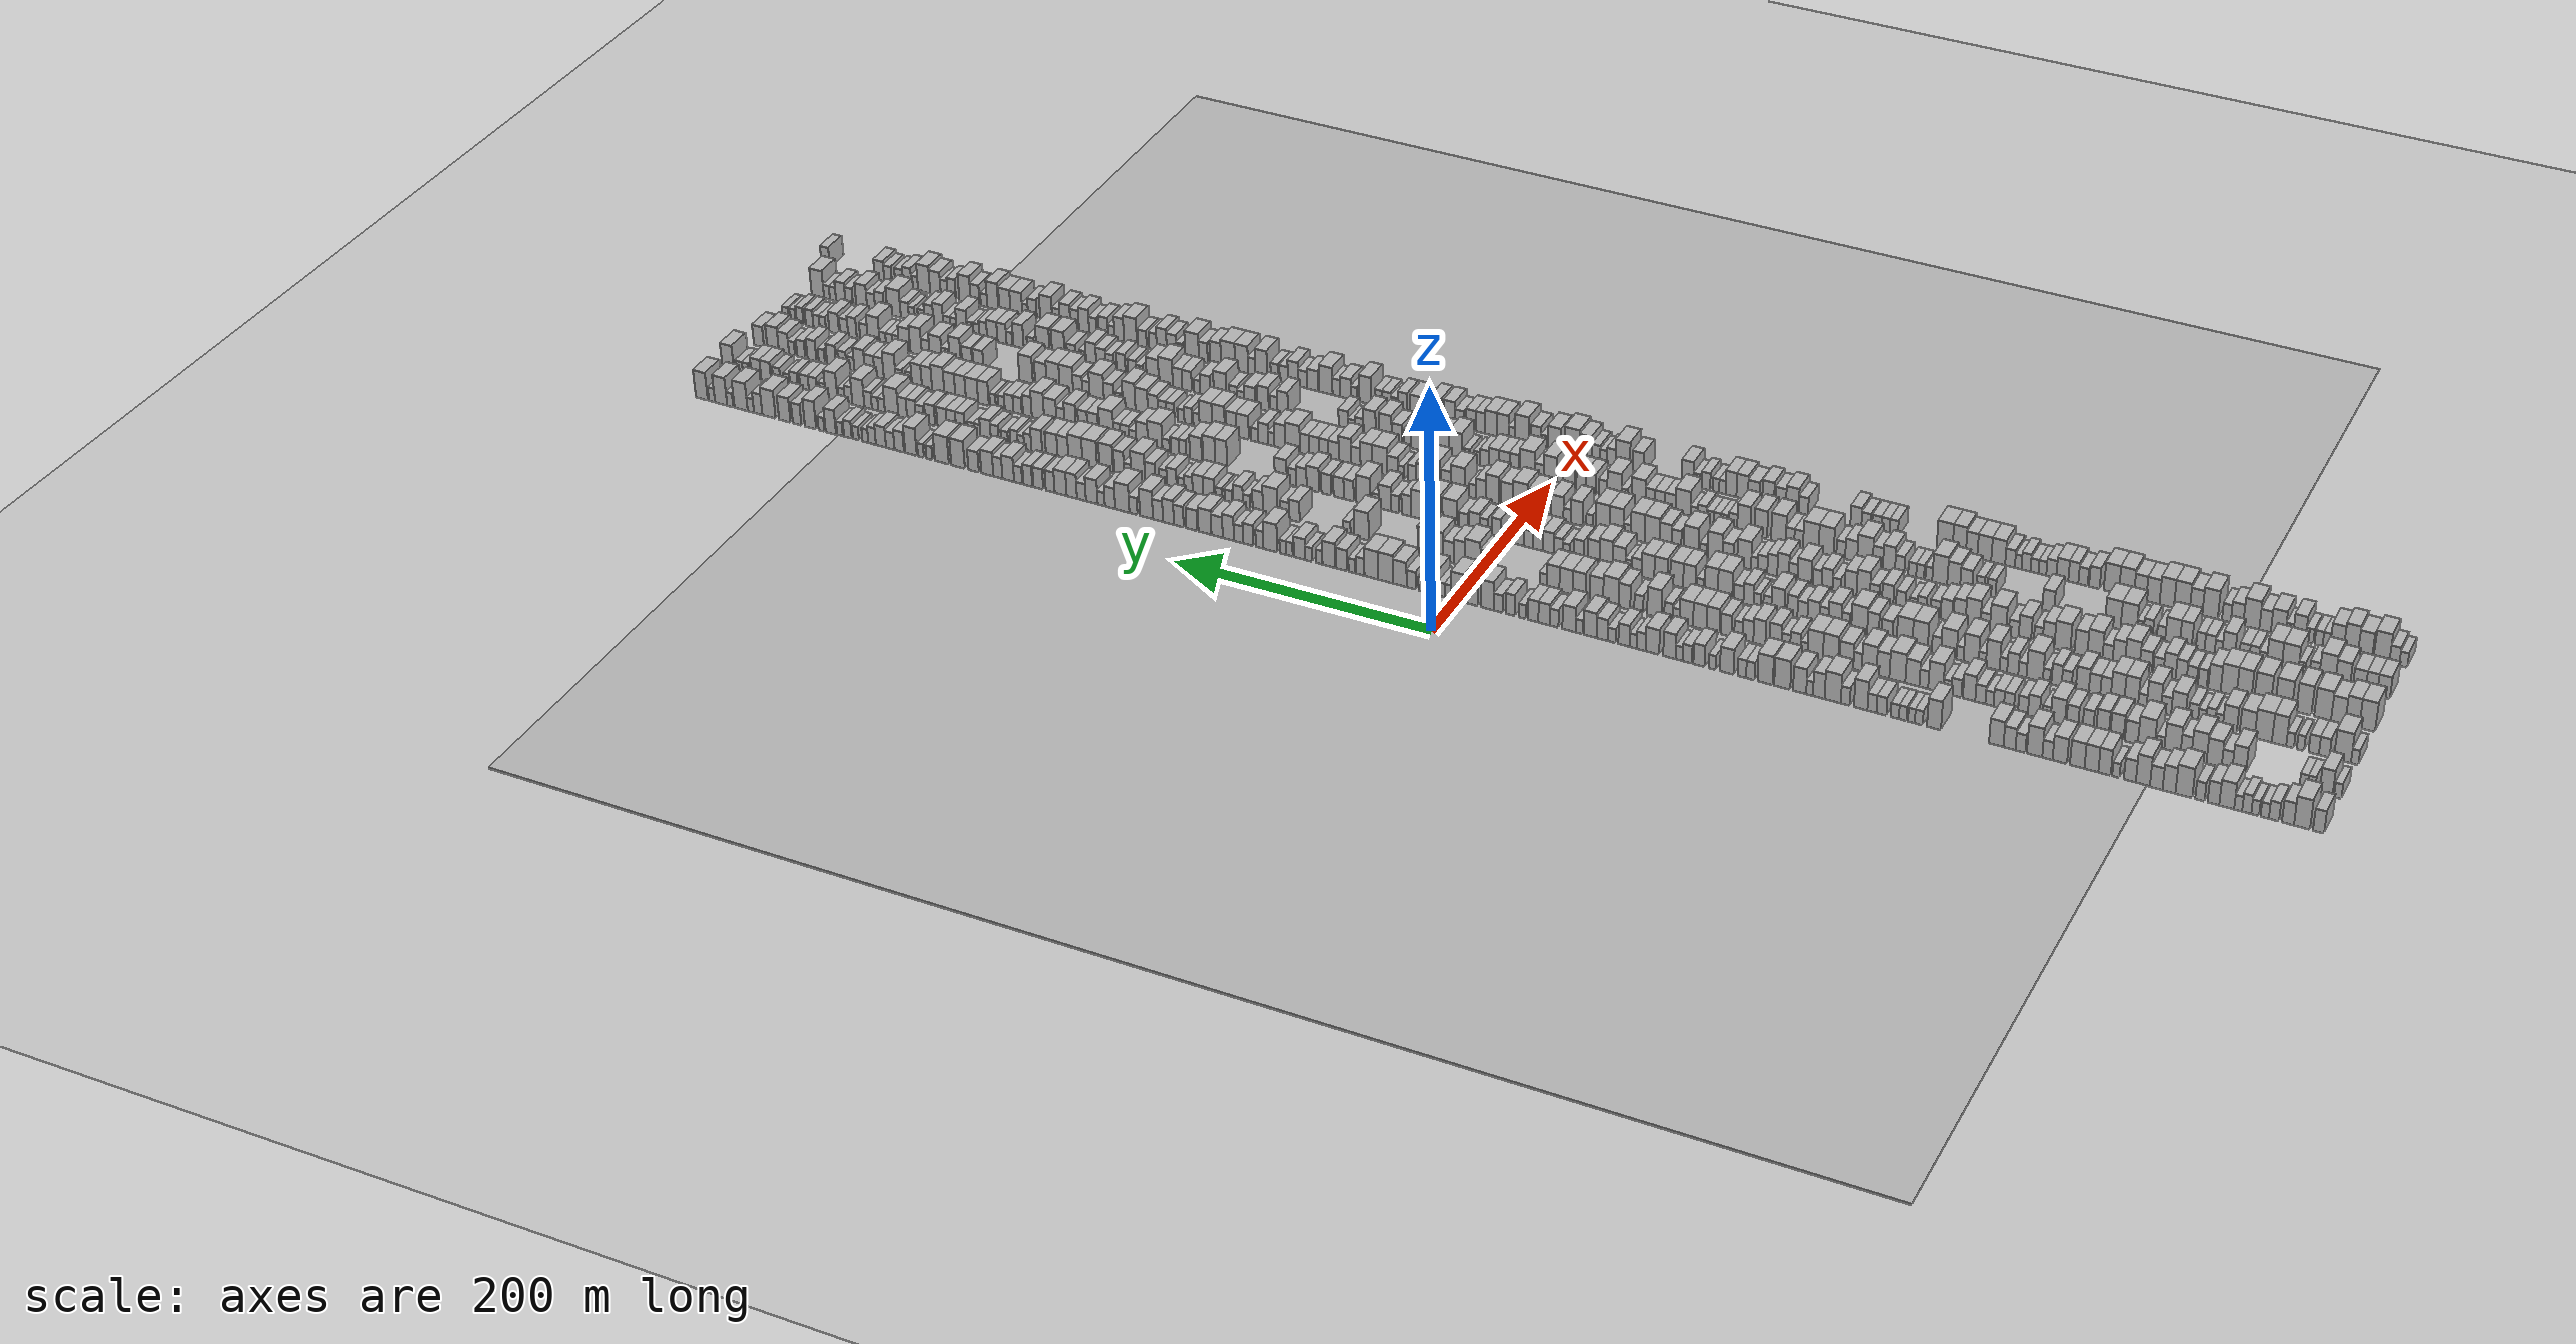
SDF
<?xml version="1.0" encoding="utf-8"?>

<sdf version="1.6">

   <world name="default">

      <gui fullscreen="0">

         <camera name="user_camera">

            <pose>-15 0 4.57585 0 0 0</pose>

            <view_controller>orbit</view_controller>

         </camera>

      </gui>

      <scene>

         <sky>

           <clouds>

             <speed>12</speed>

           </clouds>

         </sky>

         <ambient>0.4 0.4 0.4 1</ambient>

         <background>0.7 0.7 0.7 1</background>

         <shadows>1</shadows>

      </scene>

      <gravity>0 0 -9.8066</gravity>

      <magnetic_field>6e-06 2.3e-05 -4.2e-05</magnetic_field>

      <physics default="0" name="default_physics" type="ode">

         <ode>

            <solver>

               <type>quick</type>

               <iters>10</iters>

               <sor>1.0</sor>

               <use_dynamic_moi_rescaling>0</use_dynamic_moi_rescaling>

            </solver>

            <constraints>

               <cfm>0</cfm>

               <erp>0.2</erp>

               <contact_max_correcting_vel>100</contact_max_correcting_vel>

               <contact_surface_layer>0.001</contact_surface_layer>

            </constraints>

         </ode>

         <max_step_size>0.004</max_step_size>

         <real_time_factor>1</real_time_factor>

         <real_time_update_rate>250</real_time_update_rate>

      </physics>

      <light name="sun" type="directional">

         <cast_shadows>1</cast_shadows>

         <pose>0 0 10 0 0 0</pose>

         <diffuse>0.8 0.8 0.8 1</diffuse>

         <specular>0.2 0.2 0.2 1</specular>

         <attenuation>

            <range>1000</range>

            <constant>0.9</constant>

            <linear>0.01</linear>

            <quadratic>0.001</quadratic>

         </attenuation>

         <direction>-0.5 0.1 -0.9</direction>

      </light>

      <include>

         <name>ground_plane_1</name>

         <uri>model://HANNAS_ground_plane</uri>

         <pose>0 0 0  0 0 0</pose>

      </include>

      <include>

         <name>ground_plane_2</name>

         <uri>model://HANNAS_ground_plane</uri>

         <pose>100 0 0  0 0 0</pose>

      </include>

      <model name="building_1">

         <static>1</static>

         <pose frame="">50.0000 -616.2882 0 0.000000 0.000000 0.000000</pose>

         <link name="link">

            <pose frame="">0 0 9.00 0 0 0</pose>

            <collision name="collision">

               <geometry>

                  <box>

                     <size>20.0000 7.4237 18.0000</size>

                  </box>

               </geometry>

               <max_contacts>10</max_contacts>

               <surface>

                  <contact>

                     <ode/>

                  </contact>

                  <bounce/>

                  <friction>

                     <torsional>

                        <ode/>

                     </torsional>

                     <ode/>

                  </friction>

               </surface>

            </collision>

            <visual name="visual">

               <cast_shadows>0</cast_shadows>

               <geometry>

                  <box>

                     <size>20.0000 7.4237 18.0000</size>

                  </box>

               </geometry>

               <material>

                  <script>

                     <uri>model://HANNAS_wall/materials/scripts</uri>

                     <uri>model://HANNAS_wall/materials/textures</uri>

                     <name>vrc/HANNAS_wall</name>

                  </script>

               </material>

            </visual>

            <self_collide>0</self_collide>

            <enable_wind>0</enable_wind>

            <kinematic>0</kinematic>

         </link>

      </model>

      <model name="building_2">

         <static>1</static>

         <pose frame="">50.0000 -605.2129 0 0.000000 0.000000 0.000000</pose>

         <link name="link">

            <pose frame="">0 0 12.00 0 0 0</pose>

            <collision name="collision">

               <geometry>

                  <box>

                     <size>20.0000 10.7267 24.0000</size>

                  </box>

               </geometry>

               <max_contacts>10</max_contacts>

               <surface>

                  <contact>

                     <ode/>

                  </contact>

                  <bounce/>

                  <friction>

                     <torsional>

                        <ode/>

                     </torsional>

                     <ode/>

                  </friction>

               </surface>

            </collision>

            <visual name="visual">

               <cast_shadows>0</cast_shadows>

               <geometry>

                  <box>

                     <size>20.0000 10.7267 24.0000</size>

                  </box>

               </geometry>

               <material>

                  <script>

                     <uri>model://HANNAS_wall/materials/scripts</uri>

                     <uri>model://HANNAS_wall/materials/textures</uri>

                     <name>vrc/HANNAS_wall</name>

                  </script>

               </material>

            </visual>

            <self_collide>0</self_collide>

            <enable_wind>0</enable_wind>

            <kinematic>0</kinematic>

         </link>

      </model>

      <model name="building_3">

         <static>1</static>

         <pose frame="">50.0000 -595.8107 0 0.000000 0.000000 0.000000</pose>

         <link name="link">

            <pose frame="">0 0 9.00 0 0 0</pose>

            <collision name="collision">

               <geometry>

                  <box>

                     <size>20.0000 8.0778 18.0000</size>

                  </box>

               </geometry>

               <max_contacts>10</max_contacts>

               <surface>

                  <contact>

                     <ode/>

                  </contact>

                  <bounce/>

                  <friction>

                     <torsional>

                        <ode/>

                     </torsional>

                     <ode/>

                  </friction>

               </surface>

            </collision>

            <visual name="visual">

               <cast_shadows>0</cast_shadows>

               <geometry>

                  <box>

                     <size>20.0000 8.0778 18.0000</size>

                  </box>

               </geometry>

               <material>

                  <script>

                     <uri>model://HANNAS_wall/materials/scripts</uri>

                     <uri>model://HANNAS_wall/materials/textures</uri>

                     <name>vrc/HANNAS_wall</name>

                  </script>

               </material>

            </visual>

            <self_collide>0</self_collide>

            <enable_wind>0</enable_wind>

            <kinematic>0</kinematic>

         </link>

      </model>

      <model name="building_4">

         <static>1</static>

         <pose frame="">50.0000 -586.3865 0 0.000000 0.000000 0.000000</pose>

         <link name="link">

            <pose frame="">0 0 7.50 0 0 0</pose>

            <collision name="collision">

               <geometry>

                  <box>

                     <size>20.0000 6.7706 15.0000</size>

                  </box>

               </geometry>

               <max_contacts>10</max_contacts>

               <surface>

                  <contact>

                     <ode/>

                  </contact>

                  <bounce/>

                  <friction>

                     <torsional>

                        <ode/>

                     </torsional>

                     <ode/>

                  </friction>

               </surface>

            </collision>

            <visual name="visual">

               <cast_shadows>0</cast_shadows>

               <geometry>

                  <box>

                     <size>20.0000 6.7706 15.0000</size>

                  </box>

               </geometry>

               <material>

                  <script>

                     <uri>model://HANNAS_wall/materials/scripts</uri>

                     <uri>model://HANNAS_wall/materials/textures</uri>

                     <name>vrc/HANNAS_wall</name>

                  </script>

               </material>

            </visual>

            <self_collide>0</self_collide>

            <enable_wind>0</enable_wind>

            <kinematic>0</kinematic>

         </link>

      </model>

      <model name="building_5">

         <static>1</static>

         <pose frame="">50.0000 -580.1825 0 0.000000 0.000000 0.000000</pose>

         <link name="link">

            <pose frame="">0 0 6.00 0 0 0</pose>

            <collision name="collision">

               <geometry>

                  <box>

                     <size>20.0000 5.6373 12.0000</size>

                  </box>

               </geometry>

               <max_contacts>10</max_contacts>

               <surface>

                  <contact>

                     <ode/>

                  </contact>

                  <bounce/>

                  <friction>

                     <torsional>

                        <ode/>

                     </torsional>

                     <ode/>

                  </friction>

               </surface>

            </collision>

            <visual name="visual">

               <cast_shadows>0</cast_shadows>

               <geometry>

                  <box>

                     <size>20.0000 5.6373 12.0000</size>

                  </box>

               </geometry>

               <material>

                  <script>

                     <uri>model://HANNAS_wall/materials/scripts</uri>

                     <uri>model://HANNAS_wall/materials/textures</uri>

                     <name>vrc/HANNAS_wall</name>

                  </script>

               </material>

            </visual>

            <self_collide>0</self_collide>

            <enable_wind>0</enable_wind>

            <kinematic>0</kinematic>

         </link>

      </model>

      <model name="building_6">

         <static>1</static>

         <pose frame="">50.0000 -573.7439 0 0.000000 0.000000 0.000000</pose>

         <link name="link">

            <pose frame="">0 0 6.00 0 0 0</pose>

            <collision name="collision">

               <geometry>

                  <box>

                     <size>20.0000 5.2398 12.0000</size>

                  </box>

               </geometry>

               <max_contacts>10</max_contacts>

               <surface>

                  <contact>

                     <ode/>

                  </contact>

                  <bounce/>

                  <friction>

                     <torsional>

                        <ode/>

                     </torsional>

                     <ode/>

                  </friction>

               </surface>

            </collision>

            <visual name="visual">

               <cast_shadows>0</cast_shadows>

               <geometry>

                  <box>

                     <size>20.0000 5.2398 12.0000</size>

                  </box>

               </geometry>

               <material>

                  <script>

                     <uri>model://HANNAS_wall/materials/scripts</uri>

                     <uri>model://HANNAS_wall/materials/textures</uri>

                     <name>vrc/HANNAS_wall</name>

                  </script>

               </material>

            </visual>

            <self_collide>0</self_collide>

            <enable_wind>0</enable_wind>

            <kinematic>0</kinematic>

         </link>

      </model>

      <model name="building_7">

         <static>1</static>

         <pose frame="">50.0000 -568.0498 0 0.000000 0.000000 0.000000</pose>

         <link name="link">

            <pose frame="">0 0 7.50 0 0 0</pose>

            <collision name="collision">

               <geometry>

                  <box>

                     <size>20.0000 6.1485 15.0000</size>

                  </box>

               </geometry>

               <max_contacts>10</max_contacts>

               <surface>

                  <contact>

                     <ode/>

                  </contact>

                  <bounce/>

                  <friction>

                     <torsional>

                        <ode/>

                     </torsional>

                     <ode/>

                  </friction>

               </surface>

            </collision>

            <visual name="visual">

               <cast_shadows>0</cast_shadows>

               <geometry>

                  <box>

                     <size>20.0000 6.1485 15.0000</size>

                  </box>

               </geometry>

               <material>

                  <script>

                     <uri>model://HANNAS_wall/materials/scripts</uri>

                     <uri>model://HANNAS_wall/materials/textures</uri>

                     <name>vrc/HANNAS_wall</name>

                  </script>

               </material>

            </visual>

            <self_collide>0</self_collide>

            <enable_wind>0</enable_wind>

            <kinematic>0</kinematic>

         </link>

      </model>

      <model name="building_8">

         <static>1</static>

         <pose frame="">50.0000 -562.2746 0 0.000000 0.000000 0.000000</pose>

         <link name="link">

            <pose frame="">0 0 6.00 0 0 0</pose>

            <collision name="collision">

               <geometry>

                  <box>

                     <size>20.0000 5.4018 12.0000</size>

                  </box>

               </geometry>

               <max_contacts>10</max_contacts>

               <surface>

                  <contact>

                     <ode/>

                  </contact>

                  <bounce/>

                  <friction>

                     <torsional>

                        <ode/>

                     </torsional>

                     <ode/>

                  </friction>

               </surface>

            </collision>

            <visual name="visual">

               <cast_shadows>0</cast_shadows>

               <geometry>

                  <box>

                     <size>20.0000 5.4018 12.0000</size>

                  </box>

               </geometry>

               <material>

                  <script>

                     <uri>model://HANNAS_wall/materials/scripts</uri>

                     <uri>model://HANNAS_wall/materials/textures</uri>

                     <name>vrc/HANNAS_wall</name>

                  </script>

               </material>

            </visual>

            <self_collide>0</self_collide>

            <enable_wind>0</enable_wind>

            <kinematic>0</kinematic>

         </link>

      </model>

      <model name="building_9">

         <static>1</static>

         <pose frame="">50.0000 -554.5312 0 0.000000 0.000000 0.000000</pose>

         <link name="link">

            <pose frame="">0 0 10.50 0 0 0</pose>

            <collision name="collision">

               <geometry>

                  <box>

                     <size>20.0000 10.0851 21.0000</size>

                  </box>

               </geometry>

               <max_contacts>10</max_contacts>

               <surface>

                  <contact>

                     <ode/>

                  </contact>

                  <bounce/>

                  <friction>

                     <torsional>

                        <ode/>

                     </torsional>

                     <ode/>

                  </friction>

               </surface>

            </collision>

            <visual name="visual">

               <cast_shadows>0</cast_shadows>

               <geometry>

                  <box>

                     <size>20.0000 10.0851 21.0000</size>

                  </box>

               </geometry>

               <material>

                  <script>

                     <uri>model://HANNAS_wall/materials/scripts</uri>

                     <uri>model://HANNAS_wall/materials/textures</uri>

                     <name>vrc/HANNAS_wall</name>

                  </script>

               </material>

            </visual>

            <self_collide>0</self_collide>

            <enable_wind>0</enable_wind>

            <kinematic>0</kinematic>

         </link>

      </model>

      <model name="building_10">

         <static>1</static>

         <pose frame="">50.0000 -545.5108 0 0.000000 0.000000 0.000000</pose>

         <link name="link">

            <pose frame="">0 0 9.00 0 0 0</pose>

            <collision name="collision">

               <geometry>

                  <box>

                     <size>20.0000 7.9555 18.0000</size>

                  </box>

               </geometry>

               <max_contacts>10</max_contacts>

               <surface>

                  <contact>

                     <ode/>

                  </contact>

                  <bounce/>

                  <friction>

                     <torsional>

                        <ode/>

                     </torsional>

                     <ode/>

                  </friction>

               </surface>

            </collision>

            <visual name="visual">

               <cast_shadows>0</cast_shadows>

               <geometry>

                  <box>

                     <size>20.0000 7.9555 18.0000</size>

                  </box>

               </geometry>

               <material>

                  <script>

                     <uri>model://HANNAS_wall/materials/scripts</uri>

                     <uri>model://HANNAS_wall/materials/textures</uri>

                     <name>vrc/HANNAS_wall</name>

                  </script>

               </material>

            </visual>

            <self_collide>0</self_collide>

            <enable_wind>0</enable_wind>

            <kinematic>0</kinematic>

         </link>

      </model>

      <model name="building_11">

         <static>1</static>

         <pose frame="">50.0000 -536.3424 0 0.000000 0.000000 0.000000</pose>

         <link name="link">

            <pose frame="">0 0 7.50 0 0 0</pose>

            <collision name="collision">

               <geometry>

                  <box>

                     <size>20.0000 6.3814 15.0000</size>

                  </box>

               </geometry>

               <max_contacts>10</max_contacts>

               <surface>

                  <contact>

                     <ode/>

                  </contact>

                  <bounce/>

                  <friction>

                     <torsional>

                        <ode/>

                     </torsional>

                     <ode/>

                  </friction>

               </surface>

            </collision>

            <visual name="visual">

               <cast_shadows>0</cast_shadows>

               <geometry>

                  <box>

                     <size>20.0000 6.3814 15.0000</size>

                  </box>

               </geometry>

               <material>

                  <script>

                     <uri>model://HANNAS_wall/materials/scripts</uri>

                     <uri>model://HANNAS_wall/materials/textures</uri>

                     <name>vrc/HANNAS_wall</name>

                  </script>

               </material>

            </visual>

            <self_collide>0</self_collide>

            <enable_wind>0</enable_wind>

            <kinematic>0</kinematic>

         </link>

      </model>

      <model name="building_12">

         <static>1</static>

         <pose frame="">50.0000 -525.3938 0 0.000000 0.000000 0.000000</pose>

         <link name="link">

            <pose frame="">0 0 12.00 0 0 0</pose>

            <collision name="collision">

               <geometry>

                  <box>

                     <size>20.0000 11.5157 24.0000</size>

                  </box>

               </geometry>

               <max_contacts>10</max_contacts>

               <surface>

                  <contact>

                     <ode/>

                  </contact>

                  <bounce/>

                  <friction>

                     <torsional>

                        <ode/>

                     </torsional>

                     <ode/>

                  </friction>

               </surface>

            </collision>

            <visual name="visual">

               <cast_shadows>0</cast_shadows>

               <geometry>

                  <box>

                     <size>20.0000 11.5157 24.0000</size>

                  </box>

               </geometry>

               <material>

                  <script>

                     <uri>model://HANNAS_wall/materials/scripts</uri>

                     <uri>model://HANNAS_wall/materials/textures</uri>

                     <name>vrc/HANNAS_wall</name>

                  </script>

               </material>

            </visual>

            <self_collide>0</self_collide>

            <enable_wind>0</enable_wind>

            <kinematic>0</kinematic>

         </link>

      </model>

      <model name="building_13">

         <static>1</static>

         <pose frame="">50.0000 -515.2146 0 0.000000 0.000000 0.000000</pose>

         <link name="link">

            <pose frame="">0 0 10.50 0 0 0</pose>

            <collision name="collision">

               <geometry>

                  <box>

                     <size>20.0000 8.8427 21.0000</size>

                  </box>

               </geometry>

               <max_contacts>10</max_contacts>

               <surface>

                  <contact>

                     <ode/>

                  </contact>

                  <bounce/>

                  <friction>

                     <torsional>

                        <ode/>

                     </torsional>

                     <ode/>

                  </friction>

               </surface>

            </collision>

            <visual name="visual">

               <cast_shadows>0</cast_shadows>

               <geometry>

                  <box>

                     <size>20.0000 8.8427 21.0000</size>

                  </box>

               </geometry>

               <material>

                  <script>

                     <uri>model://HANNAS_wall/materials/scripts</uri>

                     <uri>model://HANNAS_wall/materials/textures</uri>

                     <name>vrc/HANNAS_wall</name>

                  </script>

               </material>

            </visual>

            <self_collide>0</self_collide>

            <enable_wind>0</enable_wind>

            <kinematic>0</kinematic>

         </link>

      </model>

      <model name="building_14">

         <static>1</static>

         <pose frame="">50.0000 -506.4676 0 0.000000 0.000000 0.000000</pose>

         <link name="link">

            <pose frame="">0 0 9.00 0 0 0</pose>

            <collision name="collision">

               <geometry>

                  <box>

                     <size>20.0000 8.6514 18.0000</size>

                  </box>

               </geometry>

               <max_contacts>10</max_contacts>

               <surface>

                  <contact>

                     <ode/>

                  </contact>

                  <bounce/>

                  <friction>

                     <torsional>

                        <ode/>

                     </torsional>

                     <ode/>

                  </friction>

               </surface>

            </collision>

            <visual name="visual">

               <cast_shadows>0</cast_shadows>

               <geometry>

                  <box>

                     <size>20.0000 8.6514 18.0000</size>

                  </box>

               </geometry>

               <material>

                  <script>

                     <uri>model://HANNAS_wall/materials/scripts</uri>

                     <uri>model://HANNAS_wall/materials/textures</uri>

                     <name>vrc/HANNAS_wall</name>

                  </script>

               </material>

            </visual>

            <self_collide>0</self_collide>

            <enable_wind>0</enable_wind>

            <kinematic>0</kinematic>

         </link>

      </model>

      <model name="building_15">

         <static>1</static>

         <pose frame="">50.0000 -497.2800 0 0.000000 0.000000 0.000000</pose>

         <link name="link">

            <pose frame="">0 0 12.00 0 0 0</pose>

            <collision name="collision">

               <geometry>

                  <box>

                     <size>20.0000 9.7236 24.0000</size>

                  </box>

               </geometry>

               <max_contacts>10</max_contacts>

               <surface>

                  <contact>

                     <ode/>

                  </contact>

                  <bounce/>

                  <friction>

                     <torsional>

                        <ode/>

                     </torsional>

                     <ode/>

                  </friction>

               </surface>

            </collision>

            <visual name="visual">

               <cast_shadows>0</cast_shadows>

               <geometry>

                  <box>

                     <size>20.0000 9.7236 24.0000</size>

                  </box>

               </geometry>

               <material>

                  <script>

                     <uri>model://HANNAS_wall/materials/scripts</uri>

                     <uri>model://HANNAS_wall/materials/textures</uri>

                     <name>vrc/HANNAS_wall</name>

                  </script>

               </material>

            </visual>

            <self_collide>0</self_collide>

            <enable_wind>0</enable_wind>

            <kinematic>0</kinematic>

         </link>

      </model>

      <model name="building_16">

         <static>1</static>

         <pose frame="">50.0000 -488.3094 0 0.000000 0.000000 0.000000</pose>

         <link name="link">

            <pose frame="">0 0 9.00 0 0 0</pose>

            <collision name="collision">

               <geometry>

                  <box>

                     <size>20.0000 8.2177 18.0000</size>

                  </box>

               </geometry>

               <max_contacts>10</max_contacts>

               <surface>

                  <contact>

                     <ode/>

                  </contact>

                  <bounce/>

                  <friction>

                     <torsional>

                        <ode/>

                     </torsional>

                     <ode/>

                  </friction>

               </surface>

            </collision>

            <visual name="visual">

               <cast_shadows>0</cast_shadows>

               <geometry>

                  <box>

                     <size>20.0000 8.2177 18.0000</size>

                  </box>

               </geometry>

               <material>

                  <script>

                     <uri>model://HANNAS_wall/materials/scripts</uri>

                     <uri>model://HANNAS_wall/materials/textures</uri>

                     <name>vrc/HANNAS_wall</name>

                  </script>

               </material>

            </visual>

            <self_collide>0</self_collide>

            <enable_wind>0</enable_wind>

            <kinematic>0</kinematic>

         </link>

      </model>

      <model name="building_17">

         <static>1</static>

         <pose frame="">50.0000 -478.6717 0 0.000000 0.000000 0.000000</pose>

         <link name="link">

            <pose frame="">0 0 6.00 0 0 0</pose>

            <collision name="collision">

               <geometry>

                  <box>

                     <size>20.0000 5.0578 12.0000</size>

                  </box>

               </geometry>

               <max_contacts>10</max_contacts>

               <surface>

                  <contact>

                     <ode/>

                  </contact>

                  <bounce/>

                  <friction>

                     <torsional>

                        <ode/>

                     </torsional>

                     <ode/>

                  </friction>

               </surface>

            </collision>

            <visual name="visual">

               <cast_shadows>0</cast_shadows>

               <geometry>

                  <box>

                     <size>20.0000 5.0578 12.0000</size>

                  </box>

               </geometry>

               <material>

                  <script>

                     <uri>model://HANNAS_wall/materials/scripts</uri>

                     <uri>model://HANNAS_wall/materials/textures</uri>

                     <name>vrc/HANNAS_wall</name>

                  </script>

               </material>

            </visual>

            <self_collide>0</self_collide>

            <enable_wind>0</enable_wind>

            <kinematic>0</kinematic>

         </link>

      </model>

      <model name="building_18">

         <static>1</static>

         <pose frame="">50.0000 -470.8829 0 0.000000 0.000000 0.000000</pose>

         <link name="link">

            <pose frame="">0 0 10.50 0 0 0</pose>

            <collision name="collision">

               <geometry>

                  <box>

                     <size>20.0000 8.5197 21.0000</size>

                  </box>

               </geometry>

               <max_contacts>10</max_contacts>

               <surface>

                  <contact>

                     <ode/>

                  </contact>

                  <bounce/>

                  <friction>

                     <torsional>

                        <ode/>

                     </torsional>

                     <ode/>

                  </friction>

               </surface>

            </collision>

            <visual name="visual">

               <cast_shadows>0</cast_shadows>

               <geometry>

                  <box>

                     <size>20.0000 8.5197 21.0000</size>

                  </box>

               </geometry>

               <material>

                  <script>

                     <uri>model://HANNAS_wall/materials/scripts</uri>

                     <uri>model://HANNAS_wall/materials/textures</uri>

                     <name>vrc/HANNAS_wall</name>

                  </script>

               </material>

            </visual>

            <self_collide>0</self_collide>

            <enable_wind>0</enable_wind>

            <kinematic>0</kinematic>

         </link>

      </model>

      <model name="building_19">

         <static>1</static>

         <pose frame="">50.0000 -461.8293 0 0.000000 0.000000 0.000000</pose>

         <link name="link">

            <pose frame="">0 0 10.50 0 0 0</pose>

            <collision name="collision">

               <geometry>

                  <box>

                     <size>20.0000 9.5874 21.0000</size>

                  </box>

               </geometry>

               <max_contacts>10</max_contacts>

               <surface>

                  <contact>

                     <ode/>

                  </contact>

                  <bounce/>

                  <friction>

                     <torsional>

                        <ode/>

                     </torsional>

                     <ode/>

                  </friction>

               </surface>

            </collision>

            <visual name="visual">

               <cast_shadows>0</cast_shadows>

               <geometry>

                  <box>

                     <size>20.0000 9.5874 21.0000</size>

                  </box>

               </geometry>

               <material>

                  <script>

                     <uri>model://HANNAS_wall/materials/scripts</uri>

                     <uri>model://HANNAS_wall/materials/textures</uri>

                     <name>vrc/HANNAS_wall</name>

                  </script>

               </material>

            </visual>

            <self_collide>0</self_collide>

            <enable_wind>0</enable_wind>

            <kinematic>0</kinematic>

         </link>

      </model>

      <model name="building_20">

         <static>1</static>

         <pose frame="">50.0000 -451.9908 0 0.000000 0.000000 0.000000</pose>

         <link name="link">

            <pose frame="">0 0 10.50 0 0 0</pose>

            <collision name="collision">

               <geometry>

                  <box>

                     <size>20.0000 10.0895 21.0000</size>

                  </box>

               </geometry>

               <max_contacts>10</max_contacts>

               <surface>

                  <contact>

                     <ode/>

                  </contact>

                  <bounce/>

                  <friction>

                     <torsional>

                        <ode/>

                     </torsional>

                     <ode/>

                  </friction>

               </surface>

            </collision>

            <visual name="visual">

               <cast_shadows>0</cast_shadows>

               <geometry>

                  <box>

                     <size>20.0000 10.0895 21.0000</size>

                  </box>

               </geometry>

               <material>

                  <script>

                     <uri>model://HANNAS_wall/materials/scripts</uri>

                     <uri>model://HANNAS_wall/materials/textures</uri>

                     <name>vrc/HANNAS_wall</name>

                  </script>

               </material>

            </visual>

            <self_collide>0</self_collide>

            <enable_wind>0</enable_wind>

            <kinematic>0</kinematic>

         </link>

      </model>

      <model name="building_21">

         <static>1</static>

         <pose frame="">50.0000 -439.9129 0 0.000000 0.000000 0.000000</pose>

         <link name="link">

            <pose frame="">0 0 10.50 0 0 0</pose>

            <collision name="collision">

               <geometry>

                  <box>

                     <size>20.0000 10.0663 21.0000</size>

                  </box>

               </geometry>

               <max_contacts>10</max_contacts>

               <surface>

                  <contact>

                     <ode/>

                  </contact>

                  <bounce/>

                  <friction>

                     <torsional>

                        <ode/>

                     </torsional>

                     <ode/>

                  </friction>

               </surface>

            </collision>

            <visual name="visual">

               <cast_shadows>0</cast_shadows>

               <geometry>

                  <box>

                     <size>20.0000 10.0663 21.0000</size>

                  </box>

               </geometry>

               <material>

                  <script>

                     <uri>model://HANNAS_wall/materials/scripts</uri>

                     <uri>model://HANNAS_wall/materials/textures</uri>

                     <name>vrc/HANNAS_wall</name>

                  </script>

               </material>

            </visual>

            <self_collide>0</self_collide>

            <enable_wind>0</enable_wind>

            <kinematic>0</kinematic>

         </link>

      </model>

      <model name="building_22">

         <static>1</static>

         <pose frame="">50.0000 -431.2850 0 0.000000 0.000000 0.000000</pose>

         <link name="link">

            <pose frame="">0 0 7.50 0 0 0</pose>

            <collision name="collision">

               <geometry>

                  <box>

                     <size>20.0000 7.1896 15.0000</size>

                  </box>

               </geometry>

               <max_contacts>10</max_contacts>

               <surface>

                  <contact>

                     <ode/>

                  </contact>

                  <bounce/>

                  <friction>

                     <torsional>

                        <ode/>

                     </torsional>

                     <ode/>

                  </friction>

               </surface>

            </collision>

            <visual name="visual">

               <cast_shadows>0</cast_shadows>

               <geometry>

                  <box>

                     <size>20.0000 7.1896 15.0000</size>

                  </box>

               </geometry>

               <material>

                  <script>

                     <uri>model://HANNAS_wall/materials/scripts</uri>

                     <uri>model://HANNAS_wall/materials/textures</uri>

                     <name>vrc/HANNAS_wall</name>

                  </script>

               </material>

            </visual>

            <self_collide>0</self_collide>

            <enable_wind>0</enable_wind>

            <kinematic>0</kinematic>

         </link>

      </model>

      <model name="building_23">

         <static>1</static>

         <pose frame="">50.0000 -422.3025 0 0.000000 0.000000 0.000000</pose>

         <link name="link">

            <pose frame="">0 0 12.00 0 0 0</pose>

            <collision name="collision">

               <geometry>

                  <box>

                     <size>20.0000 10.7754 24.0000</size>

                  </box>

               </geometry>

               <max_contacts>10</max_contacts>

               <surface>

                  <contact>

                     <ode/>

                  </contact>

                  <bounce/>

                  <friction>

                     <torsional>

                        <ode/>

                     </torsional>

                     <ode/>

                  </friction>

               </surface>

            </collision>

            <visual name="visual">

               <cast_shadows>0</cast_shadows>

               <geometry>

                  <box>

                     <size>20.0000 10.7754 24.0000</size>

                  </box>

               </geometry>

               <material>

                  <script>

                     <uri>model://HANNAS_wall/materials/scripts</uri>

                     <uri>model://HANNAS_wall/materials/textures</uri>

                     <name>vrc/HANNAS_wall</name>

                  </script>

               </material>

            </visual>

            <self_collide>0</self_collide>

            <enable_wind>0</enable_wind>

            <kinematic>0</kinematic>

         </link>

      </model>

      <model name="building_24">

         <static>1</static>

         <pose frame="">50.0000 -412.4510 0 0.000000 0.000000 0.000000</pose>

         <link name="link">

            <pose frame="">0 0 7.50 0 0 0</pose>

            <collision name="collision">

               <geometry>

                  <box>

                     <size>20.0000 6.9275 15.0000</size>

                  </box>

               </geometry>

               <max_contacts>10</max_contacts>

               <surface>

                  <contact>

                     <ode/>

                  </contact>

                  <bounce/>

                  <friction>

                     <torsional>

                        <ode/>

                     </torsional>

                     <ode/>

                  </friction>

               </surface>

            </collision>

            <visual name="visual">

               <cast_shadows>0</cast_shadows>

               <geometry>

                  <box>

                     <size>20.0000 6.9275 15.0000</size>

                  </box>

               </geometry>

               <material>

                  <script>

                     <uri>model://HANNAS_wall/materials/scripts</uri>

                     <uri>model://HANNAS_wall/materials/textures</uri>

                     <name>vrc/HANNAS_wall</name>

                  </script>

               </material>

            </visual>

            <self_collide>0</self_collide>

            <enable_wind>0</enable_wind>

            <kinematic>0</kinematic>

         </link>

      </model>

      <model name="building_25">

         <static>1</static>

         <pose frame="">50.0000 -404.7914 0 0.000000 0.000000 0.000000</pose>

         <link name="link">

            <pose frame="">0 0 9.00 0 0 0</pose>

            <collision name="collision">

               <geometry>

                  <box>

                     <size>20.0000 8.3916 18.0000</size>

                  </box>

               </geometry>

               <max_contacts>10</max_contacts>

               <surface>

                  <contact>

                     <ode/>

                  </contact>

                  <bounce/>

                  <friction>

                     <torsional>

                        <ode/>

                     </torsional>

                     <ode/>

                  </friction>

               </surface>

            </collision>

            <visual name="visual">

               <cast_shadows>0</cast_shadows>

               <geometry>

                  <box>

                     <size>20.0000 8.3916 18.0000</size>

                  </box>

               </geometry>

               <material>

                  <script>

                     <uri>model://HANNAS_wall/materials/scripts</uri>

                     <uri>model://HANNAS_wall/materials/textures</uri>

                     <name>vrc/HANNAS_wall</name>

                  </script>

               </material>

            </visual>

            <self_collide>0</self_collide>

            <enable_wind>0</enable_wind>

            <kinematic>0</kinematic>

         </link>

      </model>

      <model name="building_26">

         <static>1</static>

         <pose frame="">50.0000 -395.5258 0 0.000000 0.000000 0.000000</pose>

         <link name="link">

            <pose frame="">0 0 10.50 0 0 0</pose>

            <collision name="collision">

               <geometry>

                  <box>

                     <size>20.0000 10.1397 21.0000</size>

                  </box>

               </geometry>

               <max_contacts>10</max_contacts>

               <surface>

                  <contact>

                     <ode/>

                  </contact>

                  <bounce/>

                  <friction>

                     <torsional>

                        <ode/>

                     </torsional>

                     <ode/>

                  </friction>

               </surface>

            </collision>

            <visual name="visual">

               <cast_shadows>0</cast_shadows>

               <geometry>

                  <box>

                     <size>20.0000 10.1397 21.0000</size>

                  </box>

               </geometry>

               <material>

                  <script>

                     <uri>model://HANNAS_wall/materials/scripts</uri>

                     <uri>model://HANNAS_wall/materials/textures</uri>

                     <name>vrc/HANNAS_wall</name>

                  </script>

               </material>

            </visual>

            <self_collide>0</self_collide>

            <enable_wind>0</enable_wind>

            <kinematic>0</kinematic>

         </link>

      </model>

      <model name="building_27">

         <static>1</static>

         <pose frame="">50.0000 -351.5895 0 0.000000 0.000000 0.000000</pose>

         <link name="link">

            <pose frame="">0 0 12.00 0 0 0</pose>

            <collision name="collision">

               <geometry>

                  <box>

                     <size>20.0000 9.9109 24.0000</size>

                  </box>

               </geometry>

               <max_contacts>10</max_contacts>

               <surface>

                  <contact>

                     <ode/>

                  </contact>

                  <bounce/>

                  <friction>

                     <torsional>

                        <ode/>

                     </torsional>

                     <ode/>

                  </friction>

               </surface>

            </collision>

            <visual name="visual">

               <cast_shadows>0</cast_shadows>

               <geometry>

                  <box>

                     <size>20.0000 9.9109 24.0000</size>

                  </box>

               </geometry>

               <material>

                  <script>

                     <uri>model://HANNAS_wall/materials/scripts</uri>

                     <uri>model://HANNAS_wall/materials/textures</uri>

                     <name>vrc/HANNAS_wall</name>

                  </script>

               </material>

            </visual>

            <self_collide>0</self_collide>

            <enable_wind>0</enable_wind>

            <kinematic>0</kinematic>

         </link>

      </model>

      <model name="building_28">

         <static>1</static>

         <pose frame="">50.0000 -340.8206 0 0.000000 0.000000 0.000000</pose>

         <link name="link">

            <pose frame="">0 0 6.00 0 0 0</pose>

            <collision name="collision">

               <geometry>

                  <box>

                     <size>20.0000 5.6268 12.0000</size>

                  </box>

               </geometry>

               <max_contacts>10</max_contacts>

               <surface>

                  <contact>

                     <ode/>

                  </contact>

                  <bounce/>

                  <friction>

                     <torsional>

                        <ode/>

                     </torsional>

                     <ode/>

                  </friction>

               </surface>

            </collision>

            <visual name="visual">

               <cast_shadows>0</cast_shadows>

               <geometry>

                  <box>

                     <size>20.0000 5.6268 12.0000</size>

                  </box>

               </geometry>

               <material>

                  <script>

                     <uri>model://HANNAS_wall/materials/scripts</uri>

                     <uri>model://HANNAS_wall/materials/textures</uri>

                     <name>vrc/HANNAS_wall</name>

                  </script>

               </material>

            </visual>

            <self_collide>0</self_collide>

            <enable_wind>0</enable_wind>

            <kinematic>0</kinematic>

         </link>

      </model>

      <model name="building_29">

         <static>1</static>

         <pose frame="">50.0000 -335.5534 0 0.000000 0.000000 0.000000</pose>

         <link name="link">

            <pose frame="">0 0 6.00 0 0 0</pose>

            <collision name="collision">

               <geometry>

                  <box>

                     <size>20.0000 4.9076 12.0000</size>

                  </box>

               </geometry>

               <max_contacts>10</max_contacts>

               <surface>

                  <contact>

                     <ode/>

                  </contact>

                  <bounce/>

                  <friction>

                     <torsional>

                        <ode/>

                     </torsional>

                     <ode/>

                  </friction>

               </surface>

            </collision>

            <visual name="visual">

               <cast_shadows>0</cast_shadows>

               <geometry>

                  <box>

                     <size>20.0000 4.9076 12.0000</size>

                  </box>

               </geometry>

               <material>

                  <script>

                     <uri>model://HANNAS_wall/materials/scripts</uri>

                     <uri>model://HANNAS_wall/materials/textures</uri>

                     <name>vrc/HANNAS_wall</name>

                  </script>

               </material>

            </visual>

            <self_collide>0</self_collide>

            <enable_wind>0</enable_wind>

            <kinematic>0</kinematic>

         </link>

      </model>

      <model name="building_30">

         <static>1</static>

         <pose frame="">50.0000 -329.3261 0 0.000000 0.000000 0.000000</pose>

         <link name="link">

            <pose frame="">0 0 6.00 0 0 0</pose>

            <collision name="collision">

               <geometry>

                  <box>

                     <size>20.0000 5.5471 12.0000</size>

                  </box>

               </geometry>

               <max_contacts>10</max_contacts>

               <surface>

                  <contact>

                     <ode/>

                  </contact>

                  <bounce/>

                  <friction>

                     <torsional>

                        <ode/>

                     </torsional>

                     <ode/>

                  </friction>

               </surface>

            </collision>

            <visual name="visual">

               <cast_shadows>0</cast_shadows>

               <geometry>

                  <box>

                     <size>20.0000 5.5471 12.0000</size>

                  </box>

               </geometry>

               <material>

                  <script>

                     <uri>model://HANNAS_wall/materials/scripts</uri>

                     <uri>model://HANNAS_wall/materials/textures</uri>

                     <name>vrc/HANNAS_wall</name>

                  </script>

               </material>

            </visual>

            <self_collide>0</self_collide>

            <enable_wind>0</enable_wind>

            <kinematic>0</kinematic>

         </link>

      </model>

      <model name="building_31">

         <static>1</static>

         <pose frame="">50.0000 -323.6118 0 0.000000 0.000000 0.000000</pose>

         <link name="link">

            <pose frame="">0 0 6.00 0 0 0</pose>

            <collision name="collision">

               <geometry>

                  <box>

                     <size>20.0000 5.8816 12.0000</size>

                  </box>

               </geometry>

               <max_contacts>10</max_contacts>

               <surface>

                  <contact>

                     <ode/>

                  </contact>

                  <bounce/>

                  <friction>

                     <torsional>

                        <ode/>

                     </torsional>

                     <ode/>

                  </friction>

               </surface>

            </collision>

            <visual name="visual">

               <cast_shadows>0</cast_shadows>

               <geometry>

                  <box>

                     <size>20.0000 5.8816 12.0000</size>

                  </box>

               </geometry>

               <material>

                  <script>

                     <uri>model://HANNAS_wall/materials/scripts</uri>

                     <uri>model://HANNAS_wall/materials/textures</uri>

                     <name>vrc/HANNAS_wall</name>

                  </script>

               </material>

            </visual>

            <self_collide>0</self_collide>

            <enable_wind>0</enable_wind>

            <kinematic>0</kinematic>

         </link>

      </model>

      <model name="building_32">

         <static>1</static>

         <pose frame="">50.0000 -314.1116 0 0.000000 0.000000 0.000000</pose>

         <link name="link">

            <pose frame="">0 0 7.50 0 0 0</pose>

            <collision name="collision">

               <geometry>

                  <box>

                     <size>20.0000 7.1188 15.0000</size>

                  </box>

               </geometry>

               <max_contacts>10</max_contacts>

               <surface>

                  <contact>

                     <ode/>

                  </contact>

                  <bounce/>

                  <friction>

                     <torsional>

                        <ode/>

                     </torsional>

                     <ode/>

                  </friction>

               </surface>

            </collision>

            <visual name="visual">

               <cast_shadows>0</cast_shadows>

               <geometry>

                  <box>

                     <size>20.0000 7.1188 15.0000</size>

                  </box>

               </geometry>

               <material>

                  <script>

                     <uri>model://HANNAS_wall/materials/scripts</uri>

                     <uri>model://HANNAS_wall/materials/textures</uri>

                     <name>vrc/HANNAS_wall</name>

                  </script>

               </material>

            </visual>

            <self_collide>0</self_collide>

            <enable_wind>0</enable_wind>

            <kinematic>0</kinematic>

         </link>

      </model>

      <model name="building_33">

         <static>1</static>

         <pose frame="">50.0000 -307.2831 0 0.000000 0.000000 0.000000</pose>

         <link name="link">

            <pose frame="">0 0 7.50 0 0 0</pose>

            <collision name="collision">

               <geometry>

                  <box>

                     <size>20.0000 6.5383 15.0000</size>

                  </box>

               </geometry>

               <max_contacts>10</max_contacts>

               <surface>

                  <contact>

                     <ode/>

                  </contact>

                  <bounce/>

                  <friction>

                     <torsional>

                        <ode/>

                     </torsional>

                     <ode/>

                  </friction>

               </surface>

            </collision>

            <visual name="visual">

               <cast_shadows>0</cast_shadows>

               <geometry>

                  <box>

                     <size>20.0000 6.5383 15.0000</size>

                  </box>

               </geometry>

               <material>

                  <script>

                     <uri>model://HANNAS_wall/materials/scripts</uri>

                     <uri>model://HANNAS_wall/materials/textures</uri>

                     <name>vrc/HANNAS_wall</name>

                  </script>

               </material>

            </visual>

            <self_collide>0</self_collide>

            <enable_wind>0</enable_wind>

            <kinematic>0</kinematic>

         </link>

      </model>

      <model name="building_34">

         <static>1</static>

         <pose frame="">50.0000 -299.1595 0 0.000000 0.000000 0.000000</pose>

         <link name="link">

            <pose frame="">0 0 12.00 0 0 0</pose>

            <collision name="collision">

               <geometry>

                  <box>

                     <size>20.0000 9.7088 24.0000</size>

                  </box>

               </geometry>

               <max_contacts>10</max_contacts>

               <surface>

                  <contact>

                     <ode/>

                  </contact>

                  <bounce/>

                  <friction>

                     <torsional>

                        <ode/>

                     </torsional>

                     <ode/>

                  </friction>

               </surface>

            </collision>

            <visual name="visual">

               <cast_shadows>0</cast_shadows>

               <geometry>

                  <box>

                     <size>20.0000 9.7088 24.0000</size>

                  </box>

               </geometry>

               <material>

                  <script>

                     <uri>model://HANNAS_wall/materials/scripts</uri>

                     <uri>model://HANNAS_wall/materials/textures</uri>

                     <name>vrc/HANNAS_wall</name>

                  </script>

               </material>

            </visual>

            <self_collide>0</self_collide>

            <enable_wind>0</enable_wind>

            <kinematic>0</kinematic>

         </link>

      </model>

      <model name="building_35">

         <static>1</static>

         <pose frame="">50.0000 -288.0968 0 0.000000 0.000000 0.000000</pose>

         <link name="link">

            <pose frame="">0 0 7.50 0 0 0</pose>

            <collision name="collision">

               <geometry>

                  <box>

                     <size>20.0000 6.4166 15.0000</size>

                  </box>

               </geometry>

               <max_contacts>10</max_contacts>

               <surface>

                  <contact>

                     <ode/>

                  </contact>

                  <bounce/>

                  <friction>

                     <torsional>

                        <ode/>

                     </torsional>

                     <ode/>

                  </friction>

               </surface>

            </collision>

            <visual name="visual">

               <cast_shadows>0</cast_shadows>

               <geometry>

                  <box>

                     <size>20.0000 6.4166 15.0000</size>

                  </box>

               </geometry>

               <material>

                  <script>

                     <uri>model://HANNAS_wall/materials/scripts</uri>

                     <uri>model://HANNAS_wall/materials/textures</uri>

                     <name>vrc/HANNAS_wall</name>

                  </script>

               </material>

            </visual>

            <self_collide>0</self_collide>

            <enable_wind>0</enable_wind>

            <kinematic>0</kinematic>

         </link>

      </model>

      <model name="building_36">

         <static>1</static>

         <pose frame="">50.0000 -279.0418 0 0.000000 0.000000 0.000000</pose>

         <link name="link">

            <pose frame="">0 0 12.00 0 0 0</pose>

            <collision name="collision">

               <geometry>

                  <box>

                     <size>20.0000 11.6933 24.0000</size>

                  </box>

               </geometry>

               <max_contacts>10</max_contacts>

               <surface>

                  <contact>

                     <ode/>

                  </contact>

                  <bounce/>

                  <friction>

                     <torsional>

                        <ode/>

                     </torsional>

                     <ode/>

                  </friction>

               </surface>

            </collision>

            <visual name="visual">

               <cast_shadows>0</cast_shadows>

               <geometry>

                  <box>

                     <size>20.0000 11.6933 24.0000</size>

                  </box>

               </geometry>

               <material>

                  <script>

                     <uri>model://HANNAS_wall/materials/scripts</uri>

                     <uri>model://HANNAS_wall/materials/textures</uri>

                     <name>vrc/HANNAS_wall</name>

                  </script>

               </material>

            </visual>

            <self_collide>0</self_collide>

            <enable_wind>0</enable_wind>

            <kinematic>0</kinematic>

         </link>

      </model>

      <model name="building_37">

         <static>1</static>

         <pose frame="">50.0000 -268.9825 0 0.000000 0.000000 0.000000</pose>

         <link name="link">

            <pose frame="">0 0 10.50 0 0 0</pose>

            <collision name="collision">

               <geometry>

                  <box>

                     <size>20.0000 8.4252 21.0000</size>

                  </box>

               </geometry>

               <max_contacts>10</max_contacts>

               <surface>

                  <contact>

                     <ode/>

                  </contact>

                  <bounce/>

                  <friction>

                     <torsional>

                        <ode/>

                     </torsional>

                     <ode/>

                  </friction>

               </surface>

            </collision>

            <visual name="visual">

               <cast_shadows>0</cast_shadows>

               <geometry>

                  <box>

                     <size>20.0000 8.4252 21.0000</size>

                  </box>

               </geometry>

               <material>

                  <script>

                     <uri>model://HANNAS_wall/materials/scripts</uri>

                     <uri>model://HANNAS_wall/materials/textures</uri>

                     <name>vrc/HANNAS_wall</name>

                  </script>

               </material>

            </visual>

            <self_collide>0</self_collide>

            <enable_wind>0</enable_wind>

            <kinematic>0</kinematic>

         </link>

      </model>

      <model name="building_38">

         <static>1</static>

         <pose frame="">50.0000 -262.3233 0 0.000000 0.000000 0.000000</pose>

         <link name="link">

            <pose frame="">0 0 6.00 0 0 0</pose>

            <collision name="collision">

               <geometry>

                  <box>

                     <size>20.0000 4.8932 12.0000</size>

                  </box>

               </geometry>

               <max_contacts>10</max_contacts>

               <surface>

                  <contact>

                     <ode/>

                  </contact>

                  <bounce/>

                  <friction>

                     <torsional>

                        <ode/>

                     </torsional>

                     <ode/>

                  </friction>

               </surface>

            </collision>

            <visual name="visual">

               <cast_shadows>0</cast_shadows>

               <geometry>

                  <box>

                     <size>20.0000 4.8932 12.0000</size>

                  </box>

               </geometry>

               <material>

                  <script>

                     <uri>model://HANNAS_wall/materials/scripts</uri>

                     <uri>model://HANNAS_wall/materials/textures</uri>

                     <name>vrc/HANNAS_wall</name>

                  </script>

               </material>

            </visual>

            <self_collide>0</self_collide>

            <enable_wind>0</enable_wind>

            <kinematic>0</kinematic>

         </link>

      </model>

      <model name="building_39">

         <static>1</static>

         <pose frame="">50.0000 -255.0988 0 0.000000 0.000000 0.000000</pose>

         <link name="link">

            <pose frame="">0 0 10.50 0 0 0</pose>

            <collision name="collision">

               <geometry>

                  <box>

                     <size>20.0000 9.5558 21.0000</size>

                  </box>

               </geometry>

               <max_contacts>10</max_contacts>

               <surface>

                  <contact>

                     <ode/>

                  </contact>

                  <bounce/>

                  <friction>

                     <torsional>

                        <ode/>

                     </torsional>

                     <ode/>

                  </friction>

               </surface>

            </collision>

            <visual name="visual">

               <cast_shadows>0</cast_shadows>

               <geometry>

                  <box>

                     <size>20.0000 9.5558 21.0000</size>

                  </box>

               </geometry>

               <material>

                  <script>

                     <uri>model://HANNAS_wall/materials/scripts</uri>

                     <uri>model://HANNAS_wall/materials/textures</uri>

                     <name>vrc/HANNAS_wall</name>

                  </script>

               </material>

            </visual>

            <self_collide>0</self_collide>

            <enable_wind>0</enable_wind>

            <kinematic>0</kinematic>

         </link>

      </model>

      <model name="building_40">

         <static>1</static>

         <pose frame="">50.0000 -242.4842 0 0.000000 0.000000 0.000000</pose>

         <link name="link">

            <pose frame="">0 0 12.00 0 0 0</pose>

            <collision name="collision">

               <geometry>

                  <box>

                     <size>20.0000 11.6735 24.0000</size>

                  </box>

               </geometry>

               <max_contacts>10</max_contacts>

               <surface>

                  <contact>

                     <ode/>

                  </contact>

                  <bounce/>

                  <friction>

                     <torsional>

                        <ode/>

                     </torsional>

                     <ode/>

                  </friction>

               </surface>

            </collision>

            <visual name="visual">

               <cast_shadows>0</cast_shadows>

               <geometry>

                  <box>

                     <size>20.0000 11.6735 24.0000</size>

                  </box>

               </geometry>

               <material>

                  <script>

                     <uri>model://HANNAS_wall/materials/scripts</uri>

                     <uri>model://HANNAS_wall/materials/textures</uri>

                     <name>vrc/HANNAS_wall</name>

                  </script>

               </material>

            </visual>

            <self_collide>0</self_collide>

            <enable_wind>0</enable_wind>

            <kinematic>0</kinematic>

         </link>

      </model>

      <model name="building_41">

         <static>1</static>

         <pose frame="">50.0000 -230.0605 0 0.000000 0.000000 0.000000</pose>

         <link name="link">

            <pose frame="">0 0 12.00 0 0 0</pose>

            <collision name="collision">

               <geometry>

                  <box>

                     <size>20.0000 11.1737 24.0000</size>

                  </box>

               </geometry>

               <max_contacts>10</max_contacts>

               <surface>

                  <contact>

                     <ode/>

                  </contact>

                  <bounce/>

                  <friction>

                     <torsional>

                        <ode/>

                     </torsional>

                     <ode/>

                  </friction>

               </surface>

            </collision>

            <visual name="visual">

               <cast_shadows>0</cast_shadows>

               <geometry>

                  <box>

                     <size>20.0000 11.1737 24.0000</size>

                  </box>

               </geometry>

               <material>

                  <script>

                     <uri>model://HANNAS_wall/materials/scripts</uri>

                     <uri>model://HANNAS_wall/materials/textures</uri>

                     <name>vrc/HANNAS_wall</name>

                  </script>

               </material>

            </visual>

            <self_collide>0</self_collide>

            <enable_wind>0</enable_wind>

            <kinematic>0</kinematic>

         </link>

      </model>

      <model name="building_42">

         <static>1</static>

         <pose frame="">50.0000 -219.3116 0 0.000000 0.000000 0.000000</pose>

         <link name="link">

            <pose frame="">0 0 7.50 0 0 0</pose>

            <collision name="collision">

               <geometry>

                  <box>

                     <size>20.0000 6.3242 15.0000</size>

                  </box>

               </geometry>

               <max_contacts>10</max_contacts>

               <surface>

                  <contact>

                     <ode/>

                  </contact>

                  <bounce/>

                  <friction>

                     <torsional>

                        <ode/>

                     </torsional>

                     <ode/>

                  </friction>

               </surface>

            </collision>

            <visual name="visual">

               <cast_shadows>0</cast_shadows>

               <geometry>

                  <box>

                     <size>20.0000 6.3242 15.0000</size>

                  </box>

               </geometry>

               <material>

                  <script>

                     <uri>model://HANNAS_wall/materials/scripts</uri>

                     <uri>model://HANNAS_wall/materials/textures</uri>

                     <name>vrc/HANNAS_wall</name>

                  </script>

               </material>

            </visual>

            <self_collide>0</self_collide>

            <enable_wind>0</enable_wind>

            <kinematic>0</kinematic>

         </link>

      </model>

      <model name="building_43">

         <static>1</static>

         <pose frame="">50.0000 -213.1050 0 0.000000 0.000000 0.000000</pose>

         <link name="link">

            <pose frame="">0 0 7.50 0 0 0</pose>

            <collision name="collision">

               <geometry>

                  <box>

                     <size>20.0000 6.0891 15.0000</size>

                  </box>

               </geometry>

               <max_contacts>10</max_contacts>

               <surface>

                  <contact>

                     <ode/>

                  </contact>

                  <bounce/>

                  <friction>

                     <torsional>

                        <ode/>

                     </torsional>

                     <ode/>

                  </friction>

               </surface>

            </collision>

            <visual name="visual">

               <cast_shadows>0</cast_shadows>

               <geometry>

                  <box>

                     <size>20.0000 6.0891 15.0000</size>

                  </box>

               </geometry>

               <material>

                  <script>

                     <uri>model://HANNAS_wall/materials/scripts</uri>

                     <uri>model://HANNAS_wall/materials/textures</uri>

                     <name>vrc/HANNAS_wall</name>

                  </script>

               </material>

            </visual>

            <self_collide>0</self_collide>

            <enable_wind>0</enable_wind>

            <kinematic>0</kinematic>

         </link>

      </model>

      <model name="building_44">

         <static>1</static>

         <pose frame="">50.0000 -202.0344 0 0.000000 0.000000 0.000000</pose>

         <link name="link">

            <pose frame="">0 0 10.50 0 0 0</pose>

            <collision name="collision">

               <geometry>

                  <box>

                     <size>20.0000 10.0521 21.0000</size>

                  </box>

               </geometry>

               <max_contacts>10</max_contacts>

               <surface>

                  <contact>

                     <ode/>

                  </contact>

                  <bounce/>

                  <friction>

                     <torsional>

                        <ode/>

                     </torsional>

                     <ode/>

                  </friction>

               </surface>

            </collision>

            <visual name="visual">

               <cast_shadows>0</cast_shadows>

               <geometry>

                  <box>

                     <size>20.0000 10.0521 21.0000</size>

                  </box>

               </geometry>

               <material>

                  <script>

                     <uri>model://HANNAS_wall/materials/scripts</uri>

                     <uri>model://HANNAS_wall/materials/textures</uri>

                     <name>vrc/HANNAS_wall</name>

                  </script>

               </material>

            </visual>

            <self_collide>0</self_collide>

            <enable_wind>0</enable_wind>

            <kinematic>0</kinematic>

         </link>

      </model>

      <model name="building_45">

         <static>1</static>

         <pose frame="">50.0000 -191.4373 0 0.000000 0.000000 0.000000</pose>

         <link name="link">

            <pose frame="">0 0 6.00 0 0 0</pose>

            <collision name="collision">

               <geometry>

                  <box>

                     <size>20.0000 5.1422 12.0000</size>

                  </box>

               </geometry>

               <max_contacts>10</max_contacts>

               <surface>

                  <contact>

                     <ode/>

                  </contact>

                  <bounce/>

                  <friction>

                     <torsional>

                        <ode/>

                     </torsional>

                     <ode/>

                  </friction>

               </surface>

            </collision>

            <visual name="visual">

               <cast_shadows>0</cast_shadows>

               <geometry>

                  <box>

                     <size>20.0000 5.1422 12.0000</size>

                  </box>

               </geometry>

               <material>

                  <script>

                     <uri>model://HANNAS_wall/materials/scripts</uri>

                     <uri>model://HANNAS_wall/materials/textures</uri>

                     <name>vrc/HANNAS_wall</name>

                  </script>

               </material>

            </visual>

            <self_collide>0</self_collide>

            <enable_wind>0</enable_wind>

            <kinematic>0</kinematic>

         </link>

      </model>

      <model name="building_46">

         <static>1</static>

         <pose frame="">50.0000 -181.6543 0 0.000000 0.000000 0.000000</pose>

         <link name="link">

            <pose frame="">0 0 9.00 0 0 0</pose>

            <collision name="collision">

               <geometry>

                  <box>

                     <size>20.0000 8.4238 18.0000</size>

                  </box>

               </geometry>

               <max_contacts>10</max_contacts>

               <surface>

                  <contact>

                     <ode/>

                  </contact>

                  <bounce/>

                  <friction>

                     <torsional>

                        <ode/>

                     </torsional>

                     <ode/>

                  </friction>

               </surface>

            </collision>

            <visual name="visual">

               <cast_shadows>0</cast_shadows>

               <geometry>

                  <box>

                     <size>20.0000 8.4238 18.0000</size>

                  </box>

               </geometry>

               <material>

                  <script>

                     <uri>model://HANNAS_wall/materials/scripts</uri>

                     <uri>model://HANNAS_wall/materials/textures</uri>

                     <name>vrc/HANNAS_wall</name>

                  </script>

               </material>

            </visual>

            <self_collide>0</self_collide>

            <enable_wind>0</enable_wind>

            <kinematic>0</kinematic>

         </link>

      </model>

      <model name="building_47">

         <static>1</static>

         <pose frame="">50.0000 -173.0254 0 0.000000 0.000000 0.000000</pose>

         <link name="link">

            <pose frame="">0 0 7.50 0 0 0</pose>

            <collision name="collision">

               <geometry>

                  <box>

                     <size>20.0000 6.8339 15.0000</size>

                  </box>

               </geometry>

               <max_contacts>10</max_contacts>

               <surface>

                  <contact>

                     <ode/>

                  </contact>

                  <bounce/>

                  <friction>

                     <torsional>

                        <ode/>

                     </torsional>

                     <ode/>

                  </friction>

               </surface>

            </collision>

            <visual name="visual">

               <cast_shadows>0</cast_shadows>

               <geometry>

                  <box>

                     <size>20.0000 6.8339 15.0000</size>

                  </box>

               </geometry>

               <material>

                  <script>

                     <uri>model://HANNAS_wall/materials/scripts</uri>

                     <uri>model://HANNAS_wall/materials/textures</uri>

                     <name>vrc/HANNAS_wall</name>

                  </script>

               </material>

            </visual>

            <self_collide>0</self_collide>

            <enable_wind>0</enable_wind>

            <kinematic>0</kinematic>

         </link>

      </model>

      <model name="building_48">

         <static>1</static>

         <pose frame="">50.0000 -167.0512 0 0.000000 0.000000 0.000000</pose>

         <link name="link">

            <pose frame="">0 0 6.00 0 0 0</pose>

            <collision name="collision">

               <geometry>

                  <box>

                     <size>20.0000 5.1144 12.0000</size>

                  </box>

               </geometry>

               <max_contacts>10</max_contacts>

               <surface>

                  <contact>

                     <ode/>

                  </contact>

                  <bounce/>

                  <friction>

                     <torsional>

                        <ode/>

                     </torsional>

                     <ode/>

                  </friction>

               </surface>

            </collision>

            <visual name="visual">

               <cast_shadows>0</cast_shadows>

               <geometry>

                  <box>

                     <size>20.0000 5.1144 12.0000</size>

                  </box>

               </geometry>

               <material>

                  <script>

                     <uri>model://HANNAS_wall/materials/scripts</uri>

                     <uri>model://HANNAS_wall/materials/textures</uri>

                     <name>vrc/HANNAS_wall</name>

                  </script>

               </material>

            </visual>

            <self_collide>0</self_collide>

            <enable_wind>0</enable_wind>

            <kinematic>0</kinematic>

         </link>

      </model>

      <model name="building_49">

         <static>1</static>

         <pose frame="">50.0000 -159.8376 0 0.000000 0.000000 0.000000</pose>

         <link name="link">

            <pose frame="">0 0 10.50 0 0 0</pose>

            <collision name="collision">

               <geometry>

                  <box>

                     <size>20.0000 9.3128 21.0000</size>

                  </box>

               </geometry>

               <max_contacts>10</max_contacts>

               <surface>

                  <contact>

                     <ode/>

                  </contact>

                  <bounce/>

                  <friction>

                     <torsional>

                        <ode/>

                     </torsional>

                     <ode/>

                  </friction>

               </surface>

            </collision>

            <visual name="visual">

               <cast_shadows>0</cast_shadows>

               <geometry>

                  <box>

                     <size>20.0000 9.3128 21.0000</size>

                  </box>

               </geometry>

               <material>

                  <script>

                     <uri>model://HANNAS_wall/materials/scripts</uri>

                     <uri>model://HANNAS_wall/materials/textures</uri>

                     <name>vrc/HANNAS_wall</name>

                  </script>

               </material>

            </visual>

            <self_collide>0</self_collide>

            <enable_wind>0</enable_wind>

            <kinematic>0</kinematic>

         </link>

      </model>

      <model name="building_50">

         <static>1</static>

         <pose frame="">50.0000 -147.2077 0 0.000000 0.000000 0.000000</pose>

         <link name="link">

            <pose frame="">0 0 10.50 0 0 0</pose>

            <collision name="collision">

               <geometry>

                  <box>

                     <size>20.0000 9.9470 21.0000</size>

                  </box>

               </geometry>

               <max_contacts>10</max_contacts>

               <surface>

                  <contact>

                     <ode/>

                  </contact>

                  <bounce/>

                  <friction>

                     <torsional>

                        <ode/>

                     </torsional>

                     <ode/>

                  </friction>

               </surface>

            </collision>

            <visual name="visual">

               <cast_shadows>0</cast_shadows>

               <geometry>

                  <box>

                     <size>20.0000 9.9470 21.0000</size>

                  </box>

               </geometry>

               <material>

                  <script>

                     <uri>model://HANNAS_wall/materials/scripts</uri>

                     <uri>model://HANNAS_wall/materials/textures</uri>

                     <name>vrc/HANNAS_wall</name>

                  </script>

               </material>

            </visual>

            <self_collide>0</self_collide>

            <enable_wind>0</enable_wind>

            <kinematic>0</kinematic>

         </link>

      </model>

      <model name="building_51">

         <static>1</static>

         <pose frame="">50.0000 -138.7870 0 0.000000 0.000000 0.000000</pose>

         <link name="link">

            <pose frame="">0 0 7.50 0 0 0</pose>

            <collision name="collision">

               <geometry>

                  <box>

                     <size>20.0000 6.8944 15.0000</size>

                  </box>

               </geometry>

               <max_contacts>10</max_contacts>

               <surface>

                  <contact>

                     <ode/>

                  </contact>

                  <bounce/>

                  <friction>

                     <torsional>

                        <ode/>

                     </torsional>

                     <ode/>

                  </friction>

               </surface>

            </collision>

            <visual name="visual">

               <cast_shadows>0</cast_shadows>

               <geometry>

                  <box>

                     <size>20.0000 6.8944 15.0000</size>

                  </box>

               </geometry>

               <material>

                  <script>

                     <uri>model://HANNAS_wall/materials/scripts</uri>

                     <uri>model://HANNAS_wall/materials/textures</uri>

                     <name>vrc/HANNAS_wall</name>

                  </script>

               </material>

            </visual>

            <self_collide>0</self_collide>

            <enable_wind>0</enable_wind>

            <kinematic>0</kinematic>

         </link>

      </model>

      <model name="building_52">

         <static>1</static>

         <pose frame="">50.0000 -132.8043 0 0.000000 0.000000 0.000000</pose>

         <link name="link">

            <pose frame="">0 0 6.00 0 0 0</pose>

            <collision name="collision">

               <geometry>

                  <box>

                     <size>20.0000 5.0709 12.0000</size>

                  </box>

               </geometry>

               <max_contacts>10</max_contacts>

               <surface>

                  <contact>

                     <ode/>

                  </contact>

                  <bounce/>

                  <friction>

                     <torsional>

                        <ode/>

                     </torsional>

                     <ode/>

                  </friction>

               </surface>

            </collision>

            <visual name="visual">

               <cast_shadows>0</cast_shadows>

               <geometry>

                  <box>

                     <size>20.0000 5.0709 12.0000</size>

                  </box>

               </geometry>

               <material>

                  <script>

                     <uri>model://HANNAS_wall/materials/scripts</uri>

                     <uri>model://HANNAS_wall/materials/textures</uri>

                     <name>vrc/HANNAS_wall</name>

                  </script>

               </material>

            </visual>

            <self_collide>0</self_collide>

            <enable_wind>0</enable_wind>

            <kinematic>0</kinematic>

         </link>

      </model>

      <model name="building_53">

         <static>1</static>

         <pose frame="">50.0000 -126.0243 0 0.000000 0.000000 0.000000</pose>

         <link name="link">

            <pose frame="">0 0 9.00 0 0 0</pose>

            <collision name="collision">

               <geometry>

                  <box>

                     <size>20.0000 8.4893 18.0000</size>

                  </box>

               </geometry>

               <max_contacts>10</max_contacts>

               <surface>

                  <contact>

                     <ode/>

                  </contact>

                  <bounce/>

                  <friction>

                     <torsional>

                        <ode/>

                     </torsional>

                     <ode/>

                  </friction>

               </surface>

            </collision>

            <visual name="visual">

               <cast_shadows>0</cast_shadows>

               <geometry>

                  <box>

                     <size>20.0000 8.4893 18.0000</size>

                  </box>

               </geometry>

               <material>

                  <script>

                     <uri>model://HANNAS_wall/materials/scripts</uri>

                     <uri>model://HANNAS_wall/materials/textures</uri>

                     <name>vrc/HANNAS_wall</name>

                  </script>

               </material>

            </visual>

            <self_collide>0</self_collide>

            <enable_wind>0</enable_wind>

            <kinematic>0</kinematic>

         </link>

      </model>

      <model name="building_54">

         <static>1</static>

         <pose frame="">50.0000 -116.8297 0 0.000000 0.000000 0.000000</pose>

         <link name="link">

            <pose frame="">0 0 6.00 0 0 0</pose>

            <collision name="collision">

               <geometry>

                  <box>

                     <size>20.0000 5.8998 12.0000</size>

                  </box>

               </geometry>

               <max_contacts>10</max_contacts>

               <surface>

                  <contact>

                     <ode/>

                  </contact>

                  <bounce/>

                  <friction>

                     <torsional>

                        <ode/>

                     </torsional>

                     <ode/>

                  </friction>

               </surface>

            </collision>

            <visual name="visual">

               <cast_shadows>0</cast_shadows>

               <geometry>

                  <box>

                     <size>20.0000 5.8998 12.0000</size>

                  </box>

               </geometry>

               <material>

                  <script>

                     <uri>model://HANNAS_wall/materials/scripts</uri>

                     <uri>model://HANNAS_wall/materials/textures</uri>

                     <name>vrc/HANNAS_wall</name>

                  </script>

               </material>

            </visual>

            <self_collide>0</self_collide>

            <enable_wind>0</enable_wind>

            <kinematic>0</kinematic>

         </link>

      </model>

      <model name="building_55">

         <static>1</static>

         <pose frame="">50.0000 -109.6865 0 0.000000 0.000000 0.000000</pose>

         <link name="link">

            <pose frame="">0 0 9.00 0 0 0</pose>

            <collision name="collision">

               <geometry>

                  <box>

                     <size>20.0000 8.3868 18.0000</size>

                  </box>

               </geometry>

               <max_contacts>10</max_contacts>

               <surface>

                  <contact>

                     <ode/>

                  </contact>

                  <bounce/>

                  <friction>

                     <torsional>

                        <ode/>

                     </torsional>

                     <ode/>

                  </friction>

               </surface>

            </collision>

            <visual name="visual">

               <cast_shadows>0</cast_shadows>

               <geometry>

                  <box>

                     <size>20.0000 8.3868 18.0000</size>

                  </box>

               </geometry>

               <material>

                  <script>

                     <uri>model://HANNAS_wall/materials/scripts</uri>

                     <uri>model://HANNAS_wall/materials/textures</uri>

                     <name>vrc/HANNAS_wall</name>

                  </script>

               </material>

            </visual>

            <self_collide>0</self_collide>

            <enable_wind>0</enable_wind>

            <kinematic>0</kinematic>

         </link>

      </model>

      <model name="building_56">

         <static>1</static>

         <pose frame="">50.0000 -100.7441 0 0.000000 0.000000 0.000000</pose>

         <link name="link">

            <pose frame="">0 0 10.50 0 0 0</pose>

            <collision name="collision">

               <geometry>

                  <box>

                     <size>20.0000 9.4980 21.0000</size>

                  </box>

               </geometry>

               <max_contacts>10</max_contacts>

               <surface>

                  <contact>

                     <ode/>

                  </contact>

                  <bounce/>

                  <friction>

                     <torsional>

                        <ode/>

                     </torsional>

                     <ode/>

                  </friction>

               </surface>

            </collision>

            <visual name="visual">

               <cast_shadows>0</cast_shadows>

               <geometry>

                  <box>

                     <size>20.0000 9.4980 21.0000</size>

                  </box>

               </geometry>

               <material>

                  <script>

                     <uri>model://HANNAS_wall/materials/scripts</uri>

                     <uri>model://HANNAS_wall/materials/textures</uri>

                     <name>vrc/HANNAS_wall</name>

                  </script>

               </material>

            </visual>

            <self_collide>0</self_collide>

            <enable_wind>0</enable_wind>

            <kinematic>0</kinematic>

         </link>

      </model>

      <model name="building_57">

         <static>1</static>

         <pose frame="">50.0000 -92.4317 0 0.000000 0.000000 0.000000</pose>

         <link name="link">

            <pose frame="">0 0 6.00 0 0 0</pose>

            <collision name="collision">

               <geometry>

                  <box>

                     <size>20.0000 5.1267 12.0000</size>

                  </box>

               </geometry>

               <max_contacts>10</max_contacts>

               <surface>

                  <contact>

                     <ode/>

                  </contact>

                  <bounce/>

                  <friction>

                     <torsional>

                        <ode/>

                     </torsional>

                     <ode/>

                  </friction>

               </surface>

            </collision>

            <visual name="visual">

               <cast_shadows>0</cast_shadows>

               <geometry>

                  <box>

                     <size>20.0000 5.1267 12.0000</size>

                  </box>

               </geometry>

               <material>

                  <script>

                     <uri>model://HANNAS_wall/materials/scripts</uri>

                     <uri>model://HANNAS_wall/materials/textures</uri>

                     <name>vrc/HANNAS_wall</name>

                  </script>

               </material>

            </visual>

            <self_collide>0</self_collide>

            <enable_wind>0</enable_wind>

            <kinematic>0</kinematic>

         </link>

      </model>

      <model name="building_58">

         <static>1</static>

         <pose frame="">50.0000 -84.8206 0 0.000000 0.000000 0.000000</pose>

         <link name="link">

            <pose frame="">0 0 10.50 0 0 0</pose>

            <collision name="collision">

               <geometry>

                  <box>

                     <size>20.0000 10.0955 21.0000</size>

                  </box>

               </geometry>

               <max_contacts>10</max_contacts>

               <surface>

                  <contact>

                     <ode/>

                  </contact>

                  <bounce/>

                  <friction>

                     <torsional>

                        <ode/>

                     </torsional>

                     <ode/>

                  </friction>

               </surface>

            </collision>

            <visual name="visual">

               <cast_shadows>0</cast_shadows>

               <geometry>

                  <box>

                     <size>20.0000 10.0955 21.0000</size>

                  </box>

               </geometry>

               <material>

                  <script>

                     <uri>model://HANNAS_wall/materials/scripts</uri>

                     <uri>model://HANNAS_wall/materials/textures</uri>

                     <name>vrc/HANNAS_wall</name>

                  </script>

               </material>

            </visual>

            <self_collide>0</self_collide>

            <enable_wind>0</enable_wind>

            <kinematic>0</kinematic>

         </link>

      </model>

      <model name="building_59">

         <static>1</static>

         <pose frame="">50.0000 -73.6954 0 0.000000 0.000000 0.000000</pose>

         <link name="link">

            <pose frame="">0 0 7.50 0 0 0</pose>

            <collision name="collision">

               <geometry>

                  <box>

                     <size>20.0000 6.1550 15.0000</size>

                  </box>

               </geometry>

               <max_contacts>10</max_contacts>

               <surface>

                  <contact>

                     <ode/>

                  </contact>

                  <bounce/>

                  <friction>

                     <torsional>

                        <ode/>

                     </torsional>

                     <ode/>

                  </friction>

               </surface>

            </collision>

            <visual name="visual">

               <cast_shadows>0</cast_shadows>

               <geometry>

                  <box>

                     <size>20.0000 6.1550 15.0000</size>

                  </box>

               </geometry>

               <material>

                  <script>

                     <uri>model://HANNAS_wall/materials/scripts</uri>

                     <uri>model://HANNAS_wall/materials/textures</uri>

                     <name>vrc/HANNAS_wall</name>

                  </script>

               </material>

            </visual>

            <self_collide>0</self_collide>

            <enable_wind>0</enable_wind>

            <kinematic>0</kinematic>

         </link>

      </model>

      <model name="building_60">

         <static>1</static>

         <pose frame="">50.0000 -66.1316 0 0.000000 0.000000 0.000000</pose>

         <link name="link">

            <pose frame="">0 0 9.00 0 0 0</pose>

            <collision name="collision">

               <geometry>

                  <box>

                     <size>20.0000 8.9727 18.0000</size>

                  </box>

               </geometry>

               <max_contacts>10</max_contacts>

               <surface>

                  <contact>

                     <ode/>

                  </contact>

                  <bounce/>

                  <friction>

                     <torsional>

                        <ode/>

                     </torsional>

                     <ode/>

                  </friction>

               </surface>

            </collision>

            <visual name="visual">

               <cast_shadows>0</cast_shadows>

               <geometry>

                  <box>

                     <size>20.0000 8.9727 18.0000</size>

                  </box>

               </geometry>

               <material>

                  <script>

                     <uri>model://HANNAS_wall/materials/scripts</uri>

                     <uri>model://HANNAS_wall/materials/textures</uri>

                     <name>vrc/HANNAS_wall</name>

                  </script>

               </material>

            </visual>

            <self_collide>0</self_collide>

            <enable_wind>0</enable_wind>

            <kinematic>0</kinematic>

         </link>

      </model>

      <model name="building_61">

         <static>1</static>

         <pose frame="">50.0000 -57.8184 0 0.000000 0.000000 0.000000</pose>

         <link name="link">

            <pose frame="">0 0 9.00 0 0 0</pose>

            <collision name="collision">

               <geometry>

                  <box>

                     <size>20.0000 7.6537 18.0000</size>

                  </box>

               </geometry>

               <max_contacts>10</max_contacts>

               <surface>

                  <contact>

                     <ode/>

                  </contact>

                  <bounce/>

                  <friction>

                     <torsional>

                        <ode/>

                     </torsional>

                     <ode/>

                  </friction>

               </surface>

            </collision>

            <visual name="visual">

               <cast_shadows>0</cast_shadows>

               <geometry>

                  <box>

                     <size>20.0000 7.6537 18.0000</size>

                  </box>

               </geometry>

               <material>

                  <script>

                     <uri>model://HANNAS_wall/materials/scripts</uri>

                     <uri>model://HANNAS_wall/materials/textures</uri>

                     <name>vrc/HANNAS_wall</name>

                  </script>

               </material>

            </visual>

            <self_collide>0</self_collide>

            <enable_wind>0</enable_wind>

            <kinematic>0</kinematic>

         </link>

      </model>

      <model name="building_62">

         <static>1</static>

         <pose frame="">50.0000 -49.4573 0 0.000000 0.000000 0.000000</pose>

         <link name="link">

            <pose frame="">0 0 6.00 0 0 0</pose>

            <collision name="collision">

               <geometry>

                  <box>

                     <size>20.0000 5.0685 12.0000</size>

                  </box>

               </geometry>

               <max_contacts>10</max_contacts>

               <surface>

                  <contact>

                     <ode/>

                  </contact>

                  <bounce/>

                  <friction>

                     <torsional>

                        <ode/>

                     </torsional>

                     <ode/>

                  </friction>

               </surface>

            </collision>

            <visual name="visual">

               <cast_shadows>0</cast_shadows>

               <geometry>

                  <box>

                     <size>20.0000 5.0685 12.0000</size>

                  </box>

               </geometry>

               <material>

                  <script>

                     <uri>model://HANNAS_wall/materials/scripts</uri>

                     <uri>model://HANNAS_wall/materials/textures</uri>

                     <name>vrc/HANNAS_wall</name>

                  </script>

               </material>

            </visual>

            <self_collide>0</self_collide>

            <enable_wind>0</enable_wind>

            <kinematic>0</kinematic>

         </link>

      </model>

      <model name="building_63">

         <static>1</static>

         <pose frame="">50.0000 -40.3135 0 0.000000 0.000000 0.000000</pose>

         <link name="link">

            <pose frame="">0 0 9.00 0 0 0</pose>

            <collision name="collision">

               <geometry>

                  <box>

                     <size>20.0000 7.2192 18.0000</size>

                  </box>

               </geometry>

               <max_contacts>10</max_contacts>

               <surface>

                  <contact>

                     <ode/>

                  </contact>

                  <bounce/>

                  <friction>

                     <torsional>

                        <ode/>

                     </torsional>

                     <ode/>

                  </friction>

               </surface>

            </collision>

            <visual name="visual">

               <cast_shadows>0</cast_shadows>

               <geometry>

                  <box>

                     <size>20.0000 7.2192 18.0000</size>

                  </box>

               </geometry>

               <material>

                  <script>

                     <uri>model://HANNAS_wall/materials/scripts</uri>

                     <uri>model://HANNAS_wall/materials/textures</uri>

                     <name>vrc/HANNAS_wall</name>

                  </script>

               </material>

            </visual>

            <self_collide>0</self_collide>

            <enable_wind>0</enable_wind>

            <kinematic>0</kinematic>

         </link>

      </model>

      <model name="building_64">

         <static>1</static>

         <pose frame="">50.0000 -31.3735 0 0.000000 0.000000 0.000000</pose>

         <link name="link">

            <pose frame="">0 0 7.50 0 0 0</pose>

            <collision name="collision">

               <geometry>

                  <box>

                     <size>20.0000 6.6608 15.0000</size>

                  </box>

               </geometry>

               <max_contacts>10</max_contacts>

               <surface>

                  <contact>

                     <ode/>

                  </contact>

                  <bounce/>

                  <friction>

                     <torsional>

                        <ode/>

                     </torsional>

                     <ode/>

                  </friction>

               </surface>

            </collision>

            <visual name="visual">

               <cast_shadows>0</cast_shadows>

               <geometry>

                  <box>

                     <size>20.0000 6.6608 15.0000</size>

                  </box>

               </geometry>

               <material>

                  <script>

                     <uri>model://HANNAS_wall/materials/scripts</uri>

                     <uri>model://HANNAS_wall/materials/textures</uri>

                     <name>vrc/HANNAS_wall</name>

                  </script>

               </material>

            </visual>

            <self_collide>0</self_collide>

            <enable_wind>0</enable_wind>

            <kinematic>0</kinematic>

         </link>

      </model>

      <model name="building_65">

         <static>1</static>

         <pose frame="">50.0000 -22.8685 0 0.000000 0.000000 0.000000</pose>

         <link name="link">

            <pose frame="">0 0 12.00 0 0 0</pose>

            <collision name="collision">

               <geometry>

                  <box>

                     <size>20.0000 10.3492 24.0000</size>

                  </box>

               </geometry>

               <max_contacts>10</max_contacts>

               <surface>

                  <contact>

                     <ode/>

                  </contact>

                  <bounce/>

                  <friction>

                     <torsional>

                        <ode/>

                     </torsional>

                     <ode/>

                  </friction>

               </surface>

            </collision>

            <visual name="visual">

               <cast_shadows>0</cast_shadows>

               <geometry>

                  <box>

                     <size>20.0000 10.3492 24.0000</size>

                  </box>

               </geometry>

               <material>

                  <script>

                     <uri>model://HANNAS_wall/materials/scripts</uri>

                     <uri>model://HANNAS_wall/materials/textures</uri>

                     <name>vrc/HANNAS_wall</name>

                  </script>

               </material>

            </visual>

            <self_collide>0</self_collide>

            <enable_wind>0</enable_wind>

            <kinematic>0</kinematic>

         </link>

      </model>

      <model name="building_66">

         <static>1</static>

         <pose frame="">50.0000 -10.5252 0 0.000000 0.000000 0.000000</pose>

         <link name="link">

            <pose frame="">0 0 12.00 0 0 0</pose>

            <collision name="collision">

               <geometry>

                  <box>

                     <size>20.0000 10.3374 24.0000</size>

                  </box>

               </geometry>

               <max_contacts>10</max_contacts>

               <surface>

                  <contact>

                     <ode/>

                  </contact>

                  <bounce/>

                  <friction>

                     <torsional>

                        <ode/>

                     </torsional>

                     <ode/>

                  </friction>

               </surface>

            </collision>

            <visual name="visual">

               <cast_shadows>0</cast_shadows>

               <geometry>

                  <box>

                     <size>20.0000 10.3374 24.0000</size>

                  </box>

               </geometry>

               <material>

                  <script>

                     <uri>model://HANNAS_wall/materials/scripts</uri>

                     <uri>model://HANNAS_wall/materials/textures</uri>

                     <name>vrc/HANNAS_wall</name>

                  </script>

               </material>

            </visual>

            <self_collide>0</self_collide>

            <enable_wind>0</enable_wind>

            <kinematic>0</kinematic>

         </link>

      </model>

      <model name="building_67">

         <static>1</static>

         <pose frame="">50.0000 -0.3595 0 0.000000 0.000000 0.000000</pose>

         <link name="link">

            <pose frame="">0 0 12.00 0 0 0</pose>

            <collision name="collision">

               <geometry>

                  <box>

                     <size>20.0000 9.9942 24.0000</size>

                  </box>

               </geometry>

               <max_contacts>10</max_contacts>

               <surface>

                  <contact>

                     <ode/>

                  </contact>

                  <bounce/>

                  <friction>

                     <torsional>

                        <ode/>

                     </torsional>

                     <ode/>

                  </friction>

               </surface>

            </collision>

            <visual name="visual">

               <cast_shadows>0</cast_shadows>

               <geometry>

                  <box>

                     <size>20.0000 9.9942 24.0000</size>

                  </box>

               </geometry>

               <material>

                  <script>

                     <uri>model://HANNAS_wall/materials/scripts</uri>

                     <uri>model://HANNAS_wall/materials/textures</uri>

                     <name>vrc/HANNAS_wall</name>

                  </script>

               </material>

            </visual>

            <self_collide>0</self_collide>

            <enable_wind>0</enable_wind>

            <kinematic>0</kinematic>

         </link>

      </model>

      <model name="building_68">

         <static>1</static>

         <pose frame="">50.0000 7.2241 0 0.000000 0.000000 0.000000</pose>

         <link name="link">

            <pose frame="">0 0 6.00 0 0 0</pose>

            <collision name="collision">

               <geometry>

                  <box>

                     <size>20.0000 5.1729 12.0000</size>

                  </box>

               </geometry>

               <max_contacts>10</max_contacts>

               <surface>

                  <contact>

                     <ode/>

                  </contact>

                  <bounce/>

                  <friction>

                     <torsional>

                        <ode/>

                     </torsional>

                     <ode/>

                  </friction>

               </surface>

            </collision>

            <visual name="visual">

               <cast_shadows>0</cast_shadows>

               <geometry>

                  <box>

                     <size>20.0000 5.1729 12.0000</size>

                  </box>

               </geometry>

               <material>

                  <script>

                     <uri>model://HANNAS_wall/materials/scripts</uri>

                     <uri>model://HANNAS_wall/materials/textures</uri>

                     <name>vrc/HANNAS_wall</name>

                  </script>

               </material>

            </visual>

            <self_collide>0</self_collide>

            <enable_wind>0</enable_wind>

            <kinematic>0</kinematic>

         </link>

      </model>

      <model name="building_69">

         <static>1</static>

         <pose frame="">50.0000 12.2758 0 0.000000 0.000000 0.000000</pose>

         <link name="link">

            <pose frame="">0 0 6.00 0 0 0</pose>

            <collision name="collision">

               <geometry>

                  <box>

                     <size>20.0000 4.9305 12.0000</size>

                  </box>

               </geometry>

               <max_contacts>10</max_contacts>

               <surface>

                  <contact>

                     <ode/>

                  </contact>

                  <bounce/>

                  <friction>

                     <torsional>

                        <ode/>

                     </torsional>

                     <ode/>

                  </friction>

               </surface>

            </collision>

            <visual name="visual">

               <cast_shadows>0</cast_shadows>

               <geometry>

                  <box>

                     <size>20.0000 4.9305 12.0000</size>

                  </box>

               </geometry>

               <material>

                  <script>

                     <uri>model://HANNAS_wall/materials/scripts</uri>

                     <uri>model://HANNAS_wall/materials/textures</uri>

                     <name>vrc/HANNAS_wall</name>

                  </script>

               </material>

            </visual>

            <self_collide>0</self_collide>

            <enable_wind>0</enable_wind>

            <kinematic>0</kinematic>

         </link>

      </model>

      <model name="building_70">

         <static>1</static>

         <pose frame="">50.0000 19.8492 0 0.000000 0.000000 0.000000</pose>

         <link name="link">

            <pose frame="">0 0 10.50 0 0 0</pose>

            <collision name="collision">

               <geometry>

                  <box>

                     <size>20.0000 10.2163 21.0000</size>

                  </box>

               </geometry>

               <max_contacts>10</max_contacts>

               <surface>

                  <contact>

                     <ode/>

                  </contact>

                  <bounce/>

                  <friction>

                     <torsional>

                        <ode/>

                     </torsional>

                     <ode/>

                  </friction>

               </surface>

            </collision>

            <visual name="visual">

               <cast_shadows>0</cast_shadows>

               <geometry>

                  <box>

                     <size>20.0000 10.2163 21.0000</size>

                  </box>

               </geometry>

               <material>

                  <script>

                     <uri>model://HANNAS_wall/materials/scripts</uri>

                     <uri>model://HANNAS_wall/materials/textures</uri>

                     <name>vrc/HANNAS_wall</name>

                  </script>

               </material>

            </visual>

            <self_collide>0</self_collide>

            <enable_wind>0</enable_wind>

            <kinematic>0</kinematic>

         </link>

      </model>

      <model name="building_71">

         <static>1</static>

         <pose frame="">50.0000 27.4786 0 0.000000 0.000000 0.000000</pose>

         <link name="link">

            <pose frame="">0 0 6.00 0 0 0</pose>

            <collision name="collision">

               <geometry>

                  <box>

                     <size>20.0000 5.0426 12.0000</size>

                  </box>

               </geometry>

               <max_contacts>10</max_contacts>

               <surface>

                  <contact>

                     <ode/>

                  </contact>

                  <bounce/>

                  <friction>

                     <torsional>

                        <ode/>

                     </torsional>

                     <ode/>

                  </friction>

               </surface>

            </collision>

            <visual name="visual">

               <cast_shadows>0</cast_shadows>

               <geometry>

                  <box>

                     <size>20.0000 5.0426 12.0000</size>

                  </box>

               </geometry>

               <material>

                  <script>

                     <uri>model://HANNAS_wall/materials/scripts</uri>

                     <uri>model://HANNAS_wall/materials/textures</uri>

                     <name>vrc/HANNAS_wall</name>

                  </script>

               </material>

            </visual>

            <self_collide>0</self_collide>

            <enable_wind>0</enable_wind>

            <kinematic>0</kinematic>

         </link>

      </model>

      <model name="building_72">

         <static>1</static>

         <pose frame="">50.0000 35.5905 0 0.000000 0.000000 0.000000</pose>

         <link name="link">

            <pose frame="">0 0 7.50 0 0 0</pose>

            <collision name="collision">

               <geometry>

                  <box>

                     <size>20.0000 7.1812 15.0000</size>

                  </box>

               </geometry>

               <max_contacts>10</max_contacts>

               <surface>

                  <contact>

                     <ode/>

                  </contact>

                  <bounce/>

                  <friction>

                     <torsional>

                        <ode/>

                     </torsional>

                     <ode/>

                  </friction>

               </surface>

            </collision>

            <visual name="visual">

               <cast_shadows>0</cast_shadows>

               <geometry>

                  <box>

                     <size>20.0000 7.1812 15.0000</size>

                  </box>

               </geometry>

               <material>

                  <script>

                     <uri>model://HANNAS_wall/materials/scripts</uri>

                     <uri>model://HANNAS_wall/materials/textures</uri>

                     <name>vrc/HANNAS_wall</name>

                  </script>

               </material>

            </visual>

            <self_collide>0</self_collide>

            <enable_wind>0</enable_wind>

            <kinematic>0</kinematic>

         </link>

      </model>

      <model name="building_73">

         <static>1</static>

         <pose frame="">50.0000 44.3305 0 0.000000 0.000000 0.000000</pose>

         <link name="link">

            <pose frame="">0 0 10.50 0 0 0</pose>

            <collision name="collision">

               <geometry>

                  <box>

                     <size>20.0000 10.2987 21.0000</size>

                  </box>

               </geometry>

               <max_contacts>10</max_contacts>

               <surface>

                  <contact>

                     <ode/>

                  </contact>

                  <bounce/>

                  <friction>

                     <torsional>

                        <ode/>

                     </torsional>

                     <ode/>

                  </friction>

               </surface>

            </collision>

            <visual name="visual">

               <cast_shadows>0</cast_shadows>

               <geometry>

                  <box>

                     <size>20.0000 10.2987 21.0000</size>

                  </box>

               </geometry>

               <material>

                  <script>

                     <uri>model://HANNAS_wall/materials/scripts</uri>

                     <uri>model://HANNAS_wall/materials/textures</uri>

                     <name>vrc/HANNAS_wall</name>

                  </script>

               </material>

            </visual>

            <self_collide>0</self_collide>

            <enable_wind>0</enable_wind>

            <kinematic>0</kinematic>

         </link>

      </model>

      <model name="building_74">

         <static>1</static>

         <pose frame="">50.0000 55.2970 0 0.000000 0.000000 0.000000</pose>

         <link name="link">

            <pose frame="">0 0 12.00 0 0 0</pose>

            <collision name="collision">

               <geometry>

                  <box>

                     <size>20.0000 11.6342 24.0000</size>

                  </box>

               </geometry>

               <max_contacts>10</max_contacts>

               <surface>

                  <contact>

                     <ode/>

                  </contact>

                  <bounce/>

                  <friction>

                     <torsional>

                        <ode/>

                     </torsional>

                     <ode/>

                  </friction>

               </surface>

            </collision>

            <visual name="visual">

               <cast_shadows>0</cast_shadows>

               <geometry>

                  <box>

                     <size>20.0000 11.6342 24.0000</size>

                  </box>

               </geometry>

               <material>

                  <script>

                     <uri>model://HANNAS_wall/materials/scripts</uri>

                     <uri>model://HANNAS_wall/materials/textures</uri>

                     <name>vrc/HANNAS_wall</name>

                  </script>

               </material>

            </visual>

            <self_collide>0</self_collide>

            <enable_wind>0</enable_wind>

            <kinematic>0</kinematic>

         </link>

      </model>

      <model name="building_75">

         <static>1</static>

         <pose frame="">50.0000 66.5046 0 0.000000 0.000000 0.000000</pose>

         <link name="link">

            <pose frame="">0 0 12.00 0 0 0</pose>

            <collision name="collision">

               <geometry>

                  <box>

                     <size>20.0000 10.7811 24.0000</size>

                  </box>

               </geometry>

               <max_contacts>10</max_contacts>

               <surface>

                  <contact>

                     <ode/>

                  </contact>

                  <bounce/>

                  <friction>

                     <torsional>

                        <ode/>

                     </torsional>

                     <ode/>

                  </friction>

               </surface>

            </collision>

            <visual name="visual">

               <cast_shadows>0</cast_shadows>

               <geometry>

                  <box>

                     <size>20.0000 10.7811 24.0000</size>

                  </box>

               </geometry>

               <material>

                  <script>

                     <uri>model://HANNAS_wall/materials/scripts</uri>

                     <uri>model://HANNAS_wall/materials/textures</uri>

                     <name>vrc/HANNAS_wall</name>

                  </script>

               </material>

            </visual>

            <self_collide>0</self_collide>

            <enable_wind>0</enable_wind>

            <kinematic>0</kinematic>

         </link>

      </model>

      <model name="building_76">

         <static>1</static>

         <pose frame="">50.0000 75.0521 0 0.000000 0.000000 0.000000</pose>

         <link name="link">

            <pose frame="">0 0 7.50 0 0 0</pose>

            <collision name="collision">

               <geometry>

                  <box>

                     <size>20.0000 6.3137 15.0000</size>

                  </box>

               </geometry>

               <max_contacts>10</max_contacts>

               <surface>

                  <contact>

                     <ode/>

                  </contact>

                  <bounce/>

                  <friction>

                     <torsional>

                        <ode/>

                     </torsional>

                     <ode/>

                  </friction>

               </surface>

            </collision>

            <visual name="visual">

               <cast_shadows>0</cast_shadows>

               <geometry>

                  <box>

                     <size>20.0000 6.3137 15.0000</size>

                  </box>

               </geometry>

               <material>

                  <script>

                     <uri>model://HANNAS_wall/materials/scripts</uri>

                     <uri>model://HANNAS_wall/materials/textures</uri>

                     <name>vrc/HANNAS_wall</name>

                  </script>

               </material>

            </visual>

            <self_collide>0</self_collide>

            <enable_wind>0</enable_wind>

            <kinematic>0</kinematic>

         </link>

      </model>

      <model name="building_77">

         <static>1</static>

         <pose frame="">50.0000 81.7573 0 0.000000 0.000000 0.000000</pose>

         <link name="link">

            <pose frame="">0 0 6.00 0 0 0</pose>

            <collision name="collision">

               <geometry>

                  <box>

                     <size>20.0000 5.0967 12.0000</size>

                  </box>

               </geometry>

               <max_contacts>10</max_contacts>

               <surface>

                  <contact>

                     <ode/>

                  </contact>

                  <bounce/>

                  <friction>

                     <torsional>

                        <ode/>

                     </torsional>

                     <ode/>

                  </friction>

               </surface>

            </collision>

            <visual name="visual">

               <cast_shadows>0</cast_shadows>

               <geometry>

                  <box>

                     <size>20.0000 5.0967 12.0000</size>

                  </box>

               </geometry>

               <material>

                  <script>

                     <uri>model://HANNAS_wall/materials/scripts</uri>

                     <uri>model://HANNAS_wall/materials/textures</uri>

                     <name>vrc/HANNAS_wall</name>

                  </script>

               </material>

            </visual>

            <self_collide>0</self_collide>

            <enable_wind>0</enable_wind>

            <kinematic>0</kinematic>

         </link>

      </model>

      <model name="building_78">

         <static>1</static>

         <pose frame="">50.0000 89.5928 0 0.000000 0.000000 0.000000</pose>

         <link name="link">

            <pose frame="">0 0 9.00 0 0 0</pose>

            <collision name="collision">

               <geometry>

                  <box>

                     <size>20.0000 8.5744 18.0000</size>

                  </box>

               </geometry>

               <max_contacts>10</max_contacts>

               <surface>

                  <contact>

                     <ode/>

                  </contact>

                  <bounce/>

                  <friction>

                     <torsional>

                        <ode/>

                     </torsional>

                     <ode/>

                  </friction>

               </surface>

            </collision>

            <visual name="visual">

               <cast_shadows>0</cast_shadows>

               <geometry>

                  <box>

                     <size>20.0000 8.5744 18.0000</size>

                  </box>

               </geometry>

               <material>

                  <script>

                     <uri>model://HANNAS_wall/materials/scripts</uri>

                     <uri>model://HANNAS_wall/materials/textures</uri>

                     <name>vrc/HANNAS_wall</name>

                  </script>

               </material>

            </visual>

            <self_collide>0</self_collide>

            <enable_wind>0</enable_wind>

            <kinematic>0</kinematic>

         </link>

      </model>

      <model name="building_79">

         <static>1</static>

         <pose frame="">50.0000 99.8030 0 0.000000 0.000000 0.000000</pose>

         <link name="link">

            <pose frame="">0 0 10.50 0 0 0</pose>

            <collision name="collision">

               <geometry>

                  <box>

                     <size>20.0000 9.8460 21.0000</size>

                  </box>

               </geometry>

               <max_contacts>10</max_contacts>

               <surface>

                  <contact>

                     <ode/>

                  </contact>

                  <bounce/>

                  <friction>

                     <torsional>

                        <ode/>

                     </torsional>

                     <ode/>

                  </friction>

               </surface>

            </collision>

            <visual name="visual">

               <cast_shadows>0</cast_shadows>

               <geometry>

                  <box>

                     <size>20.0000 9.8460 21.0000</size>

                  </box>

               </geometry>

               <material>

                  <script>

                     <uri>model://HANNAS_wall/materials/scripts</uri>

                     <uri>model://HANNAS_wall/materials/textures</uri>

                     <name>vrc/HANNAS_wall</name>

                  </script>

               </material>

            </visual>

            <self_collide>0</self_collide>

            <enable_wind>0</enable_wind>

            <kinematic>0</kinematic>

         </link>

      </model>

      <model name="building_80">

         <static>1</static>

         <pose frame="">50.0000 107.2828 0 0.000000 0.000000 0.000000</pose>

         <link name="link">

            <pose frame="">0 0 6.00 0 0 0</pose>

            <collision name="collision">

               <geometry>

                  <box>

                     <size>20.0000 5.1136 12.0000</size>

                  </box>

               </geometry>

               <max_contacts>10</max_contacts>

               <surface>

                  <contact>

                     <ode/>

                  </contact>

                  <bounce/>

                  <friction>

                     <torsional>

                        <ode/>

                     </torsional>

                     <ode/>

                  </friction>

               </surface>

            </collision>

            <visual name="visual">

               <cast_shadows>0</cast_shadows>

               <geometry>

                  <box>

                     <size>20.0000 5.1136 12.0000</size>

                  </box>

               </geometry>

               <material>

                  <script>

                     <uri>model://HANNAS_wall/materials/scripts</uri>

                     <uri>model://HANNAS_wall/materials/textures</uri>

                     <name>vrc/HANNAS_wall</name>

                  </script>

               </material>

            </visual>

            <self_collide>0</self_collide>

            <enable_wind>0</enable_wind>

            <kinematic>0</kinematic>

         </link>

      </model>

      <model name="building_81">

         <static>1</static>

         <pose frame="">50.0000 115.5701 0 0.000000 0.000000 0.000000</pose>

         <link name="link">

            <pose frame="">0 0 6.00 0 0 0</pose>

            <collision name="collision">

               <geometry>

                  <box>

                     <size>20.0000 5.4610 12.0000</size>

                  </box>

               </geometry>

               <max_contacts>10</max_contacts>

               <surface>

                  <contact>

                     <ode/>

                  </contact>

                  <bounce/>

                  <friction>

                     <torsional>

                        <ode/>

                     </torsional>

                     <ode/>

                  </friction>

               </surface>

            </collision>

            <visual name="visual">

               <cast_shadows>0</cast_shadows>

               <geometry>

                  <box>

                     <size>20.0000 5.4610 12.0000</size>

                  </box>

               </geometry>

               <material>

                  <script>

                     <uri>model://HANNAS_wall/materials/scripts</uri>

                     <uri>model://HANNAS_wall/materials/textures</uri>

                     <name>vrc/HANNAS_wall</name>

                  </script>

               </material>

            </visual>

            <self_collide>0</self_collide>

            <enable_wind>0</enable_wind>

            <kinematic>0</kinematic>

         </link>

      </model>

      <model name="building_82">

         <static>1</static>

         <pose frame="">50.0000 122.7783 0 0.000000 0.000000 0.000000</pose>

         <link name="link">

            <pose frame="">0 0 9.00 0 0 0</pose>

            <collision name="collision">

               <geometry>

                  <box>

                     <size>20.0000 8.9554 18.0000</size>

                  </box>

               </geometry>

               <max_contacts>10</max_contacts>

               <surface>

                  <contact>

                     <ode/>

                  </contact>

                  <bounce/>

                  <friction>

                     <torsional>

                        <ode/>

                     </torsional>

                     <ode/>

                  </friction>

               </surface>

            </collision>

            <visual name="visual">

               <cast_shadows>0</cast_shadows>

               <geometry>

                  <box>

                     <size>20.0000 8.9554 18.0000</size>

                  </box>

               </geometry>

               <material>

                  <script>

                     <uri>model://HANNAS_wall/materials/scripts</uri>

                     <uri>model://HANNAS_wall/materials/textures</uri>

                     <name>vrc/HANNAS_wall</name>

                  </script>

               </material>

            </visual>

            <self_collide>0</self_collide>

            <enable_wind>0</enable_wind>

            <kinematic>0</kinematic>

         </link>

      </model>

      <model name="building_83">

         <static>1</static>

         <pose frame="">50.0000 130.8940 0 0.000000 0.000000 0.000000</pose>

         <link name="link">

            <pose frame="">0 0 6.00 0 0 0</pose>

            <collision name="collision">

               <geometry>

                  <box>

                     <size>20.0000 5.2760 12.0000</size>

                  </box>

               </geometry>

               <max_contacts>10</max_contacts>

               <surface>

                  <contact>

                     <ode/>

                  </contact>

                  <bounce/>

                  <friction>

                     <torsional>

                        <ode/>

                     </torsional>

                     <ode/>

                  </friction>

               </surface>

            </collision>

            <visual name="visual">

               <cast_shadows>0</cast_shadows>

               <geometry>

                  <box>

                     <size>20.0000 5.2760 12.0000</size>

                  </box>

               </geometry>

               <material>

                  <script>

                     <uri>model://HANNAS_wall/materials/scripts</uri>

                     <uri>model://HANNAS_wall/materials/textures</uri>

                     <name>vrc/HANNAS_wall</name>

                  </script>

               </material>

            </visual>

            <self_collide>0</self_collide>

            <enable_wind>0</enable_wind>

            <kinematic>0</kinematic>

         </link>

      </model>

      <model name="building_84">

         <static>1</static>

         <pose frame="">50.0000 135.9546 0 0.000000 0.000000 0.000000</pose>

         <link name="link">

            <pose frame="">0 0 6.00 0 0 0</pose>

            <collision name="collision">

               <geometry>

                  <box>

                     <size>20.0000 4.8452 12.0000</size>

                  </box>

               </geometry>

               <max_contacts>10</max_contacts>

               <surface>

                  <contact>

                     <ode/>

                  </contact>

                  <bounce/>

                  <friction>

                     <torsional>

                        <ode/>

                     </torsional>

                     <ode/>

                  </friction>

               </surface>

            </collision>

            <visual name="visual">

               <cast_shadows>0</cast_shadows>

               <geometry>

                  <box>

                     <size>20.0000 4.8452 12.0000</size>

                  </box>

               </geometry>

               <material>

                  <script>

                     <uri>model://HANNAS_wall/materials/scripts</uri>

                     <uri>model://HANNAS_wall/materials/textures</uri>

                     <name>vrc/HANNAS_wall</name>

                  </script>

               </material>

            </visual>

            <self_collide>0</self_collide>

            <enable_wind>0</enable_wind>

            <kinematic>0</kinematic>

         </link>

      </model>

      <model name="building_85">

         <static>1</static>

         <pose frame="">50.0000 145.8380 0 0.000000 0.000000 0.000000</pose>

         <link name="link">

            <pose frame="">0 0 12.00 0 0 0</pose>

            <collision name="collision">

               <geometry>

                  <box>

                     <size>20.0000 10.9216 24.0000</size>

                  </box>

               </geometry>

               <max_contacts>10</max_contacts>

               <surface>

                  <contact>

                     <ode/>

                  </contact>

                  <bounce/>

                  <friction>

                     <torsional>

                        <ode/>

                     </torsional>

                     <ode/>

                  </friction>

               </surface>

            </collision>

            <visual name="visual">

               <cast_shadows>0</cast_shadows>

               <geometry>

                  <box>

                     <size>20.0000 10.9216 24.0000</size>

                  </box>

               </geometry>

               <material>

                  <script>

                     <uri>model://HANNAS_wall/materials/scripts</uri>

                     <uri>model://HANNAS_wall/materials/textures</uri>

                     <name>vrc/HANNAS_wall</name>

                  </script>

               </material>

            </visual>

            <self_collide>0</self_collide>

            <enable_wind>0</enable_wind>

            <kinematic>0</kinematic>

         </link>

      </model>

      <model name="building_86">

         <static>1</static>

         <pose frame="">50.0000 154.3077 0 0.000000 0.000000 0.000000</pose>

         <link name="link">

            <pose frame="">0 0 7.50 0 0 0</pose>

            <collision name="collision">

               <geometry>

                  <box>

                     <size>20.0000 6.0177 15.0000</size>

                  </box>

               </geometry>

               <max_contacts>10</max_contacts>

               <surface>

                  <contact>

                     <ode/>

                  </contact>

                  <bounce/>

                  <friction>

                     <torsional>

                        <ode/>

                     </torsional>

                     <ode/>

                  </friction>

               </surface>

            </collision>

            <visual name="visual">

               <cast_shadows>0</cast_shadows>

               <geometry>

                  <box>

                     <size>20.0000 6.0177 15.0000</size>

                  </box>

               </geometry>

               <material>

                  <script>

                     <uri>model://HANNAS_wall/materials/scripts</uri>

                     <uri>model://HANNAS_wall/materials/textures</uri>

                     <name>vrc/HANNAS_wall</name>

                  </script>

               </material>

            </visual>

            <self_collide>0</self_collide>

            <enable_wind>0</enable_wind>

            <kinematic>0</kinematic>

         </link>

      </model>

      <model name="building_87">

         <static>1</static>

         <pose frame="">50.0000 163.3522 0 0.000000 0.000000 0.000000</pose>

         <link name="link">

            <pose frame="">0 0 9.00 0 0 0</pose>

            <collision name="collision">

               <geometry>

                  <box>

                     <size>20.0000 8.0713 18.0000</size>

                  </box>

               </geometry>

               <max_contacts>10</max_contacts>

               <surface>

                  <contact>

                     <ode/>

                  </contact>

                  <bounce/>

                  <friction>

                     <torsional>

                        <ode/>

                     </torsional>

                     <ode/>

                  </friction>

               </surface>

            </collision>

            <visual name="visual">

               <cast_shadows>0</cast_shadows>

               <geometry>

                  <box>

                     <size>20.0000 8.0713 18.0000</size>

                  </box>

               </geometry>

               <material>

                  <script>

                     <uri>model://HANNAS_wall/materials/scripts</uri>

                     <uri>model://HANNAS_wall/materials/textures</uri>

                     <name>vrc/HANNAS_wall</name>

                  </script>

               </material>

            </visual>

            <self_collide>0</self_collide>

            <enable_wind>0</enable_wind>

            <kinematic>0</kinematic>

         </link>

      </model>

      <model name="building_88">

         <static>1</static>

         <pose frame="">50.0000 171.0215 0 0.000000 0.000000 0.000000</pose>

         <link name="link">

            <pose frame="">0 0 7.50 0 0 0</pose>

            <collision name="collision">

               <geometry>

                  <box>

                     <size>20.0000 7.2672 15.0000</size>

                  </box>

               </geometry>

               <max_contacts>10</max_contacts>

               <surface>

                  <contact>

                     <ode/>

                  </contact>

                  <bounce/>

                  <friction>

                     <torsional>

                        <ode/>

                     </torsional>

                     <ode/>

                  </friction>

               </surface>

            </collision>

            <visual name="visual">

               <cast_shadows>0</cast_shadows>

               <geometry>

                  <box>

                     <size>20.0000 7.2672 15.0000</size>

                  </box>

               </geometry>

               <material>

                  <script>

                     <uri>model://HANNAS_wall/materials/scripts</uri>

                     <uri>model://HANNAS_wall/materials/textures</uri>

                     <name>vrc/HANNAS_wall</name>

                  </script>

               </material>

            </visual>

            <self_collide>0</self_collide>

            <enable_wind>0</enable_wind>

            <kinematic>0</kinematic>

         </link>

      </model>

      <model name="building_89">

         <static>1</static>

         <pose frame="">50.0000 179.1324 0 0.000000 0.000000 0.000000</pose>

         <link name="link">

            <pose frame="">0 0 10.50 0 0 0</pose>

            <collision name="collision">

               <geometry>

                  <box>

                     <size>20.0000 8.9546 21.0000</size>

                  </box>

               </geometry>

               <max_contacts>10</max_contacts>

               <surface>

                  <contact>

                     <ode/>

                  </contact>

                  <bounce/>

                  <friction>

                     <torsional>

                        <ode/>

                     </torsional>

                     <ode/>

                  </friction>

               </surface>

            </collision>

            <visual name="visual">

               <cast_shadows>0</cast_shadows>

               <geometry>

                  <box>

                     <size>20.0000 8.9546 21.0000</size>

                  </box>

               </geometry>

               <material>

                  <script>

                     <uri>model://HANNAS_wall/materials/scripts</uri>

                     <uri>model://HANNAS_wall/materials/textures</uri>

                     <name>vrc/HANNAS_wall</name>

                  </script>

               </material>

            </visual>

            <self_collide>0</self_collide>

            <enable_wind>0</enable_wind>

            <kinematic>0</kinematic>

         </link>

      </model>

      <model name="building_90">

         <static>1</static>

         <pose frame="">50.0000 188.1032 0 0.000000 0.000000 0.000000</pose>

         <link name="link">

            <pose frame="">0 0 9.00 0 0 0</pose>

            <collision name="collision">

               <geometry>

                  <box>

                     <size>20.0000 8.9871 18.0000</size>

                  </box>

               </geometry>

               <max_contacts>10</max_contacts>

               <surface>

                  <contact>

                     <ode/>

                  </contact>

                  <bounce/>

                  <friction>

                     <torsional>

                        <ode/>

                     </torsional>

                     <ode/>

                  </friction>

               </surface>

            </collision>

            <visual name="visual">

               <cast_shadows>0</cast_shadows>

               <geometry>

                  <box>

                     <size>20.0000 8.9871 18.0000</size>

                  </box>

               </geometry>

               <material>

                  <script>

                     <uri>model://HANNAS_wall/materials/scripts</uri>

                     <uri>model://HANNAS_wall/materials/textures</uri>

                     <name>vrc/HANNAS_wall</name>

                  </script>

               </material>

            </visual>

            <self_collide>0</self_collide>

            <enable_wind>0</enable_wind>

            <kinematic>0</kinematic>

         </link>

      </model>

      <model name="building_91">

         <static>1</static>

         <pose frame="">50.0000 197.7986 0 0.000000 0.000000 0.000000</pose>

         <link name="link">

            <pose frame="">0 0 10.50 0 0 0</pose>

            <collision name="collision">

               <geometry>

                  <box>

                     <size>20.0000 10.4036 21.0000</size>

                  </box>

               </geometry>

               <max_contacts>10</max_contacts>

               <surface>

                  <contact>

                     <ode/>

                  </contact>

                  <bounce/>

                  <friction>

                     <torsional>

                        <ode/>

                     </torsional>

                     <ode/>

                  </friction>

               </surface>

            </collision>

            <visual name="visual">

               <cast_shadows>0</cast_shadows>

               <geometry>

                  <box>

                     <size>20.0000 10.4036 21.0000</size>

                  </box>

               </geometry>

               <material>

                  <script>

                     <uri>model://HANNAS_wall/materials/scripts</uri>

                     <uri>model://HANNAS_wall/materials/textures</uri>

                     <name>vrc/HANNAS_wall</name>

                  </script>

               </material>

            </visual>

            <self_collide>0</self_collide>

            <enable_wind>0</enable_wind>

            <kinematic>0</kinematic>

         </link>

      </model>

      <model name="building_92">

         <static>1</static>

         <pose frame="">50.0000 208.4026 0 0.000000 0.000000 0.000000</pose>

         <link name="link">

            <pose frame="">0 0 9.00 0 0 0</pose>

            <collision name="collision">

               <geometry>

                  <box>

                     <size>20.0000 8.8043 18.0000</size>

                  </box>

               </geometry>

               <max_contacts>10</max_contacts>

               <surface>

                  <contact>

                     <ode/>

                  </contact>

                  <bounce/>

                  <friction>

                     <torsional>

                        <ode/>

                     </torsional>

                     <ode/>

                  </friction>

               </surface>

            </collision>

            <visual name="visual">

               <cast_shadows>0</cast_shadows>

               <geometry>

                  <box>

                     <size>20.0000 8.8043 18.0000</size>

                  </box>

               </geometry>

               <material>

                  <script>

                     <uri>model://HANNAS_wall/materials/scripts</uri>

                     <uri>model://HANNAS_wall/materials/textures</uri>

                     <name>vrc/HANNAS_wall</name>

                  </script>

               </material>

            </visual>

            <self_collide>0</self_collide>

            <enable_wind>0</enable_wind>

            <kinematic>0</kinematic>

         </link>

      </model>

      <model name="building_93">

         <static>1</static>

         <pose frame="">50.0000 218.7358 0 0.000000 0.000000 0.000000</pose>

         <link name="link">

            <pose frame="">0 0 9.00 0 0 0</pose>

            <collision name="collision">

               <geometry>

                  <box>

                     <size>20.0000 7.8621 18.0000</size>

                  </box>

               </geometry>

               <max_contacts>10</max_contacts>

               <surface>

                  <contact>

                     <ode/>

                  </contact>

                  <bounce/>

                  <friction>

                     <torsional>

                        <ode/>

                     </torsional>

                     <ode/>

                  </friction>

               </surface>

            </collision>

            <visual name="visual">

               <cast_shadows>0</cast_shadows>

               <geometry>

                  <box>

                     <size>20.0000 7.8621 18.0000</size>

                  </box>

               </geometry>

               <material>

                  <script>

                     <uri>model://HANNAS_wall/materials/scripts</uri>

                     <uri>model://HANNAS_wall/materials/textures</uri>

                     <name>vrc/HANNAS_wall</name>

                  </script>

               </material>

            </visual>

            <self_collide>0</self_collide>

            <enable_wind>0</enable_wind>

            <kinematic>0</kinematic>

         </link>

      </model>

      <model name="building_94">

         <static>1</static>

         <pose frame="">50.0000 227.0528 0 0.000000 0.000000 0.000000</pose>

         <link name="link">

            <pose frame="">0 0 10.50 0 0 0</pose>

            <collision name="collision">

               <geometry>

                  <box>

                     <size>20.0000 8.7718 21.0000</size>

                  </box>

               </geometry>

               <max_contacts>10</max_contacts>

               <surface>

                  <contact>

                     <ode/>

                  </contact>

                  <bounce/>

                  <friction>

                     <torsional>

                        <ode/>

                     </torsional>

                     <ode/>

                  </friction>

               </surface>

            </collision>

            <visual name="visual">

               <cast_shadows>0</cast_shadows>

               <geometry>

                  <box>

                     <size>20.0000 8.7718 21.0000</size>

                  </box>

               </geometry>

               <material>

                  <script>

                     <uri>model://HANNAS_wall/materials/scripts</uri>

                     <uri>model://HANNAS_wall/materials/textures</uri>

                     <name>vrc/HANNAS_wall</name>

                  </script>

               </material>

            </visual>

            <self_collide>0</self_collide>

            <enable_wind>0</enable_wind>

            <kinematic>0</kinematic>

         </link>

      </model>

      <model name="building_95">

         <static>1</static>

         <pose frame="">50.0000 235.5078 0 0.000000 0.000000 0.000000</pose>

         <link name="link">

            <pose frame="">0 0 9.00 0 0 0</pose>

            <collision name="collision">

               <geometry>

                  <box>

                     <size>20.0000 8.1382 18.0000</size>

                  </box>

               </geometry>

               <max_contacts>10</max_contacts>

               <surface>

                  <contact>

                     <ode/>

                  </contact>

                  <bounce/>

                  <friction>

                     <torsional>

                        <ode/>

                     </torsional>

                     <ode/>

                  </friction>

               </surface>

            </collision>

            <visual name="visual">

               <cast_shadows>0</cast_shadows>

               <geometry>

                  <box>

                     <size>20.0000 8.1382 18.0000</size>

                  </box>

               </geometry>

               <material>

                  <script>

                     <uri>model://HANNAS_wall/materials/scripts</uri>

                     <uri>model://HANNAS_wall/materials/textures</uri>

                     <name>vrc/HANNAS_wall</name>

                  </script>

               </material>

            </visual>

            <self_collide>0</self_collide>

            <enable_wind>0</enable_wind>

            <kinematic>0</kinematic>

         </link>

      </model>

      <model name="building_96">

         <static>1</static>

         <pose frame="">50.0000 244.8050 0 0.000000 0.000000 0.000000</pose>

         <link name="link">

            <pose frame="">0 0 12.00 0 0 0</pose>

            <collision name="collision">

               <geometry>

                  <box>

                     <size>20.0000 10.4564 24.0000</size>

                  </box>

               </geometry>

               <max_contacts>10</max_contacts>

               <surface>

                  <contact>

                     <ode/>

                  </contact>

                  <bounce/>

                  <friction>

                     <torsional>

                        <ode/>

                     </torsional>

                     <ode/>

                  </friction>

               </surface>

            </collision>

            <visual name="visual">

               <cast_shadows>0</cast_shadows>

               <geometry>

                  <box>

                     <size>20.0000 10.4564 24.0000</size>

                  </box>

               </geometry>

               <material>

                  <script>

                     <uri>model://HANNAS_wall/materials/scripts</uri>

                     <uri>model://HANNAS_wall/materials/textures</uri>

                     <name>vrc/HANNAS_wall</name>

                  </script>

               </material>

            </visual>

            <self_collide>0</self_collide>

            <enable_wind>0</enable_wind>

            <kinematic>0</kinematic>

         </link>

      </model>

      <model name="building_97">

         <static>1</static>

         <pose frame="">50.0000 255.3095 0 0.000000 0.000000 0.000000</pose>

         <link name="link">

            <pose frame="">0 0 7.50 0 0 0</pose>

            <collision name="collision">

               <geometry>

                  <box>

                     <size>20.0000 6.5526 15.0000</size>

                  </box>

               </geometry>

               <max_contacts>10</max_contacts>

               <surface>

                  <contact>

                     <ode/>

                  </contact>

                  <bounce/>

                  <friction>

                     <torsional>

                        <ode/>

                     </torsional>

                     <ode/>

                  </friction>

               </surface>

            </collision>

            <visual name="visual">

               <cast_shadows>0</cast_shadows>

               <geometry>

                  <box>

                     <size>20.0000 6.5526 15.0000</size>

                  </box>

               </geometry>

               <material>

                  <script>

                     <uri>model://HANNAS_wall/materials/scripts</uri>

                     <uri>model://HANNAS_wall/materials/textures</uri>

                     <name>vrc/HANNAS_wall</name>

                  </script>

               </material>

            </visual>

            <self_collide>0</self_collide>

            <enable_wind>0</enable_wind>

            <kinematic>0</kinematic>

         </link>

      </model>

      <model name="building_98">

         <static>1</static>

         <pose frame="">50.0000 264.5338 0 0.000000 0.000000 0.000000</pose>

         <link name="link">

            <pose frame="">0 0 12.00 0 0 0</pose>

            <collision name="collision">

               <geometry>

                  <box>

                     <size>20.0000 11.8959 24.0000</size>

                  </box>

               </geometry>

               <max_contacts>10</max_contacts>

               <surface>

                  <contact>

                     <ode/>

                  </contact>

                  <bounce/>

                  <friction>

                     <torsional>

                        <ode/>

                     </torsional>

                     <ode/>

                  </friction>

               </surface>

            </collision>

            <visual name="visual">

               <cast_shadows>0</cast_shadows>

               <geometry>

                  <box>

                     <size>20.0000 11.8959 24.0000</size>

                  </box>

               </geometry>

               <material>

                  <script>

                     <uri>model://HANNAS_wall/materials/scripts</uri>

                     <uri>model://HANNAS_wall/materials/textures</uri>

                     <name>vrc/HANNAS_wall</name>

                  </script>

               </material>

            </visual>

            <self_collide>0</self_collide>

            <enable_wind>0</enable_wind>

            <kinematic>0</kinematic>

         </link>

      </model>

      <model name="building_99">

         <static>1</static>

         <pose frame="">50.0000 274.6933 0 0.000000 0.000000 0.000000</pose>

         <link name="link">

            <pose frame="">0 0 9.00 0 0 0</pose>

            <collision name="collision">

               <geometry>

                  <box>

                     <size>20.0000 8.4232 18.0000</size>

                  </box>

               </geometry>

               <max_contacts>10</max_contacts>

               <surface>

                  <contact>

                     <ode/>

                  </contact>

                  <bounce/>

                  <friction>

                     <torsional>

                        <ode/>

                     </torsional>

                     <ode/>

                  </friction>

               </surface>

            </collision>

            <visual name="visual">

               <cast_shadows>0</cast_shadows>

               <geometry>

                  <box>

                     <size>20.0000 8.4232 18.0000</size>

                  </box>

               </geometry>

               <material>

                  <script>

                     <uri>model://HANNAS_wall/materials/scripts</uri>

                     <uri>model://HANNAS_wall/materials/textures</uri>

                     <name>vrc/HANNAS_wall</name>

                  </script>

               </material>

            </visual>

            <self_collide>0</self_collide>

            <enable_wind>0</enable_wind>

            <kinematic>0</kinematic>

         </link>

      </model>

      <model name="building_100">

         <static>1</static>

         <pose frame="">50.0000 281.8011 0 0.000000 0.000000 0.000000</pose>

         <link name="link">

            <pose frame="">0 0 6.00 0 0 0</pose>

            <collision name="collision">

               <geometry>

                  <box>

                     <size>20.0000 5.7924 12.0000</size>

                  </box>

               </geometry>

               <max_contacts>10</max_contacts>

               <surface>

                  <contact>

                     <ode/>

                  </contact>

                  <bounce/>

                  <friction>

                     <torsional>

                        <ode/>

                     </torsional>

                     <ode/>

                  </friction>

               </surface>

            </collision>

            <visual name="visual">

               <cast_shadows>0</cast_shadows>

               <geometry>

                  <box>

                     <size>20.0000 5.7924 12.0000</size>

                  </box>

               </geometry>

               <material>

                  <script>

                     <uri>model://HANNAS_wall/materials/scripts</uri>

                     <uri>model://HANNAS_wall/materials/textures</uri>

                     <name>vrc/HANNAS_wall</name>

                  </script>

               </material>

            </visual>

            <self_collide>0</self_collide>

            <enable_wind>0</enable_wind>

            <kinematic>0</kinematic>

         </link>

      </model>

      <model name="building_101">

         <static>1</static>

         <pose frame="">50.0000 289.5091 0 0.000000 0.000000 0.000000</pose>

         <link name="link">

            <pose frame="">0 0 10.50 0 0 0</pose>

            <collision name="collision">

               <geometry>

                  <box>

                     <size>20.0000 9.6236 21.0000</size>

                  </box>

               </geometry>

               <max_contacts>10</max_contacts>

               <surface>

                  <contact>

                     <ode/>

                  </contact>

                  <bounce/>

                  <friction>

                     <torsional>

                        <ode/>

                     </torsional>

                     <ode/>

                  </friction>

               </surface>

            </collision>

            <visual name="visual">

               <cast_shadows>0</cast_shadows>

               <geometry>

                  <box>

                     <size>20.0000 9.6236 21.0000</size>

                  </box>

               </geometry>

               <material>

                  <script>

                     <uri>model://HANNAS_wall/materials/scripts</uri>

                     <uri>model://HANNAS_wall/materials/textures</uri>

                     <name>vrc/HANNAS_wall</name>

                  </script>

               </material>

            </visual>

            <self_collide>0</self_collide>

            <enable_wind>0</enable_wind>

            <kinematic>0</kinematic>

         </link>

      </model>

      <model name="building_102">

         <static>1</static>

         <pose frame="">50.0000 297.9650 0 0.000000 0.000000 0.000000</pose>

         <link name="link">

            <pose frame="">0 0 7.50 0 0 0</pose>

            <collision name="collision">

               <geometry>

                  <box>

                     <size>20.0000 7.2880 15.0000</size>

                  </box>

               </geometry>

               <max_contacts>10</max_contacts>

               <surface>

                  <contact>

                     <ode/>

                  </contact>

                  <bounce/>

                  <friction>

                     <torsional>

                        <ode/>

                     </torsional>

                     <ode/>

                  </friction>

               </surface>

            </collision>

            <visual name="visual">

               <cast_shadows>0</cast_shadows>

               <geometry>

                  <box>

                     <size>20.0000 7.2880 15.0000</size>

                  </box>

               </geometry>

               <material>

                  <script>

                     <uri>model://HANNAS_wall/materials/scripts</uri>

                     <uri>model://HANNAS_wall/materials/textures</uri>

                     <name>vrc/HANNAS_wall</name>

                  </script>

               </material>

            </visual>

            <self_collide>0</self_collide>

            <enable_wind>0</enable_wind>

            <kinematic>0</kinematic>

         </link>

      </model>

      <model name="building_103">

         <static>1</static>

         <pose frame="">50.0000 305.8253 0 0.000000 0.000000 0.000000</pose>

         <link name="link">

            <pose frame="">0 0 10.50 0 0 0</pose>

            <collision name="collision">

               <geometry>

                  <box>

                     <size>20.0000 8.4326 21.0000</size>

                  </box>

               </geometry>

               <max_contacts>10</max_contacts>

               <surface>

                  <contact>

                     <ode/>

                  </contact>

                  <bounce/>

                  <friction>

                     <torsional>

                        <ode/>

                     </torsional>

                     <ode/>

                  </friction>

               </surface>

            </collision>

            <visual name="visual">

               <cast_shadows>0</cast_shadows>

               <geometry>

                  <box>

                     <size>20.0000 8.4326 21.0000</size>

                  </box>

               </geometry>

               <material>

                  <script>

                     <uri>model://HANNAS_wall/materials/scripts</uri>

                     <uri>model://HANNAS_wall/materials/textures</uri>

                     <name>vrc/HANNAS_wall</name>

                  </script>

               </material>

            </visual>

            <self_collide>0</self_collide>

            <enable_wind>0</enable_wind>

            <kinematic>0</kinematic>

         </link>

      </model>

      <model name="building_104">

         <static>1</static>

         <pose frame="">50.0000 314.9477 0 0.000000 0.000000 0.000000</pose>

         <link name="link">

            <pose frame="">0 0 10.50 0 0 0</pose>

            <collision name="collision">

               <geometry>

                  <box>

                     <size>20.0000 9.8123 21.0000</size>

                  </box>

               </geometry>

               <max_contacts>10</max_contacts>

               <surface>

                  <contact>

                     <ode/>

                  </contact>

                  <bounce/>

                  <friction>

                     <torsional>

                        <ode/>

                     </torsional>

                     <ode/>

                  </friction>

               </surface>

            </collision>

            <visual name="visual">

               <cast_shadows>0</cast_shadows>

               <geometry>

                  <box>

                     <size>20.0000 9.8123 21.0000</size>

                  </box>

               </geometry>

               <material>

                  <script>

                     <uri>model://HANNAS_wall/materials/scripts</uri>

                     <uri>model://HANNAS_wall/materials/textures</uri>

                     <name>vrc/HANNAS_wall</name>

                  </script>

               </material>

            </visual>

            <self_collide>0</self_collide>

            <enable_wind>0</enable_wind>

            <kinematic>0</kinematic>

         </link>

      </model>

      <model name="building_105">

         <static>1</static>

         <pose frame="">50.0000 323.5456 0 0.000000 0.000000 0.000000</pose>

         <link name="link">

            <pose frame="">0 0 9.00 0 0 0</pose>

            <collision name="collision">

               <geometry>

                  <box>

                     <size>20.0000 7.3835 18.0000</size>

                  </box>

               </geometry>

               <max_contacts>10</max_contacts>

               <surface>

                  <contact>

                     <ode/>

                  </contact>

                  <bounce/>

                  <friction>

                     <torsional>

                        <ode/>

                     </torsional>

                     <ode/>

                  </friction>

               </surface>

            </collision>

            <visual name="visual">

               <cast_shadows>0</cast_shadows>

               <geometry>

                  <box>

                     <size>20.0000 7.3835 18.0000</size>

                  </box>

               </geometry>

               <material>

                  <script>

                     <uri>model://HANNAS_wall/materials/scripts</uri>

                     <uri>model://HANNAS_wall/materials/textures</uri>

                     <name>vrc/HANNAS_wall</name>

                  </script>

               </material>

            </visual>

            <self_collide>0</self_collide>

            <enable_wind>0</enable_wind>

            <kinematic>0</kinematic>

         </link>

      </model>

      <model name="building_106">

         <static>1</static>

         <pose frame="">50.0000 333.2381 0 0.000000 0.000000 0.000000</pose>

         <link name="link">

            <pose frame="">0 0 9.00 0 0 0</pose>

            <collision name="collision">

               <geometry>

                  <box>

                     <size>20.0000 8.0015 18.0000</size>

                  </box>

               </geometry>

               <max_contacts>10</max_contacts>

               <surface>

                  <contact>

                     <ode/>

                  </contact>

                  <bounce/>

                  <friction>

                     <torsional>

                        <ode/>

                     </torsional>

                     <ode/>

                  </friction>

               </surface>

            </collision>

            <visual name="visual">

               <cast_shadows>0</cast_shadows>

               <geometry>

                  <box>

                     <size>20.0000 8.0015 18.0000</size>

                  </box>

               </geometry>

               <material>

                  <script>

                     <uri>model://HANNAS_wall/materials/scripts</uri>

                     <uri>model://HANNAS_wall/materials/textures</uri>

                     <name>vrc/HANNAS_wall</name>

                  </script>

               </material>

            </visual>

            <self_collide>0</self_collide>

            <enable_wind>0</enable_wind>

            <kinematic>0</kinematic>

         </link>

      </model>

      <model name="building_107">

         <static>1</static>

         <pose frame="">50.0000 341.8808 0 0.000000 0.000000 0.000000</pose>

         <link name="link">

            <pose frame="">0 0 9.00 0 0 0</pose>

            <collision name="collision">

               <geometry>

                  <box>

                     <size>20.0000 7.2839 18.0000</size>

                  </box>

               </geometry>

               <max_contacts>10</max_contacts>

               <surface>

                  <contact>

                     <ode/>

                  </contact>

                  <bounce/>

                  <friction>

                     <torsional>

                        <ode/>

                     </torsional>

                     <ode/>

                  </friction>

               </surface>

            </collision>

            <visual name="visual">

               <cast_shadows>0</cast_shadows>

               <geometry>

                  <box>

                     <size>20.0000 7.2839 18.0000</size>

                  </box>

               </geometry>

               <material>

                  <script>

                     <uri>model://HANNAS_wall/materials/scripts</uri>

                     <uri>model://HANNAS_wall/materials/textures</uri>

                     <name>vrc/HANNAS_wall</name>

                  </script>

               </material>

            </visual>

            <self_collide>0</self_collide>

            <enable_wind>0</enable_wind>

            <kinematic>0</kinematic>

         </link>

      </model>

      <model name="building_108">

         <static>1</static>

         <pose frame="">50.0000 349.8903 0 0.000000 0.000000 0.000000</pose>

         <link name="link">

            <pose frame="">0 0 7.50 0 0 0</pose>

            <collision name="collision">

               <geometry>

                  <box>

                     <size>20.0000 6.7350 15.0000</size>

                  </box>

               </geometry>

               <max_contacts>10</max_contacts>

               <surface>

                  <contact>

                     <ode/>

                  </contact>

                  <bounce/>

                  <friction>

                     <torsional>

                        <ode/>

                     </torsional>

                     <ode/>

                  </friction>

               </surface>

            </collision>

            <visual name="visual">

               <cast_shadows>0</cast_shadows>

               <geometry>

                  <box>

                     <size>20.0000 6.7350 15.0000</size>

                  </box>

               </geometry>

               <material>

                  <script>

                     <uri>model://HANNAS_wall/materials/scripts</uri>

                     <uri>model://HANNAS_wall/materials/textures</uri>

                     <name>vrc/HANNAS_wall</name>

                  </script>

               </material>

            </visual>

            <self_collide>0</self_collide>

            <enable_wind>0</enable_wind>

            <kinematic>0</kinematic>

         </link>

      </model>

      <model name="building_109">

         <static>1</static>

         <pose frame="">50.0000 358.0537 0 0.000000 0.000000 0.000000</pose>

         <link name="link">

            <pose frame="">0 0 10.50 0 0 0</pose>

            <collision name="collision">

               <geometry>

                  <box>

                     <size>20.0000 9.5920 21.0000</size>

                  </box>

               </geometry>

               <max_contacts>10</max_contacts>

               <surface>

                  <contact>

                     <ode/>

                  </contact>

                  <bounce/>

                  <friction>

                     <torsional>

                        <ode/>

                     </torsional>

                     <ode/>

                  </friction>

               </surface>

            </collision>

            <visual name="visual">

               <cast_shadows>0</cast_shadows>

               <geometry>

                  <box>

                     <size>20.0000 9.5920 21.0000</size>

                  </box>

               </geometry>

               <material>

                  <script>

                     <uri>model://HANNAS_wall/materials/scripts</uri>

                     <uri>model://HANNAS_wall/materials/textures</uri>

                     <name>vrc/HANNAS_wall</name>

                  </script>

               </material>

            </visual>

            <self_collide>0</self_collide>

            <enable_wind>0</enable_wind>

            <kinematic>0</kinematic>

         </link>

      </model>

      <model name="building_110">

         <static>1</static>

         <pose frame="">50.0000 366.6254 0 0.000000 0.000000 0.000000</pose>

         <link name="link">

            <pose frame="">0 0 9.00 0 0 0</pose>

            <collision name="collision">

               <geometry>

                  <box>

                     <size>20.0000 7.5514 18.0000</size>

                  </box>

               </geometry>

               <max_contacts>10</max_contacts>

               <surface>

                  <contact>

                     <ode/>

                  </contact>

                  <bounce/>

                  <friction>

                     <torsional>

                        <ode/>

                     </torsional>

                     <ode/>

                  </friction>

               </surface>

            </collision>

            <visual name="visual">

               <cast_shadows>0</cast_shadows>

               <geometry>

                  <box>

                     <size>20.0000 7.5514 18.0000</size>

                  </box>

               </geometry>

               <material>

                  <script>

                     <uri>model://HANNAS_wall/materials/scripts</uri>

                     <uri>model://HANNAS_wall/materials/textures</uri>

                     <name>vrc/HANNAS_wall</name>

                  </script>

               </material>

            </visual>

            <self_collide>0</self_collide>

            <enable_wind>0</enable_wind>

            <kinematic>0</kinematic>

         </link>

      </model>

      <model name="building_111">

         <static>1</static>

         <pose frame="">50.0000 375.4307 0 0.000000 0.000000 0.000000</pose>

         <link name="link">

            <pose frame="">0 0 10.50 0 0 0</pose>

            <collision name="collision">

               <geometry>

                  <box>

                     <size>20.0000 10.0591 21.0000</size>

                  </box>

               </geometry>

               <max_contacts>10</max_contacts>

               <surface>

                  <contact>

                     <ode/>

                  </contact>

                  <bounce/>

                  <friction>

                     <torsional>

                        <ode/>

                     </torsional>

                     <ode/>

                  </friction>

               </surface>

            </collision>

            <visual name="visual">

               <cast_shadows>0</cast_shadows>

               <geometry>

                  <box>

                     <size>20.0000 10.0591 21.0000</size>

                  </box>

               </geometry>

               <material>

                  <script>

                     <uri>model://HANNAS_wall/materials/scripts</uri>

                     <uri>model://HANNAS_wall/materials/textures</uri>

                     <name>vrc/HANNAS_wall</name>

                  </script>

               </material>

            </visual>

            <self_collide>0</self_collide>

            <enable_wind>0</enable_wind>

            <kinematic>0</kinematic>

         </link>

      </model>

      <model name="building_112">

         <static>1</static>

         <pose frame="">50.0000 386.7936 0 0.000000 0.000000 0.000000</pose>

         <link name="link">

            <pose frame="">0 0 9.00 0 0 0</pose>

            <collision name="collision">

               <geometry>

                  <box>

                     <size>20.0000 8.6667 18.0000</size>

                  </box>

               </geometry>

               <max_contacts>10</max_contacts>

               <surface>

                  <contact>

                     <ode/>

                  </contact>

                  <bounce/>

                  <friction>

                     <torsional>

                        <ode/>

                     </torsional>

                     <ode/>

                  </friction>

               </surface>

            </collision>

            <visual name="visual">

               <cast_shadows>0</cast_shadows>

               <geometry>

                  <box>

                     <size>20.0000 8.6667 18.0000</size>

                  </box>

               </geometry>

               <material>

                  <script>

                     <uri>model://HANNAS_wall/materials/scripts</uri>

                     <uri>model://HANNAS_wall/materials/textures</uri>

                     <name>vrc/HANNAS_wall</name>

                  </script>

               </material>

            </visual>

            <self_collide>0</self_collide>

            <enable_wind>0</enable_wind>

            <kinematic>0</kinematic>

         </link>

      </model>

      <model name="building_113">

         <static>1</static>

         <pose frame="">50.0000 399.7933 0 0.000000 0.000000 0.000000</pose>

         <link name="link">

            <pose frame="">0 0 12.00 0 0 0</pose>

            <collision name="collision">

               <geometry>

                  <box>

                     <size>20.0000 11.3327 24.0000</size>

                  </box>

               </geometry>

               <max_contacts>10</max_contacts>

               <surface>

                  <contact>

                     <ode/>

                  </contact>

                  <bounce/>

                  <friction>

                     <torsional>

                        <ode/>

                     </torsional>

                     <ode/>

                  </friction>

               </surface>

            </collision>

            <visual name="visual">

               <cast_shadows>0</cast_shadows>

               <geometry>

                  <box>

                     <size>20.0000 11.3327 24.0000</size>

                  </box>

               </geometry>

               <material>

                  <script>

                     <uri>model://HANNAS_wall/materials/scripts</uri>

                     <uri>model://HANNAS_wall/materials/textures</uri>

                     <name>vrc/HANNAS_wall</name>

                  </script>

               </material>

            </visual>

            <self_collide>0</self_collide>

            <enable_wind>0</enable_wind>

            <kinematic>0</kinematic>

         </link>

      </model>

      <model name="building_114">

         <static>1</static>

         <pose frame="">50.0000 413.3444 0 0.000000 0.000000 0.000000</pose>

         <link name="link">

            <pose frame="">0 0 12.00 0 0 0</pose>

            <collision name="collision">

               <geometry>

                  <box>

                     <size>20.0000 11.7695 24.0000</size>

                  </box>

               </geometry>

               <max_contacts>10</max_contacts>

               <surface>

                  <contact>

                     <ode/>

                  </contact>

                  <bounce/>

                  <friction>

                     <torsional>

                        <ode/>

                     </torsional>

                     <ode/>

                  </friction>

               </surface>

            </collision>

            <visual name="visual">

               <cast_shadows>0</cast_shadows>

               <geometry>

                  <box>

                     <size>20.0000 11.7695 24.0000</size>

                  </box>

               </geometry>

               <material>

                  <script>

                     <uri>model://HANNAS_wall/materials/scripts</uri>

                     <uri>model://HANNAS_wall/materials/textures</uri>

                     <name>vrc/HANNAS_wall</name>

                  </script>

               </material>

            </visual>

            <self_collide>0</self_collide>

            <enable_wind>0</enable_wind>

            <kinematic>0</kinematic>

         </link>

      </model>

      <model name="building_115">

         <static>1</static>

         <pose frame="">50.0000 423.8214 0 0.000000 0.000000 0.000000</pose>

         <link name="link">

            <pose frame="">0 0 6.00 0 0 0</pose>

            <collision name="collision">

               <geometry>

                  <box>

                     <size>20.0000 5.1846 12.0000</size>

                  </box>

               </geometry>

               <max_contacts>10</max_contacts>

               <surface>

                  <contact>

                     <ode/>

                  </contact>

                  <bounce/>

                  <friction>

                     <torsional>

                        <ode/>

                     </torsional>

                     <ode/>

                  </friction>

               </surface>

            </collision>

            <visual name="visual">

               <cast_shadows>0</cast_shadows>

               <geometry>

                  <box>

                     <size>20.0000 5.1846 12.0000</size>

                  </box>

               </geometry>

               <material>

                  <script>

                     <uri>model://HANNAS_wall/materials/scripts</uri>

                     <uri>model://HANNAS_wall/materials/textures</uri>

                     <name>vrc/HANNAS_wall</name>

                  </script>

               </material>

            </visual>

            <self_collide>0</self_collide>

            <enable_wind>0</enable_wind>

            <kinematic>0</kinematic>

         </link>

      </model>

      <model name="building_116">

         <static>1</static>

         <pose frame="">50.0000 430.8988 0 0.000000 0.000000 0.000000</pose>

         <link name="link">

            <pose frame="">0 0 6.00 0 0 0</pose>

            <collision name="collision">

               <geometry>

                  <box>

                     <size>20.0000 4.9700 12.0000</size>

                  </box>

               </geometry>

               <max_contacts>10</max_contacts>

               <surface>

                  <contact>

                     <ode/>

                  </contact>

                  <bounce/>

                  <friction>

                     <torsional>

                        <ode/>

                     </torsional>

                     <ode/>

                  </friction>

               </surface>

            </collision>

            <visual name="visual">

               <cast_shadows>0</cast_shadows>

               <geometry>

                  <box>

                     <size>20.0000 4.9700 12.0000</size>

                  </box>

               </geometry>

               <material>

                  <script>

                     <uri>model://HANNAS_wall/materials/scripts</uri>

                     <uri>model://HANNAS_wall/materials/textures</uri>

                     <name>vrc/HANNAS_wall</name>

                  </script>

               </material>

            </visual>

            <self_collide>0</self_collide>

            <enable_wind>0</enable_wind>

            <kinematic>0</kinematic>

         </link>

      </model>

      <model name="building_117">

         <static>1</static>

         <pose frame="">50.0000 439.2780 0 0.000000 0.000000 0.000000</pose>

         <link name="link">

            <pose frame="">0 0 12.00 0 0 0</pose>

            <collision name="collision">

               <geometry>

                  <box>

                     <size>20.0000 9.7884 24.0000</size>

                  </box>

               </geometry>

               <max_contacts>10</max_contacts>

               <surface>

                  <contact>

                     <ode/>

                  </contact>

                  <bounce/>

                  <friction>

                     <torsional>

                        <ode/>

                     </torsional>

                     <ode/>

                  </friction>

               </surface>

            </collision>

            <visual name="visual">

               <cast_shadows>0</cast_shadows>

               <geometry>

                  <box>

                     <size>20.0000 9.7884 24.0000</size>

                  </box>

               </geometry>

               <material>

                  <script>

                     <uri>model://HANNAS_wall/materials/scripts</uri>

                     <uri>model://HANNAS_wall/materials/textures</uri>

                     <name>vrc/HANNAS_wall</name>

                  </script>

               </material>

            </visual>

            <self_collide>0</self_collide>

            <enable_wind>0</enable_wind>

            <kinematic>0</kinematic>

         </link>

      </model>

      <model name="building_118">

         <static>1</static>

         <pose frame="">50.0000 449.1465 0 0.000000 0.000000 0.000000</pose>

         <link name="link">

            <pose frame="">0 0 9.00 0 0 0</pose>

            <collision name="collision">

               <geometry>

                  <box>

                     <size>20.0000 7.9485 18.0000</size>

                  </box>

               </geometry>

               <max_contacts>10</max_contacts>

               <surface>

                  <contact>

                     <ode/>

                  </contact>

                  <bounce/>

                  <friction>

                     <torsional>

                        <ode/>

                     </torsional>

                     <ode/>

                  </friction>

               </surface>

            </collision>

            <visual name="visual">

               <cast_shadows>0</cast_shadows>

               <geometry>

                  <box>

                     <size>20.0000 7.9485 18.0000</size>

                  </box>

               </geometry>

               <material>

                  <script>

                     <uri>model://HANNAS_wall/materials/scripts</uri>

                     <uri>model://HANNAS_wall/materials/textures</uri>

                     <name>vrc/HANNAS_wall</name>

                  </script>

               </material>

            </visual>

            <self_collide>0</self_collide>

            <enable_wind>0</enable_wind>

            <kinematic>0</kinematic>

         </link>

      </model>

      <model name="building_119">

         <static>1</static>

         <pose frame="">50.0000 456.7492 0 0.000000 0.000000 0.000000</pose>

         <link name="link">

            <pose frame="">0 0 7.50 0 0 0</pose>

            <collision name="collision">

               <geometry>

                  <box>

                     <size>20.0000 7.2570 15.0000</size>

                  </box>

               </geometry>

               <max_contacts>10</max_contacts>

               <surface>

                  <contact>

                     <ode/>

                  </contact>

                  <bounce/>

                  <friction>

                     <torsional>

                        <ode/>

                     </torsional>

                     <ode/>

                  </friction>

               </surface>

            </collision>

            <visual name="visual">

               <cast_shadows>0</cast_shadows>

               <geometry>

                  <box>

                     <size>20.0000 7.2570 15.0000</size>

                  </box>

               </geometry>

               <material>

                  <script>

                     <uri>model://HANNAS_wall/materials/scripts</uri>

                     <uri>model://HANNAS_wall/materials/textures</uri>

                     <name>vrc/HANNAS_wall</name>

                  </script>

               </material>

            </visual>

            <self_collide>0</self_collide>

            <enable_wind>0</enable_wind>

            <kinematic>0</kinematic>

         </link>

      </model>

      <model name="building_120">

         <static>1</static>

         <pose frame="">50.0000 464.6672 0 0.000000 0.000000 0.000000</pose>

         <link name="link">

            <pose frame="">0 0 9.00 0 0 0</pose>

            <collision name="collision">

               <geometry>

                  <box>

                     <size>20.0000 8.5791 18.0000</size>

                  </box>

               </geometry>

               <max_contacts>10</max_contacts>

               <surface>

                  <contact>

                     <ode/>

                  </contact>

                  <bounce/>

                  <friction>

                     <torsional>

                        <ode/>

                     </torsional>

                     <ode/>

                  </friction>

               </surface>

            </collision>

            <visual name="visual">

               <cast_shadows>0</cast_shadows>

               <geometry>

                  <box>

                     <size>20.0000 8.5791 18.0000</size>

                  </box>

               </geometry>

               <material>

                  <script>

                     <uri>model://HANNAS_wall/materials/scripts</uri>

                     <uri>model://HANNAS_wall/materials/textures</uri>

                     <name>vrc/HANNAS_wall</name>

                  </script>

               </material>

            </visual>

            <self_collide>0</self_collide>

            <enable_wind>0</enable_wind>

            <kinematic>0</kinematic>

         </link>

      </model>

      <model name="building_121">

         <static>1</static>

         <pose frame="">50.0000 472.1219 0 0.000000 0.000000 0.000000</pose>

         <link name="link">

            <pose frame="">0 0 7.50 0 0 0</pose>

            <collision name="collision">

               <geometry>

                  <box>

                     <size>20.0000 6.3302 15.0000</size>

                  </box>

               </geometry>

               <max_contacts>10</max_contacts>

               <surface>

                  <contact>

                     <ode/>

                  </contact>

                  <bounce/>

                  <friction>

                     <torsional>

                        <ode/>

                     </torsional>

                     <ode/>

                  </friction>

               </surface>

            </collision>

            <visual name="visual">

               <cast_shadows>0</cast_shadows>

               <geometry>

                  <box>

                     <size>20.0000 6.3302 15.0000</size>

                  </box>

               </geometry>

               <material>

                  <script>

                     <uri>model://HANNAS_wall/materials/scripts</uri>

                     <uri>model://HANNAS_wall/materials/textures</uri>

                     <name>vrc/HANNAS_wall</name>

                  </script>

               </material>

            </visual>

            <self_collide>0</self_collide>

            <enable_wind>0</enable_wind>

            <kinematic>0</kinematic>

         </link>

      </model>

      <model name="building_122">

         <static>1</static>

         <pose frame="">50.0000 477.7926 0 0.000000 0.000000 0.000000</pose>

         <link name="link">

            <pose frame="">0 0 6.00 0 0 0</pose>

            <collision name="collision">

               <geometry>

                  <box>

                     <size>20.0000 5.0114 12.0000</size>

                  </box>

               </geometry>

               <max_contacts>10</max_contacts>

               <surface>

                  <contact>

                     <ode/>

                  </contact>

                  <bounce/>

                  <friction>

                     <torsional>

                        <ode/>

                     </torsional>

                     <ode/>

                  </friction>

               </surface>

            </collision>

            <visual name="visual">

               <cast_shadows>0</cast_shadows>

               <geometry>

                  <box>

                     <size>20.0000 5.0114 12.0000</size>

                  </box>

               </geometry>

               <material>

                  <script>

                     <uri>model://HANNAS_wall/materials/scripts</uri>

                     <uri>model://HANNAS_wall/materials/textures</uri>

                     <name>vrc/HANNAS_wall</name>

                  </script>

               </material>

            </visual>

            <self_collide>0</self_collide>

            <enable_wind>0</enable_wind>

            <kinematic>0</kinematic>

         </link>

      </model>

      <model name="building_123">

         <static>1</static>

         <pose frame="">50.0000 485.8508 0 0.000000 0.000000 0.000000</pose>

         <link name="link">

            <pose frame="">0 0 6.00 0 0 0</pose>

            <collision name="collision">

               <geometry>

                  <box>

                     <size>20.0000 5.1051 12.0000</size>

                  </box>

               </geometry>

               <max_contacts>10</max_contacts>

               <surface>

                  <contact>

                     <ode/>

                  </contact>

                  <bounce/>

                  <friction>

                     <torsional>

                        <ode/>

                     </torsional>

                     <ode/>

                  </friction>

               </surface>

            </collision>

            <visual name="visual">

               <cast_shadows>0</cast_shadows>

               <geometry>

                  <box>

                     <size>20.0000 5.1051 12.0000</size>

                  </box>

               </geometry>

               <material>

                  <script>

                     <uri>model://HANNAS_wall/materials/scripts</uri>

                     <uri>model://HANNAS_wall/materials/textures</uri>

                     <name>vrc/HANNAS_wall</name>

                  </script>

               </material>

            </visual>

            <self_collide>0</self_collide>

            <enable_wind>0</enable_wind>

            <kinematic>0</kinematic>

         </link>

      </model>

      <model name="building_124">

         <static>1</static>

         <pose frame="">50.0000 492.7127 0 0.000000 0.000000 0.000000</pose>

         <link name="link">

            <pose frame="">0 0 7.50 0 0 0</pose>

            <collision name="collision">

               <geometry>

                  <box>

                     <size>20.0000 6.6187 15.0000</size>

                  </box>

               </geometry>

               <max_contacts>10</max_contacts>

               <surface>

                  <contact>

                     <ode/>

                  </contact>

                  <bounce/>

                  <friction>

                     <torsional>

                        <ode/>

                     </torsional>

                     <ode/>

                  </friction>

               </surface>

            </collision>

            <visual name="visual">

               <cast_shadows>0</cast_shadows>

               <geometry>

                  <box>

                     <size>20.0000 6.6187 15.0000</size>

                  </box>

               </geometry>

               <material>

                  <script>

                     <uri>model://HANNAS_wall/materials/scripts</uri>

                     <uri>model://HANNAS_wall/materials/textures</uri>

                     <name>vrc/HANNAS_wall</name>

                  </script>

               </material>

            </visual>

            <self_collide>0</self_collide>

            <enable_wind>0</enable_wind>

            <kinematic>0</kinematic>

         </link>

      </model>

      <model name="building_125">

         <static>1</static>

         <pose frame="">50.0000 499.4274 0 0.000000 0.000000 0.000000</pose>

         <link name="link">

            <pose frame="">0 0 6.00 0 0 0</pose>

            <collision name="collision">

               <geometry>

                  <box>

                     <size>20.0000 4.8108 12.0000</size>

                  </box>

               </geometry>

               <max_contacts>10</max_contacts>

               <surface>

                  <contact>

                     <ode/>

                  </contact>

                  <bounce/>

                  <friction>

                     <torsional>

                        <ode/>

                     </torsional>

                     <ode/>

                  </friction>

               </surface>

            </collision>

            <visual name="visual">

               <cast_shadows>0</cast_shadows>

               <geometry>

                  <box>

                     <size>20.0000 4.8108 12.0000</size>

                  </box>

               </geometry>

               <material>

                  <script>

                     <uri>model://HANNAS_wall/materials/scripts</uri>

                     <uri>model://HANNAS_wall/materials/textures</uri>

                     <name>vrc/HANNAS_wall</name>

                  </script>

               </material>

            </visual>

            <self_collide>0</self_collide>

            <enable_wind>0</enable_wind>

            <kinematic>0</kinematic>

         </link>

      </model>

      <model name="building_126">

         <static>1</static>

         <pose frame="">50.0000 507.2789 0 0.000000 0.000000 0.000000</pose>

         <link name="link">

            <pose frame="">0 0 10.50 0 0 0</pose>

            <collision name="collision">

               <geometry>

                  <box>

                     <size>20.0000 8.8922 21.0000</size>

                  </box>

               </geometry>

               <max_contacts>10</max_contacts>

               <surface>

                  <contact>

                     <ode/>

                  </contact>

                  <bounce/>

                  <friction>

                     <torsional>

                        <ode/>

                     </torsional>

                     <ode/>

                  </friction>

               </surface>

            </collision>

            <visual name="visual">

               <cast_shadows>0</cast_shadows>

               <geometry>

                  <box>

                     <size>20.0000 8.8922 21.0000</size>

                  </box>

               </geometry>

               <material>

                  <script>

                     <uri>model://HANNAS_wall/materials/scripts</uri>

                     <uri>model://HANNAS_wall/materials/textures</uri>

                     <name>vrc/HANNAS_wall</name>

                  </script>

               </material>

            </visual>

            <self_collide>0</self_collide>

            <enable_wind>0</enable_wind>

            <kinematic>0</kinematic>

         </link>

      </model>

      <model name="building_127">

         <static>1</static>

         <pose frame="">50.0000 515.2594 0 0.000000 0.000000 0.000000</pose>

         <link name="link">

            <pose frame="">0 0 6.00 0 0 0</pose>

            <collision name="collision">

               <geometry>

                  <box>

                     <size>20.0000 5.0689 12.0000</size>

                  </box>

               </geometry>

               <max_contacts>10</max_contacts>

               <surface>

                  <contact>

                     <ode/>

                  </contact>

                  <bounce/>

                  <friction>

                     <torsional>

                        <ode/>

                     </torsional>

                     <ode/>

                  </friction>

               </surface>

            </collision>

            <visual name="visual">

               <cast_shadows>0</cast_shadows>

               <geometry>

                  <box>

                     <size>20.0000 5.0689 12.0000</size>

                  </box>

               </geometry>

               <material>

                  <script>

                     <uri>model://HANNAS_wall/materials/scripts</uri>

                     <uri>model://HANNAS_wall/materials/textures</uri>

                     <name>vrc/HANNAS_wall</name>

                  </script>

               </material>

            </visual>

            <self_collide>0</self_collide>

            <enable_wind>0</enable_wind>

            <kinematic>0</kinematic>

         </link>

      </model>

      <model name="building_128">

         <static>1</static>

         <pose frame="">50.0000 524.6052 0 0.000000 0.000000 0.000000</pose>

         <link name="link">

            <pose frame="">0 0 12.00 0 0 0</pose>

            <collision name="collision">

               <geometry>

                  <box>

                     <size>20.0000 9.6227 24.0000</size>

                  </box>

               </geometry>

               <max_contacts>10</max_contacts>

               <surface>

                  <contact>

                     <ode/>

                  </contact>

                  <bounce/>

                  <friction>

                     <torsional>

                        <ode/>

                     </torsional>

                     <ode/>

                  </friction>

               </surface>

            </collision>

            <visual name="visual">

               <cast_shadows>0</cast_shadows>

               <geometry>

                  <box>

                     <size>20.0000 9.6227 24.0000</size>

                  </box>

               </geometry>

               <material>

                  <script>

                     <uri>model://HANNAS_wall/materials/scripts</uri>

                     <uri>model://HANNAS_wall/materials/textures</uri>

                     <name>vrc/HANNAS_wall</name>

                  </script>

               </material>

            </visual>

            <self_collide>0</self_collide>

            <enable_wind>0</enable_wind>

            <kinematic>0</kinematic>

         </link>

      </model>

      <model name="building_129">

         <static>1</static>

         <pose frame="">50.0000 536.1047 0 0.000000 0.000000 0.000000</pose>

         <link name="link">

            <pose frame="">0 0 9.00 0 0 0</pose>

            <collision name="collision">

               <geometry>

                  <box>

                     <size>20.0000 7.3763 18.0000</size>

                  </box>

               </geometry>

               <max_contacts>10</max_contacts>

               <surface>

                  <contact>

                     <ode/>

                  </contact>

                  <bounce/>

                  <friction>

                     <torsional>

                        <ode/>

                     </torsional>

                     <ode/>

                  </friction>

               </surface>

            </collision>

            <visual name="visual">

               <cast_shadows>0</cast_shadows>

               <geometry>

                  <box>

                     <size>20.0000 7.3763 18.0000</size>

                  </box>

               </geometry>

               <material>

                  <script>

                     <uri>model://HANNAS_wall/materials/scripts</uri>

                     <uri>model://HANNAS_wall/materials/textures</uri>

                     <name>vrc/HANNAS_wall</name>

                  </script>

               </material>

            </visual>

            <self_collide>0</self_collide>

            <enable_wind>0</enable_wind>

            <kinematic>0</kinematic>

         </link>

      </model>

      <model name="building_130">

         <static>1</static>

         <pose frame="">50.0000 546.7052 0 0.000000 0.000000 0.000000</pose>

         <link name="link">

            <pose frame="">0 0 10.50 0 0 0</pose>

            <collision name="collision">

               <geometry>

                  <box>

                     <size>20.0000 9.8247 21.0000</size>

                  </box>

               </geometry>

               <max_contacts>10</max_contacts>

               <surface>

                  <contact>

                     <ode/>

                  </contact>

                  <bounce/>

                  <friction>

                     <torsional>

                        <ode/>

                     </torsional>

                     <ode/>

                  </friction>

               </surface>

            </collision>

            <visual name="visual">

               <cast_shadows>0</cast_shadows>

               <geometry>

                  <box>

                     <size>20.0000 9.8247 21.0000</size>

                  </box>

               </geometry>

               <material>

                  <script>

                     <uri>model://HANNAS_wall/materials/scripts</uri>

                     <uri>model://HANNAS_wall/materials/textures</uri>

                     <name>vrc/HANNAS_wall</name>

                  </script>

               </material>

            </visual>

            <self_collide>0</self_collide>

            <enable_wind>0</enable_wind>

            <kinematic>0</kinematic>

         </link>

      </model>

      <model name="building_131">

         <static>1</static>

         <pose frame="">50.0000 560.3144 0 0.000000 0.000000 0.000000</pose>

         <link name="link">

            <pose frame="">0 0 12.00 0 0 0</pose>

            <collision name="collision">

               <geometry>

                  <box>

                     <size>20.0000 11.3936 24.0000</size>

                  </box>

               </geometry>

               <max_contacts>10</max_contacts>

               <surface>

                  <contact>

                     <ode/>

                  </contact>

                  <bounce/>

                  <friction>

                     <torsional>

                        <ode/>

                     </torsional>

                     <ode/>

                  </friction>

               </surface>

            </collision>

            <visual name="visual">

               <cast_shadows>0</cast_shadows>

               <geometry>

                  <box>

                     <size>20.0000 11.3936 24.0000</size>

                  </box>

               </geometry>

               <material>

                  <script>

                     <uri>model://HANNAS_wall/materials/scripts</uri>

                     <uri>model://HANNAS_wall/materials/textures</uri>

                     <name>vrc/HANNAS_wall</name>

                  </script>

               </material>

            </visual>

            <self_collide>0</self_collide>

            <enable_wind>0</enable_wind>

            <kinematic>0</kinematic>

         </link>

      </model>

      <model name="building_132">

         <static>1</static>

         <pose frame="">50.0000 569.6545 0 0.000000 0.000000 0.000000</pose>

         <link name="link">

            <pose frame="">0 0 9.00 0 0 0</pose>

            <collision name="collision">

               <geometry>

                  <box>

                     <size>20.0000 7.2866 18.0000</size>

                  </box>

               </geometry>

               <max_contacts>10</max_contacts>

               <surface>

                  <contact>

                     <ode/>

                  </contact>

                  <bounce/>

                  <friction>

                     <torsional>

                        <ode/>

                     </torsional>

                     <ode/>

                  </friction>

               </surface>

            </collision>

            <visual name="visual">

               <cast_shadows>0</cast_shadows>

               <geometry>

                  <box>

                     <size>20.0000 7.2866 18.0000</size>

                  </box>

               </geometry>

               <material>

                  <script>

                     <uri>model://HANNAS_wall/materials/scripts</uri>

                     <uri>model://HANNAS_wall/materials/textures</uri>

                     <name>vrc/HANNAS_wall</name>

                  </script>

               </material>

            </visual>

            <self_collide>0</self_collide>

            <enable_wind>0</enable_wind>

            <kinematic>0</kinematic>

         </link>

      </model>

      <model name="building_133">

         <static>1</static>

         <pose frame="">50.0000 576.0058 0 0.000000 0.000000 0.000000</pose>

         <link name="link">

            <pose frame="">0 0 6.00 0 0 0</pose>

            <collision name="collision">

               <geometry>

                  <box>

                     <size>20.0000 5.4160 12.0000</size>

                  </box>

               </geometry>

               <max_contacts>10</max_contacts>

               <surface>

                  <contact>

                     <ode/>

                  </contact>

                  <bounce/>

                  <friction>

                     <torsional>

                        <ode/>

                     </torsional>

                     <ode/>

                  </friction>

               </surface>

            </collision>

            <visual name="visual">

               <cast_shadows>0</cast_shadows>

               <geometry>

                  <box>

                     <size>20.0000 5.4160 12.0000</size>

                  </box>

               </geometry>

               <material>

                  <script>

                     <uri>model://HANNAS_wall/materials/scripts</uri>

                     <uri>model://HANNAS_wall/materials/textures</uri>

                     <name>vrc/HANNAS_wall</name>

                  </script>

               </material>

            </visual>

            <self_collide>0</self_collide>

            <enable_wind>0</enable_wind>

            <kinematic>0</kinematic>

         </link>

      </model>

      <model name="building_134">

         <static>1</static>

         <pose frame="">50.0000 584.4418 0 0.000000 0.000000 0.000000</pose>

         <link name="link">

            <pose frame="">0 0 12.00 0 0 0</pose>

            <collision name="collision">

               <geometry>

                  <box>

                     <size>20.0000 11.4560 24.0000</size>

                  </box>

               </geometry>

               <max_contacts>10</max_contacts>

               <surface>

                  <contact>

                     <ode/>

                  </contact>

                  <bounce/>

                  <friction>

                     <torsional>

                        <ode/>

                     </torsional>

                     <ode/>

                  </friction>

               </surface>

            </collision>

            <visual name="visual">

               <cast_shadows>0</cast_shadows>

               <geometry>

                  <box>

                     <size>20.0000 11.4560 24.0000</size>

                  </box>

               </geometry>

               <material>

                  <script>

                     <uri>model://HANNAS_wall/materials/scripts</uri>

                     <uri>model://HANNAS_wall/materials/textures</uri>

                     <name>vrc/HANNAS_wall</name>

                  </script>

               </material>

            </visual>

            <self_collide>0</self_collide>

            <enable_wind>0</enable_wind>

            <kinematic>0</kinematic>

         </link>

      </model>

      <model name="building_135">

         <static>1</static>

         <pose frame="">50.0000 593.8363 0 0.000000 0.000000 0.000000</pose>

         <link name="link">

            <pose frame="">0 0 6.00 0 0 0</pose>

            <collision name="collision">

               <geometry>

                  <box>

                     <size>20.0000 5.3330 12.0000</size>

                  </box>

               </geometry>

               <max_contacts>10</max_contacts>

               <surface>

                  <contact>

                     <ode/>

                  </contact>

                  <bounce/>

                  <friction>

                     <torsional>

                        <ode/>

                     </torsional>

                     <ode/>

                  </friction>

               </surface>

            </collision>

            <visual name="visual">

               <cast_shadows>0</cast_shadows>

               <geometry>

                  <box>

                     <size>20.0000 5.3330 12.0000</size>

                  </box>

               </geometry>

               <material>

                  <script>

                     <uri>model://HANNAS_wall/materials/scripts</uri>

                     <uri>model://HANNAS_wall/materials/textures</uri>

                     <name>vrc/HANNAS_wall</name>

                  </script>

               </material>

            </visual>

            <self_collide>0</self_collide>

            <enable_wind>0</enable_wind>

            <kinematic>0</kinematic>

         </link>

      </model>

      <model name="building_136">

         <static>1</static>

         <pose frame="">50.0000 601.8029 0 0.000000 0.000000 0.000000</pose>

         <link name="link">

            <pose frame="">0 0 12.00 0 0 0</pose>

            <collision name="collision">

               <geometry>

                  <box>

                     <size>20.0000 10.6002 24.0000</size>

                  </box>

               </geometry>

               <max_contacts>10</max_contacts>

               <surface>

                  <contact>

                     <ode/>

                  </contact>

                  <bounce/>

                  <friction>

                     <torsional>

                        <ode/>

                     </torsional>

                     <ode/>

                  </friction>

               </surface>

            </collision>

            <visual name="visual">

               <cast_shadows>0</cast_shadows>

               <geometry>

                  <box>

                     <size>20.0000 10.6002 24.0000</size>

                  </box>

               </geometry>

               <material>

                  <script>

                     <uri>model://HANNAS_wall/materials/scripts</uri>

                     <uri>model://HANNAS_wall/materials/textures</uri>

                     <name>vrc/HANNAS_wall</name>

                  </script>

               </material>

            </visual>

            <self_collide>0</self_collide>

            <enable_wind>0</enable_wind>

            <kinematic>0</kinematic>

         </link>

      </model>

      <model name="building_137">

         <static>1</static>

         <pose frame="">50.0000 609.7264 0 0.000000 0.000000 0.000000</pose>

         <link name="link">

            <pose frame="">0 0 6.00 0 0 0</pose>

            <collision name="collision">

               <geometry>

                  <box>

                     <size>20.0000 5.2469 12.0000</size>

                  </box>

               </geometry>

               <max_contacts>10</max_contacts>

               <surface>

                  <contact>

                     <ode/>

                  </contact>

                  <bounce/>

                  <friction>

                     <torsional>

                        <ode/>

                     </torsional>

                     <ode/>

                  </friction>

               </surface>

            </collision>

            <visual name="visual">

               <cast_shadows>0</cast_shadows>

               <geometry>

                  <box>

                     <size>20.0000 5.2469 12.0000</size>

                  </box>

               </geometry>

               <material>

                  <script>

                     <uri>model://HANNAS_wall/materials/scripts</uri>

                     <uri>model://HANNAS_wall/materials/textures</uri>

                     <name>vrc/HANNAS_wall</name>

                  </script>

               </material>

            </visual>

            <self_collide>0</self_collide>

            <enable_wind>0</enable_wind>

            <kinematic>0</kinematic>

         </link>

      </model>

      <model name="building_138">

         <static>1</static>

         <pose frame="">50.0000 618.5615 0 0.000000 0.000000 0.000000</pose>

         <link name="link">

            <pose frame="">0 0 12.00 0 0 0</pose>

            <collision name="collision">

               <geometry>

                  <box>

                     <size>20.0000 10.4233 24.0000</size>

                  </box>

               </geometry>

               <max_contacts>10</max_contacts>

               <surface>

                  <contact>

                     <ode/>

                  </contact>

                  <bounce/>

                  <friction>

                     <torsional>

                        <ode/>

                     </torsional>

                     <ode/>

                  </friction>

               </surface>

            </collision>

            <visual name="visual">

               <cast_shadows>0</cast_shadows>

               <geometry>

                  <box>

                     <size>20.0000 10.4233 24.0000</size>

                  </box>

               </geometry>

               <material>

                  <script>

                     <uri>model://HANNAS_wall/materials/scripts</uri>

                     <uri>model://HANNAS_wall/materials/textures</uri>

                     <name>vrc/HANNAS_wall</name>

                  </script>

               </material>

            </visual>

            <self_collide>0</self_collide>

            <enable_wind>0</enable_wind>

            <kinematic>0</kinematic>

         </link>

      </model>

      <model name="building_139">

         <static>1</static>

         <pose frame="">90.0000 -617.4869 0 0.000000 0.000000 0.000000</pose>

         <link name="link">

            <pose frame="">0 0 6.00 0 0 0</pose>

            <collision name="collision">

               <geometry>

                  <box>

                     <size>20.0000 5.0261 12.0000</size>

                  </box>

               </geometry>

               <max_contacts>10</max_contacts>

               <surface>

                  <contact>

                     <ode/>

                  </contact>

                  <bounce/>

                  <friction>

                     <torsional>

                        <ode/>

                     </torsional>

                     <ode/>

                  </friction>

               </surface>

            </collision>

            <visual name="visual">

               <cast_shadows>0</cast_shadows>

               <geometry>

                  <box>

                     <size>20.0000 5.0261 12.0000</size>

                  </box>

               </geometry>

               <material>

                  <script>

                     <uri>model://HANNAS_wall/materials/scripts</uri>

                     <uri>model://HANNAS_wall/materials/textures</uri>

                     <name>vrc/HANNAS_wall</name>

                  </script>

               </material>

            </visual>

            <self_collide>0</self_collide>

            <enable_wind>0</enable_wind>

            <kinematic>0</kinematic>

         </link>

      </model>

      <model name="building_140">

         <static>1</static>

         <pose frame="">90.0000 -609.5663 0 0.000000 0.000000 0.000000</pose>

         <link name="link">

            <pose frame="">0 0 10.50 0 0 0</pose>

            <collision name="collision">

               <geometry>

                  <box>

                     <size>20.0000 8.8152 21.0000</size>

                  </box>

               </geometry>

               <max_contacts>10</max_contacts>

               <surface>

                  <contact>

                     <ode/>

                  </contact>

                  <bounce/>

                  <friction>

                     <torsional>

                        <ode/>

                     </torsional>

                     <ode/>

                  </friction>

               </surface>

            </collision>

            <visual name="visual">

               <cast_shadows>0</cast_shadows>

               <geometry>

                  <box>

                     <size>20.0000 8.8152 21.0000</size>

                  </box>

               </geometry>

               <material>

                  <script>

                     <uri>model://HANNAS_wall/materials/scripts</uri>

                     <uri>model://HANNAS_wall/materials/textures</uri>

                     <name>vrc/HANNAS_wall</name>

                  </script>

               </material>

            </visual>

            <self_collide>0</self_collide>

            <enable_wind>0</enable_wind>

            <kinematic>0</kinematic>

         </link>

      </model>

      <model name="building_141">

         <static>1</static>

         <pose frame="">90.0000 -599.5417 0 0.000000 0.000000 0.000000</pose>

         <link name="link">

            <pose frame="">0 0 6.00 0 0 0</pose>

            <collision name="collision">

               <geometry>

                  <box>

                     <size>20.0000 5.2339 12.0000</size>

                  </box>

               </geometry>

               <max_contacts>10</max_contacts>

               <surface>

                  <contact>

                     <ode/>

                  </contact>

                  <bounce/>

                  <friction>

                     <torsional>

                        <ode/>

                     </torsional>

                     <ode/>

                  </friction>

               </surface>

            </collision>

            <visual name="visual">

               <cast_shadows>0</cast_shadows>

               <geometry>

                  <box>

                     <size>20.0000 5.2339 12.0000</size>

                  </box>

               </geometry>

               <material>

                  <script>

                     <uri>model://HANNAS_wall/materials/scripts</uri>

                     <uri>model://HANNAS_wall/materials/textures</uri>

                     <name>vrc/HANNAS_wall</name>

                  </script>

               </material>

            </visual>

            <self_collide>0</self_collide>

            <enable_wind>0</enable_wind>

            <kinematic>0</kinematic>

         </link>

      </model>

      <model name="building_142">

         <static>1</static>

         <pose frame="">90.0000 -594.2603 0 0.000000 0.000000 0.000000</pose>

         <link name="link">

            <pose frame="">0 0 6.00 0 0 0</pose>

            <collision name="collision">

               <geometry>

                  <box>

                     <size>20.0000 5.3288 12.0000</size>

                  </box>

               </geometry>

               <max_contacts>10</max_contacts>

               <surface>

                  <contact>

                     <ode/>

                  </contact>

                  <bounce/>

                  <friction>

                     <torsional>

                        <ode/>

                     </torsional>

                     <ode/>

                  </friction>

               </surface>

            </collision>

            <visual name="visual">

               <cast_shadows>0</cast_shadows>

               <geometry>

                  <box>

                     <size>20.0000 5.3288 12.0000</size>

                  </box>

               </geometry>

               <material>

                  <script>

                     <uri>model://HANNAS_wall/materials/scripts</uri>

                     <uri>model://HANNAS_wall/materials/textures</uri>

                     <name>vrc/HANNAS_wall</name>

                  </script>

               </material>

            </visual>

            <self_collide>0</self_collide>

            <enable_wind>0</enable_wind>

            <kinematic>0</kinematic>

         </link>

      </model>

      <model name="building_143">

         <static>1</static>

         <pose frame="">90.0000 -550.5708 0 0.000000 0.000000 0.000000</pose>

         <link name="link">

            <pose frame="">0 0 10.50 0 0 0</pose>

            <collision name="collision">

               <geometry>

                  <box>

                     <size>20.0000 9.3501 21.0000</size>

                  </box>

               </geometry>

               <max_contacts>10</max_contacts>

               <surface>

                  <contact>

                     <ode/>

                  </contact>

                  <bounce/>

                  <friction>

                     <torsional>

                        <ode/>

                     </torsional>

                     <ode/>

                  </friction>

               </surface>

            </collision>

            <visual name="visual">

               <cast_shadows>0</cast_shadows>

               <geometry>

                  <box>

                     <size>20.0000 9.3501 21.0000</size>

                  </box>

               </geometry>

               <material>

                  <script>

                     <uri>model://HANNAS_wall/materials/scripts</uri>

                     <uri>model://HANNAS_wall/materials/textures</uri>

                     <name>vrc/HANNAS_wall</name>

                  </script>

               </material>

            </visual>

            <self_collide>0</self_collide>

            <enable_wind>0</enable_wind>

            <kinematic>0</kinematic>

         </link>

      </model>

      <model name="building_144">

         <static>1</static>

         <pose frame="">90.0000 -542.2516 0 0.000000 0.000000 0.000000</pose>

         <link name="link">

            <pose frame="">0 0 7.50 0 0 0</pose>

            <collision name="collision">

               <geometry>

                  <box>

                     <size>20.0000 7.2884 15.0000</size>

                  </box>

               </geometry>

               <max_contacts>10</max_contacts>

               <surface>

                  <contact>

                     <ode/>

                  </contact>

                  <bounce/>

                  <friction>

                     <torsional>

                        <ode/>

                     </torsional>

                     <ode/>

                  </friction>

               </surface>

            </collision>

            <visual name="visual">

               <cast_shadows>0</cast_shadows>

               <geometry>

                  <box>

                     <size>20.0000 7.2884 15.0000</size>

                  </box>

               </geometry>

               <material>

                  <script>

                     <uri>model://HANNAS_wall/materials/scripts</uri>

                     <uri>model://HANNAS_wall/materials/textures</uri>

                     <name>vrc/HANNAS_wall</name>

                  </script>

               </material>

            </visual>

            <self_collide>0</self_collide>

            <enable_wind>0</enable_wind>

            <kinematic>0</kinematic>

         </link>

      </model>

      <model name="building_145">

         <static>1</static>

         <pose frame="">90.0000 -533.3865 0 0.000000 0.000000 0.000000</pose>

         <link name="link">

            <pose frame="">0 0 10.50 0 0 0</pose>

            <collision name="collision">

               <geometry>

                  <box>

                     <size>20.0000 10.4418 21.0000</size>

                  </box>

               </geometry>

               <max_contacts>10</max_contacts>

               <surface>

                  <contact>

                     <ode/>

                  </contact>

                  <bounce/>

                  <friction>

                     <torsional>

                        <ode/>

                     </torsional>

                     <ode/>

                  </friction>

               </surface>

            </collision>

            <visual name="visual">

               <cast_shadows>0</cast_shadows>

               <geometry>

                  <box>

                     <size>20.0000 10.4418 21.0000</size>

                  </box>

               </geometry>

               <material>

                  <script>

                     <uri>model://HANNAS_wall/materials/scripts</uri>

                     <uri>model://HANNAS_wall/materials/textures</uri>

                     <name>vrc/HANNAS_wall</name>

                  </script>

               </material>

            </visual>

            <self_collide>0</self_collide>

            <enable_wind>0</enable_wind>

            <kinematic>0</kinematic>

         </link>

      </model>

      <model name="building_146">

         <static>1</static>

         <pose frame="">90.0000 -522.9116 0 0.000000 0.000000 0.000000</pose>

         <link name="link">

            <pose frame="">0 0 12.00 0 0 0</pose>

            <collision name="collision">

               <geometry>

                  <box>

                     <size>20.0000 10.5080 24.0000</size>

                  </box>

               </geometry>

               <max_contacts>10</max_contacts>

               <surface>

                  <contact>

                     <ode/>

                  </contact>

                  <bounce/>

                  <friction>

                     <torsional>

                        <ode/>

                     </torsional>

                     <ode/>

                  </friction>

               </surface>

            </collision>

            <visual name="visual">

               <cast_shadows>0</cast_shadows>

               <geometry>

                  <box>

                     <size>20.0000 10.5080 24.0000</size>

                  </box>

               </geometry>

               <material>

                  <script>

                     <uri>model://HANNAS_wall/materials/scripts</uri>

                     <uri>model://HANNAS_wall/materials/textures</uri>

                     <name>vrc/HANNAS_wall</name>

                  </script>

               </material>

            </visual>

            <self_collide>0</self_collide>

            <enable_wind>0</enable_wind>

            <kinematic>0</kinematic>

         </link>

      </model>

      <model name="building_147">

         <static>1</static>

         <pose frame="">90.0000 -513.9200 0 0.000000 0.000000 0.000000</pose>

         <link name="link">

            <pose frame="">0 0 9.00 0 0 0</pose>

            <collision name="collision">

               <geometry>

                  <box>

                     <size>20.0000 7.4751 18.0000</size>

                  </box>

               </geometry>

               <max_contacts>10</max_contacts>

               <surface>

                  <contact>

                     <ode/>

                  </contact>

                  <bounce/>

                  <friction>

                     <torsional>

                        <ode/>

                     </torsional>

                     <ode/>

                  </friction>

               </surface>

            </collision>

            <visual name="visual">

               <cast_shadows>0</cast_shadows>

               <geometry>

                  <box>

                     <size>20.0000 7.4751 18.0000</size>

                  </box>

               </geometry>

               <material>

                  <script>

                     <uri>model://HANNAS_wall/materials/scripts</uri>

                     <uri>model://HANNAS_wall/materials/textures</uri>

                     <name>vrc/HANNAS_wall</name>

                  </script>

               </material>

            </visual>

            <self_collide>0</self_collide>

            <enable_wind>0</enable_wind>

            <kinematic>0</kinematic>

         </link>

      </model>

      <model name="building_148">

         <static>1</static>

         <pose frame="">90.0000 -504.5691 0 0.000000 0.000000 0.000000</pose>

         <link name="link">

            <pose frame="">0 0 12.00 0 0 0</pose>

            <collision name="collision">

               <geometry>

                  <box>

                     <size>20.0000 11.2267 24.0000</size>

                  </box>

               </geometry>

               <max_contacts>10</max_contacts>

               <surface>

                  <contact>

                     <ode/>

                  </contact>

                  <bounce/>

                  <friction>

                     <torsional>

                        <ode/>

                     </torsional>

                     <ode/>

                  </friction>

               </surface>

            </collision>

            <visual name="visual">

               <cast_shadows>0</cast_shadows>

               <geometry>

                  <box>

                     <size>20.0000 11.2267 24.0000</size>

                  </box>

               </geometry>

               <material>

                  <script>

                     <uri>model://HANNAS_wall/materials/scripts</uri>

                     <uri>model://HANNAS_wall/materials/textures</uri>

                     <name>vrc/HANNAS_wall</name>

                  </script>

               </material>

            </visual>

            <self_collide>0</self_collide>

            <enable_wind>0</enable_wind>

            <kinematic>0</kinematic>

         </link>

      </model>

      <model name="building_149">

         <static>1</static>

         <pose frame="">90.0000 -496.0865 0 0.000000 0.000000 0.000000</pose>

         <link name="link">

            <pose frame="">0 0 6.00 0 0 0</pose>

            <collision name="collision">

               <geometry>

                  <box>

                     <size>20.0000 5.7386 12.0000</size>

                  </box>

               </geometry>

               <max_contacts>10</max_contacts>

               <surface>

                  <contact>

                     <ode/>

                  </contact>

                  <bounce/>

                  <friction>

                     <torsional>

                        <ode/>

                     </torsional>

                     <ode/>

                  </friction>

               </surface>

            </collision>

            <visual name="visual">

               <cast_shadows>0</cast_shadows>

               <geometry>

                  <box>

                     <size>20.0000 5.7386 12.0000</size>

                  </box>

               </geometry>

               <material>

                  <script>

                     <uri>model://HANNAS_wall/materials/scripts</uri>

                     <uri>model://HANNAS_wall/materials/textures</uri>

                     <name>vrc/HANNAS_wall</name>

                  </script>

               </material>

            </visual>

            <self_collide>0</self_collide>

            <enable_wind>0</enable_wind>

            <kinematic>0</kinematic>

         </link>

      </model>

      <model name="building_150">

         <static>1</static>

         <pose frame="">90.0000 -486.4568 0 0.000000 0.000000 0.000000</pose>

         <link name="link">

            <pose frame="">0 0 12.00 0 0 0</pose>

            <collision name="collision">

               <geometry>

                  <box>

                     <size>20.0000 11.5207 24.0000</size>

                  </box>

               </geometry>

               <max_contacts>10</max_contacts>

               <surface>

                  <contact>

                     <ode/>

                  </contact>

                  <bounce/>

                  <friction>

                     <torsional>

                        <ode/>

                     </torsional>

                     <ode/>

                  </friction>

               </surface>

            </collision>

            <visual name="visual">

               <cast_shadows>0</cast_shadows>

               <geometry>

                  <box>

                     <size>20.0000 11.5207 24.0000</size>

                  </box>

               </geometry>

               <material>

                  <script>

                     <uri>model://HANNAS_wall/materials/scripts</uri>

                     <uri>model://HANNAS_wall/materials/textures</uri>

                     <name>vrc/HANNAS_wall</name>

                  </script>

               </material>

            </visual>

            <self_collide>0</self_collide>

            <enable_wind>0</enable_wind>

            <kinematic>0</kinematic>

         </link>

      </model>

      <model name="building_151">

         <static>1</static>

         <pose frame="">90.0000 -476.1965 0 0.000000 0.000000 0.000000</pose>

         <link name="link">

            <pose frame="">0 0 9.00 0 0 0</pose>

            <collision name="collision">

               <geometry>

                  <box>

                     <size>20.0000 8.9999 18.0000</size>

                  </box>

               </geometry>

               <max_contacts>10</max_contacts>

               <surface>

                  <contact>

                     <ode/>

                  </contact>

                  <bounce/>

                  <friction>

                     <torsional>

                        <ode/>

                     </torsional>

                     <ode/>

                  </friction>

               </surface>

            </collision>

            <visual name="visual">

               <cast_shadows>0</cast_shadows>

               <geometry>

                  <box>

                     <size>20.0000 8.9999 18.0000</size>

                  </box>

               </geometry>

               <material>

                  <script>

                     <uri>model://HANNAS_wall/materials/scripts</uri>

                     <uri>model://HANNAS_wall/materials/textures</uri>

                     <name>vrc/HANNAS_wall</name>

                  </script>

               </material>

            </visual>

            <self_collide>0</self_collide>

            <enable_wind>0</enable_wind>

            <kinematic>0</kinematic>

         </link>

      </model>

      <model name="building_152">

         <static>1</static>

         <pose frame="">90.0000 -466.0451 0 0.000000 0.000000 0.000000</pose>

         <link name="link">

            <pose frame="">0 0 10.50 0 0 0</pose>

            <collision name="collision">

               <geometry>

                  <box>

                     <size>20.0000 9.3030 21.0000</size>

                  </box>

               </geometry>

               <max_contacts>10</max_contacts>

               <surface>

                  <contact>

                     <ode/>

                  </contact>

                  <bounce/>

                  <friction>

                     <torsional>

                        <ode/>

                     </torsional>

                     <ode/>

                  </friction>

               </surface>

            </collision>

            <visual name="visual">

               <cast_shadows>0</cast_shadows>

               <geometry>

                  <box>

                     <size>20.0000 9.3030 21.0000</size>

                  </box>

               </geometry>

               <material>

                  <script>

                     <uri>model://HANNAS_wall/materials/scripts</uri>

                     <uri>model://HANNAS_wall/materials/textures</uri>

                     <name>vrc/HANNAS_wall</name>

                  </script>

               </material>

            </visual>

            <self_collide>0</self_collide>

            <enable_wind>0</enable_wind>

            <kinematic>0</kinematic>

         </link>

      </model>

      <model name="building_153">

         <static>1</static>

         <pose frame="">90.0000 -455.9316 0 0.000000 0.000000 0.000000</pose>

         <link name="link">

            <pose frame="">0 0 10.50 0 0 0</pose>

            <collision name="collision">

               <geometry>

                  <box>

                     <size>20.0000 8.9241 21.0000</size>

                  </box>

               </geometry>

               <max_contacts>10</max_contacts>

               <surface>

                  <contact>

                     <ode/>

                  </contact>

                  <bounce/>

                  <friction>

                     <torsional>

                        <ode/>

                     </torsional>

                     <ode/>

                  </friction>

               </surface>

            </collision>

            <visual name="visual">

               <cast_shadows>0</cast_shadows>

               <geometry>

                  <box>

                     <size>20.0000 8.9241 21.0000</size>

                  </box>

               </geometry>

               <material>

                  <script>

                     <uri>model://HANNAS_wall/materials/scripts</uri>

                     <uri>model://HANNAS_wall/materials/textures</uri>

                     <name>vrc/HANNAS_wall</name>

                  </script>

               </material>

            </visual>

            <self_collide>0</self_collide>

            <enable_wind>0</enable_wind>

            <kinematic>0</kinematic>

         </link>

      </model>

      <model name="building_154">

         <static>1</static>

         <pose frame="">90.0000 -445.7190 0 0.000000 0.000000 0.000000</pose>

         <link name="link">

            <pose frame="">0 0 9.00 0 0 0</pose>

            <collision name="collision">

               <geometry>

                  <box>

                     <size>20.0000 7.5010 18.0000</size>

                  </box>

               </geometry>

               <max_contacts>10</max_contacts>

               <surface>

                  <contact>

                     <ode/>

                  </contact>

                  <bounce/>

                  <friction>

                     <torsional>

                        <ode/>

                     </torsional>

                     <ode/>

                  </friction>

               </surface>

            </collision>

            <visual name="visual">

               <cast_shadows>0</cast_shadows>

               <geometry>

                  <box>

                     <size>20.0000 7.5010 18.0000</size>

                  </box>

               </geometry>

               <material>

                  <script>

                     <uri>model://HANNAS_wall/materials/scripts</uri>

                     <uri>model://HANNAS_wall/materials/textures</uri>

                     <name>vrc/HANNAS_wall</name>

                  </script>

               </material>

            </visual>

            <self_collide>0</self_collide>

            <enable_wind>0</enable_wind>

            <kinematic>0</kinematic>

         </link>

      </model>

      <model name="building_155">

         <static>1</static>

         <pose frame="">90.0000 -434.8211 0 0.000000 0.000000 0.000000</pose>

         <link name="link">

            <pose frame="">0 0 9.00 0 0 0</pose>

            <collision name="collision">

               <geometry>

                  <box>

                     <size>20.0000 8.2949 18.0000</size>

                  </box>

               </geometry>

               <max_contacts>10</max_contacts>

               <surface>

                  <contact>

                     <ode/>

                  </contact>

                  <bounce/>

                  <friction>

                     <torsional>

                        <ode/>

                     </torsional>

                     <ode/>

                  </friction>

               </surface>

            </collision>

            <visual name="visual">

               <cast_shadows>0</cast_shadows>

               <geometry>

                  <box>

                     <size>20.0000 8.2949 18.0000</size>

                  </box>

               </geometry>

               <material>

                  <script>

                     <uri>model://HANNAS_wall/materials/scripts</uri>

                     <uri>model://HANNAS_wall/materials/textures</uri>

                     <name>vrc/HANNAS_wall</name>

                  </script>

               </material>

            </visual>

            <self_collide>0</self_collide>

            <enable_wind>0</enable_wind>

            <kinematic>0</kinematic>

         </link>

      </model>

      <model name="building_156">

         <static>1</static>

         <pose frame="">90.0000 -424.6447 0 0.000000 0.000000 0.000000</pose>

         <link name="link">

            <pose frame="">0 0 10.50 0 0 0</pose>

            <collision name="collision">

               <geometry>

                  <box>

                     <size>20.0000 10.0580 21.0000</size>

                  </box>

               </geometry>

               <max_contacts>10</max_contacts>

               <surface>

                  <contact>

                     <ode/>

                  </contact>

                  <bounce/>

                  <friction>

                     <torsional>

                        <ode/>

                     </torsional>

                     <ode/>

                  </friction>

               </surface>

            </collision>

            <visual name="visual">

               <cast_shadows>0</cast_shadows>

               <geometry>

                  <box>

                     <size>20.0000 10.0580 21.0000</size>

                  </box>

               </geometry>

               <material>

                  <script>

                     <uri>model://HANNAS_wall/materials/scripts</uri>

                     <uri>model://HANNAS_wall/materials/textures</uri>

                     <name>vrc/HANNAS_wall</name>

                  </script>

               </material>

            </visual>

            <self_collide>0</self_collide>

            <enable_wind>0</enable_wind>

            <kinematic>0</kinematic>

         </link>

      </model>

      <model name="building_157">

         <static>1</static>

         <pose frame="">90.0000 -416.7360 0 0.000000 0.000000 0.000000</pose>

         <link name="link">

            <pose frame="">0 0 6.00 0 0 0</pose>

            <collision name="collision">

               <geometry>

                  <box>

                     <size>20.0000 5.7593 12.0000</size>

                  </box>

               </geometry>

               <max_contacts>10</max_contacts>

               <surface>

                  <contact>

                     <ode/>

                  </contact>

                  <bounce/>

                  <friction>

                     <torsional>

                        <ode/>

                     </torsional>

                     <ode/>

                  </friction>

               </surface>

            </collision>

            <visual name="visual">

               <cast_shadows>0</cast_shadows>

               <geometry>

                  <box>

                     <size>20.0000 5.7593 12.0000</size>

                  </box>

               </geometry>

               <material>

                  <script>

                     <uri>model://HANNAS_wall/materials/scripts</uri>

                     <uri>model://HANNAS_wall/materials/textures</uri>

                     <name>vrc/HANNAS_wall</name>

                  </script>

               </material>

            </visual>

            <self_collide>0</self_collide>

            <enable_wind>0</enable_wind>

            <kinematic>0</kinematic>

         </link>

      </model>

      <model name="building_158">

         <static>1</static>

         <pose frame="">90.0000 -407.7285 0 0.000000 0.000000 0.000000</pose>

         <link name="link">

            <pose frame="">0 0 9.00 0 0 0</pose>

            <collision name="collision">

               <geometry>

                  <box>

                     <size>20.0000 8.2558 18.0000</size>

                  </box>

               </geometry>

               <max_contacts>10</max_contacts>

               <surface>

                  <contact>

                     <ode/>

                  </contact>

                  <bounce/>

                  <friction>

                     <torsional>

                        <ode/>

                     </torsional>

                     <ode/>

                  </friction>

               </surface>

            </collision>

            <visual name="visual">

               <cast_shadows>0</cast_shadows>

               <geometry>

                  <box>

                     <size>20.0000 8.2558 18.0000</size>

                  </box>

               </geometry>

               <material>

                  <script>

                     <uri>model://HANNAS_wall/materials/scripts</uri>

                     <uri>model://HANNAS_wall/materials/textures</uri>

                     <name>vrc/HANNAS_wall</name>

                  </script>

               </material>

            </visual>

            <self_collide>0</self_collide>

            <enable_wind>0</enable_wind>

            <kinematic>0</kinematic>

         </link>

      </model>

      <model name="building_159">

         <static>1</static>

         <pose frame="">90.0000 -400.1436 0 0.000000 0.000000 0.000000</pose>

         <link name="link">

            <pose frame="">0 0 7.50 0 0 0</pose>

            <collision name="collision">

               <geometry>

                  <box>

                     <size>20.0000 6.9140 15.0000</size>

                  </box>

               </geometry>

               <max_contacts>10</max_contacts>

               <surface>

                  <contact>

                     <ode/>

                  </contact>

                  <bounce/>

                  <friction>

                     <torsional>

                        <ode/>

                     </torsional>

                     <ode/>

                  </friction>

               </surface>

            </collision>

            <visual name="visual">

               <cast_shadows>0</cast_shadows>

               <geometry>

                  <box>

                     <size>20.0000 6.9140 15.0000</size>

                  </box>

               </geometry>

               <material>

                  <script>

                     <uri>model://HANNAS_wall/materials/scripts</uri>

                     <uri>model://HANNAS_wall/materials/textures</uri>

                     <name>vrc/HANNAS_wall</name>

                  </script>

               </material>

            </visual>

            <self_collide>0</self_collide>

            <enable_wind>0</enable_wind>

            <kinematic>0</kinematic>

         </link>

      </model>

      <model name="building_160">

         <static>1</static>

         <pose frame="">90.0000 -390.1315 0 0.000000 0.000000 0.000000</pose>

         <link name="link">

            <pose frame="">0 0 7.50 0 0 0</pose>

            <collision name="collision">

               <geometry>

                  <box>

                     <size>20.0000 7.1102 15.0000</size>

                  </box>

               </geometry>

               <max_contacts>10</max_contacts>

               <surface>

                  <contact>

                     <ode/>

                  </contact>

                  <bounce/>

                  <friction>

                     <torsional>

                        <ode/>

                     </torsional>

                     <ode/>

                  </friction>

               </surface>

            </collision>

            <visual name="visual">

               <cast_shadows>0</cast_shadows>

               <geometry>

                  <box>

                     <size>20.0000 7.1102 15.0000</size>

                  </box>

               </geometry>

               <material>

                  <script>

                     <uri>model://HANNAS_wall/materials/scripts</uri>

                     <uri>model://HANNAS_wall/materials/textures</uri>

                     <name>vrc/HANNAS_wall</name>

                  </script>

               </material>

            </visual>

            <self_collide>0</self_collide>

            <enable_wind>0</enable_wind>

            <kinematic>0</kinematic>

         </link>

      </model>

      <model name="building_161">

         <static>1</static>

         <pose frame="">90.0000 -382.9507 0 0.000000 0.000000 0.000000</pose>

         <link name="link">

            <pose frame="">0 0 7.50 0 0 0</pose>

            <collision name="collision">

               <geometry>

                  <box>

                     <size>20.0000 7.2513 15.0000</size>

                  </box>

               </geometry>

               <max_contacts>10</max_contacts>

               <surface>

                  <contact>

                     <ode/>

                  </contact>

                  <bounce/>

                  <friction>

                     <torsional>

                        <ode/>

                     </torsional>

                     <ode/>

                  </friction>

               </surface>

            </collision>

            <visual name="visual">

               <cast_shadows>0</cast_shadows>

               <geometry>

                  <box>

                     <size>20.0000 7.2513 15.0000</size>

                  </box>

               </geometry>

               <material>

                  <script>

                     <uri>model://HANNAS_wall/materials/scripts</uri>

                     <uri>model://HANNAS_wall/materials/textures</uri>

                     <name>vrc/HANNAS_wall</name>

                  </script>

               </material>

            </visual>

            <self_collide>0</self_collide>

            <enable_wind>0</enable_wind>

            <kinematic>0</kinematic>

         </link>

      </model>

      <model name="building_162">

         <static>1</static>

         <pose frame="">90.0000 -376.4285 0 0.000000 0.000000 0.000000</pose>

         <link name="link">

            <pose frame="">0 0 6.00 0 0 0</pose>

            <collision name="collision">

               <geometry>

                  <box>

                     <size>20.0000 5.7932 12.0000</size>

                  </box>

               </geometry>

               <max_contacts>10</max_contacts>

               <surface>

                  <contact>

                     <ode/>

                  </contact>

                  <bounce/>

                  <friction>

                     <torsional>

                        <ode/>

                     </torsional>

                     <ode/>

                  </friction>

               </surface>

            </collision>

            <visual name="visual">

               <cast_shadows>0</cast_shadows>

               <geometry>

                  <box>

                     <size>20.0000 5.7932 12.0000</size>

                  </box>

               </geometry>

               <material>

                  <script>

                     <uri>model://HANNAS_wall/materials/scripts</uri>

                     <uri>model://HANNAS_wall/materials/textures</uri>

                     <name>vrc/HANNAS_wall</name>

                  </script>

               </material>

            </visual>

            <self_collide>0</self_collide>

            <enable_wind>0</enable_wind>

            <kinematic>0</kinematic>

         </link>

      </model>

      <model name="building_163">

         <static>1</static>

         <pose frame="">90.0000 -369.9299 0 0.000000 0.000000 0.000000</pose>

         <link name="link">

            <pose frame="">0 0 7.50 0 0 0</pose>

            <collision name="collision">

               <geometry>

                  <box>

                     <size>20.0000 7.2039 15.0000</size>

                  </box>

               </geometry>

               <max_contacts>10</max_contacts>

               <surface>

                  <contact>

                     <ode/>

                  </contact>

                  <bounce/>

                  <friction>

                     <torsional>

                        <ode/>

                     </torsional>

                     <ode/>

                  </friction>

               </surface>

            </collision>

            <visual name="visual">

               <cast_shadows>0</cast_shadows>

               <geometry>

                  <box>

                     <size>20.0000 7.2039 15.0000</size>

                  </box>

               </geometry>

               <material>

                  <script>

                     <uri>model://HANNAS_wall/materials/scripts</uri>

                     <uri>model://HANNAS_wall/materials/textures</uri>

                     <name>vrc/HANNAS_wall</name>

                  </script>

               </material>

            </visual>

            <self_collide>0</self_collide>

            <enable_wind>0</enable_wind>

            <kinematic>0</kinematic>

         </link>

      </model>

      <model name="building_164">

         <static>1</static>

         <pose frame="">90.0000 -361.8781 0 0.000000 0.000000 0.000000</pose>

         <link name="link">

            <pose frame="">0 0 10.50 0 0 0</pose>

            <collision name="collision">

               <geometry>

                  <box>

                     <size>20.0000 8.8998 21.0000</size>

                  </box>

               </geometry>

               <max_contacts>10</max_contacts>

               <surface>

                  <contact>

                     <ode/>

                  </contact>

                  <bounce/>

                  <friction>

                     <torsional>

                        <ode/>

                     </torsional>

                     <ode/>

                  </friction>

               </surface>

            </collision>

            <visual name="visual">

               <cast_shadows>0</cast_shadows>

               <geometry>

                  <box>

                     <size>20.0000 8.8998 21.0000</size>

                  </box>

               </geometry>

               <material>

                  <script>

                     <uri>model://HANNAS_wall/materials/scripts</uri>

                     <uri>model://HANNAS_wall/materials/textures</uri>

                     <name>vrc/HANNAS_wall</name>

                  </script>

               </material>

            </visual>

            <self_collide>0</self_collide>

            <enable_wind>0</enable_wind>

            <kinematic>0</kinematic>

         </link>

      </model>

      <model name="building_165">

         <static>1</static>

         <pose frame="">90.0000 -352.7804 0 0.000000 0.000000 0.000000</pose>

         <link name="link">

            <pose frame="">0 0 7.50 0 0 0</pose>

            <collision name="collision">

               <geometry>

                  <box>

                     <size>20.0000 7.2956 15.0000</size>

                  </box>

               </geometry>

               <max_contacts>10</max_contacts>

               <surface>

                  <contact>

                     <ode/>

                  </contact>

                  <bounce/>

                  <friction>

                     <torsional>

                        <ode/>

                     </torsional>

                     <ode/>

                  </friction>

               </surface>

            </collision>

            <visual name="visual">

               <cast_shadows>0</cast_shadows>

               <geometry>

                  <box>

                     <size>20.0000 7.2956 15.0000</size>

                  </box>

               </geometry>

               <material>

                  <script>

                     <uri>model://HANNAS_wall/materials/scripts</uri>

                     <uri>model://HANNAS_wall/materials/textures</uri>

                     <name>vrc/HANNAS_wall</name>

                  </script>

               </material>

            </visual>

            <self_collide>0</self_collide>

            <enable_wind>0</enable_wind>

            <kinematic>0</kinematic>

         </link>

      </model>

      <model name="building_166">

         <static>1</static>

         <pose frame="">90.0000 -346.2316 0 0.000000 0.000000 0.000000</pose>

         <link name="link">

            <pose frame="">0 0 6.00 0 0 0</pose>

            <collision name="collision">

               <geometry>

                  <box>

                     <size>20.0000 5.8021 12.0000</size>

                  </box>

               </geometry>

               <max_contacts>10</max_contacts>

               <surface>

                  <contact>

                     <ode/>

                  </contact>

                  <bounce/>

                  <friction>

                     <torsional>

                        <ode/>

                     </torsional>

                     <ode/>

                  </friction>

               </surface>

            </collision>

            <visual name="visual">

               <cast_shadows>0</cast_shadows>

               <geometry>

                  <box>

                     <size>20.0000 5.8021 12.0000</size>

                  </box>

               </geometry>

               <material>

                  <script>

                     <uri>model://HANNAS_wall/materials/scripts</uri>

                     <uri>model://HANNAS_wall/materials/textures</uri>

                     <name>vrc/HANNAS_wall</name>

                  </script>

               </material>

            </visual>

            <self_collide>0</self_collide>

            <enable_wind>0</enable_wind>

            <kinematic>0</kinematic>

         </link>

      </model>

      <model name="building_167">

         <static>1</static>

         <pose frame="">90.0000 -338.0031 0 0.000000 0.000000 0.000000</pose>

         <link name="link">

            <pose frame="">0 0 12.00 0 0 0</pose>

            <collision name="collision">

               <geometry>

                  <box>

                     <size>20.0000 10.6549 24.0000</size>

                  </box>

               </geometry>

               <max_contacts>10</max_contacts>

               <surface>

                  <contact>

                     <ode/>

                  </contact>

                  <bounce/>

                  <friction>

                     <torsional>

                        <ode/>

                     </torsional>

                     <ode/>

                  </friction>

               </surface>

            </collision>

            <visual name="visual">

               <cast_shadows>0</cast_shadows>

               <geometry>

                  <box>

                     <size>20.0000 10.6549 24.0000</size>

                  </box>

               </geometry>

               <material>

                  <script>

                     <uri>model://HANNAS_wall/materials/scripts</uri>

                     <uri>model://HANNAS_wall/materials/textures</uri>

                     <name>vrc/HANNAS_wall</name>

                  </script>

               </material>

            </visual>

            <self_collide>0</self_collide>

            <enable_wind>0</enable_wind>

            <kinematic>0</kinematic>

         </link>

      </model>

      <model name="building_168">

         <static>1</static>

         <pose frame="">90.0000 -329.5153 0 0.000000 0.000000 0.000000</pose>

         <link name="link">

            <pose frame="">0 0 7.50 0 0 0</pose>

            <collision name="collision">

               <geometry>

                  <box>

                     <size>20.0000 6.3205 15.0000</size>

                  </box>

               </geometry>

               <max_contacts>10</max_contacts>

               <surface>

                  <contact>

                     <ode/>

                  </contact>

                  <bounce/>

                  <friction>

                     <torsional>

                        <ode/>

                     </torsional>

                     <ode/>

                  </friction>

               </surface>

            </collision>

            <visual name="visual">

               <cast_shadows>0</cast_shadows>

               <geometry>

                  <box>

                     <size>20.0000 6.3205 15.0000</size>

                  </box>

               </geometry>

               <material>

                  <script>

                     <uri>model://HANNAS_wall/materials/scripts</uri>

                     <uri>model://HANNAS_wall/materials/textures</uri>

                     <name>vrc/HANNAS_wall</name>

                  </script>

               </material>

            </visual>

            <self_collide>0</self_collide>

            <enable_wind>0</enable_wind>

            <kinematic>0</kinematic>

         </link>

      </model>

      <model name="building_169">

         <static>1</static>

         <pose frame="">90.0000 -321.2639 0 0.000000 0.000000 0.000000</pose>

         <link name="link">

            <pose frame="">0 0 10.50 0 0 0</pose>

            <collision name="collision">

               <geometry>

                  <box>

                     <size>20.0000 10.1824 21.0000</size>

                  </box>

               </geometry>

               <max_contacts>10</max_contacts>

               <surface>

                  <contact>

                     <ode/>

                  </contact>

                  <bounce/>

                  <friction>

                     <torsional>

                        <ode/>

                     </torsional>

                     <ode/>

                  </friction>

               </surface>

            </collision>

            <visual name="visual">

               <cast_shadows>0</cast_shadows>

               <geometry>

                  <box>

                     <size>20.0000 10.1824 21.0000</size>

                  </box>

               </geometry>

               <material>

                  <script>

                     <uri>model://HANNAS_wall/materials/scripts</uri>

                     <uri>model://HANNAS_wall/materials/textures</uri>

                     <name>vrc/HANNAS_wall</name>

                  </script>

               </material>

            </visual>

            <self_collide>0</self_collide>

            <enable_wind>0</enable_wind>

            <kinematic>0</kinematic>

         </link>

      </model>

      <model name="building_170">

         <static>1</static>

         <pose frame="">90.0000 -310.3995 0 0.000000 0.000000 0.000000</pose>

         <link name="link">

            <pose frame="">0 0 12.00 0 0 0</pose>

            <collision name="collision">

               <geometry>

                  <box>

                     <size>20.0000 11.5463 24.0000</size>

                  </box>

               </geometry>

               <max_contacts>10</max_contacts>

               <surface>

                  <contact>

                     <ode/>

                  </contact>

                  <bounce/>

                  <friction>

                     <torsional>

                        <ode/>

                     </torsional>

                     <ode/>

                  </friction>

               </surface>

            </collision>

            <visual name="visual">

               <cast_shadows>0</cast_shadows>

               <geometry>

                  <box>

                     <size>20.0000 11.5463 24.0000</size>

                  </box>

               </geometry>

               <material>

                  <script>

                     <uri>model://HANNAS_wall/materials/scripts</uri>

                     <uri>model://HANNAS_wall/materials/textures</uri>

                     <name>vrc/HANNAS_wall</name>

                  </script>

               </material>

            </visual>

            <self_collide>0</self_collide>

            <enable_wind>0</enable_wind>

            <kinematic>0</kinematic>

         </link>

      </model>

      <model name="building_171">

         <static>1</static>

         <pose frame="">90.0000 -299.9283 0 0.000000 0.000000 0.000000</pose>

         <link name="link">

            <pose frame="">0 0 10.50 0 0 0</pose>

            <collision name="collision">

               <geometry>

                  <box>

                     <size>20.0000 9.3961 21.0000</size>

                  </box>

               </geometry>

               <max_contacts>10</max_contacts>

               <surface>

                  <contact>

                     <ode/>

                  </contact>

                  <bounce/>

                  <friction>

                     <torsional>

                        <ode/>

                     </torsional>

                     <ode/>

                  </friction>

               </surface>

            </collision>

            <visual name="visual">

               <cast_shadows>0</cast_shadows>

               <geometry>

                  <box>

                     <size>20.0000 9.3961 21.0000</size>

                  </box>

               </geometry>

               <material>

                  <script>

                     <uri>model://HANNAS_wall/materials/scripts</uri>

                     <uri>model://HANNAS_wall/materials/textures</uri>

                     <name>vrc/HANNAS_wall</name>

                  </script>

               </material>

            </visual>

            <self_collide>0</self_collide>

            <enable_wind>0</enable_wind>

            <kinematic>0</kinematic>

         </link>

      </model>

      <model name="building_172">

         <static>1</static>

         <pose frame="">90.0000 -289.8986 0 0.000000 0.000000 0.000000</pose>

         <link name="link">

            <pose frame="">0 0 12.00 0 0 0</pose>

            <collision name="collision">

               <geometry>

                  <box>

                     <size>20.0000 10.6634 24.0000</size>

                  </box>

               </geometry>

               <max_contacts>10</max_contacts>

               <surface>

                  <contact>

                     <ode/>

                  </contact>

                  <bounce/>

                  <friction>

                     <torsional>

                        <ode/>

                     </torsional>

                     <ode/>

                  </friction>

               </surface>

            </collision>

            <visual name="visual">

               <cast_shadows>0</cast_shadows>

               <geometry>

                  <box>

                     <size>20.0000 10.6634 24.0000</size>

                  </box>

               </geometry>

               <material>

                  <script>

                     <uri>model://HANNAS_wall/materials/scripts</uri>

                     <uri>model://HANNAS_wall/materials/textures</uri>

                     <name>vrc/HANNAS_wall</name>

                  </script>

               </material>

            </visual>

            <self_collide>0</self_collide>

            <enable_wind>0</enable_wind>

            <kinematic>0</kinematic>

         </link>

      </model>

      <model name="building_173">

         <static>1</static>

         <pose frame="">90.0000 -281.4781 0 0.000000 0.000000 0.000000</pose>

         <link name="link">

            <pose frame="">0 0 7.50 0 0 0</pose>

            <collision name="collision">

               <geometry>

                  <box>

                     <size>20.0000 6.1776 15.0000</size>

                  </box>

               </geometry>

               <max_contacts>10</max_contacts>

               <surface>

                  <contact>

                     <ode/>

                  </contact>

                  <bounce/>

                  <friction>

                     <torsional>

                        <ode/>

                     </torsional>

                     <ode/>

                  </friction>

               </surface>

            </collision>

            <visual name="visual">

               <cast_shadows>0</cast_shadows>

               <geometry>

                  <box>

                     <size>20.0000 6.1776 15.0000</size>

                  </box>

               </geometry>

               <material>

                  <script>

                     <uri>model://HANNAS_wall/materials/scripts</uri>

                     <uri>model://HANNAS_wall/materials/textures</uri>

                     <name>vrc/HANNAS_wall</name>

                  </script>

               </material>

            </visual>

            <self_collide>0</self_collide>

            <enable_wind>0</enable_wind>

            <kinematic>0</kinematic>

         </link>

      </model>

      <model name="building_174">

         <static>1</static>

         <pose frame="">90.0000 -273.3485 0 0.000000 0.000000 0.000000</pose>

         <link name="link">

            <pose frame="">0 0 10.50 0 0 0</pose>

            <collision name="collision">

               <geometry>

                  <box>

                     <size>20.0000 10.0817 21.0000</size>

                  </box>

               </geometry>

               <max_contacts>10</max_contacts>

               <surface>

                  <contact>

                     <ode/>

                  </contact>

                  <bounce/>

                  <friction>

                     <torsional>

                        <ode/>

                     </torsional>

                     <ode/>

                  </friction>

               </surface>

            </collision>

            <visual name="visual">

               <cast_shadows>0</cast_shadows>

               <geometry>

                  <box>

                     <size>20.0000 10.0817 21.0000</size>

                  </box>

               </geometry>

               <material>

                  <script>

                     <uri>model://HANNAS_wall/materials/scripts</uri>

                     <uri>model://HANNAS_wall/materials/textures</uri>

                     <name>vrc/HANNAS_wall</name>

                  </script>

               </material>

            </visual>

            <self_collide>0</self_collide>

            <enable_wind>0</enable_wind>

            <kinematic>0</kinematic>

         </link>

      </model>

      <model name="building_175">

         <static>1</static>

         <pose frame="">90.0000 -261.7216 0 0.000000 0.000000 0.000000</pose>

         <link name="link">

            <pose frame="">0 0 12.00 0 0 0</pose>

            <collision name="collision">

               <geometry>

                  <box>

                     <size>20.0000 11.1722 24.0000</size>

                  </box>

               </geometry>

               <max_contacts>10</max_contacts>

               <surface>

                  <contact>

                     <ode/>

                  </contact>

                  <bounce/>

                  <friction>

                     <torsional>

                        <ode/>

                     </torsional>

                     <ode/>

                  </friction>

               </surface>

            </collision>

            <visual name="visual">

               <cast_shadows>0</cast_shadows>

               <geometry>

                  <box>

                     <size>20.0000 11.1722 24.0000</size>

                  </box>

               </geometry>

               <material>

                  <script>

                     <uri>model://HANNAS_wall/materials/scripts</uri>

                     <uri>model://HANNAS_wall/materials/textures</uri>

                     <name>vrc/HANNAS_wall</name>

                  </script>

               </material>

            </visual>

            <self_collide>0</self_collide>

            <enable_wind>0</enable_wind>

            <kinematic>0</kinematic>

         </link>

      </model>

      <model name="building_176">

         <static>1</static>

         <pose frame="">90.0000 -250.5348 0 0.000000 0.000000 0.000000</pose>

         <link name="link">

            <pose frame="">0 0 12.00 0 0 0</pose>

            <collision name="collision">

               <geometry>

                  <box>

                     <size>20.0000 11.2014 24.0000</size>

                  </box>

               </geometry>

               <max_contacts>10</max_contacts>

               <surface>

                  <contact>

                     <ode/>

                  </contact>

                  <bounce/>

                  <friction>

                     <torsional>

                        <ode/>

                     </torsional>

                     <ode/>

                  </friction>

               </surface>

            </collision>

            <visual name="visual">

               <cast_shadows>0</cast_shadows>

               <geometry>

                  <box>

                     <size>20.0000 11.2014 24.0000</size>

                  </box>

               </geometry>

               <material>

                  <script>

                     <uri>model://HANNAS_wall/materials/scripts</uri>

                     <uri>model://HANNAS_wall/materials/textures</uri>

                     <name>vrc/HANNAS_wall</name>

                  </script>

               </material>

            </visual>

            <self_collide>0</self_collide>

            <enable_wind>0</enable_wind>

            <kinematic>0</kinematic>

         </link>

      </model>

      <model name="building_177">

         <static>1</static>

         <pose frame="">90.0000 -242.4328 0 0.000000 0.000000 0.000000</pose>

         <link name="link">

            <pose frame="">0 0 6.00 0 0 0</pose>

            <collision name="collision">

               <geometry>

                  <box>

                     <size>20.0000 5.0027 12.0000</size>

                  </box>

               </geometry>

               <max_contacts>10</max_contacts>

               <surface>

                  <contact>

                     <ode/>

                  </contact>

                  <bounce/>

                  <friction>

                     <torsional>

                        <ode/>

                     </torsional>

                     <ode/>

                  </friction>

               </surface>

            </collision>

            <visual name="visual">

               <cast_shadows>0</cast_shadows>

               <geometry>

                  <box>

                     <size>20.0000 5.0027 12.0000</size>

                  </box>

               </geometry>

               <material>

                  <script>

                     <uri>model://HANNAS_wall/materials/scripts</uri>

                     <uri>model://HANNAS_wall/materials/textures</uri>

                     <name>vrc/HANNAS_wall</name>

                  </script>

               </material>

            </visual>

            <self_collide>0</self_collide>

            <enable_wind>0</enable_wind>

            <kinematic>0</kinematic>

         </link>

      </model>

      <model name="building_178">

         <static>1</static>

         <pose frame="">90.0000 -236.0680 0 0.000000 0.000000 0.000000</pose>

         <link name="link">

            <pose frame="">0 0 9.00 0 0 0</pose>

            <collision name="collision">

               <geometry>

                  <box>

                     <size>20.0000 7.7268 18.0000</size>

                  </box>

               </geometry>

               <max_contacts>10</max_contacts>

               <surface>

                  <contact>

                     <ode/>

                  </contact>

                  <bounce/>

                  <friction>

                     <torsional>

                        <ode/>

                     </torsional>

                     <ode/>

                  </friction>

               </surface>

            </collision>

            <visual name="visual">

               <cast_shadows>0</cast_shadows>

               <geometry>

                  <box>

                     <size>20.0000 7.7268 18.0000</size>

                  </box>

               </geometry>

               <material>

                  <script>

                     <uri>model://HANNAS_wall/materials/scripts</uri>

                     <uri>model://HANNAS_wall/materials/textures</uri>

                     <name>vrc/HANNAS_wall</name>

                  </script>

               </material>

            </visual>

            <self_collide>0</self_collide>

            <enable_wind>0</enable_wind>

            <kinematic>0</kinematic>

         </link>

      </model>

      <model name="building_179">

         <static>1</static>

         <pose frame="">90.0000 -228.9539 0 0.000000 0.000000 0.000000</pose>

         <link name="link">

            <pose frame="">0 0 7.50 0 0 0</pose>

            <collision name="collision">

               <geometry>

                  <box>

                     <size>20.0000 6.5014 15.0000</size>

                  </box>

               </geometry>

               <max_contacts>10</max_contacts>

               <surface>

                  <contact>

                     <ode/>

                  </contact>

                  <bounce/>

                  <friction>

                     <torsional>

                        <ode/>

                     </torsional>

                     <ode/>

                  </friction>

               </surface>

            </collision>

            <visual name="visual">

               <cast_shadows>0</cast_shadows>

               <geometry>

                  <box>

                     <size>20.0000 6.5014 15.0000</size>

                  </box>

               </geometry>

               <material>

                  <script>

                     <uri>model://HANNAS_wall/materials/scripts</uri>

                     <uri>model://HANNAS_wall/materials/textures</uri>

                     <name>vrc/HANNAS_wall</name>

                  </script>

               </material>

            </visual>

            <self_collide>0</self_collide>

            <enable_wind>0</enable_wind>

            <kinematic>0</kinematic>

         </link>

      </model>

      <model name="building_180">

         <static>1</static>

         <pose frame="">90.0000 -221.3732 0 0.000000 0.000000 0.000000</pose>

         <link name="link">

            <pose frame="">0 0 10.50 0 0 0</pose>

            <collision name="collision">

               <geometry>

                  <box>

                     <size>20.0000 8.6600 21.0000</size>

                  </box>

               </geometry>

               <max_contacts>10</max_contacts>

               <surface>

                  <contact>

                     <ode/>

                  </contact>

                  <bounce/>

                  <friction>

                     <torsional>

                        <ode/>

                     </torsional>

                     <ode/>

                  </friction>

               </surface>

            </collision>

            <visual name="visual">

               <cast_shadows>0</cast_shadows>

               <geometry>

                  <box>

                     <size>20.0000 8.6600 21.0000</size>

                  </box>

               </geometry>

               <material>

                  <script>

                     <uri>model://HANNAS_wall/materials/scripts</uri>

                     <uri>model://HANNAS_wall/materials/textures</uri>

                     <name>vrc/HANNAS_wall</name>

                  </script>

               </material>

            </visual>

            <self_collide>0</self_collide>

            <enable_wind>0</enable_wind>

            <kinematic>0</kinematic>

         </link>

      </model>

      <model name="building_181">

         <static>1</static>

         <pose frame="">90.0000 -209.6151 0 0.000000 0.000000 0.000000</pose>

         <link name="link">

            <pose frame="">0 0 10.50 0 0 0</pose>

            <collision name="collision">

               <geometry>

                  <box>

                     <size>20.0000 8.8563 21.0000</size>

                  </box>

               </geometry>

               <max_contacts>10</max_contacts>

               <surface>

                  <contact>

                     <ode/>

                  </contact>

                  <bounce/>

                  <friction>

                     <torsional>

                        <ode/>

                     </torsional>

                     <ode/>

                  </friction>

               </surface>

            </collision>

            <visual name="visual">

               <cast_shadows>0</cast_shadows>

               <geometry>

                  <box>

                     <size>20.0000 8.8563 21.0000</size>

                  </box>

               </geometry>

               <material>

                  <script>

                     <uri>model://HANNAS_wall/materials/scripts</uri>

                     <uri>model://HANNAS_wall/materials/textures</uri>

                     <name>vrc/HANNAS_wall</name>

                  </script>

               </material>

            </visual>

            <self_collide>0</self_collide>

            <enable_wind>0</enable_wind>

            <kinematic>0</kinematic>

         </link>

      </model>

      <model name="building_182">

         <static>1</static>

         <pose frame="">90.0000 -201.1716 0 0.000000 0.000000 0.000000</pose>

         <link name="link">

            <pose frame="">0 0 9.00 0 0 0</pose>

            <collision name="collision">

               <geometry>

                  <box>

                     <size>20.0000 8.0307 18.0000</size>

                  </box>

               </geometry>

               <max_contacts>10</max_contacts>

               <surface>

                  <contact>

                     <ode/>

                  </contact>

                  <bounce/>

                  <friction>

                     <torsional>

                        <ode/>

                     </torsional>

                     <ode/>

                  </friction>

               </surface>

            </collision>

            <visual name="visual">

               <cast_shadows>0</cast_shadows>

               <geometry>

                  <box>

                     <size>20.0000 8.0307 18.0000</size>

                  </box>

               </geometry>

               <material>

                  <script>

                     <uri>model://HANNAS_wall/materials/scripts</uri>

                     <uri>model://HANNAS_wall/materials/textures</uri>

                     <name>vrc/HANNAS_wall</name>

                  </script>

               </material>

            </visual>

            <self_collide>0</self_collide>

            <enable_wind>0</enable_wind>

            <kinematic>0</kinematic>

         </link>

      </model>

      <model name="building_183">

         <static>1</static>

         <pose frame="">90.0000 -194.0828 0 0.000000 0.000000 0.000000</pose>

         <link name="link">

            <pose frame="">0 0 7.50 0 0 0</pose>

            <collision name="collision">

               <geometry>

                  <box>

                     <size>20.0000 6.1470 15.0000</size>

                  </box>

               </geometry>

               <max_contacts>10</max_contacts>

               <surface>

                  <contact>

                     <ode/>

                  </contact>

                  <bounce/>

                  <friction>

                     <torsional>

                        <ode/>

                     </torsional>

                     <ode/>

                  </friction>

               </surface>

            </collision>

            <visual name="visual">

               <cast_shadows>0</cast_shadows>

               <geometry>

                  <box>

                     <size>20.0000 6.1470 15.0000</size>

                  </box>

               </geometry>

               <material>

                  <script>

                     <uri>model://HANNAS_wall/materials/scripts</uri>

                     <uri>model://HANNAS_wall/materials/textures</uri>

                     <name>vrc/HANNAS_wall</name>

                  </script>

               </material>

            </visual>

            <self_collide>0</self_collide>

            <enable_wind>0</enable_wind>

            <kinematic>0</kinematic>

         </link>

      </model>

      <model name="building_184">

         <static>1</static>

         <pose frame="">90.0000 -185.0873 0 0.000000 0.000000 0.000000</pose>

         <link name="link">

            <pose frame="">0 0 9.00 0 0 0</pose>

            <collision name="collision">

               <geometry>

                  <box>

                     <size>20.0000 7.8440 18.0000</size>

                  </box>

               </geometry>

               <max_contacts>10</max_contacts>

               <surface>

                  <contact>

                     <ode/>

                  </contact>

                  <bounce/>

                  <friction>

                     <torsional>

                        <ode/>

                     </torsional>

                     <ode/>

                  </friction>

               </surface>

            </collision>

            <visual name="visual">

               <cast_shadows>0</cast_shadows>

               <geometry>

                  <box>

                     <size>20.0000 7.8440 18.0000</size>

                  </box>

               </geometry>

               <material>

                  <script>

                     <uri>model://HANNAS_wall/materials/scripts</uri>

                     <uri>model://HANNAS_wall/materials/textures</uri>

                     <name>vrc/HANNAS_wall</name>

                  </script>

               </material>

            </visual>

            <self_collide>0</self_collide>

            <enable_wind>0</enable_wind>

            <kinematic>0</kinematic>

         </link>

      </model>

      <model name="building_185">

         <static>1</static>

         <pose frame="">90.0000 -175.3362 0 0.000000 0.000000 0.000000</pose>

         <link name="link">

            <pose frame="">0 0 10.50 0 0 0</pose>

            <collision name="collision">

               <geometry>

                  <box>

                     <size>20.0000 9.6582 21.0000</size>

                  </box>

               </geometry>

               <max_contacts>10</max_contacts>

               <surface>

                  <contact>

                     <ode/>

                  </contact>

                  <bounce/>

                  <friction>

                     <torsional>

                        <ode/>

                     </torsional>

                     <ode/>

                  </friction>

               </surface>

            </collision>

            <visual name="visual">

               <cast_shadows>0</cast_shadows>

               <geometry>

                  <box>

                     <size>20.0000 9.6582 21.0000</size>

                  </box>

               </geometry>

               <material>

                  <script>

                     <uri>model://HANNAS_wall/materials/scripts</uri>

                     <uri>model://HANNAS_wall/materials/textures</uri>

                     <name>vrc/HANNAS_wall</name>

                  </script>

               </material>

            </visual>

            <self_collide>0</self_collide>

            <enable_wind>0</enable_wind>

            <kinematic>0</kinematic>

         </link>

      </model>

      <model name="building_186">

         <static>1</static>

         <pose frame="">90.0000 -165.4859 0 0.000000 0.000000 0.000000</pose>

         <link name="link">

            <pose frame="">0 0 10.50 0 0 0</pose>

            <collision name="collision">

               <geometry>

                  <box>

                     <size>20.0000 10.0424 21.0000</size>

                  </box>

               </geometry>

               <max_contacts>10</max_contacts>

               <surface>

                  <contact>

                     <ode/>

                  </contact>

                  <bounce/>

                  <friction>

                     <torsional>

                        <ode/>

                     </torsional>

                     <ode/>

                  </friction>

               </surface>

            </collision>

            <visual name="visual">

               <cast_shadows>0</cast_shadows>

               <geometry>

                  <box>

                     <size>20.0000 10.0424 21.0000</size>

                  </box>

               </geometry>

               <material>

                  <script>

                     <uri>model://HANNAS_wall/materials/scripts</uri>

                     <uri>model://HANNAS_wall/materials/textures</uri>

                     <name>vrc/HANNAS_wall</name>

                  </script>

               </material>

            </visual>

            <self_collide>0</self_collide>

            <enable_wind>0</enable_wind>

            <kinematic>0</kinematic>

         </link>

      </model>

      <model name="building_187">

         <static>1</static>

         <pose frame="">90.0000 -155.4674 0 0.000000 0.000000 0.000000</pose>

         <link name="link">

            <pose frame="">0 0 10.50 0 0 0</pose>

            <collision name="collision">

               <geometry>

                  <box>

                     <size>20.0000 9.9947 21.0000</size>

                  </box>

               </geometry>

               <max_contacts>10</max_contacts>

               <surface>

                  <contact>

                     <ode/>

                  </contact>

                  <bounce/>

                  <friction>

                     <torsional>

                        <ode/>

                     </torsional>

                     <ode/>

                  </friction>

               </surface>

            </collision>

            <visual name="visual">

               <cast_shadows>0</cast_shadows>

               <geometry>

                  <box>

                     <size>20.0000 9.9947 21.0000</size>

                  </box>

               </geometry>

               <material>

                  <script>

                     <uri>model://HANNAS_wall/materials/scripts</uri>

                     <uri>model://HANNAS_wall/materials/textures</uri>

                     <name>vrc/HANNAS_wall</name>

                  </script>

               </material>

            </visual>

            <self_collide>0</self_collide>

            <enable_wind>0</enable_wind>

            <kinematic>0</kinematic>

         </link>

      </model>

      <model name="building_188">

         <static>1</static>

         <pose frame="">90.0000 -147.9866 0 0.000000 0.000000 0.000000</pose>

         <link name="link">

            <pose frame="">0 0 6.00 0 0 0</pose>

            <collision name="collision">

               <geometry>

                  <box>

                     <size>20.0000 4.9667 12.0000</size>

                  </box>

               </geometry>

               <max_contacts>10</max_contacts>

               <surface>

                  <contact>

                     <ode/>

                  </contact>

                  <bounce/>

                  <friction>

                     <torsional>

                        <ode/>

                     </torsional>

                     <ode/>

                  </friction>

               </surface>

            </collision>

            <visual name="visual">

               <cast_shadows>0</cast_shadows>

               <geometry>

                  <box>

                     <size>20.0000 4.9667 12.0000</size>

                  </box>

               </geometry>

               <material>

                  <script>

                     <uri>model://HANNAS_wall/materials/scripts</uri>

                     <uri>model://HANNAS_wall/materials/textures</uri>

                     <name>vrc/HANNAS_wall</name>

                  </script>

               </material>

            </visual>

            <self_collide>0</self_collide>

            <enable_wind>0</enable_wind>

            <kinematic>0</kinematic>

         </link>

      </model>

      <model name="building_189">

         <static>1</static>

         <pose frame="">90.0000 -142.1968 0 0.000000 0.000000 0.000000</pose>

         <link name="link">

            <pose frame="">0 0 7.50 0 0 0</pose>

            <collision name="collision">

               <geometry>

                  <box>

                     <size>20.0000 6.6129 15.0000</size>

                  </box>

               </geometry>

               <max_contacts>10</max_contacts>

               <surface>

                  <contact>

                     <ode/>

                  </contact>

                  <bounce/>

                  <friction>

                     <torsional>

                        <ode/>

                     </torsional>

                     <ode/>

                  </friction>

               </surface>

            </collision>

            <visual name="visual">

               <cast_shadows>0</cast_shadows>

               <geometry>

                  <box>

                     <size>20.0000 6.6129 15.0000</size>

                  </box>

               </geometry>

               <material>

                  <script>

                     <uri>model://HANNAS_wall/materials/scripts</uri>

                     <uri>model://HANNAS_wall/materials/textures</uri>

                     <name>vrc/HANNAS_wall</name>

                  </script>

               </material>

            </visual>

            <self_collide>0</self_collide>

            <enable_wind>0</enable_wind>

            <kinematic>0</kinematic>

         </link>

      </model>

      <model name="building_190">

         <static>1</static>

         <pose frame="">90.0000 -131.4986 0 0.000000 0.000000 0.000000</pose>

         <link name="link">

            <pose frame="">0 0 12.00 0 0 0</pose>

            <collision name="collision">

               <geometry>

                  <box>

                     <size>20.0000 10.7835 24.0000</size>

                  </box>

               </geometry>

               <max_contacts>10</max_contacts>

               <surface>

                  <contact>

                     <ode/>

                  </contact>

                  <bounce/>

                  <friction>

                     <torsional>

                        <ode/>

                     </torsional>

                     <ode/>

                  </friction>

               </surface>

            </collision>

            <visual name="visual">

               <cast_shadows>0</cast_shadows>

               <geometry>

                  <box>

                     <size>20.0000 10.7835 24.0000</size>

                  </box>

               </geometry>

               <material>

                  <script>

                     <uri>model://HANNAS_wall/materials/scripts</uri>

                     <uri>model://HANNAS_wall/materials/textures</uri>

                     <name>vrc/HANNAS_wall</name>

                  </script>

               </material>

            </visual>

            <self_collide>0</self_collide>

            <enable_wind>0</enable_wind>

            <kinematic>0</kinematic>

         </link>

      </model>

      <model name="building_191">

         <static>1</static>

         <pose frame="">90.0000 -119.7519 0 0.000000 0.000000 0.000000</pose>

         <link name="link">

            <pose frame="">0 0 7.50 0 0 0</pose>

            <collision name="collision">

               <geometry>

                  <box>

                     <size>20.0000 6.7099 15.0000</size>

                  </box>

               </geometry>

               <max_contacts>10</max_contacts>

               <surface>

                  <contact>

                     <ode/>

                  </contact>

                  <bounce/>

                  <friction>

                     <torsional>

                        <ode/>

                     </torsional>

                     <ode/>

                  </friction>

               </surface>

            </collision>

            <visual name="visual">

               <cast_shadows>0</cast_shadows>

               <geometry>

                  <box>

                     <size>20.0000 6.7099 15.0000</size>

                  </box>

               </geometry>

               <material>

                  <script>

                     <uri>model://HANNAS_wall/materials/scripts</uri>

                     <uri>model://HANNAS_wall/materials/textures</uri>

                     <name>vrc/HANNAS_wall</name>

                  </script>

               </material>

            </visual>

            <self_collide>0</self_collide>

            <enable_wind>0</enable_wind>

            <kinematic>0</kinematic>

         </link>

      </model>

      <model name="building_192">

         <static>1</static>

         <pose frame="">90.0000 -109.0667 0 0.000000 0.000000 0.000000</pose>

         <link name="link">

            <pose frame="">0 0 10.50 0 0 0</pose>

            <collision name="collision">

               <geometry>

                  <box>

                     <size>20.0000 8.6605 21.0000</size>

                  </box>

               </geometry>

               <max_contacts>10</max_contacts>

               <surface>

                  <contact>

                     <ode/>

                  </contact>

                  <bounce/>

                  <friction>

                     <torsional>

                        <ode/>

                     </torsional>

                     <ode/>

                  </friction>

               </surface>

            </collision>

            <visual name="visual">

               <cast_shadows>0</cast_shadows>

               <geometry>

                  <box>

                     <size>20.0000 8.6605 21.0000</size>

                  </box>

               </geometry>

               <material>

                  <script>

                     <uri>model://HANNAS_wall/materials/scripts</uri>

                     <uri>model://HANNAS_wall/materials/textures</uri>

                     <name>vrc/HANNAS_wall</name>

                  </script>

               </material>

            </visual>

            <self_collide>0</self_collide>

            <enable_wind>0</enable_wind>

            <kinematic>0</kinematic>

         </link>

      </model>

      <model name="building_193">

         <static>1</static>

         <pose frame="">90.0000 -98.8352 0 0.000000 0.000000 0.000000</pose>

         <link name="link">

            <pose frame="">0 0 12.00 0 0 0</pose>

            <collision name="collision">

               <geometry>

                  <box>

                     <size>20.0000 11.8027 24.0000</size>

                  </box>

               </geometry>

               <max_contacts>10</max_contacts>

               <surface>

                  <contact>

                     <ode/>

                  </contact>

                  <bounce/>

                  <friction>

                     <torsional>

                        <ode/>

                     </torsional>

                     <ode/>

                  </friction>

               </surface>

            </collision>

            <visual name="visual">

               <cast_shadows>0</cast_shadows>

               <geometry>

                  <box>

                     <size>20.0000 11.8027 24.0000</size>

                  </box>

               </geometry>

               <material>

                  <script>

                     <uri>model://HANNAS_wall/materials/scripts</uri>

                     <uri>model://HANNAS_wall/materials/textures</uri>

                     <name>vrc/HANNAS_wall</name>

                  </script>

               </material>

            </visual>

            <self_collide>0</self_collide>

            <enable_wind>0</enable_wind>

            <kinematic>0</kinematic>

         </link>

      </model>

      <model name="building_194">

         <static>1</static>

         <pose frame="">90.0000 -87.8120 0 0.000000 0.000000 0.000000</pose>

         <link name="link">

            <pose frame="">0 0 10.50 0 0 0</pose>

            <collision name="collision">

               <geometry>

                  <box>

                     <size>20.0000 10.2436 21.0000</size>

                  </box>

               </geometry>

               <max_contacts>10</max_contacts>

               <surface>

                  <contact>

                     <ode/>

                  </contact>

                  <bounce/>

                  <friction>

                     <torsional>

                        <ode/>

                     </torsional>

                     <ode/>

                  </friction>

               </surface>

            </collision>

            <visual name="visual">

               <cast_shadows>0</cast_shadows>

               <geometry>

                  <box>

                     <size>20.0000 10.2436 21.0000</size>

                  </box>

               </geometry>

               <material>

                  <script>

                     <uri>model://HANNAS_wall/materials/scripts</uri>

                     <uri>model://HANNAS_wall/materials/textures</uri>

                     <name>vrc/HANNAS_wall</name>

                  </script>

               </material>

            </visual>

            <self_collide>0</self_collide>

            <enable_wind>0</enable_wind>

            <kinematic>0</kinematic>

         </link>

      </model>

      <model name="building_195">

         <static>1</static>

         <pose frame="">90.0000 -74.8474 0 0.000000 0.000000 0.000000</pose>

         <link name="link">

            <pose frame="">0 0 10.50 0 0 0</pose>

            <collision name="collision">

               <geometry>

                  <box>

                     <size>20.0000 9.6856 21.0000</size>

                  </box>

               </geometry>

               <max_contacts>10</max_contacts>

               <surface>

                  <contact>

                     <ode/>

                  </contact>

                  <bounce/>

                  <friction>

                     <torsional>

                        <ode/>

                     </torsional>

                     <ode/>

                  </friction>

               </surface>

            </collision>

            <visual name="visual">

               <cast_shadows>0</cast_shadows>

               <geometry>

                  <box>

                     <size>20.0000 9.6856 21.0000</size>

                  </box>

               </geometry>

               <material>

                  <script>

                     <uri>model://HANNAS_wall/materials/scripts</uri>

                     <uri>model://HANNAS_wall/materials/textures</uri>

                     <name>vrc/HANNAS_wall</name>

                  </script>

               </material>

            </visual>

            <self_collide>0</self_collide>

            <enable_wind>0</enable_wind>

            <kinematic>0</kinematic>

         </link>

      </model>

      <model name="building_196">

         <static>1</static>

         <pose frame="">90.0000 -64.8184 0 0.000000 0.000000 0.000000</pose>

         <link name="link">

            <pose frame="">0 0 10.50 0 0 0</pose>

            <collision name="collision">

               <geometry>

                  <box>

                     <size>20.0000 10.3724 21.0000</size>

                  </box>

               </geometry>

               <max_contacts>10</max_contacts>

               <surface>

                  <contact>

                     <ode/>

                  </contact>

                  <bounce/>

                  <friction>

                     <torsional>

                        <ode/>

                     </torsional>

                     <ode/>

                  </friction>

               </surface>

            </collision>

            <visual name="visual">

               <cast_shadows>0</cast_shadows>

               <geometry>

                  <box>

                     <size>20.0000 10.3724 21.0000</size>

                  </box>

               </geometry>

               <material>

                  <script>

                     <uri>model://HANNAS_wall/materials/scripts</uri>

                     <uri>model://HANNAS_wall/materials/textures</uri>

                     <name>vrc/HANNAS_wall</name>

                  </script>

               </material>

            </visual>

            <self_collide>0</self_collide>

            <enable_wind>0</enable_wind>

            <kinematic>0</kinematic>

         </link>

      </model>

      <model name="building_197">

         <static>1</static>

         <pose frame="">90.0000 -54.9266 0 0.000000 0.000000 0.000000</pose>

         <link name="link">

            <pose frame="">0 0 10.50 0 0 0</pose>

            <collision name="collision">

               <geometry>

                  <box>

                     <size>20.0000 9.4112 21.0000</size>

                  </box>

               </geometry>

               <max_contacts>10</max_contacts>

               <surface>

                  <contact>

                     <ode/>

                  </contact>

                  <bounce/>

                  <friction>

                     <torsional>

                        <ode/>

                     </torsional>

                     <ode/>

                  </friction>

               </surface>

            </collision>

            <visual name="visual">

               <cast_shadows>0</cast_shadows>

               <geometry>

                  <box>

                     <size>20.0000 9.4112 21.0000</size>

                  </box>

               </geometry>

               <material>

                  <script>

                     <uri>model://HANNAS_wall/materials/scripts</uri>

                     <uri>model://HANNAS_wall/materials/textures</uri>

                     <name>vrc/HANNAS_wall</name>

                  </script>

               </material>

            </visual>

            <self_collide>0</self_collide>

            <enable_wind>0</enable_wind>

            <kinematic>0</kinematic>

         </link>

      </model>

      <model name="building_198">

         <static>1</static>

         <pose frame="">90.0000 -47.3290 0 0.000000 0.000000 0.000000</pose>

         <link name="link">

            <pose frame="">0 0 6.00 0 0 0</pose>

            <collision name="collision">

               <geometry>

                  <box>

                     <size>20.0000 5.7841 12.0000</size>

                  </box>

               </geometry>

               <max_contacts>10</max_contacts>

               <surface>

                  <contact>

                     <ode/>

                  </contact>

                  <bounce/>

                  <friction>

                     <torsional>

                        <ode/>

                     </torsional>

                     <ode/>

                  </friction>

               </surface>

            </collision>

            <visual name="visual">

               <cast_shadows>0</cast_shadows>

               <geometry>

                  <box>

                     <size>20.0000 5.7841 12.0000</size>

                  </box>

               </geometry>

               <material>

                  <script>

                     <uri>model://HANNAS_wall/materials/scripts</uri>

                     <uri>model://HANNAS_wall/materials/textures</uri>

                     <name>vrc/HANNAS_wall</name>

                  </script>

               </material>

            </visual>

            <self_collide>0</self_collide>

            <enable_wind>0</enable_wind>

            <kinematic>0</kinematic>

         </link>

      </model>

      <model name="building_199">

         <static>1</static>

         <pose frame="">90.0000 -2.9000 0 0.000000 0.000000 0.000000</pose>

         <link name="link">

            <pose frame="">0 0 9.00 0 0 0</pose>

            <collision name="collision">

               <geometry>

                  <box>

                     <size>20.0000 7.6913 18.0000</size>

                  </box>

               </geometry>

               <max_contacts>10</max_contacts>

               <surface>

                  <contact>

                     <ode/>

                  </contact>

                  <bounce/>

                  <friction>

                     <torsional>

                        <ode/>

                     </torsional>

                     <ode/>

                  </friction>

               </surface>

            </collision>

            <visual name="visual">

               <cast_shadows>0</cast_shadows>

               <geometry>

                  <box>

                     <size>20.0000 7.6913 18.0000</size>

                  </box>

               </geometry>

               <material>

                  <script>

                     <uri>model://HANNAS_wall/materials/scripts</uri>

                     <uri>model://HANNAS_wall/materials/textures</uri>

                     <name>vrc/HANNAS_wall</name>

                  </script>

               </material>

            </visual>

            <self_collide>0</self_collide>

            <enable_wind>0</enable_wind>

            <kinematic>0</kinematic>

         </link>

      </model>

      <model name="building_200">

         <static>1</static>

         <pose frame="">90.0000 6.8621 0 0.000000 0.000000 0.000000</pose>

         <link name="link">

            <pose frame="">0 0 12.00 0 0 0</pose>

            <collision name="collision">

               <geometry>

                  <box>

                     <size>20.0000 11.8329 24.0000</size>

                  </box>

               </geometry>

               <max_contacts>10</max_contacts>

               <surface>

                  <contact>

                     <ode/>

                  </contact>

                  <bounce/>

                  <friction>

                     <torsional>

                        <ode/>

                     </torsional>

                     <ode/>

                  </friction>

               </surface>

            </collision>

            <visual name="visual">

               <cast_shadows>0</cast_shadows>

               <geometry>

                  <box>

                     <size>20.0000 11.8329 24.0000</size>

                  </box>

               </geometry>

               <material>

                  <script>

                     <uri>model://HANNAS_wall/materials/scripts</uri>

                     <uri>model://HANNAS_wall/materials/textures</uri>

                     <name>vrc/HANNAS_wall</name>

                  </script>

               </material>

            </visual>

            <self_collide>0</self_collide>

            <enable_wind>0</enable_wind>

            <kinematic>0</kinematic>

         </link>

      </model>

      <model name="building_201">

         <static>1</static>

         <pose frame="">90.0000 17.2681 0 0.000000 0.000000 0.000000</pose>

         <link name="link">

            <pose frame="">0 0 10.50 0 0 0</pose>

            <collision name="collision">

               <geometry>

                  <box>

                     <size>20.0000 8.9790 21.0000</size>

                  </box>

               </geometry>

               <max_contacts>10</max_contacts>

               <surface>

                  <contact>

                     <ode/>

                  </contact>

                  <bounce/>

                  <friction>

                     <torsional>

                        <ode/>

                     </torsional>

                     <ode/>

                  </friction>

               </surface>

            </collision>

            <visual name="visual">

               <cast_shadows>0</cast_shadows>

               <geometry>

                  <box>

                     <size>20.0000 8.9790 21.0000</size>

                  </box>

               </geometry>

               <material>

                  <script>

                     <uri>model://HANNAS_wall/materials/scripts</uri>

                     <uri>model://HANNAS_wall/materials/textures</uri>

                     <name>vrc/HANNAS_wall</name>

                  </script>

               </material>

            </visual>

            <self_collide>0</self_collide>

            <enable_wind>0</enable_wind>

            <kinematic>0</kinematic>

         </link>

      </model>

      <model name="building_202">

         <static>1</static>

         <pose frame="">90.0000 25.7555 0 0.000000 0.000000 0.000000</pose>

         <link name="link">

            <pose frame="">0 0 9.00 0 0 0</pose>

            <collision name="collision">

               <geometry>

                  <box>

                     <size>20.0000 7.9957 18.0000</size>

                  </box>

               </geometry>

               <max_contacts>10</max_contacts>

               <surface>

                  <contact>

                     <ode/>

                  </contact>

                  <bounce/>

                  <friction>

                     <torsional>

                        <ode/>

                     </torsional>

                     <ode/>

                  </friction>

               </surface>

            </collision>

            <visual name="visual">

               <cast_shadows>0</cast_shadows>

               <geometry>

                  <box>

                     <size>20.0000 7.9957 18.0000</size>

                  </box>

               </geometry>

               <material>

                  <script>

                     <uri>model://HANNAS_wall/materials/scripts</uri>

                     <uri>model://HANNAS_wall/materials/textures</uri>

                     <name>vrc/HANNAS_wall</name>

                  </script>

               </material>

            </visual>

            <self_collide>0</self_collide>

            <enable_wind>0</enable_wind>

            <kinematic>0</kinematic>

         </link>

      </model>

      <model name="building_203">

         <static>1</static>

         <pose frame="">90.0000 34.6981 0 0.000000 0.000000 0.000000</pose>

         <link name="link">

            <pose frame="">0 0 12.00 0 0 0</pose>

            <collision name="collision">

               <geometry>

                  <box>

                     <size>20.0000 9.8894 24.0000</size>

                  </box>

               </geometry>

               <max_contacts>10</max_contacts>

               <surface>

                  <contact>

                     <ode/>

                  </contact>

                  <bounce/>

                  <friction>

                     <torsional>

                        <ode/>

                     </torsional>

                     <ode/>

                  </friction>

               </surface>

            </collision>

            <visual name="visual">

               <cast_shadows>0</cast_shadows>

               <geometry>

                  <box>

                     <size>20.0000 9.8894 24.0000</size>

                  </box>

               </geometry>

               <material>

                  <script>

                     <uri>model://HANNAS_wall/materials/scripts</uri>

                     <uri>model://HANNAS_wall/materials/textures</uri>

                     <name>vrc/HANNAS_wall</name>

                  </script>

               </material>

            </visual>

            <self_collide>0</self_collide>

            <enable_wind>0</enable_wind>

            <kinematic>0</kinematic>

         </link>

      </model>

      <model name="building_204">

         <static>1</static>

         <pose frame="">90.0000 44.6729 0 0.000000 0.000000 0.000000</pose>

         <link name="link">

            <pose frame="">0 0 12.00 0 0 0</pose>

            <collision name="collision">

               <geometry>

                  <box>

                     <size>20.0000 10.0603 24.0000</size>

                  </box>

               </geometry>

               <max_contacts>10</max_contacts>

               <surface>

                  <contact>

                     <ode/>

                  </contact>

                  <bounce/>

                  <friction>

                     <torsional>

                        <ode/>

                     </torsional>

                     <ode/>

                  </friction>

               </surface>

            </collision>

            <visual name="visual">

               <cast_shadows>0</cast_shadows>

               <geometry>

                  <box>

                     <size>20.0000 10.0603 24.0000</size>

                  </box>

               </geometry>

               <material>

                  <script>

                     <uri>model://HANNAS_wall/materials/scripts</uri>

                     <uri>model://HANNAS_wall/materials/textures</uri>

                     <name>vrc/HANNAS_wall</name>

                  </script>

               </material>

            </visual>

            <self_collide>0</self_collide>

            <enable_wind>0</enable_wind>

            <kinematic>0</kinematic>

         </link>

      </model>

      <model name="building_205">

         <static>1</static>

         <pose frame="">90.0000 93.7532 0 0.000000 0.000000 0.000000</pose>

         <link name="link">

            <pose frame="">0 0 12.00 0 0 0</pose>

            <collision name="collision">

               <geometry>

                  <box>

                     <size>20.0000 11.3668 24.0000</size>

                  </box>

               </geometry>

               <max_contacts>10</max_contacts>

               <surface>

                  <contact>

                     <ode/>

                  </contact>

                  <bounce/>

                  <friction>

                     <torsional>

                        <ode/>

                     </torsional>

                     <ode/>

                  </friction>

               </surface>

            </collision>

            <visual name="visual">

               <cast_shadows>0</cast_shadows>

               <geometry>

                  <box>

                     <size>20.0000 11.3668 24.0000</size>

                  </box>

               </geometry>

               <material>

                  <script>

                     <uri>model://HANNAS_wall/materials/scripts</uri>

                     <uri>model://HANNAS_wall/materials/textures</uri>

                     <name>vrc/HANNAS_wall</name>

                  </script>

               </material>

            </visual>

            <self_collide>0</self_collide>

            <enable_wind>0</enable_wind>

            <kinematic>0</kinematic>

         </link>

      </model>

      <model name="building_206">

         <static>1</static>

         <pose frame="">90.0000 105.3452 0 0.000000 0.000000 0.000000</pose>

         <link name="link">

            <pose frame="">0 0 6.00 0 0 0</pose>

            <collision name="collision">

               <geometry>

                  <box>

                     <size>20.0000 5.8174 12.0000</size>

                  </box>

               </geometry>

               <max_contacts>10</max_contacts>

               <surface>

                  <contact>

                     <ode/>

                  </contact>

                  <bounce/>

                  <friction>

                     <torsional>

                        <ode/>

                     </torsional>

                     <ode/>

                  </friction>

               </surface>

            </collision>

            <visual name="visual">

               <cast_shadows>0</cast_shadows>

               <geometry>

                  <box>

                     <size>20.0000 5.8174 12.0000</size>

                  </box>

               </geometry>

               <material>

                  <script>

                     <uri>model://HANNAS_wall/materials/scripts</uri>

                     <uri>model://HANNAS_wall/materials/textures</uri>

                     <name>vrc/HANNAS_wall</name>

                  </script>

               </material>

            </visual>

            <self_collide>0</self_collide>

            <enable_wind>0</enable_wind>

            <kinematic>0</kinematic>

         </link>

      </model>

      <model name="building_207">

         <static>1</static>

         <pose frame="">90.0000 147.0761 0 0.000000 0.000000 0.000000</pose>

         <link name="link">

            <pose frame="">0 0 9.00 0 0 0</pose>

            <collision name="collision">

               <geometry>

                  <box>

                     <size>20.0000 8.5481 18.0000</size>

                  </box>

               </geometry>

               <max_contacts>10</max_contacts>

               <surface>

                  <contact>

                     <ode/>

                  </contact>

                  <bounce/>

                  <friction>

                     <torsional>

                        <ode/>

                     </torsional>

                     <ode/>

                  </friction>

               </surface>

            </collision>

            <visual name="visual">

               <cast_shadows>0</cast_shadows>

               <geometry>

                  <box>

                     <size>20.0000 8.5481 18.0000</size>

                  </box>

               </geometry>

               <material>

                  <script>

                     <uri>model://HANNAS_wall/materials/scripts</uri>

                     <uri>model://HANNAS_wall/materials/textures</uri>

                     <name>vrc/HANNAS_wall</name>

                  </script>

               </material>

            </visual>

            <self_collide>0</self_collide>

            <enable_wind>0</enable_wind>

            <kinematic>0</kinematic>

         </link>

      </model>

      <model name="building_208">

         <static>1</static>

         <pose frame="">90.0000 154.8977 0 0.000000 0.000000 0.000000</pose>

         <link name="link">

            <pose frame="">0 0 7.50 0 0 0</pose>

            <collision name="collision">

               <geometry>

                  <box>

                     <size>20.0000 7.0952 15.0000</size>

                  </box>

               </geometry>

               <max_contacts>10</max_contacts>

               <surface>

                  <contact>

                     <ode/>

                  </contact>

                  <bounce/>

                  <friction>

                     <torsional>

                        <ode/>

                     </torsional>

                     <ode/>

                  </friction>

               </surface>

            </collision>

            <visual name="visual">

               <cast_shadows>0</cast_shadows>

               <geometry>

                  <box>

                     <size>20.0000 7.0952 15.0000</size>

                  </box>

               </geometry>

               <material>

                  <script>

                     <uri>model://HANNAS_wall/materials/scripts</uri>

                     <uri>model://HANNAS_wall/materials/textures</uri>

                     <name>vrc/HANNAS_wall</name>

                  </script>

               </material>

            </visual>

            <self_collide>0</self_collide>

            <enable_wind>0</enable_wind>

            <kinematic>0</kinematic>

         </link>

      </model>

      <model name="building_209">

         <static>1</static>

         <pose frame="">90.0000 166.2801 0 0.000000 0.000000 0.000000</pose>

         <link name="link">

            <pose frame="">0 0 12.00 0 0 0</pose>

            <collision name="collision">

               <geometry>

                  <box>

                     <size>20.0000 11.6695 24.0000</size>

                  </box>

               </geometry>

               <max_contacts>10</max_contacts>

               <surface>

                  <contact>

                     <ode/>

                  </contact>

                  <bounce/>

                  <friction>

                     <torsional>

                        <ode/>

                     </torsional>

                     <ode/>

                  </friction>

               </surface>

            </collision>

            <visual name="visual">

               <cast_shadows>0</cast_shadows>

               <geometry>

                  <box>

                     <size>20.0000 11.6695 24.0000</size>

                  </box>

               </geometry>

               <material>

                  <script>

                     <uri>model://HANNAS_wall/materials/scripts</uri>

                     <uri>model://HANNAS_wall/materials/textures</uri>

                     <name>vrc/HANNAS_wall</name>

                  </script>

               </material>

            </visual>

            <self_collide>0</self_collide>

            <enable_wind>0</enable_wind>

            <kinematic>0</kinematic>

         </link>

      </model>

      <model name="building_210">

         <static>1</static>

         <pose frame="">90.0000 176.2629 0 0.000000 0.000000 0.000000</pose>

         <link name="link">

            <pose frame="">0 0 9.00 0 0 0</pose>

            <collision name="collision">

               <geometry>

                  <box>

                     <size>20.0000 8.2962 18.0000</size>

                  </box>

               </geometry>

               <max_contacts>10</max_contacts>

               <surface>

                  <contact>

                     <ode/>

                  </contact>

                  <bounce/>

                  <friction>

                     <torsional>

                        <ode/>

                     </torsional>

                     <ode/>

                  </friction>

               </surface>

            </collision>

            <visual name="visual">

               <cast_shadows>0</cast_shadows>

               <geometry>

                  <box>

                     <size>20.0000 8.2962 18.0000</size>

                  </box>

               </geometry>

               <material>

                  <script>

                     <uri>model://HANNAS_wall/materials/scripts</uri>

                     <uri>model://HANNAS_wall/materials/textures</uri>

                     <name>vrc/HANNAS_wall</name>

                  </script>

               </material>

            </visual>

            <self_collide>0</self_collide>

            <enable_wind>0</enable_wind>

            <kinematic>0</kinematic>

         </link>

      </model>

      <model name="building_211">

         <static>1</static>

         <pose frame="">90.0000 185.2749 0 0.000000 0.000000 0.000000</pose>

         <link name="link">

            <pose frame="">0 0 6.00 0 0 0</pose>

            <collision name="collision">

               <geometry>

                  <box>

                     <size>20.0000 5.7279 12.0000</size>

                  </box>

               </geometry>

               <max_contacts>10</max_contacts>

               <surface>

                  <contact>

                     <ode/>

                  </contact>

                  <bounce/>

                  <friction>

                     <torsional>

                        <ode/>

                     </torsional>

                     <ode/>

                  </friction>

               </surface>

            </collision>

            <visual name="visual">

               <cast_shadows>0</cast_shadows>

               <geometry>

                  <box>

                     <size>20.0000 5.7279 12.0000</size>

                  </box>

               </geometry>

               <material>

                  <script>

                     <uri>model://HANNAS_wall/materials/scripts</uri>

                     <uri>model://HANNAS_wall/materials/textures</uri>

                     <name>vrc/HANNAS_wall</name>

                  </script>

               </material>

            </visual>

            <self_collide>0</self_collide>

            <enable_wind>0</enable_wind>

            <kinematic>0</kinematic>

         </link>

      </model>

      <model name="building_212">

         <static>1</static>

         <pose frame="">90.0000 192.1189 0 0.000000 0.000000 0.000000</pose>

         <link name="link">

            <pose frame="">0 0 9.00 0 0 0</pose>

            <collision name="collision">

               <geometry>

                  <box>

                     <size>20.0000 7.9600 18.0000</size>

                  </box>

               </geometry>

               <max_contacts>10</max_contacts>

               <surface>

                  <contact>

                     <ode/>

                  </contact>

                  <bounce/>

                  <friction>

                     <torsional>

                        <ode/>

                     </torsional>

                     <ode/>

                  </friction>

               </surface>

            </collision>

            <visual name="visual">

               <cast_shadows>0</cast_shadows>

               <geometry>

                  <box>

                     <size>20.0000 7.9600 18.0000</size>

                  </box>

               </geometry>

               <material>

                  <script>

                     <uri>model://HANNAS_wall/materials/scripts</uri>

                     <uri>model://HANNAS_wall/materials/textures</uri>

                     <name>vrc/HANNAS_wall</name>

                  </script>

               </material>

            </visual>

            <self_collide>0</self_collide>

            <enable_wind>0</enable_wind>

            <kinematic>0</kinematic>

         </link>

      </model>

      <model name="building_213">

         <static>1</static>

         <pose frame="">90.0000 199.9513 0 0.000000 0.000000 0.000000</pose>

         <link name="link">

            <pose frame="">0 0 6.00 0 0 0</pose>

            <collision name="collision">

               <geometry>

                  <box>

                     <size>20.0000 5.7048 12.0000</size>

                  </box>

               </geometry>

               <max_contacts>10</max_contacts>

               <surface>

                  <contact>

                     <ode/>

                  </contact>

                  <bounce/>

                  <friction>

                     <torsional>

                        <ode/>

                     </torsional>

                     <ode/>

                  </friction>

               </surface>

            </collision>

            <visual name="visual">

               <cast_shadows>0</cast_shadows>

               <geometry>

                  <box>

                     <size>20.0000 5.7048 12.0000</size>

                  </box>

               </geometry>

               <material>

                  <script>

                     <uri>model://HANNAS_wall/materials/scripts</uri>

                     <uri>model://HANNAS_wall/materials/textures</uri>

                     <name>vrc/HANNAS_wall</name>

                  </script>

               </material>

            </visual>

            <self_collide>0</self_collide>

            <enable_wind>0</enable_wind>

            <kinematic>0</kinematic>

         </link>

      </model>

      <model name="building_214">

         <static>1</static>

         <pose frame="">90.0000 207.4841 0 0.000000 0.000000 0.000000</pose>

         <link name="link">

            <pose frame="">0 0 6.00 0 0 0</pose>

            <collision name="collision">

               <geometry>

                  <box>

                     <size>20.0000 5.3609 12.0000</size>

                  </box>

               </geometry>

               <max_contacts>10</max_contacts>

               <surface>

                  <contact>

                     <ode/>

                  </contact>

                  <bounce/>

                  <friction>

                     <torsional>

                        <ode/>

                     </torsional>

                     <ode/>

                  </friction>

               </surface>

            </collision>

            <visual name="visual">

               <cast_shadows>0</cast_shadows>

               <geometry>

                  <box>

                     <size>20.0000 5.3609 12.0000</size>

                  </box>

               </geometry>

               <material>

                  <script>

                     <uri>model://HANNAS_wall/materials/scripts</uri>

                     <uri>model://HANNAS_wall/materials/textures</uri>

                     <name>vrc/HANNAS_wall</name>

                  </script>

               </material>

            </visual>

            <self_collide>0</self_collide>

            <enable_wind>0</enable_wind>

            <kinematic>0</kinematic>

         </link>

      </model>

      <model name="building_215">

         <static>1</static>

         <pose frame="">90.0000 215.6615 0 0.000000 0.000000 0.000000</pose>

         <link name="link">

            <pose frame="">0 0 9.00 0 0 0</pose>

            <collision name="collision">

               <geometry>

                  <box>

                     <size>20.0000 8.9939 18.0000</size>

                  </box>

               </geometry>

               <max_contacts>10</max_contacts>

               <surface>

                  <contact>

                     <ode/>

                  </contact>

                  <bounce/>

                  <friction>

                     <torsional>

                        <ode/>

                     </torsional>

                     <ode/>

                  </friction>

               </surface>

            </collision>

            <visual name="visual">

               <cast_shadows>0</cast_shadows>

               <geometry>

                  <box>

                     <size>20.0000 8.9939 18.0000</size>

                  </box>

               </geometry>

               <material>

                  <script>

                     <uri>model://HANNAS_wall/materials/scripts</uri>

                     <uri>model://HANNAS_wall/materials/textures</uri>

                     <name>vrc/HANNAS_wall</name>

                  </script>

               </material>

            </visual>

            <self_collide>0</self_collide>

            <enable_wind>0</enable_wind>

            <kinematic>0</kinematic>

         </link>

      </model>

      <model name="building_216">

         <static>1</static>

         <pose frame="">90.0000 224.4046 0 0.000000 0.000000 0.000000</pose>

         <link name="link">

            <pose frame="">0 0 9.00 0 0 0</pose>

            <collision name="collision">

               <geometry>

                  <box>

                     <size>20.0000 8.4923 18.0000</size>

                  </box>

               </geometry>

               <max_contacts>10</max_contacts>

               <surface>

                  <contact>

                     <ode/>

                  </contact>

                  <bounce/>

                  <friction>

                     <torsional>

                        <ode/>

                     </torsional>

                     <ode/>

                  </friction>

               </surface>

            </collision>

            <visual name="visual">

               <cast_shadows>0</cast_shadows>

               <geometry>

                  <box>

                     <size>20.0000 8.4923 18.0000</size>

                  </box>

               </geometry>

               <material>

                  <script>

                     <uri>model://HANNAS_wall/materials/scripts</uri>

                     <uri>model://HANNAS_wall/materials/textures</uri>

                     <name>vrc/HANNAS_wall</name>

                  </script>

               </material>

            </visual>

            <self_collide>0</self_collide>

            <enable_wind>0</enable_wind>

            <kinematic>0</kinematic>

         </link>

      </model>

      <model name="building_217">

         <static>1</static>

         <pose frame="">90.0000 231.9796 0 0.000000 0.000000 0.000000</pose>

         <link name="link">

            <pose frame="">0 0 7.50 0 0 0</pose>

            <collision name="collision">

               <geometry>

                  <box>

                     <size>20.0000 6.6578 15.0000</size>

                  </box>

               </geometry>

               <max_contacts>10</max_contacts>

               <surface>

                  <contact>

                     <ode/>

                  </contact>

                  <bounce/>

                  <friction>

                     <torsional>

                        <ode/>

                     </torsional>

                     <ode/>

                  </friction>

               </surface>

            </collision>

            <visual name="visual">

               <cast_shadows>0</cast_shadows>

               <geometry>

                  <box>

                     <size>20.0000 6.6578 15.0000</size>

                  </box>

               </geometry>

               <material>

                  <script>

                     <uri>model://HANNAS_wall/materials/scripts</uri>

                     <uri>model://HANNAS_wall/materials/textures</uri>

                     <name>vrc/HANNAS_wall</name>

                  </script>

               </material>

            </visual>

            <self_collide>0</self_collide>

            <enable_wind>0</enable_wind>

            <kinematic>0</kinematic>

         </link>

      </model>

      <model name="building_218">

         <static>1</static>

         <pose frame="">90.0000 237.9898 0 0.000000 0.000000 0.000000</pose>

         <link name="link">

            <pose frame="">0 0 6.00 0 0 0</pose>

            <collision name="collision">

               <geometry>

                  <box>

                     <size>20.0000 5.3625 12.0000</size>

                  </box>

               </geometry>

               <max_contacts>10</max_contacts>

               <surface>

                  <contact>

                     <ode/>

                  </contact>

                  <bounce/>

                  <friction>

                     <torsional>

                        <ode/>

                     </torsional>

                     <ode/>

                  </friction>

               </surface>

            </collision>

            <visual name="visual">

               <cast_shadows>0</cast_shadows>

               <geometry>

                  <box>

                     <size>20.0000 5.3625 12.0000</size>

                  </box>

               </geometry>

               <material>

                  <script>

                     <uri>model://HANNAS_wall/materials/scripts</uri>

                     <uri>model://HANNAS_wall/materials/textures</uri>

                     <name>vrc/HANNAS_wall</name>

                  </script>

               </material>

            </visual>

            <self_collide>0</self_collide>

            <enable_wind>0</enable_wind>

            <kinematic>0</kinematic>

         </link>

      </model>

      <model name="building_219">

         <static>1</static>

         <pose frame="">90.0000 245.6102 0 0.000000 0.000000 0.000000</pose>

         <link name="link">

            <pose frame="">0 0 9.00 0 0 0</pose>

            <collision name="collision">

               <geometry>

                  <box>

                     <size>20.0000 7.8783 18.0000</size>

                  </box>

               </geometry>

               <max_contacts>10</max_contacts>

               <surface>

                  <contact>

                     <ode/>

                  </contact>

                  <bounce/>

                  <friction>

                     <torsional>

                        <ode/>

                     </torsional>

                     <ode/>

                  </friction>

               </surface>

            </collision>

            <visual name="visual">

               <cast_shadows>0</cast_shadows>

               <geometry>

                  <box>

                     <size>20.0000 7.8783 18.0000</size>

                  </box>

               </geometry>

               <material>

                  <script>

                     <uri>model://HANNAS_wall/materials/scripts</uri>

                     <uri>model://HANNAS_wall/materials/textures</uri>

                     <name>vrc/HANNAS_wall</name>

                  </script>

               </material>

            </visual>

            <self_collide>0</self_collide>

            <enable_wind>0</enable_wind>

            <kinematic>0</kinematic>

         </link>

      </model>

      <model name="building_220">

         <static>1</static>

         <pose frame="">90.0000 252.7603 0 0.000000 0.000000 0.000000</pose>

         <link name="link">

            <pose frame="">0 0 7.50 0 0 0</pose>

            <collision name="collision">

               <geometry>

                  <box>

                     <size>20.0000 6.4219 15.0000</size>

                  </box>

               </geometry>

               <max_contacts>10</max_contacts>

               <surface>

                  <contact>

                     <ode/>

                  </contact>

                  <bounce/>

                  <friction>

                     <torsional>

                        <ode/>

                     </torsional>

                     <ode/>

                  </friction>

               </surface>

            </collision>

            <visual name="visual">

               <cast_shadows>0</cast_shadows>

               <geometry>

                  <box>

                     <size>20.0000 6.4219 15.0000</size>

                  </box>

               </geometry>

               <material>

                  <script>

                     <uri>model://HANNAS_wall/materials/scripts</uri>

                     <uri>model://HANNAS_wall/materials/textures</uri>

                     <name>vrc/HANNAS_wall</name>

                  </script>

               </material>

            </visual>

            <self_collide>0</self_collide>

            <enable_wind>0</enable_wind>

            <kinematic>0</kinematic>

         </link>

      </model>

      <model name="building_221">

         <static>1</static>

         <pose frame="">90.0000 263.2060 0 0.000000 0.000000 0.000000</pose>

         <link name="link">

            <pose frame="">0 0 9.00 0 0 0</pose>

            <collision name="collision">

               <geometry>

                  <box>

                     <size>20.0000 8.4697 18.0000</size>

                  </box>

               </geometry>

               <max_contacts>10</max_contacts>

               <surface>

                  <contact>

                     <ode/>

                  </contact>

                  <bounce/>

                  <friction>

                     <torsional>

                        <ode/>

                     </torsional>

                     <ode/>

                  </friction>

               </surface>

            </collision>

            <visual name="visual">

               <cast_shadows>0</cast_shadows>

               <geometry>

                  <box>

                     <size>20.0000 8.4697 18.0000</size>

                  </box>

               </geometry>

               <material>

                  <script>

                     <uri>model://HANNAS_wall/materials/scripts</uri>

                     <uri>model://HANNAS_wall/materials/textures</uri>

                     <name>vrc/HANNAS_wall</name>

                  </script>

               </material>

            </visual>

            <self_collide>0</self_collide>

            <enable_wind>0</enable_wind>

            <kinematic>0</kinematic>

         </link>

      </model>

      <model name="building_222">

         <static>1</static>

         <pose frame="">90.0000 273.1022 0 0.000000 0.000000 0.000000</pose>

         <link name="link">

            <pose frame="">0 0 12.00 0 0 0</pose>

            <collision name="collision">

               <geometry>

                  <box>

                     <size>20.0000 11.3226 24.0000</size>

                  </box>

               </geometry>

               <max_contacts>10</max_contacts>

               <surface>

                  <contact>

                     <ode/>

                  </contact>

                  <bounce/>

                  <friction>

                     <torsional>

                        <ode/>

                     </torsional>

                     <ode/>

                  </friction>

               </surface>

            </collision>

            <visual name="visual">

               <cast_shadows>0</cast_shadows>

               <geometry>

                  <box>

                     <size>20.0000 11.3226 24.0000</size>

                  </box>

               </geometry>

               <material>

                  <script>

                     <uri>model://HANNAS_wall/materials/scripts</uri>

                     <uri>model://HANNAS_wall/materials/textures</uri>

                     <name>vrc/HANNAS_wall</name>

                  </script>

               </material>

            </visual>

            <self_collide>0</self_collide>

            <enable_wind>0</enable_wind>

            <kinematic>0</kinematic>

         </link>

      </model>

      <model name="building_223">

         <static>1</static>

         <pose frame="">90.0000 281.6244 0 0.000000 0.000000 0.000000</pose>

         <link name="link">

            <pose frame="">0 0 6.00 0 0 0</pose>

            <collision name="collision">

               <geometry>

                  <box>

                     <size>20.0000 5.7218 12.0000</size>

                  </box>

               </geometry>

               <max_contacts>10</max_contacts>

               <surface>

                  <contact>

                     <ode/>

                  </contact>

                  <bounce/>

                  <friction>

                     <torsional>

                        <ode/>

                     </torsional>

                     <ode/>

                  </friction>

               </surface>

            </collision>

            <visual name="visual">

               <cast_shadows>0</cast_shadows>

               <geometry>

                  <box>

                     <size>20.0000 5.7218 12.0000</size>

                  </box>

               </geometry>

               <material>

                  <script>

                     <uri>model://HANNAS_wall/materials/scripts</uri>

                     <uri>model://HANNAS_wall/materials/textures</uri>

                     <name>vrc/HANNAS_wall</name>

                  </script>

               </material>

            </visual>

            <self_collide>0</self_collide>

            <enable_wind>0</enable_wind>

            <kinematic>0</kinematic>

         </link>

      </model>

      <model name="building_224">

         <static>1</static>

         <pose frame="">90.0000 288.7514 0 0.000000 0.000000 0.000000</pose>

         <link name="link">

            <pose frame="">0 0 10.50 0 0 0</pose>

            <collision name="collision">

               <geometry>

                  <box>

                     <size>20.0000 8.5321 21.0000</size>

                  </box>

               </geometry>

               <max_contacts>10</max_contacts>

               <surface>

                  <contact>

                     <ode/>

                  </contact>

                  <bounce/>

                  <friction>

                     <torsional>

                        <ode/>

                     </torsional>

                     <ode/>

                  </friction>

               </surface>

            </collision>

            <visual name="visual">

               <cast_shadows>0</cast_shadows>

               <geometry>

                  <box>

                     <size>20.0000 8.5321 21.0000</size>

                  </box>

               </geometry>

               <material>

                  <script>

                     <uri>model://HANNAS_wall/materials/scripts</uri>

                     <uri>model://HANNAS_wall/materials/textures</uri>

                     <name>vrc/HANNAS_wall</name>

                  </script>

               </material>

            </visual>

            <self_collide>0</self_collide>

            <enable_wind>0</enable_wind>

            <kinematic>0</kinematic>

         </link>

      </model>

      <model name="building_225">

         <static>1</static>

         <pose frame="">90.0000 299.6057 0 0.000000 0.000000 0.000000</pose>

         <link name="link">

            <pose frame="">0 0 12.00 0 0 0</pose>

            <collision name="collision">

               <geometry>

                  <box>

                     <size>20.0000 11.1766 24.0000</size>

                  </box>

               </geometry>

               <max_contacts>10</max_contacts>

               <surface>

                  <contact>

                     <ode/>

                  </contact>

                  <bounce/>

                  <friction>

                     <torsional>

                        <ode/>

                     </torsional>

                     <ode/>

                  </friction>

               </surface>

            </collision>

            <visual name="visual">

               <cast_shadows>0</cast_shadows>

               <geometry>

                  <box>

                     <size>20.0000 11.1766 24.0000</size>

                  </box>

               </geometry>

               <material>

                  <script>

                     <uri>model://HANNAS_wall/materials/scripts</uri>

                     <uri>model://HANNAS_wall/materials/textures</uri>

                     <name>vrc/HANNAS_wall</name>

                  </script>

               </material>

            </visual>

            <self_collide>0</self_collide>

            <enable_wind>0</enable_wind>

            <kinematic>0</kinematic>

         </link>

      </model>

      <model name="building_226">

         <static>1</static>

         <pose frame="">90.0000 313.1692 0 0.000000 0.000000 0.000000</pose>

         <link name="link">

            <pose frame="">0 0 12.00 0 0 0</pose>

            <collision name="collision">

               <geometry>

                  <box>

                     <size>20.0000 11.9504 24.0000</size>

                  </box>

               </geometry>

               <max_contacts>10</max_contacts>

               <surface>

                  <contact>

                     <ode/>

                  </contact>

                  <bounce/>

                  <friction>

                     <torsional>

                        <ode/>

                     </torsional>

                     <ode/>

                  </friction>

               </surface>

            </collision>

            <visual name="visual">

               <cast_shadows>0</cast_shadows>

               <geometry>

                  <box>

                     <size>20.0000 11.9504 24.0000</size>

                  </box>

               </geometry>

               <material>

                  <script>

                     <uri>model://HANNAS_wall/materials/scripts</uri>

                     <uri>model://HANNAS_wall/materials/textures</uri>

                     <name>vrc/HANNAS_wall</name>

                  </script>

               </material>

            </visual>

            <self_collide>0</self_collide>

            <enable_wind>0</enable_wind>

            <kinematic>0</kinematic>

         </link>

      </model>

      <model name="building_227">

         <static>1</static>

         <pose frame="">90.0000 324.9490 0 0.000000 0.000000 0.000000</pose>

         <link name="link">

            <pose frame="">0 0 12.00 0 0 0</pose>

            <collision name="collision">

               <geometry>

                  <box>

                     <size>20.0000 11.6093 24.0000</size>

                  </box>

               </geometry>

               <max_contacts>10</max_contacts>

               <surface>

                  <contact>

                     <ode/>

                  </contact>

                  <bounce/>

                  <friction>

                     <torsional>

                        <ode/>

                     </torsional>

                     <ode/>

                  </friction>

               </surface>

            </collision>

            <visual name="visual">

               <cast_shadows>0</cast_shadows>

               <geometry>

                  <box>

                     <size>20.0000 11.6093 24.0000</size>

                  </box>

               </geometry>

               <material>

                  <script>

                     <uri>model://HANNAS_wall/materials/scripts</uri>

                     <uri>model://HANNAS_wall/materials/textures</uri>

                     <name>vrc/HANNAS_wall</name>

                  </script>

               </material>

            </visual>

            <self_collide>0</self_collide>

            <enable_wind>0</enable_wind>

            <kinematic>0</kinematic>

         </link>

      </model>

      <model name="building_228">

         <static>1</static>

         <pose frame="">90.0000 335.2358 0 0.000000 0.000000 0.000000</pose>

         <link name="link">

            <pose frame="">0 0 10.50 0 0 0</pose>

            <collision name="collision">

               <geometry>

                  <box>

                     <size>20.0000 8.9642 21.0000</size>

                  </box>

               </geometry>

               <max_contacts>10</max_contacts>

               <surface>

                  <contact>

                     <ode/>

                  </contact>

                  <bounce/>

                  <friction>

                     <torsional>

                        <ode/>

                     </torsional>

                     <ode/>

                  </friction>

               </surface>

            </collision>

            <visual name="visual">

               <cast_shadows>0</cast_shadows>

               <geometry>

                  <box>

                     <size>20.0000 8.9642 21.0000</size>

                  </box>

               </geometry>

               <material>

                  <script>

                     <uri>model://HANNAS_wall/materials/scripts</uri>

                     <uri>model://HANNAS_wall/materials/textures</uri>

                     <name>vrc/HANNAS_wall</name>

                  </script>

               </material>

            </visual>

            <self_collide>0</self_collide>

            <enable_wind>0</enable_wind>

            <kinematic>0</kinematic>

         </link>

      </model>

      <model name="building_229">

         <static>1</static>

         <pose frame="">90.0000 344.6121 0 0.000000 0.000000 0.000000</pose>

         <link name="link">

            <pose frame="">0 0 10.50 0 0 0</pose>

            <collision name="collision">

               <geometry>

                  <box>

                     <size>20.0000 9.7885 21.0000</size>

                  </box>

               </geometry>

               <max_contacts>10</max_contacts>

               <surface>

                  <contact>

                     <ode/>

                  </contact>

                  <bounce/>

                  <friction>

                     <torsional>

                        <ode/>

                     </torsional>

                     <ode/>

                  </friction>

               </surface>

            </collision>

            <visual name="visual">

               <cast_shadows>0</cast_shadows>

               <geometry>

                  <box>

                     <size>20.0000 9.7885 21.0000</size>

                  </box>

               </geometry>

               <material>

                  <script>

                     <uri>model://HANNAS_wall/materials/scripts</uri>

                     <uri>model://HANNAS_wall/materials/textures</uri>

                     <name>vrc/HANNAS_wall</name>

                  </script>

               </material>

            </visual>

            <self_collide>0</self_collide>

            <enable_wind>0</enable_wind>

            <kinematic>0</kinematic>

         </link>

      </model>

      <model name="building_230">

         <static>1</static>

         <pose frame="">90.0000 357.0167 0 0.000000 0.000000 0.000000</pose>

         <link name="link">

            <pose frame="">0 0 10.50 0 0 0</pose>

            <collision name="collision">

               <geometry>

                  <box>

                     <size>20.0000 9.0206 21.0000</size>

                  </box>

               </geometry>

               <max_contacts>10</max_contacts>

               <surface>

                  <contact>

                     <ode/>

                  </contact>

                  <bounce/>

                  <friction>

                     <torsional>

                        <ode/>

                     </torsional>

                     <ode/>

                  </friction>

               </surface>

            </collision>

            <visual name="visual">

               <cast_shadows>0</cast_shadows>

               <geometry>

                  <box>

                     <size>20.0000 9.0206 21.0000</size>

                  </box>

               </geometry>

               <material>

                  <script>

                     <uri>model://HANNAS_wall/materials/scripts</uri>

                     <uri>model://HANNAS_wall/materials/textures</uri>

                     <name>vrc/HANNAS_wall</name>

                  </script>

               </material>

            </visual>

            <self_collide>0</self_collide>

            <enable_wind>0</enable_wind>

            <kinematic>0</kinematic>

         </link>

      </model>

      <model name="building_231">

         <static>1</static>

         <pose frame="">90.0000 364.5500 0 0.000000 0.000000 0.000000</pose>

         <link name="link">

            <pose frame="">0 0 7.50 0 0 0</pose>

            <collision name="collision">

               <geometry>

                  <box>

                     <size>20.0000 6.0461 15.0000</size>

                  </box>

               </geometry>

               <max_contacts>10</max_contacts>

               <surface>

                  <contact>

                     <ode/>

                  </contact>

                  <bounce/>

                  <friction>

                     <torsional>

                        <ode/>

                     </torsional>

                     <ode/>

                  </friction>

               </surface>

            </collision>

            <visual name="visual">

               <cast_shadows>0</cast_shadows>

               <geometry>

                  <box>

                     <size>20.0000 6.0461 15.0000</size>

                  </box>

               </geometry>

               <material>

                  <script>

                     <uri>model://HANNAS_wall/materials/scripts</uri>

                     <uri>model://HANNAS_wall/materials/textures</uri>

                     <name>vrc/HANNAS_wall</name>

                  </script>

               </material>

            </visual>

            <self_collide>0</self_collide>

            <enable_wind>0</enable_wind>

            <kinematic>0</kinematic>

         </link>

      </model>

      <model name="building_232">

         <static>1</static>

         <pose frame="">90.0000 370.1672 0 0.000000 0.000000 0.000000</pose>

         <link name="link">

            <pose frame="">0 0 6.00 0 0 0</pose>

            <collision name="collision">

               <geometry>

                  <box>

                     <size>20.0000 5.1883 12.0000</size>

                  </box>

               </geometry>

               <max_contacts>10</max_contacts>

               <surface>

                  <contact>

                     <ode/>

                  </contact>

                  <bounce/>

                  <friction>

                     <torsional>

                        <ode/>

                     </torsional>

                     <ode/>

                  </friction>

               </surface>

            </collision>

            <visual name="visual">

               <cast_shadows>0</cast_shadows>

               <geometry>

                  <box>

                     <size>20.0000 5.1883 12.0000</size>

                  </box>

               </geometry>

               <material>

                  <script>

                     <uri>model://HANNAS_wall/materials/scripts</uri>

                     <uri>model://HANNAS_wall/materials/textures</uri>

                     <name>vrc/HANNAS_wall</name>

                  </script>

               </material>

            </visual>

            <self_collide>0</self_collide>

            <enable_wind>0</enable_wind>

            <kinematic>0</kinematic>

         </link>

      </model>

      <model name="building_233">

         <static>1</static>

         <pose frame="">90.0000 375.9219 0 0.000000 0.000000 0.000000</pose>

         <link name="link">

            <pose frame="">0 0 7.50 0 0 0</pose>

            <collision name="collision">

               <geometry>

                  <box>

                     <size>20.0000 6.3212 15.0000</size>

                  </box>

               </geometry>

               <max_contacts>10</max_contacts>

               <surface>

                  <contact>

                     <ode/>

                  </contact>

                  <bounce/>

                  <friction>

                     <torsional>

                        <ode/>

                     </torsional>

                     <ode/>

                  </friction>

               </surface>

            </collision>

            <visual name="visual">

               <cast_shadows>0</cast_shadows>

               <geometry>

                  <box>

                     <size>20.0000 6.3212 15.0000</size>

                  </box>

               </geometry>

               <material>

                  <script>

                     <uri>model://HANNAS_wall/materials/scripts</uri>

                     <uri>model://HANNAS_wall/materials/textures</uri>

                     <name>vrc/HANNAS_wall</name>

                  </script>

               </material>

            </visual>

            <self_collide>0</self_collide>

            <enable_wind>0</enable_wind>

            <kinematic>0</kinematic>

         </link>

      </model>

      <model name="building_234">

         <static>1</static>

         <pose frame="">90.0000 383.9316 0 0.000000 0.000000 0.000000</pose>

         <link name="link">

            <pose frame="">0 0 6.00 0 0 0</pose>

            <collision name="collision">

               <geometry>

                  <box>

                     <size>20.0000 5.6982 12.0000</size>

                  </box>

               </geometry>

               <max_contacts>10</max_contacts>

               <surface>

                  <contact>

                     <ode/>

                  </contact>

                  <bounce/>

                  <friction>

                     <torsional>

                        <ode/>

                     </torsional>

                     <ode/>

                  </friction>

               </surface>

            </collision>

            <visual name="visual">

               <cast_shadows>0</cast_shadows>

               <geometry>

                  <box>

                     <size>20.0000 5.6982 12.0000</size>

                  </box>

               </geometry>

               <material>

                  <script>

                     <uri>model://HANNAS_wall/materials/scripts</uri>

                     <uri>model://HANNAS_wall/materials/textures</uri>

                     <name>vrc/HANNAS_wall</name>

                  </script>

               </material>

            </visual>

            <self_collide>0</self_collide>

            <enable_wind>0</enable_wind>

            <kinematic>0</kinematic>

         </link>

      </model>

      <model name="building_235">

         <static>1</static>

         <pose frame="">90.0000 392.1097 0 0.000000 0.000000 0.000000</pose>

         <link name="link">

            <pose frame="">0 0 7.50 0 0 0</pose>

            <collision name="collision">

               <geometry>

                  <box>

                     <size>20.0000 6.6580 15.0000</size>

                  </box>

               </geometry>

               <max_contacts>10</max_contacts>

               <surface>

                  <contact>

                     <ode/>

                  </contact>

                  <bounce/>

                  <friction>

                     <torsional>

                        <ode/>

                     </torsional>

                     <ode/>

                  </friction>

               </surface>

            </collision>

            <visual name="visual">

               <cast_shadows>0</cast_shadows>

               <geometry>

                  <box>

                     <size>20.0000 6.6580 15.0000</size>

                  </box>

               </geometry>

               <material>

                  <script>

                     <uri>model://HANNAS_wall/materials/scripts</uri>

                     <uri>model://HANNAS_wall/materials/textures</uri>

                     <name>vrc/HANNAS_wall</name>

                  </script>

               </material>

            </visual>

            <self_collide>0</self_collide>

            <enable_wind>0</enable_wind>

            <kinematic>0</kinematic>

         </link>

      </model>

      <model name="building_236">

         <static>1</static>

         <pose frame="">90.0000 399.7861 0 0.000000 0.000000 0.000000</pose>

         <link name="link">

            <pose frame="">0 0 9.00 0 0 0</pose>

            <collision name="collision">

               <geometry>

                  <box>

                     <size>20.0000 8.6948 18.0000</size>

                  </box>

               </geometry>

               <max_contacts>10</max_contacts>

               <surface>

                  <contact>

                     <ode/>

                  </contact>

                  <bounce/>

                  <friction>

                     <torsional>

                        <ode/>

                     </torsional>

                     <ode/>

                  </friction>

               </surface>

            </collision>

            <visual name="visual">

               <cast_shadows>0</cast_shadows>

               <geometry>

                  <box>

                     <size>20.0000 8.6948 18.0000</size>

                  </box>

               </geometry>

               <material>

                  <script>

                     <uri>model://HANNAS_wall/materials/scripts</uri>

                     <uri>model://HANNAS_wall/materials/textures</uri>

                     <name>vrc/HANNAS_wall</name>

                  </script>

               </material>

            </visual>

            <self_collide>0</self_collide>

            <enable_wind>0</enable_wind>

            <kinematic>0</kinematic>

         </link>

      </model>

      <model name="building_237">

         <static>1</static>

         <pose frame="">90.0000 406.6578 0 0.000000 0.000000 0.000000</pose>

         <link name="link">

            <pose frame="">0 0 6.00 0 0 0</pose>

            <collision name="collision">

               <geometry>

                  <box>

                     <size>20.0000 5.0487 12.0000</size>

                  </box>

               </geometry>

               <max_contacts>10</max_contacts>

               <surface>

                  <contact>

                     <ode/>

                  </contact>

                  <bounce/>

                  <friction>

                     <torsional>

                        <ode/>

                     </torsional>

                     <ode/>

                  </friction>

               </surface>

            </collision>

            <visual name="visual">

               <cast_shadows>0</cast_shadows>

               <geometry>

                  <box>

                     <size>20.0000 5.0487 12.0000</size>

                  </box>

               </geometry>

               <material>

                  <script>

                     <uri>model://HANNAS_wall/materials/scripts</uri>

                     <uri>model://HANNAS_wall/materials/textures</uri>

                     <name>vrc/HANNAS_wall</name>

                  </script>

               </material>

            </visual>

            <self_collide>0</self_collide>

            <enable_wind>0</enable_wind>

            <kinematic>0</kinematic>

         </link>

      </model>

      <model name="building_238">

         <static>1</static>

         <pose frame="">90.0000 412.0759 0 0.000000 0.000000 0.000000</pose>

         <link name="link">

            <pose frame="">0 0 6.00 0 0 0</pose>

            <collision name="collision">

               <geometry>

                  <box>

                     <size>20.0000 5.7875 12.0000</size>

                  </box>

               </geometry>

               <max_contacts>10</max_contacts>

               <surface>

                  <contact>

                     <ode/>

                  </contact>

                  <bounce/>

                  <friction>

                     <torsional>

                        <ode/>

                     </torsional>

                     <ode/>

                  </friction>

               </surface>

            </collision>

            <visual name="visual">

               <cast_shadows>0</cast_shadows>

               <geometry>

                  <box>

                     <size>20.0000 5.7875 12.0000</size>

                  </box>

               </geometry>

               <material>

                  <script>

                     <uri>model://HANNAS_wall/materials/scripts</uri>

                     <uri>model://HANNAS_wall/materials/textures</uri>

                     <name>vrc/HANNAS_wall</name>

                  </script>

               </material>

            </visual>

            <self_collide>0</self_collide>

            <enable_wind>0</enable_wind>

            <kinematic>0</kinematic>

         </link>

      </model>

      <model name="building_239">

         <static>1</static>

         <pose frame="">90.0000 420.7728 0 0.000000 0.000000 0.000000</pose>

         <link name="link">

            <pose frame="">0 0 9.00 0 0 0</pose>

            <collision name="collision">

               <geometry>

                  <box>

                     <size>20.0000 7.6062 18.0000</size>

                  </box>

               </geometry>

               <max_contacts>10</max_contacts>

               <surface>

                  <contact>

                     <ode/>

                  </contact>

                  <bounce/>

                  <friction>

                     <torsional>

                        <ode/>

                     </torsional>

                     <ode/>

                  </friction>

               </surface>

            </collision>

            <visual name="visual">

               <cast_shadows>0</cast_shadows>

               <geometry>

                  <box>

                     <size>20.0000 7.6062 18.0000</size>

                  </box>

               </geometry>

               <material>

                  <script>

                     <uri>model://HANNAS_wall/materials/scripts</uri>

                     <uri>model://HANNAS_wall/materials/textures</uri>

                     <name>vrc/HANNAS_wall</name>

                  </script>

               </material>

            </visual>

            <self_collide>0</self_collide>

            <enable_wind>0</enable_wind>

            <kinematic>0</kinematic>

         </link>

      </model>

      <model name="building_240">

         <static>1</static>

         <pose frame="">90.0000 428.4767 0 0.000000 0.000000 0.000000</pose>

         <link name="link">

            <pose frame="">0 0 9.00 0 0 0</pose>

            <collision name="collision">

               <geometry>

                  <box>

                     <size>20.0000 7.8017 18.0000</size>

                  </box>

               </geometry>

               <max_contacts>10</max_contacts>

               <surface>

                  <contact>

                     <ode/>

                  </contact>

                  <bounce/>

                  <friction>

                     <torsional>

                        <ode/>

                     </torsional>

                     <ode/>

                  </friction>

               </surface>

            </collision>

            <visual name="visual">

               <cast_shadows>0</cast_shadows>

               <geometry>

                  <box>

                     <size>20.0000 7.8017 18.0000</size>

                  </box>

               </geometry>

               <material>

                  <script>

                     <uri>model://HANNAS_wall/materials/scripts</uri>

                     <uri>model://HANNAS_wall/materials/textures</uri>

                     <name>vrc/HANNAS_wall</name>

                  </script>

               </material>

            </visual>

            <self_collide>0</self_collide>

            <enable_wind>0</enable_wind>

            <kinematic>0</kinematic>

         </link>

      </model>

      <model name="building_241">

         <static>1</static>

         <pose frame="">90.0000 436.4355 0 0.000000 0.000000 0.000000</pose>

         <link name="link">

            <pose frame="">0 0 9.00 0 0 0</pose>

            <collision name="collision">

               <geometry>

                  <box>

                     <size>20.0000 8.1158 18.0000</size>

                  </box>

               </geometry>

               <max_contacts>10</max_contacts>

               <surface>

                  <contact>

                     <ode/>

                  </contact>

                  <bounce/>

                  <friction>

                     <torsional>

                        <ode/>

                     </torsional>

                     <ode/>

                  </friction>

               </surface>

            </collision>

            <visual name="visual">

               <cast_shadows>0</cast_shadows>

               <geometry>

                  <box>

                     <size>20.0000 8.1158 18.0000</size>

                  </box>

               </geometry>

               <material>

                  <script>

                     <uri>model://HANNAS_wall/materials/scripts</uri>

                     <uri>model://HANNAS_wall/materials/textures</uri>

                     <name>vrc/HANNAS_wall</name>

                  </script>

               </material>

            </visual>

            <self_collide>0</self_collide>

            <enable_wind>0</enable_wind>

            <kinematic>0</kinematic>

         </link>

      </model>

      <model name="building_242">

         <static>1</static>

         <pose frame="">90.0000 446.6030 0 0.000000 0.000000 0.000000</pose>

         <link name="link">

            <pose frame="">0 0 9.00 0 0 0</pose>

            <collision name="collision">

               <geometry>

                  <box>

                     <size>20.0000 8.2194 18.0000</size>

                  </box>

               </geometry>

               <max_contacts>10</max_contacts>

               <surface>

                  <contact>

                     <ode/>

                  </contact>

                  <bounce/>

                  <friction>

                     <torsional>

                        <ode/>

                     </torsional>

                     <ode/>

                  </friction>

               </surface>

            </collision>

            <visual name="visual">

               <cast_shadows>0</cast_shadows>

               <geometry>

                  <box>

                     <size>20.0000 8.2194 18.0000</size>

                  </box>

               </geometry>

               <material>

                  <script>

                     <uri>model://HANNAS_wall/materials/scripts</uri>

                     <uri>model://HANNAS_wall/materials/textures</uri>

                     <name>vrc/HANNAS_wall</name>

                  </script>

               </material>

            </visual>

            <self_collide>0</self_collide>

            <enable_wind>0</enable_wind>

            <kinematic>0</kinematic>

         </link>

      </model>

      <model name="building_243">

         <static>1</static>

         <pose frame="">90.0000 455.1964 0 0.000000 0.000000 0.000000</pose>

         <link name="link">

            <pose frame="">0 0 7.50 0 0 0</pose>

            <collision name="collision">

               <geometry>

                  <box>

                     <size>20.0000 6.9674 15.0000</size>

                  </box>

               </geometry>

               <max_contacts>10</max_contacts>

               <surface>

                  <contact>

                     <ode/>

                  </contact>

                  <bounce/>

                  <friction>

                     <torsional>

                        <ode/>

                     </torsional>

                     <ode/>

                  </friction>

               </surface>

            </collision>

            <visual name="visual">

               <cast_shadows>0</cast_shadows>

               <geometry>

                  <box>

                     <size>20.0000 6.9674 15.0000</size>

                  </box>

               </geometry>

               <material>

                  <script>

                     <uri>model://HANNAS_wall/materials/scripts</uri>

                     <uri>model://HANNAS_wall/materials/textures</uri>

                     <name>vrc/HANNAS_wall</name>

                  </script>

               </material>

            </visual>

            <self_collide>0</self_collide>

            <enable_wind>0</enable_wind>

            <kinematic>0</kinematic>

         </link>

      </model>

      <model name="building_244">

         <static>1</static>

         <pose frame="">90.0000 462.5175 0 0.000000 0.000000 0.000000</pose>

         <link name="link">

            <pose frame="">0 0 9.00 0 0 0</pose>

            <collision name="collision">

               <geometry>

                  <box>

                     <size>20.0000 7.6748 18.0000</size>

                  </box>

               </geometry>

               <max_contacts>10</max_contacts>

               <surface>

                  <contact>

                     <ode/>

                  </contact>

                  <bounce/>

                  <friction>

                     <torsional>

                        <ode/>

                     </torsional>

                     <ode/>

                  </friction>

               </surface>

            </collision>

            <visual name="visual">

               <cast_shadows>0</cast_shadows>

               <geometry>

                  <box>

                     <size>20.0000 7.6748 18.0000</size>

                  </box>

               </geometry>

               <material>

                  <script>

                     <uri>model://HANNAS_wall/materials/scripts</uri>

                     <uri>model://HANNAS_wall/materials/textures</uri>

                     <name>vrc/HANNAS_wall</name>

                  </script>

               </material>

            </visual>

            <self_collide>0</self_collide>

            <enable_wind>0</enable_wind>

            <kinematic>0</kinematic>

         </link>

      </model>

      <model name="building_245">

         <static>1</static>

         <pose frame="">90.0000 470.0411 0 0.000000 0.000000 0.000000</pose>

         <link name="link">

            <pose frame="">0 0 9.00 0 0 0</pose>

            <collision name="collision">

               <geometry>

                  <box>

                     <size>20.0000 7.3722 18.0000</size>

                  </box>

               </geometry>

               <max_contacts>10</max_contacts>

               <surface>

                  <contact>

                     <ode/>

                  </contact>

                  <bounce/>

                  <friction>

                     <torsional>

                        <ode/>

                     </torsional>

                     <ode/>

                  </friction>

               </surface>

            </collision>

            <visual name="visual">

               <cast_shadows>0</cast_shadows>

               <geometry>

                  <box>

                     <size>20.0000 7.3722 18.0000</size>

                  </box>

               </geometry>

               <material>

                  <script>

                     <uri>model://HANNAS_wall/materials/scripts</uri>

                     <uri>model://HANNAS_wall/materials/textures</uri>

                     <name>vrc/HANNAS_wall</name>

                  </script>

               </material>

            </visual>

            <self_collide>0</self_collide>

            <enable_wind>0</enable_wind>

            <kinematic>0</kinematic>

         </link>

      </model>

      <model name="building_246">

         <static>1</static>

         <pose frame="">90.0000 479.5343 0 0.000000 0.000000 0.000000</pose>

         <link name="link">

            <pose frame="">0 0 12.00 0 0 0</pose>

            <collision name="collision">

               <geometry>

                  <box>

                     <size>20.0000 11.6142 24.0000</size>

                  </box>

               </geometry>

               <max_contacts>10</max_contacts>

               <surface>

                  <contact>

                     <ode/>

                  </contact>

                  <bounce/>

                  <friction>

                     <torsional>

                        <ode/>

                     </torsional>

                     <ode/>

                  </friction>

               </surface>

            </collision>

            <visual name="visual">

               <cast_shadows>0</cast_shadows>

               <geometry>

                  <box>

                     <size>20.0000 11.6142 24.0000</size>

                  </box>

               </geometry>

               <material>

                  <script>

                     <uri>model://HANNAS_wall/materials/scripts</uri>

                     <uri>model://HANNAS_wall/materials/textures</uri>

                     <name>vrc/HANNAS_wall</name>

                  </script>

               </material>

            </visual>

            <self_collide>0</self_collide>

            <enable_wind>0</enable_wind>

            <kinematic>0</kinematic>

         </link>

      </model>

      <model name="building_247">

         <static>1</static>

         <pose frame="">90.0000 488.1842 0 0.000000 0.000000 0.000000</pose>

         <link name="link">

            <pose frame="">0 0 6.00 0 0 0</pose>

            <collision name="collision">

               <geometry>

                  <box>

                     <size>20.0000 5.6856 12.0000</size>

                  </box>

               </geometry>

               <max_contacts>10</max_contacts>

               <surface>

                  <contact>

                     <ode/>

                  </contact>

                  <bounce/>

                  <friction>

                     <torsional>

                        <ode/>

                     </torsional>

                     <ode/>

                  </friction>

               </surface>

            </collision>

            <visual name="visual">

               <cast_shadows>0</cast_shadows>

               <geometry>

                  <box>

                     <size>20.0000 5.6856 12.0000</size>

                  </box>

               </geometry>

               <material>

                  <script>

                     <uri>model://HANNAS_wall/materials/scripts</uri>

                     <uri>model://HANNAS_wall/materials/textures</uri>

                     <name>vrc/HANNAS_wall</name>

                  </script>

               </material>

            </visual>

            <self_collide>0</self_collide>

            <enable_wind>0</enable_wind>

            <kinematic>0</kinematic>

         </link>

      </model>

      <model name="building_248">

         <static>1</static>

         <pose frame="">90.0000 493.7478 0 0.000000 0.000000 0.000000</pose>

         <link name="link">

            <pose frame="">0 0 6.00 0 0 0</pose>

            <collision name="collision">

               <geometry>

                  <box>

                     <size>20.0000 5.4416 12.0000</size>

                  </box>

               </geometry>

               <max_contacts>10</max_contacts>

               <surface>

                  <contact>

                     <ode/>

                  </contact>

                  <bounce/>

                  <friction>

                     <torsional>

                        <ode/>

                     </torsional>

                     <ode/>

                  </friction>

               </surface>

            </collision>

            <visual name="visual">

               <cast_shadows>0</cast_shadows>

               <geometry>

                  <box>

                     <size>20.0000 5.4416 12.0000</size>

                  </box>

               </geometry>

               <material>

                  <script>

                     <uri>model://HANNAS_wall/materials/scripts</uri>

                     <uri>model://HANNAS_wall/materials/textures</uri>

                     <name>vrc/HANNAS_wall</name>

                  </script>

               </material>

            </visual>

            <self_collide>0</self_collide>

            <enable_wind>0</enable_wind>

            <kinematic>0</kinematic>

         </link>

      </model>

      <model name="building_249">

         <static>1</static>

         <pose frame="">90.0000 499.6678 0 0.000000 0.000000 0.000000</pose>

         <link name="link">

            <pose frame="">0 0 7.50 0 0 0</pose>

            <collision name="collision">

               <geometry>

                  <box>

                     <size>20.0000 6.3983 15.0000</size>

                  </box>

               </geometry>

               <max_contacts>10</max_contacts>

               <surface>

                  <contact>

                     <ode/>

                  </contact>

                  <bounce/>

                  <friction>

                     <torsional>

                        <ode/>

                     </torsional>

                     <ode/>

                  </friction>

               </surface>

            </collision>

            <visual name="visual">

               <cast_shadows>0</cast_shadows>

               <geometry>

                  <box>

                     <size>20.0000 6.3983 15.0000</size>

                  </box>

               </geometry>

               <material>

                  <script>

                     <uri>model://HANNAS_wall/materials/scripts</uri>

                     <uri>model://HANNAS_wall/materials/textures</uri>

                     <name>vrc/HANNAS_wall</name>

                  </script>

               </material>

            </visual>

            <self_collide>0</self_collide>

            <enable_wind>0</enable_wind>

            <kinematic>0</kinematic>

         </link>

      </model>

      <model name="building_250">

         <static>1</static>

         <pose frame="">90.0000 508.0538 0 0.000000 0.000000 0.000000</pose>

         <link name="link">

            <pose frame="">0 0 12.00 0 0 0</pose>

            <collision name="collision">

               <geometry>

                  <box>

                     <size>20.0000 10.3737 24.0000</size>

                  </box>

               </geometry>

               <max_contacts>10</max_contacts>

               <surface>

                  <contact>

                     <ode/>

                  </contact>

                  <bounce/>

                  <friction>

                     <torsional>

                        <ode/>

                     </torsional>

                     <ode/>

                  </friction>

               </surface>

            </collision>

            <visual name="visual">

               <cast_shadows>0</cast_shadows>

               <geometry>

                  <box>

                     <size>20.0000 10.3737 24.0000</size>

                  </box>

               </geometry>

               <material>

                  <script>

                     <uri>model://HANNAS_wall/materials/scripts</uri>

                     <uri>model://HANNAS_wall/materials/textures</uri>

                     <name>vrc/HANNAS_wall</name>

                  </script>

               </material>

            </visual>

            <self_collide>0</self_collide>

            <enable_wind>0</enable_wind>

            <kinematic>0</kinematic>

         </link>

      </model>

      <model name="building_251">

         <static>1</static>

         <pose frame="">90.0000 516.4633 0 0.000000 0.000000 0.000000</pose>

         <link name="link">

            <pose frame="">0 0 7.50 0 0 0</pose>

            <collision name="collision">

               <geometry>

                  <box>

                     <size>20.0000 6.4452 15.0000</size>

                  </box>

               </geometry>

               <max_contacts>10</max_contacts>

               <surface>

                  <contact>

                     <ode/>

                  </contact>

                  <bounce/>

                  <friction>

                     <torsional>

                        <ode/>

                     </torsional>

                     <ode/>

                  </friction>

               </surface>

            </collision>

            <visual name="visual">

               <cast_shadows>0</cast_shadows>

               <geometry>

                  <box>

                     <size>20.0000 6.4452 15.0000</size>

                  </box>

               </geometry>

               <material>

                  <script>

                     <uri>model://HANNAS_wall/materials/scripts</uri>

                     <uri>model://HANNAS_wall/materials/textures</uri>

                     <name>vrc/HANNAS_wall</name>

                  </script>

               </material>

            </visual>

            <self_collide>0</self_collide>

            <enable_wind>0</enable_wind>

            <kinematic>0</kinematic>

         </link>

      </model>

      <model name="building_252">

         <static>1</static>

         <pose frame="">90.0000 522.3518 0 0.000000 0.000000 0.000000</pose>

         <link name="link">

            <pose frame="">0 0 6.00 0 0 0</pose>

            <collision name="collision">

               <geometry>

                  <box>

                     <size>20.0000 5.3319 12.0000</size>

                  </box>

               </geometry>

               <max_contacts>10</max_contacts>

               <surface>

                  <contact>

                     <ode/>

                  </contact>

                  <bounce/>

                  <friction>

                     <torsional>

                        <ode/>

                     </torsional>

                     <ode/>

                  </friction>

               </surface>

            </collision>

            <visual name="visual">

               <cast_shadows>0</cast_shadows>

               <geometry>

                  <box>

                     <size>20.0000 5.3319 12.0000</size>

                  </box>

               </geometry>

               <material>

                  <script>

                     <uri>model://HANNAS_wall/materials/scripts</uri>

                     <uri>model://HANNAS_wall/materials/textures</uri>

                     <name>vrc/HANNAS_wall</name>

                  </script>

               </material>

            </visual>

            <self_collide>0</self_collide>

            <enable_wind>0</enable_wind>

            <kinematic>0</kinematic>

         </link>

      </model>

      <model name="building_253">

         <static>1</static>

         <pose frame="">90.0000 531.1154 0 0.000000 0.000000 0.000000</pose>

         <link name="link">

            <pose frame="">0 0 12.00 0 0 0</pose>

            <collision name="collision">

               <geometry>

                  <box>

                     <size>20.0000 10.1952 24.0000</size>

                  </box>

               </geometry>

               <max_contacts>10</max_contacts>

               <surface>

                  <contact>

                     <ode/>

                  </contact>

                  <bounce/>

                  <friction>

                     <torsional>

                        <ode/>

                     </torsional>

                     <ode/>

                  </friction>

               </surface>

            </collision>

            <visual name="visual">

               <cast_shadows>0</cast_shadows>

               <geometry>

                  <box>

                     <size>20.0000 10.1952 24.0000</size>

                  </box>

               </geometry>

               <material>

                  <script>

                     <uri>model://HANNAS_wall/materials/scripts</uri>

                     <uri>model://HANNAS_wall/materials/textures</uri>

                     <name>vrc/HANNAS_wall</name>

                  </script>

               </material>

            </visual>

            <self_collide>0</self_collide>

            <enable_wind>0</enable_wind>

            <kinematic>0</kinematic>

         </link>

      </model>

      <model name="building_254">

         <static>1</static>

         <pose frame="">90.0000 538.9053 0 0.000000 0.000000 0.000000</pose>

         <link name="link">

            <pose frame="">0 0 6.00 0 0 0</pose>

            <collision name="collision">

               <geometry>

                  <box>

                     <size>20.0000 5.3845 12.0000</size>

                  </box>

               </geometry>

               <max_contacts>10</max_contacts>

               <surface>

                  <contact>

                     <ode/>

                  </contact>

                  <bounce/>

                  <friction>

                     <torsional>

                        <ode/>

                     </torsional>

                     <ode/>

                  </friction>

               </surface>

            </collision>

            <visual name="visual">

               <cast_shadows>0</cast_shadows>

               <geometry>

                  <box>

                     <size>20.0000 5.3845 12.0000</size>

                  </box>

               </geometry>

               <material>

                  <script>

                     <uri>model://HANNAS_wall/materials/scripts</uri>

                     <uri>model://HANNAS_wall/materials/textures</uri>

                     <name>vrc/HANNAS_wall</name>

                  </script>

               </material>

            </visual>

            <self_collide>0</self_collide>

            <enable_wind>0</enable_wind>

            <kinematic>0</kinematic>

         </link>

      </model>

      <model name="building_255">

         <static>1</static>

         <pose frame="">90.0000 547.0844 0 0.000000 0.000000 0.000000</pose>

         <link name="link">

            <pose frame="">0 0 7.50 0 0 0</pose>

            <collision name="collision">

               <geometry>

                  <box>

                     <size>20.0000 6.9738 15.0000</size>

                  </box>

               </geometry>

               <max_contacts>10</max_contacts>

               <surface>

                  <contact>

                     <ode/>

                  </contact>

                  <bounce/>

                  <friction>

                     <torsional>

                        <ode/>

                     </torsional>

                     <ode/>

                  </friction>

               </surface>

            </collision>

            <visual name="visual">

               <cast_shadows>0</cast_shadows>

               <geometry>

                  <box>

                     <size>20.0000 6.9738 15.0000</size>

                  </box>

               </geometry>

               <material>

                  <script>

                     <uri>model://HANNAS_wall/materials/scripts</uri>

                     <uri>model://HANNAS_wall/materials/textures</uri>

                     <name>vrc/HANNAS_wall</name>

                  </script>

               </material>

            </visual>

            <self_collide>0</self_collide>

            <enable_wind>0</enable_wind>

            <kinematic>0</kinematic>

         </link>

      </model>

      <model name="building_256">

         <static>1</static>

         <pose frame="">90.0000 554.2982 0 0.000000 0.000000 0.000000</pose>

         <link name="link">

            <pose frame="">0 0 7.50 0 0 0</pose>

            <collision name="collision">

               <geometry>

                  <box>

                     <size>20.0000 7.4538 15.0000</size>

                  </box>

               </geometry>

               <max_contacts>10</max_contacts>

               <surface>

                  <contact>

                     <ode/>

                  </contact>

                  <bounce/>

                  <friction>

                     <torsional>

                        <ode/>

                     </torsional>

                     <ode/>

                  </friction>

               </surface>

            </collision>

            <visual name="visual">

               <cast_shadows>0</cast_shadows>

               <geometry>

                  <box>

                     <size>20.0000 7.4538 15.0000</size>

                  </box>

               </geometry>

               <material>

                  <script>

                     <uri>model://HANNAS_wall/materials/scripts</uri>

                     <uri>model://HANNAS_wall/materials/textures</uri>

                     <name>vrc/HANNAS_wall</name>

                  </script>

               </material>

            </visual>

            <self_collide>0</self_collide>

            <enable_wind>0</enable_wind>

            <kinematic>0</kinematic>

         </link>

      </model>

      <model name="building_257">

         <static>1</static>

         <pose frame="">90.0000 563.4193 0 0.000000 0.000000 0.000000</pose>

         <link name="link">

            <pose frame="">0 0 7.50 0 0 0</pose>

            <collision name="collision">

               <geometry>

                  <box>

                     <size>20.0000 6.7883 15.0000</size>

                  </box>

               </geometry>

               <max_contacts>10</max_contacts>

               <surface>

                  <contact>

                     <ode/>

                  </contact>

                  <bounce/>

                  <friction>

                     <torsional>

                        <ode/>

                     </torsional>

                     <ode/>

                  </friction>

               </surface>

            </collision>

            <visual name="visual">

               <cast_shadows>0</cast_shadows>

               <geometry>

                  <box>

                     <size>20.0000 6.7883 15.0000</size>

                  </box>

               </geometry>

               <material>

                  <script>

                     <uri>model://HANNAS_wall/materials/scripts</uri>

                     <uri>model://HANNAS_wall/materials/textures</uri>

                     <name>vrc/HANNAS_wall</name>

                  </script>

               </material>

            </visual>

            <self_collide>0</self_collide>

            <enable_wind>0</enable_wind>

            <kinematic>0</kinematic>

         </link>

      </model>

      <model name="building_258">

         <static>1</static>

         <pose frame="">90.0000 569.5118 0 0.000000 0.000000 0.000000</pose>

         <link name="link">

            <pose frame="">0 0 6.00 0 0 0</pose>

            <collision name="collision">

               <geometry>

                  <box>

                     <size>20.0000 5.3968 12.0000</size>

                  </box>

               </geometry>

               <max_contacts>10</max_contacts>

               <surface>

                  <contact>

                     <ode/>

                  </contact>

                  <bounce/>

                  <friction>

                     <torsional>

                        <ode/>

                     </torsional>

                     <ode/>

                  </friction>

               </surface>

            </collision>

            <visual name="visual">

               <cast_shadows>0</cast_shadows>

               <geometry>

                  <box>

                     <size>20.0000 5.3968 12.0000</size>

                  </box>

               </geometry>

               <material>

                  <script>

                     <uri>model://HANNAS_wall/materials/scripts</uri>

                     <uri>model://HANNAS_wall/materials/textures</uri>

                     <name>vrc/HANNAS_wall</name>

                  </script>

               </material>

            </visual>

            <self_collide>0</self_collide>

            <enable_wind>0</enable_wind>

            <kinematic>0</kinematic>

         </link>

      </model>

      <model name="building_259">

         <static>1</static>

         <pose frame="">90.0000 578.3312 0 0.000000 0.000000 0.000000</pose>

         <link name="link">

            <pose frame="">0 0 7.50 0 0 0</pose>

            <collision name="collision">

               <geometry>

                  <box>

                     <size>20.0000 6.2419 15.0000</size>

                  </box>

               </geometry>

               <max_contacts>10</max_contacts>

               <surface>

                  <contact>

                     <ode/>

                  </contact>

                  <bounce/>

                  <friction>

                     <torsional>

                        <ode/>

                     </torsional>

                     <ode/>

                  </friction>

               </surface>

            </collision>

            <visual name="visual">

               <cast_shadows>0</cast_shadows>

               <geometry>

                  <box>

                     <size>20.0000 6.2419 15.0000</size>

                  </box>

               </geometry>

               <material>

                  <script>

                     <uri>model://HANNAS_wall/materials/scripts</uri>

                     <uri>model://HANNAS_wall/materials/textures</uri>

                     <name>vrc/HANNAS_wall</name>

                  </script>

               </material>

            </visual>

            <self_collide>0</self_collide>

            <enable_wind>0</enable_wind>

            <kinematic>0</kinematic>

         </link>

      </model>

      <model name="building_260">

         <static>1</static>

         <pose frame="">90.0000 587.7940 0 0.000000 0.000000 0.000000</pose>

         <link name="link">

            <pose frame="">0 0 9.00 0 0 0</pose>

            <collision name="collision">

               <geometry>

                  <box>

                     <size>20.0000 8.6838 18.0000</size>

                  </box>

               </geometry>

               <max_contacts>10</max_contacts>

               <surface>

                  <contact>

                     <ode/>

                  </contact>

                  <bounce/>

                  <friction>

                     <torsional>

                        <ode/>

                     </torsional>

                     <ode/>

                  </friction>

               </surface>

            </collision>

            <visual name="visual">

               <cast_shadows>0</cast_shadows>

               <geometry>

                  <box>

                     <size>20.0000 8.6838 18.0000</size>

                  </box>

               </geometry>

               <material>

                  <script>

                     <uri>model://HANNAS_wall/materials/scripts</uri>

                     <uri>model://HANNAS_wall/materials/textures</uri>

                     <name>vrc/HANNAS_wall</name>

                  </script>

               </material>

            </visual>

            <self_collide>0</self_collide>

            <enable_wind>0</enable_wind>

            <kinematic>0</kinematic>

         </link>

      </model>

      <model name="building_261">

         <static>1</static>

         <pose frame="">90.0000 596.2666 0 0.000000 0.000000 0.000000</pose>

         <link name="link">

            <pose frame="">0 0 9.00 0 0 0</pose>

            <collision name="collision">

               <geometry>

                  <box>

                     <size>20.0000 8.2614 18.0000</size>

                  </box>

               </geometry>

               <max_contacts>10</max_contacts>

               <surface>

                  <contact>

                     <ode/>

                  </contact>

                  <bounce/>

                  <friction>

                     <torsional>

                        <ode/>

                     </torsional>

                     <ode/>

                  </friction>

               </surface>

            </collision>

            <visual name="visual">

               <cast_shadows>0</cast_shadows>

               <geometry>

                  <box>

                     <size>20.0000 8.2614 18.0000</size>

                  </box>

               </geometry>

               <material>

                  <script>

                     <uri>model://HANNAS_wall/materials/scripts</uri>

                     <uri>model://HANNAS_wall/materials/textures</uri>

                     <name>vrc/HANNAS_wall</name>

                  </script>

               </material>

            </visual>

            <self_collide>0</self_collide>

            <enable_wind>0</enable_wind>

            <kinematic>0</kinematic>

         </link>

      </model>

      <model name="building_262">

         <static>1</static>

         <pose frame="">90.0000 605.2082 0 0.000000 0.000000 0.000000</pose>

         <link name="link">

            <pose frame="">0 0 6.00 0 0 0</pose>

            <collision name="collision">

               <geometry>

                  <box>

                     <size>20.0000 5.6216 12.0000</size>

                  </box>

               </geometry>

               <max_contacts>10</max_contacts>

               <surface>

                  <contact>

                     <ode/>

                  </contact>

                  <bounce/>

                  <friction>

                     <torsional>

                        <ode/>

                     </torsional>

                     <ode/>

                  </friction>

               </surface>

            </collision>

            <visual name="visual">

               <cast_shadows>0</cast_shadows>

               <geometry>

                  <box>

                     <size>20.0000 5.6216 12.0000</size>

                  </box>

               </geometry>

               <material>

                  <script>

                     <uri>model://HANNAS_wall/materials/scripts</uri>

                     <uri>model://HANNAS_wall/materials/textures</uri>

                     <name>vrc/HANNAS_wall</name>

                  </script>

               </material>

            </visual>

            <self_collide>0</self_collide>

            <enable_wind>0</enable_wind>

            <kinematic>0</kinematic>

         </link>

      </model>

      <model name="building_263">

         <static>1</static>

         <pose frame="">90.0000 610.9724 0 0.000000 0.000000 0.000000</pose>

         <link name="link">

            <pose frame="">0 0 6.00 0 0 0</pose>

            <collision name="collision">

               <geometry>

                  <box>

                     <size>20.0000 5.9069 12.0000</size>

                  </box>

               </geometry>

               <max_contacts>10</max_contacts>

               <surface>

                  <contact>

                     <ode/>

                  </contact>

                  <bounce/>

                  <friction>

                     <torsional>

                        <ode/>

                     </torsional>

                     <ode/>

                  </friction>

               </surface>

            </collision>

            <visual name="visual">

               <cast_shadows>0</cast_shadows>

               <geometry>

                  <box>

                     <size>20.0000 5.9069 12.0000</size>

                  </box>

               </geometry>

               <material>

                  <script>

                     <uri>model://HANNAS_wall/materials/scripts</uri>

                     <uri>model://HANNAS_wall/materials/textures</uri>

                     <name>vrc/HANNAS_wall</name>

                  </script>

               </material>

            </visual>

            <self_collide>0</self_collide>

            <enable_wind>0</enable_wind>

            <kinematic>0</kinematic>

         </link>

      </model>

      <model name="building_264">

         <static>1</static>

         <pose frame="">90.0000 620.9417 0 0.000000 0.000000 0.000000</pose>

         <link name="link">

            <pose frame="">0 0 12.00 0 0 0</pose>

            <collision name="collision">

               <geometry>

                  <box>

                     <size>20.0000 10.0317 24.0000</size>

                  </box>

               </geometry>

               <max_contacts>10</max_contacts>

               <surface>

                  <contact>

                     <ode/>

                  </contact>

                  <bounce/>

                  <friction>

                     <torsional>

                        <ode/>

                     </torsional>

                     <ode/>

                  </friction>

               </surface>

            </collision>

            <visual name="visual">

               <cast_shadows>0</cast_shadows>

               <geometry>

                  <box>

                     <size>20.0000 10.0317 24.0000</size>

                  </box>

               </geometry>

               <material>

                  <script>

                     <uri>model://HANNAS_wall/materials/scripts</uri>

                     <uri>model://HANNAS_wall/materials/textures</uri>

                     <name>vrc/HANNAS_wall</name>

                  </script>

               </material>

            </visual>

            <self_collide>0</self_collide>

            <enable_wind>0</enable_wind>

            <kinematic>0</kinematic>

         </link>

      </model>

      <model name="building_265">

         <static>1</static>

         <pose frame="">130.0000 -617.4726 0 0.000000 0.000000 0.000000</pose>

         <link name="link">

            <pose frame="">0 0 6.00 0 0 0</pose>

            <collision name="collision">

               <geometry>

                  <box>

                     <size>20.0000 5.0547 12.0000</size>

                  </box>

               </geometry>

               <max_contacts>10</max_contacts>

               <surface>

                  <contact>

                     <ode/>

                  </contact>

                  <bounce/>

                  <friction>

                     <torsional>

                        <ode/>

                     </torsional>

                     <ode/>

                  </friction>

               </surface>

            </collision>

            <visual name="visual">

               <cast_shadows>0</cast_shadows>

               <geometry>

                  <box>

                     <size>20.0000 5.0547 12.0000</size>

                  </box>

               </geometry>

               <material>

                  <script>

                     <uri>model://HANNAS_wall/materials/scripts</uri>

                     <uri>model://HANNAS_wall/materials/textures</uri>

                     <name>vrc/HANNAS_wall</name>

                  </script>

               </material>

            </visual>

            <self_collide>0</self_collide>

            <enable_wind>0</enable_wind>

            <kinematic>0</kinematic>

         </link>

      </model>

      <model name="building_266">

         <static>1</static>

         <pose frame="">130.0000 -609.1242 0 0.000000 0.000000 0.000000</pose>

         <link name="link">

            <pose frame="">0 0 12.00 0 0 0</pose>

            <collision name="collision">

               <geometry>

                  <box>

                     <size>20.0000 11.6421 24.0000</size>

                  </box>

               </geometry>

               <max_contacts>10</max_contacts>

               <surface>

                  <contact>

                     <ode/>

                  </contact>

                  <bounce/>

                  <friction>

                     <torsional>

                        <ode/>

                     </torsional>

                     <ode/>

                  </friction>

               </surface>

            </collision>

            <visual name="visual">

               <cast_shadows>0</cast_shadows>

               <geometry>

                  <box>

                     <size>20.0000 11.6421 24.0000</size>

                  </box>

               </geometry>

               <material>

                  <script>

                     <uri>model://HANNAS_wall/materials/scripts</uri>

                     <uri>model://HANNAS_wall/materials/textures</uri>

                     <name>vrc/HANNAS_wall</name>

                  </script>

               </material>

            </visual>

            <self_collide>0</self_collide>

            <enable_wind>0</enable_wind>

            <kinematic>0</kinematic>

         </link>

      </model>

      <model name="building_267">

         <static>1</static>

         <pose frame="">130.0000 -596.7009 0 0.000000 0.000000 0.000000</pose>

         <link name="link">

            <pose frame="">0 0 7.50 0 0 0</pose>

            <collision name="collision">

               <geometry>

                  <box>

                     <size>20.0000 7.2046 15.0000</size>

                  </box>

               </geometry>

               <max_contacts>10</max_contacts>

               <surface>

                  <contact>

                     <ode/>

                  </contact>

                  <bounce/>

                  <friction>

                     <torsional>

                        <ode/>

                     </torsional>

                     <ode/>

                  </friction>

               </surface>

            </collision>

            <visual name="visual">

               <cast_shadows>0</cast_shadows>

               <geometry>

                  <box>

                     <size>20.0000 7.2046 15.0000</size>

                  </box>

               </geometry>

               <material>

                  <script>

                     <uri>model://HANNAS_wall/materials/scripts</uri>

                     <uri>model://HANNAS_wall/materials/textures</uri>

                     <name>vrc/HANNAS_wall</name>

                  </script>

               </material>

            </visual>

            <self_collide>0</self_collide>

            <enable_wind>0</enable_wind>

            <kinematic>0</kinematic>

         </link>

      </model>

      <model name="building_268">

         <static>1</static>

         <pose frame="">130.0000 -589.5621 0 0.000000 0.000000 0.000000</pose>

         <link name="link">

            <pose frame="">0 0 7.50 0 0 0</pose>

            <collision name="collision">

               <geometry>

                  <box>

                     <size>20.0000 7.0729 15.0000</size>

                  </box>

               </geometry>

               <max_contacts>10</max_contacts>

               <surface>

                  <contact>

                     <ode/>

                  </contact>

                  <bounce/>

                  <friction>

                     <torsional>

                        <ode/>

                     </torsional>

                     <ode/>

                  </friction>

               </surface>

            </collision>

            <visual name="visual">

               <cast_shadows>0</cast_shadows>

               <geometry>

                  <box>

                     <size>20.0000 7.0729 15.0000</size>

                  </box>

               </geometry>

               <material>

                  <script>

                     <uri>model://HANNAS_wall/materials/scripts</uri>

                     <uri>model://HANNAS_wall/materials/textures</uri>

                     <name>vrc/HANNAS_wall</name>

                  </script>

               </material>

            </visual>

            <self_collide>0</self_collide>

            <enable_wind>0</enable_wind>

            <kinematic>0</kinematic>

         </link>

      </model>

      <model name="building_269">

         <static>1</static>

         <pose frame="">130.0000 -580.5328 0 0.000000 0.000000 0.000000</pose>

         <link name="link">

            <pose frame="">0 0 6.00 0 0 0</pose>

            <collision name="collision">

               <geometry>

                  <box>

                     <size>20.0000 4.9857 12.0000</size>

                  </box>

               </geometry>

               <max_contacts>10</max_contacts>

               <surface>

                  <contact>

                     <ode/>

                  </contact>

                  <bounce/>

                  <friction>

                     <torsional>

                        <ode/>

                     </torsional>

                     <ode/>

                  </friction>

               </surface>

            </collision>

            <visual name="visual">

               <cast_shadows>0</cast_shadows>

               <geometry>

                  <box>

                     <size>20.0000 4.9857 12.0000</size>

                  </box>

               </geometry>

               <material>

                  <script>

                     <uri>model://HANNAS_wall/materials/scripts</uri>

                     <uri>model://HANNAS_wall/materials/textures</uri>

                     <name>vrc/HANNAS_wall</name>

                  </script>

               </material>

            </visual>

            <self_collide>0</self_collide>

            <enable_wind>0</enable_wind>

            <kinematic>0</kinematic>

         </link>

      </model>

      <model name="building_270">

         <static>1</static>

         <pose frame="">130.0000 -573.4048 0 0.000000 0.000000 0.000000</pose>

         <link name="link">

            <pose frame="">0 0 6.00 0 0 0</pose>

            <collision name="collision">

               <geometry>

                  <box>

                     <size>20.0000 5.2704 12.0000</size>

                  </box>

               </geometry>

               <max_contacts>10</max_contacts>

               <surface>

                  <contact>

                     <ode/>

                  </contact>

                  <bounce/>

                  <friction>

                     <torsional>

                        <ode/>

                     </torsional>

                     <ode/>

                  </friction>

               </surface>

            </collision>

            <visual name="visual">

               <cast_shadows>0</cast_shadows>

               <geometry>

                  <box>

                     <size>20.0000 5.2704 12.0000</size>

                  </box>

               </geometry>

               <material>

                  <script>

                     <uri>model://HANNAS_wall/materials/scripts</uri>

                     <uri>model://HANNAS_wall/materials/textures</uri>

                     <name>vrc/HANNAS_wall</name>

                  </script>

               </material>

            </visual>

            <self_collide>0</self_collide>

            <enable_wind>0</enable_wind>

            <kinematic>0</kinematic>

         </link>

      </model>

      <model name="building_271">

         <static>1</static>

         <pose frame="">130.0000 -565.8251 0 0.000000 0.000000 0.000000</pose>

         <link name="link">

            <pose frame="">0 0 12.00 0 0 0</pose>

            <collision name="collision">

               <geometry>

                  <box>

                     <size>20.0000 9.8889 24.0000</size>

                  </box>

               </geometry>

               <max_contacts>10</max_contacts>

               <surface>

                  <contact>

                     <ode/>

                  </contact>

                  <bounce/>

                  <friction>

                     <torsional>

                        <ode/>

                     </torsional>

                     <ode/>

                  </friction>

               </surface>

            </collision>

            <visual name="visual">

               <cast_shadows>0</cast_shadows>

               <geometry>

                  <box>

                     <size>20.0000 9.8889 24.0000</size>

                  </box>

               </geometry>

               <material>

                  <script>

                     <uri>model://HANNAS_wall/materials/scripts</uri>

                     <uri>model://HANNAS_wall/materials/textures</uri>

                     <name>vrc/HANNAS_wall</name>

                  </script>

               </material>

            </visual>

            <self_collide>0</self_collide>

            <enable_wind>0</enable_wind>

            <kinematic>0</kinematic>

         </link>

      </model>

      <model name="building_272">

         <static>1</static>

         <pose frame="">130.0000 -554.9040 0 0.000000 0.000000 0.000000</pose>

         <link name="link">

            <pose frame="">0 0 12.00 0 0 0</pose>

            <collision name="collision">

               <geometry>

                  <box>

                     <size>20.0000 11.9534 24.0000</size>

                  </box>

               </geometry>

               <max_contacts>10</max_contacts>

               <surface>

                  <contact>

                     <ode/>

                  </contact>

                  <bounce/>

                  <friction>

                     <torsional>

                        <ode/>

                     </torsional>

                     <ode/>

                  </friction>

               </surface>

            </collision>

            <visual name="visual">

               <cast_shadows>0</cast_shadows>

               <geometry>

                  <box>

                     <size>20.0000 11.9534 24.0000</size>

                  </box>

               </geometry>

               <material>

                  <script>

                     <uri>model://HANNAS_wall/materials/scripts</uri>

                     <uri>model://HANNAS_wall/materials/textures</uri>

                     <name>vrc/HANNAS_wall</name>

                  </script>

               </material>

            </visual>

            <self_collide>0</self_collide>

            <enable_wind>0</enable_wind>

            <kinematic>0</kinematic>

         </link>

      </model>

      <model name="building_273">

         <static>1</static>

         <pose frame="">130.0000 -543.7478 0 0.000000 0.000000 0.000000</pose>

         <link name="link">

            <pose frame="">0 0 10.50 0 0 0</pose>

            <collision name="collision">

               <geometry>

                  <box>

                     <size>20.0000 10.3589 21.0000</size>

                  </box>

               </geometry>

               <max_contacts>10</max_contacts>

               <surface>

                  <contact>

                     <ode/>

                  </contact>

                  <bounce/>

                  <friction>

                     <torsional>

                        <ode/>

                     </torsional>

                     <ode/>

                  </friction>

               </surface>

            </collision>

            <visual name="visual">

               <cast_shadows>0</cast_shadows>

               <geometry>

                  <box>

                     <size>20.0000 10.3589 21.0000</size>

                  </box>

               </geometry>

               <material>

                  <script>

                     <uri>model://HANNAS_wall/materials/scripts</uri>

                     <uri>model://HANNAS_wall/materials/textures</uri>

                     <name>vrc/HANNAS_wall</name>

                  </script>

               </material>

            </visual>

            <self_collide>0</self_collide>

            <enable_wind>0</enable_wind>

            <kinematic>0</kinematic>

         </link>

      </model>

      <model name="building_274">

         <static>1</static>

         <pose frame="">130.0000 -531.6636 0 0.000000 0.000000 0.000000</pose>

         <link name="link">

            <pose frame="">0 0 10.50 0 0 0</pose>

            <collision name="collision">

               <geometry>

                  <box>

                     <size>20.0000 9.8095 21.0000</size>

                  </box>

               </geometry>

               <max_contacts>10</max_contacts>

               <surface>

                  <contact>

                     <ode/>

                  </contact>

                  <bounce/>

                  <friction>

                     <torsional>

                        <ode/>

                     </torsional>

                     <ode/>

                  </friction>

               </surface>

            </collision>

            <visual name="visual">

               <cast_shadows>0</cast_shadows>

               <geometry>

                  <box>

                     <size>20.0000 9.8095 21.0000</size>

                  </box>

               </geometry>

               <material>

                  <script>

                     <uri>model://HANNAS_wall/materials/scripts</uri>

                     <uri>model://HANNAS_wall/materials/textures</uri>

                     <name>vrc/HANNAS_wall</name>

                  </script>

               </material>

            </visual>

            <self_collide>0</self_collide>

            <enable_wind>0</enable_wind>

            <kinematic>0</kinematic>

         </link>

      </model>

      <model name="building_275">

         <static>1</static>

         <pose frame="">130.0000 -524.1002 0 0.000000 0.000000 0.000000</pose>

         <link name="link">

            <pose frame="">0 0 6.00 0 0 0</pose>

            <collision name="collision">

               <geometry>

                  <box>

                     <size>20.0000 5.3172 12.0000</size>

                  </box>

               </geometry>

               <max_contacts>10</max_contacts>

               <surface>

                  <contact>

                     <ode/>

                  </contact>

                  <bounce/>

                  <friction>

                     <torsional>

                        <ode/>

                     </torsional>

                     <ode/>

                  </friction>

               </surface>

            </collision>

            <visual name="visual">

               <cast_shadows>0</cast_shadows>

               <geometry>

                  <box>

                     <size>20.0000 5.3172 12.0000</size>

                  </box>

               </geometry>

               <material>

                  <script>

                     <uri>model://HANNAS_wall/materials/scripts</uri>

                     <uri>model://HANNAS_wall/materials/textures</uri>

                     <name>vrc/HANNAS_wall</name>

                  </script>

               </material>

            </visual>

            <self_collide>0</self_collide>

            <enable_wind>0</enable_wind>

            <kinematic>0</kinematic>

         </link>

      </model>

      <model name="building_276">

         <static>1</static>

         <pose frame="">130.0000 -518.2867 0 0.000000 0.000000 0.000000</pose>

         <link name="link">

            <pose frame="">0 0 7.50 0 0 0</pose>

            <collision name="collision">

               <geometry>

                  <box>

                     <size>20.0000 6.3098 15.0000</size>

                  </box>

               </geometry>

               <max_contacts>10</max_contacts>

               <surface>

                  <contact>

                     <ode/>

                  </contact>

                  <bounce/>

                  <friction>

                     <torsional>

                        <ode/>

                     </torsional>

                     <ode/>

                  </friction>

               </surface>

            </collision>

            <visual name="visual">

               <cast_shadows>0</cast_shadows>

               <geometry>

                  <box>

                     <size>20.0000 6.3098 15.0000</size>

                  </box>

               </geometry>

               <material>

                  <script>

                     <uri>model://HANNAS_wall/materials/scripts</uri>

                     <uri>model://HANNAS_wall/materials/textures</uri>

                     <name>vrc/HANNAS_wall</name>

                  </script>

               </material>

            </visual>

            <self_collide>0</self_collide>

            <enable_wind>0</enable_wind>

            <kinematic>0</kinematic>

         </link>

      </model>

      <model name="building_277">

         <static>1</static>

         <pose frame="">130.0000 -512.3871 0 0.000000 0.000000 0.000000</pose>

         <link name="link">

            <pose frame="">0 0 6.00 0 0 0</pose>

            <collision name="collision">

               <geometry>

                  <box>

                     <size>20.0000 5.4895 12.0000</size>

                  </box>

               </geometry>

               <max_contacts>10</max_contacts>

               <surface>

                  <contact>

                     <ode/>

                  </contact>

                  <bounce/>

                  <friction>

                     <torsional>

                        <ode/>

                     </torsional>

                     <ode/>

                  </friction>

               </surface>

            </collision>

            <visual name="visual">

               <cast_shadows>0</cast_shadows>

               <geometry>

                  <box>

                     <size>20.0000 5.4895 12.0000</size>

                  </box>

               </geometry>

               <material>

                  <script>

                     <uri>model://HANNAS_wall/materials/scripts</uri>

                     <uri>model://HANNAS_wall/materials/textures</uri>

                     <name>vrc/HANNAS_wall</name>

                  </script>

               </material>

            </visual>

            <self_collide>0</self_collide>

            <enable_wind>0</enable_wind>

            <kinematic>0</kinematic>

         </link>

      </model>

      <model name="building_278">

         <static>1</static>

         <pose frame="">130.0000 -506.2444 0 0.000000 0.000000 0.000000</pose>

         <link name="link">

            <pose frame="">0 0 7.50 0 0 0</pose>

            <collision name="collision">

               <geometry>

                  <box>

                     <size>20.0000 6.7959 15.0000</size>

                  </box>

               </geometry>

               <max_contacts>10</max_contacts>

               <surface>

                  <contact>

                     <ode/>

                  </contact>

                  <bounce/>

                  <friction>

                     <torsional>

                        <ode/>

                     </torsional>

                     <ode/>

                  </friction>

               </surface>

            </collision>

            <visual name="visual">

               <cast_shadows>0</cast_shadows>

               <geometry>

                  <box>

                     <size>20.0000 6.7959 15.0000</size>

                  </box>

               </geometry>

               <material>

                  <script>

                     <uri>model://HANNAS_wall/materials/scripts</uri>

                     <uri>model://HANNAS_wall/materials/textures</uri>

                     <name>vrc/HANNAS_wall</name>

                  </script>

               </material>

            </visual>

            <self_collide>0</self_collide>

            <enable_wind>0</enable_wind>

            <kinematic>0</kinematic>

         </link>

      </model>

      <model name="building_279">

         <static>1</static>

         <pose frame="">130.0000 -495.8659 0 0.000000 0.000000 0.000000</pose>

         <link name="link">

            <pose frame="">0 0 10.50 0 0 0</pose>

            <collision name="collision">

               <geometry>

                  <box>

                     <size>20.0000 9.9611 21.0000</size>

                  </box>

               </geometry>

               <max_contacts>10</max_contacts>

               <surface>

                  <contact>

                     <ode/>

                  </contact>

                  <bounce/>

                  <friction>

                     <torsional>

                        <ode/>

                     </torsional>

                     <ode/>

                  </friction>

               </surface>

            </collision>

            <visual name="visual">

               <cast_shadows>0</cast_shadows>

               <geometry>

                  <box>

                     <size>20.0000 9.9611 21.0000</size>

                  </box>

               </geometry>

               <material>

                  <script>

                     <uri>model://HANNAS_wall/materials/scripts</uri>

                     <uri>model://HANNAS_wall/materials/textures</uri>

                     <name>vrc/HANNAS_wall</name>

                  </script>

               </material>

            </visual>

            <self_collide>0</self_collide>

            <enable_wind>0</enable_wind>

            <kinematic>0</kinematic>

         </link>

      </model>

      <model name="building_280">

         <static>1</static>

         <pose frame="">130.0000 -487.2373 0 0.000000 0.000000 0.000000</pose>

         <link name="link">

            <pose frame="">0 0 7.50 0 0 0</pose>

            <collision name="collision">

               <geometry>

                  <box>

                     <size>20.0000 7.2961 15.0000</size>

                  </box>

               </geometry>

               <max_contacts>10</max_contacts>

               <surface>

                  <contact>

                     <ode/>

                  </contact>

                  <bounce/>

                  <friction>

                     <torsional>

                        <ode/>

                     </torsional>

                     <ode/>

                  </friction>

               </surface>

            </collision>

            <visual name="visual">

               <cast_shadows>0</cast_shadows>

               <geometry>

                  <box>

                     <size>20.0000 7.2961 15.0000</size>

                  </box>

               </geometry>

               <material>

                  <script>

                     <uri>model://HANNAS_wall/materials/scripts</uri>

                     <uri>model://HANNAS_wall/materials/textures</uri>

                     <name>vrc/HANNAS_wall</name>

                  </script>

               </material>

            </visual>

            <self_collide>0</self_collide>

            <enable_wind>0</enable_wind>

            <kinematic>0</kinematic>

         </link>

      </model>

      <model name="building_281">

         <static>1</static>

         <pose frame="">130.0000 -478.6068 0 0.000000 0.000000 0.000000</pose>

         <link name="link">

            <pose frame="">0 0 12.00 0 0 0</pose>

            <collision name="collision">

               <geometry>

                  <box>

                     <size>20.0000 9.9650 24.0000</size>

                  </box>

               </geometry>

               <max_contacts>10</max_contacts>

               <surface>

                  <contact>

                     <ode/>

                  </contact>

                  <bounce/>

                  <friction>

                     <torsional>

                        <ode/>

                     </torsional>

                     <ode/>

                  </friction>

               </surface>

            </collision>

            <visual name="visual">

               <cast_shadows>0</cast_shadows>

               <geometry>

                  <box>

                     <size>20.0000 9.9650 24.0000</size>

                  </box>

               </geometry>

               <material>

                  <script>

                     <uri>model://HANNAS_wall/materials/scripts</uri>

                     <uri>model://HANNAS_wall/materials/textures</uri>

                     <name>vrc/HANNAS_wall</name>

                  </script>

               </material>

            </visual>

            <self_collide>0</self_collide>

            <enable_wind>0</enable_wind>

            <kinematic>0</kinematic>

         </link>

      </model>

      <model name="building_282">

         <static>1</static>

         <pose frame="">130.0000 -470.6708 0 0.000000 0.000000 0.000000</pose>

         <link name="link">

            <pose frame="">0 0 6.00 0 0 0</pose>

            <collision name="collision">

               <geometry>

                  <box>

                     <size>20.0000 5.9069 12.0000</size>

                  </box>

               </geometry>

               <max_contacts>10</max_contacts>

               <surface>

                  <contact>

                     <ode/>

                  </contact>

                  <bounce/>

                  <friction>

                     <torsional>

                        <ode/>

                     </torsional>

                     <ode/>

                  </friction>

               </surface>

            </collision>

            <visual name="visual">

               <cast_shadows>0</cast_shadows>

               <geometry>

                  <box>

                     <size>20.0000 5.9069 12.0000</size>

                  </box>

               </geometry>

               <material>

                  <script>

                     <uri>model://HANNAS_wall/materials/scripts</uri>

                     <uri>model://HANNAS_wall/materials/textures</uri>

                     <name>vrc/HANNAS_wall</name>

                  </script>

               </material>

            </visual>

            <self_collide>0</self_collide>

            <enable_wind>0</enable_wind>

            <kinematic>0</kinematic>

         </link>

      </model>

      <model name="building_283">

         <static>1</static>

         <pose frame="">130.0000 -462.8556 0 0.000000 0.000000 0.000000</pose>

         <link name="link">

            <pose frame="">0 0 12.00 0 0 0</pose>

            <collision name="collision">

               <geometry>

                  <box>

                     <size>20.0000 9.7236 24.0000</size>

                  </box>

               </geometry>

               <max_contacts>10</max_contacts>

               <surface>

                  <contact>

                     <ode/>

                  </contact>

                  <bounce/>

                  <friction>

                     <torsional>

                        <ode/>

                     </torsional>

                     <ode/>

                  </friction>

               </surface>

            </collision>

            <visual name="visual">

               <cast_shadows>0</cast_shadows>

               <geometry>

                  <box>

                     <size>20.0000 9.7236 24.0000</size>

                  </box>

               </geometry>

               <material>

                  <script>

                     <uri>model://HANNAS_wall/materials/scripts</uri>

                     <uri>model://HANNAS_wall/materials/textures</uri>

                     <name>vrc/HANNAS_wall</name>

                  </script>

               </material>

            </visual>

            <self_collide>0</self_collide>

            <enable_wind>0</enable_wind>

            <kinematic>0</kinematic>

         </link>

      </model>

      <model name="building_284">

         <static>1</static>

         <pose frame="">130.0000 -453.1794 0 0.000000 0.000000 0.000000</pose>

         <link name="link">

            <pose frame="">0 0 12.00 0 0 0</pose>

            <collision name="collision">

               <geometry>

                  <box>

                     <size>20.0000 9.6288 24.0000</size>

                  </box>

               </geometry>

               <max_contacts>10</max_contacts>

               <surface>

                  <contact>

                     <ode/>

                  </contact>

                  <bounce/>

                  <friction>

                     <torsional>

                        <ode/>

                     </torsional>

                     <ode/>

                  </friction>

               </surface>

            </collision>

            <visual name="visual">

               <cast_shadows>0</cast_shadows>

               <geometry>

                  <box>

                     <size>20.0000 9.6288 24.0000</size>

                  </box>

               </geometry>

               <material>

                  <script>

                     <uri>model://HANNAS_wall/materials/scripts</uri>

                     <uri>model://HANNAS_wall/materials/textures</uri>

                     <name>vrc/HANNAS_wall</name>

                  </script>

               </material>

            </visual>

            <self_collide>0</self_collide>

            <enable_wind>0</enable_wind>

            <kinematic>0</kinematic>

         </link>

      </model>

      <model name="building_285">

         <static>1</static>

         <pose frame="">130.0000 -444.6815 0 0.000000 0.000000 0.000000</pose>

         <link name="link">

            <pose frame="">0 0 9.00 0 0 0</pose>

            <collision name="collision">

               <geometry>

                  <box>

                     <size>20.0000 7.3669 18.0000</size>

                  </box>

               </geometry>

               <max_contacts>10</max_contacts>

               <surface>

                  <contact>

                     <ode/>

                  </contact>

                  <bounce/>

                  <friction>

                     <torsional>

                        <ode/>

                     </torsional>

                     <ode/>

                  </friction>

               </surface>

            </collision>

            <visual name="visual">

               <cast_shadows>0</cast_shadows>

               <geometry>

                  <box>

                     <size>20.0000 7.3669 18.0000</size>

                  </box>

               </geometry>

               <material>

                  <script>

                     <uri>model://HANNAS_wall/materials/scripts</uri>

                     <uri>model://HANNAS_wall/materials/textures</uri>

                     <name>vrc/HANNAS_wall</name>

                  </script>

               </material>

            </visual>

            <self_collide>0</self_collide>

            <enable_wind>0</enable_wind>

            <kinematic>0</kinematic>

         </link>

      </model>

      <model name="building_286">

         <static>1</static>

         <pose frame="">130.0000 -436.9607 0 0.000000 0.000000 0.000000</pose>

         <link name="link">

            <pose frame="">0 0 9.00 0 0 0</pose>

            <collision name="collision">

               <geometry>

                  <box>

                     <size>20.0000 8.0745 18.0000</size>

                  </box>

               </geometry>

               <max_contacts>10</max_contacts>

               <surface>

                  <contact>

                     <ode/>

                  </contact>

                  <bounce/>

                  <friction>

                     <torsional>

                        <ode/>

                     </torsional>

                     <ode/>

                  </friction>

               </surface>

            </collision>

            <visual name="visual">

               <cast_shadows>0</cast_shadows>

               <geometry>

                  <box>

                     <size>20.0000 8.0745 18.0000</size>

                  </box>

               </geometry>

               <material>

                  <script>

                     <uri>model://HANNAS_wall/materials/scripts</uri>

                     <uri>model://HANNAS_wall/materials/textures</uri>

                     <name>vrc/HANNAS_wall</name>

                  </script>

               </material>

            </visual>

            <self_collide>0</self_collide>

            <enable_wind>0</enable_wind>

            <kinematic>0</kinematic>

         </link>

      </model>

      <model name="building_287">

         <static>1</static>

         <pose frame="">130.0000 -428.3294 0 0.000000 0.000000 0.000000</pose>

         <link name="link">

            <pose frame="">0 0 10.50 0 0 0</pose>

            <collision name="collision">

               <geometry>

                  <box>

                     <size>20.0000 9.1881 21.0000</size>

                  </box>

               </geometry>

               <max_contacts>10</max_contacts>

               <surface>

                  <contact>

                     <ode/>

                  </contact>

                  <bounce/>

                  <friction>

                     <torsional>

                        <ode/>

                     </torsional>

                     <ode/>

                  </friction>

               </surface>

            </collision>

            <visual name="visual">

               <cast_shadows>0</cast_shadows>

               <geometry>

                  <box>

                     <size>20.0000 9.1881 21.0000</size>

                  </box>

               </geometry>

               <material>

                  <script>

                     <uri>model://HANNAS_wall/materials/scripts</uri>

                     <uri>model://HANNAS_wall/materials/textures</uri>

                     <name>vrc/HANNAS_wall</name>

                  </script>

               </material>

            </visual>

            <self_collide>0</self_collide>

            <enable_wind>0</enable_wind>

            <kinematic>0</kinematic>

         </link>

      </model>

      <model name="building_288">

         <static>1</static>

         <pose frame="">130.0000 -417.2268 0 0.000000 0.000000 0.000000</pose>

         <link name="link">

            <pose frame="">0 0 7.50 0 0 0</pose>

            <collision name="collision">

               <geometry>

                  <box>

                     <size>20.0000 7.0171 15.0000</size>

                  </box>

               </geometry>

               <max_contacts>10</max_contacts>

               <surface>

                  <contact>

                     <ode/>

                  </contact>

                  <bounce/>

                  <friction>

                     <torsional>

                        <ode/>

                     </torsional>

                     <ode/>

                  </friction>

               </surface>

            </collision>

            <visual name="visual">

               <cast_shadows>0</cast_shadows>

               <geometry>

                  <box>

                     <size>20.0000 7.0171 15.0000</size>

                  </box>

               </geometry>

               <material>

                  <script>

                     <uri>model://HANNAS_wall/materials/scripts</uri>

                     <uri>model://HANNAS_wall/materials/textures</uri>

                     <name>vrc/HANNAS_wall</name>

                  </script>

               </material>

            </visual>

            <self_collide>0</self_collide>

            <enable_wind>0</enable_wind>

            <kinematic>0</kinematic>

         </link>

      </model>

      <model name="building_289">

         <static>1</static>

         <pose frame="">130.0000 -410.0740 0 0.000000 0.000000 0.000000</pose>

         <link name="link">

            <pose frame="">0 0 9.00 0 0 0</pose>

            <collision name="collision">

               <geometry>

                  <box>

                     <size>20.0000 7.2885 18.0000</size>

                  </box>

               </geometry>

               <max_contacts>10</max_contacts>

               <surface>

                  <contact>

                     <ode/>

                  </contact>

                  <bounce/>

                  <friction>

                     <torsional>

                        <ode/>

                     </torsional>

                     <ode/>

                  </friction>

               </surface>

            </collision>

            <visual name="visual">

               <cast_shadows>0</cast_shadows>

               <geometry>

                  <box>

                     <size>20.0000 7.2885 18.0000</size>

                  </box>

               </geometry>

               <material>

                  <script>

                     <uri>model://HANNAS_wall/materials/scripts</uri>

                     <uri>model://HANNAS_wall/materials/textures</uri>

                     <name>vrc/HANNAS_wall</name>

                  </script>

               </material>

            </visual>

            <self_collide>0</self_collide>

            <enable_wind>0</enable_wind>

            <kinematic>0</kinematic>

         </link>

      </model>

      <model name="building_290">

         <static>1</static>

         <pose frame="">130.0000 -402.8781 0 0.000000 0.000000 0.000000</pose>

         <link name="link">

            <pose frame="">0 0 6.00 0 0 0</pose>

            <collision name="collision">

               <geometry>

                  <box>

                     <size>20.0000 5.1035 12.0000</size>

                  </box>

               </geometry>

               <max_contacts>10</max_contacts>

               <surface>

                  <contact>

                     <ode/>

                  </contact>

                  <bounce/>

                  <friction>

                     <torsional>

                        <ode/>

                     </torsional>

                     <ode/>

                  </friction>

               </surface>

            </collision>

            <visual name="visual">

               <cast_shadows>0</cast_shadows>

               <geometry>

                  <box>

                     <size>20.0000 5.1035 12.0000</size>

                  </box>

               </geometry>

               <material>

                  <script>

                     <uri>model://HANNAS_wall/materials/scripts</uri>

                     <uri>model://HANNAS_wall/materials/textures</uri>

                     <name>vrc/HANNAS_wall</name>

                  </script>

               </material>

            </visual>

            <self_collide>0</self_collide>

            <enable_wind>0</enable_wind>

            <kinematic>0</kinematic>

         </link>

      </model>

      <model name="building_291">

         <static>1</static>

         <pose frame="">130.0000 -394.5077 0 0.000000 0.000000 0.000000</pose>

         <link name="link">

            <pose frame="">0 0 12.00 0 0 0</pose>

            <collision name="collision">

               <geometry>

                  <box>

                     <size>20.0000 11.6373 24.0000</size>

                  </box>

               </geometry>

               <max_contacts>10</max_contacts>

               <surface>

                  <contact>

                     <ode/>

                  </contact>

                  <bounce/>

                  <friction>

                     <torsional>

                        <ode/>

                     </torsional>

                     <ode/>

                  </friction>

               </surface>

            </collision>

            <visual name="visual">

               <cast_shadows>0</cast_shadows>

               <geometry>

                  <box>

                     <size>20.0000 11.6373 24.0000</size>

                  </box>

               </geometry>

               <material>

                  <script>

                     <uri>model://HANNAS_wall/materials/scripts</uri>

                     <uri>model://HANNAS_wall/materials/textures</uri>

                     <name>vrc/HANNAS_wall</name>

                  </script>

               </material>

            </visual>

            <self_collide>0</self_collide>

            <enable_wind>0</enable_wind>

            <kinematic>0</kinematic>

         </link>

      </model>

      <model name="building_292">

         <static>1</static>

         <pose frame="">130.0000 -385.7689 0 0.000000 0.000000 0.000000</pose>

         <link name="link">

            <pose frame="">0 0 6.00 0 0 0</pose>

            <collision name="collision">

               <geometry>

                  <box>

                     <size>20.0000 5.8402 12.0000</size>

                  </box>

               </geometry>

               <max_contacts>10</max_contacts>

               <surface>

                  <contact>

                     <ode/>

                  </contact>

                  <bounce/>

                  <friction>

                     <torsional>

                        <ode/>

                     </torsional>

                     <ode/>

                  </friction>

               </surface>

            </collision>

            <visual name="visual">

               <cast_shadows>0</cast_shadows>

               <geometry>

                  <box>

                     <size>20.0000 5.8402 12.0000</size>

                  </box>

               </geometry>

               <material>

                  <script>

                     <uri>model://HANNAS_wall/materials/scripts</uri>

                     <uri>model://HANNAS_wall/materials/textures</uri>

                     <name>vrc/HANNAS_wall</name>

                  </script>

               </material>

            </visual>

            <self_collide>0</self_collide>

            <enable_wind>0</enable_wind>

            <kinematic>0</kinematic>

         </link>

      </model>

      <model name="building_293">

         <static>1</static>

         <pose frame="">130.0000 -378.8366 0 0.000000 0.000000 0.000000</pose>

         <link name="link">

            <pose frame="">0 0 9.00 0 0 0</pose>

            <collision name="collision">

               <geometry>

                  <box>

                     <size>20.0000 8.0244 18.0000</size>

                  </box>

               </geometry>

               <max_contacts>10</max_contacts>

               <surface>

                  <contact>

                     <ode/>

                  </contact>

                  <bounce/>

                  <friction>

                     <torsional>

                        <ode/>

                     </torsional>

                     <ode/>

                  </friction>

               </surface>

            </collision>

            <visual name="visual">

               <cast_shadows>0</cast_shadows>

               <geometry>

                  <box>

                     <size>20.0000 8.0244 18.0000</size>

                  </box>

               </geometry>

               <material>

                  <script>

                     <uri>model://HANNAS_wall/materials/scripts</uri>

                     <uri>model://HANNAS_wall/materials/textures</uri>

                     <name>vrc/HANNAS_wall</name>

                  </script>

               </material>

            </visual>

            <self_collide>0</self_collide>

            <enable_wind>0</enable_wind>

            <kinematic>0</kinematic>

         </link>

      </model>

      <model name="building_294">

         <static>1</static>

         <pose frame="">130.0000 -372.1173 0 0.000000 0.000000 0.000000</pose>

         <link name="link">

            <pose frame="">0 0 6.00 0 0 0</pose>

            <collision name="collision">

               <geometry>

                  <box>

                     <size>20.0000 5.4142 12.0000</size>

                  </box>

               </geometry>

               <max_contacts>10</max_contacts>

               <surface>

                  <contact>

                     <ode/>

                  </contact>

                  <bounce/>

                  <friction>

                     <torsional>

                        <ode/>

                     </torsional>

                     <ode/>

                  </friction>

               </surface>

            </collision>

            <visual name="visual">

               <cast_shadows>0</cast_shadows>

               <geometry>

                  <box>

                     <size>20.0000 5.4142 12.0000</size>

                  </box>

               </geometry>

               <material>

                  <script>

                     <uri>model://HANNAS_wall/materials/scripts</uri>

                     <uri>model://HANNAS_wall/materials/textures</uri>

                     <name>vrc/HANNAS_wall</name>

                  </script>

               </material>

            </visual>

            <self_collide>0</self_collide>

            <enable_wind>0</enable_wind>

            <kinematic>0</kinematic>

         </link>

      </model>

      <model name="building_295">

         <static>1</static>

         <pose frame="">130.0000 -364.4337 0 0.000000 0.000000 0.000000</pose>

         <link name="link">

            <pose frame="">0 0 12.00 0 0 0</pose>

            <collision name="collision">

               <geometry>

                  <box>

                     <size>20.0000 9.9531 24.0000</size>

                  </box>

               </geometry>

               <max_contacts>10</max_contacts>

               <surface>

                  <contact>

                     <ode/>

                  </contact>

                  <bounce/>

                  <friction>

                     <torsional>

                        <ode/>

                     </torsional>

                     <ode/>

                  </friction>

               </surface>

            </collision>

            <visual name="visual">

               <cast_shadows>0</cast_shadows>

               <geometry>

                  <box>

                     <size>20.0000 9.9531 24.0000</size>

                  </box>

               </geometry>

               <material>

                  <script>

                     <uri>model://HANNAS_wall/materials/scripts</uri>

                     <uri>model://HANNAS_wall/materials/textures</uri>

                     <name>vrc/HANNAS_wall</name>

                  </script>

               </material>

            </visual>

            <self_collide>0</self_collide>

            <enable_wind>0</enable_wind>

            <kinematic>0</kinematic>

         </link>

      </model>

      <model name="building_296">

         <static>1</static>

         <pose frame="">130.0000 -356.8526 0 0.000000 0.000000 0.000000</pose>

         <link name="link">

            <pose frame="">0 0 6.00 0 0 0</pose>

            <collision name="collision">

               <geometry>

                  <box>

                     <size>20.0000 5.2091 12.0000</size>

                  </box>

               </geometry>

               <max_contacts>10</max_contacts>

               <surface>

                  <contact>

                     <ode/>

                  </contact>

                  <bounce/>

                  <friction>

                     <torsional>

                        <ode/>

                     </torsional>

                     <ode/>

                  </friction>

               </surface>

            </collision>

            <visual name="visual">

               <cast_shadows>0</cast_shadows>

               <geometry>

                  <box>

                     <size>20.0000 5.2091 12.0000</size>

                  </box>

               </geometry>

               <material>

                  <script>

                     <uri>model://HANNAS_wall/materials/scripts</uri>

                     <uri>model://HANNAS_wall/materials/textures</uri>

                     <name>vrc/HANNAS_wall</name>

                  </script>

               </material>

            </visual>

            <self_collide>0</self_collide>

            <enable_wind>0</enable_wind>

            <kinematic>0</kinematic>

         </link>

      </model>

      <model name="building_297">

         <static>1</static>

         <pose frame="">130.0000 -348.8376 0 0.000000 0.000000 0.000000</pose>

         <link name="link">

            <pose frame="">0 0 12.00 0 0 0</pose>

            <collision name="collision">

               <geometry>

                  <box>

                     <size>20.0000 10.8208 24.0000</size>

                  </box>

               </geometry>

               <max_contacts>10</max_contacts>

               <surface>

                  <contact>

                     <ode/>

                  </contact>

                  <bounce/>

                  <friction>

                     <torsional>

                        <ode/>

                     </torsional>

                     <ode/>

                  </friction>

               </surface>

            </collision>

            <visual name="visual">

               <cast_shadows>0</cast_shadows>

               <geometry>

                  <box>

                     <size>20.0000 10.8208 24.0000</size>

                  </box>

               </geometry>

               <material>

                  <script>

                     <uri>model://HANNAS_wall/materials/scripts</uri>

                     <uri>model://HANNAS_wall/materials/textures</uri>

                     <name>vrc/HANNAS_wall</name>

                  </script>

               </material>

            </visual>

            <self_collide>0</self_collide>

            <enable_wind>0</enable_wind>

            <kinematic>0</kinematic>

         </link>

      </model>

      <model name="building_298">

         <static>1</static>

         <pose frame="">130.0000 -340.8591 0 0.000000 0.000000 0.000000</pose>

         <link name="link">

            <pose frame="">0 0 6.00 0 0 0</pose>

            <collision name="collision">

               <geometry>

                  <box>

                     <size>20.0000 5.1363 12.0000</size>

                  </box>

               </geometry>

               <max_contacts>10</max_contacts>

               <surface>

                  <contact>

                     <ode/>

                  </contact>

                  <bounce/>

                  <friction>

                     <torsional>

                        <ode/>

                     </torsional>

                     <ode/>

                  </friction>

               </surface>

            </collision>

            <visual name="visual">

               <cast_shadows>0</cast_shadows>

               <geometry>

                  <box>

                     <size>20.0000 5.1363 12.0000</size>

                  </box>

               </geometry>

               <material>

                  <script>

                     <uri>model://HANNAS_wall/materials/scripts</uri>

                     <uri>model://HANNAS_wall/materials/textures</uri>

                     <name>vrc/HANNAS_wall</name>

                  </script>

               </material>

            </visual>

            <self_collide>0</self_collide>

            <enable_wind>0</enable_wind>

            <kinematic>0</kinematic>

         </link>

      </model>

      <model name="building_299">

         <static>1</static>

         <pose frame="">130.0000 -332.6374 0 0.000000 0.000000 0.000000</pose>

         <link name="link">

            <pose frame="">0 0 12.00 0 0 0</pose>

            <collision name="collision">

               <geometry>

                  <box>

                     <size>20.0000 11.3071 24.0000</size>

                  </box>

               </geometry>

               <max_contacts>10</max_contacts>

               <surface>

                  <contact>

                     <ode/>

                  </contact>

                  <bounce/>

                  <friction>

                     <torsional>

                        <ode/>

                     </torsional>

                     <ode/>

                  </friction>

               </surface>

            </collision>

            <visual name="visual">

               <cast_shadows>0</cast_shadows>

               <geometry>

                  <box>

                     <size>20.0000 11.3071 24.0000</size>

                  </box>

               </geometry>

               <material>

                  <script>

                     <uri>model://HANNAS_wall/materials/scripts</uri>

                     <uri>model://HANNAS_wall/materials/textures</uri>

                     <name>vrc/HANNAS_wall</name>

                  </script>

               </material>

            </visual>

            <self_collide>0</self_collide>

            <enable_wind>0</enable_wind>

            <kinematic>0</kinematic>

         </link>

      </model>

      <model name="building_300">

         <static>1</static>

         <pose frame="">130.0000 -323.6843 0 0.000000 0.000000 0.000000</pose>

         <link name="link">

            <pose frame="">0 0 7.50 0 0 0</pose>

            <collision name="collision">

               <geometry>

                  <box>

                     <size>20.0000 6.5991 15.0000</size>

                  </box>

               </geometry>

               <max_contacts>10</max_contacts>

               <surface>

                  <contact>

                     <ode/>

                  </contact>

                  <bounce/>

                  <friction>

                     <torsional>

                        <ode/>

                     </torsional>

                     <ode/>

                  </friction>

               </surface>

            </collision>

            <visual name="visual">

               <cast_shadows>0</cast_shadows>

               <geometry>

                  <box>

                     <size>20.0000 6.5991 15.0000</size>

                  </box>

               </geometry>

               <material>

                  <script>

                     <uri>model://HANNAS_wall/materials/scripts</uri>

                     <uri>model://HANNAS_wall/materials/textures</uri>

                     <name>vrc/HANNAS_wall</name>

                  </script>

               </material>

            </visual>

            <self_collide>0</self_collide>

            <enable_wind>0</enable_wind>

            <kinematic>0</kinematic>

         </link>

      </model>

      <model name="building_301">

         <static>1</static>

         <pose frame="">130.0000 -311.8084 0 0.000000 0.000000 0.000000</pose>

         <link name="link">

            <pose frame="">0 0 12.00 0 0 0</pose>

            <collision name="collision">

               <geometry>

                  <box>

                     <size>20.0000 11.1526 24.0000</size>

                  </box>

               </geometry>

               <max_contacts>10</max_contacts>

               <surface>

                  <contact>

                     <ode/>

                  </contact>

                  <bounce/>

                  <friction>

                     <torsional>

                        <ode/>

                     </torsional>

                     <ode/>

                  </friction>

               </surface>

            </collision>

            <visual name="visual">

               <cast_shadows>0</cast_shadows>

               <geometry>

                  <box>

                     <size>20.0000 11.1526 24.0000</size>

                  </box>

               </geometry>

               <material>

                  <script>

                     <uri>model://HANNAS_wall/materials/scripts</uri>

                     <uri>model://HANNAS_wall/materials/textures</uri>

                     <name>vrc/HANNAS_wall</name>

                  </script>

               </material>

            </visual>

            <self_collide>0</self_collide>

            <enable_wind>0</enable_wind>

            <kinematic>0</kinematic>

         </link>

      </model>

      <model name="building_302">

         <static>1</static>

         <pose frame="">130.0000 -300.4855 0 0.000000 0.000000 0.000000</pose>

         <link name="link">

            <pose frame="">0 0 12.00 0 0 0</pose>

            <collision name="collision">

               <geometry>

                  <box>

                     <size>20.0000 11.4932 24.0000</size>

                  </box>

               </geometry>

               <max_contacts>10</max_contacts>

               <surface>

                  <contact>

                     <ode/>

                  </contact>

                  <bounce/>

                  <friction>

                     <torsional>

                        <ode/>

                     </torsional>

                     <ode/>

                  </friction>

               </surface>

            </collision>

            <visual name="visual">

               <cast_shadows>0</cast_shadows>

               <geometry>

                  <box>

                     <size>20.0000 11.4932 24.0000</size>

                  </box>

               </geometry>

               <material>

                  <script>

                     <uri>model://HANNAS_wall/materials/scripts</uri>

                     <uri>model://HANNAS_wall/materials/textures</uri>

                     <name>vrc/HANNAS_wall</name>

                  </script>

               </material>

            </visual>

            <self_collide>0</self_collide>

            <enable_wind>0</enable_wind>

            <kinematic>0</kinematic>

         </link>

      </model>

      <model name="building_303">

         <static>1</static>

         <pose frame="">130.0000 -287.6702 0 0.000000 0.000000 0.000000</pose>

         <link name="link">

            <pose frame="">0 0 9.00 0 0 0</pose>

            <collision name="collision">

               <geometry>

                  <box>

                     <size>20.0000 8.1376 18.0000</size>

                  </box>

               </geometry>

               <max_contacts>10</max_contacts>

               <surface>

                  <contact>

                     <ode/>

                  </contact>

                  <bounce/>

                  <friction>

                     <torsional>

                        <ode/>

                     </torsional>

                     <ode/>

                  </friction>

               </surface>

            </collision>

            <visual name="visual">

               <cast_shadows>0</cast_shadows>

               <geometry>

                  <box>

                     <size>20.0000 8.1376 18.0000</size>

                  </box>

               </geometry>

               <material>

                  <script>

                     <uri>model://HANNAS_wall/materials/scripts</uri>

                     <uri>model://HANNAS_wall/materials/textures</uri>

                     <name>vrc/HANNAS_wall</name>

                  </script>

               </material>

            </visual>

            <self_collide>0</self_collide>

            <enable_wind>0</enable_wind>

            <kinematic>0</kinematic>

         </link>

      </model>

      <model name="building_304">

         <static>1</static>

         <pose frame="">130.0000 -277.3558 0 0.000000 0.000000 0.000000</pose>

         <link name="link">

            <pose frame="">0 0 10.50 0 0 0</pose>

            <collision name="collision">

               <geometry>

                  <box>

                     <size>20.0000 8.4912 21.0000</size>

                  </box>

               </geometry>

               <max_contacts>10</max_contacts>

               <surface>

                  <contact>

                     <ode/>

                  </contact>

                  <bounce/>

                  <friction>

                     <torsional>

                        <ode/>

                     </torsional>

                     <ode/>

                  </friction>

               </surface>

            </collision>

            <visual name="visual">

               <cast_shadows>0</cast_shadows>

               <geometry>

                  <box>

                     <size>20.0000 8.4912 21.0000</size>

                  </box>

               </geometry>

               <material>

                  <script>

                     <uri>model://HANNAS_wall/materials/scripts</uri>

                     <uri>model://HANNAS_wall/materials/textures</uri>

                     <name>vrc/HANNAS_wall</name>

                  </script>

               </material>

            </visual>

            <self_collide>0</self_collide>

            <enable_wind>0</enable_wind>

            <kinematic>0</kinematic>

         </link>

      </model>

      <model name="building_305">

         <static>1</static>

         <pose frame="">130.0000 -267.2592 0 0.000000 0.000000 0.000000</pose>

         <link name="link">

            <pose frame="">0 0 12.00 0 0 0</pose>

            <collision name="collision">

               <geometry>

                  <box>

                     <size>20.0000 11.7019 24.0000</size>

                  </box>

               </geometry>

               <max_contacts>10</max_contacts>

               <surface>

                  <contact>

                     <ode/>

                  </contact>

                  <bounce/>

                  <friction>

                     <torsional>

                        <ode/>

                     </torsional>

                     <ode/>

                  </friction>

               </surface>

            </collision>

            <visual name="visual">

               <cast_shadows>0</cast_shadows>

               <geometry>

                  <box>

                     <size>20.0000 11.7019 24.0000</size>

                  </box>

               </geometry>

               <material>

                  <script>

                     <uri>model://HANNAS_wall/materials/scripts</uri>

                     <uri>model://HANNAS_wall/materials/textures</uri>

                     <name>vrc/HANNAS_wall</name>

                  </script>

               </material>

            </visual>

            <self_collide>0</self_collide>

            <enable_wind>0</enable_wind>

            <kinematic>0</kinematic>

         </link>

      </model>

      <model name="building_306">

         <static>1</static>

         <pose frame="">130.0000 -257.3132 0 0.000000 0.000000 0.000000</pose>

         <link name="link">

            <pose frame="">0 0 7.50 0 0 0</pose>

            <collision name="collision">

               <geometry>

                  <box>

                     <size>20.0000 6.1902 15.0000</size>

                  </box>

               </geometry>

               <max_contacts>10</max_contacts>

               <surface>

                  <contact>

                     <ode/>

                  </contact>

                  <bounce/>

                  <friction>

                     <torsional>

                        <ode/>

                     </torsional>

                     <ode/>

                  </friction>

               </surface>

            </collision>

            <visual name="visual">

               <cast_shadows>0</cast_shadows>

               <geometry>

                  <box>

                     <size>20.0000 6.1902 15.0000</size>

                  </box>

               </geometry>

               <material>

                  <script>

                     <uri>model://HANNAS_wall/materials/scripts</uri>

                     <uri>model://HANNAS_wall/materials/textures</uri>

                     <name>vrc/HANNAS_wall</name>

                  </script>

               </material>

            </visual>

            <self_collide>0</self_collide>

            <enable_wind>0</enable_wind>

            <kinematic>0</kinematic>

         </link>

      </model>

      <model name="building_307">

         <static>1</static>

         <pose frame="">130.0000 -249.3448 0 0.000000 0.000000 0.000000</pose>

         <link name="link">

            <pose frame="">0 0 10.50 0 0 0</pose>

            <collision name="collision">

               <geometry>

                  <box>

                     <size>20.0000 9.7466 21.0000</size>

                  </box>

               </geometry>

               <max_contacts>10</max_contacts>

               <surface>

                  <contact>

                     <ode/>

                  </contact>

                  <bounce/>

                  <friction>

                     <torsional>

                        <ode/>

                     </torsional>

                     <ode/>

                  </friction>

               </surface>

            </collision>

            <visual name="visual">

               <cast_shadows>0</cast_shadows>

               <geometry>

                  <box>

                     <size>20.0000 9.7466 21.0000</size>

                  </box>

               </geometry>

               <material>

                  <script>

                     <uri>model://HANNAS_wall/materials/scripts</uri>

                     <uri>model://HANNAS_wall/materials/textures</uri>

                     <name>vrc/HANNAS_wall</name>

                  </script>

               </material>

            </visual>

            <self_collide>0</self_collide>

            <enable_wind>0</enable_wind>

            <kinematic>0</kinematic>

         </link>

      </model>

      <model name="building_308">

         <static>1</static>

         <pose frame="">130.0000 -241.2267 0 0.000000 0.000000 0.000000</pose>

         <link name="link">

            <pose frame="">0 0 7.50 0 0 0</pose>

            <collision name="collision">

               <geometry>

                  <box>

                     <size>20.0000 6.4896 15.0000</size>

                  </box>

               </geometry>

               <max_contacts>10</max_contacts>

               <surface>

                  <contact>

                     <ode/>

                  </contact>

                  <bounce/>

                  <friction>

                     <torsional>

                        <ode/>

                     </torsional>

                     <ode/>

                  </friction>

               </surface>

            </collision>

            <visual name="visual">

               <cast_shadows>0</cast_shadows>

               <geometry>

                  <box>

                     <size>20.0000 6.4896 15.0000</size>

                  </box>

               </geometry>

               <material>

                  <script>

                     <uri>model://HANNAS_wall/materials/scripts</uri>

                     <uri>model://HANNAS_wall/materials/textures</uri>

                     <name>vrc/HANNAS_wall</name>

                  </script>

               </material>

            </visual>

            <self_collide>0</self_collide>

            <enable_wind>0</enable_wind>

            <kinematic>0</kinematic>

         </link>

      </model>

      <model name="building_309">

         <static>1</static>

         <pose frame="">130.0000 -233.5711 0 0.000000 0.000000 0.000000</pose>

         <link name="link">

            <pose frame="">0 0 9.00 0 0 0</pose>

            <collision name="collision">

               <geometry>

                  <box>

                     <size>20.0000 8.8214 18.0000</size>

                  </box>

               </geometry>

               <max_contacts>10</max_contacts>

               <surface>

                  <contact>

                     <ode/>

                  </contact>

                  <bounce/>

                  <friction>

                     <torsional>

                        <ode/>

                     </torsional>

                     <ode/>

                  </friction>

               </surface>

            </collision>

            <visual name="visual">

               <cast_shadows>0</cast_shadows>

               <geometry>

                  <box>

                     <size>20.0000 8.8214 18.0000</size>

                  </box>

               </geometry>

               <material>

                  <script>

                     <uri>model://HANNAS_wall/materials/scripts</uri>

                     <uri>model://HANNAS_wall/materials/textures</uri>

                     <name>vrc/HANNAS_wall</name>

                  </script>

               </material>

            </visual>

            <self_collide>0</self_collide>

            <enable_wind>0</enable_wind>

            <kinematic>0</kinematic>

         </link>

      </model>

      <model name="building_310">

         <static>1</static>

         <pose frame="">130.0000 -225.4426 0 0.000000 0.000000 0.000000</pose>

         <link name="link">

            <pose frame="">0 0 7.50 0 0 0</pose>

            <collision name="collision">

               <geometry>

                  <box>

                     <size>20.0000 7.4357 15.0000</size>

                  </box>

               </geometry>

               <max_contacts>10</max_contacts>

               <surface>

                  <contact>

                     <ode/>

                  </contact>

                  <bounce/>

                  <friction>

                     <torsional>

                        <ode/>

                     </torsional>

                     <ode/>

                  </friction>

               </surface>

            </collision>

            <visual name="visual">

               <cast_shadows>0</cast_shadows>

               <geometry>

                  <box>

                     <size>20.0000 7.4357 15.0000</size>

                  </box>

               </geometry>

               <material>

                  <script>

                     <uri>model://HANNAS_wall/materials/scripts</uri>

                     <uri>model://HANNAS_wall/materials/textures</uri>

                     <name>vrc/HANNAS_wall</name>

                  </script>

               </material>

            </visual>

            <self_collide>0</self_collide>

            <enable_wind>0</enable_wind>

            <kinematic>0</kinematic>

         </link>

      </model>

      <model name="building_311">

         <static>1</static>

         <pose frame="">130.0000 -217.9272 0 0.000000 0.000000 0.000000</pose>

         <link name="link">

            <pose frame="">0 0 9.00 0 0 0</pose>

            <collision name="collision">

               <geometry>

                  <box>

                     <size>20.0000 7.5951 18.0000</size>

                  </box>

               </geometry>

               <max_contacts>10</max_contacts>

               <surface>

                  <contact>

                     <ode/>

                  </contact>

                  <bounce/>

                  <friction>

                     <torsional>

                        <ode/>

                     </torsional>

                     <ode/>

                  </friction>

               </surface>

            </collision>

            <visual name="visual">

               <cast_shadows>0</cast_shadows>

               <geometry>

                  <box>

                     <size>20.0000 7.5951 18.0000</size>

                  </box>

               </geometry>

               <material>

                  <script>

                     <uri>model://HANNAS_wall/materials/scripts</uri>

                     <uri>model://HANNAS_wall/materials/textures</uri>

                     <name>vrc/HANNAS_wall</name>

                  </script>

               </material>

            </visual>

            <self_collide>0</self_collide>

            <enable_wind>0</enable_wind>

            <kinematic>0</kinematic>

         </link>

      </model>

      <model name="building_312">

         <static>1</static>

         <pose frame="">130.0000 -207.2298 0 0.000000 0.000000 0.000000</pose>

         <link name="link">

            <pose frame="">0 0 10.50 0 0 0</pose>

            <collision name="collision">

               <geometry>

                  <box>

                     <size>20.0000 9.7997 21.0000</size>

                  </box>

               </geometry>

               <max_contacts>10</max_contacts>

               <surface>

                  <contact>

                     <ode/>

                  </contact>

                  <bounce/>

                  <friction>

                     <torsional>

                        <ode/>

                     </torsional>

                     <ode/>

                  </friction>

               </surface>

            </collision>

            <visual name="visual">

               <cast_shadows>0</cast_shadows>

               <geometry>

                  <box>

                     <size>20.0000 9.7997 21.0000</size>

                  </box>

               </geometry>

               <material>

                  <script>

                     <uri>model://HANNAS_wall/materials/scripts</uri>

                     <uri>model://HANNAS_wall/materials/textures</uri>

                     <name>vrc/HANNAS_wall</name>

                  </script>

               </material>

            </visual>

            <self_collide>0</self_collide>

            <enable_wind>0</enable_wind>

            <kinematic>0</kinematic>

         </link>

      </model>

      <model name="building_313">

         <static>1</static>

         <pose frame="">130.0000 -199.3482 0 0.000000 0.000000 0.000000</pose>

         <link name="link">

            <pose frame="">0 0 6.00 0 0 0</pose>

            <collision name="collision">

               <geometry>

                  <box>

                     <size>20.0000 5.9635 12.0000</size>

                  </box>

               </geometry>

               <max_contacts>10</max_contacts>

               <surface>

                  <contact>

                     <ode/>

                  </contact>

                  <bounce/>

                  <friction>

                     <torsional>

                        <ode/>

                     </torsional>

                     <ode/>

                  </friction>

               </surface>

            </collision>

            <visual name="visual">

               <cast_shadows>0</cast_shadows>

               <geometry>

                  <box>

                     <size>20.0000 5.9635 12.0000</size>

                  </box>

               </geometry>

               <material>

                  <script>

                     <uri>model://HANNAS_wall/materials/scripts</uri>

                     <uri>model://HANNAS_wall/materials/textures</uri>

                     <name>vrc/HANNAS_wall</name>

                  </script>

               </material>

            </visual>

            <self_collide>0</self_collide>

            <enable_wind>0</enable_wind>

            <kinematic>0</kinematic>

         </link>

      </model>

      <model name="building_314">

         <static>1</static>

         <pose frame="">130.0000 -191.8226 0 0.000000 0.000000 0.000000</pose>

         <link name="link">

            <pose frame="">0 0 6.00 0 0 0</pose>

            <collision name="collision">

               <geometry>

                  <box>

                     <size>20.0000 5.0875 12.0000</size>

                  </box>

               </geometry>

               <max_contacts>10</max_contacts>

               <surface>

                  <contact>

                     <ode/>

                  </contact>

                  <bounce/>

                  <friction>

                     <torsional>

                        <ode/>

                     </torsional>

                     <ode/>

                  </friction>

               </surface>

            </collision>

            <visual name="visual">

               <cast_shadows>0</cast_shadows>

               <geometry>

                  <box>

                     <size>20.0000 5.0875 12.0000</size>

                  </box>

               </geometry>

               <material>

                  <script>

                     <uri>model://HANNAS_wall/materials/scripts</uri>

                     <uri>model://HANNAS_wall/materials/textures</uri>

                     <name>vrc/HANNAS_wall</name>

                  </script>

               </material>

            </visual>

            <self_collide>0</self_collide>

            <enable_wind>0</enable_wind>

            <kinematic>0</kinematic>

         </link>

      </model>

      <model name="building_315">

         <static>1</static>

         <pose frame="">130.0000 -185.4349 0 0.000000 0.000000 0.000000</pose>

         <link name="link">

            <pose frame="">0 0 9.00 0 0 0</pose>

            <collision name="collision">

               <geometry>

                  <box>

                     <size>20.0000 7.6880 18.0000</size>

                  </box>

               </geometry>

               <max_contacts>10</max_contacts>

               <surface>

                  <contact>

                     <ode/>

                  </contact>

                  <bounce/>

                  <friction>

                     <torsional>

                        <ode/>

                     </torsional>

                     <ode/>

                  </friction>

               </surface>

            </collision>

            <visual name="visual">

               <cast_shadows>0</cast_shadows>

               <geometry>

                  <box>

                     <size>20.0000 7.6880 18.0000</size>

                  </box>

               </geometry>

               <material>

                  <script>

                     <uri>model://HANNAS_wall/materials/scripts</uri>

                     <uri>model://HANNAS_wall/materials/textures</uri>

                     <name>vrc/HANNAS_wall</name>

                  </script>

               </material>

            </visual>

            <self_collide>0</self_collide>

            <enable_wind>0</enable_wind>

            <kinematic>0</kinematic>

         </link>

      </model>

      <model name="building_316">

         <static>1</static>

         <pose frame="">130.0000 -177.8815 0 0.000000 0.000000 0.000000</pose>

         <link name="link">

            <pose frame="">0 0 7.50 0 0 0</pose>

            <collision name="collision">

               <geometry>

                  <box>

                     <size>20.0000 7.4187 15.0000</size>

                  </box>

               </geometry>

               <max_contacts>10</max_contacts>

               <surface>

                  <contact>

                     <ode/>

                  </contact>

                  <bounce/>

                  <friction>

                     <torsional>

                        <ode/>

                     </torsional>

                     <ode/>

                  </friction>

               </surface>

            </collision>

            <visual name="visual">

               <cast_shadows>0</cast_shadows>

               <geometry>

                  <box>

                     <size>20.0000 7.4187 15.0000</size>

                  </box>

               </geometry>

               <material>

                  <script>

                     <uri>model://HANNAS_wall/materials/scripts</uri>

                     <uri>model://HANNAS_wall/materials/textures</uri>

                     <name>vrc/HANNAS_wall</name>

                  </script>

               </material>

            </visual>

            <self_collide>0</self_collide>

            <enable_wind>0</enable_wind>

            <kinematic>0</kinematic>

         </link>

      </model>

      <model name="building_317">

         <static>1</static>

         <pose frame="">130.0000 -167.7572 0 0.000000 0.000000 0.000000</pose>

         <link name="link">

            <pose frame="">0 0 12.00 0 0 0</pose>

            <collision name="collision">

               <geometry>

                  <box>

                     <size>20.0000 10.8299 24.0000</size>

                  </box>

               </geometry>

               <max_contacts>10</max_contacts>

               <surface>

                  <contact>

                     <ode/>

                  </contact>

                  <bounce/>

                  <friction>

                     <torsional>

                        <ode/>

                     </torsional>

                     <ode/>

                  </friction>

               </surface>

            </collision>

            <visual name="visual">

               <cast_shadows>0</cast_shadows>

               <geometry>

                  <box>

                     <size>20.0000 10.8299 24.0000</size>

                  </box>

               </geometry>

               <material>

                  <script>

                     <uri>model://HANNAS_wall/materials/scripts</uri>

                     <uri>model://HANNAS_wall/materials/textures</uri>

                     <name>vrc/HANNAS_wall</name>

                  </script>

               </material>

            </visual>

            <self_collide>0</self_collide>

            <enable_wind>0</enable_wind>

            <kinematic>0</kinematic>

         </link>

      </model>

      <model name="building_318">

         <static>1</static>

         <pose frame="">130.0000 -157.4414 0 0.000000 0.000000 0.000000</pose>

         <link name="link">

            <pose frame="">0 0 12.00 0 0 0</pose>

            <collision name="collision">

               <geometry>

                  <box>

                     <size>20.0000 9.8017 24.0000</size>

                  </box>

               </geometry>

               <max_contacts>10</max_contacts>

               <surface>

                  <contact>

                     <ode/>

                  </contact>

                  <bounce/>

                  <friction>

                     <torsional>

                        <ode/>

                     </torsional>

                     <ode/>

                  </friction>

               </surface>

            </collision>

            <visual name="visual">

               <cast_shadows>0</cast_shadows>

               <geometry>

                  <box>

                     <size>20.0000 9.8017 24.0000</size>

                  </box>

               </geometry>

               <material>

                  <script>

                     <uri>model://HANNAS_wall/materials/scripts</uri>

                     <uri>model://HANNAS_wall/materials/textures</uri>

                     <name>vrc/HANNAS_wall</name>

                  </script>

               </material>

            </visual>

            <self_collide>0</self_collide>

            <enable_wind>0</enable_wind>

            <kinematic>0</kinematic>

         </link>

      </model>

      <model name="building_319">

         <static>1</static>

         <pose frame="">130.0000 -149.0029 0 0.000000 0.000000 0.000000</pose>

         <link name="link">

            <pose frame="">0 0 6.00 0 0 0</pose>

            <collision name="collision">

               <geometry>

                  <box>

                     <size>20.0000 5.0753 12.0000</size>

                  </box>

               </geometry>

               <max_contacts>10</max_contacts>

               <surface>

                  <contact>

                     <ode/>

                  </contact>

                  <bounce/>

                  <friction>

                     <torsional>

                        <ode/>

                     </torsional>

                     <ode/>

                  </friction>

               </surface>

            </collision>

            <visual name="visual">

               <cast_shadows>0</cast_shadows>

               <geometry>

                  <box>

                     <size>20.0000 5.0753 12.0000</size>

                  </box>

               </geometry>

               <material>

                  <script>

                     <uri>model://HANNAS_wall/materials/scripts</uri>

                     <uri>model://HANNAS_wall/materials/textures</uri>

                     <name>vrc/HANNAS_wall</name>

                  </script>

               </material>

            </visual>

            <self_collide>0</self_collide>

            <enable_wind>0</enable_wind>

            <kinematic>0</kinematic>

         </link>

      </model>

      <model name="building_320">

         <static>1</static>

         <pose frame="">130.0000 -140.8505 0 0.000000 0.000000 0.000000</pose>

         <link name="link">

            <pose frame="">0 0 10.50 0 0 0</pose>

            <collision name="collision">

               <geometry>

                  <box>

                     <size>20.0000 9.2293 21.0000</size>

                  </box>

               </geometry>

               <max_contacts>10</max_contacts>

               <surface>

                  <contact>

                     <ode/>

                  </contact>

                  <bounce/>

                  <friction>

                     <torsional>

                        <ode/>

                     </torsional>

                     <ode/>

                  </friction>

               </surface>

            </collision>

            <visual name="visual">

               <cast_shadows>0</cast_shadows>

               <geometry>

                  <box>

                     <size>20.0000 9.2293 21.0000</size>

                  </box>

               </geometry>

               <material>

                  <script>

                     <uri>model://HANNAS_wall/materials/scripts</uri>

                     <uri>model://HANNAS_wall/materials/textures</uri>

                     <name>vrc/HANNAS_wall</name>

                  </script>

               </material>

            </visual>

            <self_collide>0</self_collide>

            <enable_wind>0</enable_wind>

            <kinematic>0</kinematic>

         </link>

      </model>

      <model name="building_321">

         <static>1</static>

         <pose frame="">130.0000 -131.3172 0 0.000000 0.000000 0.000000</pose>

         <link name="link">

            <pose frame="">0 0 10.50 0 0 0</pose>

            <collision name="collision">

               <geometry>

                  <box>

                     <size>20.0000 9.8373 21.0000</size>

                  </box>

               </geometry>

               <max_contacts>10</max_contacts>

               <surface>

                  <contact>

                     <ode/>

                  </contact>

                  <bounce/>

                  <friction>

                     <torsional>

                        <ode/>

                     </torsional>

                     <ode/>

                  </friction>

               </surface>

            </collision>

            <visual name="visual">

               <cast_shadows>0</cast_shadows>

               <geometry>

                  <box>

                     <size>20.0000 9.8373 21.0000</size>

                  </box>

               </geometry>

               <material>

                  <script>

                     <uri>model://HANNAS_wall/materials/scripts</uri>

                     <uri>model://HANNAS_wall/materials/textures</uri>

                     <name>vrc/HANNAS_wall</name>

                  </script>

               </material>

            </visual>

            <self_collide>0</self_collide>

            <enable_wind>0</enable_wind>

            <kinematic>0</kinematic>

         </link>

      </model>

      <model name="building_322">

         <static>1</static>

         <pose frame="">130.0000 -119.3862 0 0.000000 0.000000 0.000000</pose>

         <link name="link">

            <pose frame="">0 0 10.50 0 0 0</pose>

            <collision name="collision">

               <geometry>

                  <box>

                     <size>20.0000 10.0247 21.0000</size>

                  </box>

               </geometry>

               <max_contacts>10</max_contacts>

               <surface>

                  <contact>

                     <ode/>

                  </contact>

                  <bounce/>

                  <friction>

                     <torsional>

                        <ode/>

                     </torsional>

                     <ode/>

                  </friction>

               </surface>

            </collision>

            <visual name="visual">

               <cast_shadows>0</cast_shadows>

               <geometry>

                  <box>

                     <size>20.0000 10.0247 21.0000</size>

                  </box>

               </geometry>

               <material>

                  <script>

                     <uri>model://HANNAS_wall/materials/scripts</uri>

                     <uri>model://HANNAS_wall/materials/textures</uri>

                     <name>vrc/HANNAS_wall</name>

                  </script>

               </material>

            </visual>

            <self_collide>0</self_collide>

            <enable_wind>0</enable_wind>

            <kinematic>0</kinematic>

         </link>

      </model>

      <model name="building_323">

         <static>1</static>

         <pose frame="">130.0000 -109.6363 0 0.000000 0.000000 0.000000</pose>

         <link name="link">

            <pose frame="">0 0 10.50 0 0 0</pose>

            <collision name="collision">

               <geometry>

                  <box>

                     <size>20.0000 9.4752 21.0000</size>

                  </box>

               </geometry>

               <max_contacts>10</max_contacts>

               <surface>

                  <contact>

                     <ode/>

                  </contact>

                  <bounce/>

                  <friction>

                     <torsional>

                        <ode/>

                     </torsional>

                     <ode/>

                  </friction>

               </surface>

            </collision>

            <visual name="visual">

               <cast_shadows>0</cast_shadows>

               <geometry>

                  <box>

                     <size>20.0000 9.4752 21.0000</size>

                  </box>

               </geometry>

               <material>

                  <script>

                     <uri>model://HANNAS_wall/materials/scripts</uri>

                     <uri>model://HANNAS_wall/materials/textures</uri>

                     <name>vrc/HANNAS_wall</name>

                  </script>

               </material>

            </visual>

            <self_collide>0</self_collide>

            <enable_wind>0</enable_wind>

            <kinematic>0</kinematic>

         </link>

      </model>

      <model name="building_324">

         <static>1</static>

         <pose frame="">130.0000 -101.1557 0 0.000000 0.000000 0.000000</pose>

         <link name="link">

            <pose frame="">0 0 7.50 0 0 0</pose>

            <collision name="collision">

               <geometry>

                  <box>

                     <size>20.0000 7.4860 15.0000</size>

                  </box>

               </geometry>

               <max_contacts>10</max_contacts>

               <surface>

                  <contact>

                     <ode/>

                  </contact>

                  <bounce/>

                  <friction>

                     <torsional>

                        <ode/>

                     </torsional>

                     <ode/>

                  </friction>

               </surface>

            </collision>

            <visual name="visual">

               <cast_shadows>0</cast_shadows>

               <geometry>

                  <box>

                     <size>20.0000 7.4860 15.0000</size>

                  </box>

               </geometry>

               <material>

                  <script>

                     <uri>model://HANNAS_wall/materials/scripts</uri>

                     <uri>model://HANNAS_wall/materials/textures</uri>

                     <name>vrc/HANNAS_wall</name>

                  </script>

               </material>

            </visual>

            <self_collide>0</self_collide>

            <enable_wind>0</enable_wind>

            <kinematic>0</kinematic>

         </link>

      </model>

      <model name="building_325">

         <static>1</static>

         <pose frame="">130.0000 -94.8701 0 0.000000 0.000000 0.000000</pose>

         <link name="link">

            <pose frame="">0 0 6.00 0 0 0</pose>

            <collision name="collision">

               <geometry>

                  <box>

                     <size>20.0000 5.0851 12.0000</size>

                  </box>

               </geometry>

               <max_contacts>10</max_contacts>

               <surface>

                  <contact>

                     <ode/>

                  </contact>

                  <bounce/>

                  <friction>

                     <torsional>

                        <ode/>

                     </torsional>

                     <ode/>

                  </friction>

               </surface>

            </collision>

            <visual name="visual">

               <cast_shadows>0</cast_shadows>

               <geometry>

                  <box>

                     <size>20.0000 5.0851 12.0000</size>

                  </box>

               </geometry>

               <material>

                  <script>

                     <uri>model://HANNAS_wall/materials/scripts</uri>

                     <uri>model://HANNAS_wall/materials/textures</uri>

                     <name>vrc/HANNAS_wall</name>

                  </script>

               </material>

            </visual>

            <self_collide>0</self_collide>

            <enable_wind>0</enable_wind>

            <kinematic>0</kinematic>

         </link>

      </model>

      <model name="building_326">

         <static>1</static>

         <pose frame="">130.0000 -87.5760 0 0.000000 0.000000 0.000000</pose>

         <link name="link">

            <pose frame="">0 0 10.50 0 0 0</pose>

            <collision name="collision">

               <geometry>

                  <box>

                     <size>20.0000 9.5030 21.0000</size>

                  </box>

               </geometry>

               <max_contacts>10</max_contacts>

               <surface>

                  <contact>

                     <ode/>

                  </contact>

                  <bounce/>

                  <friction>

                     <torsional>

                        <ode/>

                     </torsional>

                     <ode/>

                  </friction>

               </surface>

            </collision>

            <visual name="visual">

               <cast_shadows>0</cast_shadows>

               <geometry>

                  <box>

                     <size>20.0000 9.5030 21.0000</size>

                  </box>

               </geometry>

               <material>

                  <script>

                     <uri>model://HANNAS_wall/materials/scripts</uri>

                     <uri>model://HANNAS_wall/materials/textures</uri>

                     <name>vrc/HANNAS_wall</name>

                  </script>

               </material>

            </visual>

            <self_collide>0</self_collide>

            <enable_wind>0</enable_wind>

            <kinematic>0</kinematic>

         </link>

      </model>

      <model name="building_327">

         <static>1</static>

         <pose frame="">130.0000 -77.6893 0 0.000000 0.000000 0.000000</pose>

         <link name="link">

            <pose frame="">0 0 12.00 0 0 0</pose>

            <collision name="collision">

               <geometry>

                  <box>

                     <size>20.0000 10.2704 24.0000</size>

                  </box>

               </geometry>

               <max_contacts>10</max_contacts>

               <surface>

                  <contact>

                     <ode/>

                  </contact>

                  <bounce/>

                  <friction>

                     <torsional>

                        <ode/>

                     </torsional>

                     <ode/>

                  </friction>

               </surface>

            </collision>

            <visual name="visual">

               <cast_shadows>0</cast_shadows>

               <geometry>

                  <box>

                     <size>20.0000 10.2704 24.0000</size>

                  </box>

               </geometry>

               <material>

                  <script>

                     <uri>model://HANNAS_wall/materials/scripts</uri>

                     <uri>model://HANNAS_wall/materials/textures</uri>

                     <name>vrc/HANNAS_wall</name>

                  </script>

               </material>

            </visual>

            <self_collide>0</self_collide>

            <enable_wind>0</enable_wind>

            <kinematic>0</kinematic>

         </link>

      </model>

      <model name="building_328">

         <static>1</static>

         <pose frame="">130.0000 -68.1369 0 0.000000 0.000000 0.000000</pose>

         <link name="link">

            <pose frame="">0 0 10.50 0 0 0</pose>

            <collision name="collision">

               <geometry>

                  <box>

                     <size>20.0000 8.8345 21.0000</size>

                  </box>

               </geometry>

               <max_contacts>10</max_contacts>

               <surface>

                  <contact>

                     <ode/>

                  </contact>

                  <bounce/>

                  <friction>

                     <torsional>

                        <ode/>

                     </torsional>

                     <ode/>

                  </friction>

               </surface>

            </collision>

            <visual name="visual">

               <cast_shadows>0</cast_shadows>

               <geometry>

                  <box>

                     <size>20.0000 8.8345 21.0000</size>

                  </box>

               </geometry>

               <material>

                  <script>

                     <uri>model://HANNAS_wall/materials/scripts</uri>

                     <uri>model://HANNAS_wall/materials/textures</uri>

                     <name>vrc/HANNAS_wall</name>

                  </script>

               </material>

            </visual>

            <self_collide>0</self_collide>

            <enable_wind>0</enable_wind>

            <kinematic>0</kinematic>

         </link>

      </model>

      <model name="building_329">

         <static>1</static>

         <pose frame="">130.0000 -56.7479 0 0.000000 0.000000 0.000000</pose>

         <link name="link">

            <pose frame="">0 0 9.00 0 0 0</pose>

            <collision name="collision">

               <geometry>

                  <box>

                     <size>20.0000 7.9434 18.0000</size>

                  </box>

               </geometry>

               <max_contacts>10</max_contacts>

               <surface>

                  <contact>

                     <ode/>

                  </contact>

                  <bounce/>

                  <friction>

                     <torsional>

                        <ode/>

                     </torsional>

                     <ode/>

                  </friction>

               </surface>

            </collision>

            <visual name="visual">

               <cast_shadows>0</cast_shadows>

               <geometry>

                  <box>

                     <size>20.0000 7.9434 18.0000</size>

                  </box>

               </geometry>

               <material>

                  <script>

                     <uri>model://HANNAS_wall/materials/scripts</uri>

                     <uri>model://HANNAS_wall/materials/textures</uri>

                     <name>vrc/HANNAS_wall</name>

                  </script>

               </material>

            </visual>

            <self_collide>0</self_collide>

            <enable_wind>0</enable_wind>

            <kinematic>0</kinematic>

         </link>

      </model>

      <model name="building_330">

         <static>1</static>

         <pose frame="">130.0000 -47.0130 0 0.000000 0.000000 0.000000</pose>

         <link name="link">

            <pose frame="">0 0 6.00 0 0 0</pose>

            <collision name="collision">

               <geometry>

                  <box>

                     <size>20.0000 5.5264 12.0000</size>

                  </box>

               </geometry>

               <max_contacts>10</max_contacts>

               <surface>

                  <contact>

                     <ode/>

                  </contact>

                  <bounce/>

                  <friction>

                     <torsional>

                        <ode/>

                     </torsional>

                     <ode/>

                  </friction>

               </surface>

            </collision>

            <visual name="visual">

               <cast_shadows>0</cast_shadows>

               <geometry>

                  <box>

                     <size>20.0000 5.5264 12.0000</size>

                  </box>

               </geometry>

               <material>

                  <script>

                     <uri>model://HANNAS_wall/materials/scripts</uri>

                     <uri>model://HANNAS_wall/materials/textures</uri>

                     <name>vrc/HANNAS_wall</name>

                  </script>

               </material>

            </visual>

            <self_collide>0</self_collide>

            <enable_wind>0</enable_wind>

            <kinematic>0</kinematic>

         </link>

      </model>

      <model name="building_331">

         <static>1</static>

         <pose frame="">130.0000 -40.9860 0 0.000000 0.000000 0.000000</pose>

         <link name="link">

            <pose frame="">0 0 7.50 0 0 0</pose>

            <collision name="collision">

               <geometry>

                  <box>

                     <size>20.0000 6.5276 15.0000</size>

                  </box>

               </geometry>

               <max_contacts>10</max_contacts>

               <surface>

                  <contact>

                     <ode/>

                  </contact>

                  <bounce/>

                  <friction>

                     <torsional>

                        <ode/>

                     </torsional>

                     <ode/>

                  </friction>

               </surface>

            </collision>

            <visual name="visual">

               <cast_shadows>0</cast_shadows>

               <geometry>

                  <box>

                     <size>20.0000 6.5276 15.0000</size>

                  </box>

               </geometry>

               <material>

                  <script>

                     <uri>model://HANNAS_wall/materials/scripts</uri>

                     <uri>model://HANNAS_wall/materials/textures</uri>

                     <name>vrc/HANNAS_wall</name>

                  </script>

               </material>

            </visual>

            <self_collide>0</self_collide>

            <enable_wind>0</enable_wind>

            <kinematic>0</kinematic>

         </link>

      </model>

      <model name="building_332">

         <static>1</static>

         <pose frame="">130.0000 -33.2503 0 0.000000 0.000000 0.000000</pose>

         <link name="link">

            <pose frame="">0 0 9.00 0 0 0</pose>

            <collision name="collision">

               <geometry>

                  <box>

                     <size>20.0000 8.9437 18.0000</size>

                  </box>

               </geometry>

               <max_contacts>10</max_contacts>

               <surface>

                  <contact>

                     <ode/>

                  </contact>

                  <bounce/>

                  <friction>

                     <torsional>

                        <ode/>

                     </torsional>

                     <ode/>

                  </friction>

               </surface>

            </collision>

            <visual name="visual">

               <cast_shadows>0</cast_shadows>

               <geometry>

                  <box>

                     <size>20.0000 8.9437 18.0000</size>

                  </box>

               </geometry>

               <material>

                  <script>

                     <uri>model://HANNAS_wall/materials/scripts</uri>

                     <uri>model://HANNAS_wall/materials/textures</uri>

                     <name>vrc/HANNAS_wall</name>

                  </script>

               </material>

            </visual>

            <self_collide>0</self_collide>

            <enable_wind>0</enable_wind>

            <kinematic>0</kinematic>

         </link>

      </model>

      <model name="building_333">

         <static>1</static>

         <pose frame="">130.0000 -25.0436 0 0.000000 0.000000 0.000000</pose>

         <link name="link">

            <pose frame="">0 0 9.00 0 0 0</pose>

            <collision name="collision">

               <geometry>

                  <box>

                     <size>20.0000 7.4699 18.0000</size>

                  </box>

               </geometry>

               <max_contacts>10</max_contacts>

               <surface>

                  <contact>

                     <ode/>

                  </contact>

                  <bounce/>

                  <friction>

                     <torsional>

                        <ode/>

                     </torsional>

                     <ode/>

                  </friction>

               </surface>

            </collision>

            <visual name="visual">

               <cast_shadows>0</cast_shadows>

               <geometry>

                  <box>

                     <size>20.0000 7.4699 18.0000</size>

                  </box>

               </geometry>

               <material>

                  <script>

                     <uri>model://HANNAS_wall/materials/scripts</uri>

                     <uri>model://HANNAS_wall/materials/textures</uri>

                     <name>vrc/HANNAS_wall</name>

                  </script>

               </material>

            </visual>

            <self_collide>0</self_collide>

            <enable_wind>0</enable_wind>

            <kinematic>0</kinematic>

         </link>

      </model>

      <model name="building_334">

         <static>1</static>

         <pose frame="">130.0000 -17.9359 0 0.000000 0.000000 0.000000</pose>

         <link name="link">

            <pose frame="">0 0 7.50 0 0 0</pose>

            <collision name="collision">

               <geometry>

                  <box>

                     <size>20.0000 6.7455 15.0000</size>

                  </box>

               </geometry>

               <max_contacts>10</max_contacts>

               <surface>

                  <contact>

                     <ode/>

                  </contact>

                  <bounce/>

                  <friction>

                     <torsional>

                        <ode/>

                     </torsional>

                     <ode/>

                  </friction>

               </surface>

            </collision>

            <visual name="visual">

               <cast_shadows>0</cast_shadows>

               <geometry>

                  <box>

                     <size>20.0000 6.7455 15.0000</size>

                  </box>

               </geometry>

               <material>

                  <script>

                     <uri>model://HANNAS_wall/materials/scripts</uri>

                     <uri>model://HANNAS_wall/materials/textures</uri>

                     <name>vrc/HANNAS_wall</name>

                  </script>

               </material>

            </visual>

            <self_collide>0</self_collide>

            <enable_wind>0</enable_wind>

            <kinematic>0</kinematic>

         </link>

      </model>

      <model name="building_335">

         <static>1</static>

         <pose frame="">130.0000 -9.9310 0 0.000000 0.000000 0.000000</pose>

         <link name="link">

            <pose frame="">0 0 10.50 0 0 0</pose>

            <collision name="collision">

               <geometry>

                  <box>

                     <size>20.0000 9.2642 21.0000</size>

                  </box>

               </geometry>

               <max_contacts>10</max_contacts>

               <surface>

                  <contact>

                     <ode/>

                  </contact>

                  <bounce/>

                  <friction>

                     <torsional>

                        <ode/>

                     </torsional>

                     <ode/>

                  </friction>

               </surface>

            </collision>

            <visual name="visual">

               <cast_shadows>0</cast_shadows>

               <geometry>

                  <box>

                     <size>20.0000 9.2642 21.0000</size>

                  </box>

               </geometry>

               <material>

                  <script>

                     <uri>model://HANNAS_wall/materials/scripts</uri>

                     <uri>model://HANNAS_wall/materials/textures</uri>

                     <name>vrc/HANNAS_wall</name>

                  </script>

               </material>

            </visual>

            <self_collide>0</self_collide>

            <enable_wind>0</enable_wind>

            <kinematic>0</kinematic>

         </link>

      </model>

      <model name="building_336">

         <static>1</static>

         <pose frame="">130.0000 -2.4936 0 0.000000 0.000000 0.000000</pose>

         <link name="link">

            <pose frame="">0 0 6.00 0 0 0</pose>

            <collision name="collision">

               <geometry>

                  <box>

                     <size>20.0000 5.6105 12.0000</size>

                  </box>

               </geometry>

               <max_contacts>10</max_contacts>

               <surface>

                  <contact>

                     <ode/>

                  </contact>

                  <bounce/>

                  <friction>

                     <torsional>

                        <ode/>

                     </torsional>

                     <ode/>

                  </friction>

               </surface>

            </collision>

            <visual name="visual">

               <cast_shadows>0</cast_shadows>

               <geometry>

                  <box>

                     <size>20.0000 5.6105 12.0000</size>

                  </box>

               </geometry>

               <material>

                  <script>

                     <uri>model://HANNAS_wall/materials/scripts</uri>

                     <uri>model://HANNAS_wall/materials/textures</uri>

                     <name>vrc/HANNAS_wall</name>

                  </script>

               </material>

            </visual>

            <self_collide>0</self_collide>

            <enable_wind>0</enable_wind>

            <kinematic>0</kinematic>

         </link>

      </model>

      <model name="building_337">

         <static>1</static>

         <pose frame="">130.0000 7.1170 0 0.000000 0.000000 0.000000</pose>

         <link name="link">

            <pose frame="">0 0 9.00 0 0 0</pose>

            <collision name="collision">

               <geometry>

                  <box>

                     <size>20.0000 7.6108 18.0000</size>

                  </box>

               </geometry>

               <max_contacts>10</max_contacts>

               <surface>

                  <contact>

                     <ode/>

                  </contact>

                  <bounce/>

                  <friction>

                     <torsional>

                        <ode/>

                     </torsional>

                     <ode/>

                  </friction>

               </surface>

            </collision>

            <visual name="visual">

               <cast_shadows>0</cast_shadows>

               <geometry>

                  <box>

                     <size>20.0000 7.6108 18.0000</size>

                  </box>

               </geometry>

               <material>

                  <script>

                     <uri>model://HANNAS_wall/materials/scripts</uri>

                     <uri>model://HANNAS_wall/materials/textures</uri>

                     <name>vrc/HANNAS_wall</name>

                  </script>

               </material>

            </visual>

            <self_collide>0</self_collide>

            <enable_wind>0</enable_wind>

            <kinematic>0</kinematic>

         </link>

      </model>

      <model name="building_338">

         <static>1</static>

         <pose frame="">130.0000 16.9801 0 0.000000 0.000000 0.000000</pose>

         <link name="link">

            <pose frame="">0 0 7.50 0 0 0</pose>

            <collision name="collision">

               <geometry>

                  <box>

                     <size>20.0000 6.1153 15.0000</size>

                  </box>

               </geometry>

               <max_contacts>10</max_contacts>

               <surface>

                  <contact>

                     <ode/>

                  </contact>

                  <bounce/>

                  <friction>

                     <torsional>

                        <ode/>

                     </torsional>

                     <ode/>

                  </friction>

               </surface>

            </collision>

            <visual name="visual">

               <cast_shadows>0</cast_shadows>

               <geometry>

                  <box>

                     <size>20.0000 6.1153 15.0000</size>

                  </box>

               </geometry>

               <material>

                  <script>

                     <uri>model://HANNAS_wall/materials/scripts</uri>

                     <uri>model://HANNAS_wall/materials/textures</uri>

                     <name>vrc/HANNAS_wall</name>

                  </script>

               </material>

            </visual>

            <self_collide>0</self_collide>

            <enable_wind>0</enable_wind>

            <kinematic>0</kinematic>

         </link>

      </model>

      <model name="building_339">

         <static>1</static>

         <pose frame="">130.0000 24.3437 0 0.000000 0.000000 0.000000</pose>

         <link name="link">

            <pose frame="">0 0 9.00 0 0 0</pose>

            <collision name="collision">

               <geometry>

                  <box>

                     <size>20.0000 8.6120 18.0000</size>

                  </box>

               </geometry>

               <max_contacts>10</max_contacts>

               <surface>

                  <contact>

                     <ode/>

                  </contact>

                  <bounce/>

                  <friction>

                     <torsional>

                        <ode/>

                     </torsional>

                     <ode/>

                  </friction>

               </surface>

            </collision>

            <visual name="visual">

               <cast_shadows>0</cast_shadows>

               <geometry>

                  <box>

                     <size>20.0000 8.6120 18.0000</size>

                  </box>

               </geometry>

               <material>

                  <script>

                     <uri>model://HANNAS_wall/materials/scripts</uri>

                     <uri>model://HANNAS_wall/materials/textures</uri>

                     <name>vrc/HANNAS_wall</name>

                  </script>

               </material>

            </visual>

            <self_collide>0</self_collide>

            <enable_wind>0</enable_wind>

            <kinematic>0</kinematic>

         </link>

      </model>

      <model name="building_340">

         <static>1</static>

         <pose frame="">130.0000 33.0859 0 0.000000 0.000000 0.000000</pose>

         <link name="link">

            <pose frame="">0 0 7.50 0 0 0</pose>

            <collision name="collision">

               <geometry>

                  <box>

                     <size>20.0000 6.8724 15.0000</size>

                  </box>

               </geometry>

               <max_contacts>10</max_contacts>

               <surface>

                  <contact>

                     <ode/>

                  </contact>

                  <bounce/>

                  <friction>

                     <torsional>

                        <ode/>

                     </torsional>

                     <ode/>

                  </friction>

               </surface>

            </collision>

            <visual name="visual">

               <cast_shadows>0</cast_shadows>

               <geometry>

                  <box>

                     <size>20.0000 6.8724 15.0000</size>

                  </box>

               </geometry>

               <material>

                  <script>

                     <uri>model://HANNAS_wall/materials/scripts</uri>

                     <uri>model://HANNAS_wall/materials/textures</uri>

                     <name>vrc/HANNAS_wall</name>

                  </script>

               </material>

            </visual>

            <self_collide>0</self_collide>

            <enable_wind>0</enable_wind>

            <kinematic>0</kinematic>

         </link>

      </model>

      <model name="building_341">

         <static>1</static>

         <pose frame="">130.0000 43.3947 0 0.000000 0.000000 0.000000</pose>

         <link name="link">

            <pose frame="">0 0 12.00 0 0 0</pose>

            <collision name="collision">

               <geometry>

                  <box>

                     <size>20.0000 11.7452 24.0000</size>

                  </box>

               </geometry>

               <max_contacts>10</max_contacts>

               <surface>

                  <contact>

                     <ode/>

                  </contact>

                  <bounce/>

                  <friction>

                     <torsional>

                        <ode/>

                     </torsional>

                     <ode/>

                  </friction>

               </surface>

            </collision>

            <visual name="visual">

               <cast_shadows>0</cast_shadows>

               <geometry>

                  <box>

                     <size>20.0000 11.7452 24.0000</size>

                  </box>

               </geometry>

               <material>

                  <script>

                     <uri>model://HANNAS_wall/materials/scripts</uri>

                     <uri>model://HANNAS_wall/materials/textures</uri>

                     <name>vrc/HANNAS_wall</name>

                  </script>

               </material>

            </visual>

            <self_collide>0</self_collide>

            <enable_wind>0</enable_wind>

            <kinematic>0</kinematic>

         </link>

      </model>

      <model name="building_342">

         <static>1</static>

         <pose frame="">130.0000 57.0087 0 0.000000 0.000000 0.000000</pose>

         <link name="link">

            <pose frame="">0 0 12.00 0 0 0</pose>

            <collision name="collision">

               <geometry>

                  <box>

                     <size>20.0000 11.4830 24.0000</size>

                  </box>

               </geometry>

               <max_contacts>10</max_contacts>

               <surface>

                  <contact>

                     <ode/>

                  </contact>

                  <bounce/>

                  <friction>

                     <torsional>

                        <ode/>

                     </torsional>

                     <ode/>

                  </friction>

               </surface>

            </collision>

            <visual name="visual">

               <cast_shadows>0</cast_shadows>

               <geometry>

                  <box>

                     <size>20.0000 11.4830 24.0000</size>

                  </box>

               </geometry>

               <material>

                  <script>

                     <uri>model://HANNAS_wall/materials/scripts</uri>

                     <uri>model://HANNAS_wall/materials/textures</uri>

                     <name>vrc/HANNAS_wall</name>

                  </script>

               </material>

            </visual>

            <self_collide>0</self_collide>

            <enable_wind>0</enable_wind>

            <kinematic>0</kinematic>

         </link>

      </model>

      <model name="building_343">

         <static>1</static>

         <pose frame="">130.0000 68.3264 0 0.000000 0.000000 0.000000</pose>

         <link name="link">

            <pose frame="">0 0 12.00 0 0 0</pose>

            <collision name="collision">

               <geometry>

                  <box>

                     <size>20.0000 11.1524 24.0000</size>

                  </box>

               </geometry>

               <max_contacts>10</max_contacts>

               <surface>

                  <contact>

                     <ode/>

                  </contact>

                  <bounce/>

                  <friction>

                     <torsional>

                        <ode/>

                     </torsional>

                     <ode/>

                  </friction>

               </surface>

            </collision>

            <visual name="visual">

               <cast_shadows>0</cast_shadows>

               <geometry>

                  <box>

                     <size>20.0000 11.1524 24.0000</size>

                  </box>

               </geometry>

               <material>

                  <script>

                     <uri>model://HANNAS_wall/materials/scripts</uri>

                     <uri>model://HANNAS_wall/materials/textures</uri>

                     <name>vrc/HANNAS_wall</name>

                  </script>

               </material>

            </visual>

            <self_collide>0</self_collide>

            <enable_wind>0</enable_wind>

            <kinematic>0</kinematic>

         </link>

      </model>

      <model name="building_344">

         <static>1</static>

         <pose frame="">130.0000 77.7232 0 0.000000 0.000000 0.000000</pose>

         <link name="link">

            <pose frame="">0 0 9.00 0 0 0</pose>

            <collision name="collision">

               <geometry>

                  <box>

                     <size>20.0000 7.6411 18.0000</size>

                  </box>

               </geometry>

               <max_contacts>10</max_contacts>

               <surface>

                  <contact>

                     <ode/>

                  </contact>

                  <bounce/>

                  <friction>

                     <torsional>

                        <ode/>

                     </torsional>

                     <ode/>

                  </friction>

               </surface>

            </collision>

            <visual name="visual">

               <cast_shadows>0</cast_shadows>

               <geometry>

                  <box>

                     <size>20.0000 7.6411 18.0000</size>

                  </box>

               </geometry>

               <material>

                  <script>

                     <uri>model://HANNAS_wall/materials/scripts</uri>

                     <uri>model://HANNAS_wall/materials/textures</uri>

                     <name>vrc/HANNAS_wall</name>

                  </script>

               </material>

            </visual>

            <self_collide>0</self_collide>

            <enable_wind>0</enable_wind>

            <kinematic>0</kinematic>

         </link>

      </model>

      <model name="building_345">

         <static>1</static>

         <pose frame="">130.0000 86.7594 0 0.000000 0.000000 0.000000</pose>

         <link name="link">

            <pose frame="">0 0 7.50 0 0 0</pose>

            <collision name="collision">

               <geometry>

                  <box>

                     <size>20.0000 6.4314 15.0000</size>

                  </box>

               </geometry>

               <max_contacts>10</max_contacts>

               <surface>

                  <contact>

                     <ode/>

                  </contact>

                  <bounce/>

                  <friction>

                     <torsional>

                        <ode/>

                     </torsional>

                     <ode/>

                  </friction>

               </surface>

            </collision>

            <visual name="visual">

               <cast_shadows>0</cast_shadows>

               <geometry>

                  <box>

                     <size>20.0000 6.4314 15.0000</size>

                  </box>

               </geometry>

               <material>

                  <script>

                     <uri>model://HANNAS_wall/materials/scripts</uri>

                     <uri>model://HANNAS_wall/materials/textures</uri>

                     <name>vrc/HANNAS_wall</name>

                  </script>

               </material>

            </visual>

            <self_collide>0</self_collide>

            <enable_wind>0</enable_wind>

            <kinematic>0</kinematic>

         </link>

      </model>

      <model name="building_346">

         <static>1</static>

         <pose frame="">130.0000 94.8477 0 0.000000 0.000000 0.000000</pose>

         <link name="link">

            <pose frame="">0 0 10.50 0 0 0</pose>

            <collision name="collision">

               <geometry>

                  <box>

                     <size>20.0000 9.7452 21.0000</size>

                  </box>

               </geometry>

               <max_contacts>10</max_contacts>

               <surface>

                  <contact>

                     <ode/>

                  </contact>

                  <bounce/>

                  <friction>

                     <torsional>

                        <ode/>

                     </torsional>

                     <ode/>

                  </friction>

               </surface>

            </collision>

            <visual name="visual">

               <cast_shadows>0</cast_shadows>

               <geometry>

                  <box>

                     <size>20.0000 9.7452 21.0000</size>

                  </box>

               </geometry>

               <material>

                  <script>

                     <uri>model://HANNAS_wall/materials/scripts</uri>

                     <uri>model://HANNAS_wall/materials/textures</uri>

                     <name>vrc/HANNAS_wall</name>

                  </script>

               </material>

            </visual>

            <self_collide>0</self_collide>

            <enable_wind>0</enable_wind>

            <kinematic>0</kinematic>

         </link>

      </model>

      <model name="building_347">

         <static>1</static>

         <pose frame="">130.0000 102.1739 0 0.000000 0.000000 0.000000</pose>

         <link name="link">

            <pose frame="">0 0 6.00 0 0 0</pose>

            <collision name="collision">

               <geometry>

                  <box>

                     <size>20.0000 4.9071 12.0000</size>

                  </box>

               </geometry>

               <max_contacts>10</max_contacts>

               <surface>

                  <contact>

                     <ode/>

                  </contact>

                  <bounce/>

                  <friction>

                     <torsional>

                        <ode/>

                     </torsional>

                     <ode/>

                  </friction>

               </surface>

            </collision>

            <visual name="visual">

               <cast_shadows>0</cast_shadows>

               <geometry>

                  <box>

                     <size>20.0000 4.9071 12.0000</size>

                  </box>

               </geometry>

               <material>

                  <script>

                     <uri>model://HANNAS_wall/materials/scripts</uri>

                     <uri>model://HANNAS_wall/materials/textures</uri>

                     <name>vrc/HANNAS_wall</name>

                  </script>

               </material>

            </visual>

            <self_collide>0</self_collide>

            <enable_wind>0</enable_wind>

            <kinematic>0</kinematic>

         </link>

      </model>

      <model name="building_348">

         <static>1</static>

         <pose frame="">130.0000 112.1470 0 0.000000 0.000000 0.000000</pose>

         <link name="link">

            <pose frame="">0 0 12.00 0 0 0</pose>

            <collision name="collision">

               <geometry>

                  <box>

                     <size>20.0000 11.0391 24.0000</size>

                  </box>

               </geometry>

               <max_contacts>10</max_contacts>

               <surface>

                  <contact>

                     <ode/>

                  </contact>

                  <bounce/>

                  <friction>

                     <torsional>

                        <ode/>

                     </torsional>

                     <ode/>

                  </friction>

               </surface>

            </collision>

            <visual name="visual">

               <cast_shadows>0</cast_shadows>

               <geometry>

                  <box>

                     <size>20.0000 11.0391 24.0000</size>

                  </box>

               </geometry>

               <material>

                  <script>

                     <uri>model://HANNAS_wall/materials/scripts</uri>

                     <uri>model://HANNAS_wall/materials/textures</uri>

                     <name>vrc/HANNAS_wall</name>

                  </script>

               </material>

            </visual>

            <self_collide>0</self_collide>

            <enable_wind>0</enable_wind>

            <kinematic>0</kinematic>

         </link>

      </model>

      <model name="building_349">

         <static>1</static>

         <pose frame="">130.0000 123.6184 0 0.000000 0.000000 0.000000</pose>

         <link name="link">

            <pose frame="">0 0 9.00 0 0 0</pose>

            <collision name="collision">

               <geometry>

                  <box>

                     <size>20.0000 7.9037 18.0000</size>

                  </box>

               </geometry>

               <max_contacts>10</max_contacts>

               <surface>

                  <contact>

                     <ode/>

                  </contact>

                  <bounce/>

                  <friction>

                     <torsional>

                        <ode/>

                     </torsional>

                     <ode/>

                  </friction>

               </surface>

            </collision>

            <visual name="visual">

               <cast_shadows>0</cast_shadows>

               <geometry>

                  <box>

                     <size>20.0000 7.9037 18.0000</size>

                  </box>

               </geometry>

               <material>

                  <script>

                     <uri>model://HANNAS_wall/materials/scripts</uri>

                     <uri>model://HANNAS_wall/materials/textures</uri>

                     <name>vrc/HANNAS_wall</name>

                  </script>

               </material>

            </visual>

            <self_collide>0</self_collide>

            <enable_wind>0</enable_wind>

            <kinematic>0</kinematic>

         </link>

      </model>

      <model name="building_350">

         <static>1</static>

         <pose frame="">130.0000 131.6842 0 0.000000 0.000000 0.000000</pose>

         <link name="link">

            <pose frame="">0 0 9.00 0 0 0</pose>

            <collision name="collision">

               <geometry>

                  <box>

                     <size>20.0000 8.2281 18.0000</size>

                  </box>

               </geometry>

               <max_contacts>10</max_contacts>

               <surface>

                  <contact>

                     <ode/>

                  </contact>

                  <bounce/>

                  <friction>

                     <torsional>

                        <ode/>

                     </torsional>

                     <ode/>

                  </friction>

               </surface>

            </collision>

            <visual name="visual">

               <cast_shadows>0</cast_shadows>

               <geometry>

                  <box>

                     <size>20.0000 8.2281 18.0000</size>

                  </box>

               </geometry>

               <material>

                  <script>

                     <uri>model://HANNAS_wall/materials/scripts</uri>

                     <uri>model://HANNAS_wall/materials/textures</uri>

                     <name>vrc/HANNAS_wall</name>

                  </script>

               </material>

            </visual>

            <self_collide>0</self_collide>

            <enable_wind>0</enable_wind>

            <kinematic>0</kinematic>

         </link>

      </model>

      <model name="building_351">

         <static>1</static>

         <pose frame="">130.0000 141.6353 0 0.000000 0.000000 0.000000</pose>

         <link name="link">

            <pose frame="">0 0 9.00 0 0 0</pose>

            <collision name="collision">

               <geometry>

                  <box>

                     <size>20.0000 7.6742 18.0000</size>

                  </box>

               </geometry>

               <max_contacts>10</max_contacts>

               <surface>

                  <contact>

                     <ode/>

                  </contact>

                  <bounce/>

                  <friction>

                     <torsional>

                        <ode/>

                     </torsional>

                     <ode/>

                  </friction>

               </surface>

            </collision>

            <visual name="visual">

               <cast_shadows>0</cast_shadows>

               <geometry>

                  <box>

                     <size>20.0000 7.6742 18.0000</size>

                  </box>

               </geometry>

               <material>

                  <script>

                     <uri>model://HANNAS_wall/materials/scripts</uri>

                     <uri>model://HANNAS_wall/materials/textures</uri>

                     <name>vrc/HANNAS_wall</name>

                  </script>

               </material>

            </visual>

            <self_collide>0</self_collide>

            <enable_wind>0</enable_wind>

            <kinematic>0</kinematic>

         </link>

      </model>

      <model name="building_352">

         <static>1</static>

         <pose frame="">130.0000 152.3917 0 0.000000 0.000000 0.000000</pose>

         <link name="link">

            <pose frame="">0 0 10.50 0 0 0</pose>

            <collision name="collision">

               <geometry>

                  <box>

                     <size>20.0000 9.8386 21.0000</size>

                  </box>

               </geometry>

               <max_contacts>10</max_contacts>

               <surface>

                  <contact>

                     <ode/>

                  </contact>

                  <bounce/>

                  <friction>

                     <torsional>

                        <ode/>

                     </torsional>

                     <ode/>

                  </friction>

               </surface>

            </collision>

            <visual name="visual">

               <cast_shadows>0</cast_shadows>

               <geometry>

                  <box>

                     <size>20.0000 9.8386 21.0000</size>

                  </box>

               </geometry>

               <material>

                  <script>

                     <uri>model://HANNAS_wall/materials/scripts</uri>

                     <uri>model://HANNAS_wall/materials/textures</uri>

                     <name>vrc/HANNAS_wall</name>

                  </script>

               </material>

            </visual>

            <self_collide>0</self_collide>

            <enable_wind>0</enable_wind>

            <kinematic>0</kinematic>

         </link>

      </model>

      <model name="building_353">

         <static>1</static>

         <pose frame="">130.0000 161.5346 0 0.000000 0.000000 0.000000</pose>

         <link name="link">

            <pose frame="">0 0 9.00 0 0 0</pose>

            <collision name="collision">

               <geometry>

                  <box>

                     <size>20.0000 8.4470 18.0000</size>

                  </box>

               </geometry>

               <max_contacts>10</max_contacts>

               <surface>

                  <contact>

                     <ode/>

                  </contact>

                  <bounce/>

                  <friction>

                     <torsional>

                        <ode/>

                     </torsional>

                     <ode/>

                  </friction>

               </surface>

            </collision>

            <visual name="visual">

               <cast_shadows>0</cast_shadows>

               <geometry>

                  <box>

                     <size>20.0000 8.4470 18.0000</size>

                  </box>

               </geometry>

               <material>

                  <script>

                     <uri>model://HANNAS_wall/materials/scripts</uri>

                     <uri>model://HANNAS_wall/materials/textures</uri>

                     <name>vrc/HANNAS_wall</name>

                  </script>

               </material>

            </visual>

            <self_collide>0</self_collide>

            <enable_wind>0</enable_wind>

            <kinematic>0</kinematic>

         </link>

      </model>

      <model name="building_354">

         <static>1</static>

         <pose frame="">130.0000 169.0689 0 0.000000 0.000000 0.000000</pose>

         <link name="link">

            <pose frame="">0 0 7.50 0 0 0</pose>

            <collision name="collision">

               <geometry>

                  <box>

                     <size>20.0000 6.6216 15.0000</size>

                  </box>

               </geometry>

               <max_contacts>10</max_contacts>

               <surface>

                  <contact>

                     <ode/>

                  </contact>

                  <bounce/>

                  <friction>

                     <torsional>

                        <ode/>

                     </torsional>

                     <ode/>

                  </friction>

               </surface>

            </collision>

            <visual name="visual">

               <cast_shadows>0</cast_shadows>

               <geometry>

                  <box>

                     <size>20.0000 6.6216 15.0000</size>

                  </box>

               </geometry>

               <material>

                  <script>

                     <uri>model://HANNAS_wall/materials/scripts</uri>

                     <uri>model://HANNAS_wall/materials/textures</uri>

                     <name>vrc/HANNAS_wall</name>

                  </script>

               </material>

            </visual>

            <self_collide>0</self_collide>

            <enable_wind>0</enable_wind>

            <kinematic>0</kinematic>

         </link>

      </model>

      <model name="building_355">

         <static>1</static>

         <pose frame="">130.0000 178.2189 0 0.000000 0.000000 0.000000</pose>

         <link name="link">

            <pose frame="">0 0 10.50 0 0 0</pose>

            <collision name="collision">

               <geometry>

                  <box>

                     <size>20.0000 9.6783 21.0000</size>

                  </box>

               </geometry>

               <max_contacts>10</max_contacts>

               <surface>

                  <contact>

                     <ode/>

                  </contact>

                  <bounce/>

                  <friction>

                     <torsional>

                        <ode/>

                     </torsional>

                     <ode/>

                  </friction>

               </surface>

            </collision>

            <visual name="visual">

               <cast_shadows>0</cast_shadows>

               <geometry>

                  <box>

                     <size>20.0000 9.6783 21.0000</size>

                  </box>

               </geometry>

               <material>

                  <script>

                     <uri>model://HANNAS_wall/materials/scripts</uri>

                     <uri>model://HANNAS_wall/materials/textures</uri>

                     <name>vrc/HANNAS_wall</name>

                  </script>

               </material>

            </visual>

            <self_collide>0</self_collide>

            <enable_wind>0</enable_wind>

            <kinematic>0</kinematic>

         </link>

      </model>

      <model name="building_356">

         <static>1</static>

         <pose frame="">130.0000 226.5550 0 0.000000 0.000000 0.000000</pose>

         <link name="link">

            <pose frame="">0 0 12.00 0 0 0</pose>

            <collision name="collision">

               <geometry>

                  <box>

                     <size>20.0000 9.6647 24.0000</size>

                  </box>

               </geometry>

               <max_contacts>10</max_contacts>

               <surface>

                  <contact>

                     <ode/>

                  </contact>

                  <bounce/>

                  <friction>

                     <torsional>

                        <ode/>

                     </torsional>

                     <ode/>

                  </friction>

               </surface>

            </collision>

            <visual name="visual">

               <cast_shadows>0</cast_shadows>

               <geometry>

                  <box>

                     <size>20.0000 9.6647 24.0000</size>

                  </box>

               </geometry>

               <material>

                  <script>

                     <uri>model://HANNAS_wall/materials/scripts</uri>

                     <uri>model://HANNAS_wall/materials/textures</uri>

                     <name>vrc/HANNAS_wall</name>

                  </script>

               </material>

            </visual>

            <self_collide>0</self_collide>

            <enable_wind>0</enable_wind>

            <kinematic>0</kinematic>

         </link>

      </model>

      <model name="building_357">

         <static>1</static>

         <pose frame="">130.0000 236.3551 0 0.000000 0.000000 0.000000</pose>

         <link name="link">

            <pose frame="">0 0 12.00 0 0 0</pose>

            <collision name="collision">

               <geometry>

                  <box>

                     <size>20.0000 9.9355 24.0000</size>

                  </box>

               </geometry>

               <max_contacts>10</max_contacts>

               <surface>

                  <contact>

                     <ode/>

                  </contact>

                  <bounce/>

                  <friction>

                     <torsional>

                        <ode/>

                     </torsional>

                     <ode/>

                  </friction>

               </surface>

            </collision>

            <visual name="visual">

               <cast_shadows>0</cast_shadows>

               <geometry>

                  <box>

                     <size>20.0000 9.9355 24.0000</size>

                  </box>

               </geometry>

               <material>

                  <script>

                     <uri>model://HANNAS_wall/materials/scripts</uri>

                     <uri>model://HANNAS_wall/materials/textures</uri>

                     <name>vrc/HANNAS_wall</name>

                  </script>

               </material>

            </visual>

            <self_collide>0</self_collide>

            <enable_wind>0</enable_wind>

            <kinematic>0</kinematic>

         </link>

      </model>

      <model name="building_358">

         <static>1</static>

         <pose frame="">130.0000 247.1875 0 0.000000 0.000000 0.000000</pose>

         <link name="link">

            <pose frame="">0 0 10.50 0 0 0</pose>

            <collision name="collision">

               <geometry>

                  <box>

                     <size>20.0000 9.7294 21.0000</size>

                  </box>

               </geometry>

               <max_contacts>10</max_contacts>

               <surface>

                  <contact>

                     <ode/>

                  </contact>

                  <bounce/>

                  <friction>

                     <torsional>

                        <ode/>

                     </torsional>

                     <ode/>

                  </friction>

               </surface>

            </collision>

            <visual name="visual">

               <cast_shadows>0</cast_shadows>

               <geometry>

                  <box>

                     <size>20.0000 9.7294 21.0000</size>

                  </box>

               </geometry>

               <material>

                  <script>

                     <uri>model://HANNAS_wall/materials/scripts</uri>

                     <uri>model://HANNAS_wall/materials/textures</uri>

                     <name>vrc/HANNAS_wall</name>

                  </script>

               </material>

            </visual>

            <self_collide>0</self_collide>

            <enable_wind>0</enable_wind>

            <kinematic>0</kinematic>

         </link>

      </model>

      <model name="building_359">

         <static>1</static>

         <pose frame="">130.0000 258.0774 0 0.000000 0.000000 0.000000</pose>

         <link name="link">

            <pose frame="">0 0 7.50 0 0 0</pose>

            <collision name="collision">

               <geometry>

                  <box>

                     <size>20.0000 6.0506 15.0000</size>

                  </box>

               </geometry>

               <max_contacts>10</max_contacts>

               <surface>

                  <contact>

                     <ode/>

                  </contact>

                  <bounce/>

                  <friction>

                     <torsional>

                        <ode/>

                     </torsional>

                     <ode/>

                  </friction>

               </surface>

            </collision>

            <visual name="visual">

               <cast_shadows>0</cast_shadows>

               <geometry>

                  <box>

                     <size>20.0000 6.0506 15.0000</size>

                  </box>

               </geometry>

               <material>

                  <script>

                     <uri>model://HANNAS_wall/materials/scripts</uri>

                     <uri>model://HANNAS_wall/materials/textures</uri>

                     <name>vrc/HANNAS_wall</name>

                  </script>

               </material>

            </visual>

            <self_collide>0</self_collide>

            <enable_wind>0</enable_wind>

            <kinematic>0</kinematic>

         </link>

      </model>

      <model name="building_360">

         <static>1</static>

         <pose frame="">130.0000 264.4119 0 0.000000 0.000000 0.000000</pose>

         <link name="link">

            <pose frame="">0 0 7.50 0 0 0</pose>

            <collision name="collision">

               <geometry>

                  <box>

                     <size>20.0000 6.6183 15.0000</size>

                  </box>

               </geometry>

               <max_contacts>10</max_contacts>

               <surface>

                  <contact>

                     <ode/>

                  </contact>

                  <bounce/>

                  <friction>

                     <torsional>

                        <ode/>

                     </torsional>

                     <ode/>

                  </friction>

               </surface>

            </collision>

            <visual name="visual">

               <cast_shadows>0</cast_shadows>

               <geometry>

                  <box>

                     <size>20.0000 6.6183 15.0000</size>

                  </box>

               </geometry>

               <material>

                  <script>

                     <uri>model://HANNAS_wall/materials/scripts</uri>

                     <uri>model://HANNAS_wall/materials/textures</uri>

                     <name>vrc/HANNAS_wall</name>

                  </script>

               </material>

            </visual>

            <self_collide>0</self_collide>

            <enable_wind>0</enable_wind>

            <kinematic>0</kinematic>

         </link>

      </model>

      <model name="building_361">

         <static>1</static>

         <pose frame="">130.0000 271.7084 0 0.000000 0.000000 0.000000</pose>

         <link name="link">

            <pose frame="">0 0 6.00 0 0 0</pose>

            <collision name="collision">

               <geometry>

                  <box>

                     <size>20.0000 5.9747 12.0000</size>

                  </box>

               </geometry>

               <max_contacts>10</max_contacts>

               <surface>

                  <contact>

                     <ode/>

                  </contact>

                  <bounce/>

                  <friction>

                     <torsional>

                        <ode/>

                     </torsional>

                     <ode/>

                  </friction>

               </surface>

            </collision>

            <visual name="visual">

               <cast_shadows>0</cast_shadows>

               <geometry>

                  <box>

                     <size>20.0000 5.9747 12.0000</size>

                  </box>

               </geometry>

               <material>

                  <script>

                     <uri>model://HANNAS_wall/materials/scripts</uri>

                     <uri>model://HANNAS_wall/materials/textures</uri>

                     <name>vrc/HANNAS_wall</name>

                  </script>

               </material>

            </visual>

            <self_collide>0</self_collide>

            <enable_wind>0</enable_wind>

            <kinematic>0</kinematic>

         </link>

      </model>

      <model name="building_362">

         <static>1</static>

         <pose frame="">130.0000 280.6241 0 0.000000 0.000000 0.000000</pose>

         <link name="link">

            <pose frame="">0 0 12.00 0 0 0</pose>

            <collision name="collision">

               <geometry>

                  <box>

                     <size>20.0000 11.8567 24.0000</size>

                  </box>

               </geometry>

               <max_contacts>10</max_contacts>

               <surface>

                  <contact>

                     <ode/>

                  </contact>

                  <bounce/>

                  <friction>

                     <torsional>

                        <ode/>

                     </torsional>

                     <ode/>

                  </friction>

               </surface>

            </collision>

            <visual name="visual">

               <cast_shadows>0</cast_shadows>

               <geometry>

                  <box>

                     <size>20.0000 11.8567 24.0000</size>

                  </box>

               </geometry>

               <material>

                  <script>

                     <uri>model://HANNAS_wall/materials/scripts</uri>

                     <uri>model://HANNAS_wall/materials/textures</uri>

                     <name>vrc/HANNAS_wall</name>

                  </script>

               </material>

            </visual>

            <self_collide>0</self_collide>

            <enable_wind>0</enable_wind>

            <kinematic>0</kinematic>

         </link>

      </model>

      <model name="building_363">

         <static>1</static>

         <pose frame="">130.0000 291.3994 0 0.000000 0.000000 0.000000</pose>

         <link name="link">

            <pose frame="">0 0 10.50 0 0 0</pose>

            <collision name="collision">

               <geometry>

                  <box>

                     <size>20.0000 9.6939 21.0000</size>

                  </box>

               </geometry>

               <max_contacts>10</max_contacts>

               <surface>

                  <contact>

                     <ode/>

                  </contact>

                  <bounce/>

                  <friction>

                     <torsional>

                        <ode/>

                     </torsional>

                     <ode/>

                  </friction>

               </surface>

            </collision>

            <visual name="visual">

               <cast_shadows>0</cast_shadows>

               <geometry>

                  <box>

                     <size>20.0000 9.6939 21.0000</size>

                  </box>

               </geometry>

               <material>

                  <script>

                     <uri>model://HANNAS_wall/materials/scripts</uri>

                     <uri>model://HANNAS_wall/materials/textures</uri>

                     <name>vrc/HANNAS_wall</name>

                  </script>

               </material>

            </visual>

            <self_collide>0</self_collide>

            <enable_wind>0</enable_wind>

            <kinematic>0</kinematic>

         </link>

      </model>

      <model name="building_364">

         <static>1</static>

         <pose frame="">130.0000 299.1187 0 0.000000 0.000000 0.000000</pose>

         <link name="link">

            <pose frame="">0 0 6.00 0 0 0</pose>

            <collision name="collision">

               <geometry>

                  <box>

                     <size>20.0000 5.7447 12.0000</size>

                  </box>

               </geometry>

               <max_contacts>10</max_contacts>

               <surface>

                  <contact>

                     <ode/>

                  </contact>

                  <bounce/>

                  <friction>

                     <torsional>

                        <ode/>

                     </torsional>

                     <ode/>

                  </friction>

               </surface>

            </collision>

            <visual name="visual">

               <cast_shadows>0</cast_shadows>

               <geometry>

                  <box>

                     <size>20.0000 5.7447 12.0000</size>

                  </box>

               </geometry>

               <material>

                  <script>

                     <uri>model://HANNAS_wall/materials/scripts</uri>

                     <uri>model://HANNAS_wall/materials/textures</uri>

                     <name>vrc/HANNAS_wall</name>

                  </script>

               </material>

            </visual>

            <self_collide>0</self_collide>

            <enable_wind>0</enable_wind>

            <kinematic>0</kinematic>

         </link>

      </model>

      <model name="building_365">

         <static>1</static>

         <pose frame="">130.0000 305.6212 0 0.000000 0.000000 0.000000</pose>

         <link name="link">

            <pose frame="">0 0 7.50 0 0 0</pose>

            <collision name="collision">

               <geometry>

                  <box>

                     <size>20.0000 7.2602 15.0000</size>

                  </box>

               </geometry>

               <max_contacts>10</max_contacts>

               <surface>

                  <contact>

                     <ode/>

                  </contact>

                  <bounce/>

                  <friction>

                     <torsional>

                        <ode/>

                     </torsional>

                     <ode/>

                  </friction>

               </surface>

            </collision>

            <visual name="visual">

               <cast_shadows>0</cast_shadows>

               <geometry>

                  <box>

                     <size>20.0000 7.2602 15.0000</size>

                  </box>

               </geometry>

               <material>

                  <script>

                     <uri>model://HANNAS_wall/materials/scripts</uri>

                     <uri>model://HANNAS_wall/materials/textures</uri>

                     <name>vrc/HANNAS_wall</name>

                  </script>

               </material>

            </visual>

            <self_collide>0</self_collide>

            <enable_wind>0</enable_wind>

            <kinematic>0</kinematic>

         </link>

      </model>

      <model name="building_366">

         <static>1</static>

         <pose frame="">130.0000 312.3265 0 0.000000 0.000000 0.000000</pose>

         <link name="link">

            <pose frame="">0 0 7.50 0 0 0</pose>

            <collision name="collision">

               <geometry>

                  <box>

                     <size>20.0000 6.1504 15.0000</size>

                  </box>

               </geometry>

               <max_contacts>10</max_contacts>

               <surface>

                  <contact>

                     <ode/>

                  </contact>

                  <bounce/>

                  <friction>

                     <torsional>

                        <ode/>

                     </torsional>

                     <ode/>

                  </friction>

               </surface>

            </collision>

            <visual name="visual">

               <cast_shadows>0</cast_shadows>

               <geometry>

                  <box>

                     <size>20.0000 6.1504 15.0000</size>

                  </box>

               </geometry>

               <material>

                  <script>

                     <uri>model://HANNAS_wall/materials/scripts</uri>

                     <uri>model://HANNAS_wall/materials/textures</uri>

                     <name>vrc/HANNAS_wall</name>

                  </script>

               </material>

            </visual>

            <self_collide>0</self_collide>

            <enable_wind>0</enable_wind>

            <kinematic>0</kinematic>

         </link>

      </model>

      <model name="building_367">

         <static>1</static>

         <pose frame="">130.0000 321.2899 0 0.000000 0.000000 0.000000</pose>

         <link name="link">

            <pose frame="">0 0 12.00 0 0 0</pose>

            <collision name="collision">

               <geometry>

                  <box>

                     <size>20.0000 11.7765 24.0000</size>

                  </box>

               </geometry>

               <max_contacts>10</max_contacts>

               <surface>

                  <contact>

                     <ode/>

                  </contact>

                  <bounce/>

                  <friction>

                     <torsional>

                        <ode/>

                     </torsional>

                     <ode/>

                  </friction>

               </surface>

            </collision>

            <visual name="visual">

               <cast_shadows>0</cast_shadows>

               <geometry>

                  <box>

                     <size>20.0000 11.7765 24.0000</size>

                  </box>

               </geometry>

               <material>

                  <script>

                     <uri>model://HANNAS_wall/materials/scripts</uri>

                     <uri>model://HANNAS_wall/materials/textures</uri>

                     <name>vrc/HANNAS_wall</name>

                  </script>

               </material>

            </visual>

            <self_collide>0</self_collide>

            <enable_wind>0</enable_wind>

            <kinematic>0</kinematic>

         </link>

      </model>

      <model name="building_368">

         <static>1</static>

         <pose frame="">130.0000 332.6677 0 0.000000 0.000000 0.000000</pose>

         <link name="link">

            <pose frame="">0 0 9.00 0 0 0</pose>

            <collision name="collision">

               <geometry>

                  <box>

                     <size>20.0000 8.9789 18.0000</size>

                  </box>

               </geometry>

               <max_contacts>10</max_contacts>

               <surface>

                  <contact>

                     <ode/>

                  </contact>

                  <bounce/>

                  <friction>

                     <torsional>

                        <ode/>

                     </torsional>

                     <ode/>

                  </friction>

               </surface>

            </collision>

            <visual name="visual">

               <cast_shadows>0</cast_shadows>

               <geometry>

                  <box>

                     <size>20.0000 8.9789 18.0000</size>

                  </box>

               </geometry>

               <material>

                  <script>

                     <uri>model://HANNAS_wall/materials/scripts</uri>

                     <uri>model://HANNAS_wall/materials/textures</uri>

                     <name>vrc/HANNAS_wall</name>

                  </script>

               </material>

            </visual>

            <self_collide>0</self_collide>

            <enable_wind>0</enable_wind>

            <kinematic>0</kinematic>

         </link>

      </model>

      <model name="building_369">

         <static>1</static>

         <pose frame="">130.0000 341.0143 0 0.000000 0.000000 0.000000</pose>

         <link name="link">

            <pose frame="">0 0 9.00 0 0 0</pose>

            <collision name="collision">

               <geometry>

                  <box>

                     <size>20.0000 7.7143 18.0000</size>

                  </box>

               </geometry>

               <max_contacts>10</max_contacts>

               <surface>

                  <contact>

                     <ode/>

                  </contact>

                  <bounce/>

                  <friction>

                     <torsional>

                        <ode/>

                     </torsional>

                     <ode/>

                  </friction>

               </surface>

            </collision>

            <visual name="visual">

               <cast_shadows>0</cast_shadows>

               <geometry>

                  <box>

                     <size>20.0000 7.7143 18.0000</size>

                  </box>

               </geometry>

               <material>

                  <script>

                     <uri>model://HANNAS_wall/materials/scripts</uri>

                     <uri>model://HANNAS_wall/materials/textures</uri>

                     <name>vrc/HANNAS_wall</name>

                  </script>

               </material>

            </visual>

            <self_collide>0</self_collide>

            <enable_wind>0</enable_wind>

            <kinematic>0</kinematic>

         </link>

      </model>

      <model name="building_370">

         <static>1</static>

         <pose frame="">130.0000 351.5973 0 0.000000 0.000000 0.000000</pose>

         <link name="link">

            <pose frame="">0 0 10.50 0 0 0</pose>

            <collision name="collision">

               <geometry>

                  <box>

                     <size>20.0000 9.4517 21.0000</size>

                  </box>

               </geometry>

               <max_contacts>10</max_contacts>

               <surface>

                  <contact>

                     <ode/>

                  </contact>

                  <bounce/>

                  <friction>

                     <torsional>

                        <ode/>

                     </torsional>

                     <ode/>

                  </friction>

               </surface>

            </collision>

            <visual name="visual">

               <cast_shadows>0</cast_shadows>

               <geometry>

                  <box>

                     <size>20.0000 9.4517 21.0000</size>

                  </box>

               </geometry>

               <material>

                  <script>

                     <uri>model://HANNAS_wall/materials/scripts</uri>

                     <uri>model://HANNAS_wall/materials/textures</uri>

                     <name>vrc/HANNAS_wall</name>

                  </script>

               </material>

            </visual>

            <self_collide>0</self_collide>

            <enable_wind>0</enable_wind>

            <kinematic>0</kinematic>

         </link>

      </model>

      <model name="building_371">

         <static>1</static>

         <pose frame="">130.0000 359.6868 0 0.000000 0.000000 0.000000</pose>

         <link name="link">

            <pose frame="">0 0 7.50 0 0 0</pose>

            <collision name="collision">

               <geometry>

                  <box>

                     <size>20.0000 6.7272 15.0000</size>

                  </box>

               </geometry>

               <max_contacts>10</max_contacts>

               <surface>

                  <contact>

                     <ode/>

                  </contact>

                  <bounce/>

                  <friction>

                     <torsional>

                        <ode/>

                     </torsional>

                     <ode/>

                  </friction>

               </surface>

            </collision>

            <visual name="visual">

               <cast_shadows>0</cast_shadows>

               <geometry>

                  <box>

                     <size>20.0000 6.7272 15.0000</size>

                  </box>

               </geometry>

               <material>

                  <script>

                     <uri>model://HANNAS_wall/materials/scripts</uri>

                     <uri>model://HANNAS_wall/materials/textures</uri>

                     <name>vrc/HANNAS_wall</name>

                  </script>

               </material>

            </visual>

            <self_collide>0</self_collide>

            <enable_wind>0</enable_wind>

            <kinematic>0</kinematic>

         </link>

      </model>

      <model name="building_372">

         <static>1</static>

         <pose frame="">130.0000 368.2761 0 0.000000 0.000000 0.000000</pose>

         <link name="link">

            <pose frame="">0 0 10.50 0 0 0</pose>

            <collision name="collision">

               <geometry>

                  <box>

                     <size>20.0000 10.4515 21.0000</size>

                  </box>

               </geometry>

               <max_contacts>10</max_contacts>

               <surface>

                  <contact>

                     <ode/>

                  </contact>

                  <bounce/>

                  <friction>

                     <torsional>

                        <ode/>

                     </torsional>

                     <ode/>

                  </friction>

               </surface>

            </collision>

            <visual name="visual">

               <cast_shadows>0</cast_shadows>

               <geometry>

                  <box>

                     <size>20.0000 10.4515 21.0000</size>

                  </box>

               </geometry>

               <material>

                  <script>

                     <uri>model://HANNAS_wall/materials/scripts</uri>

                     <uri>model://HANNAS_wall/materials/textures</uri>

                     <name>vrc/HANNAS_wall</name>

                  </script>

               </material>

            </visual>

            <self_collide>0</self_collide>

            <enable_wind>0</enable_wind>

            <kinematic>0</kinematic>

         </link>

      </model>

      <model name="building_373">

         <static>1</static>

         <pose frame="">130.0000 378.7266 0 0.000000 0.000000 0.000000</pose>

         <link name="link">

            <pose frame="">0 0 12.00 0 0 0</pose>

            <collision name="collision">

               <geometry>

                  <box>

                     <size>20.0000 10.4494 24.0000</size>

                  </box>

               </geometry>

               <max_contacts>10</max_contacts>

               <surface>

                  <contact>

                     <ode/>

                  </contact>

                  <bounce/>

                  <friction>

                     <torsional>

                        <ode/>

                     </torsional>

                     <ode/>

                  </friction>

               </surface>

            </collision>

            <visual name="visual">

               <cast_shadows>0</cast_shadows>

               <geometry>

                  <box>

                     <size>20.0000 10.4494 24.0000</size>

                  </box>

               </geometry>

               <material>

                  <script>

                     <uri>model://HANNAS_wall/materials/scripts</uri>

                     <uri>model://HANNAS_wall/materials/textures</uri>

                     <name>vrc/HANNAS_wall</name>

                  </script>

               </material>

            </visual>

            <self_collide>0</self_collide>

            <enable_wind>0</enable_wind>

            <kinematic>0</kinematic>

         </link>

      </model>

      <model name="building_374">

         <static>1</static>

         <pose frame="">130.0000 387.6523 0 0.000000 0.000000 0.000000</pose>

         <link name="link">

            <pose frame="">0 0 9.00 0 0 0</pose>

            <collision name="collision">

               <geometry>

                  <box>

                     <size>20.0000 7.4019 18.0000</size>

                  </box>

               </geometry>

               <max_contacts>10</max_contacts>

               <surface>

                  <contact>

                     <ode/>

                  </contact>

                  <bounce/>

                  <friction>

                     <torsional>

                        <ode/>

                     </torsional>

                     <ode/>

                  </friction>

               </surface>

            </collision>

            <visual name="visual">

               <cast_shadows>0</cast_shadows>

               <geometry>

                  <box>

                     <size>20.0000 7.4019 18.0000</size>

                  </box>

               </geometry>

               <material>

                  <script>

                     <uri>model://HANNAS_wall/materials/scripts</uri>

                     <uri>model://HANNAS_wall/materials/textures</uri>

                     <name>vrc/HANNAS_wall</name>

                  </script>

               </material>

            </visual>

            <self_collide>0</self_collide>

            <enable_wind>0</enable_wind>

            <kinematic>0</kinematic>

         </link>

      </model>

      <model name="building_375">

         <static>1</static>

         <pose frame="">130.0000 395.8868 0 0.000000 0.000000 0.000000</pose>

         <link name="link">

            <pose frame="">0 0 7.50 0 0 0</pose>

            <collision name="collision">

               <geometry>

                  <box>

                     <size>20.0000 7.0671 15.0000</size>

                  </box>

               </geometry>

               <max_contacts>10</max_contacts>

               <surface>

                  <contact>

                     <ode/>

                  </contact>

                  <bounce/>

                  <friction>

                     <torsional>

                        <ode/>

                     </torsional>

                     <ode/>

                  </friction>

               </surface>

            </collision>

            <visual name="visual">

               <cast_shadows>0</cast_shadows>

               <geometry>

                  <box>

                     <size>20.0000 7.0671 15.0000</size>

                  </box>

               </geometry>

               <material>

                  <script>

                     <uri>model://HANNAS_wall/materials/scripts</uri>

                     <uri>model://HANNAS_wall/materials/textures</uri>

                     <name>vrc/HANNAS_wall</name>

                  </script>

               </material>

            </visual>

            <self_collide>0</self_collide>

            <enable_wind>0</enable_wind>

            <kinematic>0</kinematic>

         </link>

      </model>

      <model name="building_376">

         <static>1</static>

         <pose frame="">130.0000 403.1202 0 0.000000 0.000000 0.000000</pose>

         <link name="link">

            <pose frame="">0 0 7.50 0 0 0</pose>

            <collision name="collision">

               <geometry>

                  <box>

                     <size>20.0000 7.3997 15.0000</size>

                  </box>

               </geometry>

               <max_contacts>10</max_contacts>

               <surface>

                  <contact>

                     <ode/>

                  </contact>

                  <bounce/>

                  <friction>

                     <torsional>

                        <ode/>

                     </torsional>

                     <ode/>

                  </friction>

               </surface>

            </collision>

            <visual name="visual">

               <cast_shadows>0</cast_shadows>

               <geometry>

                  <box>

                     <size>20.0000 7.3997 15.0000</size>

                  </box>

               </geometry>

               <material>

                  <script>

                     <uri>model://HANNAS_wall/materials/scripts</uri>

                     <uri>model://HANNAS_wall/materials/textures</uri>

                     <name>vrc/HANNAS_wall</name>

                  </script>

               </material>

            </visual>

            <self_collide>0</self_collide>

            <enable_wind>0</enable_wind>

            <kinematic>0</kinematic>

         </link>

      </model>

      <model name="building_377">

         <static>1</static>

         <pose frame="">130.0000 409.5584 0 0.000000 0.000000 0.000000</pose>

         <link name="link">

            <pose frame="">0 0 6.00 0 0 0</pose>

            <collision name="collision">

               <geometry>

                  <box>

                     <size>20.0000 5.4769 12.0000</size>

                  </box>

               </geometry>

               <max_contacts>10</max_contacts>

               <surface>

                  <contact>

                     <ode/>

                  </contact>

                  <bounce/>

                  <friction>

                     <torsional>

                        <ode/>

                     </torsional>

                     <ode/>

                  </friction>

               </surface>

            </collision>

            <visual name="visual">

               <cast_shadows>0</cast_shadows>

               <geometry>

                  <box>

                     <size>20.0000 5.4769 12.0000</size>

                  </box>

               </geometry>

               <material>

                  <script>

                     <uri>model://HANNAS_wall/materials/scripts</uri>

                     <uri>model://HANNAS_wall/materials/textures</uri>

                     <name>vrc/HANNAS_wall</name>

                  </script>

               </material>

            </visual>

            <self_collide>0</self_collide>

            <enable_wind>0</enable_wind>

            <kinematic>0</kinematic>

         </link>

      </model>

      <model name="building_378">

         <static>1</static>

         <pose frame="">130.0000 416.7579 0 0.000000 0.000000 0.000000</pose>

         <link name="link">

            <pose frame="">0 0 6.00 0 0 0</pose>

            <collision name="collision">

               <geometry>

                  <box>

                     <size>20.0000 4.9222 12.0000</size>

                  </box>

               </geometry>

               <max_contacts>10</max_contacts>

               <surface>

                  <contact>

                     <ode/>

                  </contact>

                  <bounce/>

                  <friction>

                     <torsional>

                        <ode/>

                     </torsional>

                     <ode/>

                  </friction>

               </surface>

            </collision>

            <visual name="visual">

               <cast_shadows>0</cast_shadows>

               <geometry>

                  <box>

                     <size>20.0000 4.9222 12.0000</size>

                  </box>

               </geometry>

               <material>

                  <script>

                     <uri>model://HANNAS_wall/materials/scripts</uri>

                     <uri>model://HANNAS_wall/materials/textures</uri>

                     <name>vrc/HANNAS_wall</name>

                  </script>

               </material>

            </visual>

            <self_collide>0</self_collide>

            <enable_wind>0</enable_wind>

            <kinematic>0</kinematic>

         </link>

      </model>

      <model name="building_379">

         <static>1</static>

         <pose frame="">130.0000 424.7732 0 0.000000 0.000000 0.000000</pose>

         <link name="link">

            <pose frame="">0 0 10.50 0 0 0</pose>

            <collision name="collision">

               <geometry>

                  <box>

                     <size>20.0000 9.1085 21.0000</size>

                  </box>

               </geometry>

               <max_contacts>10</max_contacts>

               <surface>

                  <contact>

                     <ode/>

                  </contact>

                  <bounce/>

                  <friction>

                     <torsional>

                        <ode/>

                     </torsional>

                     <ode/>

                  </friction>

               </surface>

            </collision>

            <visual name="visual">

               <cast_shadows>0</cast_shadows>

               <geometry>

                  <box>

                     <size>20.0000 9.1085 21.0000</size>

                  </box>

               </geometry>

               <material>

                  <script>

                     <uri>model://HANNAS_wall/materials/scripts</uri>

                     <uri>model://HANNAS_wall/materials/textures</uri>

                     <name>vrc/HANNAS_wall</name>

                  </script>

               </material>

            </visual>

            <self_collide>0</self_collide>

            <enable_wind>0</enable_wind>

            <kinematic>0</kinematic>

         </link>

      </model>

      <model name="building_380">

         <static>1</static>

         <pose frame="">130.0000 434.5409 0 0.000000 0.000000 0.000000</pose>

         <link name="link">

            <pose frame="">0 0 10.50 0 0 0</pose>

            <collision name="collision">

               <geometry>

                  <box>

                     <size>20.0000 10.4268 21.0000</size>

                  </box>

               </geometry>

               <max_contacts>10</max_contacts>

               <surface>

                  <contact>

                     <ode/>

                  </contact>

                  <bounce/>

                  <friction>

                     <torsional>

                        <ode/>

                     </torsional>

                     <ode/>

                  </friction>

               </surface>

            </collision>

            <visual name="visual">

               <cast_shadows>0</cast_shadows>

               <geometry>

                  <box>

                     <size>20.0000 10.4268 21.0000</size>

                  </box>

               </geometry>

               <material>

                  <script>

                     <uri>model://HANNAS_wall/materials/scripts</uri>

                     <uri>model://HANNAS_wall/materials/textures</uri>

                     <name>vrc/HANNAS_wall</name>

                  </script>

               </material>

            </visual>

            <self_collide>0</self_collide>

            <enable_wind>0</enable_wind>

            <kinematic>0</kinematic>

         </link>

      </model>

      <model name="building_381">

         <static>1</static>

         <pose frame="">130.0000 444.2200 0 0.000000 0.000000 0.000000</pose>

         <link name="link">

            <pose frame="">0 0 10.50 0 0 0</pose>

            <collision name="collision">

               <geometry>

                  <box>

                     <size>20.0000 8.9314 21.0000</size>

                  </box>

               </geometry>

               <max_contacts>10</max_contacts>

               <surface>

                  <contact>

                     <ode/>

                  </contact>

                  <bounce/>

                  <friction>

                     <torsional>

                        <ode/>

                     </torsional>

                     <ode/>

                  </friction>

               </surface>

            </collision>

            <visual name="visual">

               <cast_shadows>0</cast_shadows>

               <geometry>

                  <box>

                     <size>20.0000 8.9314 21.0000</size>

                  </box>

               </geometry>

               <material>

                  <script>

                     <uri>model://HANNAS_wall/materials/scripts</uri>

                     <uri>model://HANNAS_wall/materials/textures</uri>

                     <name>vrc/HANNAS_wall</name>

                  </script>

               </material>

            </visual>

            <self_collide>0</self_collide>

            <enable_wind>0</enable_wind>

            <kinematic>0</kinematic>

         </link>

      </model>

      <model name="building_382">

         <static>1</static>

         <pose frame="">130.0000 453.3901 0 0.000000 0.000000 0.000000</pose>

         <link name="link">

            <pose frame="">0 0 10.50 0 0 0</pose>

            <collision name="collision">

               <geometry>

                  <box>

                     <size>20.0000 9.4088 21.0000</size>

                  </box>

               </geometry>

               <max_contacts>10</max_contacts>

               <surface>

                  <contact>

                     <ode/>

                  </contact>

                  <bounce/>

                  <friction>

                     <torsional>

                        <ode/>

                     </torsional>

                     <ode/>

                  </friction>

               </surface>

            </collision>

            <visual name="visual">

               <cast_shadows>0</cast_shadows>

               <geometry>

                  <box>

                     <size>20.0000 9.4088 21.0000</size>

                  </box>

               </geometry>

               <material>

                  <script>

                     <uri>model://HANNAS_wall/materials/scripts</uri>

                     <uri>model://HANNAS_wall/materials/textures</uri>

                     <name>vrc/HANNAS_wall</name>

                  </script>

               </material>

            </visual>

            <self_collide>0</self_collide>

            <enable_wind>0</enable_wind>

            <kinematic>0</kinematic>

         </link>

      </model>

      <model name="building_383">

         <static>1</static>

         <pose frame="">130.0000 463.3483 0 0.000000 0.000000 0.000000</pose>

         <link name="link">

            <pose frame="">0 0 12.00 0 0 0</pose>

            <collision name="collision">

               <geometry>

                  <box>

                     <size>20.0000 10.5075 24.0000</size>

                  </box>

               </geometry>

               <max_contacts>10</max_contacts>

               <surface>

                  <contact>

                     <ode/>

                  </contact>

                  <bounce/>

                  <friction>

                     <torsional>

                        <ode/>

                     </torsional>

                     <ode/>

                  </friction>

               </surface>

            </collision>

            <visual name="visual">

               <cast_shadows>0</cast_shadows>

               <geometry>

                  <box>

                     <size>20.0000 10.5075 24.0000</size>

                  </box>

               </geometry>

               <material>

                  <script>

                     <uri>model://HANNAS_wall/materials/scripts</uri>

                     <uri>model://HANNAS_wall/materials/textures</uri>

                     <name>vrc/HANNAS_wall</name>

                  </script>

               </material>

            </visual>

            <self_collide>0</self_collide>

            <enable_wind>0</enable_wind>

            <kinematic>0</kinematic>

         </link>

      </model>

      <model name="building_384">

         <static>1</static>

         <pose frame="">130.0000 472.9670 0 0.000000 0.000000 0.000000</pose>

         <link name="link">

            <pose frame="">0 0 10.50 0 0 0</pose>

            <collision name="collision">

               <geometry>

                  <box>

                     <size>20.0000 8.7300 21.0000</size>

                  </box>

               </geometry>

               <max_contacts>10</max_contacts>

               <surface>

                  <contact>

                     <ode/>

                  </contact>

                  <bounce/>

                  <friction>

                     <torsional>

                        <ode/>

                     </torsional>

                     <ode/>

                  </friction>

               </surface>

            </collision>

            <visual name="visual">

               <cast_shadows>0</cast_shadows>

               <geometry>

                  <box>

                     <size>20.0000 8.7300 21.0000</size>

                  </box>

               </geometry>

               <material>

                  <script>

                     <uri>model://HANNAS_wall/materials/scripts</uri>

                     <uri>model://HANNAS_wall/materials/textures</uri>

                     <name>vrc/HANNAS_wall</name>

                  </script>

               </material>

            </visual>

            <self_collide>0</self_collide>

            <enable_wind>0</enable_wind>

            <kinematic>0</kinematic>

         </link>

      </model>

      <model name="building_385">

         <static>1</static>

         <pose frame="">130.0000 481.6348 0 0.000000 0.000000 0.000000</pose>

         <link name="link">

            <pose frame="">0 0 10.50 0 0 0</pose>

            <collision name="collision">

               <geometry>

                  <box>

                     <size>20.0000 8.6056 21.0000</size>

                  </box>

               </geometry>

               <max_contacts>10</max_contacts>

               <surface>

                  <contact>

                     <ode/>

                  </contact>

                  <bounce/>

                  <friction>

                     <torsional>

                        <ode/>

                     </torsional>

                     <ode/>

                  </friction>

               </surface>

            </collision>

            <visual name="visual">

               <cast_shadows>0</cast_shadows>

               <geometry>

                  <box>

                     <size>20.0000 8.6056 21.0000</size>

                  </box>

               </geometry>

               <material>

                  <script>

                     <uri>model://HANNAS_wall/materials/scripts</uri>

                     <uri>model://HANNAS_wall/materials/textures</uri>

                     <name>vrc/HANNAS_wall</name>

                  </script>

               </material>

            </visual>

            <self_collide>0</self_collide>

            <enable_wind>0</enable_wind>

            <kinematic>0</kinematic>

         </link>

      </model>

      <model name="building_386">

         <static>1</static>

         <pose frame="">130.0000 488.5477 0 0.000000 0.000000 0.000000</pose>

         <link name="link">

            <pose frame="">0 0 6.00 0 0 0</pose>

            <collision name="collision">

               <geometry>

                  <box>

                     <size>20.0000 5.2201 12.0000</size>

                  </box>

               </geometry>

               <max_contacts>10</max_contacts>

               <surface>

                  <contact>

                     <ode/>

                  </contact>

                  <bounce/>

                  <friction>

                     <torsional>

                        <ode/>

                     </torsional>

                     <ode/>

                  </friction>

               </surface>

            </collision>

            <visual name="visual">

               <cast_shadows>0</cast_shadows>

               <geometry>

                  <box>

                     <size>20.0000 5.2201 12.0000</size>

                  </box>

               </geometry>

               <material>

                  <script>

                     <uri>model://HANNAS_wall/materials/scripts</uri>

                     <uri>model://HANNAS_wall/materials/textures</uri>

                     <name>vrc/HANNAS_wall</name>

                  </script>

               </material>

            </visual>

            <self_collide>0</self_collide>

            <enable_wind>0</enable_wind>

            <kinematic>0</kinematic>

         </link>

      </model>

      <model name="building_387">

         <static>1</static>

         <pose frame="">130.0000 497.0153 0 0.000000 0.000000 0.000000</pose>

         <link name="link">

            <pose frame="">0 0 6.00 0 0 0</pose>

            <collision name="collision">

               <geometry>

                  <box>

                     <size>20.0000 5.7150 12.0000</size>

                  </box>

               </geometry>

               <max_contacts>10</max_contacts>

               <surface>

                  <contact>

                     <ode/>

                  </contact>

                  <bounce/>

                  <friction>

                     <torsional>

                        <ode/>

                     </torsional>

                     <ode/>

                  </friction>

               </surface>

            </collision>

            <visual name="visual">

               <cast_shadows>0</cast_shadows>

               <geometry>

                  <box>

                     <size>20.0000 5.7150 12.0000</size>

                  </box>

               </geometry>

               <material>

                  <script>

                     <uri>model://HANNAS_wall/materials/scripts</uri>

                     <uri>model://HANNAS_wall/materials/textures</uri>

                     <name>vrc/HANNAS_wall</name>

                  </script>

               </material>

            </visual>

            <self_collide>0</self_collide>

            <enable_wind>0</enable_wind>

            <kinematic>0</kinematic>

         </link>

      </model>

      <model name="building_388">

         <static>1</static>

         <pose frame="">130.0000 505.1360 0 0.000000 0.000000 0.000000</pose>

         <link name="link">

            <pose frame="">0 0 12.00 0 0 0</pose>

            <collision name="collision">

               <geometry>

                  <box>

                     <size>20.0000 10.5265 24.0000</size>

                  </box>

               </geometry>

               <max_contacts>10</max_contacts>

               <surface>

                  <contact>

                     <ode/>

                  </contact>

                  <bounce/>

                  <friction>

                     <torsional>

                        <ode/>

                     </torsional>

                     <ode/>

                  </friction>

               </surface>

            </collision>

            <visual name="visual">

               <cast_shadows>0</cast_shadows>

               <geometry>

                  <box>

                     <size>20.0000 10.5265 24.0000</size>

                  </box>

               </geometry>

               <material>

                  <script>

                     <uri>model://HANNAS_wall/materials/scripts</uri>

                     <uri>model://HANNAS_wall/materials/textures</uri>

                     <name>vrc/HANNAS_wall</name>

                  </script>

               </material>

            </visual>

            <self_collide>0</self_collide>

            <enable_wind>0</enable_wind>

            <kinematic>0</kinematic>

         </link>

      </model>

      <model name="building_389">

         <static>1</static>

         <pose frame="">130.0000 514.3312 0 0.000000 0.000000 0.000000</pose>

         <link name="link">

            <pose frame="">0 0 9.00 0 0 0</pose>

            <collision name="collision">

               <geometry>

                  <box>

                     <size>20.0000 7.8638 18.0000</size>

                  </box>

               </geometry>

               <max_contacts>10</max_contacts>

               <surface>

                  <contact>

                     <ode/>

                  </contact>

                  <bounce/>

                  <friction>

                     <torsional>

                        <ode/>

                     </torsional>

                     <ode/>

                  </friction>

               </surface>

            </collision>

            <visual name="visual">

               <cast_shadows>0</cast_shadows>

               <geometry>

                  <box>

                     <size>20.0000 7.8638 18.0000</size>

                  </box>

               </geometry>

               <material>

                  <script>

                     <uri>model://HANNAS_wall/materials/scripts</uri>

                     <uri>model://HANNAS_wall/materials/textures</uri>

                     <name>vrc/HANNAS_wall</name>

                  </script>

               </material>

            </visual>

            <self_collide>0</self_collide>

            <enable_wind>0</enable_wind>

            <kinematic>0</kinematic>

         </link>

      </model>

      <model name="building_390">

         <static>1</static>

         <pose frame="">130.0000 522.4029 0 0.000000 0.000000 0.000000</pose>

         <link name="link">

            <pose frame="">0 0 9.00 0 0 0</pose>

            <collision name="collision">

               <geometry>

                  <box>

                     <size>20.0000 8.2795 18.0000</size>

                  </box>

               </geometry>

               <max_contacts>10</max_contacts>

               <surface>

                  <contact>

                     <ode/>

                  </contact>

                  <bounce/>

                  <friction>

                     <torsional>

                        <ode/>

                     </torsional>

                     <ode/>

                  </friction>

               </surface>

            </collision>

            <visual name="visual">

               <cast_shadows>0</cast_shadows>

               <geometry>

                  <box>

                     <size>20.0000 8.2795 18.0000</size>

                  </box>

               </geometry>

               <material>

                  <script>

                     <uri>model://HANNAS_wall/materials/scripts</uri>

                     <uri>model://HANNAS_wall/materials/textures</uri>

                     <name>vrc/HANNAS_wall</name>

                  </script>

               </material>

            </visual>

            <self_collide>0</self_collide>

            <enable_wind>0</enable_wind>

            <kinematic>0</kinematic>

         </link>

      </model>

      <model name="building_391">

         <static>1</static>

         <pose frame="">130.0000 531.1866 0 0.000000 0.000000 0.000000</pose>

         <link name="link">

            <pose frame="">0 0 10.50 0 0 0</pose>

            <collision name="collision">

               <geometry>

                  <box>

                     <size>20.0000 9.2880 21.0000</size>

                  </box>

               </geometry>

               <max_contacts>10</max_contacts>

               <surface>

                  <contact>

                     <ode/>

                  </contact>

                  <bounce/>

                  <friction>

                     <torsional>

                        <ode/>

                     </torsional>

                     <ode/>

                  </friction>

               </surface>

            </collision>

            <visual name="visual">

               <cast_shadows>0</cast_shadows>

               <geometry>

                  <box>

                     <size>20.0000 9.2880 21.0000</size>

                  </box>

               </geometry>

               <material>

                  <script>

                     <uri>model://HANNAS_wall/materials/scripts</uri>

                     <uri>model://HANNAS_wall/materials/textures</uri>

                     <name>vrc/HANNAS_wall</name>

                  </script>

               </material>

            </visual>

            <self_collide>0</self_collide>

            <enable_wind>0</enable_wind>

            <kinematic>0</kinematic>

         </link>

      </model>

      <model name="building_392">

         <static>1</static>

         <pose frame="">130.0000 538.7046 0 0.000000 0.000000 0.000000</pose>

         <link name="link">

            <pose frame="">0 0 6.00 0 0 0</pose>

            <collision name="collision">

               <geometry>

                  <box>

                     <size>20.0000 5.7480 12.0000</size>

                  </box>

               </geometry>

               <max_contacts>10</max_contacts>

               <surface>

                  <contact>

                     <ode/>

                  </contact>

                  <bounce/>

                  <friction>

                     <torsional>

                        <ode/>

                     </torsional>

                     <ode/>

                  </friction>

               </surface>

            </collision>

            <visual name="visual">

               <cast_shadows>0</cast_shadows>

               <geometry>

                  <box>

                     <size>20.0000 5.7480 12.0000</size>

                  </box>

               </geometry>

               <material>

                  <script>

                     <uri>model://HANNAS_wall/materials/scripts</uri>

                     <uri>model://HANNAS_wall/materials/textures</uri>

                     <name>vrc/HANNAS_wall</name>

                  </script>

               </material>

            </visual>

            <self_collide>0</self_collide>

            <enable_wind>0</enable_wind>

            <kinematic>0</kinematic>

         </link>

      </model>

      <model name="building_393">

         <static>1</static>

         <pose frame="">130.0000 546.1189 0 0.000000 0.000000 0.000000</pose>

         <link name="link">

            <pose frame="">0 0 7.50 0 0 0</pose>

            <collision name="collision">

               <geometry>

                  <box>

                     <size>20.0000 7.0806 15.0000</size>

                  </box>

               </geometry>

               <max_contacts>10</max_contacts>

               <surface>

                  <contact>

                     <ode/>

                  </contact>

                  <bounce/>

                  <friction>

                     <torsional>

                        <ode/>

                     </torsional>

                     <ode/>

                  </friction>

               </surface>

            </collision>

            <visual name="visual">

               <cast_shadows>0</cast_shadows>

               <geometry>

                  <box>

                     <size>20.0000 7.0806 15.0000</size>

                  </box>

               </geometry>

               <material>

                  <script>

                     <uri>model://HANNAS_wall/materials/scripts</uri>

                     <uri>model://HANNAS_wall/materials/textures</uri>

                     <name>vrc/HANNAS_wall</name>

                  </script>

               </material>

            </visual>

            <self_collide>0</self_collide>

            <enable_wind>0</enable_wind>

            <kinematic>0</kinematic>

         </link>

      </model>

      <model name="building_394">

         <static>1</static>

         <pose frame="">130.0000 555.6378 0 0.000000 0.000000 0.000000</pose>

         <link name="link">

            <pose frame="">0 0 9.00 0 0 0</pose>

            <collision name="collision">

               <geometry>

                  <box>

                     <size>20.0000 7.9571 18.0000</size>

                  </box>

               </geometry>

               <max_contacts>10</max_contacts>

               <surface>

                  <contact>

                     <ode/>

                  </contact>

                  <bounce/>

                  <friction>

                     <torsional>

                        <ode/>

                     </torsional>

                     <ode/>

                  </friction>

               </surface>

            </collision>

            <visual name="visual">

               <cast_shadows>0</cast_shadows>

               <geometry>

                  <box>

                     <size>20.0000 7.9571 18.0000</size>

                  </box>

               </geometry>

               <material>

                  <script>

                     <uri>model://HANNAS_wall/materials/scripts</uri>

                     <uri>model://HANNAS_wall/materials/textures</uri>

                     <name>vrc/HANNAS_wall</name>

                  </script>

               </material>

            </visual>

            <self_collide>0</self_collide>

            <enable_wind>0</enable_wind>

            <kinematic>0</kinematic>

         </link>

      </model>

      <model name="building_395">

         <static>1</static>

         <pose frame="">130.0000 564.3214 0 0.000000 0.000000 0.000000</pose>

         <link name="link">

            <pose frame="">0 0 6.00 0 0 0</pose>

            <collision name="collision">

               <geometry>

                  <box>

                     <size>20.0000 5.4102 12.0000</size>

                  </box>

               </geometry>

               <max_contacts>10</max_contacts>

               <surface>

                  <contact>

                     <ode/>

                  </contact>

                  <bounce/>

                  <friction>

                     <torsional>

                        <ode/>

                     </torsional>

                     <ode/>

                  </friction>

               </surface>

            </collision>

            <visual name="visual">

               <cast_shadows>0</cast_shadows>

               <geometry>

                  <box>

                     <size>20.0000 5.4102 12.0000</size>

                  </box>

               </geometry>

               <material>

                  <script>

                     <uri>model://HANNAS_wall/materials/scripts</uri>

                     <uri>model://HANNAS_wall/materials/textures</uri>

                     <name>vrc/HANNAS_wall</name>

                  </script>

               </material>

            </visual>

            <self_collide>0</self_collide>

            <enable_wind>0</enable_wind>

            <kinematic>0</kinematic>

         </link>

      </model>

      <model name="building_396">

         <static>1</static>

         <pose frame="">130.0000 572.9324 0 0.000000 0.000000 0.000000</pose>

         <link name="link">

            <pose frame="">0 0 9.00 0 0 0</pose>

            <collision name="collision">

               <geometry>

                  <box>

                     <size>20.0000 7.8116 18.0000</size>

                  </box>

               </geometry>

               <max_contacts>10</max_contacts>

               <surface>

                  <contact>

                     <ode/>

                  </contact>

                  <bounce/>

                  <friction>

                     <torsional>

                        <ode/>

                     </torsional>

                     <ode/>

                  </friction>

               </surface>

            </collision>

            <visual name="visual">

               <cast_shadows>0</cast_shadows>

               <geometry>

                  <box>

                     <size>20.0000 7.8116 18.0000</size>

                  </box>

               </geometry>

               <material>

                  <script>

                     <uri>model://HANNAS_wall/materials/scripts</uri>

                     <uri>model://HANNAS_wall/materials/textures</uri>

                     <name>vrc/HANNAS_wall</name>

                  </script>

               </material>

            </visual>

            <self_collide>0</self_collide>

            <enable_wind>0</enable_wind>

            <kinematic>0</kinematic>

         </link>

      </model>

      <model name="building_397">

         <static>1</static>

         <pose frame="">130.0000 582.3221 0 0.000000 0.000000 0.000000</pose>

         <link name="link">

            <pose frame="">0 0 7.50 0 0 0</pose>

            <collision name="collision">

               <geometry>

                  <box>

                     <size>20.0000 6.9679 15.0000</size>

                  </box>

               </geometry>

               <max_contacts>10</max_contacts>

               <surface>

                  <contact>

                     <ode/>

                  </contact>

                  <bounce/>

                  <friction>

                     <torsional>

                        <ode/>

                     </torsional>

                     <ode/>

                  </friction>

               </surface>

            </collision>

            <visual name="visual">

               <cast_shadows>0</cast_shadows>

               <geometry>

                  <box>

                     <size>20.0000 6.9679 15.0000</size>

                  </box>

               </geometry>

               <material>

                  <script>

                     <uri>model://HANNAS_wall/materials/scripts</uri>

                     <uri>model://HANNAS_wall/materials/textures</uri>

                     <name>vrc/HANNAS_wall</name>

                  </script>

               </material>

            </visual>

            <self_collide>0</self_collide>

            <enable_wind>0</enable_wind>

            <kinematic>0</kinematic>

         </link>

      </model>

      <model name="building_398">

         <static>1</static>

         <pose frame="">130.0000 590.4375 0 0.000000 0.000000 0.000000</pose>

         <link name="link">

            <pose frame="">0 0 6.00 0 0 0</pose>

            <collision name="collision">

               <geometry>

                  <box>

                     <size>20.0000 5.2628 12.0000</size>

                  </box>

               </geometry>

               <max_contacts>10</max_contacts>

               <surface>

                  <contact>

                     <ode/>

                  </contact>

                  <bounce/>

                  <friction>

                     <torsional>

                        <ode/>

                     </torsional>

                     <ode/>

                  </friction>

               </surface>

            </collision>

            <visual name="visual">

               <cast_shadows>0</cast_shadows>

               <geometry>

                  <box>

                     <size>20.0000 5.2628 12.0000</size>

                  </box>

               </geometry>

               <material>

                  <script>

                     <uri>model://HANNAS_wall/materials/scripts</uri>

                     <uri>model://HANNAS_wall/materials/textures</uri>

                     <name>vrc/HANNAS_wall</name>

                  </script>

               </material>

            </visual>

            <self_collide>0</self_collide>

            <enable_wind>0</enable_wind>

            <kinematic>0</kinematic>

         </link>

      </model>

      <model name="building_399">

         <static>1</static>

         <pose frame="">130.0000 597.5329 0 0.000000 0.000000 0.000000</pose>

         <link name="link">

            <pose frame="">0 0 9.00 0 0 0</pose>

            <collision name="collision">

               <geometry>

                  <box>

                     <size>20.0000 8.9281 18.0000</size>

                  </box>

               </geometry>

               <max_contacts>10</max_contacts>

               <surface>

                  <contact>

                     <ode/>

                  </contact>

                  <bounce/>

                  <friction>

                     <torsional>

                        <ode/>

                     </torsional>

                     <ode/>

                  </friction>

               </surface>

            </collision>

            <visual name="visual">

               <cast_shadows>0</cast_shadows>

               <geometry>

                  <box>

                     <size>20.0000 8.9281 18.0000</size>

                  </box>

               </geometry>

               <material>

                  <script>

                     <uri>model://HANNAS_wall/materials/scripts</uri>

                     <uri>model://HANNAS_wall/materials/textures</uri>

                     <name>vrc/HANNAS_wall</name>

                  </script>

               </material>

            </visual>

            <self_collide>0</self_collide>

            <enable_wind>0</enable_wind>

            <kinematic>0</kinematic>

         </link>

      </model>

      <model name="building_400">

         <static>1</static>

         <pose frame="">130.0000 607.0499 0 0.000000 0.000000 0.000000</pose>

         <link name="link">

            <pose frame="">0 0 10.50 0 0 0</pose>

            <collision name="collision">

               <geometry>

                  <box>

                     <size>20.0000 10.1058 21.0000</size>

                  </box>

               </geometry>

               <max_contacts>10</max_contacts>

               <surface>

                  <contact>

                     <ode/>

                  </contact>

                  <bounce/>

                  <friction>

                     <torsional>

                        <ode/>

                     </torsional>

                     <ode/>

                  </friction>

               </surface>

            </collision>

            <visual name="visual">

               <cast_shadows>0</cast_shadows>

               <geometry>

                  <box>

                     <size>20.0000 10.1058 21.0000</size>

                  </box>

               </geometry>

               <material>

                  <script>

                     <uri>model://HANNAS_wall/materials/scripts</uri>

                     <uri>model://HANNAS_wall/materials/textures</uri>

                     <name>vrc/HANNAS_wall</name>

                  </script>

               </material>

            </visual>

            <self_collide>0</self_collide>

            <enable_wind>0</enable_wind>

            <kinematic>0</kinematic>

         </link>

      </model>

      <model name="building_401">

         <static>1</static>

         <pose frame="">130.0000 619.5442 0 0.000000 0.000000 0.000000</pose>

         <link name="link">

            <pose frame="">0 0 9.00 0 0 0</pose>

            <collision name="collision">

               <geometry>

                  <box>

                     <size>20.0000 8.8828 18.0000</size>

                  </box>

               </geometry>

               <max_contacts>10</max_contacts>

               <surface>

                  <contact>

                     <ode/>

                  </contact>

                  <bounce/>

                  <friction>

                     <torsional>

                        <ode/>

                     </torsional>

                     <ode/>

                  </friction>

               </surface>

            </collision>

            <visual name="visual">

               <cast_shadows>0</cast_shadows>

               <geometry>

                  <box>

                     <size>20.0000 8.8828 18.0000</size>

                  </box>

               </geometry>

               <material>

                  <script>

                     <uri>model://HANNAS_wall/materials/scripts</uri>

                     <uri>model://HANNAS_wall/materials/textures</uri>

                     <name>vrc/HANNAS_wall</name>

                  </script>

               </material>

            </visual>

            <self_collide>0</self_collide>

            <enable_wind>0</enable_wind>

            <kinematic>0</kinematic>

         </link>

      </model>

      <model name="building_402">

         <static>1</static>

         <pose frame="">170.0000 -614.5802 0 0.000000 0.000000 0.000000</pose>

         <link name="link">

            <pose frame="">0 0 12.00 0 0 0</pose>

            <collision name="collision">

               <geometry>

                  <box>

                     <size>20.0000 10.8396 24.0000</size>

                  </box>

               </geometry>

               <max_contacts>10</max_contacts>

               <surface>

                  <contact>

                     <ode/>

                  </contact>

                  <bounce/>

                  <friction>

                     <torsional>

                        <ode/>

                     </torsional>

                     <ode/>

                  </friction>

               </surface>

            </collision>

            <visual name="visual">

               <cast_shadows>0</cast_shadows>

               <geometry>

                  <box>

                     <size>20.0000 10.8396 24.0000</size>

                  </box>

               </geometry>

               <material>

                  <script>

                     <uri>model://HANNAS_wall/materials/scripts</uri>

                     <uri>model://HANNAS_wall/materials/textures</uri>

                     <name>vrc/HANNAS_wall</name>

                  </script>

               </material>

            </visual>

            <self_collide>0</self_collide>

            <enable_wind>0</enable_wind>

            <kinematic>0</kinematic>

         </link>

      </model>

      <model name="building_403">

         <static>1</static>

         <pose frame="">170.0000 -604.3481 0 0.000000 0.000000 0.000000</pose>

         <link name="link">

            <pose frame="">0 0 12.00 0 0 0</pose>

            <collision name="collision">

               <geometry>

                  <box>

                     <size>20.0000 9.6246 24.0000</size>

                  </box>

               </geometry>

               <max_contacts>10</max_contacts>

               <surface>

                  <contact>

                     <ode/>

                  </contact>

                  <bounce/>

                  <friction>

                     <torsional>

                        <ode/>

                     </torsional>

                     <ode/>

                  </friction>

               </surface>

            </collision>

            <visual name="visual">

               <cast_shadows>0</cast_shadows>

               <geometry>

                  <box>

                     <size>20.0000 9.6246 24.0000</size>

                  </box>

               </geometry>

               <material>

                  <script>

                     <uri>model://HANNAS_wall/materials/scripts</uri>

                     <uri>model://HANNAS_wall/materials/textures</uri>

                     <name>vrc/HANNAS_wall</name>

                  </script>

               </material>

            </visual>

            <self_collide>0</self_collide>

            <enable_wind>0</enable_wind>

            <kinematic>0</kinematic>

         </link>

      </model>

      <model name="building_404">

         <static>1</static>

         <pose frame="">170.0000 -594.6599 0 0.000000 0.000000 0.000000</pose>

         <link name="link">

            <pose frame="">0 0 10.50 0 0 0</pose>

            <collision name="collision">

               <geometry>

                  <box>

                     <size>20.0000 9.7518 21.0000</size>

                  </box>

               </geometry>

               <max_contacts>10</max_contacts>

               <surface>

                  <contact>

                     <ode/>

                  </contact>

                  <bounce/>

                  <friction>

                     <torsional>

                        <ode/>

                     </torsional>

                     <ode/>

                  </friction>

               </surface>

            </collision>

            <visual name="visual">

               <cast_shadows>0</cast_shadows>

               <geometry>

                  <box>

                     <size>20.0000 9.7518 21.0000</size>

                  </box>

               </geometry>

               <material>

                  <script>

                     <uri>model://HANNAS_wall/materials/scripts</uri>

                     <uri>model://HANNAS_wall/materials/textures</uri>

                     <name>vrc/HANNAS_wall</name>

                  </script>

               </material>

            </visual>

            <self_collide>0</self_collide>

            <enable_wind>0</enable_wind>

            <kinematic>0</kinematic>

         </link>

      </model>

      <model name="building_405">

         <static>1</static>

         <pose frame="">170.0000 -583.9959 0 0.000000 0.000000 0.000000</pose>

         <link name="link">

            <pose frame="">0 0 12.00 0 0 0</pose>

            <collision name="collision">

               <geometry>

                  <box>

                     <size>20.0000 11.5762 24.0000</size>

                  </box>

               </geometry>

               <max_contacts>10</max_contacts>

               <surface>

                  <contact>

                     <ode/>

                  </contact>

                  <bounce/>

                  <friction>

                     <torsional>

                        <ode/>

                     </torsional>

                     <ode/>

                  </friction>

               </surface>

            </collision>

            <visual name="visual">

               <cast_shadows>0</cast_shadows>

               <geometry>

                  <box>

                     <size>20.0000 11.5762 24.0000</size>

                  </box>

               </geometry>

               <material>

                  <script>

                     <uri>model://HANNAS_wall/materials/scripts</uri>

                     <uri>model://HANNAS_wall/materials/textures</uri>

                     <name>vrc/HANNAS_wall</name>

                  </script>

               </material>

            </visual>

            <self_collide>0</self_collide>

            <enable_wind>0</enable_wind>

            <kinematic>0</kinematic>

         </link>

      </model>

      <model name="building_406">

         <static>1</static>

         <pose frame="">170.0000 -570.9323 0 0.000000 0.000000 0.000000</pose>

         <link name="link">

            <pose frame="">0 0 12.00 0 0 0</pose>

            <collision name="collision">

               <geometry>

                  <box>

                     <size>20.0000 10.5510 24.0000</size>

                  </box>

               </geometry>

               <max_contacts>10</max_contacts>

               <surface>

                  <contact>

                     <ode/>

                  </contact>

                  <bounce/>

                  <friction>

                     <torsional>

                        <ode/>

                     </torsional>

                     <ode/>

                  </friction>

               </surface>

            </collision>

            <visual name="visual">

               <cast_shadows>0</cast_shadows>

               <geometry>

                  <box>

                     <size>20.0000 10.5510 24.0000</size>

                  </box>

               </geometry>

               <material>

                  <script>

                     <uri>model://HANNAS_wall/materials/scripts</uri>

                     <uri>model://HANNAS_wall/materials/textures</uri>

                     <name>vrc/HANNAS_wall</name>

                  </script>

               </material>

            </visual>

            <self_collide>0</self_collide>

            <enable_wind>0</enable_wind>

            <kinematic>0</kinematic>

         </link>

      </model>

      <model name="building_407">

         <static>1</static>

         <pose frame="">170.0000 -556.8683 0 0.000000 0.000000 0.000000</pose>

         <link name="link">

            <pose frame="">0 0 12.00 0 0 0</pose>

            <collision name="collision">

               <geometry>

                  <box>

                     <size>20.0000 11.5770 24.0000</size>

                  </box>

               </geometry>

               <max_contacts>10</max_contacts>

               <surface>

                  <contact>

                     <ode/>

                  </contact>

                  <bounce/>

                  <friction>

                     <torsional>

                        <ode/>

                     </torsional>

                     <ode/>

                  </friction>

               </surface>

            </collision>

            <visual name="visual">

               <cast_shadows>0</cast_shadows>

               <geometry>

                  <box>

                     <size>20.0000 11.5770 24.0000</size>

                  </box>

               </geometry>

               <material>

                  <script>

                     <uri>model://HANNAS_wall/materials/scripts</uri>

                     <uri>model://HANNAS_wall/materials/textures</uri>

                     <name>vrc/HANNAS_wall</name>

                  </script>

               </material>

            </visual>

            <self_collide>0</self_collide>

            <enable_wind>0</enable_wind>

            <kinematic>0</kinematic>

         </link>

      </model>

      <model name="building_408">

         <static>1</static>

         <pose frame="">170.0000 -542.2801 0 0.000000 0.000000 0.000000</pose>

         <link name="link">

            <pose frame="">0 0 12.00 0 0 0</pose>

            <collision name="collision">

               <geometry>

                  <box>

                     <size>20.0000 11.5994 24.0000</size>

                  </box>

               </geometry>

               <max_contacts>10</max_contacts>

               <surface>

                  <contact>

                     <ode/>

                  </contact>

                  <bounce/>

                  <friction>

                     <torsional>

                        <ode/>

                     </torsional>

                     <ode/>

                  </friction>

               </surface>

            </collision>

            <visual name="visual">

               <cast_shadows>0</cast_shadows>

               <geometry>

                  <box>

                     <size>20.0000 11.5994 24.0000</size>

                  </box>

               </geometry>

               <material>

                  <script>

                     <uri>model://HANNAS_wall/materials/scripts</uri>

                     <uri>model://HANNAS_wall/materials/textures</uri>

                     <name>vrc/HANNAS_wall</name>

                  </script>

               </material>

            </visual>

            <self_collide>0</self_collide>

            <enable_wind>0</enable_wind>

            <kinematic>0</kinematic>

         </link>

      </model>

      <model name="building_409">

         <static>1</static>

         <pose frame="">170.0000 -529.3059 0 0.000000 0.000000 0.000000</pose>

         <link name="link">

            <pose frame="">0 0 12.00 0 0 0</pose>

            <collision name="collision">

               <geometry>

                  <box>

                     <size>20.0000 10.3492 24.0000</size>

                  </box>

               </geometry>

               <max_contacts>10</max_contacts>

               <surface>

                  <contact>

                     <ode/>

                  </contact>

                  <bounce/>

                  <friction>

                     <torsional>

                        <ode/>

                     </torsional>

                     <ode/>

                  </friction>

               </surface>

            </collision>

            <visual name="visual">

               <cast_shadows>0</cast_shadows>

               <geometry>

                  <box>

                     <size>20.0000 10.3492 24.0000</size>

                  </box>

               </geometry>

               <material>

                  <script>

                     <uri>model://HANNAS_wall/materials/scripts</uri>

                     <uri>model://HANNAS_wall/materials/textures</uri>

                     <name>vrc/HANNAS_wall</name>

                  </script>

               </material>

            </visual>

            <self_collide>0</self_collide>

            <enable_wind>0</enable_wind>

            <kinematic>0</kinematic>

         </link>

      </model>

      <model name="building_410">

         <static>1</static>

         <pose frame="">170.0000 -518.5568 0 0.000000 0.000000 0.000000</pose>

         <link name="link">

            <pose frame="">0 0 12.00 0 0 0</pose>

            <collision name="collision">

               <geometry>

                  <box>

                     <size>20.0000 11.1489 24.0000</size>

                  </box>

               </geometry>

               <max_contacts>10</max_contacts>

               <surface>

                  <contact>

                     <ode/>

                  </contact>

                  <bounce/>

                  <friction>

                     <torsional>

                        <ode/>

                     </torsional>

                     <ode/>

                  </friction>

               </surface>

            </collision>

            <visual name="visual">

               <cast_shadows>0</cast_shadows>

               <geometry>

                  <box>

                     <size>20.0000 11.1489 24.0000</size>

                  </box>

               </geometry>

               <material>

                  <script>

                     <uri>model://HANNAS_wall/materials/scripts</uri>

                     <uri>model://HANNAS_wall/materials/textures</uri>

                     <name>vrc/HANNAS_wall</name>

                  </script>

               </material>

            </visual>

            <self_collide>0</self_collide>

            <enable_wind>0</enable_wind>

            <kinematic>0</kinematic>

         </link>

      </model>

      <model name="building_411">

         <static>1</static>

         <pose frame="">170.0000 -508.5968 0 0.000000 0.000000 0.000000</pose>

         <link name="link">

            <pose frame="">0 0 10.50 0 0 0</pose>

            <collision name="collision">

               <geometry>

                  <box>

                     <size>20.0000 8.7712 21.0000</size>

                  </box>

               </geometry>

               <max_contacts>10</max_contacts>

               <surface>

                  <contact>

                     <ode/>

                  </contact>

                  <bounce/>

                  <friction>

                     <torsional>

                        <ode/>

                     </torsional>

                     <ode/>

                  </friction>

               </surface>

            </collision>

            <visual name="visual">

               <cast_shadows>0</cast_shadows>

               <geometry>

                  <box>

                     <size>20.0000 8.7712 21.0000</size>

                  </box>

               </geometry>

               <material>

                  <script>

                     <uri>model://HANNAS_wall/materials/scripts</uri>

                     <uri>model://HANNAS_wall/materials/textures</uri>

                     <name>vrc/HANNAS_wall</name>

                  </script>

               </material>

            </visual>

            <self_collide>0</self_collide>

            <enable_wind>0</enable_wind>

            <kinematic>0</kinematic>

         </link>

      </model>

      <model name="building_412">

         <static>1</static>

         <pose frame="">170.0000 -500.1023 0 0.000000 0.000000 0.000000</pose>

         <link name="link">

            <pose frame="">0 0 7.50 0 0 0</pose>

            <collision name="collision">

               <geometry>

                  <box>

                     <size>20.0000 6.2177 15.0000</size>

                  </box>

               </geometry>

               <max_contacts>10</max_contacts>

               <surface>

                  <contact>

                     <ode/>

                  </contact>

                  <bounce/>

                  <friction>

                     <torsional>

                        <ode/>

                     </torsional>

                     <ode/>

                  </friction>

               </surface>

            </collision>

            <visual name="visual">

               <cast_shadows>0</cast_shadows>

               <geometry>

                  <box>

                     <size>20.0000 6.2177 15.0000</size>

                  </box>

               </geometry>

               <material>

                  <script>

                     <uri>model://HANNAS_wall/materials/scripts</uri>

                     <uri>model://HANNAS_wall/materials/textures</uri>

                     <name>vrc/HANNAS_wall</name>

                  </script>

               </material>

            </visual>

            <self_collide>0</self_collide>

            <enable_wind>0</enable_wind>

            <kinematic>0</kinematic>

         </link>

      </model>

      <model name="building_413">

         <static>1</static>

         <pose frame="">170.0000 -492.4420 0 0.000000 0.000000 0.000000</pose>

         <link name="link">

            <pose frame="">0 0 7.50 0 0 0</pose>

            <collision name="collision">

               <geometry>

                  <box>

                     <size>20.0000 7.1031 15.0000</size>

                  </box>

               </geometry>

               <max_contacts>10</max_contacts>

               <surface>

                  <contact>

                     <ode/>

                  </contact>

                  <bounce/>

                  <friction>

                     <torsional>

                        <ode/>

                     </torsional>

                     <ode/>

                  </friction>

               </surface>

            </collision>

            <visual name="visual">

               <cast_shadows>0</cast_shadows>

               <geometry>

                  <box>

                     <size>20.0000 7.1031 15.0000</size>

                  </box>

               </geometry>

               <material>

                  <script>

                     <uri>model://HANNAS_wall/materials/scripts</uri>

                     <uri>model://HANNAS_wall/materials/textures</uri>

                     <name>vrc/HANNAS_wall</name>

                  </script>

               </material>

            </visual>

            <self_collide>0</self_collide>

            <enable_wind>0</enable_wind>

            <kinematic>0</kinematic>

         </link>

      </model>

      <model name="building_414">

         <static>1</static>

         <pose frame="">170.0000 -485.0420 0 0.000000 0.000000 0.000000</pose>

         <link name="link">

            <pose frame="">0 0 9.00 0 0 0</pose>

            <collision name="collision">

               <geometry>

                  <box>

                     <size>20.0000 7.6967 18.0000</size>

                  </box>

               </geometry>

               <max_contacts>10</max_contacts>

               <surface>

                  <contact>

                     <ode/>

                  </contact>

                  <bounce/>

                  <friction>

                     <torsional>

                        <ode/>

                     </torsional>

                     <ode/>

                  </friction>

               </surface>

            </collision>

            <visual name="visual">

               <cast_shadows>0</cast_shadows>

               <geometry>

                  <box>

                     <size>20.0000 7.6967 18.0000</size>

                  </box>

               </geometry>

               <material>

                  <script>

                     <uri>model://HANNAS_wall/materials/scripts</uri>

                     <uri>model://HANNAS_wall/materials/textures</uri>

                     <name>vrc/HANNAS_wall</name>

                  </script>

               </material>

            </visual>

            <self_collide>0</self_collide>

            <enable_wind>0</enable_wind>

            <kinematic>0</kinematic>

         </link>

      </model>

      <model name="building_415">

         <static>1</static>

         <pose frame="">170.0000 -476.8262 0 0.000000 0.000000 0.000000</pose>

         <link name="link">

            <pose frame="">0 0 10.50 0 0 0</pose>

            <collision name="collision">

               <geometry>

                  <box>

                     <size>20.0000 8.7349 21.0000</size>

                  </box>

               </geometry>

               <max_contacts>10</max_contacts>

               <surface>

                  <contact>

                     <ode/>

                  </contact>

                  <bounce/>

                  <friction>

                     <torsional>

                        <ode/>

                     </torsional>

                     <ode/>

                  </friction>

               </surface>

            </collision>

            <visual name="visual">

               <cast_shadows>0</cast_shadows>

               <geometry>

                  <box>

                     <size>20.0000 8.7349 21.0000</size>

                  </box>

               </geometry>

               <material>

                  <script>

                     <uri>model://HANNAS_wall/materials/scripts</uri>

                     <uri>model://HANNAS_wall/materials/textures</uri>

                     <name>vrc/HANNAS_wall</name>

                  </script>

               </material>

            </visual>

            <self_collide>0</self_collide>

            <enable_wind>0</enable_wind>

            <kinematic>0</kinematic>

         </link>

      </model>

      <model name="building_416">

         <static>1</static>

         <pose frame="">170.0000 -468.8783 0 0.000000 0.000000 0.000000</pose>

         <link name="link">

            <pose frame="">0 0 7.50 0 0 0</pose>

            <collision name="collision">

               <geometry>

                  <box>

                     <size>20.0000 7.1609 15.0000</size>

                  </box>

               </geometry>

               <max_contacts>10</max_contacts>

               <surface>

                  <contact>

                     <ode/>

                  </contact>

                  <bounce/>

                  <friction>

                     <torsional>

                        <ode/>

                     </torsional>

                     <ode/>

                  </friction>

               </surface>

            </collision>

            <visual name="visual">

               <cast_shadows>0</cast_shadows>

               <geometry>

                  <box>

                     <size>20.0000 7.1609 15.0000</size>

                  </box>

               </geometry>

               <material>

                  <script>

                     <uri>model://HANNAS_wall/materials/scripts</uri>

                     <uri>model://HANNAS_wall/materials/textures</uri>

                     <name>vrc/HANNAS_wall</name>

                  </script>

               </material>

            </visual>

            <self_collide>0</self_collide>

            <enable_wind>0</enable_wind>

            <kinematic>0</kinematic>

         </link>

      </model>

      <model name="building_417">

         <static>1</static>

         <pose frame="">170.0000 -459.9349 0 0.000000 0.000000 0.000000</pose>

         <link name="link">

            <pose frame="">0 0 9.00 0 0 0</pose>

            <collision name="collision">

               <geometry>

                  <box>

                     <size>20.0000 8.7257 18.0000</size>

                  </box>

               </geometry>

               <max_contacts>10</max_contacts>

               <surface>

                  <contact>

                     <ode/>

                  </contact>

                  <bounce/>

                  <friction>

                     <torsional>

                        <ode/>

                     </torsional>

                     <ode/>

                  </friction>

               </surface>

            </collision>

            <visual name="visual">

               <cast_shadows>0</cast_shadows>

               <geometry>

                  <box>

                     <size>20.0000 8.7257 18.0000</size>

                  </box>

               </geometry>

               <material>

                  <script>

                     <uri>model://HANNAS_wall/materials/scripts</uri>

                     <uri>model://HANNAS_wall/materials/textures</uri>

                     <name>vrc/HANNAS_wall</name>

                  </script>

               </material>

            </visual>

            <self_collide>0</self_collide>

            <enable_wind>0</enable_wind>

            <kinematic>0</kinematic>

         </link>

      </model>

      <model name="building_418">

         <static>1</static>

         <pose frame="">170.0000 -450.3562 0 0.000000 0.000000 0.000000</pose>

         <link name="link">

            <pose frame="">0 0 12.00 0 0 0</pose>

            <collision name="collision">

               <geometry>

                  <box>

                     <size>20.0000 10.4318 24.0000</size>

                  </box>

               </geometry>

               <max_contacts>10</max_contacts>

               <surface>

                  <contact>

                     <ode/>

                  </contact>

                  <bounce/>

                  <friction>

                     <torsional>

                        <ode/>

                     </torsional>

                     <ode/>

                  </friction>

               </surface>

            </collision>

            <visual name="visual">

               <cast_shadows>0</cast_shadows>

               <geometry>

                  <box>

                     <size>20.0000 10.4318 24.0000</size>

                  </box>

               </geometry>

               <material>

                  <script>

                     <uri>model://HANNAS_wall/materials/scripts</uri>

                     <uri>model://HANNAS_wall/materials/textures</uri>

                     <name>vrc/HANNAS_wall</name>

                  </script>

               </material>

            </visual>

            <self_collide>0</self_collide>

            <enable_wind>0</enable_wind>

            <kinematic>0</kinematic>

         </link>

      </model>

      <model name="building_419">

         <static>1</static>

         <pose frame="">170.0000 -440.7720 0 0.000000 0.000000 0.000000</pose>

         <link name="link">

            <pose frame="">0 0 10.50 0 0 0</pose>

            <collision name="collision">

               <geometry>

                  <box>

                     <size>20.0000 8.7366 21.0000</size>

                  </box>

               </geometry>

               <max_contacts>10</max_contacts>

               <surface>

                  <contact>

                     <ode/>

                  </contact>

                  <bounce/>

                  <friction>

                     <torsional>

                        <ode/>

                     </torsional>

                     <ode/>

                  </friction>

               </surface>

            </collision>

            <visual name="visual">

               <cast_shadows>0</cast_shadows>

               <geometry>

                  <box>

                     <size>20.0000 8.7366 21.0000</size>

                  </box>

               </geometry>

               <material>

                  <script>

                     <uri>model://HANNAS_wall/materials/scripts</uri>

                     <uri>model://HANNAS_wall/materials/textures</uri>

                     <name>vrc/HANNAS_wall</name>

                  </script>

               </material>

            </visual>

            <self_collide>0</self_collide>

            <enable_wind>0</enable_wind>

            <kinematic>0</kinematic>

         </link>

      </model>

      <model name="building_420">

         <static>1</static>

         <pose frame="">170.0000 -432.7649 0 0.000000 0.000000 0.000000</pose>

         <link name="link">

            <pose frame="">0 0 7.50 0 0 0</pose>

            <collision name="collision">

               <geometry>

                  <box>

                     <size>20.0000 7.2775 15.0000</size>

                  </box>

               </geometry>

               <max_contacts>10</max_contacts>

               <surface>

                  <contact>

                     <ode/>

                  </contact>

                  <bounce/>

                  <friction>

                     <torsional>

                        <ode/>

                     </torsional>

                     <ode/>

                  </friction>

               </surface>

            </collision>

            <visual name="visual">

               <cast_shadows>0</cast_shadows>

               <geometry>

                  <box>

                     <size>20.0000 7.2775 15.0000</size>

                  </box>

               </geometry>

               <material>

                  <script>

                     <uri>model://HANNAS_wall/materials/scripts</uri>

                     <uri>model://HANNAS_wall/materials/textures</uri>

                     <name>vrc/HANNAS_wall</name>

                  </script>

               </material>

            </visual>

            <self_collide>0</self_collide>

            <enable_wind>0</enable_wind>

            <kinematic>0</kinematic>

         </link>

      </model>

      <model name="building_421">

         <static>1</static>

         <pose frame="">170.0000 -423.7435 0 0.000000 0.000000 0.000000</pose>

         <link name="link">

            <pose frame="">0 0 12.00 0 0 0</pose>

            <collision name="collision">

               <geometry>

                  <box>

                     <size>20.0000 10.7653 24.0000</size>

                  </box>

               </geometry>

               <max_contacts>10</max_contacts>

               <surface>

                  <contact>

                     <ode/>

                  </contact>

                  <bounce/>

                  <friction>

                     <torsional>

                        <ode/>

                     </torsional>

                     <ode/>

                  </friction>

               </surface>

            </collision>

            <visual name="visual">

               <cast_shadows>0</cast_shadows>

               <geometry>

                  <box>

                     <size>20.0000 10.7653 24.0000</size>

                  </box>

               </geometry>

               <material>

                  <script>

                     <uri>model://HANNAS_wall/materials/scripts</uri>

                     <uri>model://HANNAS_wall/materials/textures</uri>

                     <name>vrc/HANNAS_wall</name>

                  </script>

               </material>

            </visual>

            <self_collide>0</self_collide>

            <enable_wind>0</enable_wind>

            <kinematic>0</kinematic>

         </link>

      </model>

      <model name="building_422">

         <static>1</static>

         <pose frame="">170.0000 -413.7979 0 0.000000 0.000000 0.000000</pose>

         <link name="link">

            <pose frame="">0 0 10.50 0 0 0</pose>

            <collision name="collision">

               <geometry>

                  <box>

                     <size>20.0000 9.1258 21.0000</size>

                  </box>

               </geometry>

               <max_contacts>10</max_contacts>

               <surface>

                  <contact>

                     <ode/>

                  </contact>

                  <bounce/>

                  <friction>

                     <torsional>

                        <ode/>

                     </torsional>

                     <ode/>

                  </friction>

               </surface>

            </collision>

            <visual name="visual">

               <cast_shadows>0</cast_shadows>

               <geometry>

                  <box>

                     <size>20.0000 9.1258 21.0000</size>

                  </box>

               </geometry>

               <material>

                  <script>

                     <uri>model://HANNAS_wall/materials/scripts</uri>

                     <uri>model://HANNAS_wall/materials/textures</uri>

                     <name>vrc/HANNAS_wall</name>

                  </script>

               </material>

            </visual>

            <self_collide>0</self_collide>

            <enable_wind>0</enable_wind>

            <kinematic>0</kinematic>

         </link>

      </model>

      <model name="building_423">

         <static>1</static>

         <pose frame="">170.0000 -400.5086 0 0.000000 0.000000 0.000000</pose>

         <link name="link">

            <pose frame="">0 0 12.00 0 0 0</pose>

            <collision name="collision">

               <geometry>

                  <box>

                     <size>20.0000 11.4529 24.0000</size>

                  </box>

               </geometry>

               <max_contacts>10</max_contacts>

               <surface>

                  <contact>

                     <ode/>

                  </contact>

                  <bounce/>

                  <friction>

                     <torsional>

                        <ode/>

                     </torsional>

                     <ode/>

                  </friction>

               </surface>

            </collision>

            <visual name="visual">

               <cast_shadows>0</cast_shadows>

               <geometry>

                  <box>

                     <size>20.0000 11.4529 24.0000</size>

                  </box>

               </geometry>

               <material>

                  <script>

                     <uri>model://HANNAS_wall/materials/scripts</uri>

                     <uri>model://HANNAS_wall/materials/textures</uri>

                     <name>vrc/HANNAS_wall</name>

                  </script>

               </material>

            </visual>

            <self_collide>0</self_collide>

            <enable_wind>0</enable_wind>

            <kinematic>0</kinematic>

         </link>

      </model>

      <model name="building_424">

         <static>1</static>

         <pose frame="">170.0000 -390.4740 0 0.000000 0.000000 0.000000</pose>

         <link name="link">

            <pose frame="">0 0 10.50 0 0 0</pose>

            <collision name="collision">

               <geometry>

                  <box>

                     <size>20.0000 8.6164 21.0000</size>

                  </box>

               </geometry>

               <max_contacts>10</max_contacts>

               <surface>

                  <contact>

                     <ode/>

                  </contact>

                  <bounce/>

                  <friction>

                     <torsional>

                        <ode/>

                     </torsional>

                     <ode/>

                  </friction>

               </surface>

            </collision>

            <visual name="visual">

               <cast_shadows>0</cast_shadows>

               <geometry>

                  <box>

                     <size>20.0000 8.6164 21.0000</size>

                  </box>

               </geometry>

               <material>

                  <script>

                     <uri>model://HANNAS_wall/materials/scripts</uri>

                     <uri>model://HANNAS_wall/materials/textures</uri>

                     <name>vrc/HANNAS_wall</name>

                  </script>

               </material>

            </visual>

            <self_collide>0</self_collide>

            <enable_wind>0</enable_wind>

            <kinematic>0</kinematic>

         </link>

      </model>

      <model name="building_425">

         <static>1</static>

         <pose frame="">170.0000 -383.0304 0 0.000000 0.000000 0.000000</pose>

         <link name="link">

            <pose frame="">0 0 7.50 0 0 0</pose>

            <collision name="collision">

               <geometry>

                  <box>

                     <size>20.0000 6.2707 15.0000</size>

                  </box>

               </geometry>

               <max_contacts>10</max_contacts>

               <surface>

                  <contact>

                     <ode/>

                  </contact>

                  <bounce/>

                  <friction>

                     <torsional>

                        <ode/>

                     </torsional>

                     <ode/>

                  </friction>

               </surface>

            </collision>

            <visual name="visual">

               <cast_shadows>0</cast_shadows>

               <geometry>

                  <box>

                     <size>20.0000 6.2707 15.0000</size>

                  </box>

               </geometry>

               <material>

                  <script>

                     <uri>model://HANNAS_wall/materials/scripts</uri>

                     <uri>model://HANNAS_wall/materials/textures</uri>

                     <name>vrc/HANNAS_wall</name>

                  </script>

               </material>

            </visual>

            <self_collide>0</self_collide>

            <enable_wind>0</enable_wind>

            <kinematic>0</kinematic>

         </link>

      </model>

      <model name="building_426">

         <static>1</static>

         <pose frame="">170.0000 -373.4282 0 0.000000 0.000000 0.000000</pose>

         <link name="link">

            <pose frame="">0 0 10.50 0 0 0</pose>

            <collision name="collision">

               <geometry>

                  <box>

                     <size>20.0000 8.9338 21.0000</size>

                  </box>

               </geometry>

               <max_contacts>10</max_contacts>

               <surface>

                  <contact>

                     <ode/>

                  </contact>

                  <bounce/>

                  <friction>

                     <torsional>

                        <ode/>

                     </torsional>

                     <ode/>

                  </friction>

               </surface>

            </collision>

            <visual name="visual">

               <cast_shadows>0</cast_shadows>

               <geometry>

                  <box>

                     <size>20.0000 8.9338 21.0000</size>

                  </box>

               </geometry>

               <material>

                  <script>

                     <uri>model://HANNAS_wall/materials/scripts</uri>

                     <uri>model://HANNAS_wall/materials/textures</uri>

                     <name>vrc/HANNAS_wall</name>

                  </script>

               </material>

            </visual>

            <self_collide>0</self_collide>

            <enable_wind>0</enable_wind>

            <kinematic>0</kinematic>

         </link>

      </model>

      <model name="building_427">

         <static>1</static>

         <pose frame="">170.0000 -365.3223 0 0.000000 0.000000 0.000000</pose>

         <link name="link">

            <pose frame="">0 0 7.50 0 0 0</pose>

            <collision name="collision">

               <geometry>

                  <box>

                     <size>20.0000 7.2780 15.0000</size>

                  </box>

               </geometry>

               <max_contacts>10</max_contacts>

               <surface>

                  <contact>

                     <ode/>

                  </contact>

                  <bounce/>

                  <friction>

                     <torsional>

                        <ode/>

                     </torsional>

                     <ode/>

                  </friction>

               </surface>

            </collision>

            <visual name="visual">

               <cast_shadows>0</cast_shadows>

               <geometry>

                  <box>

                     <size>20.0000 7.2780 15.0000</size>

                  </box>

               </geometry>

               <material>

                  <script>

                     <uri>model://HANNAS_wall/materials/scripts</uri>

                     <uri>model://HANNAS_wall/materials/textures</uri>

                     <name>vrc/HANNAS_wall</name>

                  </script>

               </material>

            </visual>

            <self_collide>0</self_collide>

            <enable_wind>0</enable_wind>

            <kinematic>0</kinematic>

         </link>

      </model>

      <model name="building_428">

         <static>1</static>

         <pose frame="">170.0000 -353.8548 0 0.000000 0.000000 0.000000</pose>

         <link name="link">

            <pose frame="">0 0 12.00 0 0 0</pose>

            <collision name="collision">

               <geometry>

                  <box>

                     <size>20.0000 11.6570 24.0000</size>

                  </box>

               </geometry>

               <max_contacts>10</max_contacts>

               <surface>

                  <contact>

                     <ode/>

                  </contact>

                  <bounce/>

                  <friction>

                     <torsional>

                        <ode/>

                     </torsional>

                     <ode/>

                  </friction>

               </surface>

            </collision>

            <visual name="visual">

               <cast_shadows>0</cast_shadows>

               <geometry>

                  <box>

                     <size>20.0000 11.6570 24.0000</size>

                  </box>

               </geometry>

               <material>

                  <script>

                     <uri>model://HANNAS_wall/materials/scripts</uri>

                     <uri>model://HANNAS_wall/materials/textures</uri>

                     <name>vrc/HANNAS_wall</name>

                  </script>

               </material>

            </visual>

            <self_collide>0</self_collide>

            <enable_wind>0</enable_wind>

            <kinematic>0</kinematic>

         </link>

      </model>

      <model name="building_429">

         <static>1</static>

         <pose frame="">170.0000 -344.4974 0 0.000000 0.000000 0.000000</pose>

         <link name="link">

            <pose frame="">0 0 7.50 0 0 0</pose>

            <collision name="collision">

               <geometry>

                  <box>

                     <size>20.0000 7.0576 15.0000</size>

                  </box>

               </geometry>

               <max_contacts>10</max_contacts>

               <surface>

                  <contact>

                     <ode/>

                  </contact>

                  <bounce/>

                  <friction>

                     <torsional>

                        <ode/>

                     </torsional>

                     <ode/>

                  </friction>

               </surface>

            </collision>

            <visual name="visual">

               <cast_shadows>0</cast_shadows>

               <geometry>

                  <box>

                     <size>20.0000 7.0576 15.0000</size>

                  </box>

               </geometry>

               <material>

                  <script>

                     <uri>model://HANNAS_wall/materials/scripts</uri>

                     <uri>model://HANNAS_wall/materials/textures</uri>

                     <name>vrc/HANNAS_wall</name>

                  </script>

               </material>

            </visual>

            <self_collide>0</self_collide>

            <enable_wind>0</enable_wind>

            <kinematic>0</kinematic>

         </link>

      </model>

      <model name="building_430">

         <static>1</static>

         <pose frame="">170.0000 -335.6286 0 0.000000 0.000000 0.000000</pose>

         <link name="link">

            <pose frame="">0 0 12.00 0 0 0</pose>

            <collision name="collision">

               <geometry>

                  <box>

                     <size>20.0000 10.6801 24.0000</size>

                  </box>

               </geometry>

               <max_contacts>10</max_contacts>

               <surface>

                  <contact>

                     <ode/>

                  </contact>

                  <bounce/>

                  <friction>

                     <torsional>

                        <ode/>

                     </torsional>

                     <ode/>

                  </friction>

               </surface>

            </collision>

            <visual name="visual">

               <cast_shadows>0</cast_shadows>

               <geometry>

                  <box>

                     <size>20.0000 10.6801 24.0000</size>

                  </box>

               </geometry>

               <material>

                  <script>

                     <uri>model://HANNAS_wall/materials/scripts</uri>

                     <uri>model://HANNAS_wall/materials/textures</uri>

                     <name>vrc/HANNAS_wall</name>

                  </script>

               </material>

            </visual>

            <self_collide>0</self_collide>

            <enable_wind>0</enable_wind>

            <kinematic>0</kinematic>

         </link>

      </model>

      <model name="building_431">

         <static>1</static>

         <pose frame="">170.0000 -325.8327 0 0.000000 0.000000 0.000000</pose>

         <link name="link">

            <pose frame="">0 0 10.50 0 0 0</pose>

            <collision name="collision">

               <geometry>

                  <box>

                     <size>20.0000 8.9116 21.0000</size>

                  </box>

               </geometry>

               <max_contacts>10</max_contacts>

               <surface>

                  <contact>

                     <ode/>

                  </contact>

                  <bounce/>

                  <friction>

                     <torsional>

                        <ode/>

                     </torsional>

                     <ode/>

                  </friction>

               </surface>

            </collision>

            <visual name="visual">

               <cast_shadows>0</cast_shadows>

               <geometry>

                  <box>

                     <size>20.0000 8.9116 21.0000</size>

                  </box>

               </geometry>

               <material>

                  <script>

                     <uri>model://HANNAS_wall/materials/scripts</uri>

                     <uri>model://HANNAS_wall/materials/textures</uri>

                     <name>vrc/HANNAS_wall</name>

                  </script>

               </material>

            </visual>

            <self_collide>0</self_collide>

            <enable_wind>0</enable_wind>

            <kinematic>0</kinematic>

         </link>

      </model>

      <model name="building_432">

         <static>1</static>

         <pose frame="">170.0000 -316.2425 0 0.000000 0.000000 0.000000</pose>

         <link name="link">

            <pose frame="">0 0 9.00 0 0 0</pose>

            <collision name="collision">

               <geometry>

                  <box>

                     <size>20.0000 8.2688 18.0000</size>

                  </box>

               </geometry>

               <max_contacts>10</max_contacts>

               <surface>

                  <contact>

                     <ode/>

                  </contact>

                  <bounce/>

                  <friction>

                     <torsional>

                        <ode/>

                     </torsional>

                     <ode/>

                  </friction>

               </surface>

            </collision>

            <visual name="visual">

               <cast_shadows>0</cast_shadows>

               <geometry>

                  <box>

                     <size>20.0000 8.2688 18.0000</size>

                  </box>

               </geometry>

               <material>

                  <script>

                     <uri>model://HANNAS_wall/materials/scripts</uri>

                     <uri>model://HANNAS_wall/materials/textures</uri>

                     <name>vrc/HANNAS_wall</name>

                  </script>

               </material>

            </visual>

            <self_collide>0</self_collide>

            <enable_wind>0</enable_wind>

            <kinematic>0</kinematic>

         </link>

      </model>

      <model name="building_433">

         <static>1</static>

         <pose frame="">170.0000 -308.3608 0 0.000000 0.000000 0.000000</pose>

         <link name="link">

            <pose frame="">0 0 7.50 0 0 0</pose>

            <collision name="collision">

               <geometry>

                  <box>

                     <size>20.0000 7.4946 15.0000</size>

                  </box>

               </geometry>

               <max_contacts>10</max_contacts>

               <surface>

                  <contact>

                     <ode/>

                  </contact>

                  <bounce/>

                  <friction>

                     <torsional>

                        <ode/>

                     </torsional>

                     <ode/>

                  </friction>

               </surface>

            </collision>

            <visual name="visual">

               <cast_shadows>0</cast_shadows>

               <geometry>

                  <box>

                     <size>20.0000 7.4946 15.0000</size>

                  </box>

               </geometry>

               <material>

                  <script>

                     <uri>model://HANNAS_wall/materials/scripts</uri>

                     <uri>model://HANNAS_wall/materials/textures</uri>

                     <name>vrc/HANNAS_wall</name>

                  </script>

               </material>

            </visual>

            <self_collide>0</self_collide>

            <enable_wind>0</enable_wind>

            <kinematic>0</kinematic>

         </link>

      </model>

      <model name="building_434">

         <static>1</static>

         <pose frame="">170.0000 -298.3379 0 0.000000 0.000000 0.000000</pose>

         <link name="link">

            <pose frame="">0 0 7.50 0 0 0</pose>

            <collision name="collision">

               <geometry>

                  <box>

                     <size>20.0000 6.5512 15.0000</size>

                  </box>

               </geometry>

               <max_contacts>10</max_contacts>

               <surface>

                  <contact>

                     <ode/>

                  </contact>

                  <bounce/>

                  <friction>

                     <torsional>

                        <ode/>

                     </torsional>

                     <ode/>

                  </friction>

               </surface>

            </collision>

            <visual name="visual">

               <cast_shadows>0</cast_shadows>

               <geometry>

                  <box>

                     <size>20.0000 6.5512 15.0000</size>

                  </box>

               </geometry>

               <material>

                  <script>

                     <uri>model://HANNAS_wall/materials/scripts</uri>

                     <uri>model://HANNAS_wall/materials/textures</uri>

                     <name>vrc/HANNAS_wall</name>

                  </script>

               </material>

            </visual>

            <self_collide>0</self_collide>

            <enable_wind>0</enable_wind>

            <kinematic>0</kinematic>

         </link>

      </model>

      <model name="building_435">

         <static>1</static>

         <pose frame="">170.0000 -292.1366 0 0.000000 0.000000 0.000000</pose>

         <link name="link">

            <pose frame="">0 0 6.00 0 0 0</pose>

            <collision name="collision">

               <geometry>

                  <box>

                     <size>20.0000 5.8514 12.0000</size>

                  </box>

               </geometry>

               <max_contacts>10</max_contacts>

               <surface>

                  <contact>

                     <ode/>

                  </contact>

                  <bounce/>

                  <friction>

                     <torsional>

                        <ode/>

                     </torsional>

                     <ode/>

                  </friction>

               </surface>

            </collision>

            <visual name="visual">

               <cast_shadows>0</cast_shadows>

               <geometry>

                  <box>

                     <size>20.0000 5.8514 12.0000</size>

                  </box>

               </geometry>

               <material>

                  <script>

                     <uri>model://HANNAS_wall/materials/scripts</uri>

                     <uri>model://HANNAS_wall/materials/textures</uri>

                     <name>vrc/HANNAS_wall</name>

                  </script>

               </material>

            </visual>

            <self_collide>0</self_collide>

            <enable_wind>0</enable_wind>

            <kinematic>0</kinematic>

         </link>

      </model>

      <model name="building_436">

         <static>1</static>

         <pose frame="">170.0000 -282.7425 0 0.000000 0.000000 0.000000</pose>

         <link name="link">

            <pose frame="">0 0 7.50 0 0 0</pose>

            <collision name="collision">

               <geometry>

                  <box>

                     <size>20.0000 6.9369 15.0000</size>

                  </box>

               </geometry>

               <max_contacts>10</max_contacts>

               <surface>

                  <contact>

                     <ode/>

                  </contact>

                  <bounce/>

                  <friction>

                     <torsional>

                        <ode/>

                     </torsional>

                     <ode/>

                  </friction>

               </surface>

            </collision>

            <visual name="visual">

               <cast_shadows>0</cast_shadows>

               <geometry>

                  <box>

                     <size>20.0000 6.9369 15.0000</size>

                  </box>

               </geometry>

               <material>

                  <script>

                     <uri>model://HANNAS_wall/materials/scripts</uri>

                     <uri>model://HANNAS_wall/materials/textures</uri>

                     <name>vrc/HANNAS_wall</name>

                  </script>

               </material>

            </visual>

            <self_collide>0</self_collide>

            <enable_wind>0</enable_wind>

            <kinematic>0</kinematic>

         </link>

      </model>

      <model name="building_437">

         <static>1</static>

         <pose frame="">170.0000 -273.0698 0 0.000000 0.000000 0.000000</pose>

         <link name="link">

            <pose frame="">0 0 9.00 0 0 0</pose>

            <collision name="collision">

               <geometry>

                  <box>

                     <size>20.0000 8.4085 18.0000</size>

                  </box>

               </geometry>

               <max_contacts>10</max_contacts>

               <surface>

                  <contact>

                     <ode/>

                  </contact>

                  <bounce/>

                  <friction>

                     <torsional>

                        <ode/>

                     </torsional>

                     <ode/>

                  </friction>

               </surface>

            </collision>

            <visual name="visual">

               <cast_shadows>0</cast_shadows>

               <geometry>

                  <box>

                     <size>20.0000 8.4085 18.0000</size>

                  </box>

               </geometry>

               <material>

                  <script>

                     <uri>model://HANNAS_wall/materials/scripts</uri>

                     <uri>model://HANNAS_wall/materials/textures</uri>

                     <name>vrc/HANNAS_wall</name>

                  </script>

               </material>

            </visual>

            <self_collide>0</self_collide>

            <enable_wind>0</enable_wind>

            <kinematic>0</kinematic>

         </link>

      </model>

      <model name="building_438">

         <static>1</static>

         <pose frame="">170.0000 -263.3214 0 0.000000 0.000000 0.000000</pose>

         <link name="link">

            <pose frame="">0 0 7.50 0 0 0</pose>

            <collision name="collision">

               <geometry>

                  <box>

                     <size>20.0000 7.0884 15.0000</size>

                  </box>

               </geometry>

               <max_contacts>10</max_contacts>

               <surface>

                  <contact>

                     <ode/>

                  </contact>

                  <bounce/>

                  <friction>

                     <torsional>

                        <ode/>

                     </torsional>

                     <ode/>

                  </friction>

               </surface>

            </collision>

            <visual name="visual">

               <cast_shadows>0</cast_shadows>

               <geometry>

                  <box>

                     <size>20.0000 7.0884 15.0000</size>

                  </box>

               </geometry>

               <material>

                  <script>

                     <uri>model://HANNAS_wall/materials/scripts</uri>

                     <uri>model://HANNAS_wall/materials/textures</uri>

                     <name>vrc/HANNAS_wall</name>

                  </script>

               </material>

            </visual>

            <self_collide>0</self_collide>

            <enable_wind>0</enable_wind>

            <kinematic>0</kinematic>

         </link>

      </model>

      <model name="building_439">

         <static>1</static>

         <pose frame="">170.0000 -254.8704 0 0.000000 0.000000 0.000000</pose>

         <link name="link">

            <pose frame="">0 0 12.00 0 0 0</pose>

            <collision name="collision">

               <geometry>

                  <box>

                     <size>20.0000 9.8137 24.0000</size>

                  </box>

               </geometry>

               <max_contacts>10</max_contacts>

               <surface>

                  <contact>

                     <ode/>

                  </contact>

                  <bounce/>

                  <friction>

                     <torsional>

                        <ode/>

                     </torsional>

                     <ode/>

                  </friction>

               </surface>

            </collision>

            <visual name="visual">

               <cast_shadows>0</cast_shadows>

               <geometry>

                  <box>

                     <size>20.0000 9.8137 24.0000</size>

                  </box>

               </geometry>

               <material>

                  <script>

                     <uri>model://HANNAS_wall/materials/scripts</uri>

                     <uri>model://HANNAS_wall/materials/textures</uri>

                     <name>vrc/HANNAS_wall</name>

                  </script>

               </material>

            </visual>

            <self_collide>0</self_collide>

            <enable_wind>0</enable_wind>

            <kinematic>0</kinematic>

         </link>

      </model>

      <model name="building_440">

         <static>1</static>

         <pose frame="">170.0000 -245.5204 0 0.000000 0.000000 0.000000</pose>

         <link name="link">

            <pose frame="">0 0 10.50 0 0 0</pose>

            <collision name="collision">

               <geometry>

                  <box>

                     <size>20.0000 8.8862 21.0000</size>

                  </box>

               </geometry>

               <max_contacts>10</max_contacts>

               <surface>

                  <contact>

                     <ode/>

                  </contact>

                  <bounce/>

                  <friction>

                     <torsional>

                        <ode/>

                     </torsional>

                     <ode/>

                  </friction>

               </surface>

            </collision>

            <visual name="visual">

               <cast_shadows>0</cast_shadows>

               <geometry>

                  <box>

                     <size>20.0000 8.8862 21.0000</size>

                  </box>

               </geometry>

               <material>

                  <script>

                     <uri>model://HANNAS_wall/materials/scripts</uri>

                     <uri>model://HANNAS_wall/materials/textures</uri>

                     <name>vrc/HANNAS_wall</name>

                  </script>

               </material>

            </visual>

            <self_collide>0</self_collide>

            <enable_wind>0</enable_wind>

            <kinematic>0</kinematic>

         </link>

      </model>

      <model name="building_441">

         <static>1</static>

         <pose frame="">170.0000 -235.1240 0 0.000000 0.000000 0.000000</pose>

         <link name="link">

            <pose frame="">0 0 6.00 0 0 0</pose>

            <collision name="collision">

               <geometry>

                  <box>

                     <size>20.0000 5.9066 12.0000</size>

                  </box>

               </geometry>

               <max_contacts>10</max_contacts>

               <surface>

                  <contact>

                     <ode/>

                  </contact>

                  <bounce/>

                  <friction>

                     <torsional>

                        <ode/>

                     </torsional>

                     <ode/>

                  </friction>

               </surface>

            </collision>

            <visual name="visual">

               <cast_shadows>0</cast_shadows>

               <geometry>

                  <box>

                     <size>20.0000 5.9066 12.0000</size>

                  </box>

               </geometry>

               <material>

                  <script>

                     <uri>model://HANNAS_wall/materials/scripts</uri>

                     <uri>model://HANNAS_wall/materials/textures</uri>

                     <name>vrc/HANNAS_wall</name>

                  </script>

               </material>

            </visual>

            <self_collide>0</self_collide>

            <enable_wind>0</enable_wind>

            <kinematic>0</kinematic>

         </link>

      </model>

      <model name="building_442">

         <static>1</static>

         <pose frame="">170.0000 -228.1143 0 0.000000 0.000000 0.000000</pose>

         <link name="link">

            <pose frame="">0 0 9.00 0 0 0</pose>

            <collision name="collision">

               <geometry>

                  <box>

                     <size>20.0000 8.1128 18.0000</size>

                  </box>

               </geometry>

               <max_contacts>10</max_contacts>

               <surface>

                  <contact>

                     <ode/>

                  </contact>

                  <bounce/>

                  <friction>

                     <torsional>

                        <ode/>

                     </torsional>

                     <ode/>

                  </friction>

               </surface>

            </collision>

            <visual name="visual">

               <cast_shadows>0</cast_shadows>

               <geometry>

                  <box>

                     <size>20.0000 8.1128 18.0000</size>

                  </box>

               </geometry>

               <material>

                  <script>

                     <uri>model://HANNAS_wall/materials/scripts</uri>

                     <uri>model://HANNAS_wall/materials/textures</uri>

                     <name>vrc/HANNAS_wall</name>

                  </script>

               </material>

            </visual>

            <self_collide>0</self_collide>

            <enable_wind>0</enable_wind>

            <kinematic>0</kinematic>

         </link>

      </model>

      <model name="building_443">

         <static>1</static>

         <pose frame="">170.0000 -220.7055 0 0.000000 0.000000 0.000000</pose>

         <link name="link">

            <pose frame="">0 0 7.50 0 0 0</pose>

            <collision name="collision">

               <geometry>

                  <box>

                     <size>20.0000 6.7049 15.0000</size>

                  </box>

               </geometry>

               <max_contacts>10</max_contacts>

               <surface>

                  <contact>

                     <ode/>

                  </contact>

                  <bounce/>

                  <friction>

                     <torsional>

                        <ode/>

                     </torsional>

                     <ode/>

                  </friction>

               </surface>

            </collision>

            <visual name="visual">

               <cast_shadows>0</cast_shadows>

               <geometry>

                  <box>

                     <size>20.0000 6.7049 15.0000</size>

                  </box>

               </geometry>

               <material>

                  <script>

                     <uri>model://HANNAS_wall/materials/scripts</uri>

                     <uri>model://HANNAS_wall/materials/textures</uri>

                     <name>vrc/HANNAS_wall</name>

                  </script>

               </material>

            </visual>

            <self_collide>0</self_collide>

            <enable_wind>0</enable_wind>

            <kinematic>0</kinematic>

         </link>

      </model>

      <model name="building_444">

         <static>1</static>

         <pose frame="">170.0000 -211.1580 0 0.000000 0.000000 0.000000</pose>

         <link name="link">

            <pose frame="">0 0 10.50 0 0 0</pose>

            <collision name="collision">

               <geometry>

                  <box>

                     <size>20.0000 10.3900 21.0000</size>

                  </box>

               </geometry>

               <max_contacts>10</max_contacts>

               <surface>

                  <contact>

                     <ode/>

                  </contact>

                  <bounce/>

                  <friction>

                     <torsional>

                        <ode/>

                     </torsional>

                     <ode/>

                  </friction>

               </surface>

            </collision>

            <visual name="visual">

               <cast_shadows>0</cast_shadows>

               <geometry>

                  <box>

                     <size>20.0000 10.3900 21.0000</size>

                  </box>

               </geometry>

               <material>

                  <script>

                     <uri>model://HANNAS_wall/materials/scripts</uri>

                     <uri>model://HANNAS_wall/materials/textures</uri>

                     <name>vrc/HANNAS_wall</name>

                  </script>

               </material>

            </visual>

            <self_collide>0</self_collide>

            <enable_wind>0</enable_wind>

            <kinematic>0</kinematic>

         </link>

      </model>

      <model name="building_445">

         <static>1</static>

         <pose frame="">170.0000 -202.6993 0 0.000000 0.000000 0.000000</pose>

         <link name="link">

            <pose frame="">0 0 7.50 0 0 0</pose>

            <collision name="collision">

               <geometry>

                  <box>

                     <size>20.0000 6.5274 15.0000</size>

                  </box>

               </geometry>

               <max_contacts>10</max_contacts>

               <surface>

                  <contact>

                     <ode/>

                  </contact>

                  <bounce/>

                  <friction>

                     <torsional>

                        <ode/>

                     </torsional>

                     <ode/>

                  </friction>

               </surface>

            </collision>

            <visual name="visual">

               <cast_shadows>0</cast_shadows>

               <geometry>

                  <box>

                     <size>20.0000 6.5274 15.0000</size>

                  </box>

               </geometry>

               <material>

                  <script>

                     <uri>model://HANNAS_wall/materials/scripts</uri>

                     <uri>model://HANNAS_wall/materials/textures</uri>

                     <name>vrc/HANNAS_wall</name>

                  </script>

               </material>

            </visual>

            <self_collide>0</self_collide>

            <enable_wind>0</enable_wind>

            <kinematic>0</kinematic>

         </link>

      </model>

      <model name="building_446">

         <static>1</static>

         <pose frame="">170.0000 -195.0933 0 0.000000 0.000000 0.000000</pose>

         <link name="link">

            <pose frame="">0 0 10.50 0 0 0</pose>

            <collision name="collision">

               <geometry>

                  <box>

                     <size>20.0000 8.6846 21.0000</size>

                  </box>

               </geometry>

               <max_contacts>10</max_contacts>

               <surface>

                  <contact>

                     <ode/>

                  </contact>

                  <bounce/>

                  <friction>

                     <torsional>

                        <ode/>

                     </torsional>

                     <ode/>

                  </friction>

               </surface>

            </collision>

            <visual name="visual">

               <cast_shadows>0</cast_shadows>

               <geometry>

                  <box>

                     <size>20.0000 8.6846 21.0000</size>

                  </box>

               </geometry>

               <material>

                  <script>

                     <uri>model://HANNAS_wall/materials/scripts</uri>

                     <uri>model://HANNAS_wall/materials/textures</uri>

                     <name>vrc/HANNAS_wall</name>

                  </script>

               </material>

            </visual>

            <self_collide>0</self_collide>

            <enable_wind>0</enable_wind>

            <kinematic>0</kinematic>

         </link>

      </model>

      <model name="building_447">

         <static>1</static>

         <pose frame="">170.0000 -187.0167 0 0.000000 0.000000 0.000000</pose>

         <link name="link">

            <pose frame="">0 0 9.00 0 0 0</pose>

            <collision name="collision">

               <geometry>

                  <box>

                     <size>20.0000 7.4686 18.0000</size>

                  </box>

               </geometry>

               <max_contacts>10</max_contacts>

               <surface>

                  <contact>

                     <ode/>

                  </contact>

                  <bounce/>

                  <friction>

                     <torsional>

                        <ode/>

                     </torsional>

                     <ode/>

                  </friction>

               </surface>

            </collision>

            <visual name="visual">

               <cast_shadows>0</cast_shadows>

               <geometry>

                  <box>

                     <size>20.0000 7.4686 18.0000</size>

                  </box>

               </geometry>

               <material>

                  <script>

                     <uri>model://HANNAS_wall/materials/scripts</uri>

                     <uri>model://HANNAS_wall/materials/textures</uri>

                     <name>vrc/HANNAS_wall</name>

                  </script>

               </material>

            </visual>

            <self_collide>0</self_collide>

            <enable_wind>0</enable_wind>

            <kinematic>0</kinematic>

         </link>

      </model>

      <model name="building_448">

         <static>1</static>

         <pose frame="">170.0000 -179.5986 0 0.000000 0.000000 0.000000</pose>

         <link name="link">

            <pose frame="">0 0 7.50 0 0 0</pose>

            <collision name="collision">

               <geometry>

                  <box>

                     <size>20.0000 7.3676 15.0000</size>

                  </box>

               </geometry>

               <max_contacts>10</max_contacts>

               <surface>

                  <contact>

                     <ode/>

                  </contact>

                  <bounce/>

                  <friction>

                     <torsional>

                        <ode/>

                     </torsional>

                     <ode/>

                  </friction>

               </surface>

            </collision>

            <visual name="visual">

               <cast_shadows>0</cast_shadows>

               <geometry>

                  <box>

                     <size>20.0000 7.3676 15.0000</size>

                  </box>

               </geometry>

               <material>

                  <script>

                     <uri>model://HANNAS_wall/materials/scripts</uri>

                     <uri>model://HANNAS_wall/materials/textures</uri>

                     <name>vrc/HANNAS_wall</name>

                  </script>

               </material>

            </visual>

            <self_collide>0</self_collide>

            <enable_wind>0</enable_wind>

            <kinematic>0</kinematic>

         </link>

      </model>

      <model name="building_449">

         <static>1</static>

         <pose frame="">170.0000 -173.4851 0 0.000000 0.000000 0.000000</pose>

         <link name="link">

            <pose frame="">0 0 6.00 0 0 0</pose>

            <collision name="collision">

               <geometry>

                  <box>

                     <size>20.0000 4.8594 12.0000</size>

                  </box>

               </geometry>

               <max_contacts>10</max_contacts>

               <surface>

                  <contact>

                     <ode/>

                  </contact>

                  <bounce/>

                  <friction>

                     <torsional>

                        <ode/>

                     </torsional>

                     <ode/>

                  </friction>

               </surface>

            </collision>

            <visual name="visual">

               <cast_shadows>0</cast_shadows>

               <geometry>

                  <box>

                     <size>20.0000 4.8594 12.0000</size>

                  </box>

               </geometry>

               <material>

                  <script>

                     <uri>model://HANNAS_wall/materials/scripts</uri>

                     <uri>model://HANNAS_wall/materials/textures</uri>

                     <name>vrc/HANNAS_wall</name>

                  </script>

               </material>

            </visual>

            <self_collide>0</self_collide>

            <enable_wind>0</enable_wind>

            <kinematic>0</kinematic>

         </link>

      </model>

      <model name="building_450">

         <static>1</static>

         <pose frame="">170.0000 -165.7617 0 0.000000 0.000000 0.000000</pose>

         <link name="link">

            <pose frame="">0 0 12.00 0 0 0</pose>

            <collision name="collision">

               <geometry>

                  <box>

                     <size>20.0000 10.5873 24.0000</size>

                  </box>

               </geometry>

               <max_contacts>10</max_contacts>

               <surface>

                  <contact>

                     <ode/>

                  </contact>

                  <bounce/>

                  <friction>

                     <torsional>

                        <ode/>

                     </torsional>

                     <ode/>

                  </friction>

               </surface>

            </collision>

            <visual name="visual">

               <cast_shadows>0</cast_shadows>

               <geometry>

                  <box>

                     <size>20.0000 10.5873 24.0000</size>

                  </box>

               </geometry>

               <material>

                  <script>

                     <uri>model://HANNAS_wall/materials/scripts</uri>

                     <uri>model://HANNAS_wall/materials/textures</uri>

                     <name>vrc/HANNAS_wall</name>

                  </script>

               </material>

            </visual>

            <self_collide>0</self_collide>

            <enable_wind>0</enable_wind>

            <kinematic>0</kinematic>

         </link>

      </model>

      <model name="building_451">

         <static>1</static>

         <pose frame="">170.0000 -153.3795 0 0.000000 0.000000 0.000000</pose>

         <link name="link">

            <pose frame="">0 0 9.00 0 0 0</pose>

            <collision name="collision">

               <geometry>

                  <box>

                     <size>20.0000 8.1772 18.0000</size>

                  </box>

               </geometry>

               <max_contacts>10</max_contacts>

               <surface>

                  <contact>

                     <ode/>

                  </contact>

                  <bounce/>

                  <friction>

                     <torsional>

                        <ode/>

                     </torsional>

                     <ode/>

                  </friction>

               </surface>

            </collision>

            <visual name="visual">

               <cast_shadows>0</cast_shadows>

               <geometry>

                  <box>

                     <size>20.0000 8.1772 18.0000</size>

                  </box>

               </geometry>

               <material>

                  <script>

                     <uri>model://HANNAS_wall/materials/scripts</uri>

                     <uri>model://HANNAS_wall/materials/textures</uri>

                     <name>vrc/HANNAS_wall</name>

                  </script>

               </material>

            </visual>

            <self_collide>0</self_collide>

            <enable_wind>0</enable_wind>

            <kinematic>0</kinematic>

         </link>

      </model>

      <model name="building_452">

         <static>1</static>

         <pose frame="">170.0000 -143.7002 0 0.000000 0.000000 0.000000</pose>

         <link name="link">

            <pose frame="">0 0 12.00 0 0 0</pose>

            <collision name="collision">

               <geometry>

                  <box>

                     <size>20.0000 11.1813 24.0000</size>

                  </box>

               </geometry>

               <max_contacts>10</max_contacts>

               <surface>

                  <contact>

                     <ode/>

                  </contact>

                  <bounce/>

                  <friction>

                     <torsional>

                        <ode/>

                     </torsional>

                     <ode/>

                  </friction>

               </surface>

            </collision>

            <visual name="visual">

               <cast_shadows>0</cast_shadows>

               <geometry>

                  <box>

                     <size>20.0000 11.1813 24.0000</size>

                  </box>

               </geometry>

               <material>

                  <script>

                     <uri>model://HANNAS_wall/materials/scripts</uri>

                     <uri>model://HANNAS_wall/materials/textures</uri>

                     <name>vrc/HANNAS_wall</name>

                  </script>

               </material>

            </visual>

            <self_collide>0</self_collide>

            <enable_wind>0</enable_wind>

            <kinematic>0</kinematic>

         </link>

      </model>

      <model name="building_453">

         <static>1</static>

         <pose frame="">170.0000 -134.6810 0 0.000000 0.000000 0.000000</pose>

         <link name="link">

            <pose frame="">0 0 6.00 0 0 0</pose>

            <collision name="collision">

               <geometry>

                  <box>

                     <size>20.0000 4.8571 12.0000</size>

                  </box>

               </geometry>

               <max_contacts>10</max_contacts>

               <surface>

                  <contact>

                     <ode/>

                  </contact>

                  <bounce/>

                  <friction>

                     <torsional>

                        <ode/>

                     </torsional>

                     <ode/>

                  </friction>

               </surface>

            </collision>

            <visual name="visual">

               <cast_shadows>0</cast_shadows>

               <geometry>

                  <box>

                     <size>20.0000 4.8571 12.0000</size>

                  </box>

               </geometry>

               <material>

                  <script>

                     <uri>model://HANNAS_wall/materials/scripts</uri>

                     <uri>model://HANNAS_wall/materials/textures</uri>

                     <name>vrc/HANNAS_wall</name>

                  </script>

               </material>

            </visual>

            <self_collide>0</self_collide>

            <enable_wind>0</enable_wind>

            <kinematic>0</kinematic>

         </link>

      </model>

      <model name="building_454">

         <static>1</static>

         <pose frame="">170.0000 -125.5903 0 0.000000 0.000000 0.000000</pose>

         <link name="link">

            <pose frame="">0 0 12.00 0 0 0</pose>

            <collision name="collision">

               <geometry>

                  <box>

                     <size>20.0000 11.3244 24.0000</size>

                  </box>

               </geometry>

               <max_contacts>10</max_contacts>

               <surface>

                  <contact>

                     <ode/>

                  </contact>

                  <bounce/>

                  <friction>

                     <torsional>

                        <ode/>

                     </torsional>

                     <ode/>

                  </friction>

               </surface>

            </collision>

            <visual name="visual">

               <cast_shadows>0</cast_shadows>

               <geometry>

                  <box>

                     <size>20.0000 11.3244 24.0000</size>

                  </box>

               </geometry>

               <material>

                  <script>

                     <uri>model://HANNAS_wall/materials/scripts</uri>

                     <uri>model://HANNAS_wall/materials/textures</uri>

                     <name>vrc/HANNAS_wall</name>

                  </script>

               </material>

            </visual>

            <self_collide>0</self_collide>

            <enable_wind>0</enable_wind>

            <kinematic>0</kinematic>

         </link>

      </model>

      <model name="building_455">

         <static>1</static>

         <pose frame="">170.0000 -114.2253 0 0.000000 0.000000 0.000000</pose>

         <link name="link">

            <pose frame="">0 0 9.00 0 0 0</pose>

            <collision name="collision">

               <geometry>

                  <box>

                     <size>20.0000 7.4057 18.0000</size>

                  </box>

               </geometry>

               <max_contacts>10</max_contacts>

               <surface>

                  <contact>

                     <ode/>

                  </contact>

                  <bounce/>

                  <friction>

                     <torsional>

                        <ode/>

                     </torsional>

                     <ode/>

                  </friction>

               </surface>

            </collision>

            <visual name="visual">

               <cast_shadows>0</cast_shadows>

               <geometry>

                  <box>

                     <size>20.0000 7.4057 18.0000</size>

                  </box>

               </geometry>

               <material>

                  <script>

                     <uri>model://HANNAS_wall/materials/scripts</uri>

                     <uri>model://HANNAS_wall/materials/textures</uri>

                     <name>vrc/HANNAS_wall</name>

                  </script>

               </material>

            </visual>

            <self_collide>0</self_collide>

            <enable_wind>0</enable_wind>

            <kinematic>0</kinematic>

         </link>

      </model>

      <model name="building_456">

         <static>1</static>

         <pose frame="">170.0000 -106.0465 0 0.000000 0.000000 0.000000</pose>

         <link name="link">

            <pose frame="">0 0 10.50 0 0 0</pose>

            <collision name="collision">

               <geometry>

                  <box>

                     <size>20.0000 8.9519 21.0000</size>

                  </box>

               </geometry>

               <max_contacts>10</max_contacts>

               <surface>

                  <contact>

                     <ode/>

                  </contact>

                  <bounce/>

                  <friction>

                     <torsional>

                        <ode/>

                     </torsional>

                     <ode/>

                  </friction>

               </surface>

            </collision>

            <visual name="visual">

               <cast_shadows>0</cast_shadows>

               <geometry>

                  <box>

                     <size>20.0000 8.9519 21.0000</size>

                  </box>

               </geometry>

               <material>

                  <script>

                     <uri>model://HANNAS_wall/materials/scripts</uri>

                     <uri>model://HANNAS_wall/materials/textures</uri>

                     <name>vrc/HANNAS_wall</name>

                  </script>

               </material>

            </visual>

            <self_collide>0</self_collide>

            <enable_wind>0</enable_wind>

            <kinematic>0</kinematic>

         </link>

      </model>

      <model name="building_457">

         <static>1</static>

         <pose frame="">170.0000 -95.8116 0 0.000000 0.000000 0.000000</pose>

         <link name="link">

            <pose frame="">0 0 12.00 0 0 0</pose>

            <collision name="collision">

               <geometry>

                  <box>

                     <size>20.0000 11.5178 24.0000</size>

                  </box>

               </geometry>

               <max_contacts>10</max_contacts>

               <surface>

                  <contact>

                     <ode/>

                  </contact>

                  <bounce/>

                  <friction>

                     <torsional>

                        <ode/>

                     </torsional>

                     <ode/>

                  </friction>

               </surface>

            </collision>

            <visual name="visual">

               <cast_shadows>0</cast_shadows>

               <geometry>

                  <box>

                     <size>20.0000 11.5178 24.0000</size>

                  </box>

               </geometry>

               <material>

                  <script>

                     <uri>model://HANNAS_wall/materials/scripts</uri>

                     <uri>model://HANNAS_wall/materials/textures</uri>

                     <name>vrc/HANNAS_wall</name>

                  </script>

               </material>

            </visual>

            <self_collide>0</self_collide>

            <enable_wind>0</enable_wind>

            <kinematic>0</kinematic>

         </link>

      </model>

      <model name="building_458">

         <static>1</static>

         <pose frame="">170.0000 -84.7206 0 0.000000 0.000000 0.000000</pose>

         <link name="link">

            <pose frame="">0 0 12.00 0 0 0</pose>

            <collision name="collision">

               <geometry>

                  <box>

                     <size>20.0000 10.6644 24.0000</size>

                  </box>

               </geometry>

               <max_contacts>10</max_contacts>

               <surface>

                  <contact>

                     <ode/>

                  </contact>

                  <bounce/>

                  <friction>

                     <torsional>

                        <ode/>

                     </torsional>

                     <ode/>

                  </friction>

               </surface>

            </collision>

            <visual name="visual">

               <cast_shadows>0</cast_shadows>

               <geometry>

                  <box>

                     <size>20.0000 10.6644 24.0000</size>

                  </box>

               </geometry>

               <material>

                  <script>

                     <uri>model://HANNAS_wall/materials/scripts</uri>

                     <uri>model://HANNAS_wall/materials/textures</uri>

                     <name>vrc/HANNAS_wall</name>

                  </script>

               </material>

            </visual>

            <self_collide>0</self_collide>

            <enable_wind>0</enable_wind>

            <kinematic>0</kinematic>

         </link>

      </model>

      <model name="building_459">

         <static>1</static>

         <pose frame="">170.0000 -76.4762 0 0.000000 0.000000 0.000000</pose>

         <link name="link">

            <pose frame="">0 0 6.00 0 0 0</pose>

            <collision name="collision">

               <geometry>

                  <box>

                     <size>20.0000 5.8243 12.0000</size>

                  </box>

               </geometry>

               <max_contacts>10</max_contacts>

               <surface>

                  <contact>

                     <ode/>

                  </contact>

                  <bounce/>

                  <friction>

                     <torsional>

                        <ode/>

                     </torsional>

                     <ode/>

                  </friction>

               </surface>

            </collision>

            <visual name="visual">

               <cast_shadows>0</cast_shadows>

               <geometry>

                  <box>

                     <size>20.0000 5.8243 12.0000</size>

                  </box>

               </geometry>

               <material>

                  <script>

                     <uri>model://HANNAS_wall/materials/scripts</uri>

                     <uri>model://HANNAS_wall/materials/textures</uri>

                     <name>vrc/HANNAS_wall</name>

                  </script>

               </material>

            </visual>

            <self_collide>0</self_collide>

            <enable_wind>0</enable_wind>

            <kinematic>0</kinematic>

         </link>

      </model>

      <model name="building_460">

         <static>1</static>

         <pose frame="">170.0000 -68.1817 0 0.000000 0.000000 0.000000</pose>

         <link name="link">

            <pose frame="">0 0 12.00 0 0 0</pose>

            <collision name="collision">

               <geometry>

                  <box>

                     <size>20.0000 10.7645 24.0000</size>

                  </box>

               </geometry>

               <max_contacts>10</max_contacts>

               <surface>

                  <contact>

                     <ode/>

                  </contact>

                  <bounce/>

                  <friction>

                     <torsional>

                        <ode/>

                     </torsional>

                     <ode/>

                  </friction>

               </surface>

            </collision>

            <visual name="visual">

               <cast_shadows>0</cast_shadows>

               <geometry>

                  <box>

                     <size>20.0000 10.7645 24.0000</size>

                  </box>

               </geometry>

               <material>

                  <script>

                     <uri>model://HANNAS_wall/materials/scripts</uri>

                     <uri>model://HANNAS_wall/materials/textures</uri>

                     <name>vrc/HANNAS_wall</name>

                  </script>

               </material>

            </visual>

            <self_collide>0</self_collide>

            <enable_wind>0</enable_wind>

            <kinematic>0</kinematic>

         </link>

      </model>

      <model name="building_461">

         <static>1</static>

         <pose frame="">170.0000 -57.4086 0 0.000000 0.000000 0.000000</pose>

         <link name="link">

            <pose frame="">0 0 12.00 0 0 0</pose>

            <collision name="collision">

               <geometry>

                  <box>

                     <size>20.0000 10.7818 24.0000</size>

                  </box>

               </geometry>

               <max_contacts>10</max_contacts>

               <surface>

                  <contact>

                     <ode/>

                  </contact>

                  <bounce/>

                  <friction>

                     <torsional>

                        <ode/>

                     </torsional>

                     <ode/>

                  </friction>

               </surface>

            </collision>

            <visual name="visual">

               <cast_shadows>0</cast_shadows>

               <geometry>

                  <box>

                     <size>20.0000 10.7818 24.0000</size>

                  </box>

               </geometry>

               <material>

                  <script>

                     <uri>model://HANNAS_wall/materials/scripts</uri>

                     <uri>model://HANNAS_wall/materials/textures</uri>

                     <name>vrc/HANNAS_wall</name>

                  </script>

               </material>

            </visual>

            <self_collide>0</self_collide>

            <enable_wind>0</enable_wind>

            <kinematic>0</kinematic>

         </link>

      </model>

      <model name="building_462">

         <static>1</static>

         <pose frame="">170.0000 -47.4289 0 0.000000 0.000000 0.000000</pose>

         <link name="link">

            <pose frame="">0 0 6.00 0 0 0</pose>

            <collision name="collision">

               <geometry>

                  <box>

                     <size>20.0000 5.1775 12.0000</size>

                  </box>

               </geometry>

               <max_contacts>10</max_contacts>

               <surface>

                  <contact>

                     <ode/>

                  </contact>

                  <bounce/>

                  <friction>

                     <torsional>

                        <ode/>

                     </torsional>

                     <ode/>

                  </friction>

               </surface>

            </collision>

            <visual name="visual">

               <cast_shadows>0</cast_shadows>

               <geometry>

                  <box>

                     <size>20.0000 5.1775 12.0000</size>

                  </box>

               </geometry>

               <material>

                  <script>

                     <uri>model://HANNAS_wall/materials/scripts</uri>

                     <uri>model://HANNAS_wall/materials/textures</uri>

                     <name>vrc/HANNAS_wall</name>

                  </script>

               </material>

            </visual>

            <self_collide>0</self_collide>

            <enable_wind>0</enable_wind>

            <kinematic>0</kinematic>

         </link>

      </model>

      <model name="building_463">

         <static>1</static>

         <pose frame="">170.0000 -37.2655 0 0.000000 0.000000 0.000000</pose>

         <link name="link">

            <pose frame="">0 0 10.50 0 0 0</pose>

            <collision name="collision">

               <geometry>

                  <box>

                     <size>20.0000 9.1495 21.0000</size>

                  </box>

               </geometry>

               <max_contacts>10</max_contacts>

               <surface>

                  <contact>

                     <ode/>

                  </contact>

                  <bounce/>

                  <friction>

                     <torsional>

                        <ode/>

                     </torsional>

                     <ode/>

                  </friction>

               </surface>

            </collision>

            <visual name="visual">

               <cast_shadows>0</cast_shadows>

               <geometry>

                  <box>

                     <size>20.0000 9.1495 21.0000</size>

                  </box>

               </geometry>

               <material>

                  <script>

                     <uri>model://HANNAS_wall/materials/scripts</uri>

                     <uri>model://HANNAS_wall/materials/textures</uri>

                     <name>vrc/HANNAS_wall</name>

                  </script>

               </material>

            </visual>

            <self_collide>0</self_collide>

            <enable_wind>0</enable_wind>

            <kinematic>0</kinematic>

         </link>

      </model>

      <model name="building_464">

         <static>1</static>

         <pose frame="">170.0000 -29.8364 0 0.000000 0.000000 0.000000</pose>

         <link name="link">

            <pose frame="">0 0 6.00 0 0 0</pose>

            <collision name="collision">

               <geometry>

                  <box>

                     <size>20.0000 5.7087 12.0000</size>

                  </box>

               </geometry>

               <max_contacts>10</max_contacts>

               <surface>

                  <contact>

                     <ode/>

                  </contact>

                  <bounce/>

                  <friction>

                     <torsional>

                        <ode/>

                     </torsional>

                     <ode/>

                  </friction>

               </surface>

            </collision>

            <visual name="visual">

               <cast_shadows>0</cast_shadows>

               <geometry>

                  <box>

                     <size>20.0000 5.7087 12.0000</size>

                  </box>

               </geometry>

               <material>

                  <script>

                     <uri>model://HANNAS_wall/materials/scripts</uri>

                     <uri>model://HANNAS_wall/materials/textures</uri>

                     <name>vrc/HANNAS_wall</name>

                  </script>

               </material>

            </visual>

            <self_collide>0</self_collide>

            <enable_wind>0</enable_wind>

            <kinematic>0</kinematic>

         </link>

      </model>

      <model name="building_465">

         <static>1</static>

         <pose frame="">170.0000 -22.0622 0 0.000000 0.000000 0.000000</pose>

         <link name="link">

            <pose frame="">0 0 10.50 0 0 0</pose>

            <collision name="collision">

               <geometry>

                  <box>

                     <size>20.0000 9.8398 21.0000</size>

                  </box>

               </geometry>

               <max_contacts>10</max_contacts>

               <surface>

                  <contact>

                     <ode/>

                  </contact>

                  <bounce/>

                  <friction>

                     <torsional>

                        <ode/>

                     </torsional>

                     <ode/>

                  </friction>

               </surface>

            </collision>

            <visual name="visual">

               <cast_shadows>0</cast_shadows>

               <geometry>

                  <box>

                     <size>20.0000 9.8398 21.0000</size>

                  </box>

               </geometry>

               <material>

                  <script>

                     <uri>model://HANNAS_wall/materials/scripts</uri>

                     <uri>model://HANNAS_wall/materials/textures</uri>

                     <name>vrc/HANNAS_wall</name>

                  </script>

               </material>

            </visual>

            <self_collide>0</self_collide>

            <enable_wind>0</enable_wind>

            <kinematic>0</kinematic>

         </link>

      </model>

      <model name="building_466">

         <static>1</static>

         <pose frame="">170.0000 -13.5358 0 0.000000 0.000000 0.000000</pose>

         <link name="link">

            <pose frame="">0 0 9.00 0 0 0</pose>

            <collision name="collision">

               <geometry>

                  <box>

                     <size>20.0000 7.2129 18.0000</size>

                  </box>

               </geometry>

               <max_contacts>10</max_contacts>

               <surface>

                  <contact>

                     <ode/>

                  </contact>

                  <bounce/>

                  <friction>

                     <torsional>

                        <ode/>

                     </torsional>

                     <ode/>

                  </friction>

               </surface>

            </collision>

            <visual name="visual">

               <cast_shadows>0</cast_shadows>

               <geometry>

                  <box>

                     <size>20.0000 7.2129 18.0000</size>

                  </box>

               </geometry>

               <material>

                  <script>

                     <uri>model://HANNAS_wall/materials/scripts</uri>

                     <uri>model://HANNAS_wall/materials/textures</uri>

                     <name>vrc/HANNAS_wall</name>

                  </script>

               </material>

            </visual>

            <self_collide>0</self_collide>

            <enable_wind>0</enable_wind>

            <kinematic>0</kinematic>

         </link>

      </model>

      <model name="building_467">

         <static>1</static>

         <pose frame="">170.0000 -4.4265 0 0.000000 0.000000 0.000000</pose>

         <link name="link">

            <pose frame="">0 0 10.50 0 0 0</pose>

            <collision name="collision">

               <geometry>

                  <box>

                     <size>20.0000 9.0056 21.0000</size>

                  </box>

               </geometry>

               <max_contacts>10</max_contacts>

               <surface>

                  <contact>

                     <ode/>

                  </contact>

                  <bounce/>

                  <friction>

                     <torsional>

                        <ode/>

                     </torsional>

                     <ode/>

                  </friction>

               </surface>

            </collision>

            <visual name="visual">

               <cast_shadows>0</cast_shadows>

               <geometry>

                  <box>

                     <size>20.0000 9.0056 21.0000</size>

                  </box>

               </geometry>

               <material>

                  <script>

                     <uri>model://HANNAS_wall/materials/scripts</uri>

                     <uri>model://HANNAS_wall/materials/textures</uri>

                     <name>vrc/HANNAS_wall</name>

                  </script>

               </material>

            </visual>

            <self_collide>0</self_collide>

            <enable_wind>0</enable_wind>

            <kinematic>0</kinematic>

         </link>

      </model>

      <model name="building_468">

         <static>1</static>

         <pose frame="">170.0000 6.8356 0 0.000000 0.000000 0.000000</pose>

         <link name="link">

            <pose frame="">0 0 12.00 0 0 0</pose>

            <collision name="collision">

               <geometry>

                  <box>

                     <size>20.0000 11.5188 24.0000</size>

                  </box>

               </geometry>

               <max_contacts>10</max_contacts>

               <surface>

                  <contact>

                     <ode/>

                  </contact>

                  <bounce/>

                  <friction>

                     <torsional>

                        <ode/>

                     </torsional>

                     <ode/>

                  </friction>

               </surface>

            </collision>

            <visual name="visual">

               <cast_shadows>0</cast_shadows>

               <geometry>

                  <box>

                     <size>20.0000 11.5188 24.0000</size>

                  </box>

               </geometry>

               <material>

                  <script>

                     <uri>model://HANNAS_wall/materials/scripts</uri>

                     <uri>model://HANNAS_wall/materials/textures</uri>

                     <name>vrc/HANNAS_wall</name>

                  </script>

               </material>

            </visual>

            <self_collide>0</self_collide>

            <enable_wind>0</enable_wind>

            <kinematic>0</kinematic>

         </link>

      </model>

      <model name="building_469">

         <static>1</static>

         <pose frame="">170.0000 17.4008 0 0.000000 0.000000 0.000000</pose>

         <link name="link">

            <pose frame="">0 0 10.50 0 0 0</pose>

            <collision name="collision">

               <geometry>

                  <box>

                     <size>20.0000 9.6115 21.0000</size>

                  </box>

               </geometry>

               <max_contacts>10</max_contacts>

               <surface>

                  <contact>

                     <ode/>

                  </contact>

                  <bounce/>

                  <friction>

                     <torsional>

                        <ode/>

                     </torsional>

                     <ode/>

                  </friction>

               </surface>

            </collision>

            <visual name="visual">

               <cast_shadows>0</cast_shadows>

               <geometry>

                  <box>

                     <size>20.0000 9.6115 21.0000</size>

                  </box>

               </geometry>

               <material>

                  <script>

                     <uri>model://HANNAS_wall/materials/scripts</uri>

                     <uri>model://HANNAS_wall/materials/textures</uri>

                     <name>vrc/HANNAS_wall</name>

                  </script>

               </material>

            </visual>

            <self_collide>0</self_collide>

            <enable_wind>0</enable_wind>

            <kinematic>0</kinematic>

         </link>

      </model>

      <model name="building_470">

         <static>1</static>

         <pose frame="">170.0000 28.4941 0 0.000000 0.000000 0.000000</pose>

         <link name="link">

            <pose frame="">0 0 12.00 0 0 0</pose>

            <collision name="collision">

               <geometry>

                  <box>

                     <size>20.0000 10.5752 24.0000</size>

                  </box>

               </geometry>

               <max_contacts>10</max_contacts>

               <surface>

                  <contact>

                     <ode/>

                  </contact>

                  <bounce/>

                  <friction>

                     <torsional>

                        <ode/>

                     </torsional>

                     <ode/>

                  </friction>

               </surface>

            </collision>

            <visual name="visual">

               <cast_shadows>0</cast_shadows>

               <geometry>

                  <box>

                     <size>20.0000 10.5752 24.0000</size>

                  </box>

               </geometry>

               <material>

                  <script>

                     <uri>model://HANNAS_wall/materials/scripts</uri>

                     <uri>model://HANNAS_wall/materials/textures</uri>

                     <name>vrc/HANNAS_wall</name>

                  </script>

               </material>

            </visual>

            <self_collide>0</self_collide>

            <enable_wind>0</enable_wind>

            <kinematic>0</kinematic>

         </link>

      </model>

      <model name="building_471">

         <static>1</static>

         <pose frame="">170.0000 37.6404 0 0.000000 0.000000 0.000000</pose>

         <link name="link">

            <pose frame="">0 0 9.00 0 0 0</pose>

            <collision name="collision">

               <geometry>

                  <box>

                     <size>20.0000 7.7175 18.0000</size>

                  </box>

               </geometry>

               <max_contacts>10</max_contacts>

               <surface>

                  <contact>

                     <ode/>

                  </contact>

                  <bounce/>

                  <friction>

                     <torsional>

                        <ode/>

                     </torsional>

                     <ode/>

                  </friction>

               </surface>

            </collision>

            <visual name="visual">

               <cast_shadows>0</cast_shadows>

               <geometry>

                  <box>

                     <size>20.0000 7.7175 18.0000</size>

                  </box>

               </geometry>

               <material>

                  <script>

                     <uri>model://HANNAS_wall/materials/scripts</uri>

                     <uri>model://HANNAS_wall/materials/textures</uri>

                     <name>vrc/HANNAS_wall</name>

                  </script>

               </material>

            </visual>

            <self_collide>0</self_collide>

            <enable_wind>0</enable_wind>

            <kinematic>0</kinematic>

         </link>

      </model>

      <model name="building_472">

         <static>1</static>

         <pose frame="">170.0000 44.4030 0 0.000000 0.000000 0.000000</pose>

         <link name="link">

            <pose frame="">0 0 6.00 0 0 0</pose>

            <collision name="collision">

               <geometry>

                  <box>

                     <size>20.0000 5.8078 12.0000</size>

                  </box>

               </geometry>

               <max_contacts>10</max_contacts>

               <surface>

                  <contact>

                     <ode/>

                  </contact>

                  <bounce/>

                  <friction>

                     <torsional>

                        <ode/>

                     </torsional>

                     <ode/>

                  </friction>

               </surface>

            </collision>

            <visual name="visual">

               <cast_shadows>0</cast_shadows>

               <geometry>

                  <box>

                     <size>20.0000 5.8078 12.0000</size>

                  </box>

               </geometry>

               <material>

                  <script>

                     <uri>model://HANNAS_wall/materials/scripts</uri>

                     <uri>model://HANNAS_wall/materials/textures</uri>

                     <name>vrc/HANNAS_wall</name>

                  </script>

               </material>

            </visual>

            <self_collide>0</self_collide>

            <enable_wind>0</enable_wind>

            <kinematic>0</kinematic>

         </link>

      </model>

      <model name="building_473">

         <static>1</static>

         <pose frame="">170.0000 56.0159 0 0.000000 0.000000 0.000000</pose>

         <link name="link">

            <pose frame="">0 0 12.00 0 0 0</pose>

            <collision name="collision">

               <geometry>

                  <box>

                     <size>20.0000 11.4180 24.0000</size>

                  </box>

               </geometry>

               <max_contacts>10</max_contacts>

               <surface>

                  <contact>

                     <ode/>

                  </contact>

                  <bounce/>

                  <friction>

                     <torsional>

                        <ode/>

                     </torsional>

                     <ode/>

                  </friction>

               </surface>

            </collision>

            <visual name="visual">

               <cast_shadows>0</cast_shadows>

               <geometry>

                  <box>

                     <size>20.0000 11.4180 24.0000</size>

                  </box>

               </geometry>

               <material>

                  <script>

                     <uri>model://HANNAS_wall/materials/scripts</uri>

                     <uri>model://HANNAS_wall/materials/textures</uri>

                     <name>vrc/HANNAS_wall</name>

                  </script>

               </material>

            </visual>

            <self_collide>0</self_collide>

            <enable_wind>0</enable_wind>

            <kinematic>0</kinematic>

         </link>

      </model>

      <model name="building_474">

         <static>1</static>

         <pose frame="">170.0000 65.4871 0 0.000000 0.000000 0.000000</pose>

         <link name="link">

            <pose frame="">0 0 9.00 0 0 0</pose>

            <collision name="collision">

               <geometry>

                  <box>

                     <size>20.0000 7.5244 18.0000</size>

                  </box>

               </geometry>

               <max_contacts>10</max_contacts>

               <surface>

                  <contact>

                     <ode/>

                  </contact>

                  <bounce/>

                  <friction>

                     <torsional>

                        <ode/>

                     </torsional>

                     <ode/>

                  </friction>

               </surface>

            </collision>

            <visual name="visual">

               <cast_shadows>0</cast_shadows>

               <geometry>

                  <box>

                     <size>20.0000 7.5244 18.0000</size>

                  </box>

               </geometry>

               <material>

                  <script>

                     <uri>model://HANNAS_wall/materials/scripts</uri>

                     <uri>model://HANNAS_wall/materials/textures</uri>

                     <name>vrc/HANNAS_wall</name>

                  </script>

               </material>

            </visual>

            <self_collide>0</self_collide>

            <enable_wind>0</enable_wind>

            <kinematic>0</kinematic>

         </link>

      </model>

      <model name="building_475">

         <static>1</static>

         <pose frame="">170.0000 75.3332 0 0.000000 0.000000 0.000000</pose>

         <link name="link">

            <pose frame="">0 0 12.00 0 0 0</pose>

            <collision name="collision">

               <geometry>

                  <box>

                     <size>20.0000 10.1677 24.0000</size>

                  </box>

               </geometry>

               <max_contacts>10</max_contacts>

               <surface>

                  <contact>

                     <ode/>

                  </contact>

                  <bounce/>

                  <friction>

                     <torsional>

                        <ode/>

                     </torsional>

                     <ode/>

                  </friction>

               </surface>

            </collision>

            <visual name="visual">

               <cast_shadows>0</cast_shadows>

               <geometry>

                  <box>

                     <size>20.0000 10.1677 24.0000</size>

                  </box>

               </geometry>

               <material>

                  <script>

                     <uri>model://HANNAS_wall/materials/scripts</uri>

                     <uri>model://HANNAS_wall/materials/textures</uri>

                     <name>vrc/HANNAS_wall</name>

                  </script>

               </material>

            </visual>

            <self_collide>0</self_collide>

            <enable_wind>0</enable_wind>

            <kinematic>0</kinematic>

         </link>

      </model>

      <model name="building_476">

         <static>1</static>

         <pose frame="">170.0000 85.2514 0 0.000000 0.000000 0.000000</pose>

         <link name="link">

            <pose frame="">0 0 9.00 0 0 0</pose>

            <collision name="collision">

               <geometry>

                  <box>

                     <size>20.0000 7.6686 18.0000</size>

                  </box>

               </geometry>

               <max_contacts>10</max_contacts>

               <surface>

                  <contact>

                     <ode/>

                  </contact>

                  <bounce/>

                  <friction>

                     <torsional>

                        <ode/>

                     </torsional>

                     <ode/>

                  </friction>

               </surface>

            </collision>

            <visual name="visual">

               <cast_shadows>0</cast_shadows>

               <geometry>

                  <box>

                     <size>20.0000 7.6686 18.0000</size>

                  </box>

               </geometry>

               <material>

                  <script>

                     <uri>model://HANNAS_wall/materials/scripts</uri>

                     <uri>model://HANNAS_wall/materials/textures</uri>

                     <name>vrc/HANNAS_wall</name>

                  </script>

               </material>

            </visual>

            <self_collide>0</self_collide>

            <enable_wind>0</enable_wind>

            <kinematic>0</kinematic>

         </link>

      </model>

      <model name="building_477">

         <static>1</static>

         <pose frame="">170.0000 92.4653 0 0.000000 0.000000 0.000000</pose>

         <link name="link">

            <pose frame="">0 0 7.50 0 0 0</pose>

            <collision name="collision">

               <geometry>

                  <box>

                     <size>20.0000 6.7593 15.0000</size>

                  </box>

               </geometry>

               <max_contacts>10</max_contacts>

               <surface>

                  <contact>

                     <ode/>

                  </contact>

                  <bounce/>

                  <friction>

                     <torsional>

                        <ode/>

                     </torsional>

                     <ode/>

                  </friction>

               </surface>

            </collision>

            <visual name="visual">

               <cast_shadows>0</cast_shadows>

               <geometry>

                  <box>

                     <size>20.0000 6.7593 15.0000</size>

                  </box>

               </geometry>

               <material>

                  <script>

                     <uri>model://HANNAS_wall/materials/scripts</uri>

                     <uri>model://HANNAS_wall/materials/textures</uri>

                     <name>vrc/HANNAS_wall</name>

                  </script>

               </material>

            </visual>

            <self_collide>0</self_collide>

            <enable_wind>0</enable_wind>

            <kinematic>0</kinematic>

         </link>

      </model>

      <model name="building_478">

         <static>1</static>

         <pose frame="">170.0000 101.2752 0 0.000000 0.000000 0.000000</pose>

         <link name="link">

            <pose frame="">0 0 6.00 0 0 0</pose>

            <collision name="collision">

               <geometry>

                  <box>

                     <size>20.0000 4.8605 12.0000</size>

                  </box>

               </geometry>

               <max_contacts>10</max_contacts>

               <surface>

                  <contact>

                     <ode/>

                  </contact>

                  <bounce/>

                  <friction>

                     <torsional>

                        <ode/>

                     </torsional>

                     <ode/>

                  </friction>

               </surface>

            </collision>

            <visual name="visual">

               <cast_shadows>0</cast_shadows>

               <geometry>

                  <box>

                     <size>20.0000 4.8605 12.0000</size>

                  </box>

               </geometry>

               <material>

                  <script>

                     <uri>model://HANNAS_wall/materials/scripts</uri>

                     <uri>model://HANNAS_wall/materials/textures</uri>

                     <name>vrc/HANNAS_wall</name>

                  </script>

               </material>

            </visual>

            <self_collide>0</self_collide>

            <enable_wind>0</enable_wind>

            <kinematic>0</kinematic>

         </link>

      </model>

      <model name="building_479">

         <static>1</static>

         <pose frame="">170.0000 108.0428 0 0.000000 0.000000 0.000000</pose>

         <link name="link">

            <pose frame="">0 0 9.00 0 0 0</pose>

            <collision name="collision">

               <geometry>

                  <box>

                     <size>20.0000 8.6748 18.0000</size>

                  </box>

               </geometry>

               <max_contacts>10</max_contacts>

               <surface>

                  <contact>

                     <ode/>

                  </contact>

                  <bounce/>

                  <friction>

                     <torsional>

                        <ode/>

                     </torsional>

                     <ode/>

                  </friction>

               </surface>

            </collision>

            <visual name="visual">

               <cast_shadows>0</cast_shadows>

               <geometry>

                  <box>

                     <size>20.0000 8.6748 18.0000</size>

                  </box>

               </geometry>

               <material>

                  <script>

                     <uri>model://HANNAS_wall/materials/scripts</uri>

                     <uri>model://HANNAS_wall/materials/textures</uri>

                     <name>vrc/HANNAS_wall</name>

                  </script>

               </material>

            </visual>

            <self_collide>0</self_collide>

            <enable_wind>0</enable_wind>

            <kinematic>0</kinematic>

         </link>

      </model>

      <model name="building_480">

         <static>1</static>

         <pose frame="">170.0000 118.2469 0 0.000000 0.000000 0.000000</pose>

         <link name="link">

            <pose frame="">0 0 12.00 0 0 0</pose>

            <collision name="collision">

               <geometry>

                  <box>

                     <size>20.0000 11.7334 24.0000</size>

                  </box>

               </geometry>

               <max_contacts>10</max_contacts>

               <surface>

                  <contact>

                     <ode/>

                  </contact>

                  <bounce/>

                  <friction>

                     <torsional>

                        <ode/>

                     </torsional>

                     <ode/>

                  </friction>

               </surface>

            </collision>

            <visual name="visual">

               <cast_shadows>0</cast_shadows>

               <geometry>

                  <box>

                     <size>20.0000 11.7334 24.0000</size>

                  </box>

               </geometry>

               <material>

                  <script>

                     <uri>model://HANNAS_wall/materials/scripts</uri>

                     <uri>model://HANNAS_wall/materials/textures</uri>

                     <name>vrc/HANNAS_wall</name>

                  </script>

               </material>

            </visual>

            <self_collide>0</self_collide>

            <enable_wind>0</enable_wind>

            <kinematic>0</kinematic>

         </link>

      </model>

      <model name="building_481">

         <static>1</static>

         <pose frame="">170.0000 128.9562 0 0.000000 0.000000 0.000000</pose>

         <link name="link">

            <pose frame="">0 0 12.00 0 0 0</pose>

            <collision name="collision">

               <geometry>

                  <box>

                     <size>20.0000 9.6851 24.0000</size>

                  </box>

               </geometry>

               <max_contacts>10</max_contacts>

               <surface>

                  <contact>

                     <ode/>

                  </contact>

                  <bounce/>

                  <friction>

                     <torsional>

                        <ode/>

                     </torsional>

                     <ode/>

                  </friction>

               </surface>

            </collision>

            <visual name="visual">

               <cast_shadows>0</cast_shadows>

               <geometry>

                  <box>

                     <size>20.0000 9.6851 24.0000</size>

                  </box>

               </geometry>

               <material>

                  <script>

                     <uri>model://HANNAS_wall/materials/scripts</uri>

                     <uri>model://HANNAS_wall/materials/textures</uri>

                     <name>vrc/HANNAS_wall</name>

                  </script>

               </material>

            </visual>

            <self_collide>0</self_collide>

            <enable_wind>0</enable_wind>

            <kinematic>0</kinematic>

         </link>

      </model>

      <model name="building_482">

         <static>1</static>

         <pose frame="">170.0000 137.6355 0 0.000000 0.000000 0.000000</pose>

         <link name="link">

            <pose frame="">0 0 9.00 0 0 0</pose>

            <collision name="collision">

               <geometry>

                  <box>

                     <size>20.0000 7.6735 18.0000</size>

                  </box>

               </geometry>

               <max_contacts>10</max_contacts>

               <surface>

                  <contact>

                     <ode/>

                  </contact>

                  <bounce/>

                  <friction>

                     <torsional>

                        <ode/>

                     </torsional>

                     <ode/>

                  </friction>

               </surface>

            </collision>

            <visual name="visual">

               <cast_shadows>0</cast_shadows>

               <geometry>

                  <box>

                     <size>20.0000 7.6735 18.0000</size>

                  </box>

               </geometry>

               <material>

                  <script>

                     <uri>model://HANNAS_wall/materials/scripts</uri>

                     <uri>model://HANNAS_wall/materials/textures</uri>

                     <name>vrc/HANNAS_wall</name>

                  </script>

               </material>

            </visual>

            <self_collide>0</self_collide>

            <enable_wind>0</enable_wind>

            <kinematic>0</kinematic>

         </link>

      </model>

      <model name="building_483">

         <static>1</static>

         <pose frame="">170.0000 146.3777 0 0.000000 0.000000 0.000000</pose>

         <link name="link">

            <pose frame="">0 0 12.00 0 0 0</pose>

            <collision name="collision">

               <geometry>

                  <box>

                     <size>20.0000 9.8110 24.0000</size>

                  </box>

               </geometry>

               <max_contacts>10</max_contacts>

               <surface>

                  <contact>

                     <ode/>

                  </contact>

                  <bounce/>

                  <friction>

                     <torsional>

                        <ode/>

                     </torsional>

                     <ode/>

                  </friction>

               </surface>

            </collision>

            <visual name="visual">

               <cast_shadows>0</cast_shadows>

               <geometry>

                  <box>

                     <size>20.0000 9.8110 24.0000</size>

                  </box>

               </geometry>

               <material>

                  <script>

                     <uri>model://HANNAS_wall/materials/scripts</uri>

                     <uri>model://HANNAS_wall/materials/textures</uri>

                     <name>vrc/HANNAS_wall</name>

                  </script>

               </material>

            </visual>

            <self_collide>0</self_collide>

            <enable_wind>0</enable_wind>

            <kinematic>0</kinematic>

         </link>

      </model>

      <model name="building_484">

         <static>1</static>

         <pose frame="">170.0000 155.6214 0 0.000000 0.000000 0.000000</pose>

         <link name="link">

            <pose frame="">0 0 9.00 0 0 0</pose>

            <collision name="collision">

               <geometry>

                  <box>

                     <size>20.0000 8.6762 18.0000</size>

                  </box>

               </geometry>

               <max_contacts>10</max_contacts>

               <surface>

                  <contact>

                     <ode/>

                  </contact>

                  <bounce/>

                  <friction>

                     <torsional>

                        <ode/>

                     </torsional>

                     <ode/>

                  </friction>

               </surface>

            </collision>

            <visual name="visual">

               <cast_shadows>0</cast_shadows>

               <geometry>

                  <box>

                     <size>20.0000 8.6762 18.0000</size>

                  </box>

               </geometry>

               <material>

                  <script>

                     <uri>model://HANNAS_wall/materials/scripts</uri>

                     <uri>model://HANNAS_wall/materials/textures</uri>

                     <name>vrc/HANNAS_wall</name>

                  </script>

               </material>

            </visual>

            <self_collide>0</self_collide>

            <enable_wind>0</enable_wind>

            <kinematic>0</kinematic>

         </link>

      </model>

      <model name="building_485">

         <static>1</static>

         <pose frame="">170.0000 163.7247 0 0.000000 0.000000 0.000000</pose>

         <link name="link">

            <pose frame="">0 0 9.00 0 0 0</pose>

            <collision name="collision">

               <geometry>

                  <box>

                     <size>20.0000 7.5304 18.0000</size>

                  </box>

               </geometry>

               <max_contacts>10</max_contacts>

               <surface>

                  <contact>

                     <ode/>

                  </contact>

                  <bounce/>

                  <friction>

                     <torsional>

                        <ode/>

                     </torsional>

                     <ode/>

                  </friction>

               </surface>

            </collision>

            <visual name="visual">

               <cast_shadows>0</cast_shadows>

               <geometry>

                  <box>

                     <size>20.0000 7.5304 18.0000</size>

                  </box>

               </geometry>

               <material>

                  <script>

                     <uri>model://HANNAS_wall/materials/scripts</uri>

                     <uri>model://HANNAS_wall/materials/textures</uri>

                     <name>vrc/HANNAS_wall</name>

                  </script>

               </material>

            </visual>

            <self_collide>0</self_collide>

            <enable_wind>0</enable_wind>

            <kinematic>0</kinematic>

         </link>

      </model>

      <model name="building_486">

         <static>1</static>

         <pose frame="">170.0000 171.5163 0 0.000000 0.000000 0.000000</pose>

         <link name="link">

            <pose frame="">0 0 9.00 0 0 0</pose>

            <collision name="collision">

               <geometry>

                  <box>

                     <size>20.0000 8.0529 18.0000</size>

                  </box>

               </geometry>

               <max_contacts>10</max_contacts>

               <surface>

                  <contact>

                     <ode/>

                  </contact>

                  <bounce/>

                  <friction>

                     <torsional>

                        <ode/>

                     </torsional>

                     <ode/>

                  </friction>

               </surface>

            </collision>

            <visual name="visual">

               <cast_shadows>0</cast_shadows>

               <geometry>

                  <box>

                     <size>20.0000 8.0529 18.0000</size>

                  </box>

               </geometry>

               <material>

                  <script>

                     <uri>model://HANNAS_wall/materials/scripts</uri>

                     <uri>model://HANNAS_wall/materials/textures</uri>

                     <name>vrc/HANNAS_wall</name>

                  </script>

               </material>

            </visual>

            <self_collide>0</self_collide>

            <enable_wind>0</enable_wind>

            <kinematic>0</kinematic>

         </link>

      </model>

      <model name="building_487">

         <static>1</static>

         <pose frame="">170.0000 179.2100 0 0.000000 0.000000 0.000000</pose>

         <link name="link">

            <pose frame="">0 0 9.00 0 0 0</pose>

            <collision name="collision">

               <geometry>

                  <box>

                     <size>20.0000 7.3344 18.0000</size>

                  </box>

               </geometry>

               <max_contacts>10</max_contacts>

               <surface>

                  <contact>

                     <ode/>

                  </contact>

                  <bounce/>

                  <friction>

                     <torsional>

                        <ode/>

                     </torsional>

                     <ode/>

                  </friction>

               </surface>

            </collision>

            <visual name="visual">

               <cast_shadows>0</cast_shadows>

               <geometry>

                  <box>

                     <size>20.0000 7.3344 18.0000</size>

                  </box>

               </geometry>

               <material>

                  <script>

                     <uri>model://HANNAS_wall/materials/scripts</uri>

                     <uri>model://HANNAS_wall/materials/textures</uri>

                     <name>vrc/HANNAS_wall</name>

                  </script>

               </material>

            </visual>

            <self_collide>0</self_collide>

            <enable_wind>0</enable_wind>

            <kinematic>0</kinematic>

         </link>

      </model>

      <model name="building_488">

         <static>1</static>

         <pose frame="">170.0000 188.8367 0 0.000000 0.000000 0.000000</pose>

         <link name="link">

            <pose frame="">0 0 12.00 0 0 0</pose>

            <collision name="collision">

               <geometry>

                  <box>

                     <size>20.0000 11.9191 24.0000</size>

                  </box>

               </geometry>

               <max_contacts>10</max_contacts>

               <surface>

                  <contact>

                     <ode/>

                  </contact>

                  <bounce/>

                  <friction>

                     <torsional>

                        <ode/>

                     </torsional>

                     <ode/>

                  </friction>

               </surface>

            </collision>

            <visual name="visual">

               <cast_shadows>0</cast_shadows>

               <geometry>

                  <box>

                     <size>20.0000 11.9191 24.0000</size>

                  </box>

               </geometry>

               <material>

                  <script>

                     <uri>model://HANNAS_wall/materials/scripts</uri>

                     <uri>model://HANNAS_wall/materials/textures</uri>

                     <name>vrc/HANNAS_wall</name>

                  </script>

               </material>

            </visual>

            <self_collide>0</self_collide>

            <enable_wind>0</enable_wind>

            <kinematic>0</kinematic>

         </link>

      </model>

      <model name="building_489">

         <static>1</static>

         <pose frame="">170.0000 199.3010 0 0.000000 0.000000 0.000000</pose>

         <link name="link">

            <pose frame="">0 0 10.50 0 0 0</pose>

            <collision name="collision">

               <geometry>

                  <box>

                     <size>20.0000 9.0094 21.0000</size>

                  </box>

               </geometry>

               <max_contacts>10</max_contacts>

               <surface>

                  <contact>

                     <ode/>

                  </contact>

                  <bounce/>

                  <friction>

                     <torsional>

                        <ode/>

                     </torsional>

                     <ode/>

                  </friction>

               </surface>

            </collision>

            <visual name="visual">

               <cast_shadows>0</cast_shadows>

               <geometry>

                  <box>

                     <size>20.0000 9.0094 21.0000</size>

                  </box>

               </geometry>

               <material>

                  <script>

                     <uri>model://HANNAS_wall/materials/scripts</uri>

                     <uri>model://HANNAS_wall/materials/textures</uri>

                     <name>vrc/HANNAS_wall</name>

                  </script>

               </material>

            </visual>

            <self_collide>0</self_collide>

            <enable_wind>0</enable_wind>

            <kinematic>0</kinematic>

         </link>

      </model>

      <model name="building_490">

         <static>1</static>

         <pose frame="">170.0000 206.3034 0 0.000000 0.000000 0.000000</pose>

         <link name="link">

            <pose frame="">0 0 6.00 0 0 0</pose>

            <collision name="collision">

               <geometry>

                  <box>

                     <size>20.0000 4.9953 12.0000</size>

                  </box>

               </geometry>

               <max_contacts>10</max_contacts>

               <surface>

                  <contact>

                     <ode/>

                  </contact>

                  <bounce/>

                  <friction>

                     <torsional>

                        <ode/>

                     </torsional>

                     <ode/>

                  </friction>

               </surface>

            </collision>

            <visual name="visual">

               <cast_shadows>0</cast_shadows>

               <geometry>

                  <box>

                     <size>20.0000 4.9953 12.0000</size>

                  </box>

               </geometry>

               <material>

                  <script>

                     <uri>model://HANNAS_wall/materials/scripts</uri>

                     <uri>model://HANNAS_wall/materials/textures</uri>

                     <name>vrc/HANNAS_wall</name>

                  </script>

               </material>

            </visual>

            <self_collide>0</self_collide>

            <enable_wind>0</enable_wind>

            <kinematic>0</kinematic>

         </link>

      </model>

      <model name="building_491">

         <static>1</static>

         <pose frame="">170.0000 212.8984 0 0.000000 0.000000 0.000000</pose>

         <link name="link">

            <pose frame="">0 0 9.00 0 0 0</pose>

            <collision name="collision">

               <geometry>

                  <box>

                     <size>20.0000 8.1945 18.0000</size>

                  </box>

               </geometry>

               <max_contacts>10</max_contacts>

               <surface>

                  <contact>

                     <ode/>

                  </contact>

                  <bounce/>

                  <friction>

                     <torsional>

                        <ode/>

                     </torsional>

                     <ode/>

                  </friction>

               </surface>

            </collision>

            <visual name="visual">

               <cast_shadows>0</cast_shadows>

               <geometry>

                  <box>

                     <size>20.0000 8.1945 18.0000</size>

                  </box>

               </geometry>

               <material>

                  <script>

                     <uri>model://HANNAS_wall/materials/scripts</uri>

                     <uri>model://HANNAS_wall/materials/textures</uri>

                     <name>vrc/HANNAS_wall</name>

                  </script>

               </material>

            </visual>

            <self_collide>0</self_collide>

            <enable_wind>0</enable_wind>

            <kinematic>0</kinematic>

         </link>

      </model>

      <model name="building_492">

         <static>1</static>

         <pose frame="">170.0000 219.8680 0 0.000000 0.000000 0.000000</pose>

         <link name="link">

            <pose frame="">0 0 6.00 0 0 0</pose>

            <collision name="collision">

               <geometry>

                  <box>

                     <size>20.0000 5.7448 12.0000</size>

                  </box>

               </geometry>

               <max_contacts>10</max_contacts>

               <surface>

                  <contact>

                     <ode/>

                  </contact>

                  <bounce/>

                  <friction>

                     <torsional>

                        <ode/>

                     </torsional>

                     <ode/>

                  </friction>

               </surface>

            </collision>

            <visual name="visual">

               <cast_shadows>0</cast_shadows>

               <geometry>

                  <box>

                     <size>20.0000 5.7448 12.0000</size>

                  </box>

               </geometry>

               <material>

                  <script>

                     <uri>model://HANNAS_wall/materials/scripts</uri>

                     <uri>model://HANNAS_wall/materials/textures</uri>

                     <name>vrc/HANNAS_wall</name>

                  </script>

               </material>

            </visual>

            <self_collide>0</self_collide>

            <enable_wind>0</enable_wind>

            <kinematic>0</kinematic>

         </link>

      </model>

      <model name="building_493">

         <static>1</static>

         <pose frame="">170.0000 229.7696 0 0.000000 0.000000 0.000000</pose>

         <link name="link">

            <pose frame="">0 0 10.50 0 0 0</pose>

            <collision name="collision">

               <geometry>

                  <box>

                     <size>20.0000 10.0583 21.0000</size>

                  </box>

               </geometry>

               <max_contacts>10</max_contacts>

               <surface>

                  <contact>

                     <ode/>

                  </contact>

                  <bounce/>

                  <friction>

                     <torsional>

                        <ode/>

                     </torsional>

                     <ode/>

                  </friction>

               </surface>

            </collision>

            <visual name="visual">

               <cast_shadows>0</cast_shadows>

               <geometry>

                  <box>

                     <size>20.0000 10.0583 21.0000</size>

                  </box>

               </geometry>

               <material>

                  <script>

                     <uri>model://HANNAS_wall/materials/scripts</uri>

                     <uri>model://HANNAS_wall/materials/textures</uri>

                     <name>vrc/HANNAS_wall</name>

                  </script>

               </material>

            </visual>

            <self_collide>0</self_collide>

            <enable_wind>0</enable_wind>

            <kinematic>0</kinematic>

         </link>

      </model>

      <model name="building_494">

         <static>1</static>

         <pose frame="">170.0000 239.0706 0 0.000000 0.000000 0.000000</pose>

         <link name="link">

            <pose frame="">0 0 10.50 0 0 0</pose>

            <collision name="collision">

               <geometry>

                  <box>

                     <size>20.0000 8.5436 21.0000</size>

                  </box>

               </geometry>

               <max_contacts>10</max_contacts>

               <surface>

                  <contact>

                     <ode/>

                  </contact>

                  <bounce/>

                  <friction>

                     <torsional>

                        <ode/>

                     </torsional>

                     <ode/>

                  </friction>

               </surface>

            </collision>

            <visual name="visual">

               <cast_shadows>0</cast_shadows>

               <geometry>

                  <box>

                     <size>20.0000 8.5436 21.0000</size>

                  </box>

               </geometry>

               <material>

                  <script>

                     <uri>model://HANNAS_wall/materials/scripts</uri>

                     <uri>model://HANNAS_wall/materials/textures</uri>

                     <name>vrc/HANNAS_wall</name>

                  </script>

               </material>

            </visual>

            <self_collide>0</self_collide>

            <enable_wind>0</enable_wind>

            <kinematic>0</kinematic>

         </link>

      </model>

      <model name="building_495">

         <static>1</static>

         <pose frame="">170.0000 249.5585 0 0.000000 0.000000 0.000000</pose>

         <link name="link">

            <pose frame="">0 0 12.00 0 0 0</pose>

            <collision name="collision">

               <geometry>

                  <box>

                     <size>20.0000 10.4323 24.0000</size>

                  </box>

               </geometry>

               <max_contacts>10</max_contacts>

               <surface>

                  <contact>

                     <ode/>

                  </contact>

                  <bounce/>

                  <friction>

                     <torsional>

                        <ode/>

                     </torsional>

                     <ode/>

                  </friction>

               </surface>

            </collision>

            <visual name="visual">

               <cast_shadows>0</cast_shadows>

               <geometry>

                  <box>

                     <size>20.0000 10.4323 24.0000</size>

                  </box>

               </geometry>

               <material>

                  <script>

                     <uri>model://HANNAS_wall/materials/scripts</uri>

                     <uri>model://HANNAS_wall/materials/textures</uri>

                     <name>vrc/HANNAS_wall</name>

                  </script>

               </material>

            </visual>

            <self_collide>0</self_collide>

            <enable_wind>0</enable_wind>

            <kinematic>0</kinematic>

         </link>

      </model>

      <model name="building_496">

         <static>1</static>

         <pose frame="">170.0000 260.0530 0 0.000000 0.000000 0.000000</pose>

         <link name="link">

            <pose frame="">0 0 12.00 0 0 0</pose>

            <collision name="collision">

               <geometry>

                  <box>

                     <size>20.0000 10.5567 24.0000</size>

                  </box>

               </geometry>

               <max_contacts>10</max_contacts>

               <surface>

                  <contact>

                     <ode/>

                  </contact>

                  <bounce/>

                  <friction>

                     <torsional>

                        <ode/>

                     </torsional>

                     <ode/>

                  </friction>

               </surface>

            </collision>

            <visual name="visual">

               <cast_shadows>0</cast_shadows>

               <geometry>

                  <box>

                     <size>20.0000 10.5567 24.0000</size>

                  </box>

               </geometry>

               <material>

                  <script>

                     <uri>model://HANNAS_wall/materials/scripts</uri>

                     <uri>model://HANNAS_wall/materials/textures</uri>

                     <name>vrc/HANNAS_wall</name>

                  </script>

               </material>

            </visual>

            <self_collide>0</self_collide>

            <enable_wind>0</enable_wind>

            <kinematic>0</kinematic>

         </link>

      </model>

      <model name="building_497">

         <static>1</static>

         <pose frame="">170.0000 267.8899 0 0.000000 0.000000 0.000000</pose>

         <link name="link">

            <pose frame="">0 0 6.00 0 0 0</pose>

            <collision name="collision">

               <geometry>

                  <box>

                     <size>20.0000 5.1171 12.0000</size>

                  </box>

               </geometry>

               <max_contacts>10</max_contacts>

               <surface>

                  <contact>

                     <ode/>

                  </contact>

                  <bounce/>

                  <friction>

                     <torsional>

                        <ode/>

                     </torsional>

                     <ode/>

                  </friction>

               </surface>

            </collision>

            <visual name="visual">

               <cast_shadows>0</cast_shadows>

               <geometry>

                  <box>

                     <size>20.0000 5.1171 12.0000</size>

                  </box>

               </geometry>

               <material>

                  <script>

                     <uri>model://HANNAS_wall/materials/scripts</uri>

                     <uri>model://HANNAS_wall/materials/textures</uri>

                     <name>vrc/HANNAS_wall</name>

                  </script>

               </material>

            </visual>

            <self_collide>0</self_collide>

            <enable_wind>0</enable_wind>

            <kinematic>0</kinematic>

         </link>

      </model>

      <model name="building_498">

         <static>1</static>

         <pose frame="">170.0000 274.6512 0 0.000000 0.000000 0.000000</pose>

         <link name="link">

            <pose frame="">0 0 7.50 0 0 0</pose>

            <collision name="collision">

               <geometry>

                  <box>

                     <size>20.0000 6.4054 15.0000</size>

                  </box>

               </geometry>

               <max_contacts>10</max_contacts>

               <surface>

                  <contact>

                     <ode/>

                  </contact>

                  <bounce/>

                  <friction>

                     <torsional>

                        <ode/>

                     </torsional>

                     <ode/>

                  </friction>

               </surface>

            </collision>

            <visual name="visual">

               <cast_shadows>0</cast_shadows>

               <geometry>

                  <box>

                     <size>20.0000 6.4054 15.0000</size>

                  </box>

               </geometry>

               <material>

                  <script>

                     <uri>model://HANNAS_wall/materials/scripts</uri>

                     <uri>model://HANNAS_wall/materials/textures</uri>

                     <name>vrc/HANNAS_wall</name>

                  </script>

               </material>

            </visual>

            <self_collide>0</self_collide>

            <enable_wind>0</enable_wind>

            <kinematic>0</kinematic>

         </link>

      </model>

      <model name="building_499">

         <static>1</static>

         <pose frame="">170.0000 280.6406 0 0.000000 0.000000 0.000000</pose>

         <link name="link">

            <pose frame="">0 0 6.00 0 0 0</pose>

            <collision name="collision">

               <geometry>

                  <box>

                     <size>20.0000 5.5734 12.0000</size>

                  </box>

               </geometry>

               <max_contacts>10</max_contacts>

               <surface>

                  <contact>

                     <ode/>

                  </contact>

                  <bounce/>

                  <friction>

                     <torsional>

                        <ode/>

                     </torsional>

                     <ode/>

                  </friction>

               </surface>

            </collision>

            <visual name="visual">

               <cast_shadows>0</cast_shadows>

               <geometry>

                  <box>

                     <size>20.0000 5.5734 12.0000</size>

                  </box>

               </geometry>

               <material>

                  <script>

                     <uri>model://HANNAS_wall/materials/scripts</uri>

                     <uri>model://HANNAS_wall/materials/textures</uri>

                     <name>vrc/HANNAS_wall</name>

                  </script>

               </material>

            </visual>

            <self_collide>0</self_collide>

            <enable_wind>0</enable_wind>

            <kinematic>0</kinematic>

         </link>

      </model>

      <model name="building_500">

         <static>1</static>

         <pose frame="">170.0000 289.6067 0 0.000000 0.000000 0.000000</pose>

         <link name="link">

            <pose frame="">0 0 7.50 0 0 0</pose>

            <collision name="collision">

               <geometry>

                  <box>

                     <size>20.0000 6.3587 15.0000</size>

                  </box>

               </geometry>

               <max_contacts>10</max_contacts>

               <surface>

                  <contact>

                     <ode/>

                  </contact>

                  <bounce/>

                  <friction>

                     <torsional>

                        <ode/>

                     </torsional>

                     <ode/>

                  </friction>

               </surface>

            </collision>

            <visual name="visual">

               <cast_shadows>0</cast_shadows>

               <geometry>

                  <box>

                     <size>20.0000 6.3587 15.0000</size>

                  </box>

               </geometry>

               <material>

                  <script>

                     <uri>model://HANNAS_wall/materials/scripts</uri>

                     <uri>model://HANNAS_wall/materials/textures</uri>

                     <name>vrc/HANNAS_wall</name>

                  </script>

               </material>

            </visual>

            <self_collide>0</self_collide>

            <enable_wind>0</enable_wind>

            <kinematic>0</kinematic>

         </link>

      </model>

      <model name="building_501">

         <static>1</static>

         <pose frame="">170.0000 296.2749 0 0.000000 0.000000 0.000000</pose>

         <link name="link">

            <pose frame="">0 0 7.50 0 0 0</pose>

            <collision name="collision">

               <geometry>

                  <box>

                     <size>20.0000 6.9778 15.0000</size>

                  </box>

               </geometry>

               <max_contacts>10</max_contacts>

               <surface>

                  <contact>

                     <ode/>

                  </contact>

                  <bounce/>

                  <friction>

                     <torsional>

                        <ode/>

                     </torsional>

                     <ode/>

                  </friction>

               </surface>

            </collision>

            <visual name="visual">

               <cast_shadows>0</cast_shadows>

               <geometry>

                  <box>

                     <size>20.0000 6.9778 15.0000</size>

                  </box>

               </geometry>

               <material>

                  <script>

                     <uri>model://HANNAS_wall/materials/scripts</uri>

                     <uri>model://HANNAS_wall/materials/textures</uri>

                     <name>vrc/HANNAS_wall</name>

                  </script>

               </material>

            </visual>

            <self_collide>0</self_collide>

            <enable_wind>0</enable_wind>

            <kinematic>0</kinematic>

         </link>

      </model>

      <model name="building_502">

         <static>1</static>

         <pose frame="">170.0000 303.9936 0 0.000000 0.000000 0.000000</pose>

         <link name="link">

            <pose frame="">0 0 9.00 0 0 0</pose>

            <collision name="collision">

               <geometry>

                  <box>

                     <size>20.0000 8.4596 18.0000</size>

                  </box>

               </geometry>

               <max_contacts>10</max_contacts>

               <surface>

                  <contact>

                     <ode/>

                  </contact>

                  <bounce/>

                  <friction>

                     <torsional>

                        <ode/>

                     </torsional>

                     <ode/>

                  </friction>

               </surface>

            </collision>

            <visual name="visual">

               <cast_shadows>0</cast_shadows>

               <geometry>

                  <box>

                     <size>20.0000 8.4596 18.0000</size>

                  </box>

               </geometry>

               <material>

                  <script>

                     <uri>model://HANNAS_wall/materials/scripts</uri>

                     <uri>model://HANNAS_wall/materials/textures</uri>

                     <name>vrc/HANNAS_wall</name>

                  </script>

               </material>

            </visual>

            <self_collide>0</self_collide>

            <enable_wind>0</enable_wind>

            <kinematic>0</kinematic>

         </link>

      </model>

      <model name="building_503">

         <static>1</static>

         <pose frame="">170.0000 313.4407 0 0.000000 0.000000 0.000000</pose>

         <link name="link">

            <pose frame="">0 0 10.50 0 0 0</pose>

            <collision name="collision">

               <geometry>

                  <box>

                     <size>20.0000 10.4344 21.0000</size>

                  </box>

               </geometry>

               <max_contacts>10</max_contacts>

               <surface>

                  <contact>

                     <ode/>

                  </contact>

                  <bounce/>

                  <friction>

                     <torsional>

                        <ode/>

                     </torsional>

                     <ode/>

                  </friction>

               </surface>

            </collision>

            <visual name="visual">

               <cast_shadows>0</cast_shadows>

               <geometry>

                  <box>

                     <size>20.0000 10.4344 21.0000</size>

                  </box>

               </geometry>

               <material>

                  <script>

                     <uri>model://HANNAS_wall/materials/scripts</uri>

                     <uri>model://HANNAS_wall/materials/textures</uri>

                     <name>vrc/HANNAS_wall</name>

                  </script>

               </material>

            </visual>

            <self_collide>0</self_collide>

            <enable_wind>0</enable_wind>

            <kinematic>0</kinematic>

         </link>

      </model>

      <model name="building_504">

         <static>1</static>

         <pose frame="">170.0000 323.8854 0 0.000000 0.000000 0.000000</pose>

         <link name="link">

            <pose frame="">0 0 12.00 0 0 0</pose>

            <collision name="collision">

               <geometry>

                  <box>

                     <size>20.0000 10.4550 24.0000</size>

                  </box>

               </geometry>

               <max_contacts>10</max_contacts>

               <surface>

                  <contact>

                     <ode/>

                  </contact>

                  <bounce/>

                  <friction>

                     <torsional>

                        <ode/>

                     </torsional>

                     <ode/>

                  </friction>

               </surface>

            </collision>

            <visual name="visual">

               <cast_shadows>0</cast_shadows>

               <geometry>

                  <box>

                     <size>20.0000 10.4550 24.0000</size>

                  </box>

               </geometry>

               <material>

                  <script>

                     <uri>model://HANNAS_wall/materials/scripts</uri>

                     <uri>model://HANNAS_wall/materials/textures</uri>

                     <name>vrc/HANNAS_wall</name>

                  </script>

               </material>

            </visual>

            <self_collide>0</self_collide>

            <enable_wind>0</enable_wind>

            <kinematic>0</kinematic>

         </link>

      </model>

      <model name="building_505">

         <static>1</static>

         <pose frame="">170.0000 332.6791 0 0.000000 0.000000 0.000000</pose>

         <link name="link">

            <pose frame="">0 0 6.00 0 0 0</pose>

            <collision name="collision">

               <geometry>

                  <box>

                     <size>20.0000 5.1325 12.0000</size>

                  </box>

               </geometry>

               <max_contacts>10</max_contacts>

               <surface>

                  <contact>

                     <ode/>

                  </contact>

                  <bounce/>

                  <friction>

                     <torsional>

                        <ode/>

                     </torsional>

                     <ode/>

                  </friction>

               </surface>

            </collision>

            <visual name="visual">

               <cast_shadows>0</cast_shadows>

               <geometry>

                  <box>

                     <size>20.0000 5.1325 12.0000</size>

                  </box>

               </geometry>

               <material>

                  <script>

                     <uri>model://HANNAS_wall/materials/scripts</uri>

                     <uri>model://HANNAS_wall/materials/textures</uri>

                     <name>vrc/HANNAS_wall</name>

                  </script>

               </material>

            </visual>

            <self_collide>0</self_collide>

            <enable_wind>0</enable_wind>

            <kinematic>0</kinematic>

         </link>

      </model>

      <model name="building_506">

         <static>1</static>

         <pose frame="">170.0000 341.3443 0 0.000000 0.000000 0.000000</pose>

         <link name="link">

            <pose frame="">0 0 9.00 0 0 0</pose>

            <collision name="collision">

               <geometry>

                  <box>

                     <size>20.0000 8.1978 18.0000</size>

                  </box>

               </geometry>

               <max_contacts>10</max_contacts>

               <surface>

                  <contact>

                     <ode/>

                  </contact>

                  <bounce/>

                  <friction>

                     <torsional>

                        <ode/>

                     </torsional>

                     <ode/>

                  </friction>

               </surface>

            </collision>

            <visual name="visual">

               <cast_shadows>0</cast_shadows>

               <geometry>

                  <box>

                     <size>20.0000 8.1978 18.0000</size>

                  </box>

               </geometry>

               <material>

                  <script>

                     <uri>model://HANNAS_wall/materials/scripts</uri>

                     <uri>model://HANNAS_wall/materials/textures</uri>

                     <name>vrc/HANNAS_wall</name>

                  </script>

               </material>

            </visual>

            <self_collide>0</self_collide>

            <enable_wind>0</enable_wind>

            <kinematic>0</kinematic>

         </link>

      </model>

      <model name="building_507">

         <static>1</static>

         <pose frame="">170.0000 351.4229 0 0.000000 0.000000 0.000000</pose>

         <link name="link">

            <pose frame="">0 0 12.00 0 0 0</pose>

            <collision name="collision">

               <geometry>

                  <box>

                     <size>20.0000 11.9594 24.0000</size>

                  </box>

               </geometry>

               <max_contacts>10</max_contacts>

               <surface>

                  <contact>

                     <ode/>

                  </contact>

                  <bounce/>

                  <friction>

                     <torsional>

                        <ode/>

                     </torsional>

                     <ode/>

                  </friction>

               </surface>

            </collision>

            <visual name="visual">

               <cast_shadows>0</cast_shadows>

               <geometry>

                  <box>

                     <size>20.0000 11.9594 24.0000</size>

                  </box>

               </geometry>

               <material>

                  <script>

                     <uri>model://HANNAS_wall/materials/scripts</uri>

                     <uri>model://HANNAS_wall/materials/textures</uri>

                     <name>vrc/HANNAS_wall</name>

                  </script>

               </material>

            </visual>

            <self_collide>0</self_collide>

            <enable_wind>0</enable_wind>

            <kinematic>0</kinematic>

         </link>

      </model>

      <model name="building_508">

         <static>1</static>

         <pose frame="">170.0000 360.4555 0 0.000000 0.000000 0.000000</pose>

         <link name="link">

            <pose frame="">0 0 7.50 0 0 0</pose>

            <collision name="collision">

               <geometry>

                  <box>

                     <size>20.0000 6.1057 15.0000</size>

                  </box>

               </geometry>

               <max_contacts>10</max_contacts>

               <surface>

                  <contact>

                     <ode/>

                  </contact>

                  <bounce/>

                  <friction>

                     <torsional>

                        <ode/>

                     </torsional>

                     <ode/>

                  </friction>

               </surface>

            </collision>

            <visual name="visual">

               <cast_shadows>0</cast_shadows>

               <geometry>

                  <box>

                     <size>20.0000 6.1057 15.0000</size>

                  </box>

               </geometry>

               <material>

                  <script>

                     <uri>model://HANNAS_wall/materials/scripts</uri>

                     <uri>model://HANNAS_wall/materials/textures</uri>

                     <name>vrc/HANNAS_wall</name>

                  </script>

               </material>

            </visual>

            <self_collide>0</self_collide>

            <enable_wind>0</enable_wind>

            <kinematic>0</kinematic>

         </link>

      </model>

      <model name="building_509">

         <static>1</static>

         <pose frame="">170.0000 367.4638 0 0.000000 0.000000 0.000000</pose>

         <link name="link">

            <pose frame="">0 0 9.00 0 0 0</pose>

            <collision name="collision">

               <geometry>

                  <box>

                     <size>20.0000 7.9109 18.0000</size>

                  </box>

               </geometry>

               <max_contacts>10</max_contacts>

               <surface>

                  <contact>

                     <ode/>

                  </contact>

                  <bounce/>

                  <friction>

                     <torsional>

                        <ode/>

                     </torsional>

                     <ode/>

                  </friction>

               </surface>

            </collision>

            <visual name="visual">

               <cast_shadows>0</cast_shadows>

               <geometry>

                  <box>

                     <size>20.0000 7.9109 18.0000</size>

                  </box>

               </geometry>

               <material>

                  <script>

                     <uri>model://HANNAS_wall/materials/scripts</uri>

                     <uri>model://HANNAS_wall/materials/textures</uri>

                     <name>vrc/HANNAS_wall</name>

                  </script>

               </material>

            </visual>

            <self_collide>0</self_collide>

            <enable_wind>0</enable_wind>

            <kinematic>0</kinematic>

         </link>

      </model>

      <model name="building_510">

         <static>1</static>

         <pose frame="">170.0000 377.0533 0 0.000000 0.000000 0.000000</pose>

         <link name="link">

            <pose frame="">0 0 12.00 0 0 0</pose>

            <collision name="collision">

               <geometry>

                  <box>

                     <size>20.0000 11.2682 24.0000</size>

                  </box>

               </geometry>

               <max_contacts>10</max_contacts>

               <surface>

                  <contact>

                     <ode/>

                  </contact>

                  <bounce/>

                  <friction>

                     <torsional>

                        <ode/>

                     </torsional>

                     <ode/>

                  </friction>

               </surface>

            </collision>

            <visual name="visual">

               <cast_shadows>0</cast_shadows>

               <geometry>

                  <box>

                     <size>20.0000 11.2682 24.0000</size>

                  </box>

               </geometry>

               <material>

                  <script>

                     <uri>model://HANNAS_wall/materials/scripts</uri>

                     <uri>model://HANNAS_wall/materials/textures</uri>

                     <name>vrc/HANNAS_wall</name>

                  </script>

               </material>

            </visual>

            <self_collide>0</self_collide>

            <enable_wind>0</enable_wind>

            <kinematic>0</kinematic>

         </link>

      </model>

      <model name="building_511">

         <static>1</static>

         <pose frame="">170.0000 388.2017 0 0.000000 0.000000 0.000000</pose>

         <link name="link">

            <pose frame="">0 0 12.00 0 0 0</pose>

            <collision name="collision">

               <geometry>

                  <box>

                     <size>20.0000 11.0287 24.0000</size>

                  </box>

               </geometry>

               <max_contacts>10</max_contacts>

               <surface>

                  <contact>

                     <ode/>

                  </contact>

                  <bounce/>

                  <friction>

                     <torsional>

                        <ode/>

                     </torsional>

                     <ode/>

                  </friction>

               </surface>

            </collision>

            <visual name="visual">

               <cast_shadows>0</cast_shadows>

               <geometry>

                  <box>

                     <size>20.0000 11.0287 24.0000</size>

                  </box>

               </geometry>

               <material>

                  <script>

                     <uri>model://HANNAS_wall/materials/scripts</uri>

                     <uri>model://HANNAS_wall/materials/textures</uri>

                     <name>vrc/HANNAS_wall</name>

                  </script>

               </material>

            </visual>

            <self_collide>0</self_collide>

            <enable_wind>0</enable_wind>

            <kinematic>0</kinematic>

         </link>

      </model>

      <model name="building_512">

         <static>1</static>

         <pose frame="">170.0000 398.6866 0 0.000000 0.000000 0.000000</pose>

         <link name="link">

            <pose frame="">0 0 10.50 0 0 0</pose>

            <collision name="collision">

               <geometry>

                  <box>

                     <size>20.0000 9.9411 21.0000</size>

                  </box>

               </geometry>

               <max_contacts>10</max_contacts>

               <surface>

                  <contact>

                     <ode/>

                  </contact>

                  <bounce/>

                  <friction>

                     <torsional>

                        <ode/>

                     </torsional>

                     <ode/>

                  </friction>

               </surface>

            </collision>

            <visual name="visual">

               <cast_shadows>0</cast_shadows>

               <geometry>

                  <box>

                     <size>20.0000 9.9411 21.0000</size>

                  </box>

               </geometry>

               <material>

                  <script>

                     <uri>model://HANNAS_wall/materials/scripts</uri>

                     <uri>model://HANNAS_wall/materials/textures</uri>

                     <name>vrc/HANNAS_wall</name>

                  </script>

               </material>

            </visual>

            <self_collide>0</self_collide>

            <enable_wind>0</enable_wind>

            <kinematic>0</kinematic>

         </link>

      </model>

      <model name="building_513">

         <static>1</static>

         <pose frame="">170.0000 411.3875 0 0.000000 0.000000 0.000000</pose>

         <link name="link">

            <pose frame="">0 0 12.00 0 0 0</pose>

            <collision name="collision">

               <geometry>

                  <box>

                     <size>20.0000 11.4607 24.0000</size>

                  </box>

               </geometry>

               <max_contacts>10</max_contacts>

               <surface>

                  <contact>

                     <ode/>

                  </contact>

                  <bounce/>

                  <friction>

                     <torsional>

                        <ode/>

                     </torsional>

                     <ode/>

                  </friction>

               </surface>

            </collision>

            <visual name="visual">

               <cast_shadows>0</cast_shadows>

               <geometry>

                  <box>

                     <size>20.0000 11.4607 24.0000</size>

                  </box>

               </geometry>

               <material>

                  <script>

                     <uri>model://HANNAS_wall/materials/scripts</uri>

                     <uri>model://HANNAS_wall/materials/textures</uri>

                     <name>vrc/HANNAS_wall</name>

                  </script>

               </material>

            </visual>

            <self_collide>0</self_collide>

            <enable_wind>0</enable_wind>

            <kinematic>0</kinematic>

         </link>

      </model>

      <model name="building_514">

         <static>1</static>

         <pose frame="">170.0000 452.0891 0 0.000000 0.000000 0.000000</pose>

         <link name="link">

            <pose frame="">0 0 9.00 0 0 0</pose>

            <collision name="collision">

               <geometry>

                  <box>

                     <size>20.0000 8.6475 18.0000</size>

                  </box>

               </geometry>

               <max_contacts>10</max_contacts>

               <surface>

                  <contact>

                     <ode/>

                  </contact>

                  <bounce/>

                  <friction>

                     <torsional>

                        <ode/>

                     </torsional>

                     <ode/>

                  </friction>

               </surface>

            </collision>

            <visual name="visual">

               <cast_shadows>0</cast_shadows>

               <geometry>

                  <box>

                     <size>20.0000 8.6475 18.0000</size>

                  </box>

               </geometry>

               <material>

                  <script>

                     <uri>model://HANNAS_wall/materials/scripts</uri>

                     <uri>model://HANNAS_wall/materials/textures</uri>

                     <name>vrc/HANNAS_wall</name>

                  </script>

               </material>

            </visual>

            <self_collide>0</self_collide>

            <enable_wind>0</enable_wind>

            <kinematic>0</kinematic>

         </link>

      </model>

      <model name="building_515">

         <static>1</static>

         <pose frame="">170.0000 461.7746 0 0.000000 0.000000 0.000000</pose>

         <link name="link">

            <pose frame="">0 0 9.00 0 0 0</pose>

            <collision name="collision">

               <geometry>

                  <box>

                     <size>20.0000 8.7236 18.0000</size>

                  </box>

               </geometry>

               <max_contacts>10</max_contacts>

               <surface>

                  <contact>

                     <ode/>

                  </contact>

                  <bounce/>

                  <friction>

                     <torsional>

                        <ode/>

                     </torsional>

                     <ode/>

                  </friction>

               </surface>

            </collision>

            <visual name="visual">

               <cast_shadows>0</cast_shadows>

               <geometry>

                  <box>

                     <size>20.0000 8.7236 18.0000</size>

                  </box>

               </geometry>

               <material>

                  <script>

                     <uri>model://HANNAS_wall/materials/scripts</uri>

                     <uri>model://HANNAS_wall/materials/textures</uri>

                     <name>vrc/HANNAS_wall</name>

                  </script>

               </material>

            </visual>

            <self_collide>0</self_collide>

            <enable_wind>0</enable_wind>

            <kinematic>0</kinematic>

         </link>

      </model>

      <model name="building_516">

         <static>1</static>

         <pose frame="">170.0000 471.9841 0 0.000000 0.000000 0.000000</pose>

         <link name="link">

            <pose frame="">0 0 12.00 0 0 0</pose>

            <collision name="collision">

               <geometry>

                  <box>

                     <size>20.0000 9.6954 24.0000</size>

                  </box>

               </geometry>

               <max_contacts>10</max_contacts>

               <surface>

                  <contact>

                     <ode/>

                  </contact>

                  <bounce/>

                  <friction>

                     <torsional>

                        <ode/>

                     </torsional>

                     <ode/>

                  </friction>

               </surface>

            </collision>

            <visual name="visual">

               <cast_shadows>0</cast_shadows>

               <geometry>

                  <box>

                     <size>20.0000 9.6954 24.0000</size>

                  </box>

               </geometry>

               <material>

                  <script>

                     <uri>model://HANNAS_wall/materials/scripts</uri>

                     <uri>model://HANNAS_wall/materials/textures</uri>

                     <name>vrc/HANNAS_wall</name>

                  </script>

               </material>

            </visual>

            <self_collide>0</self_collide>

            <enable_wind>0</enable_wind>

            <kinematic>0</kinematic>

         </link>

      </model>

      <model name="building_517">

         <static>1</static>

         <pose frame="">170.0000 480.7651 0 0.000000 0.000000 0.000000</pose>

         <link name="link">

            <pose frame="">0 0 6.00 0 0 0</pose>

            <collision name="collision">

               <geometry>

                  <box>

                     <size>20.0000 5.8665 12.0000</size>

                  </box>

               </geometry>

               <max_contacts>10</max_contacts>

               <surface>

                  <contact>

                     <ode/>

                  </contact>

                  <bounce/>

                  <friction>

                     <torsional>

                        <ode/>

                     </torsional>

                     <ode/>

                  </friction>

               </surface>

            </collision>

            <visual name="visual">

               <cast_shadows>0</cast_shadows>

               <geometry>

                  <box>

                     <size>20.0000 5.8665 12.0000</size>

                  </box>

               </geometry>

               <material>

                  <script>

                     <uri>model://HANNAS_wall/materials/scripts</uri>

                     <uri>model://HANNAS_wall/materials/textures</uri>

                     <name>vrc/HANNAS_wall</name>

                  </script>

               </material>

            </visual>

            <self_collide>0</self_collide>

            <enable_wind>0</enable_wind>

            <kinematic>0</kinematic>

         </link>

      </model>

      <model name="building_518">

         <static>1</static>

         <pose frame="">170.0000 488.9451 0 0.000000 0.000000 0.000000</pose>

         <link name="link">

            <pose frame="">0 0 10.50 0 0 0</pose>

            <collision name="collision">

               <geometry>

                  <box>

                     <size>20.0000 10.4935 21.0000</size>

                  </box>

               </geometry>

               <max_contacts>10</max_contacts>

               <surface>

                  <contact>

                     <ode/>

                  </contact>

                  <bounce/>

                  <friction>

                     <torsional>

                        <ode/>

                     </torsional>

                     <ode/>

                  </friction>

               </surface>

            </collision>

            <visual name="visual">

               <cast_shadows>0</cast_shadows>

               <geometry>

                  <box>

                     <size>20.0000 10.4935 21.0000</size>

                  </box>

               </geometry>

               <material>

                  <script>

                     <uri>model://HANNAS_wall/materials/scripts</uri>

                     <uri>model://HANNAS_wall/materials/textures</uri>

                     <name>vrc/HANNAS_wall</name>

                  </script>

               </material>

            </visual>

            <self_collide>0</self_collide>

            <enable_wind>0</enable_wind>

            <kinematic>0</kinematic>

         </link>

      </model>

      <model name="building_519">

         <static>1</static>

         <pose frame="">170.0000 497.6574 0 0.000000 0.000000 0.000000</pose>

         <link name="link">

            <pose frame="">0 0 7.50 0 0 0</pose>

            <collision name="collision">

               <geometry>

                  <box>

                     <size>20.0000 6.9311 15.0000</size>

                  </box>

               </geometry>

               <max_contacts>10</max_contacts>

               <surface>

                  <contact>

                     <ode/>

                  </contact>

                  <bounce/>

                  <friction>

                     <torsional>

                        <ode/>

                     </torsional>

                     <ode/>

                  </friction>

               </surface>

            </collision>

            <visual name="visual">

               <cast_shadows>0</cast_shadows>

               <geometry>

                  <box>

                     <size>20.0000 6.9311 15.0000</size>

                  </box>

               </geometry>

               <material>

                  <script>

                     <uri>model://HANNAS_wall/materials/scripts</uri>

                     <uri>model://HANNAS_wall/materials/textures</uri>

                     <name>vrc/HANNAS_wall</name>

                  </script>

               </material>

            </visual>

            <self_collide>0</self_collide>

            <enable_wind>0</enable_wind>

            <kinematic>0</kinematic>

         </link>

      </model>

      <model name="building_520">

         <static>1</static>

         <pose frame="">170.0000 506.1292 0 0.000000 0.000000 0.000000</pose>

         <link name="link">

            <pose frame="">0 0 12.00 0 0 0</pose>

            <collision name="collision">

               <geometry>

                  <box>

                     <size>20.0000 10.0124 24.0000</size>

                  </box>

               </geometry>

               <max_contacts>10</max_contacts>

               <surface>

                  <contact>

                     <ode/>

                  </contact>

                  <bounce/>

                  <friction>

                     <torsional>

                        <ode/>

                     </torsional>

                     <ode/>

                  </friction>

               </surface>

            </collision>

            <visual name="visual">

               <cast_shadows>0</cast_shadows>

               <geometry>

                  <box>

                     <size>20.0000 10.0124 24.0000</size>

                  </box>

               </geometry>

               <material>

                  <script>

                     <uri>model://HANNAS_wall/materials/scripts</uri>

                     <uri>model://HANNAS_wall/materials/textures</uri>

                     <name>vrc/HANNAS_wall</name>

                  </script>

               </material>

            </visual>

            <self_collide>0</self_collide>

            <enable_wind>0</enable_wind>

            <kinematic>0</kinematic>

         </link>

      </model>

      <model name="building_521">

         <static>1</static>

         <pose frame="">170.0000 516.0303 0 0.000000 0.000000 0.000000</pose>

         <link name="link">

            <pose frame="">0 0 10.50 0 0 0</pose>

            <collision name="collision">

               <geometry>

                  <box>

                     <size>20.0000 9.7898 21.0000</size>

                  </box>

               </geometry>

               <max_contacts>10</max_contacts>

               <surface>

                  <contact>

                     <ode/>

                  </contact>

                  <bounce/>

                  <friction>

                     <torsional>

                        <ode/>

                     </torsional>

                     <ode/>

                  </friction>

               </surface>

            </collision>

            <visual name="visual">

               <cast_shadows>0</cast_shadows>

               <geometry>

                  <box>

                     <size>20.0000 9.7898 21.0000</size>

                  </box>

               </geometry>

               <material>

                  <script>

                     <uri>model://HANNAS_wall/materials/scripts</uri>

                     <uri>model://HANNAS_wall/materials/textures</uri>

                     <name>vrc/HANNAS_wall</name>

                  </script>

               </material>

            </visual>

            <self_collide>0</self_collide>

            <enable_wind>0</enable_wind>

            <kinematic>0</kinematic>

         </link>

      </model>

      <model name="building_522">

         <static>1</static>

         <pose frame="">170.0000 523.8265 0 0.000000 0.000000 0.000000</pose>

         <link name="link">

            <pose frame="">0 0 6.00 0 0 0</pose>

            <collision name="collision">

               <geometry>

                  <box>

                     <size>20.0000 5.8027 12.0000</size>

                  </box>

               </geometry>

               <max_contacts>10</max_contacts>

               <surface>

                  <contact>

                     <ode/>

                  </contact>

                  <bounce/>

                  <friction>

                     <torsional>

                        <ode/>

                     </torsional>

                     <ode/>

                  </friction>

               </surface>

            </collision>

            <visual name="visual">

               <cast_shadows>0</cast_shadows>

               <geometry>

                  <box>

                     <size>20.0000 5.8027 12.0000</size>

                  </box>

               </geometry>

               <material>

                  <script>

                     <uri>model://HANNAS_wall/materials/scripts</uri>

                     <uri>model://HANNAS_wall/materials/textures</uri>

                     <name>vrc/HANNAS_wall</name>

                  </script>

               </material>

            </visual>

            <self_collide>0</self_collide>

            <enable_wind>0</enable_wind>

            <kinematic>0</kinematic>

         </link>

      </model>

      <model name="building_523">

         <static>1</static>

         <pose frame="">170.0000 529.5669 0 0.000000 0.000000 0.000000</pose>

         <link name="link">

            <pose frame="">0 0 6.00 0 0 0</pose>

            <collision name="collision">

               <geometry>

                  <box>

                     <size>20.0000 5.6780 12.0000</size>

                  </box>

               </geometry>

               <max_contacts>10</max_contacts>

               <surface>

                  <contact>

                     <ode/>

                  </contact>

                  <bounce/>

                  <friction>

                     <torsional>

                        <ode/>

                     </torsional>

                     <ode/>

                  </friction>

               </surface>

            </collision>

            <visual name="visual">

               <cast_shadows>0</cast_shadows>

               <geometry>

                  <box>

                     <size>20.0000 5.6780 12.0000</size>

                  </box>

               </geometry>

               <material>

                  <script>

                     <uri>model://HANNAS_wall/materials/scripts</uri>

                     <uri>model://HANNAS_wall/materials/textures</uri>

                     <name>vrc/HANNAS_wall</name>

                  </script>

               </material>

            </visual>

            <self_collide>0</self_collide>

            <enable_wind>0</enable_wind>

            <kinematic>0</kinematic>

         </link>

      </model>

      <model name="building_524">

         <static>1</static>

         <pose frame="">170.0000 535.1522 0 0.000000 0.000000 0.000000</pose>

         <link name="link">

            <pose frame="">0 0 6.00 0 0 0</pose>

            <collision name="collision">

               <geometry>

                  <box>

                     <size>20.0000 5.4926 12.0000</size>

                  </box>

               </geometry>

               <max_contacts>10</max_contacts>

               <surface>

                  <contact>

                     <ode/>

                  </contact>

                  <bounce/>

                  <friction>

                     <torsional>

                        <ode/>

                     </torsional>

                     <ode/>

                  </friction>

               </surface>

            </collision>

            <visual name="visual">

               <cast_shadows>0</cast_shadows>

               <geometry>

                  <box>

                     <size>20.0000 5.4926 12.0000</size>

                  </box>

               </geometry>

               <material>

                  <script>

                     <uri>model://HANNAS_wall/materials/scripts</uri>

                     <uri>model://HANNAS_wall/materials/textures</uri>

                     <name>vrc/HANNAS_wall</name>

                  </script>

               </material>

            </visual>

            <self_collide>0</self_collide>

            <enable_wind>0</enable_wind>

            <kinematic>0</kinematic>

         </link>

      </model>

      <model name="building_525">

         <static>1</static>

         <pose frame="">170.0000 543.0948 0 0.000000 0.000000 0.000000</pose>

         <link name="link">

            <pose frame="">0 0 12.00 0 0 0</pose>

            <collision name="collision">

               <geometry>

                  <box>

                     <size>20.0000 10.3926 24.0000</size>

                  </box>

               </geometry>

               <max_contacts>10</max_contacts>

               <surface>

                  <contact>

                     <ode/>

                  </contact>

                  <bounce/>

                  <friction>

                     <torsional>

                        <ode/>

                     </torsional>

                     <ode/>

                  </friction>

               </surface>

            </collision>

            <visual name="visual">

               <cast_shadows>0</cast_shadows>

               <geometry>

                  <box>

                     <size>20.0000 10.3926 24.0000</size>

                  </box>

               </geometry>

               <material>

                  <script>

                     <uri>model://HANNAS_wall/materials/scripts</uri>

                     <uri>model://HANNAS_wall/materials/textures</uri>

                     <name>vrc/HANNAS_wall</name>

                  </script>

               </material>

            </visual>

            <self_collide>0</self_collide>

            <enable_wind>0</enable_wind>

            <kinematic>0</kinematic>

         </link>

      </model>

      <model name="building_526">

         <static>1</static>

         <pose frame="">170.0000 551.6947 0 0.000000 0.000000 0.000000</pose>

         <link name="link">

            <pose frame="">0 0 7.50 0 0 0</pose>

            <collision name="collision">

               <geometry>

                  <box>

                     <size>20.0000 6.8072 15.0000</size>

                  </box>

               </geometry>

               <max_contacts>10</max_contacts>

               <surface>

                  <contact>

                     <ode/>

                  </contact>

                  <bounce/>

                  <friction>

                     <torsional>

                        <ode/>

                     </torsional>

                     <ode/>

                  </friction>

               </surface>

            </collision>

            <visual name="visual">

               <cast_shadows>0</cast_shadows>

               <geometry>

                  <box>

                     <size>20.0000 6.8072 15.0000</size>

                  </box>

               </geometry>

               <material>

                  <script>

                     <uri>model://HANNAS_wall/materials/scripts</uri>

                     <uri>model://HANNAS_wall/materials/textures</uri>

                     <name>vrc/HANNAS_wall</name>

                  </script>

               </material>

            </visual>

            <self_collide>0</self_collide>

            <enable_wind>0</enable_wind>

            <kinematic>0</kinematic>

         </link>

      </model>

      <model name="building_527">

         <static>1</static>

         <pose frame="">170.0000 561.8811 0 0.000000 0.000000 0.000000</pose>

         <link name="link">

            <pose frame="">0 0 9.00 0 0 0</pose>

            <collision name="collision">

               <geometry>

                  <box>

                     <size>20.0000 7.5655 18.0000</size>

                  </box>

               </geometry>

               <max_contacts>10</max_contacts>

               <surface>

                  <contact>

                     <ode/>

                  </contact>

                  <bounce/>

                  <friction>

                     <torsional>

                        <ode/>

                     </torsional>

                     <ode/>

                  </friction>

               </surface>

            </collision>

            <visual name="visual">

               <cast_shadows>0</cast_shadows>

               <geometry>

                  <box>

                     <size>20.0000 7.5655 18.0000</size>

                  </box>

               </geometry>

               <material>

                  <script>

                     <uri>model://HANNAS_wall/materials/scripts</uri>

                     <uri>model://HANNAS_wall/materials/textures</uri>

                     <name>vrc/HANNAS_wall</name>

                  </script>

               </material>

            </visual>

            <self_collide>0</self_collide>

            <enable_wind>0</enable_wind>

            <kinematic>0</kinematic>

         </link>

      </model>

      <model name="building_528">

         <static>1</static>

         <pose frame="">170.0000 569.1934 0 0.000000 0.000000 0.000000</pose>

         <link name="link">

            <pose frame="">0 0 7.50 0 0 0</pose>

            <collision name="collision">

               <geometry>

                  <box>

                     <size>20.0000 7.0591 15.0000</size>

                  </box>

               </geometry>

               <max_contacts>10</max_contacts>

               <surface>

                  <contact>

                     <ode/>

                  </contact>

                  <bounce/>

                  <friction>

                     <torsional>

                        <ode/>

                     </torsional>

                     <ode/>

                  </friction>

               </surface>

            </collision>

            <visual name="visual">

               <cast_shadows>0</cast_shadows>

               <geometry>

                  <box>

                     <size>20.0000 7.0591 15.0000</size>

                  </box>

               </geometry>

               <material>

                  <script>

                     <uri>model://HANNAS_wall/materials/scripts</uri>

                     <uri>model://HANNAS_wall/materials/textures</uri>

                     <name>vrc/HANNAS_wall</name>

                  </script>

               </material>

            </visual>

            <self_collide>0</self_collide>

            <enable_wind>0</enable_wind>

            <kinematic>0</kinematic>

         </link>

      </model>

      <model name="building_529">

         <static>1</static>

         <pose frame="">170.0000 578.0154 0 0.000000 0.000000 0.000000</pose>

         <link name="link">

            <pose frame="">0 0 9.00 0 0 0</pose>

            <collision name="collision">

               <geometry>

                  <box>

                     <size>20.0000 8.5848 18.0000</size>

                  </box>

               </geometry>

               <max_contacts>10</max_contacts>

               <surface>

                  <contact>

                     <ode/>

                  </contact>

                  <bounce/>

                  <friction>

                     <torsional>

                        <ode/>

                     </torsional>

                     <ode/>

                  </friction>

               </surface>

            </collision>

            <visual name="visual">

               <cast_shadows>0</cast_shadows>

               <geometry>

                  <box>

                     <size>20.0000 8.5848 18.0000</size>

                  </box>

               </geometry>

               <material>

                  <script>

                     <uri>model://HANNAS_wall/materials/scripts</uri>

                     <uri>model://HANNAS_wall/materials/textures</uri>

                     <name>vrc/HANNAS_wall</name>

                  </script>

               </material>

            </visual>

            <self_collide>0</self_collide>

            <enable_wind>0</enable_wind>

            <kinematic>0</kinematic>

         </link>

      </model>

      <model name="building_530">

         <static>1</static>

         <pose frame="">170.0000 588.0018 0 0.000000 0.000000 0.000000</pose>

         <link name="link">

            <pose frame="">0 0 6.00 0 0 0</pose>

            <collision name="collision">

               <geometry>

                  <box>

                     <size>20.0000 5.3880 12.0000</size>

                  </box>

               </geometry>

               <max_contacts>10</max_contacts>

               <surface>

                  <contact>

                     <ode/>

                  </contact>

                  <bounce/>

                  <friction>

                     <torsional>

                        <ode/>

                     </torsional>

                     <ode/>

                  </friction>

               </surface>

            </collision>

            <visual name="visual">

               <cast_shadows>0</cast_shadows>

               <geometry>

                  <box>

                     <size>20.0000 5.3880 12.0000</size>

                  </box>

               </geometry>

               <material>

                  <script>

                     <uri>model://HANNAS_wall/materials/scripts</uri>

                     <uri>model://HANNAS_wall/materials/textures</uri>

                     <name>vrc/HANNAS_wall</name>

                  </script>

               </material>

            </visual>

            <self_collide>0</self_collide>

            <enable_wind>0</enable_wind>

            <kinematic>0</kinematic>

         </link>

      </model>

      <model name="building_531">

         <static>1</static>

         <pose frame="">170.0000 593.5299 0 0.000000 0.000000 0.000000</pose>

         <link name="link">

            <pose frame="">0 0 6.00 0 0 0</pose>

            <collision name="collision">

               <geometry>

                  <box>

                     <size>20.0000 5.6681 12.0000</size>

                  </box>

               </geometry>

               <max_contacts>10</max_contacts>

               <surface>

                  <contact>

                     <ode/>

                  </contact>

                  <bounce/>

                  <friction>

                     <torsional>

                        <ode/>

                     </torsional>

                     <ode/>

                  </friction>

               </surface>

            </collision>

            <visual name="visual">

               <cast_shadows>0</cast_shadows>

               <geometry>

                  <box>

                     <size>20.0000 5.6681 12.0000</size>

                  </box>

               </geometry>

               <material>

                  <script>

                     <uri>model://HANNAS_wall/materials/scripts</uri>

                     <uri>model://HANNAS_wall/materials/textures</uri>

                     <name>vrc/HANNAS_wall</name>

                  </script>

               </material>

            </visual>

            <self_collide>0</self_collide>

            <enable_wind>0</enable_wind>

            <kinematic>0</kinematic>

         </link>

      </model>

      <model name="building_532">

         <static>1</static>

         <pose frame="">170.0000 599.7158 0 0.000000 0.000000 0.000000</pose>

         <link name="link">

            <pose frame="">0 0 7.50 0 0 0</pose>

            <collision name="collision">

               <geometry>

                  <box>

                     <size>20.0000 6.7038 15.0000</size>

                  </box>

               </geometry>

               <max_contacts>10</max_contacts>

               <surface>

                  <contact>

                     <ode/>

                  </contact>

                  <bounce/>

                  <friction>

                     <torsional>

                        <ode/>

                     </torsional>

                     <ode/>

                  </friction>

               </surface>

            </collision>

            <visual name="visual">

               <cast_shadows>0</cast_shadows>

               <geometry>

                  <box>

                     <size>20.0000 6.7038 15.0000</size>

                  </box>

               </geometry>

               <material>

                  <script>

                     <uri>model://HANNAS_wall/materials/scripts</uri>

                     <uri>model://HANNAS_wall/materials/textures</uri>

                     <name>vrc/HANNAS_wall</name>

                  </script>

               </material>

            </visual>

            <self_collide>0</self_collide>

            <enable_wind>0</enable_wind>

            <kinematic>0</kinematic>

         </link>

      </model>

      <model name="building_533">

         <static>1</static>

         <pose frame="">170.0000 608.0713 0 0.000000 0.000000 0.000000</pose>

         <link name="link">

            <pose frame="">0 0 7.50 0 0 0</pose>

            <collision name="collision">

               <geometry>

                  <box>

                     <size>20.0000 6.0073 15.0000</size>

                  </box>

               </geometry>

               <max_contacts>10</max_contacts>

               <surface>

                  <contact>

                     <ode/>

                  </contact>

                  <bounce/>

                  <friction>

                     <torsional>

                        <ode/>

                     </torsional>

                     <ode/>

                  </friction>

               </surface>

            </collision>

            <visual name="visual">

               <cast_shadows>0</cast_shadows>

               <geometry>

                  <box>

                     <size>20.0000 6.0073 15.0000</size>

                  </box>

               </geometry>

               <material>

                  <script>

                     <uri>model://HANNAS_wall/materials/scripts</uri>

                     <uri>model://HANNAS_wall/materials/textures</uri>

                     <name>vrc/HANNAS_wall</name>

                  </script>

               </material>

            </visual>

            <self_collide>0</self_collide>

            <enable_wind>0</enable_wind>

            <kinematic>0</kinematic>

         </link>

      </model>

      <model name="building_534">

         <static>1</static>

         <pose frame="">170.0000 614.5113 0 0.000000 0.000000 0.000000</pose>

         <link name="link">

            <pose frame="">0 0 6.00 0 0 0</pose>

            <collision name="collision">

               <geometry>

                  <box>

                     <size>20.0000 4.8727 12.0000</size>

                  </box>

               </geometry>

               <max_contacts>10</max_contacts>

               <surface>

                  <contact>

                     <ode/>

                  </contact>

                  <bounce/>

                  <friction>

                     <torsional>

                        <ode/>

                     </torsional>

                     <ode/>

                  </friction>

               </surface>

            </collision>

            <visual name="visual">

               <cast_shadows>0</cast_shadows>

               <geometry>

                  <box>

                     <size>20.0000 4.8727 12.0000</size>

                  </box>

               </geometry>

               <material>

                  <script>

                     <uri>model://HANNAS_wall/materials/scripts</uri>

                     <uri>model://HANNAS_wall/materials/textures</uri>

                     <name>vrc/HANNAS_wall</name>

                  </script>

               </material>

            </visual>

            <self_collide>0</self_collide>

            <enable_wind>0</enable_wind>

            <kinematic>0</kinematic>

         </link>

      </model>

      <model name="building_535">

         <static>1</static>

         <pose frame="">170.0000 620.7755 0 0.000000 0.000000 0.000000</pose>

         <link name="link">

            <pose frame="">0 0 6.00 0 0 0</pose>

            <collision name="collision">

               <geometry>

                  <box>

                     <size>20.0000 5.6557 12.0000</size>

                  </box>

               </geometry>

               <max_contacts>10</max_contacts>

               <surface>

                  <contact>

                     <ode/>

                  </contact>

                  <bounce/>

                  <friction>

                     <torsional>

                        <ode/>

                     </torsional>

                     <ode/>

                  </friction>

               </surface>

            </collision>

            <visual name="visual">

               <cast_shadows>0</cast_shadows>

               <geometry>

                  <box>

                     <size>20.0000 5.6557 12.0000</size>

                  </box>

               </geometry>

               <material>

                  <script>

                     <uri>model://HANNAS_wall/materials/scripts</uri>

                     <uri>model://HANNAS_wall/materials/textures</uri>

                     <name>vrc/HANNAS_wall</name>

                  </script>

               </material>

            </visual>

            <self_collide>0</self_collide>

            <enable_wind>0</enable_wind>

            <kinematic>0</kinematic>

         </link>

      </model>

      <model name="building_536">

         <static>1</static>

         <pose frame="">210.0000 -614.5444 0 0.000000 0.000000 0.000000</pose>

         <link name="link">

            <pose frame="">0 0 9.00 0 0 0</pose>

            <collision name="collision">

               <geometry>

                  <box>

                     <size>20.0000 8.9111 18.0000</size>

                  </box>

               </geometry>

               <max_contacts>10</max_contacts>

               <surface>

                  <contact>

                     <ode/>

                  </contact>

                  <bounce/>

                  <friction>

                     <torsional>

                        <ode/>

                     </torsional>

                     <ode/>

                  </friction>

               </surface>

            </collision>

            <visual name="visual">

               <cast_shadows>0</cast_shadows>

               <geometry>

                  <box>

                     <size>20.0000 8.9111 18.0000</size>

                  </box>

               </geometry>

               <material>

                  <script>

                     <uri>model://HANNAS_wall/materials/scripts</uri>

                     <uri>model://HANNAS_wall/materials/textures</uri>

                     <name>vrc/HANNAS_wall</name>

                  </script>

               </material>

            </visual>

            <self_collide>0</self_collide>

            <enable_wind>0</enable_wind>

            <kinematic>0</kinematic>

         </link>

      </model>

      <model name="building_537">

         <static>1</static>

         <pose frame="">210.0000 -606.0187 0 0.000000 0.000000 0.000000</pose>

         <link name="link">

            <pose frame="">0 0 9.00 0 0 0</pose>

            <collision name="collision">

               <geometry>

                  <box>

                     <size>20.0000 8.1404 18.0000</size>

                  </box>

               </geometry>

               <max_contacts>10</max_contacts>

               <surface>

                  <contact>

                     <ode/>

                  </contact>

                  <bounce/>

                  <friction>

                     <torsional>

                        <ode/>

                     </torsional>

                     <ode/>

                  </friction>

               </surface>

            </collision>

            <visual name="visual">

               <cast_shadows>0</cast_shadows>

               <geometry>

                  <box>

                     <size>20.0000 8.1404 18.0000</size>

                  </box>

               </geometry>

               <material>

                  <script>

                     <uri>model://HANNAS_wall/materials/scripts</uri>

                     <uri>model://HANNAS_wall/materials/textures</uri>

                     <name>vrc/HANNAS_wall</name>

                  </script>

               </material>

            </visual>

            <self_collide>0</self_collide>

            <enable_wind>0</enable_wind>

            <kinematic>0</kinematic>

         </link>

      </model>

      <model name="building_538">

         <static>1</static>

         <pose frame="">210.0000 -597.5399 0 0.000000 0.000000 0.000000</pose>

         <link name="link">

            <pose frame="">0 0 9.00 0 0 0</pose>

            <collision name="collision">

               <geometry>

                  <box>

                     <size>20.0000 8.8172 18.0000</size>

                  </box>

               </geometry>

               <max_contacts>10</max_contacts>

               <surface>

                  <contact>

                     <ode/>

                  </contact>

                  <bounce/>

                  <friction>

                     <torsional>

                        <ode/>

                     </torsional>

                     <ode/>

                  </friction>

               </surface>

            </collision>

            <visual name="visual">

               <cast_shadows>0</cast_shadows>

               <geometry>

                  <box>

                     <size>20.0000 8.8172 18.0000</size>

                  </box>

               </geometry>

               <material>

                  <script>

                     <uri>model://HANNAS_wall/materials/scripts</uri>

                     <uri>model://HANNAS_wall/materials/textures</uri>

                     <name>vrc/HANNAS_wall</name>

                  </script>

               </material>

            </visual>

            <self_collide>0</self_collide>

            <enable_wind>0</enable_wind>

            <kinematic>0</kinematic>

         </link>

      </model>

      <model name="building_539">

         <static>1</static>

         <pose frame="">210.0000 -586.0134 0 0.000000 0.000000 0.000000</pose>

         <link name="link">

            <pose frame="">0 0 10.50 0 0 0</pose>

            <collision name="collision">

               <geometry>

                  <box>

                     <size>20.0000 10.2357 21.0000</size>

                  </box>

               </geometry>

               <max_contacts>10</max_contacts>

               <surface>

                  <contact>

                     <ode/>

                  </contact>

                  <bounce/>

                  <friction>

                     <torsional>

                        <ode/>

                     </torsional>

                     <ode/>

                  </friction>

               </surface>

            </collision>

            <visual name="visual">

               <cast_shadows>0</cast_shadows>

               <geometry>

                  <box>

                     <size>20.0000 10.2357 21.0000</size>

                  </box>

               </geometry>

               <material>

                  <script>

                     <uri>model://HANNAS_wall/materials/scripts</uri>

                     <uri>model://HANNAS_wall/materials/textures</uri>

                     <name>vrc/HANNAS_wall</name>

                  </script>

               </material>

            </visual>

            <self_collide>0</self_collide>

            <enable_wind>0</enable_wind>

            <kinematic>0</kinematic>

         </link>

      </model>

      <model name="building_540">

         <static>1</static>

         <pose frame="">210.0000 -575.2748 0 0.000000 0.000000 0.000000</pose>

         <link name="link">

            <pose frame="">0 0 12.00 0 0 0</pose>

            <collision name="collision">

               <geometry>

                  <box>

                     <size>20.0000 11.2415 24.0000</size>

                  </box>

               </geometry>

               <max_contacts>10</max_contacts>

               <surface>

                  <contact>

                     <ode/>

                  </contact>

                  <bounce/>

                  <friction>

                     <torsional>

                        <ode/>

                     </torsional>

                     <ode/>

                  </friction>

               </surface>

            </collision>

            <visual name="visual">

               <cast_shadows>0</cast_shadows>

               <geometry>

                  <box>

                     <size>20.0000 11.2415 24.0000</size>

                  </box>

               </geometry>

               <material>

                  <script>

                     <uri>model://HANNAS_wall/materials/scripts</uri>

                     <uri>model://HANNAS_wall/materials/textures</uri>

                     <name>vrc/HANNAS_wall</name>

                  </script>

               </material>

            </visual>

            <self_collide>0</self_collide>

            <enable_wind>0</enable_wind>

            <kinematic>0</kinematic>

         </link>

      </model>

      <model name="building_541">

         <static>1</static>

         <pose frame="">210.0000 -566.2255 0 0.000000 0.000000 0.000000</pose>

         <link name="link">

            <pose frame="">0 0 7.50 0 0 0</pose>

            <collision name="collision">

               <geometry>

                  <box>

                     <size>20.0000 6.8570 15.0000</size>

                  </box>

               </geometry>

               <max_contacts>10</max_contacts>

               <surface>

                  <contact>

                     <ode/>

                  </contact>

                  <bounce/>

                  <friction>

                     <torsional>

                        <ode/>

                     </torsional>

                     <ode/>

                  </friction>

               </surface>

            </collision>

            <visual name="visual">

               <cast_shadows>0</cast_shadows>

               <geometry>

                  <box>

                     <size>20.0000 6.8570 15.0000</size>

                  </box>

               </geometry>

               <material>

                  <script>

                     <uri>model://HANNAS_wall/materials/scripts</uri>

                     <uri>model://HANNAS_wall/materials/textures</uri>

                     <name>vrc/HANNAS_wall</name>

                  </script>

               </material>

            </visual>

            <self_collide>0</self_collide>

            <enable_wind>0</enable_wind>

            <kinematic>0</kinematic>

         </link>

      </model>

      <model name="building_542">

         <static>1</static>

         <pose frame="">210.0000 -557.3917 0 0.000000 0.000000 0.000000</pose>

         <link name="link">

            <pose frame="">0 0 6.00 0 0 0</pose>

            <collision name="collision">

               <geometry>

                  <box>

                     <size>20.0000 4.8107 12.0000</size>

                  </box>

               </geometry>

               <max_contacts>10</max_contacts>

               <surface>

                  <contact>

                     <ode/>

                  </contact>

                  <bounce/>

                  <friction>

                     <torsional>

                        <ode/>

                     </torsional>

                     <ode/>

                  </friction>

               </surface>

            </collision>

            <visual name="visual">

               <cast_shadows>0</cast_shadows>

               <geometry>

                  <box>

                     <size>20.0000 4.8107 12.0000</size>

                  </box>

               </geometry>

               <material>

                  <script>

                     <uri>model://HANNAS_wall/materials/scripts</uri>

                     <uri>model://HANNAS_wall/materials/textures</uri>

                     <name>vrc/HANNAS_wall</name>

                  </script>

               </material>

            </visual>

            <self_collide>0</self_collide>

            <enable_wind>0</enable_wind>

            <kinematic>0</kinematic>

         </link>

      </model>

      <model name="building_543">

         <static>1</static>

         <pose frame="">210.0000 -549.1190 0 0.000000 0.000000 0.000000</pose>

         <link name="link">

            <pose frame="">0 0 12.00 0 0 0</pose>

            <collision name="collision">

               <geometry>

                  <box>

                     <size>20.0000 11.7348 24.0000</size>

                  </box>

               </geometry>

               <max_contacts>10</max_contacts>

               <surface>

                  <contact>

                     <ode/>

                  </contact>

                  <bounce/>

                  <friction>

                     <torsional>

                        <ode/>

                     </torsional>

                     <ode/>

                  </friction>

               </surface>

            </collision>

            <visual name="visual">

               <cast_shadows>0</cast_shadows>

               <geometry>

                  <box>

                     <size>20.0000 11.7348 24.0000</size>

                  </box>

               </geometry>

               <material>

                  <script>

                     <uri>model://HANNAS_wall/materials/scripts</uri>

                     <uri>model://HANNAS_wall/materials/textures</uri>

                     <name>vrc/HANNAS_wall</name>

                  </script>

               </material>

            </visual>

            <self_collide>0</self_collide>

            <enable_wind>0</enable_wind>

            <kinematic>0</kinematic>

         </link>

      </model>

      <model name="building_544">

         <static>1</static>

         <pose frame="">210.0000 -537.9523 0 0.000000 0.000000 0.000000</pose>

         <link name="link">

            <pose frame="">0 0 12.00 0 0 0</pose>

            <collision name="collision">

               <geometry>

                  <box>

                     <size>20.0000 10.5986 24.0000</size>

                  </box>

               </geometry>

               <max_contacts>10</max_contacts>

               <surface>

                  <contact>

                     <ode/>

                  </contact>

                  <bounce/>

                  <friction>

                     <torsional>

                        <ode/>

                     </torsional>

                     <ode/>

                  </friction>

               </surface>

            </collision>

            <visual name="visual">

               <cast_shadows>0</cast_shadows>

               <geometry>

                  <box>

                     <size>20.0000 10.5986 24.0000</size>

                  </box>

               </geometry>

               <material>

                  <script>

                     <uri>model://HANNAS_wall/materials/scripts</uri>

                     <uri>model://HANNAS_wall/materials/textures</uri>

                     <name>vrc/HANNAS_wall</name>

                  </script>

               </material>

            </visual>

            <self_collide>0</self_collide>

            <enable_wind>0</enable_wind>

            <kinematic>0</kinematic>

         </link>

      </model>

      <model name="building_545">

         <static>1</static>

         <pose frame="">210.0000 -529.8693 0 0.000000 0.000000 0.000000</pose>

         <link name="link">

            <pose frame="">0 0 6.00 0 0 0</pose>

            <collision name="collision">

               <geometry>

                  <box>

                     <size>20.0000 5.5674 12.0000</size>

                  </box>

               </geometry>

               <max_contacts>10</max_contacts>

               <surface>

                  <contact>

                     <ode/>

                  </contact>

                  <bounce/>

                  <friction>

                     <torsional>

                        <ode/>

                     </torsional>

                     <ode/>

                  </friction>

               </surface>

            </collision>

            <visual name="visual">

               <cast_shadows>0</cast_shadows>

               <geometry>

                  <box>

                     <size>20.0000 5.5674 12.0000</size>

                  </box>

               </geometry>

               <material>

                  <script>

                     <uri>model://HANNAS_wall/materials/scripts</uri>

                     <uri>model://HANNAS_wall/materials/textures</uri>

                     <name>vrc/HANNAS_wall</name>

                  </script>

               </material>

            </visual>

            <self_collide>0</self_collide>

            <enable_wind>0</enable_wind>

            <kinematic>0</kinematic>

         </link>

      </model>

      <model name="building_546">

         <static>1</static>

         <pose frame="">210.0000 -523.8435 0 0.000000 0.000000 0.000000</pose>

         <link name="link">

            <pose frame="">0 0 7.50 0 0 0</pose>

            <collision name="collision">

               <geometry>

                  <box>

                     <size>20.0000 6.4842 15.0000</size>

                  </box>

               </geometry>

               <max_contacts>10</max_contacts>

               <surface>

                  <contact>

                     <ode/>

                  </contact>

                  <bounce/>

                  <friction>

                     <torsional>

                        <ode/>

                     </torsional>

                     <ode/>

                  </friction>

               </surface>

            </collision>

            <visual name="visual">

               <cast_shadows>0</cast_shadows>

               <geometry>

                  <box>

                     <size>20.0000 6.4842 15.0000</size>

                  </box>

               </geometry>

               <material>

                  <script>

                     <uri>model://HANNAS_wall/materials/scripts</uri>

                     <uri>model://HANNAS_wall/materials/textures</uri>

                     <name>vrc/HANNAS_wall</name>

                  </script>

               </material>

            </visual>

            <self_collide>0</self_collide>

            <enable_wind>0</enable_wind>

            <kinematic>0</kinematic>

         </link>

      </model>

      <model name="building_547">

         <static>1</static>

         <pose frame="">210.0000 -517.0310 0 0.000000 0.000000 0.000000</pose>

         <link name="link">

            <pose frame="">0 0 7.50 0 0 0</pose>

            <collision name="collision">

               <geometry>

                  <box>

                     <size>20.0000 7.1406 15.0000</size>

                  </box>

               </geometry>

               <max_contacts>10</max_contacts>

               <surface>

                  <contact>

                     <ode/>

                  </contact>

                  <bounce/>

                  <friction>

                     <torsional>

                        <ode/>

                     </torsional>

                     <ode/>

                  </friction>

               </surface>

            </collision>

            <visual name="visual">

               <cast_shadows>0</cast_shadows>

               <geometry>

                  <box>

                     <size>20.0000 7.1406 15.0000</size>

                  </box>

               </geometry>

               <material>

                  <script>

                     <uri>model://HANNAS_wall/materials/scripts</uri>

                     <uri>model://HANNAS_wall/materials/textures</uri>

                     <name>vrc/HANNAS_wall</name>

                  </script>

               </material>

            </visual>

            <self_collide>0</self_collide>

            <enable_wind>0</enable_wind>

            <kinematic>0</kinematic>

         </link>

      </model>

      <model name="building_548">

         <static>1</static>

         <pose frame="">210.0000 -505.9771 0 0.000000 0.000000 0.000000</pose>

         <link name="link">

            <pose frame="">0 0 10.50 0 0 0</pose>

            <collision name="collision">

               <geometry>

                  <box>

                     <size>20.0000 8.9672 21.0000</size>

                  </box>

               </geometry>

               <max_contacts>10</max_contacts>

               <surface>

                  <contact>

                     <ode/>

                  </contact>

                  <bounce/>

                  <friction>

                     <torsional>

                        <ode/>

                     </torsional>

                     <ode/>

                  </friction>

               </surface>

            </collision>

            <visual name="visual">

               <cast_shadows>0</cast_shadows>

               <geometry>

                  <box>

                     <size>20.0000 8.9672 21.0000</size>

                  </box>

               </geometry>

               <material>

                  <script>

                     <uri>model://HANNAS_wall/materials/scripts</uri>

                     <uri>model://HANNAS_wall/materials/textures</uri>

                     <name>vrc/HANNAS_wall</name>

                  </script>

               </material>

            </visual>

            <self_collide>0</self_collide>

            <enable_wind>0</enable_wind>

            <kinematic>0</kinematic>

         </link>

      </model>

      <model name="building_549">

         <static>1</static>

         <pose frame="">210.0000 -498.8880 0 0.000000 0.000000 0.000000</pose>

         <link name="link">

            <pose frame="">0 0 6.00 0 0 0</pose>

            <collision name="collision">

               <geometry>

                  <box>

                     <size>20.0000 5.2111 12.0000</size>

                  </box>

               </geometry>

               <max_contacts>10</max_contacts>

               <surface>

                  <contact>

                     <ode/>

                  </contact>

                  <bounce/>

                  <friction>

                     <torsional>

                        <ode/>

                     </torsional>

                     <ode/>

                  </friction>

               </surface>

            </collision>

            <visual name="visual">

               <cast_shadows>0</cast_shadows>

               <geometry>

                  <box>

                     <size>20.0000 5.2111 12.0000</size>

                  </box>

               </geometry>

               <material>

                  <script>

                     <uri>model://HANNAS_wall/materials/scripts</uri>

                     <uri>model://HANNAS_wall/materials/textures</uri>

                     <name>vrc/HANNAS_wall</name>

                  </script>

               </material>

            </visual>

            <self_collide>0</self_collide>

            <enable_wind>0</enable_wind>

            <kinematic>0</kinematic>

         </link>

      </model>

      <model name="building_550">

         <static>1</static>

         <pose frame="">210.0000 -492.6427 0 0.000000 0.000000 0.000000</pose>

         <link name="link">

            <pose frame="">0 0 7.50 0 0 0</pose>

            <collision name="collision">

               <geometry>

                  <box>

                     <size>20.0000 7.2796 15.0000</size>

                  </box>

               </geometry>

               <max_contacts>10</max_contacts>

               <surface>

                  <contact>

                     <ode/>

                  </contact>

                  <bounce/>

                  <friction>

                     <torsional>

                        <ode/>

                     </torsional>

                     <ode/>

                  </friction>

               </surface>

            </collision>

            <visual name="visual">

               <cast_shadows>0</cast_shadows>

               <geometry>

                  <box>

                     <size>20.0000 7.2796 15.0000</size>

                  </box>

               </geometry>

               <material>

                  <script>

                     <uri>model://HANNAS_wall/materials/scripts</uri>

                     <uri>model://HANNAS_wall/materials/textures</uri>

                     <name>vrc/HANNAS_wall</name>

                  </script>

               </material>

            </visual>

            <self_collide>0</self_collide>

            <enable_wind>0</enable_wind>

            <kinematic>0</kinematic>

         </link>

      </model>

      <model name="building_551">

         <static>1</static>

         <pose frame="">210.0000 -485.9930 0 0.000000 0.000000 0.000000</pose>

         <link name="link">

            <pose frame="">0 0 7.50 0 0 0</pose>

            <collision name="collision">

               <geometry>

                  <box>

                     <size>20.0000 6.0196 15.0000</size>

                  </box>

               </geometry>

               <max_contacts>10</max_contacts>

               <surface>

                  <contact>

                     <ode/>

                  </contact>

                  <bounce/>

                  <friction>

                     <torsional>

                        <ode/>

                     </torsional>

                     <ode/>

                  </friction>

               </surface>

            </collision>

            <visual name="visual">

               <cast_shadows>0</cast_shadows>

               <geometry>

                  <box>

                     <size>20.0000 6.0196 15.0000</size>

                  </box>

               </geometry>

               <material>

                  <script>

                     <uri>model://HANNAS_wall/materials/scripts</uri>

                     <uri>model://HANNAS_wall/materials/textures</uri>

                     <name>vrc/HANNAS_wall</name>

                  </script>

               </material>

            </visual>

            <self_collide>0</self_collide>

            <enable_wind>0</enable_wind>

            <kinematic>0</kinematic>

         </link>

      </model>

      <model name="building_552">

         <static>1</static>

         <pose frame="">210.0000 -475.7218 0 0.000000 0.000000 0.000000</pose>

         <link name="link">

            <pose frame="">0 0 10.50 0 0 0</pose>

            <collision name="collision">

               <geometry>

                  <box>

                     <size>20.0000 8.5228 21.0000</size>

                  </box>

               </geometry>

               <max_contacts>10</max_contacts>

               <surface>

                  <contact>

                     <ode/>

                  </contact>

                  <bounce/>

                  <friction>

                     <torsional>

                        <ode/>

                     </torsional>

                     <ode/>

                  </friction>

               </surface>

            </collision>

            <visual name="visual">

               <cast_shadows>0</cast_shadows>

               <geometry>

                  <box>

                     <size>20.0000 8.5228 21.0000</size>

                  </box>

               </geometry>

               <material>

                  <script>

                     <uri>model://HANNAS_wall/materials/scripts</uri>

                     <uri>model://HANNAS_wall/materials/textures</uri>

                     <name>vrc/HANNAS_wall</name>

                  </script>

               </material>

            </visual>

            <self_collide>0</self_collide>

            <enable_wind>0</enable_wind>

            <kinematic>0</kinematic>

         </link>

      </model>

      <model name="building_553">

         <static>1</static>

         <pose frame="">210.0000 -466.2288 0 0.000000 0.000000 0.000000</pose>

         <link name="link">

            <pose frame="">0 0 10.50 0 0 0</pose>

            <collision name="collision">

               <geometry>

                  <box>

                     <size>20.0000 10.4633 21.0000</size>

                  </box>

               </geometry>

               <max_contacts>10</max_contacts>

               <surface>

                  <contact>

                     <ode/>

                  </contact>

                  <bounce/>

                  <friction>

                     <torsional>

                        <ode/>

                     </torsional>

                     <ode/>

                  </friction>

               </surface>

            </collision>

            <visual name="visual">

               <cast_shadows>0</cast_shadows>

               <geometry>

                  <box>

                     <size>20.0000 10.4633 21.0000</size>

                  </box>

               </geometry>

               <material>

                  <script>

                     <uri>model://HANNAS_wall/materials/scripts</uri>

                     <uri>model://HANNAS_wall/materials/textures</uri>

                     <name>vrc/HANNAS_wall</name>

                  </script>

               </material>

            </visual>

            <self_collide>0</self_collide>

            <enable_wind>0</enable_wind>

            <kinematic>0</kinematic>

         </link>

      </model>

      <model name="building_554">

         <static>1</static>

         <pose frame="">210.0000 -458.0046 0 0.000000 0.000000 0.000000</pose>

         <link name="link">

            <pose frame="">0 0 6.00 0 0 0</pose>

            <collision name="collision">

               <geometry>

                  <box>

                     <size>20.0000 5.9850 12.0000</size>

                  </box>

               </geometry>

               <max_contacts>10</max_contacts>

               <surface>

                  <contact>

                     <ode/>

                  </contact>

                  <bounce/>

                  <friction>

                     <torsional>

                        <ode/>

                     </torsional>

                     <ode/>

                  </friction>

               </surface>

            </collision>

            <visual name="visual">

               <cast_shadows>0</cast_shadows>

               <geometry>

                  <box>

                     <size>20.0000 5.9850 12.0000</size>

                  </box>

               </geometry>

               <material>

                  <script>

                     <uri>model://HANNAS_wall/materials/scripts</uri>

                     <uri>model://HANNAS_wall/materials/textures</uri>

                     <name>vrc/HANNAS_wall</name>

                  </script>

               </material>

            </visual>

            <self_collide>0</self_collide>

            <enable_wind>0</enable_wind>

            <kinematic>0</kinematic>

         </link>

      </model>

      <model name="building_555">

         <static>1</static>

         <pose frame="">210.0000 -448.6737 0 0.000000 0.000000 0.000000</pose>

         <link name="link">

            <pose frame="">0 0 7.50 0 0 0</pose>

            <collision name="collision">

               <geometry>

                  <box>

                     <size>20.0000 6.6768 15.0000</size>

                  </box>

               </geometry>

               <max_contacts>10</max_contacts>

               <surface>

                  <contact>

                     <ode/>

                  </contact>

                  <bounce/>

                  <friction>

                     <torsional>

                        <ode/>

                     </torsional>

                     <ode/>

                  </friction>

               </surface>

            </collision>

            <visual name="visual">

               <cast_shadows>0</cast_shadows>

               <geometry>

                  <box>

                     <size>20.0000 6.6768 15.0000</size>

                  </box>

               </geometry>

               <material>

                  <script>

                     <uri>model://HANNAS_wall/materials/scripts</uri>

                     <uri>model://HANNAS_wall/materials/textures</uri>

                     <name>vrc/HANNAS_wall</name>

                  </script>

               </material>

            </visual>

            <self_collide>0</self_collide>

            <enable_wind>0</enable_wind>

            <kinematic>0</kinematic>

         </link>

      </model>

      <model name="building_556">

         <static>1</static>

         <pose frame="">210.0000 -442.8526 0 0.000000 0.000000 0.000000</pose>

         <link name="link">

            <pose frame="">0 0 6.00 0 0 0</pose>

            <collision name="collision">

               <geometry>

                  <box>

                     <size>20.0000 4.9655 12.0000</size>

                  </box>

               </geometry>

               <max_contacts>10</max_contacts>

               <surface>

                  <contact>

                     <ode/>

                  </contact>

                  <bounce/>

                  <friction>

                     <torsional>

                        <ode/>

                     </torsional>

                     <ode/>

                  </friction>

               </surface>

            </collision>

            <visual name="visual">

               <cast_shadows>0</cast_shadows>

               <geometry>

                  <box>

                     <size>20.0000 4.9655 12.0000</size>

                  </box>

               </geometry>

               <material>

                  <script>

                     <uri>model://HANNAS_wall/materials/scripts</uri>

                     <uri>model://HANNAS_wall/materials/textures</uri>

                     <name>vrc/HANNAS_wall</name>

                  </script>

               </material>

            </visual>

            <self_collide>0</self_collide>

            <enable_wind>0</enable_wind>

            <kinematic>0</kinematic>

         </link>

      </model>

      <model name="building_557">

         <static>1</static>

         <pose frame="">210.0000 -434.6507 0 0.000000 0.000000 0.000000</pose>

         <link name="link">

            <pose frame="">0 0 12.00 0 0 0</pose>

            <collision name="collision">

               <geometry>

                  <box>

                     <size>20.0000 11.4383 24.0000</size>

                  </box>

               </geometry>

               <max_contacts>10</max_contacts>

               <surface>

                  <contact>

                     <ode/>

                  </contact>

                  <bounce/>

                  <friction>

                     <torsional>

                        <ode/>

                     </torsional>

                     <ode/>

                  </friction>

               </surface>

            </collision>

            <visual name="visual">

               <cast_shadows>0</cast_shadows>

               <geometry>

                  <box>

                     <size>20.0000 11.4383 24.0000</size>

                  </box>

               </geometry>

               <material>

                  <script>

                     <uri>model://HANNAS_wall/materials/scripts</uri>

                     <uri>model://HANNAS_wall/materials/textures</uri>

                     <name>vrc/HANNAS_wall</name>

                  </script>

               </material>

            </visual>

            <self_collide>0</self_collide>

            <enable_wind>0</enable_wind>

            <kinematic>0</kinematic>

         </link>

      </model>

      <model name="building_558">

         <static>1</static>

         <pose frame="">210.0000 -423.2478 0 0.000000 0.000000 0.000000</pose>

         <link name="link">

            <pose frame="">0 0 12.00 0 0 0</pose>

            <collision name="collision">

               <geometry>

                  <box>

                     <size>20.0000 11.3674 24.0000</size>

                  </box>

               </geometry>

               <max_contacts>10</max_contacts>

               <surface>

                  <contact>

                     <ode/>

                  </contact>

                  <bounce/>

                  <friction>

                     <torsional>

                        <ode/>

                     </torsional>

                     <ode/>

                  </friction>

               </surface>

            </collision>

            <visual name="visual">

               <cast_shadows>0</cast_shadows>

               <geometry>

                  <box>

                     <size>20.0000 11.3674 24.0000</size>

                  </box>

               </geometry>

               <material>

                  <script>

                     <uri>model://HANNAS_wall/materials/scripts</uri>

                     <uri>model://HANNAS_wall/materials/textures</uri>

                     <name>vrc/HANNAS_wall</name>

                  </script>

               </material>

            </visual>

            <self_collide>0</self_collide>

            <enable_wind>0</enable_wind>

            <kinematic>0</kinematic>

         </link>

      </model>

      <model name="building_559">

         <static>1</static>

         <pose frame="">210.0000 -376.5559 0 0.000000 0.000000 0.000000</pose>

         <link name="link">

            <pose frame="">0 0 9.00 0 0 0</pose>

            <collision name="collision">

               <geometry>

                  <box>

                     <size>20.0000 8.6721 18.0000</size>

                  </box>

               </geometry>

               <max_contacts>10</max_contacts>

               <surface>

                  <contact>

                     <ode/>

                  </contact>

                  <bounce/>

                  <friction>

                     <torsional>

                        <ode/>

                     </torsional>

                     <ode/>

                  </friction>

               </surface>

            </collision>

            <visual name="visual">

               <cast_shadows>0</cast_shadows>

               <geometry>

                  <box>

                     <size>20.0000 8.6721 18.0000</size>

                  </box>

               </geometry>

               <material>

                  <script>

                     <uri>model://HANNAS_wall/materials/scripts</uri>

                     <uri>model://HANNAS_wall/materials/textures</uri>

                     <name>vrc/HANNAS_wall</name>

                  </script>

               </material>

            </visual>

            <self_collide>0</self_collide>

            <enable_wind>0</enable_wind>

            <kinematic>0</kinematic>

         </link>

      </model>

      <model name="building_560">

         <static>1</static>

         <pose frame="">210.0000 -334.9184 0 0.000000 0.000000 0.000000</pose>

         <link name="link">

            <pose frame="">0 0 7.50 0 0 0</pose>

            <collision name="collision">

               <geometry>

                  <box>

                     <size>20.0000 6.2010 15.0000</size>

                  </box>

               </geometry>

               <max_contacts>10</max_contacts>

               <surface>

                  <contact>

                     <ode/>

                  </contact>

                  <bounce/>

                  <friction>

                     <torsional>

                        <ode/>

                     </torsional>

                     <ode/>

                  </friction>

               </surface>

            </collision>

            <visual name="visual">

               <cast_shadows>0</cast_shadows>

               <geometry>

                  <box>

                     <size>20.0000 6.2010 15.0000</size>

                  </box>

               </geometry>

               <material>

                  <script>

                     <uri>model://HANNAS_wall/materials/scripts</uri>

                     <uri>model://HANNAS_wall/materials/textures</uri>

                     <name>vrc/HANNAS_wall</name>

                  </script>

               </material>

            </visual>

            <self_collide>0</self_collide>

            <enable_wind>0</enable_wind>

            <kinematic>0</kinematic>

         </link>

      </model>

      <model name="building_561">

         <static>1</static>

         <pose frame="">210.0000 -326.7884 0 0.000000 0.000000 0.000000</pose>

         <link name="link">

            <pose frame="">0 0 7.50 0 0 0</pose>

            <collision name="collision">

               <geometry>

                  <box>

                     <size>20.0000 6.0590 15.0000</size>

                  </box>

               </geometry>

               <max_contacts>10</max_contacts>

               <surface>

                  <contact>

                     <ode/>

                  </contact>

                  <bounce/>

                  <friction>

                     <torsional>

                        <ode/>

                     </torsional>

                     <ode/>

                  </friction>

               </surface>

            </collision>

            <visual name="visual">

               <cast_shadows>0</cast_shadows>

               <geometry>

                  <box>

                     <size>20.0000 6.0590 15.0000</size>

                  </box>

               </geometry>

               <material>

                  <script>

                     <uri>model://HANNAS_wall/materials/scripts</uri>

                     <uri>model://HANNAS_wall/materials/textures</uri>

                     <name>vrc/HANNAS_wall</name>

                  </script>

               </material>

            </visual>

            <self_collide>0</self_collide>

            <enable_wind>0</enable_wind>

            <kinematic>0</kinematic>

         </link>

      </model>

      <model name="building_562">

         <static>1</static>

         <pose frame="">210.0000 -316.3368 0 0.000000 0.000000 0.000000</pose>

         <link name="link">

            <pose frame="">0 0 9.00 0 0 0</pose>

            <collision name="collision">

               <geometry>

                  <box>

                     <size>20.0000 8.8441 18.0000</size>

                  </box>

               </geometry>

               <max_contacts>10</max_contacts>

               <surface>

                  <contact>

                     <ode/>

                  </contact>

                  <bounce/>

                  <friction>

                     <torsional>

                        <ode/>

                     </torsional>

                     <ode/>

                  </friction>

               </surface>

            </collision>

            <visual name="visual">

               <cast_shadows>0</cast_shadows>

               <geometry>

                  <box>

                     <size>20.0000 8.8441 18.0000</size>

                  </box>

               </geometry>

               <material>

                  <script>

                     <uri>model://HANNAS_wall/materials/scripts</uri>

                     <uri>model://HANNAS_wall/materials/textures</uri>

                     <name>vrc/HANNAS_wall</name>

                  </script>

               </material>

            </visual>

            <self_collide>0</self_collide>

            <enable_wind>0</enable_wind>

            <kinematic>0</kinematic>

         </link>

      </model>

      <model name="building_563">

         <static>1</static>

         <pose frame="">210.0000 -307.1668 0 0.000000 0.000000 0.000000</pose>

         <link name="link">

            <pose frame="">0 0 10.50 0 0 0</pose>

            <collision name="collision">

               <geometry>

                  <box>

                     <size>20.0000 9.4960 21.0000</size>

                  </box>

               </geometry>

               <max_contacts>10</max_contacts>

               <surface>

                  <contact>

                     <ode/>

                  </contact>

                  <bounce/>

                  <friction>

                     <torsional>

                        <ode/>

                     </torsional>

                     <ode/>

                  </friction>

               </surface>

            </collision>

            <visual name="visual">

               <cast_shadows>0</cast_shadows>

               <geometry>

                  <box>

                     <size>20.0000 9.4960 21.0000</size>

                  </box>

               </geometry>

               <material>

                  <script>

                     <uri>model://HANNAS_wall/materials/scripts</uri>

                     <uri>model://HANNAS_wall/materials/textures</uri>

                     <name>vrc/HANNAS_wall</name>

                  </script>

               </material>

            </visual>

            <self_collide>0</self_collide>

            <enable_wind>0</enable_wind>

            <kinematic>0</kinematic>

         </link>

      </model>

      <model name="building_564">

         <static>1</static>

         <pose frame="">210.0000 -296.8667 0 0.000000 0.000000 0.000000</pose>

         <link name="link">

            <pose frame="">0 0 12.00 0 0 0</pose>

            <collision name="collision">

               <geometry>

                  <box>

                     <size>20.0000 11.1041 24.0000</size>

                  </box>

               </geometry>

               <max_contacts>10</max_contacts>

               <surface>

                  <contact>

                     <ode/>

                  </contact>

                  <bounce/>

                  <friction>

                     <torsional>

                        <ode/>

                     </torsional>

                     <ode/>

                  </friction>

               </surface>

            </collision>

            <visual name="visual">

               <cast_shadows>0</cast_shadows>

               <geometry>

                  <box>

                     <size>20.0000 11.1041 24.0000</size>

                  </box>

               </geometry>

               <material>

                  <script>

                     <uri>model://HANNAS_wall/materials/scripts</uri>

                     <uri>model://HANNAS_wall/materials/textures</uri>

                     <name>vrc/HANNAS_wall</name>

                  </script>

               </material>

            </visual>

            <self_collide>0</self_collide>

            <enable_wind>0</enable_wind>

            <kinematic>0</kinematic>

         </link>

      </model>

      <model name="building_565">

         <static>1</static>

         <pose frame="">210.0000 -288.7677 0 0.000000 0.000000 0.000000</pose>

         <link name="link">

            <pose frame="">0 0 6.00 0 0 0</pose>

            <collision name="collision">

               <geometry>

                  <box>

                     <size>20.0000 5.0939 12.0000</size>

                  </box>

               </geometry>

               <max_contacts>10</max_contacts>

               <surface>

                  <contact>

                     <ode/>

                  </contact>

                  <bounce/>

                  <friction>

                     <torsional>

                        <ode/>

                     </torsional>

                     <ode/>

                  </friction>

               </surface>

            </collision>

            <visual name="visual">

               <cast_shadows>0</cast_shadows>

               <geometry>

                  <box>

                     <size>20.0000 5.0939 12.0000</size>

                  </box>

               </geometry>

               <material>

                  <script>

                     <uri>model://HANNAS_wall/materials/scripts</uri>

                     <uri>model://HANNAS_wall/materials/textures</uri>

                     <name>vrc/HANNAS_wall</name>

                  </script>

               </material>

            </visual>

            <self_collide>0</self_collide>

            <enable_wind>0</enable_wind>

            <kinematic>0</kinematic>

         </link>

      </model>

      <model name="building_566">

         <static>1</static>

         <pose frame="">210.0000 -282.3248 0 0.000000 0.000000 0.000000</pose>

         <link name="link">

            <pose frame="">0 0 6.00 0 0 0</pose>

            <collision name="collision">

               <geometry>

                  <box>

                     <size>20.0000 5.7918 12.0000</size>

                  </box>

               </geometry>

               <max_contacts>10</max_contacts>

               <surface>

                  <contact>

                     <ode/>

                  </contact>

                  <bounce/>

                  <friction>

                     <torsional>

                        <ode/>

                     </torsional>

                     <ode/>

                  </friction>

               </surface>

            </collision>

            <visual name="visual">

               <cast_shadows>0</cast_shadows>

               <geometry>

                  <box>

                     <size>20.0000 5.7918 12.0000</size>

                  </box>

               </geometry>

               <material>

                  <script>

                     <uri>model://HANNAS_wall/materials/scripts</uri>

                     <uri>model://HANNAS_wall/materials/textures</uri>

                     <name>vrc/HANNAS_wall</name>

                  </script>

               </material>

            </visual>

            <self_collide>0</self_collide>

            <enable_wind>0</enable_wind>

            <kinematic>0</kinematic>

         </link>

      </model>

      <model name="building_567">

         <static>1</static>

         <pose frame="">210.0000 -276.4473 0 0.000000 0.000000 0.000000</pose>

         <link name="link">

            <pose frame="">0 0 6.00 0 0 0</pose>

            <collision name="collision">

               <geometry>

                  <box>

                     <size>20.0000 5.9633 12.0000</size>

                  </box>

               </geometry>

               <max_contacts>10</max_contacts>

               <surface>

                  <contact>

                     <ode/>

                  </contact>

                  <bounce/>

                  <friction>

                     <torsional>

                        <ode/>

                     </torsional>

                     <ode/>

                  </friction>

               </surface>

            </collision>

            <visual name="visual">

               <cast_shadows>0</cast_shadows>

               <geometry>

                  <box>

                     <size>20.0000 5.9633 12.0000</size>

                  </box>

               </geometry>

               <material>

                  <script>

                     <uri>model://HANNAS_wall/materials/scripts</uri>

                     <uri>model://HANNAS_wall/materials/textures</uri>

                     <name>vrc/HANNAS_wall</name>

                  </script>

               </material>

            </visual>

            <self_collide>0</self_collide>

            <enable_wind>0</enable_wind>

            <kinematic>0</kinematic>

         </link>

      </model>

      <model name="building_568">

         <static>1</static>

         <pose frame="">210.0000 -267.0000 0 0.000000 0.000000 0.000000</pose>

         <link name="link">

            <pose frame="">0 0 7.50 0 0 0</pose>

            <collision name="collision">

               <geometry>

                  <box>

                     <size>20.0000 6.9314 15.0000</size>

                  </box>

               </geometry>

               <max_contacts>10</max_contacts>

               <surface>

                  <contact>

                     <ode/>

                  </contact>

                  <bounce/>

                  <friction>

                     <torsional>

                        <ode/>

                     </torsional>

                     <ode/>

                  </friction>

               </surface>

            </collision>

            <visual name="visual">

               <cast_shadows>0</cast_shadows>

               <geometry>

                  <box>

                     <size>20.0000 6.9314 15.0000</size>

                  </box>

               </geometry>

               <material>

                  <script>

                     <uri>model://HANNAS_wall/materials/scripts</uri>

                     <uri>model://HANNAS_wall/materials/textures</uri>

                     <name>vrc/HANNAS_wall</name>

                  </script>

               </material>

            </visual>

            <self_collide>0</self_collide>

            <enable_wind>0</enable_wind>

            <kinematic>0</kinematic>

         </link>

      </model>

      <model name="building_569">

         <static>1</static>

         <pose frame="">210.0000 -259.0042 0 0.000000 0.000000 0.000000</pose>

         <link name="link">

            <pose frame="">0 0 10.50 0 0 0</pose>

            <collision name="collision">

               <geometry>

                  <box>

                     <size>20.0000 9.0602 21.0000</size>

                  </box>

               </geometry>

               <max_contacts>10</max_contacts>

               <surface>

                  <contact>

                     <ode/>

                  </contact>

                  <bounce/>

                  <friction>

                     <torsional>

                        <ode/>

                     </torsional>

                     <ode/>

                  </friction>

               </surface>

            </collision>

            <visual name="visual">

               <cast_shadows>0</cast_shadows>

               <geometry>

                  <box>

                     <size>20.0000 9.0602 21.0000</size>

                  </box>

               </geometry>

               <material>

                  <script>

                     <uri>model://HANNAS_wall/materials/scripts</uri>

                     <uri>model://HANNAS_wall/materials/textures</uri>

                     <name>vrc/HANNAS_wall</name>

                  </script>

               </material>

            </visual>

            <self_collide>0</self_collide>

            <enable_wind>0</enable_wind>

            <kinematic>0</kinematic>

         </link>

      </model>

      <model name="building_570">

         <static>1</static>

         <pose frame="">210.0000 -250.6088 0 0.000000 0.000000 0.000000</pose>

         <link name="link">

            <pose frame="">0 0 9.00 0 0 0</pose>

            <collision name="collision">

               <geometry>

                  <box>

                     <size>20.0000 7.7307 18.0000</size>

                  </box>

               </geometry>

               <max_contacts>10</max_contacts>

               <surface>

                  <contact>

                     <ode/>

                  </contact>

                  <bounce/>

                  <friction>

                     <torsional>

                        <ode/>

                     </torsional>

                     <ode/>

                  </friction>

               </surface>

            </collision>

            <visual name="visual">

               <cast_shadows>0</cast_shadows>

               <geometry>

                  <box>

                     <size>20.0000 7.7307 18.0000</size>

                  </box>

               </geometry>

               <material>

                  <script>

                     <uri>model://HANNAS_wall/materials/scripts</uri>

                     <uri>model://HANNAS_wall/materials/textures</uri>

                     <name>vrc/HANNAS_wall</name>

                  </script>

               </material>

            </visual>

            <self_collide>0</self_collide>

            <enable_wind>0</enable_wind>

            <kinematic>0</kinematic>

         </link>

      </model>

      <model name="building_571">

         <static>1</static>

         <pose frame="">210.0000 -240.9323 0 0.000000 0.000000 0.000000</pose>

         <link name="link">

            <pose frame="">0 0 12.00 0 0 0</pose>

            <collision name="collision">

               <geometry>

                  <box>

                     <size>20.0000 11.6222 24.0000</size>

                  </box>

               </geometry>

               <max_contacts>10</max_contacts>

               <surface>

                  <contact>

                     <ode/>

                  </contact>

                  <bounce/>

                  <friction>

                     <torsional>

                        <ode/>

                     </torsional>

                     <ode/>

                  </friction>

               </surface>

            </collision>

            <visual name="visual">

               <cast_shadows>0</cast_shadows>

               <geometry>

                  <box>

                     <size>20.0000 11.6222 24.0000</size>

                  </box>

               </geometry>

               <material>

                  <script>

                     <uri>model://HANNAS_wall/materials/scripts</uri>

                     <uri>model://HANNAS_wall/materials/textures</uri>

                     <name>vrc/HANNAS_wall</name>

                  </script>

               </material>

            </visual>

            <self_collide>0</self_collide>

            <enable_wind>0</enable_wind>

            <kinematic>0</kinematic>

         </link>

      </model>

      <model name="building_572">

         <static>1</static>

         <pose frame="">210.0000 -230.6223 0 0.000000 0.000000 0.000000</pose>

         <link name="link">

            <pose frame="">0 0 9.00 0 0 0</pose>

            <collision name="collision">

               <geometry>

                  <box>

                     <size>20.0000 8.9979 18.0000</size>

                  </box>

               </geometry>

               <max_contacts>10</max_contacts>

               <surface>

                  <contact>

                     <ode/>

                  </contact>

                  <bounce/>

                  <friction>

                     <torsional>

                        <ode/>

                     </torsional>

                     <ode/>

                  </friction>

               </surface>

            </collision>

            <visual name="visual">

               <cast_shadows>0</cast_shadows>

               <geometry>

                  <box>

                     <size>20.0000 8.9979 18.0000</size>

                  </box>

               </geometry>

               <material>

                  <script>

                     <uri>model://HANNAS_wall/materials/scripts</uri>

                     <uri>model://HANNAS_wall/materials/textures</uri>

                     <name>vrc/HANNAS_wall</name>

                  </script>

               </material>

            </visual>

            <self_collide>0</self_collide>

            <enable_wind>0</enable_wind>

            <kinematic>0</kinematic>

         </link>

      </model>

      <model name="building_573">

         <static>1</static>

         <pose frame="">210.0000 -222.8004 0 0.000000 0.000000 0.000000</pose>

         <link name="link">

            <pose frame="">0 0 7.50 0 0 0</pose>

            <collision name="collision">

               <geometry>

                  <box>

                     <size>20.0000 6.6459 15.0000</size>

                  </box>

               </geometry>

               <max_contacts>10</max_contacts>

               <surface>

                  <contact>

                     <ode/>

                  </contact>

                  <bounce/>

                  <friction>

                     <torsional>

                        <ode/>

                     </torsional>

                     <ode/>

                  </friction>

               </surface>

            </collision>

            <visual name="visual">

               <cast_shadows>0</cast_shadows>

               <geometry>

                  <box>

                     <size>20.0000 6.6459 15.0000</size>

                  </box>

               </geometry>

               <material>

                  <script>

                     <uri>model://HANNAS_wall/materials/scripts</uri>

                     <uri>model://HANNAS_wall/materials/textures</uri>

                     <name>vrc/HANNAS_wall</name>

                  </script>

               </material>

            </visual>

            <self_collide>0</self_collide>

            <enable_wind>0</enable_wind>

            <kinematic>0</kinematic>

         </link>

      </model>

      <model name="building_574">

         <static>1</static>

         <pose frame="">210.0000 -211.7634 0 0.000000 0.000000 0.000000</pose>

         <link name="link">

            <pose frame="">0 0 12.00 0 0 0</pose>

            <collision name="collision">

               <geometry>

                  <box>

                     <size>20.0000 11.4281 24.0000</size>

                  </box>

               </geometry>

               <max_contacts>10</max_contacts>

               <surface>

                  <contact>

                     <ode/>

                  </contact>

                  <bounce/>

                  <friction>

                     <torsional>

                        <ode/>

                     </torsional>

                     <ode/>

                  </friction>

               </surface>

            </collision>

            <visual name="visual">

               <cast_shadows>0</cast_shadows>

               <geometry>

                  <box>

                     <size>20.0000 11.4281 24.0000</size>

                  </box>

               </geometry>

               <material>

                  <script>

                     <uri>model://HANNAS_wall/materials/scripts</uri>

                     <uri>model://HANNAS_wall/materials/textures</uri>

                     <name>vrc/HANNAS_wall</name>

                  </script>

               </material>

            </visual>

            <self_collide>0</self_collide>

            <enable_wind>0</enable_wind>

            <kinematic>0</kinematic>

         </link>

      </model>

      <model name="building_575">

         <static>1</static>

         <pose frame="">210.0000 -200.1582 0 0.000000 0.000000 0.000000</pose>

         <link name="link">

            <pose frame="">0 0 12.00 0 0 0</pose>

            <collision name="collision">

               <geometry>

                  <box>

                     <size>20.0000 11.7823 24.0000</size>

                  </box>

               </geometry>

               <max_contacts>10</max_contacts>

               <surface>

                  <contact>

                     <ode/>

                  </contact>

                  <bounce/>

                  <friction>

                     <torsional>

                        <ode/>

                     </torsional>

                     <ode/>

                  </friction>

               </surface>

            </collision>

            <visual name="visual">

               <cast_shadows>0</cast_shadows>

               <geometry>

                  <box>

                     <size>20.0000 11.7823 24.0000</size>

                  </box>

               </geometry>

               <material>

                  <script>

                     <uri>model://HANNAS_wall/materials/scripts</uri>

                     <uri>model://HANNAS_wall/materials/textures</uri>

                     <name>vrc/HANNAS_wall</name>

                  </script>

               </material>

            </visual>

            <self_collide>0</self_collide>

            <enable_wind>0</enable_wind>

            <kinematic>0</kinematic>

         </link>

      </model>

      <model name="building_576">

         <static>1</static>

         <pose frame="">210.0000 -190.9190 0 0.000000 0.000000 0.000000</pose>

         <link name="link">

            <pose frame="">0 0 7.50 0 0 0</pose>

            <collision name="collision">

               <geometry>

                  <box>

                     <size>20.0000 6.6960 15.0000</size>

                  </box>

               </geometry>

               <max_contacts>10</max_contacts>

               <surface>

                  <contact>

                     <ode/>

                  </contact>

                  <bounce/>

                  <friction>

                     <torsional>

                        <ode/>

                     </torsional>

                     <ode/>

                  </friction>

               </surface>

            </collision>

            <visual name="visual">

               <cast_shadows>0</cast_shadows>

               <geometry>

                  <box>

                     <size>20.0000 6.6960 15.0000</size>

                  </box>

               </geometry>

               <material>

                  <script>

                     <uri>model://HANNAS_wall/materials/scripts</uri>

                     <uri>model://HANNAS_wall/materials/textures</uri>

                     <name>vrc/HANNAS_wall</name>

                  </script>

               </material>

            </visual>

            <self_collide>0</self_collide>

            <enable_wind>0</enable_wind>

            <kinematic>0</kinematic>

         </link>

      </model>

      <model name="building_577">

         <static>1</static>

         <pose frame="">210.0000 -184.3862 0 0.000000 0.000000 0.000000</pose>

         <link name="link">

            <pose frame="">0 0 7.50 0 0 0</pose>

            <collision name="collision">

               <geometry>

                  <box>

                     <size>20.0000 6.3696 15.0000</size>

                  </box>

               </geometry>

               <max_contacts>10</max_contacts>

               <surface>

                  <contact>

                     <ode/>

                  </contact>

                  <bounce/>

                  <friction>

                     <torsional>

                        <ode/>

                     </torsional>

                     <ode/>

                  </friction>

               </surface>

            </collision>

            <visual name="visual">

               <cast_shadows>0</cast_shadows>

               <geometry>

                  <box>

                     <size>20.0000 6.3696 15.0000</size>

                  </box>

               </geometry>

               <material>

                  <script>

                     <uri>model://HANNAS_wall/materials/scripts</uri>

                     <uri>model://HANNAS_wall/materials/textures</uri>

                     <name>vrc/HANNAS_wall</name>

                  </script>

               </material>

            </visual>

            <self_collide>0</self_collide>

            <enable_wind>0</enable_wind>

            <kinematic>0</kinematic>

         </link>

      </model>

      <model name="building_578">

         <static>1</static>

         <pose frame="">210.0000 -175.6193 0 0.000000 0.000000 0.000000</pose>

         <link name="link">

            <pose frame="">0 0 12.00 0 0 0</pose>

            <collision name="collision">

               <geometry>

                  <box>

                     <size>20.0000 11.1641 24.0000</size>

                  </box>

               </geometry>

               <max_contacts>10</max_contacts>

               <surface>

                  <contact>

                     <ode/>

                  </contact>

                  <bounce/>

                  <friction>

                     <torsional>

                        <ode/>

                     </torsional>

                     <ode/>

                  </friction>

               </surface>

            </collision>

            <visual name="visual">

               <cast_shadows>0</cast_shadows>

               <geometry>

                  <box>

                     <size>20.0000 11.1641 24.0000</size>

                  </box>

               </geometry>

               <material>

                  <script>

                     <uri>model://HANNAS_wall/materials/scripts</uri>

                     <uri>model://HANNAS_wall/materials/textures</uri>

                     <name>vrc/HANNAS_wall</name>

                  </script>

               </material>

            </visual>

            <self_collide>0</self_collide>

            <enable_wind>0</enable_wind>

            <kinematic>0</kinematic>

         </link>

      </model>

      <model name="building_579">

         <static>1</static>

         <pose frame="">210.0000 -162.1771 0 0.000000 0.000000 0.000000</pose>

         <link name="link">

            <pose frame="">0 0 12.00 0 0 0</pose>

            <collision name="collision">

               <geometry>

                  <box>

                     <size>20.0000 9.7202 24.0000</size>

                  </box>

               </geometry>

               <max_contacts>10</max_contacts>

               <surface>

                  <contact>

                     <ode/>

                  </contact>

                  <bounce/>

                  <friction>

                     <torsional>

                        <ode/>

                     </torsional>

                     <ode/>

                  </friction>

               </surface>

            </collision>

            <visual name="visual">

               <cast_shadows>0</cast_shadows>

               <geometry>

                  <box>

                     <size>20.0000 9.7202 24.0000</size>

                  </box>

               </geometry>

               <material>

                  <script>

                     <uri>model://HANNAS_wall/materials/scripts</uri>

                     <uri>model://HANNAS_wall/materials/textures</uri>

                     <name>vrc/HANNAS_wall</name>

                  </script>

               </material>

            </visual>

            <self_collide>0</self_collide>

            <enable_wind>0</enable_wind>

            <kinematic>0</kinematic>

         </link>

      </model>

      <model name="building_580">

         <static>1</static>

         <pose frame="">210.0000 -149.2162 0 0.000000 0.000000 0.000000</pose>

         <link name="link">

            <pose frame="">0 0 12.00 0 0 0</pose>

            <collision name="collision">

               <geometry>

                  <box>

                     <size>20.0000 10.2017 24.0000</size>

                  </box>

               </geometry>

               <max_contacts>10</max_contacts>

               <surface>

                  <contact>

                     <ode/>

                  </contact>

                  <bounce/>

                  <friction>

                     <torsional>

                        <ode/>

                     </torsional>

                     <ode/>

                  </friction>

               </surface>

            </collision>

            <visual name="visual">

               <cast_shadows>0</cast_shadows>

               <geometry>

                  <box>

                     <size>20.0000 10.2017 24.0000</size>

                  </box>

               </geometry>

               <material>

                  <script>

                     <uri>model://HANNAS_wall/materials/scripts</uri>

                     <uri>model://HANNAS_wall/materials/textures</uri>

                     <name>vrc/HANNAS_wall</name>

                  </script>

               </material>

            </visual>

            <self_collide>0</self_collide>

            <enable_wind>0</enable_wind>

            <kinematic>0</kinematic>

         </link>

      </model>

      <model name="building_581">

         <static>1</static>

         <pose frame="">210.0000 -140.9193 0 0.000000 0.000000 0.000000</pose>

         <link name="link">

            <pose frame="">0 0 7.50 0 0 0</pose>

            <collision name="collision">

               <geometry>

                  <box>

                     <size>20.0000 6.3920 15.0000</size>

                  </box>

               </geometry>

               <max_contacts>10</max_contacts>

               <surface>

                  <contact>

                     <ode/>

                  </contact>

                  <bounce/>

                  <friction>

                     <torsional>

                        <ode/>

                     </torsional>

                     <ode/>

                  </friction>

               </surface>

            </collision>

            <visual name="visual">

               <cast_shadows>0</cast_shadows>

               <geometry>

                  <box>

                     <size>20.0000 6.3920 15.0000</size>

                  </box>

               </geometry>

               <material>

                  <script>

                     <uri>model://HANNAS_wall/materials/scripts</uri>

                     <uri>model://HANNAS_wall/materials/textures</uri>

                     <name>vrc/HANNAS_wall</name>

                  </script>

               </material>

            </visual>

            <self_collide>0</self_collide>

            <enable_wind>0</enable_wind>

            <kinematic>0</kinematic>

         </link>

      </model>

      <model name="building_582">

         <static>1</static>

         <pose frame="">210.0000 -134.7371 0 0.000000 0.000000 0.000000</pose>

         <link name="link">

            <pose frame="">0 0 6.00 0 0 0</pose>

            <collision name="collision">

               <geometry>

                  <box>

                     <size>20.0000 5.9724 12.0000</size>

                  </box>

               </geometry>

               <max_contacts>10</max_contacts>

               <surface>

                  <contact>

                     <ode/>

                  </contact>

                  <bounce/>

                  <friction>

                     <torsional>

                        <ode/>

                     </torsional>

                     <ode/>

                  </friction>

               </surface>

            </collision>

            <visual name="visual">

               <cast_shadows>0</cast_shadows>

               <geometry>

                  <box>

                     <size>20.0000 5.9724 12.0000</size>

                  </box>

               </geometry>

               <material>

                  <script>

                     <uri>model://HANNAS_wall/materials/scripts</uri>

                     <uri>model://HANNAS_wall/materials/textures</uri>

                     <name>vrc/HANNAS_wall</name>

                  </script>

               </material>

            </visual>

            <self_collide>0</self_collide>

            <enable_wind>0</enable_wind>

            <kinematic>0</kinematic>

         </link>

      </model>

      <model name="building_583">

         <static>1</static>

         <pose frame="">210.0000 -128.8517 0 0.000000 0.000000 0.000000</pose>

         <link name="link">

            <pose frame="">0 0 6.00 0 0 0</pose>

            <collision name="collision">

               <geometry>

                  <box>

                     <size>20.0000 5.7986 12.0000</size>

                  </box>

               </geometry>

               <max_contacts>10</max_contacts>

               <surface>

                  <contact>

                     <ode/>

                  </contact>

                  <bounce/>

                  <friction>

                     <torsional>

                        <ode/>

                     </torsional>

                     <ode/>

                  </friction>

               </surface>

            </collision>

            <visual name="visual">

               <cast_shadows>0</cast_shadows>

               <geometry>

                  <box>

                     <size>20.0000 5.7986 12.0000</size>

                  </box>

               </geometry>

               <material>

                  <script>

                     <uri>model://HANNAS_wall/materials/scripts</uri>

                     <uri>model://HANNAS_wall/materials/textures</uri>

                     <name>vrc/HANNAS_wall</name>

                  </script>

               </material>

            </visual>

            <self_collide>0</self_collide>

            <enable_wind>0</enable_wind>

            <kinematic>0</kinematic>

         </link>

      </model>

      <model name="building_584">

         <static>1</static>

         <pose frame="">210.0000 -123.2693 0 0.000000 0.000000 0.000000</pose>

         <link name="link">

            <pose frame="">0 0 6.00 0 0 0</pose>

            <collision name="collision">

               <geometry>

                  <box>

                     <size>20.0000 5.3662 12.0000</size>

                  </box>

               </geometry>

               <max_contacts>10</max_contacts>

               <surface>

                  <contact>

                     <ode/>

                  </contact>

                  <bounce/>

                  <friction>

                     <torsional>

                        <ode/>

                     </torsional>

                     <ode/>

                  </friction>

               </surface>

            </collision>

            <visual name="visual">

               <cast_shadows>0</cast_shadows>

               <geometry>

                  <box>

                     <size>20.0000 5.3662 12.0000</size>

                  </box>

               </geometry>

               <material>

                  <script>

                     <uri>model://HANNAS_wall/materials/scripts</uri>

                     <uri>model://HANNAS_wall/materials/textures</uri>

                     <name>vrc/HANNAS_wall</name>

                  </script>

               </material>

            </visual>

            <self_collide>0</self_collide>

            <enable_wind>0</enable_wind>

            <kinematic>0</kinematic>

         </link>

      </model>

      <model name="building_585">

         <static>1</static>

         <pose frame="">210.0000 -117.1336 0 0.000000 0.000000 0.000000</pose>

         <link name="link">

            <pose frame="">0 0 7.50 0 0 0</pose>

            <collision name="collision">

               <geometry>

                  <box>

                     <size>20.0000 6.9051 15.0000</size>

                  </box>

               </geometry>

               <max_contacts>10</max_contacts>

               <surface>

                  <contact>

                     <ode/>

                  </contact>

                  <bounce/>

                  <friction>

                     <torsional>

                        <ode/>

                     </torsional>

                     <ode/>

                  </friction>

               </surface>

            </collision>

            <visual name="visual">

               <cast_shadows>0</cast_shadows>

               <geometry>

                  <box>

                     <size>20.0000 6.9051 15.0000</size>

                  </box>

               </geometry>

               <material>

                  <script>

                     <uri>model://HANNAS_wall/materials/scripts</uri>

                     <uri>model://HANNAS_wall/materials/textures</uri>

                     <name>vrc/HANNAS_wall</name>

                  </script>

               </material>

            </visual>

            <self_collide>0</self_collide>

            <enable_wind>0</enable_wind>

            <kinematic>0</kinematic>

         </link>

      </model>

      <model name="building_586">

         <static>1</static>

         <pose frame="">210.0000 -110.9368 0 0.000000 0.000000 0.000000</pose>

         <link name="link">

            <pose frame="">0 0 6.00 0 0 0</pose>

            <collision name="collision">

               <geometry>

                  <box>

                     <size>20.0000 5.4885 12.0000</size>

                  </box>

               </geometry>

               <max_contacts>10</max_contacts>

               <surface>

                  <contact>

                     <ode/>

                  </contact>

                  <bounce/>

                  <friction>

                     <torsional>

                        <ode/>

                     </torsional>

                     <ode/>

                  </friction>

               </surface>

            </collision>

            <visual name="visual">

               <cast_shadows>0</cast_shadows>

               <geometry>

                  <box>

                     <size>20.0000 5.4885 12.0000</size>

                  </box>

               </geometry>

               <material>

                  <script>

                     <uri>model://HANNAS_wall/materials/scripts</uri>

                     <uri>model://HANNAS_wall/materials/textures</uri>

                     <name>vrc/HANNAS_wall</name>

                  </script>

               </material>

            </visual>

            <self_collide>0</self_collide>

            <enable_wind>0</enable_wind>

            <kinematic>0</kinematic>

         </link>

      </model>

      <model name="building_587">

         <static>1</static>

         <pose frame="">210.0000 -102.4226 0 0.000000 0.000000 0.000000</pose>

         <link name="link">

            <pose frame="">0 0 12.00 0 0 0</pose>

            <collision name="collision">

               <geometry>

                  <box>

                     <size>20.0000 11.5400 24.0000</size>

                  </box>

               </geometry>

               <max_contacts>10</max_contacts>

               <surface>

                  <contact>

                     <ode/>

                  </contact>

                  <bounce/>

                  <friction>

                     <torsional>

                        <ode/>

                     </torsional>

                     <ode/>

                  </friction>

               </surface>

            </collision>

            <visual name="visual">

               <cast_shadows>0</cast_shadows>

               <geometry>

                  <box>

                     <size>20.0000 11.5400 24.0000</size>

                  </box>

               </geometry>

               <material>

                  <script>

                     <uri>model://HANNAS_wall/materials/scripts</uri>

                     <uri>model://HANNAS_wall/materials/textures</uri>

                     <name>vrc/HANNAS_wall</name>

                  </script>

               </material>

            </visual>

            <self_collide>0</self_collide>

            <enable_wind>0</enable_wind>

            <kinematic>0</kinematic>

         </link>

      </model>

      <model name="building_588">

         <static>1</static>

         <pose frame="">210.0000 -92.5553 0 0.000000 0.000000 0.000000</pose>

         <link name="link">

            <pose frame="">0 0 9.00 0 0 0</pose>

            <collision name="collision">

               <geometry>

                  <box>

                     <size>20.0000 8.1945 18.0000</size>

                  </box>

               </geometry>

               <max_contacts>10</max_contacts>

               <surface>

                  <contact>

                     <ode/>

                  </contact>

                  <bounce/>

                  <friction>

                     <torsional>

                        <ode/>

                     </torsional>

                     <ode/>

                  </friction>

               </surface>

            </collision>

            <visual name="visual">

               <cast_shadows>0</cast_shadows>

               <geometry>

                  <box>

                     <size>20.0000 8.1945 18.0000</size>

                  </box>

               </geometry>

               <material>

                  <script>

                     <uri>model://HANNAS_wall/materials/scripts</uri>

                     <uri>model://HANNAS_wall/materials/textures</uri>

                     <name>vrc/HANNAS_wall</name>

                  </script>

               </material>

            </visual>

            <self_collide>0</self_collide>

            <enable_wind>0</enable_wind>

            <kinematic>0</kinematic>

         </link>

      </model>

      <model name="building_589">

         <static>1</static>

         <pose frame="">210.0000 -84.5698 0 0.000000 0.000000 0.000000</pose>

         <link name="link">

            <pose frame="">0 0 9.00 0 0 0</pose>

            <collision name="collision">

               <geometry>

                  <box>

                     <size>20.0000 7.7767 18.0000</size>

                  </box>

               </geometry>

               <max_contacts>10</max_contacts>

               <surface>

                  <contact>

                     <ode/>

                  </contact>

                  <bounce/>

                  <friction>

                     <torsional>

                        <ode/>

                     </torsional>

                     <ode/>

                  </friction>

               </surface>

            </collision>

            <visual name="visual">

               <cast_shadows>0</cast_shadows>

               <geometry>

                  <box>

                     <size>20.0000 7.7767 18.0000</size>

                  </box>

               </geometry>

               <material>

                  <script>

                     <uri>model://HANNAS_wall/materials/scripts</uri>

                     <uri>model://HANNAS_wall/materials/textures</uri>

                     <name>vrc/HANNAS_wall</name>

                  </script>

               </material>

            </visual>

            <self_collide>0</self_collide>

            <enable_wind>0</enable_wind>

            <kinematic>0</kinematic>

         </link>

      </model>

      <model name="building_590">

         <static>1</static>

         <pose frame="">210.0000 -77.0249 0 0.000000 0.000000 0.000000</pose>

         <link name="link">

            <pose frame="">0 0 9.00 0 0 0</pose>

            <collision name="collision">

               <geometry>

                  <box>

                     <size>20.0000 7.3129 18.0000</size>

                  </box>

               </geometry>

               <max_contacts>10</max_contacts>

               <surface>

                  <contact>

                     <ode/>

                  </contact>

                  <bounce/>

                  <friction>

                     <torsional>

                        <ode/>

                     </torsional>

                     <ode/>

                  </friction>

               </surface>

            </collision>

            <visual name="visual">

               <cast_shadows>0</cast_shadows>

               <geometry>

                  <box>

                     <size>20.0000 7.3129 18.0000</size>

                  </box>

               </geometry>

               <material>

                  <script>

                     <uri>model://HANNAS_wall/materials/scripts</uri>

                     <uri>model://HANNAS_wall/materials/textures</uri>

                     <name>vrc/HANNAS_wall</name>

                  </script>

               </material>

            </visual>

            <self_collide>0</self_collide>

            <enable_wind>0</enable_wind>

            <kinematic>0</kinematic>

         </link>

      </model>

      <model name="building_591">

         <static>1</static>

         <pose frame="">210.0000 -67.9214 0 0.000000 0.000000 0.000000</pose>

         <link name="link">

            <pose frame="">0 0 12.00 0 0 0</pose>

            <collision name="collision">

               <geometry>

                  <box>

                     <size>20.0000 10.8942 24.0000</size>

                  </box>

               </geometry>

               <max_contacts>10</max_contacts>

               <surface>

                  <contact>

                     <ode/>

                  </contact>

                  <bounce/>

                  <friction>

                     <torsional>

                        <ode/>

                     </torsional>

                     <ode/>

                  </friction>

               </surface>

            </collision>

            <visual name="visual">

               <cast_shadows>0</cast_shadows>

               <geometry>

                  <box>

                     <size>20.0000 10.8942 24.0000</size>

                  </box>

               </geometry>

               <material>

                  <script>

                     <uri>model://HANNAS_wall/materials/scripts</uri>

                     <uri>model://HANNAS_wall/materials/textures</uri>

                     <name>vrc/HANNAS_wall</name>

                  </script>

               </material>

            </visual>

            <self_collide>0</self_collide>

            <enable_wind>0</enable_wind>

            <kinematic>0</kinematic>

         </link>

      </model>

      <model name="building_592">

         <static>1</static>

         <pose frame="">210.0000 -57.0270 0 0.000000 0.000000 0.000000</pose>

         <link name="link">

            <pose frame="">0 0 6.00 0 0 0</pose>

            <collision name="collision">

               <geometry>

                  <box>

                     <size>20.0000 4.8947 12.0000</size>

                  </box>

               </geometry>

               <max_contacts>10</max_contacts>

               <surface>

                  <contact>

                     <ode/>

                  </contact>

                  <bounce/>

                  <friction>

                     <torsional>

                        <ode/>

                     </torsional>

                     <ode/>

                  </friction>

               </surface>

            </collision>

            <visual name="visual">

               <cast_shadows>0</cast_shadows>

               <geometry>

                  <box>

                     <size>20.0000 4.8947 12.0000</size>

                  </box>

               </geometry>

               <material>

                  <script>

                     <uri>model://HANNAS_wall/materials/scripts</uri>

                     <uri>model://HANNAS_wall/materials/textures</uri>

                     <name>vrc/HANNAS_wall</name>

                  </script>

               </material>

            </visual>

            <self_collide>0</self_collide>

            <enable_wind>0</enable_wind>

            <kinematic>0</kinematic>

         </link>

      </model>

      <model name="building_593">

         <static>1</static>

         <pose frame="">210.0000 -49.0621 0 0.000000 0.000000 0.000000</pose>

         <link name="link">

            <pose frame="">0 0 12.00 0 0 0</pose>

            <collision name="collision">

               <geometry>

                  <box>

                     <size>20.0000 11.0351 24.0000</size>

                  </box>

               </geometry>

               <max_contacts>10</max_contacts>

               <surface>

                  <contact>

                     <ode/>

                  </contact>

                  <bounce/>

                  <friction>

                     <torsional>

                        <ode/>

                     </torsional>

                     <ode/>

                  </friction>

               </surface>

            </collision>

            <visual name="visual">

               <cast_shadows>0</cast_shadows>

               <geometry>

                  <box>

                     <size>20.0000 11.0351 24.0000</size>

                  </box>

               </geometry>

               <material>

                  <script>

                     <uri>model://HANNAS_wall/materials/scripts</uri>

                     <uri>model://HANNAS_wall/materials/textures</uri>

                     <name>vrc/HANNAS_wall</name>

                  </script>

               </material>

            </visual>

            <self_collide>0</self_collide>

            <enable_wind>0</enable_wind>

            <kinematic>0</kinematic>

         </link>

      </model>

      <model name="building_594">

         <static>1</static>

         <pose frame="">210.0000 -40.2054 0 0.000000 0.000000 0.000000</pose>

         <link name="link">

            <pose frame="">0 0 7.50 0 0 0</pose>

            <collision name="collision">

               <geometry>

                  <box>

                     <size>20.0000 6.6782 15.0000</size>

                  </box>

               </geometry>

               <max_contacts>10</max_contacts>

               <surface>

                  <contact>

                     <ode/>

                  </contact>

                  <bounce/>

                  <friction>

                     <torsional>

                        <ode/>

                     </torsional>

                     <ode/>

                  </friction>

               </surface>

            </collision>

            <visual name="visual">

               <cast_shadows>0</cast_shadows>

               <geometry>

                  <box>

                     <size>20.0000 6.6782 15.0000</size>

                  </box>

               </geometry>

               <material>

                  <script>

                     <uri>model://HANNAS_wall/materials/scripts</uri>

                     <uri>model://HANNAS_wall/materials/textures</uri>

                     <name>vrc/HANNAS_wall</name>

                  </script>

               </material>

            </visual>

            <self_collide>0</self_collide>

            <enable_wind>0</enable_wind>

            <kinematic>0</kinematic>

         </link>

      </model>

      <model name="building_595">

         <static>1</static>

         <pose frame="">210.0000 -30.8378 0 0.000000 0.000000 0.000000</pose>

         <link name="link">

            <pose frame="">0 0 9.00 0 0 0</pose>

            <collision name="collision">

               <geometry>

                  <box>

                     <size>20.0000 8.0569 18.0000</size>

                  </box>

               </geometry>

               <max_contacts>10</max_contacts>

               <surface>

                  <contact>

                     <ode/>

                  </contact>

                  <bounce/>

                  <friction>

                     <torsional>

                        <ode/>

                     </torsional>

                     <ode/>

                  </friction>

               </surface>

            </collision>

            <visual name="visual">

               <cast_shadows>0</cast_shadows>

               <geometry>

                  <box>

                     <size>20.0000 8.0569 18.0000</size>

                  </box>

               </geometry>

               <material>

                  <script>

                     <uri>model://HANNAS_wall/materials/scripts</uri>

                     <uri>model://HANNAS_wall/materials/textures</uri>

                     <name>vrc/HANNAS_wall</name>

                  </script>

               </material>

            </visual>

            <self_collide>0</self_collide>

            <enable_wind>0</enable_wind>

            <kinematic>0</kinematic>

         </link>

      </model>

      <model name="building_596">

         <static>1</static>

         <pose frame="">210.0000 -23.0789 0 0.000000 0.000000 0.000000</pose>

         <link name="link">

            <pose frame="">0 0 9.00 0 0 0</pose>

            <collision name="collision">

               <geometry>

                  <box>

                     <size>20.0000 7.4611 18.0000</size>

                  </box>

               </geometry>

               <max_contacts>10</max_contacts>

               <surface>

                  <contact>

                     <ode/>

                  </contact>

                  <bounce/>

                  <friction>

                     <torsional>

                        <ode/>

                     </torsional>

                     <ode/>

                  </friction>

               </surface>

            </collision>

            <visual name="visual">

               <cast_shadows>0</cast_shadows>

               <geometry>

                  <box>

                     <size>20.0000 7.4611 18.0000</size>

                  </box>

               </geometry>

               <material>

                  <script>

                     <uri>model://HANNAS_wall/materials/scripts</uri>

                     <uri>model://HANNAS_wall/materials/textures</uri>

                     <name>vrc/HANNAS_wall</name>

                  </script>

               </material>

            </visual>

            <self_collide>0</self_collide>

            <enable_wind>0</enable_wind>

            <kinematic>0</kinematic>

         </link>

      </model>

      <model name="building_597">

         <static>1</static>

         <pose frame="">210.0000 -13.5892 0 0.000000 0.000000 0.000000</pose>

         <link name="link">

            <pose frame="">0 0 10.50 0 0 0</pose>

            <collision name="collision">

               <geometry>

                  <box>

                     <size>20.0000 9.5182 21.0000</size>

                  </box>

               </geometry>

               <max_contacts>10</max_contacts>

               <surface>

                  <contact>

                     <ode/>

                  </contact>

                  <bounce/>

                  <friction>

                     <torsional>

                        <ode/>

                     </torsional>

                     <ode/>

                  </friction>

               </surface>

            </collision>

            <visual name="visual">

               <cast_shadows>0</cast_shadows>

               <geometry>

                  <box>

                     <size>20.0000 9.5182 21.0000</size>

                  </box>

               </geometry>

               <material>

                  <script>

                     <uri>model://HANNAS_wall/materials/scripts</uri>

                     <uri>model://HANNAS_wall/materials/textures</uri>

                     <name>vrc/HANNAS_wall</name>

                  </script>

               </material>

            </visual>

            <self_collide>0</self_collide>

            <enable_wind>0</enable_wind>

            <kinematic>0</kinematic>

         </link>

      </model>

      <model name="building_598">

         <static>1</static>

         <pose frame="">210.0000 -6.4296 0 0.000000 0.000000 0.000000</pose>

         <link name="link">

            <pose frame="">0 0 6.00 0 0 0</pose>

            <collision name="collision">

               <geometry>

                  <box>

                     <size>20.0000 4.8011 12.0000</size>

                  </box>

               </geometry>

               <max_contacts>10</max_contacts>

               <surface>

                  <contact>

                     <ode/>

                  </contact>

                  <bounce/>

                  <friction>

                     <torsional>

                        <ode/>

                     </torsional>

                     <ode/>

                  </friction>

               </surface>

            </collision>

            <visual name="visual">

               <cast_shadows>0</cast_shadows>

               <geometry>

                  <box>

                     <size>20.0000 4.8011 12.0000</size>

                  </box>

               </geometry>

               <material>

                  <script>

                     <uri>model://HANNAS_wall/materials/scripts</uri>

                     <uri>model://HANNAS_wall/materials/textures</uri>

                     <name>vrc/HANNAS_wall</name>

                  </script>

               </material>

            </visual>

            <self_collide>0</self_collide>

            <enable_wind>0</enable_wind>

            <kinematic>0</kinematic>

         </link>

      </model>

      <model name="building_599">

         <static>1</static>

         <pose frame="">210.0000 1.1718 0 0.000000 0.000000 0.000000</pose>

         <link name="link">

            <pose frame="">0 0 12.00 0 0 0</pose>

            <collision name="collision">

               <geometry>

                  <box>

                     <size>20.0000 10.4017 24.0000</size>

                  </box>

               </geometry>

               <max_contacts>10</max_contacts>

               <surface>

                  <contact>

                     <ode/>

                  </contact>

                  <bounce/>

                  <friction>

                     <torsional>

                        <ode/>

                     </torsional>

                     <ode/>

                  </friction>

               </surface>

            </collision>

            <visual name="visual">

               <cast_shadows>0</cast_shadows>

               <geometry>

                  <box>

                     <size>20.0000 10.4017 24.0000</size>

                  </box>

               </geometry>

               <material>

                  <script>

                     <uri>model://HANNAS_wall/materials/scripts</uri>

                     <uri>model://HANNAS_wall/materials/textures</uri>

                     <name>vrc/HANNAS_wall</name>

                  </script>

               </material>

            </visual>

            <self_collide>0</self_collide>

            <enable_wind>0</enable_wind>

            <kinematic>0</kinematic>

         </link>

      </model>

      <model name="building_600">

         <static>1</static>

         <pose frame="">210.0000 9.8463 0 0.000000 0.000000 0.000000</pose>

         <link name="link">

            <pose frame="">0 0 7.50 0 0 0</pose>

            <collision name="collision">

               <geometry>

                  <box>

                     <size>20.0000 6.9473 15.0000</size>

                  </box>

               </geometry>

               <max_contacts>10</max_contacts>

               <surface>

                  <contact>

                     <ode/>

                  </contact>

                  <bounce/>

                  <friction>

                     <torsional>

                        <ode/>

                     </torsional>

                     <ode/>

                  </friction>

               </surface>

            </collision>

            <visual name="visual">

               <cast_shadows>0</cast_shadows>

               <geometry>

                  <box>

                     <size>20.0000 6.9473 15.0000</size>

                  </box>

               </geometry>

               <material>

                  <script>

                     <uri>model://HANNAS_wall/materials/scripts</uri>

                     <uri>model://HANNAS_wall/materials/textures</uri>

                     <name>vrc/HANNAS_wall</name>

                  </script>

               </material>

            </visual>

            <self_collide>0</self_collide>

            <enable_wind>0</enable_wind>

            <kinematic>0</kinematic>

         </link>

      </model>

      <model name="building_601">

         <static>1</static>

         <pose frame="">210.0000 19.3129 0 0.000000 0.000000 0.000000</pose>

         <link name="link">

            <pose frame="">0 0 12.00 0 0 0</pose>

            <collision name="collision">

               <geometry>

                  <box>

                     <size>20.0000 11.9860 24.0000</size>

                  </box>

               </geometry>

               <max_contacts>10</max_contacts>

               <surface>

                  <contact>

                     <ode/>

                  </contact>

                  <bounce/>

                  <friction>

                     <torsional>

                        <ode/>

                     </torsional>

                     <ode/>

                  </friction>

               </surface>

            </collision>

            <visual name="visual">

               <cast_shadows>0</cast_shadows>

               <geometry>

                  <box>

                     <size>20.0000 11.9860 24.0000</size>

                  </box>

               </geometry>

               <material>

                  <script>

                     <uri>model://HANNAS_wall/materials/scripts</uri>

                     <uri>model://HANNAS_wall/materials/textures</uri>

                     <name>vrc/HANNAS_wall</name>

                  </script>

               </material>

            </visual>

            <self_collide>0</self_collide>

            <enable_wind>0</enable_wind>

            <kinematic>0</kinematic>

         </link>

      </model>

      <model name="building_602">

         <static>1</static>

         <pose frame="">210.0000 29.9130 0 0.000000 0.000000 0.000000</pose>

         <link name="link">

            <pose frame="">0 0 9.00 0 0 0</pose>

            <collision name="collision">

               <geometry>

                  <box>

                     <size>20.0000 7.2142 18.0000</size>

                  </box>

               </geometry>

               <max_contacts>10</max_contacts>

               <surface>

                  <contact>

                     <ode/>

                  </contact>

                  <bounce/>

                  <friction>

                     <torsional>

                        <ode/>

                     </torsional>

                     <ode/>

                  </friction>

               </surface>

            </collision>

            <visual name="visual">

               <cast_shadows>0</cast_shadows>

               <geometry>

                  <box>

                     <size>20.0000 7.2142 18.0000</size>

                  </box>

               </geometry>

               <material>

                  <script>

                     <uri>model://HANNAS_wall/materials/scripts</uri>

                     <uri>model://HANNAS_wall/materials/textures</uri>

                     <name>vrc/HANNAS_wall</name>

                  </script>

               </material>

            </visual>

            <self_collide>0</self_collide>

            <enable_wind>0</enable_wind>

            <kinematic>0</kinematic>

         </link>

      </model>

      <model name="building_603">

         <static>1</static>

         <pose frame="">210.0000 37.5921 0 0.000000 0.000000 0.000000</pose>

         <link name="link">

            <pose frame="">0 0 9.00 0 0 0</pose>

            <collision name="collision">

               <geometry>

                  <box>

                     <size>20.0000 8.1440 18.0000</size>

                  </box>

               </geometry>

               <max_contacts>10</max_contacts>

               <surface>

                  <contact>

                     <ode/>

                  </contact>

                  <bounce/>

                  <friction>

                     <torsional>

                        <ode/>

                     </torsional>

                     <ode/>

                  </friction>

               </surface>

            </collision>

            <visual name="visual">

               <cast_shadows>0</cast_shadows>

               <geometry>

                  <box>

                     <size>20.0000 8.1440 18.0000</size>

                  </box>

               </geometry>

               <material>

                  <script>

                     <uri>model://HANNAS_wall/materials/scripts</uri>

                     <uri>model://HANNAS_wall/materials/textures</uri>

                     <name>vrc/HANNAS_wall</name>

                  </script>

               </material>

            </visual>

            <self_collide>0</self_collide>

            <enable_wind>0</enable_wind>

            <kinematic>0</kinematic>

         </link>

      </model>

      <model name="building_604">

         <static>1</static>

         <pose frame="">210.0000 45.8955 0 0.000000 0.000000 0.000000</pose>

         <link name="link">

            <pose frame="">0 0 9.00 0 0 0</pose>

            <collision name="collision">

               <geometry>

                  <box>

                     <size>20.0000 8.4627 18.0000</size>

                  </box>

               </geometry>

               <max_contacts>10</max_contacts>

               <surface>

                  <contact>

                     <ode/>

                  </contact>

                  <bounce/>

                  <friction>

                     <torsional>

                        <ode/>

                     </torsional>

                     <ode/>

                  </friction>

               </surface>

            </collision>

            <visual name="visual">

               <cast_shadows>0</cast_shadows>

               <geometry>

                  <box>

                     <size>20.0000 8.4627 18.0000</size>

                  </box>

               </geometry>

               <material>

                  <script>

                     <uri>model://HANNAS_wall/materials/scripts</uri>

                     <uri>model://HANNAS_wall/materials/textures</uri>

                     <name>vrc/HANNAS_wall</name>

                  </script>

               </material>

            </visual>

            <self_collide>0</self_collide>

            <enable_wind>0</enable_wind>

            <kinematic>0</kinematic>

         </link>

      </model>

      <model name="building_605">

         <static>1</static>

         <pose frame="">210.0000 53.4546 0 0.000000 0.000000 0.000000</pose>

         <link name="link">

            <pose frame="">0 0 7.50 0 0 0</pose>

            <collision name="collision">

               <geometry>

                  <box>

                     <size>20.0000 6.6554 15.0000</size>

                  </box>

               </geometry>

               <max_contacts>10</max_contacts>

               <surface>

                  <contact>

                     <ode/>

                  </contact>

                  <bounce/>

                  <friction>

                     <torsional>

                        <ode/>

                     </torsional>

                     <ode/>

                  </friction>

               </surface>

            </collision>

            <visual name="visual">

               <cast_shadows>0</cast_shadows>

               <geometry>

                  <box>

                     <size>20.0000 6.6554 15.0000</size>

                  </box>

               </geometry>

               <material>

                  <script>

                     <uri>model://HANNAS_wall/materials/scripts</uri>

                     <uri>model://HANNAS_wall/materials/textures</uri>

                     <name>vrc/HANNAS_wall</name>

                  </script>

               </material>

            </visual>

            <self_collide>0</self_collide>

            <enable_wind>0</enable_wind>

            <kinematic>0</kinematic>

         </link>

      </model>

      <model name="building_606">

         <static>1</static>

         <pose frame="">210.0000 59.2566 0 0.000000 0.000000 0.000000</pose>

         <link name="link">

            <pose frame="">0 0 6.00 0 0 0</pose>

            <collision name="collision">

               <geometry>

                  <box>

                     <size>20.0000 4.9487 12.0000</size>

                  </box>

               </geometry>

               <max_contacts>10</max_contacts>

               <surface>

                  <contact>

                     <ode/>

                  </contact>

                  <bounce/>

                  <friction>

                     <torsional>

                        <ode/>

                     </torsional>

                     <ode/>

                  </friction>

               </surface>

            </collision>

            <visual name="visual">

               <cast_shadows>0</cast_shadows>

               <geometry>

                  <box>

                     <size>20.0000 4.9487 12.0000</size>

                  </box>

               </geometry>

               <material>

                  <script>

                     <uri>model://HANNAS_wall/materials/scripts</uri>

                     <uri>model://HANNAS_wall/materials/textures</uri>

                     <name>vrc/HANNAS_wall</name>

                  </script>

               </material>

            </visual>

            <self_collide>0</self_collide>

            <enable_wind>0</enable_wind>

            <kinematic>0</kinematic>

         </link>

      </model>

      <model name="building_607">

         <static>1</static>

         <pose frame="">210.0000 67.4570 0 0.000000 0.000000 0.000000</pose>

         <link name="link">

            <pose frame="">0 0 6.00 0 0 0</pose>

            <collision name="collision">

               <geometry>

                  <box>

                     <size>20.0000 5.4522 12.0000</size>

                  </box>

               </geometry>

               <max_contacts>10</max_contacts>

               <surface>

                  <contact>

                     <ode/>

                  </contact>

                  <bounce/>

                  <friction>

                     <torsional>

                        <ode/>

                     </torsional>

                     <ode/>

                  </friction>

               </surface>

            </collision>

            <visual name="visual">

               <cast_shadows>0</cast_shadows>

               <geometry>

                  <box>

                     <size>20.0000 5.4522 12.0000</size>

                  </box>

               </geometry>

               <material>

                  <script>

                     <uri>model://HANNAS_wall/materials/scripts</uri>

                     <uri>model://HANNAS_wall/materials/textures</uri>

                     <name>vrc/HANNAS_wall</name>

                  </script>

               </material>

            </visual>

            <self_collide>0</self_collide>

            <enable_wind>0</enable_wind>

            <kinematic>0</kinematic>

         </link>

      </model>

      <model name="building_608">

         <static>1</static>

         <pose frame="">210.0000 76.4929 0 0.000000 0.000000 0.000000</pose>

         <link name="link">

            <pose frame="">0 0 12.00 0 0 0</pose>

            <collision name="collision">

               <geometry>

                  <box>

                     <size>20.0000 10.6195 24.0000</size>

                  </box>

               </geometry>

               <max_contacts>10</max_contacts>

               <surface>

                  <contact>

                     <ode/>

                  </contact>

                  <bounce/>

                  <friction>

                     <torsional>

                        <ode/>

                     </torsional>

                     <ode/>

                  </friction>

               </surface>

            </collision>

            <visual name="visual">

               <cast_shadows>0</cast_shadows>

               <geometry>

                  <box>

                     <size>20.0000 10.6195 24.0000</size>

                  </box>

               </geometry>

               <material>

                  <script>

                     <uri>model://HANNAS_wall/materials/scripts</uri>

                     <uri>model://HANNAS_wall/materials/textures</uri>

                     <name>vrc/HANNAS_wall</name>

                  </script>

               </material>

            </visual>

            <self_collide>0</self_collide>

            <enable_wind>0</enable_wind>

            <kinematic>0</kinematic>

         </link>

      </model>

      <model name="building_609">

         <static>1</static>

         <pose frame="">210.0000 86.4452 0 0.000000 0.000000 0.000000</pose>

         <link name="link">

            <pose frame="">0 0 10.50 0 0 0</pose>

            <collision name="collision">

               <geometry>

                  <box>

                     <size>20.0000 9.2851 21.0000</size>

                  </box>

               </geometry>

               <max_contacts>10</max_contacts>

               <surface>

                  <contact>

                     <ode/>

                  </contact>

                  <bounce/>

                  <friction>

                     <torsional>

                        <ode/>

                     </torsional>

                     <ode/>

                  </friction>

               </surface>

            </collision>

            <visual name="visual">

               <cast_shadows>0</cast_shadows>

               <geometry>

                  <box>

                     <size>20.0000 9.2851 21.0000</size>

                  </box>

               </geometry>

               <material>

                  <script>

                     <uri>model://HANNAS_wall/materials/scripts</uri>

                     <uri>model://HANNAS_wall/materials/textures</uri>

                     <name>vrc/HANNAS_wall</name>

                  </script>

               </material>

            </visual>

            <self_collide>0</self_collide>

            <enable_wind>0</enable_wind>

            <kinematic>0</kinematic>

         </link>

      </model>

      <model name="building_610">

         <static>1</static>

         <pose frame="">210.0000 98.2793 0 0.000000 0.000000 0.000000</pose>

         <link name="link">

            <pose frame="">0 0 12.00 0 0 0</pose>

            <collision name="collision">

               <geometry>

                  <box>

                     <size>20.0000 10.3831 24.0000</size>

                  </box>

               </geometry>

               <max_contacts>10</max_contacts>

               <surface>

                  <contact>

                     <ode/>

                  </contact>

                  <bounce/>

                  <friction>

                     <torsional>

                        <ode/>

                     </torsional>

                     <ode/>

                  </friction>

               </surface>

            </collision>

            <visual name="visual">

               <cast_shadows>0</cast_shadows>

               <geometry>

                  <box>

                     <size>20.0000 10.3831 24.0000</size>

                  </box>

               </geometry>

               <material>

                  <script>

                     <uri>model://HANNAS_wall/materials/scripts</uri>

                     <uri>model://HANNAS_wall/materials/textures</uri>

                     <name>vrc/HANNAS_wall</name>

                  </script>

               </material>

            </visual>

            <self_collide>0</self_collide>

            <enable_wind>0</enable_wind>

            <kinematic>0</kinematic>

         </link>

      </model>

      <model name="building_611">

         <static>1</static>

         <pose frame="">210.0000 108.8446 0 0.000000 0.000000 0.000000</pose>

         <link name="link">

            <pose frame="">0 0 7.50 0 0 0</pose>

            <collision name="collision">

               <geometry>

                  <box>

                     <size>20.0000 6.7474 15.0000</size>

                  </box>

               </geometry>

               <max_contacts>10</max_contacts>

               <surface>

                  <contact>

                     <ode/>

                  </contact>

                  <bounce/>

                  <friction>

                     <torsional>

                        <ode/>

                     </torsional>

                     <ode/>

                  </friction>

               </surface>

            </collision>

            <visual name="visual">

               <cast_shadows>0</cast_shadows>

               <geometry>

                  <box>

                     <size>20.0000 6.7474 15.0000</size>

                  </box>

               </geometry>

               <material>

                  <script>

                     <uri>model://HANNAS_wall/materials/scripts</uri>

                     <uri>model://HANNAS_wall/materials/textures</uri>

                     <name>vrc/HANNAS_wall</name>

                  </script>

               </material>

            </visual>

            <self_collide>0</self_collide>

            <enable_wind>0</enable_wind>

            <kinematic>0</kinematic>

         </link>

      </model>

      <model name="building_612">

         <static>1</static>

         <pose frame="">210.0000 115.3243 0 0.000000 0.000000 0.000000</pose>

         <link name="link">

            <pose frame="">0 0 7.50 0 0 0</pose>

            <collision name="collision">

               <geometry>

                  <box>

                     <size>20.0000 6.2121 15.0000</size>

                  </box>

               </geometry>

               <max_contacts>10</max_contacts>

               <surface>

                  <contact>

                     <ode/>

                  </contact>

                  <bounce/>

                  <friction>

                     <torsional>

                        <ode/>

                     </torsional>

                     <ode/>

                  </friction>

               </surface>

            </collision>

            <visual name="visual">

               <cast_shadows>0</cast_shadows>

               <geometry>

                  <box>

                     <size>20.0000 6.2121 15.0000</size>

                  </box>

               </geometry>

               <material>

                  <script>

                     <uri>model://HANNAS_wall/materials/scripts</uri>

                     <uri>model://HANNAS_wall/materials/textures</uri>

                     <name>vrc/HANNAS_wall</name>

                  </script>

               </material>

            </visual>

            <self_collide>0</self_collide>

            <enable_wind>0</enable_wind>

            <kinematic>0</kinematic>

         </link>

      </model>

      <model name="building_613">

         <static>1</static>

         <pose frame="">210.0000 123.7681 0 0.000000 0.000000 0.000000</pose>

         <link name="link">

            <pose frame="">0 0 9.00 0 0 0</pose>

            <collision name="collision">

               <geometry>

                  <box>

                     <size>20.0000 8.6755 18.0000</size>

                  </box>

               </geometry>

               <max_contacts>10</max_contacts>

               <surface>

                  <contact>

                     <ode/>

                  </contact>

                  <bounce/>

                  <friction>

                     <torsional>

                        <ode/>

                     </torsional>

                     <ode/>

                  </friction>

               </surface>

            </collision>

            <visual name="visual">

               <cast_shadows>0</cast_shadows>

               <geometry>

                  <box>

                     <size>20.0000 8.6755 18.0000</size>

                  </box>

               </geometry>

               <material>

                  <script>

                     <uri>model://HANNAS_wall/materials/scripts</uri>

                     <uri>model://HANNAS_wall/materials/textures</uri>

                     <name>vrc/HANNAS_wall</name>

                  </script>

               </material>

            </visual>

            <self_collide>0</self_collide>

            <enable_wind>0</enable_wind>

            <kinematic>0</kinematic>

         </link>

      </model>

      <model name="building_614">

         <static>1</static>

         <pose frame="">210.0000 133.0686 0 0.000000 0.000000 0.000000</pose>

         <link name="link">

            <pose frame="">0 0 12.00 0 0 0</pose>

            <collision name="collision">

               <geometry>

                  <box>

                     <size>20.0000 9.9254 24.0000</size>

                  </box>

               </geometry>

               <max_contacts>10</max_contacts>

               <surface>

                  <contact>

                     <ode/>

                  </contact>

                  <bounce/>

                  <friction>

                     <torsional>

                        <ode/>

                     </torsional>

                     <ode/>

                  </friction>

               </surface>

            </collision>

            <visual name="visual">

               <cast_shadows>0</cast_shadows>

               <geometry>

                  <box>

                     <size>20.0000 9.9254 24.0000</size>

                  </box>

               </geometry>

               <material>

                  <script>

                     <uri>model://HANNAS_wall/materials/scripts</uri>

                     <uri>model://HANNAS_wall/materials/textures</uri>

                     <name>vrc/HANNAS_wall</name>

                  </script>

               </material>

            </visual>

            <self_collide>0</self_collide>

            <enable_wind>0</enable_wind>

            <kinematic>0</kinematic>

         </link>

      </model>

      <model name="building_615">

         <static>1</static>

         <pose frame="">210.0000 145.9850 0 0.000000 0.000000 0.000000</pose>

         <link name="link">

            <pose frame="">0 0 12.00 0 0 0</pose>

            <collision name="collision">

               <geometry>

                  <box>

                     <size>20.0000 9.9072 24.0000</size>

                  </box>

               </geometry>

               <max_contacts>10</max_contacts>

               <surface>

                  <contact>

                     <ode/>

                  </contact>

                  <bounce/>

                  <friction>

                     <torsional>

                        <ode/>

                     </torsional>

                     <ode/>

                  </friction>

               </surface>

            </collision>

            <visual name="visual">

               <cast_shadows>0</cast_shadows>

               <geometry>

                  <box>

                     <size>20.0000 9.9072 24.0000</size>

                  </box>

               </geometry>

               <material>

                  <script>

                     <uri>model://HANNAS_wall/materials/scripts</uri>

                     <uri>model://HANNAS_wall/materials/textures</uri>

                     <name>vrc/HANNAS_wall</name>

                  </script>

               </material>

            </visual>

            <self_collide>0</self_collide>

            <enable_wind>0</enable_wind>

            <kinematic>0</kinematic>

         </link>

      </model>

      <model name="building_616">

         <static>1</static>

         <pose frame="">210.0000 154.5429 0 0.000000 0.000000 0.000000</pose>

         <link name="link">

            <pose frame="">0 0 7.50 0 0 0</pose>

            <collision name="collision">

               <geometry>

                  <box>

                     <size>20.0000 7.2086 15.0000</size>

                  </box>

               </geometry>

               <max_contacts>10</max_contacts>

               <surface>

                  <contact>

                     <ode/>

                  </contact>

                  <bounce/>

                  <friction>

                     <torsional>

                        <ode/>

                     </torsional>

                     <ode/>

                  </friction>

               </surface>

            </collision>

            <visual name="visual">

               <cast_shadows>0</cast_shadows>

               <geometry>

                  <box>

                     <size>20.0000 7.2086 15.0000</size>

                  </box>

               </geometry>

               <material>

                  <script>

                     <uri>model://HANNAS_wall/materials/scripts</uri>

                     <uri>model://HANNAS_wall/materials/textures</uri>

                     <name>vrc/HANNAS_wall</name>

                  </script>

               </material>

            </visual>

            <self_collide>0</self_collide>

            <enable_wind>0</enable_wind>

            <kinematic>0</kinematic>

         </link>

      </model>

      <model name="building_617">

         <static>1</static>

         <pose frame="">210.0000 160.7768 0 0.000000 0.000000 0.000000</pose>

         <link name="link">

            <pose frame="">0 0 6.00 0 0 0</pose>

            <collision name="collision">

               <geometry>

                  <box>

                     <size>20.0000 5.2593 12.0000</size>

                  </box>

               </geometry>

               <max_contacts>10</max_contacts>

               <surface>

                  <contact>

                     <ode/>

                  </contact>

                  <bounce/>

                  <friction>

                     <torsional>

                        <ode/>

                     </torsional>

                     <ode/>

                  </friction>

               </surface>

            </collision>

            <visual name="visual">

               <cast_shadows>0</cast_shadows>

               <geometry>

                  <box>

                     <size>20.0000 5.2593 12.0000</size>

                  </box>

               </geometry>

               <material>

                  <script>

                     <uri>model://HANNAS_wall/materials/scripts</uri>

                     <uri>model://HANNAS_wall/materials/textures</uri>

                     <name>vrc/HANNAS_wall</name>

                  </script>

               </material>

            </visual>

            <self_collide>0</self_collide>

            <enable_wind>0</enable_wind>

            <kinematic>0</kinematic>

         </link>

      </model>

      <model name="building_618">

         <static>1</static>

         <pose frame="">210.0000 167.3420 0 0.000000 0.000000 0.000000</pose>

         <link name="link">

            <pose frame="">0 0 9.00 0 0 0</pose>

            <collision name="collision">

               <geometry>

                  <box>

                     <size>20.0000 7.8711 18.0000</size>

                  </box>

               </geometry>

               <max_contacts>10</max_contacts>

               <surface>

                  <contact>

                     <ode/>

                  </contact>

                  <bounce/>

                  <friction>

                     <torsional>

                        <ode/>

                     </torsional>

                     <ode/>

                  </friction>

               </surface>

            </collision>

            <visual name="visual">

               <cast_shadows>0</cast_shadows>

               <geometry>

                  <box>

                     <size>20.0000 7.8711 18.0000</size>

                  </box>

               </geometry>

               <material>

                  <script>

                     <uri>model://HANNAS_wall/materials/scripts</uri>

                     <uri>model://HANNAS_wall/materials/textures</uri>

                     <name>vrc/HANNAS_wall</name>

                  </script>

               </material>

            </visual>

            <self_collide>0</self_collide>

            <enable_wind>0</enable_wind>

            <kinematic>0</kinematic>

         </link>

      </model>

      <model name="building_619">

         <static>1</static>

         <pose frame="">210.0000 217.2927 0 0.000000 0.000000 0.000000</pose>

         <link name="link">

            <pose frame="">0 0 10.50 0 0 0</pose>

            <collision name="collision">

               <geometry>

                  <box>

                     <size>20.0000 8.6768 21.0000</size>

                  </box>

               </geometry>

               <max_contacts>10</max_contacts>

               <surface>

                  <contact>

                     <ode/>

                  </contact>

                  <bounce/>

                  <friction>

                     <torsional>

                        <ode/>

                     </torsional>

                     <ode/>

                  </friction>

               </surface>

            </collision>

            <visual name="visual">

               <cast_shadows>0</cast_shadows>

               <geometry>

                  <box>

                     <size>20.0000 8.6768 21.0000</size>

                  </box>

               </geometry>

               <material>

                  <script>

                     <uri>model://HANNAS_wall/materials/scripts</uri>

                     <uri>model://HANNAS_wall/materials/textures</uri>

                     <name>vrc/HANNAS_wall</name>

                  </script>

               </material>

            </visual>

            <self_collide>0</self_collide>

            <enable_wind>0</enable_wind>

            <kinematic>0</kinematic>

         </link>

      </model>

      <model name="building_620">

         <static>1</static>

         <pose frame="">210.0000 224.7628 0 0.000000 0.000000 0.000000</pose>

         <link name="link">

            <pose frame="">0 0 7.50 0 0 0</pose>

            <collision name="collision">

               <geometry>

                  <box>

                     <size>20.0000 6.2633 15.0000</size>

                  </box>

               </geometry>

               <max_contacts>10</max_contacts>

               <surface>

                  <contact>

                     <ode/>

                  </contact>

                  <bounce/>

                  <friction>

                     <torsional>

                        <ode/>

                     </torsional>

                     <ode/>

                  </friction>

               </surface>

            </collision>

            <visual name="visual">

               <cast_shadows>0</cast_shadows>

               <geometry>

                  <box>

                     <size>20.0000 6.2633 15.0000</size>

                  </box>

               </geometry>

               <material>

                  <script>

                     <uri>model://HANNAS_wall/materials/scripts</uri>

                     <uri>model://HANNAS_wall/materials/textures</uri>

                     <name>vrc/HANNAS_wall</name>

                  </script>

               </material>

            </visual>

            <self_collide>0</self_collide>

            <enable_wind>0</enable_wind>

            <kinematic>0</kinematic>

         </link>

      </model>

      <model name="building_621">

         <static>1</static>

         <pose frame="">210.0000 233.5299 0 0.000000 0.000000 0.000000</pose>

         <link name="link">

            <pose frame="">0 0 10.50 0 0 0</pose>

            <collision name="collision">

               <geometry>

                  <box>

                     <size>20.0000 9.2709 21.0000</size>

                  </box>

               </geometry>

               <max_contacts>10</max_contacts>

               <surface>

                  <contact>

                     <ode/>

                  </contact>

                  <bounce/>

                  <friction>

                     <torsional>

                        <ode/>

                     </torsional>

                     <ode/>

                  </friction>

               </surface>

            </collision>

            <visual name="visual">

               <cast_shadows>0</cast_shadows>

               <geometry>

                  <box>

                     <size>20.0000 9.2709 21.0000</size>

                  </box>

               </geometry>

               <material>

                  <script>

                     <uri>model://HANNAS_wall/materials/scripts</uri>

                     <uri>model://HANNAS_wall/materials/textures</uri>

                     <name>vrc/HANNAS_wall</name>

                  </script>

               </material>

            </visual>

            <self_collide>0</self_collide>

            <enable_wind>0</enable_wind>

            <kinematic>0</kinematic>

         </link>

      </model>

      <model name="building_622">

         <static>1</static>

         <pose frame="">210.0000 244.6267 0 0.000000 0.000000 0.000000</pose>

         <link name="link">

            <pose frame="">0 0 9.00 0 0 0</pose>

            <collision name="collision">

               <geometry>

                  <box>

                     <size>20.0000 8.9227 18.0000</size>

                  </box>

               </geometry>

               <max_contacts>10</max_contacts>

               <surface>

                  <contact>

                     <ode/>

                  </contact>

                  <bounce/>

                  <friction>

                     <torsional>

                        <ode/>

                     </torsional>

                     <ode/>

                  </friction>

               </surface>

            </collision>

            <visual name="visual">

               <cast_shadows>0</cast_shadows>

               <geometry>

                  <box>

                     <size>20.0000 8.9227 18.0000</size>

                  </box>

               </geometry>

               <material>

                  <script>

                     <uri>model://HANNAS_wall/materials/scripts</uri>

                     <uri>model://HANNAS_wall/materials/textures</uri>

                     <name>vrc/HANNAS_wall</name>

                  </script>

               </material>

            </visual>

            <self_collide>0</self_collide>

            <enable_wind>0</enable_wind>

            <kinematic>0</kinematic>

         </link>

      </model>

      <model name="building_623">

         <static>1</static>

         <pose frame="">210.0000 251.9099 0 0.000000 0.000000 0.000000</pose>

         <link name="link">

            <pose frame="">0 0 6.00 0 0 0</pose>

            <collision name="collision">

               <geometry>

                  <box>

                     <size>20.0000 5.6438 12.0000</size>

                  </box>

               </geometry>

               <max_contacts>10</max_contacts>

               <surface>

                  <contact>

                     <ode/>

                  </contact>

                  <bounce/>

                  <friction>

                     <torsional>

                        <ode/>

                     </torsional>

                     <ode/>

                  </friction>

               </surface>

            </collision>

            <visual name="visual">

               <cast_shadows>0</cast_shadows>

               <geometry>

                  <box>

                     <size>20.0000 5.6438 12.0000</size>

                  </box>

               </geometry>

               <material>

                  <script>

                     <uri>model://HANNAS_wall/materials/scripts</uri>

                     <uri>model://HANNAS_wall/materials/textures</uri>

                     <name>vrc/HANNAS_wall</name>

                  </script>

               </material>

            </visual>

            <self_collide>0</self_collide>

            <enable_wind>0</enable_wind>

            <kinematic>0</kinematic>

         </link>

      </model>

      <model name="building_624">

         <static>1</static>

         <pose frame="">210.0000 258.2890 0 0.000000 0.000000 0.000000</pose>

         <link name="link">

            <pose frame="">0 0 7.50 0 0 0</pose>

            <collision name="collision">

               <geometry>

                  <box>

                     <size>20.0000 7.1143 15.0000</size>

                  </box>

               </geometry>

               <max_contacts>10</max_contacts>

               <surface>

                  <contact>

                     <ode/>

                  </contact>

                  <bounce/>

                  <friction>

                     <torsional>

                        <ode/>

                     </torsional>

                     <ode/>

                  </friction>

               </surface>

            </collision>

            <visual name="visual">

               <cast_shadows>0</cast_shadows>

               <geometry>

                  <box>

                     <size>20.0000 7.1143 15.0000</size>

                  </box>

               </geometry>

               <material>

                  <script>

                     <uri>model://HANNAS_wall/materials/scripts</uri>

                     <uri>model://HANNAS_wall/materials/textures</uri>

                     <name>vrc/HANNAS_wall</name>

                  </script>

               </material>

            </visual>

            <self_collide>0</self_collide>

            <enable_wind>0</enable_wind>

            <kinematic>0</kinematic>

         </link>

      </model>

      <model name="building_625">

         <static>1</static>

         <pose frame="">210.0000 269.1189 0 0.000000 0.000000 0.000000</pose>

         <link name="link">

            <pose frame="">0 0 12.00 0 0 0</pose>

            <collision name="collision">

               <geometry>

                  <box>

                     <size>20.0000 10.5454 24.0000</size>

                  </box>

               </geometry>

               <max_contacts>10</max_contacts>

               <surface>

                  <contact>

                     <ode/>

                  </contact>

                  <bounce/>

                  <friction>

                     <torsional>

                        <ode/>

                     </torsional>

                     <ode/>

                  </friction>

               </surface>

            </collision>

            <visual name="visual">

               <cast_shadows>0</cast_shadows>

               <geometry>

                  <box>

                     <size>20.0000 10.5454 24.0000</size>

                  </box>

               </geometry>

               <material>

                  <script>

                     <uri>model://HANNAS_wall/materials/scripts</uri>

                     <uri>model://HANNAS_wall/materials/textures</uri>

                     <name>vrc/HANNAS_wall</name>

                  </script>

               </material>

            </visual>

            <self_collide>0</self_collide>

            <enable_wind>0</enable_wind>

            <kinematic>0</kinematic>

         </link>

      </model>

      <model name="building_626">

         <static>1</static>

         <pose frame="">210.0000 281.6703 0 0.000000 0.000000 0.000000</pose>

         <link name="link">

            <pose frame="">0 0 9.00 0 0 0</pose>

            <collision name="collision">

               <geometry>

                  <box>

                     <size>20.0000 8.5574 18.0000</size>

                  </box>

               </geometry>

               <max_contacts>10</max_contacts>

               <surface>

                  <contact>

                     <ode/>

                  </contact>

                  <bounce/>

                  <friction>

                     <torsional>

                        <ode/>

                     </torsional>

                     <ode/>

                  </friction>

               </surface>

            </collision>

            <visual name="visual">

               <cast_shadows>0</cast_shadows>

               <geometry>

                  <box>

                     <size>20.0000 8.5574 18.0000</size>

                  </box>

               </geometry>

               <material>

                  <script>

                     <uri>model://HANNAS_wall/materials/scripts</uri>

                     <uri>model://HANNAS_wall/materials/textures</uri>

                     <name>vrc/HANNAS_wall</name>

                  </script>

               </material>

            </visual>

            <self_collide>0</self_collide>

            <enable_wind>0</enable_wind>

            <kinematic>0</kinematic>

         </link>

      </model>

      <model name="building_627">

         <static>1</static>

         <pose frame="">210.0000 288.4066 0 0.000000 0.000000 0.000000</pose>

         <link name="link">

            <pose frame="">0 0 6.00 0 0 0</pose>

            <collision name="collision">

               <geometry>

                  <box>

                     <size>20.0000 4.9152 12.0000</size>

                  </box>

               </geometry>

               <max_contacts>10</max_contacts>

               <surface>

                  <contact>

                     <ode/>

                  </contact>

                  <bounce/>

                  <friction>

                     <torsional>

                        <ode/>

                     </torsional>

                     <ode/>

                  </friction>

               </surface>

            </collision>

            <visual name="visual">

               <cast_shadows>0</cast_shadows>

               <geometry>

                  <box>

                     <size>20.0000 4.9152 12.0000</size>

                  </box>

               </geometry>

               <material>

                  <script>

                     <uri>model://HANNAS_wall/materials/scripts</uri>

                     <uri>model://HANNAS_wall/materials/textures</uri>

                     <name>vrc/HANNAS_wall</name>

                  </script>

               </material>

            </visual>

            <self_collide>0</self_collide>

            <enable_wind>0</enable_wind>

            <kinematic>0</kinematic>

         </link>

      </model>

      <model name="building_628">

         <static>1</static>

         <pose frame="">210.0000 296.9017 0 0.000000 0.000000 0.000000</pose>

         <link name="link">

            <pose frame="">0 0 9.00 0 0 0</pose>

            <collision name="collision">

               <geometry>

                  <box>

                     <size>20.0000 8.0750 18.0000</size>

                  </box>

               </geometry>

               <max_contacts>10</max_contacts>

               <surface>

                  <contact>

                     <ode/>

                  </contact>

                  <bounce/>

                  <friction>

                     <torsional>

                        <ode/>

                     </torsional>

                     <ode/>

                  </friction>

               </surface>

            </collision>

            <visual name="visual">

               <cast_shadows>0</cast_shadows>

               <geometry>

                  <box>

                     <size>20.0000 8.0750 18.0000</size>

                  </box>

               </geometry>

               <material>

                  <script>

                     <uri>model://HANNAS_wall/materials/scripts</uri>

                     <uri>model://HANNAS_wall/materials/textures</uri>

                     <name>vrc/HANNAS_wall</name>

                  </script>

               </material>

            </visual>

            <self_collide>0</self_collide>

            <enable_wind>0</enable_wind>

            <kinematic>0</kinematic>

         </link>

      </model>

      <model name="building_629">

         <static>1</static>

         <pose frame="">210.0000 304.8789 0 0.000000 0.000000 0.000000</pose>

         <link name="link">

            <pose frame="">0 0 9.00 0 0 0</pose>

            <collision name="collision">

               <geometry>

                  <box>

                     <size>20.0000 7.8795 18.0000</size>

                  </box>

               </geometry>

               <max_contacts>10</max_contacts>

               <surface>

                  <contact>

                     <ode/>

                  </contact>

                  <bounce/>

                  <friction>

                     <torsional>

                        <ode/>

                     </torsional>

                     <ode/>

                  </friction>

               </surface>

            </collision>

            <visual name="visual">

               <cast_shadows>0</cast_shadows>

               <geometry>

                  <box>

                     <size>20.0000 7.8795 18.0000</size>

                  </box>

               </geometry>

               <material>

                  <script>

                     <uri>model://HANNAS_wall/materials/scripts</uri>

                     <uri>model://HANNAS_wall/materials/textures</uri>

                     <name>vrc/HANNAS_wall</name>

                  </script>

               </material>

            </visual>

            <self_collide>0</self_collide>

            <enable_wind>0</enable_wind>

            <kinematic>0</kinematic>

         </link>

      </model>

      <model name="building_630">

         <static>1</static>

         <pose frame="">210.0000 314.6919 0 0.000000 0.000000 0.000000</pose>

         <link name="link">

            <pose frame="">0 0 12.00 0 0 0</pose>

            <collision name="collision">

               <geometry>

                  <box>

                     <size>20.0000 11.7464 24.0000</size>

                  </box>

               </geometry>

               <max_contacts>10</max_contacts>

               <surface>

                  <contact>

                     <ode/>

                  </contact>

                  <bounce/>

                  <friction>

                     <torsional>

                        <ode/>

                     </torsional>

                     <ode/>

                  </friction>

               </surface>

            </collision>

            <visual name="visual">

               <cast_shadows>0</cast_shadows>

               <geometry>

                  <box>

                     <size>20.0000 11.7464 24.0000</size>

                  </box>

               </geometry>

               <material>

                  <script>

                     <uri>model://HANNAS_wall/materials/scripts</uri>

                     <uri>model://HANNAS_wall/materials/textures</uri>

                     <name>vrc/HANNAS_wall</name>

                  </script>

               </material>

            </visual>

            <self_collide>0</self_collide>

            <enable_wind>0</enable_wind>

            <kinematic>0</kinematic>

         </link>

      </model>

      <model name="building_631">

         <static>1</static>

         <pose frame="">210.0000 325.7686 0 0.000000 0.000000 0.000000</pose>

         <link name="link">

            <pose frame="">0 0 10.50 0 0 0</pose>

            <collision name="collision">

               <geometry>

                  <box>

                     <size>20.0000 10.4069 21.0000</size>

                  </box>

               </geometry>

               <max_contacts>10</max_contacts>

               <surface>

                  <contact>

                     <ode/>

                  </contact>

                  <bounce/>

                  <friction>

                     <torsional>

                        <ode/>

                     </torsional>

                     <ode/>

                  </friction>

               </surface>

            </collision>

            <visual name="visual">

               <cast_shadows>0</cast_shadows>

               <geometry>

                  <box>

                     <size>20.0000 10.4069 21.0000</size>

                  </box>

               </geometry>

               <material>

                  <script>

                     <uri>model://HANNAS_wall/materials/scripts</uri>

                     <uri>model://HANNAS_wall/materials/textures</uri>

                     <name>vrc/HANNAS_wall</name>

                  </script>

               </material>

            </visual>

            <self_collide>0</self_collide>

            <enable_wind>0</enable_wind>

            <kinematic>0</kinematic>

         </link>

      </model>

      <model name="building_632">

         <static>1</static>

         <pose frame="">210.0000 336.9266 0 0.000000 0.000000 0.000000</pose>

         <link name="link">

            <pose frame="">0 0 6.00 0 0 0</pose>

            <collision name="collision">

               <geometry>

                  <box>

                     <size>20.0000 5.9090 12.0000</size>

                  </box>

               </geometry>

               <max_contacts>10</max_contacts>

               <surface>

                  <contact>

                     <ode/>

                  </contact>

                  <bounce/>

                  <friction>

                     <torsional>

                        <ode/>

                     </torsional>

                     <ode/>

                  </friction>

               </surface>

            </collision>

            <visual name="visual">

               <cast_shadows>0</cast_shadows>

               <geometry>

                  <box>

                     <size>20.0000 5.9090 12.0000</size>

                  </box>

               </geometry>

               <material>

                  <script>

                     <uri>model://HANNAS_wall/materials/scripts</uri>

                     <uri>model://HANNAS_wall/materials/textures</uri>

                     <name>vrc/HANNAS_wall</name>

                  </script>

               </material>

            </visual>

            <self_collide>0</self_collide>

            <enable_wind>0</enable_wind>

            <kinematic>0</kinematic>

         </link>

      </model>

      <model name="building_633">

         <static>1</static>

         <pose frame="">210.0000 343.2720 0 0.000000 0.000000 0.000000</pose>

         <link name="link">

            <pose frame="">0 0 7.50 0 0 0</pose>

            <collision name="collision">

               <geometry>

                  <box>

                     <size>20.0000 6.7819 15.0000</size>

                  </box>

               </geometry>

               <max_contacts>10</max_contacts>

               <surface>

                  <contact>

                     <ode/>

                  </contact>

                  <bounce/>

                  <friction>

                     <torsional>

                        <ode/>

                     </torsional>

                     <ode/>

                  </friction>

               </surface>

            </collision>

            <visual name="visual">

               <cast_shadows>0</cast_shadows>

               <geometry>

                  <box>

                     <size>20.0000 6.7819 15.0000</size>

                  </box>

               </geometry>

               <material>

                  <script>

                     <uri>model://HANNAS_wall/materials/scripts</uri>

                     <uri>model://HANNAS_wall/materials/textures</uri>

                     <name>vrc/HANNAS_wall</name>

                  </script>

               </material>

            </visual>

            <self_collide>0</self_collide>

            <enable_wind>0</enable_wind>

            <kinematic>0</kinematic>

         </link>

      </model>

      <model name="building_634">

         <static>1</static>

         <pose frame="">210.0000 352.4555 0 0.000000 0.000000 0.000000</pose>

         <link name="link">

            <pose frame="">0 0 9.00 0 0 0</pose>

            <collision name="collision">

               <geometry>

                  <box>

                     <size>20.0000 7.5850 18.0000</size>

                  </box>

               </geometry>

               <max_contacts>10</max_contacts>

               <surface>

                  <contact>

                     <ode/>

                  </contact>

                  <bounce/>

                  <friction>

                     <torsional>

                        <ode/>

                     </torsional>

                     <ode/>

                  </friction>

               </surface>

            </collision>

            <visual name="visual">

               <cast_shadows>0</cast_shadows>

               <geometry>

                  <box>

                     <size>20.0000 7.5850 18.0000</size>

                  </box>

               </geometry>

               <material>

                  <script>

                     <uri>model://HANNAS_wall/materials/scripts</uri>

                     <uri>model://HANNAS_wall/materials/textures</uri>

                     <name>vrc/HANNAS_wall</name>

                  </script>

               </material>

            </visual>

            <self_collide>0</self_collide>

            <enable_wind>0</enable_wind>

            <kinematic>0</kinematic>

         </link>

      </model>

      <model name="building_635">

         <static>1</static>

         <pose frame="">210.0000 362.5289 0 0.000000 0.000000 0.000000</pose>

         <link name="link">

            <pose frame="">0 0 7.50 0 0 0</pose>

            <collision name="collision">

               <geometry>

                  <box>

                     <size>20.0000 6.5618 15.0000</size>

                  </box>

               </geometry>

               <max_contacts>10</max_contacts>

               <surface>

                  <contact>

                     <ode/>

                  </contact>

                  <bounce/>

                  <friction>

                     <torsional>

                        <ode/>

                     </torsional>

                     <ode/>

                  </friction>

               </surface>

            </collision>

            <visual name="visual">

               <cast_shadows>0</cast_shadows>

               <geometry>

                  <box>

                     <size>20.0000 6.5618 15.0000</size>

                  </box>

               </geometry>

               <material>

                  <script>

                     <uri>model://HANNAS_wall/materials/scripts</uri>

                     <uri>model://HANNAS_wall/materials/textures</uri>

                     <name>vrc/HANNAS_wall</name>

                  </script>

               </material>

            </visual>

            <self_collide>0</self_collide>

            <enable_wind>0</enable_wind>

            <kinematic>0</kinematic>

         </link>

      </model>

      <model name="building_636">

         <static>1</static>

         <pose frame="">210.0000 369.8810 0 0.000000 0.000000 0.000000</pose>

         <link name="link">

            <pose frame="">0 0 9.00 0 0 0</pose>

            <collision name="collision">

               <geometry>

                  <box>

                     <size>20.0000 8.1425 18.0000</size>

                  </box>

               </geometry>

               <max_contacts>10</max_contacts>

               <surface>

                  <contact>

                     <ode/>

                  </contact>

                  <bounce/>

                  <friction>

                     <torsional>

                        <ode/>

                     </torsional>

                     <ode/>

                  </friction>

               </surface>

            </collision>

            <visual name="visual">

               <cast_shadows>0</cast_shadows>

               <geometry>

                  <box>

                     <size>20.0000 8.1425 18.0000</size>

                  </box>

               </geometry>

               <material>

                  <script>

                     <uri>model://HANNAS_wall/materials/scripts</uri>

                     <uri>model://HANNAS_wall/materials/textures</uri>

                     <name>vrc/HANNAS_wall</name>

                  </script>

               </material>

            </visual>

            <self_collide>0</self_collide>

            <enable_wind>0</enable_wind>

            <kinematic>0</kinematic>

         </link>

      </model>

      <model name="building_637">

         <static>1</static>

         <pose frame="">210.0000 378.3112 0 0.000000 0.000000 0.000000</pose>

         <link name="link">

            <pose frame="">0 0 10.50 0 0 0</pose>

            <collision name="collision">

               <geometry>

                  <box>

                     <size>20.0000 8.7178 21.0000</size>

                  </box>

               </geometry>

               <max_contacts>10</max_contacts>

               <surface>

                  <contact>

                     <ode/>

                  </contact>

                  <bounce/>

                  <friction>

                     <torsional>

                        <ode/>

                     </torsional>

                     <ode/>

                  </friction>

               </surface>

            </collision>

            <visual name="visual">

               <cast_shadows>0</cast_shadows>

               <geometry>

                  <box>

                     <size>20.0000 8.7178 21.0000</size>

                  </box>

               </geometry>

               <material>

                  <script>

                     <uri>model://HANNAS_wall/materials/scripts</uri>

                     <uri>model://HANNAS_wall/materials/textures</uri>

                     <name>vrc/HANNAS_wall</name>

                  </script>

               </material>

            </visual>

            <self_collide>0</self_collide>

            <enable_wind>0</enable_wind>

            <kinematic>0</kinematic>

         </link>

      </model>

      <model name="building_638">

         <static>1</static>

         <pose frame="">210.0000 385.5730 0 0.000000 0.000000 0.000000</pose>

         <link name="link">

            <pose frame="">0 0 6.00 0 0 0</pose>

            <collision name="collision">

               <geometry>

                  <box>

                     <size>20.0000 5.8057 12.0000</size>

                  </box>

               </geometry>

               <max_contacts>10</max_contacts>

               <surface>

                  <contact>

                     <ode/>

                  </contact>

                  <bounce/>

                  <friction>

                     <torsional>

                        <ode/>

                     </torsional>

                     <ode/>

                  </friction>

               </surface>

            </collision>

            <visual name="visual">

               <cast_shadows>0</cast_shadows>

               <geometry>

                  <box>

                     <size>20.0000 5.8057 12.0000</size>

                  </box>

               </geometry>

               <material>

                  <script>

                     <uri>model://HANNAS_wall/materials/scripts</uri>

                     <uri>model://HANNAS_wall/materials/textures</uri>

                     <name>vrc/HANNAS_wall</name>

                  </script>

               </material>

            </visual>

            <self_collide>0</self_collide>

            <enable_wind>0</enable_wind>

            <kinematic>0</kinematic>

         </link>

      </model>

      <model name="building_639">

         <static>1</static>

         <pose frame="">210.0000 395.1149 0 0.000000 0.000000 0.000000</pose>

         <link name="link">

            <pose frame="">0 0 7.50 0 0 0</pose>

            <collision name="collision">

               <geometry>

                  <box>

                     <size>20.0000 7.2782 15.0000</size>

                  </box>

               </geometry>

               <max_contacts>10</max_contacts>

               <surface>

                  <contact>

                     <ode/>

                  </contact>

                  <bounce/>

                  <friction>

                     <torsional>

                        <ode/>

                     </torsional>

                     <ode/>

                  </friction>

               </surface>

            </collision>

            <visual name="visual">

               <cast_shadows>0</cast_shadows>

               <geometry>

                  <box>

                     <size>20.0000 7.2782 15.0000</size>

                  </box>

               </geometry>

               <material>

                  <script>

                     <uri>model://HANNAS_wall/materials/scripts</uri>

                     <uri>model://HANNAS_wall/materials/textures</uri>

                     <name>vrc/HANNAS_wall</name>

                  </script>

               </material>

            </visual>

            <self_collide>0</self_collide>

            <enable_wind>0</enable_wind>

            <kinematic>0</kinematic>

         </link>

      </model>

      <model name="building_640">

         <static>1</static>

         <pose frame="">210.0000 406.2231 0 0.000000 0.000000 0.000000</pose>

         <link name="link">

            <pose frame="">0 0 12.00 0 0 0</pose>

            <collision name="collision">

               <geometry>

                  <box>

                     <size>20.0000 10.9381 24.0000</size>

                  </box>

               </geometry>

               <max_contacts>10</max_contacts>

               <surface>

                  <contact>

                     <ode/>

                  </contact>

                  <bounce/>

                  <friction>

                     <torsional>

                        <ode/>

                     </torsional>

                     <ode/>

                  </friction>

               </surface>

            </collision>

            <visual name="visual">

               <cast_shadows>0</cast_shadows>

               <geometry>

                  <box>

                     <size>20.0000 10.9381 24.0000</size>

                  </box>

               </geometry>

               <material>

                  <script>

                     <uri>model://HANNAS_wall/materials/scripts</uri>

                     <uri>model://HANNAS_wall/materials/textures</uri>

                     <name>vrc/HANNAS_wall</name>

                  </script>

               </material>

            </visual>

            <self_collide>0</self_collide>

            <enable_wind>0</enable_wind>

            <kinematic>0</kinematic>

         </link>

      </model>

      <model name="building_641">

         <static>1</static>

         <pose frame="">210.0000 419.4413 0 0.000000 0.000000 0.000000</pose>

         <link name="link">

            <pose frame="">0 0 12.00 0 0 0</pose>

            <collision name="collision">

               <geometry>

                  <box>

                     <size>20.0000 11.4983 24.0000</size>

                  </box>

               </geometry>

               <max_contacts>10</max_contacts>

               <surface>

                  <contact>

                     <ode/>

                  </contact>

                  <bounce/>

                  <friction>

                     <torsional>

                        <ode/>

                     </torsional>

                     <ode/>

                  </friction>

               </surface>

            </collision>

            <visual name="visual">

               <cast_shadows>0</cast_shadows>

               <geometry>

                  <box>

                     <size>20.0000 11.4983 24.0000</size>

                  </box>

               </geometry>

               <material>

                  <script>

                     <uri>model://HANNAS_wall/materials/scripts</uri>

                     <uri>model://HANNAS_wall/materials/textures</uri>

                     <name>vrc/HANNAS_wall</name>

                  </script>

               </material>

            </visual>

            <self_collide>0</self_collide>

            <enable_wind>0</enable_wind>

            <kinematic>0</kinematic>

         </link>

      </model>

      <model name="building_642">

         <static>1</static>

         <pose frame="">210.0000 430.1866 0 0.000000 0.000000 0.000000</pose>

         <link name="link">

            <pose frame="">0 0 6.00 0 0 0</pose>

            <collision name="collision">

               <geometry>

                  <box>

                     <size>20.0000 5.9923 12.0000</size>

                  </box>

               </geometry>

               <max_contacts>10</max_contacts>

               <surface>

                  <contact>

                     <ode/>

                  </contact>

                  <bounce/>

                  <friction>

                     <torsional>

                        <ode/>

                     </torsional>

                     <ode/>

                  </friction>

               </surface>

            </collision>

            <visual name="visual">

               <cast_shadows>0</cast_shadows>

               <geometry>

                  <box>

                     <size>20.0000 5.9923 12.0000</size>

                  </box>

               </geometry>

               <material>

                  <script>

                     <uri>model://HANNAS_wall/materials/scripts</uri>

                     <uri>model://HANNAS_wall/materials/textures</uri>

                     <name>vrc/HANNAS_wall</name>

                  </script>

               </material>

            </visual>

            <self_collide>0</self_collide>

            <enable_wind>0</enable_wind>

            <kinematic>0</kinematic>

         </link>

      </model>

      <model name="building_643">

         <static>1</static>

         <pose frame="">210.0000 440.6480 0 0.000000 0.000000 0.000000</pose>

         <link name="link">

            <pose frame="">0 0 10.50 0 0 0</pose>

            <collision name="collision">

               <geometry>

                  <box>

                     <size>20.0000 8.9306 21.0000</size>

                  </box>

               </geometry>

               <max_contacts>10</max_contacts>

               <surface>

                  <contact>

                     <ode/>

                  </contact>

                  <bounce/>

                  <friction>

                     <torsional>

                        <ode/>

                     </torsional>

                     <ode/>

                  </friction>

               </surface>

            </collision>

            <visual name="visual">

               <cast_shadows>0</cast_shadows>

               <geometry>

                  <box>

                     <size>20.0000 8.9306 21.0000</size>

                  </box>

               </geometry>

               <material>

                  <script>

                     <uri>model://HANNAS_wall/materials/scripts</uri>

                     <uri>model://HANNAS_wall/materials/textures</uri>

                     <name>vrc/HANNAS_wall</name>

                  </script>

               </material>

            </visual>

            <self_collide>0</self_collide>

            <enable_wind>0</enable_wind>

            <kinematic>0</kinematic>

         </link>

      </model>

      <model name="building_644">

         <static>1</static>

         <pose frame="">210.0000 448.5983 0 0.000000 0.000000 0.000000</pose>

         <link name="link">

            <pose frame="">0 0 6.00 0 0 0</pose>

            <collision name="collision">

               <geometry>

                  <box>

                     <size>20.0000 4.9699 12.0000</size>

                  </box>

               </geometry>

               <max_contacts>10</max_contacts>

               <surface>

                  <contact>

                     <ode/>

                  </contact>

                  <bounce/>

                  <friction>

                     <torsional>

                        <ode/>

                     </torsional>

                     <ode/>

                  </friction>

               </surface>

            </collision>

            <visual name="visual">

               <cast_shadows>0</cast_shadows>

               <geometry>

                  <box>

                     <size>20.0000 4.9699 12.0000</size>

                  </box>

               </geometry>

               <material>

                  <script>

                     <uri>model://HANNAS_wall/materials/scripts</uri>

                     <uri>model://HANNAS_wall/materials/textures</uri>

                     <name>vrc/HANNAS_wall</name>

                  </script>

               </material>

            </visual>

            <self_collide>0</self_collide>

            <enable_wind>0</enable_wind>

            <kinematic>0</kinematic>

         </link>

      </model>

      <model name="building_645">

         <static>1</static>

         <pose frame="">210.0000 454.9596 0 0.000000 0.000000 0.000000</pose>

         <link name="link">

            <pose frame="">0 0 9.00 0 0 0</pose>

            <collision name="collision">

               <geometry>

                  <box>

                     <size>20.0000 7.7526 18.0000</size>

                  </box>

               </geometry>

               <max_contacts>10</max_contacts>

               <surface>

                  <contact>

                     <ode/>

                  </contact>

                  <bounce/>

                  <friction>

                     <torsional>

                        <ode/>

                     </torsional>

                     <ode/>

                  </friction>

               </surface>

            </collision>

            <visual name="visual">

               <cast_shadows>0</cast_shadows>

               <geometry>

                  <box>

                     <size>20.0000 7.7526 18.0000</size>

                  </box>

               </geometry>

               <material>

                  <script>

                     <uri>model://HANNAS_wall/materials/scripts</uri>

                     <uri>model://HANNAS_wall/materials/textures</uri>

                     <name>vrc/HANNAS_wall</name>

                  </script>

               </material>

            </visual>

            <self_collide>0</self_collide>

            <enable_wind>0</enable_wind>

            <kinematic>0</kinematic>

         </link>

      </model>

      <model name="building_646">

         <static>1</static>

         <pose frame="">210.0000 463.3158 0 0.000000 0.000000 0.000000</pose>

         <link name="link">

            <pose frame="">0 0 9.00 0 0 0</pose>

            <collision name="collision">

               <geometry>

                  <box>

                     <size>20.0000 8.9599 18.0000</size>

                  </box>

               </geometry>

               <max_contacts>10</max_contacts>

               <surface>

                  <contact>

                     <ode/>

                  </contact>

                  <bounce/>

                  <friction>

                     <torsional>

                        <ode/>

                     </torsional>

                     <ode/>

                  </friction>

               </surface>

            </collision>

            <visual name="visual">

               <cast_shadows>0</cast_shadows>

               <geometry>

                  <box>

                     <size>20.0000 8.9599 18.0000</size>

                  </box>

               </geometry>

               <material>

                  <script>

                     <uri>model://HANNAS_wall/materials/scripts</uri>

                     <uri>model://HANNAS_wall/materials/textures</uri>

                     <name>vrc/HANNAS_wall</name>

                  </script>

               </material>

            </visual>

            <self_collide>0</self_collide>

            <enable_wind>0</enable_wind>

            <kinematic>0</kinematic>

         </link>

      </model>

      <model name="building_647">

         <static>1</static>

         <pose frame="">210.0000 471.1790 0 0.000000 0.000000 0.000000</pose>

         <link name="link">

            <pose frame="">0 0 7.50 0 0 0</pose>

            <collision name="collision">

               <geometry>

                  <box>

                     <size>20.0000 6.7665 15.0000</size>

                  </box>

               </geometry>

               <max_contacts>10</max_contacts>

               <surface>

                  <contact>

                     <ode/>

                  </contact>

                  <bounce/>

                  <friction>

                     <torsional>

                        <ode/>

                     </torsional>

                     <ode/>

                  </friction>

               </surface>

            </collision>

            <visual name="visual">

               <cast_shadows>0</cast_shadows>

               <geometry>

                  <box>

                     <size>20.0000 6.7665 15.0000</size>

                  </box>

               </geometry>

               <material>

                  <script>

                     <uri>model://HANNAS_wall/materials/scripts</uri>

                     <uri>model://HANNAS_wall/materials/textures</uri>

                     <name>vrc/HANNAS_wall</name>

                  </script>

               </material>

            </visual>

            <self_collide>0</self_collide>

            <enable_wind>0</enable_wind>

            <kinematic>0</kinematic>

         </link>

      </model>

      <model name="building_648">

         <static>1</static>

         <pose frame="">210.0000 477.0227 0 0.000000 0.000000 0.000000</pose>

         <link name="link">

            <pose frame="">0 0 6.00 0 0 0</pose>

            <collision name="collision">

               <geometry>

                  <box>

                     <size>20.0000 4.9210 12.0000</size>

                  </box>

               </geometry>

               <max_contacts>10</max_contacts>

               <surface>

                  <contact>

                     <ode/>

                  </contact>

                  <bounce/>

                  <friction>

                     <torsional>

                        <ode/>

                     </torsional>

                     <ode/>

                  </friction>

               </surface>

            </collision>

            <visual name="visual">

               <cast_shadows>0</cast_shadows>

               <geometry>

                  <box>

                     <size>20.0000 4.9210 12.0000</size>

                  </box>

               </geometry>

               <material>

                  <script>

                     <uri>model://HANNAS_wall/materials/scripts</uri>

                     <uri>model://HANNAS_wall/materials/textures</uri>

                     <name>vrc/HANNAS_wall</name>

                  </script>

               </material>

            </visual>

            <self_collide>0</self_collide>

            <enable_wind>0</enable_wind>

            <kinematic>0</kinematic>

         </link>

      </model>

      <model name="building_649">

         <static>1</static>

         <pose frame="">210.0000 482.3423 0 0.000000 0.000000 0.000000</pose>

         <link name="link">

            <pose frame="">0 0 6.00 0 0 0</pose>

            <collision name="collision">

               <geometry>

                  <box>

                     <size>20.0000 5.7182 12.0000</size>

                  </box>

               </geometry>

               <max_contacts>10</max_contacts>

               <surface>

                  <contact>

                     <ode/>

                  </contact>

                  <bounce/>

                  <friction>

                     <torsional>

                        <ode/>

                     </torsional>

                     <ode/>

                  </friction>

               </surface>

            </collision>

            <visual name="visual">

               <cast_shadows>0</cast_shadows>

               <geometry>

                  <box>

                     <size>20.0000 5.7182 12.0000</size>

                  </box>

               </geometry>

               <material>

                  <script>

                     <uri>model://HANNAS_wall/materials/scripts</uri>

                     <uri>model://HANNAS_wall/materials/textures</uri>

                     <name>vrc/HANNAS_wall</name>

                  </script>

               </material>

            </visual>

            <self_collide>0</self_collide>

            <enable_wind>0</enable_wind>

            <kinematic>0</kinematic>

         </link>

      </model>

      <model name="building_650">

         <static>1</static>

         <pose frame="">210.0000 489.7682 0 0.000000 0.000000 0.000000</pose>

         <link name="link">

            <pose frame="">0 0 10.50 0 0 0</pose>

            <collision name="collision">

               <geometry>

                  <box>

                     <size>20.0000 9.1337 21.0000</size>

                  </box>

               </geometry>

               <max_contacts>10</max_contacts>

               <surface>

                  <contact>

                     <ode/>

                  </contact>

                  <bounce/>

                  <friction>

                     <torsional>

                        <ode/>

                     </torsional>

                     <ode/>

                  </friction>

               </surface>

            </collision>

            <visual name="visual">

               <cast_shadows>0</cast_shadows>

               <geometry>

                  <box>

                     <size>20.0000 9.1337 21.0000</size>

                  </box>

               </geometry>

               <material>

                  <script>

                     <uri>model://HANNAS_wall/materials/scripts</uri>

                     <uri>model://HANNAS_wall/materials/textures</uri>

                     <name>vrc/HANNAS_wall</name>

                  </script>

               </material>

            </visual>

            <self_collide>0</self_collide>

            <enable_wind>0</enable_wind>

            <kinematic>0</kinematic>

         </link>

      </model>

      <model name="building_651">

         <static>1</static>

         <pose frame="">210.0000 497.1169 0 0.000000 0.000000 0.000000</pose>

         <link name="link">

            <pose frame="">0 0 6.00 0 0 0</pose>

            <collision name="collision">

               <geometry>

                  <box>

                     <size>20.0000 5.5638 12.0000</size>

                  </box>

               </geometry>

               <max_contacts>10</max_contacts>

               <surface>

                  <contact>

                     <ode/>

                  </contact>

                  <bounce/>

                  <friction>

                     <torsional>

                        <ode/>

                     </torsional>

                     <ode/>

                  </friction>

               </surface>

            </collision>

            <visual name="visual">

               <cast_shadows>0</cast_shadows>

               <geometry>

                  <box>

                     <size>20.0000 5.5638 12.0000</size>

                  </box>

               </geometry>

               <material>

                  <script>

                     <uri>model://HANNAS_wall/materials/scripts</uri>

                     <uri>model://HANNAS_wall/materials/textures</uri>

                     <name>vrc/HANNAS_wall</name>

                  </script>

               </material>

            </visual>

            <self_collide>0</self_collide>

            <enable_wind>0</enable_wind>

            <kinematic>0</kinematic>

         </link>

      </model>

      <model name="building_652">

         <static>1</static>

         <pose frame="">210.0000 502.8686 0 0.000000 0.000000 0.000000</pose>

         <link name="link">

            <pose frame="">0 0 6.00 0 0 0</pose>

            <collision name="collision">

               <geometry>

                  <box>

                     <size>20.0000 5.9395 12.0000</size>

                  </box>

               </geometry>

               <max_contacts>10</max_contacts>

               <surface>

                  <contact>

                     <ode/>

                  </contact>

                  <bounce/>

                  <friction>

                     <torsional>

                        <ode/>

                     </torsional>

                     <ode/>

                  </friction>

               </surface>

            </collision>

            <visual name="visual">

               <cast_shadows>0</cast_shadows>

               <geometry>

                  <box>

                     <size>20.0000 5.9395 12.0000</size>

                  </box>

               </geometry>

               <material>

                  <script>

                     <uri>model://HANNAS_wall/materials/scripts</uri>

                     <uri>model://HANNAS_wall/materials/textures</uri>

                     <name>vrc/HANNAS_wall</name>

                  </script>

               </material>

            </visual>

            <self_collide>0</self_collide>

            <enable_wind>0</enable_wind>

            <kinematic>0</kinematic>

         </link>

      </model>

      <model name="building_653">

         <static>1</static>

         <pose frame="">210.0000 510.1415 0 0.000000 0.000000 0.000000</pose>

         <link name="link">

            <pose frame="">0 0 10.50 0 0 0</pose>

            <collision name="collision">

               <geometry>

                  <box>

                     <size>20.0000 8.6062 21.0000</size>

                  </box>

               </geometry>

               <max_contacts>10</max_contacts>

               <surface>

                  <contact>

                     <ode/>

                  </contact>

                  <bounce/>

                  <friction>

                     <torsional>

                        <ode/>

                     </torsional>

                     <ode/>

                  </friction>

               </surface>

            </collision>

            <visual name="visual">

               <cast_shadows>0</cast_shadows>

               <geometry>

                  <box>

                     <size>20.0000 8.6062 21.0000</size>

                  </box>

               </geometry>

               <material>

                  <script>

                     <uri>model://HANNAS_wall/materials/scripts</uri>

                     <uri>model://HANNAS_wall/materials/textures</uri>

                     <name>vrc/HANNAS_wall</name>

                  </script>

               </material>

            </visual>

            <self_collide>0</self_collide>

            <enable_wind>0</enable_wind>

            <kinematic>0</kinematic>

         </link>

      </model>

      <model name="building_654">

         <static>1</static>

         <pose frame="">210.0000 518.3791 0 0.000000 0.000000 0.000000</pose>

         <link name="link">

            <pose frame="">0 0 9.00 0 0 0</pose>

            <collision name="collision">

               <geometry>

                  <box>

                     <size>20.0000 7.8691 18.0000</size>

                  </box>

               </geometry>

               <max_contacts>10</max_contacts>

               <surface>

                  <contact>

                     <ode/>

                  </contact>

                  <bounce/>

                  <friction>

                     <torsional>

                        <ode/>

                     </torsional>

                     <ode/>

                  </friction>

               </surface>

            </collision>

            <visual name="visual">

               <cast_shadows>0</cast_shadows>

               <geometry>

                  <box>

                     <size>20.0000 7.8691 18.0000</size>

                  </box>

               </geometry>

               <material>

                  <script>

                     <uri>model://HANNAS_wall/materials/scripts</uri>

                     <uri>model://HANNAS_wall/materials/textures</uri>

                     <name>vrc/HANNAS_wall</name>

                  </script>

               </material>

            </visual>

            <self_collide>0</self_collide>

            <enable_wind>0</enable_wind>

            <kinematic>0</kinematic>

         </link>

      </model>

      <model name="building_655">

         <static>1</static>

         <pose frame="">210.0000 525.2302 0 0.000000 0.000000 0.000000</pose>

         <link name="link">

            <pose frame="">0 0 6.00 0 0 0</pose>

            <collision name="collision">

               <geometry>

                  <box>

                     <size>20.0000 5.8331 12.0000</size>

                  </box>

               </geometry>

               <max_contacts>10</max_contacts>

               <surface>

                  <contact>

                     <ode/>

                  </contact>

                  <bounce/>

                  <friction>

                     <torsional>

                        <ode/>

                     </torsional>

                     <ode/>

                  </friction>

               </surface>

            </collision>

            <visual name="visual">

               <cast_shadows>0</cast_shadows>

               <geometry>

                  <box>

                     <size>20.0000 5.8331 12.0000</size>

                  </box>

               </geometry>

               <material>

                  <script>

                     <uri>model://HANNAS_wall/materials/scripts</uri>

                     <uri>model://HANNAS_wall/materials/textures</uri>

                     <name>vrc/HANNAS_wall</name>

                  </script>

               </material>

            </visual>

            <self_collide>0</self_collide>

            <enable_wind>0</enable_wind>

            <kinematic>0</kinematic>

         </link>

      </model>

      <model name="building_656">

         <static>1</static>

         <pose frame="">210.0000 533.6715 0 0.000000 0.000000 0.000000</pose>

         <link name="link">

            <pose frame="">0 0 6.00 0 0 0</pose>

            <collision name="collision">

               <geometry>

                  <box>

                     <size>20.0000 5.0495 12.0000</size>

                  </box>

               </geometry>

               <max_contacts>10</max_contacts>

               <surface>

                  <contact>

                     <ode/>

                  </contact>

                  <bounce/>

                  <friction>

                     <torsional>

                        <ode/>

                     </torsional>

                     <ode/>

                  </friction>

               </surface>

            </collision>

            <visual name="visual">

               <cast_shadows>0</cast_shadows>

               <geometry>

                  <box>

                     <size>20.0000 5.0495 12.0000</size>

                  </box>

               </geometry>

               <material>

                  <script>

                     <uri>model://HANNAS_wall/materials/scripts</uri>

                     <uri>model://HANNAS_wall/materials/textures</uri>

                     <name>vrc/HANNAS_wall</name>

                  </script>

               </material>

            </visual>

            <self_collide>0</self_collide>

            <enable_wind>0</enable_wind>

            <kinematic>0</kinematic>

         </link>

      </model>

      <model name="building_657">

         <static>1</static>

         <pose frame="">210.0000 539.8177 0 0.000000 0.000000 0.000000</pose>

         <link name="link">

            <pose frame="">0 0 7.50 0 0 0</pose>

            <collision name="collision">

               <geometry>

                  <box>

                     <size>20.0000 7.2429 15.0000</size>

                  </box>

               </geometry>

               <max_contacts>10</max_contacts>

               <surface>

                  <contact>

                     <ode/>

                  </contact>

                  <bounce/>

                  <friction>

                     <torsional>

                        <ode/>

                     </torsional>

                     <ode/>

                  </friction>

               </surface>

            </collision>

            <visual name="visual">

               <cast_shadows>0</cast_shadows>

               <geometry>

                  <box>

                     <size>20.0000 7.2429 15.0000</size>

                  </box>

               </geometry>

               <material>

                  <script>

                     <uri>model://HANNAS_wall/materials/scripts</uri>

                     <uri>model://HANNAS_wall/materials/textures</uri>

                     <name>vrc/HANNAS_wall</name>

                  </script>

               </material>

            </visual>

            <self_collide>0</self_collide>

            <enable_wind>0</enable_wind>

            <kinematic>0</kinematic>

         </link>

      </model>

      <model name="building_658">

         <static>1</static>

         <pose frame="">210.0000 549.3162 0 0.000000 0.000000 0.000000</pose>

         <link name="link">

            <pose frame="">0 0 12.00 0 0 0</pose>

            <collision name="collision">

               <geometry>

                  <box>

                     <size>20.0000 11.7542 24.0000</size>

                  </box>

               </geometry>

               <max_contacts>10</max_contacts>

               <surface>

                  <contact>

                     <ode/>

                  </contact>

                  <bounce/>

                  <friction>

                     <torsional>

                        <ode/>

                     </torsional>

                     <ode/>

                  </friction>

               </surface>

            </collision>

            <visual name="visual">

               <cast_shadows>0</cast_shadows>

               <geometry>

                  <box>

                     <size>20.0000 11.7542 24.0000</size>

                  </box>

               </geometry>

               <material>

                  <script>

                     <uri>model://HANNAS_wall/materials/scripts</uri>

                     <uri>model://HANNAS_wall/materials/textures</uri>

                     <name>vrc/HANNAS_wall</name>

                  </script>

               </material>

            </visual>

            <self_collide>0</self_collide>

            <enable_wind>0</enable_wind>

            <kinematic>0</kinematic>

         </link>

      </model>

      <model name="building_659">

         <static>1</static>

         <pose frame="">210.0000 562.1174 0 0.000000 0.000000 0.000000</pose>

         <link name="link">

            <pose frame="">0 0 9.00 0 0 0</pose>

            <collision name="collision">

               <geometry>

                  <box>

                     <size>20.0000 7.8482 18.0000</size>

                  </box>

               </geometry>

               <max_contacts>10</max_contacts>

               <surface>

                  <contact>

                     <ode/>

                  </contact>

                  <bounce/>

                  <friction>

                     <torsional>

                        <ode/>

                     </torsional>

                     <ode/>

                  </friction>

               </surface>

            </collision>

            <visual name="visual">

               <cast_shadows>0</cast_shadows>

               <geometry>

                  <box>

                     <size>20.0000 7.8482 18.0000</size>

                  </box>

               </geometry>

               <material>

                  <script>

                     <uri>model://HANNAS_wall/materials/scripts</uri>

                     <uri>model://HANNAS_wall/materials/textures</uri>

                     <name>vrc/HANNAS_wall</name>

                  </script>

               </material>

            </visual>

            <self_collide>0</self_collide>

            <enable_wind>0</enable_wind>

            <kinematic>0</kinematic>

         </link>

      </model>

      <model name="building_660">

         <static>1</static>

         <pose frame="">210.0000 569.6310 0 0.000000 0.000000 0.000000</pose>

         <link name="link">

            <pose frame="">0 0 7.50 0 0 0</pose>

            <collision name="collision">

               <geometry>

                  <box>

                     <size>20.0000 7.1790 15.0000</size>

                  </box>

               </geometry>

               <max_contacts>10</max_contacts>

               <surface>

                  <contact>

                     <ode/>

                  </contact>

                  <bounce/>

                  <friction>

                     <torsional>

                        <ode/>

                     </torsional>

                     <ode/>

                  </friction>

               </surface>

            </collision>

            <visual name="visual">

               <cast_shadows>0</cast_shadows>

               <geometry>

                  <box>

                     <size>20.0000 7.1790 15.0000</size>

                  </box>

               </geometry>

               <material>

                  <script>

                     <uri>model://HANNAS_wall/materials/scripts</uri>

                     <uri>model://HANNAS_wall/materials/textures</uri>

                     <name>vrc/HANNAS_wall</name>

                  </script>

               </material>

            </visual>

            <self_collide>0</self_collide>

            <enable_wind>0</enable_wind>

            <kinematic>0</kinematic>

         </link>

      </model>

      <model name="building_661">

         <static>1</static>

         <pose frame="">210.0000 578.0598 0 0.000000 0.000000 0.000000</pose>

         <link name="link">

            <pose frame="">0 0 10.50 0 0 0</pose>

            <collision name="collision">

               <geometry>

                  <box>

                     <size>20.0000 9.6787 21.0000</size>

                  </box>

               </geometry>

               <max_contacts>10</max_contacts>

               <surface>

                  <contact>

                     <ode/>

                  </contact>

                  <bounce/>

                  <friction>

                     <torsional>

                        <ode/>

                     </torsional>

                     <ode/>

                  </friction>

               </surface>

            </collision>

            <visual name="visual">

               <cast_shadows>0</cast_shadows>

               <geometry>

                  <box>

                     <size>20.0000 9.6787 21.0000</size>

                  </box>

               </geometry>

               <material>

                  <script>

                     <uri>model://HANNAS_wall/materials/scripts</uri>

                     <uri>model://HANNAS_wall/materials/textures</uri>

                     <name>vrc/HANNAS_wall</name>

                  </script>

               </material>

            </visual>

            <self_collide>0</self_collide>

            <enable_wind>0</enable_wind>

            <kinematic>0</kinematic>

         </link>

      </model>

      <model name="building_662">

         <static>1</static>

         <pose frame="">210.0000 589.2139 0 0.000000 0.000000 0.000000</pose>

         <link name="link">

            <pose frame="">0 0 7.50 0 0 0</pose>

            <collision name="collision">

               <geometry>

                  <box>

                     <size>20.0000 6.6294 15.0000</size>

                  </box>

               </geometry>

               <max_contacts>10</max_contacts>

               <surface>

                  <contact>

                     <ode/>

                  </contact>

                  <bounce/>

                  <friction>

                     <torsional>

                        <ode/>

                     </torsional>

                     <ode/>

                  </friction>

               </surface>

            </collision>

            <visual name="visual">

               <cast_shadows>0</cast_shadows>

               <geometry>

                  <box>

                     <size>20.0000 6.6294 15.0000</size>

                  </box>

               </geometry>

               <material>

                  <script>

                     <uri>model://HANNAS_wall/materials/scripts</uri>

                     <uri>model://HANNAS_wall/materials/textures</uri>

                     <name>vrc/HANNAS_wall</name>

                  </script>

               </material>

            </visual>

            <self_collide>0</self_collide>

            <enable_wind>0</enable_wind>

            <kinematic>0</kinematic>

         </link>

      </model>

      <model name="building_663">

         <static>1</static>

         <pose frame="">210.0000 596.7650 0 0.000000 0.000000 0.000000</pose>

         <link name="link">

            <pose frame="">0 0 9.00 0 0 0</pose>

            <collision name="collision">

               <geometry>

                  <box>

                     <size>20.0000 8.4728 18.0000</size>

                  </box>

               </geometry>

               <max_contacts>10</max_contacts>

               <surface>

                  <contact>

                     <ode/>

                  </contact>

                  <bounce/>

                  <friction>

                     <torsional>

                        <ode/>

                     </torsional>

                     <ode/>

                  </friction>

               </surface>

            </collision>

            <visual name="visual">

               <cast_shadows>0</cast_shadows>

               <geometry>

                  <box>

                     <size>20.0000 8.4728 18.0000</size>

                  </box>

               </geometry>

               <material>

                  <script>

                     <uri>model://HANNAS_wall/materials/scripts</uri>

                     <uri>model://HANNAS_wall/materials/textures</uri>

                     <name>vrc/HANNAS_wall</name>

                  </script>

               </material>

            </visual>

            <self_collide>0</self_collide>

            <enable_wind>0</enable_wind>

            <kinematic>0</kinematic>

         </link>

      </model>

      <model name="building_664">

         <static>1</static>

         <pose frame="">210.0000 603.7423 0 0.000000 0.000000 0.000000</pose>

         <link name="link">

            <pose frame="">0 0 6.00 0 0 0</pose>

            <collision name="collision">

               <geometry>

                  <box>

                     <size>20.0000 5.4819 12.0000</size>

                  </box>

               </geometry>

               <max_contacts>10</max_contacts>

               <surface>

                  <contact>

                     <ode/>

                  </contact>

                  <bounce/>

                  <friction>

                     <torsional>

                        <ode/>

                     </torsional>

                     <ode/>

                  </friction>

               </surface>

            </collision>

            <visual name="visual">

               <cast_shadows>0</cast_shadows>

               <geometry>

                  <box>

                     <size>20.0000 5.4819 12.0000</size>

                  </box>

               </geometry>

               <material>

                  <script>

                     <uri>model://HANNAS_wall/materials/scripts</uri>

                     <uri>model://HANNAS_wall/materials/textures</uri>

                     <name>vrc/HANNAS_wall</name>

                  </script>

               </material>

            </visual>

            <self_collide>0</self_collide>

            <enable_wind>0</enable_wind>

            <kinematic>0</kinematic>

         </link>

      </model>

      <model name="building_665">

         <static>1</static>

         <pose frame="">210.0000 609.0972 0 0.000000 0.000000 0.000000</pose>

         <link name="link">

            <pose frame="">0 0 6.00 0 0 0</pose>

            <collision name="collision">

               <geometry>

                  <box>

                     <size>20.0000 5.2279 12.0000</size>

                  </box>

               </geometry>

               <max_contacts>10</max_contacts>

               <surface>

                  <contact>

                     <ode/>

                  </contact>

                  <bounce/>

                  <friction>

                     <torsional>

                        <ode/>

                     </torsional>

                     <ode/>

                  </friction>

               </surface>

            </collision>

            <visual name="visual">

               <cast_shadows>0</cast_shadows>

               <geometry>

                  <box>

                     <size>20.0000 5.2279 12.0000</size>

                  </box>

               </geometry>

               <material>

                  <script>

                     <uri>model://HANNAS_wall/materials/scripts</uri>

                     <uri>model://HANNAS_wall/materials/textures</uri>

                     <name>vrc/HANNAS_wall</name>

                  </script>

               </material>

            </visual>

            <self_collide>0</self_collide>

            <enable_wind>0</enable_wind>

            <kinematic>0</kinematic>

         </link>

      </model>

      <model name="building_666">

         <static>1</static>

         <pose frame="">210.0000 617.2011 0 0.000000 0.000000 0.000000</pose>

         <link name="link">

            <pose frame="">0 0 12.00 0 0 0</pose>

            <collision name="collision">

               <geometry>

                  <box>

                     <size>20.0000 10.9799 24.0000</size>

                  </box>

               </geometry>

               <max_contacts>10</max_contacts>

               <surface>

                  <contact>

                     <ode/>

                  </contact>

                  <bounce/>

                  <friction>

                     <torsional>

                        <ode/>

                     </torsional>

                     <ode/>

                  </friction>

               </surface>

            </collision>

            <visual name="visual">

               <cast_shadows>0</cast_shadows>

               <geometry>

                  <box>

                     <size>20.0000 10.9799 24.0000</size>

                  </box>

               </geometry>

               <material>

                  <script>

                     <uri>model://HANNAS_wall/materials/scripts</uri>

                     <uri>model://HANNAS_wall/materials/textures</uri>

                     <name>vrc/HANNAS_wall</name>

                  </script>

               </material>

            </visual>

            <self_collide>0</self_collide>

            <enable_wind>0</enable_wind>

            <kinematic>0</kinematic>

         </link>

      </model>

      <model name="building_667">

         <static>1</static>

         <pose frame="">250.0000 -617.1835 0 0.000000 0.000000 0.000000</pose>

         <link name="link">

            <pose frame="">0 0 6.00 0 0 0</pose>

            <collision name="collision">

               <geometry>

                  <box>

                     <size>20.0000 5.6330 12.0000</size>

                  </box>

               </geometry>

               <max_contacts>10</max_contacts>

               <surface>

                  <contact>

                     <ode/>

                  </contact>

                  <bounce/>

                  <friction>

                     <torsional>

                        <ode/>

                     </torsional>

                     <ode/>

                  </friction>

               </surface>

            </collision>

            <visual name="visual">

               <cast_shadows>0</cast_shadows>

               <geometry>

                  <box>

                     <size>20.0000 5.6330 12.0000</size>

                  </box>

               </geometry>

               <material>

                  <script>

                     <uri>model://HANNAS_wall/materials/scripts</uri>

                     <uri>model://HANNAS_wall/materials/textures</uri>

                     <name>vrc/HANNAS_wall</name>

                  </script>

               </material>

            </visual>

            <self_collide>0</self_collide>

            <enable_wind>0</enable_wind>

            <kinematic>0</kinematic>

         </link>

      </model>

      <model name="building_668">

         <static>1</static>

         <pose frame="">250.0000 -610.9343 0 0.000000 0.000000 0.000000</pose>

         <link name="link">

            <pose frame="">0 0 7.50 0 0 0</pose>

            <collision name="collision">

               <geometry>

                  <box>

                     <size>20.0000 6.8654 15.0000</size>

                  </box>

               </geometry>

               <max_contacts>10</max_contacts>

               <surface>

                  <contact>

                     <ode/>

                  </contact>

                  <bounce/>

                  <friction>

                     <torsional>

                        <ode/>

                     </torsional>

                     <ode/>

                  </friction>

               </surface>

            </collision>

            <visual name="visual">

               <cast_shadows>0</cast_shadows>

               <geometry>

                  <box>

                     <size>20.0000 6.8654 15.0000</size>

                  </box>

               </geometry>

               <material>

                  <script>

                     <uri>model://HANNAS_wall/materials/scripts</uri>

                     <uri>model://HANNAS_wall/materials/textures</uri>

                     <name>vrc/HANNAS_wall</name>

                  </script>

               </material>

            </visual>

            <self_collide>0</self_collide>

            <enable_wind>0</enable_wind>

            <kinematic>0</kinematic>

         </link>

      </model>

      <model name="building_669">

         <static>1</static>

         <pose frame="">250.0000 -601.9471 0 0.000000 0.000000 0.000000</pose>

         <link name="link">

            <pose frame="">0 0 12.00 0 0 0</pose>

            <collision name="collision">

               <geometry>

                  <box>

                     <size>20.0000 11.1090 24.0000</size>

                  </box>

               </geometry>

               <max_contacts>10</max_contacts>

               <surface>

                  <contact>

                     <ode/>

                  </contact>

                  <bounce/>

                  <friction>

                     <torsional>

                        <ode/>

                     </torsional>

                     <ode/>

                  </friction>

               </surface>

            </collision>

            <visual name="visual">

               <cast_shadows>0</cast_shadows>

               <geometry>

                  <box>

                     <size>20.0000 11.1090 24.0000</size>

                  </box>

               </geometry>

               <material>

                  <script>

                     <uri>model://HANNAS_wall/materials/scripts</uri>

                     <uri>model://HANNAS_wall/materials/textures</uri>

                     <name>vrc/HANNAS_wall</name>

                  </script>

               </material>

            </visual>

            <self_collide>0</self_collide>

            <enable_wind>0</enable_wind>

            <kinematic>0</kinematic>

         </link>

      </model>

      <model name="building_670">

         <static>1</static>

         <pose frame="">250.0000 -590.4005 0 0.000000 0.000000 0.000000</pose>

         <link name="link">

            <pose frame="">0 0 10.50 0 0 0</pose>

            <collision name="collision">

               <geometry>

                  <box>

                     <size>20.0000 9.9842 21.0000</size>

                  </box>

               </geometry>

               <max_contacts>10</max_contacts>

               <surface>

                  <contact>

                     <ode/>

                  </contact>

                  <bounce/>

                  <friction>

                     <torsional>

                        <ode/>

                     </torsional>

                     <ode/>

                  </friction>

               </surface>

            </collision>

            <visual name="visual">

               <cast_shadows>0</cast_shadows>

               <geometry>

                  <box>

                     <size>20.0000 9.9842 21.0000</size>

                  </box>

               </geometry>

               <material>

                  <script>

                     <uri>model://HANNAS_wall/materials/scripts</uri>

                     <uri>model://HANNAS_wall/materials/textures</uri>

                     <name>vrc/HANNAS_wall</name>

                  </script>

               </material>

            </visual>

            <self_collide>0</self_collide>

            <enable_wind>0</enable_wind>

            <kinematic>0</kinematic>

         </link>

      </model>

      <model name="building_671">

         <static>1</static>

         <pose frame="">250.0000 -580.3955 0 0.000000 0.000000 0.000000</pose>

         <link name="link">

            <pose frame="">0 0 12.00 0 0 0</pose>

            <collision name="collision">

               <geometry>

                  <box>

                     <size>20.0000 10.0258 24.0000</size>

                  </box>

               </geometry>

               <max_contacts>10</max_contacts>

               <surface>

                  <contact>

                     <ode/>

                  </contact>

                  <bounce/>

                  <friction>

                     <torsional>

                        <ode/>

                     </torsional>

                     <ode/>

                  </friction>

               </surface>

            </collision>

            <visual name="visual">

               <cast_shadows>0</cast_shadows>

               <geometry>

                  <box>

                     <size>20.0000 10.0258 24.0000</size>

                  </box>

               </geometry>

               <material>

                  <script>

                     <uri>model://HANNAS_wall/materials/scripts</uri>

                     <uri>model://HANNAS_wall/materials/textures</uri>

                     <name>vrc/HANNAS_wall</name>

                  </script>

               </material>

            </visual>

            <self_collide>0</self_collide>

            <enable_wind>0</enable_wind>

            <kinematic>0</kinematic>

         </link>

      </model>

      <model name="building_672">

         <static>1</static>

         <pose frame="">250.0000 -570.6116 0 0.000000 0.000000 0.000000</pose>

         <link name="link">

            <pose frame="">0 0 10.50 0 0 0</pose>

            <collision name="collision">

               <geometry>

                  <box>

                     <size>20.0000 9.5419 21.0000</size>

                  </box>

               </geometry>

               <max_contacts>10</max_contacts>

               <surface>

                  <contact>

                     <ode/>

                  </contact>

                  <bounce/>

                  <friction>

                     <torsional>

                        <ode/>

                     </torsional>

                     <ode/>

                  </friction>

               </surface>

            </collision>

            <visual name="visual">

               <cast_shadows>0</cast_shadows>

               <geometry>

                  <box>

                     <size>20.0000 9.5419 21.0000</size>

                  </box>

               </geometry>

               <material>

                  <script>

                     <uri>model://HANNAS_wall/materials/scripts</uri>

                     <uri>model://HANNAS_wall/materials/textures</uri>

                     <name>vrc/HANNAS_wall</name>

                  </script>

               </material>

            </visual>

            <self_collide>0</self_collide>

            <enable_wind>0</enable_wind>

            <kinematic>0</kinematic>

         </link>

      </model>

      <model name="building_673">

         <static>1</static>

         <pose frame="">250.0000 -563.2617 0 0.000000 0.000000 0.000000</pose>

         <link name="link">

            <pose frame="">0 0 6.00 0 0 0</pose>

            <collision name="collision">

               <geometry>

                  <box>

                     <size>20.0000 5.1578 12.0000</size>

                  </box>

               </geometry>

               <max_contacts>10</max_contacts>

               <surface>

                  <contact>

                     <ode/>

                  </contact>

                  <bounce/>

                  <friction>

                     <torsional>

                        <ode/>

                     </torsional>

                     <ode/>

                  </friction>

               </surface>

            </collision>

            <visual name="visual">

               <cast_shadows>0</cast_shadows>

               <geometry>

                  <box>

                     <size>20.0000 5.1578 12.0000</size>

                  </box>

               </geometry>

               <material>

                  <script>

                     <uri>model://HANNAS_wall/materials/scripts</uri>

                     <uri>model://HANNAS_wall/materials/textures</uri>

                     <name>vrc/HANNAS_wall</name>

                  </script>

               </material>

            </visual>

            <self_collide>0</self_collide>

            <enable_wind>0</enable_wind>

            <kinematic>0</kinematic>

         </link>

      </model>

      <model name="building_674">

         <static>1</static>

         <pose frame="">250.0000 -557.8737 0 0.000000 0.000000 0.000000</pose>

         <link name="link">

            <pose frame="">0 0 6.00 0 0 0</pose>

            <collision name="collision">

               <geometry>

                  <box>

                     <size>20.0000 5.6183 12.0000</size>

                  </box>

               </geometry>

               <max_contacts>10</max_contacts>

               <surface>

                  <contact>

                     <ode/>

                  </contact>

                  <bounce/>

                  <friction>

                     <torsional>

                        <ode/>

                     </torsional>

                     <ode/>

                  </friction>

               </surface>

            </collision>

            <visual name="visual">

               <cast_shadows>0</cast_shadows>

               <geometry>

                  <box>

                     <size>20.0000 5.6183 12.0000</size>

                  </box>

               </geometry>

               <material>

                  <script>

                     <uri>model://HANNAS_wall/materials/scripts</uri>

                     <uri>model://HANNAS_wall/materials/textures</uri>

                     <name>vrc/HANNAS_wall</name>

                  </script>

               </material>

            </visual>

            <self_collide>0</self_collide>

            <enable_wind>0</enable_wind>

            <kinematic>0</kinematic>

         </link>

      </model>

      <model name="building_675">

         <static>1</static>

         <pose frame="">250.0000 -551.2430 0 0.000000 0.000000 0.000000</pose>

         <link name="link">

            <pose frame="">0 0 6.00 0 0 0</pose>

            <collision name="collision">

               <geometry>

                  <box>

                     <size>20.0000 5.6432 12.0000</size>

                  </box>

               </geometry>

               <max_contacts>10</max_contacts>

               <surface>

                  <contact>

                     <ode/>

                  </contact>

                  <bounce/>

                  <friction>

                     <torsional>

                        <ode/>

                     </torsional>

                     <ode/>

                  </friction>

               </surface>

            </collision>

            <visual name="visual">

               <cast_shadows>0</cast_shadows>

               <geometry>

                  <box>

                     <size>20.0000 5.6432 12.0000</size>

                  </box>

               </geometry>

               <material>

                  <script>

                     <uri>model://HANNAS_wall/materials/scripts</uri>

                     <uri>model://HANNAS_wall/materials/textures</uri>

                     <name>vrc/HANNAS_wall</name>

                  </script>

               </material>

            </visual>

            <self_collide>0</self_collide>

            <enable_wind>0</enable_wind>

            <kinematic>0</kinematic>

         </link>

      </model>

      <model name="building_676">

         <static>1</static>

         <pose frame="">250.0000 -543.9552 0 0.000000 0.000000 0.000000</pose>

         <link name="link">

            <pose frame="">0 0 10.50 0 0 0</pose>

            <collision name="collision">

               <geometry>

                  <box>

                     <size>20.0000 8.9324 21.0000</size>

                  </box>

               </geometry>

               <max_contacts>10</max_contacts>

               <surface>

                  <contact>

                     <ode/>

                  </contact>

                  <bounce/>

                  <friction>

                     <torsional>

                        <ode/>

                     </torsional>

                     <ode/>

                  </friction>

               </surface>

            </collision>

            <visual name="visual">

               <cast_shadows>0</cast_shadows>

               <geometry>

                  <box>

                     <size>20.0000 8.9324 21.0000</size>

                  </box>

               </geometry>

               <material>

                  <script>

                     <uri>model://HANNAS_wall/materials/scripts</uri>

                     <uri>model://HANNAS_wall/materials/textures</uri>

                     <name>vrc/HANNAS_wall</name>

                  </script>

               </material>

            </visual>

            <self_collide>0</self_collide>

            <enable_wind>0</enable_wind>

            <kinematic>0</kinematic>

         </link>

      </model>

      <model name="building_677">

         <static>1</static>

         <pose frame="">250.0000 -536.8310 0 0.000000 0.000000 0.000000</pose>

         <link name="link">

            <pose frame="">0 0 6.00 0 0 0</pose>

            <collision name="collision">

               <geometry>

                  <box>

                     <size>20.0000 5.3159 12.0000</size>

                  </box>

               </geometry>

               <max_contacts>10</max_contacts>

               <surface>

                  <contact>

                     <ode/>

                  </contact>

                  <bounce/>

                  <friction>

                     <torsional>

                        <ode/>

                     </torsional>

                     <ode/>

                  </friction>

               </surface>

            </collision>

            <visual name="visual">

               <cast_shadows>0</cast_shadows>

               <geometry>

                  <box>

                     <size>20.0000 5.3159 12.0000</size>

                  </box>

               </geometry>

               <material>

                  <script>

                     <uri>model://HANNAS_wall/materials/scripts</uri>

                     <uri>model://HANNAS_wall/materials/textures</uri>

                     <name>vrc/HANNAS_wall</name>

                  </script>

               </material>

            </visual>

            <self_collide>0</self_collide>

            <enable_wind>0</enable_wind>

            <kinematic>0</kinematic>

         </link>

      </model>

      <model name="building_678">

         <static>1</static>

         <pose frame="">250.0000 -529.0536 0 0.000000 0.000000 0.000000</pose>

         <link name="link">

            <pose frame="">0 0 10.50 0 0 0</pose>

            <collision name="collision">

               <geometry>

                  <box>

                     <size>20.0000 10.2389 21.0000</size>

                  </box>

               </geometry>

               <max_contacts>10</max_contacts>

               <surface>

                  <contact>

                     <ode/>

                  </contact>

                  <bounce/>

                  <friction>

                     <torsional>

                        <ode/>

                     </torsional>

                     <ode/>

                  </friction>

               </surface>

            </collision>

            <visual name="visual">

               <cast_shadows>0</cast_shadows>

               <geometry>

                  <box>

                     <size>20.0000 10.2389 21.0000</size>

                  </box>

               </geometry>

               <material>

                  <script>

                     <uri>model://HANNAS_wall/materials/scripts</uri>

                     <uri>model://HANNAS_wall/materials/textures</uri>

                     <name>vrc/HANNAS_wall</name>

                  </script>

               </material>

            </visual>

            <self_collide>0</self_collide>

            <enable_wind>0</enable_wind>

            <kinematic>0</kinematic>

         </link>

      </model>

      <model name="building_679">

         <static>1</static>

         <pose frame="">250.0000 -519.8504 0 0.000000 0.000000 0.000000</pose>

         <link name="link">

            <pose frame="">0 0 9.00 0 0 0</pose>

            <collision name="collision">

               <geometry>

                  <box>

                     <size>20.0000 8.1676 18.0000</size>

                  </box>

               </geometry>

               <max_contacts>10</max_contacts>

               <surface>

                  <contact>

                     <ode/>

                  </contact>

                  <bounce/>

                  <friction>

                     <torsional>

                        <ode/>

                     </torsional>

                     <ode/>

                  </friction>

               </surface>

            </collision>

            <visual name="visual">

               <cast_shadows>0</cast_shadows>

               <geometry>

                  <box>

                     <size>20.0000 8.1676 18.0000</size>

                  </box>

               </geometry>

               <material>

                  <script>

                     <uri>model://HANNAS_wall/materials/scripts</uri>

                     <uri>model://HANNAS_wall/materials/textures</uri>

                     <name>vrc/HANNAS_wall</name>

                  </script>

               </material>

            </visual>

            <self_collide>0</self_collide>

            <enable_wind>0</enable_wind>

            <kinematic>0</kinematic>

         </link>

      </model>

      <model name="building_680">

         <static>1</static>

         <pose frame="">250.0000 -510.0131 0 0.000000 0.000000 0.000000</pose>

         <link name="link">

            <pose frame="">0 0 12.00 0 0 0</pose>

            <collision name="collision">

               <geometry>

                  <box>

                     <size>20.0000 11.5071 24.0000</size>

                  </box>

               </geometry>

               <max_contacts>10</max_contacts>

               <surface>

                  <contact>

                     <ode/>

                  </contact>

                  <bounce/>

                  <friction>

                     <torsional>

                        <ode/>

                     </torsional>

                     <ode/>

                  </friction>

               </surface>

            </collision>

            <visual name="visual">

               <cast_shadows>0</cast_shadows>

               <geometry>

                  <box>

                     <size>20.0000 11.5071 24.0000</size>

                  </box>

               </geometry>

               <material>

                  <script>

                     <uri>model://HANNAS_wall/materials/scripts</uri>

                     <uri>model://HANNAS_wall/materials/textures</uri>

                     <name>vrc/HANNAS_wall</name>

                  </script>

               </material>

            </visual>

            <self_collide>0</self_collide>

            <enable_wind>0</enable_wind>

            <kinematic>0</kinematic>

         </link>

      </model>

      <model name="building_681">

         <static>1</static>

         <pose frame="">250.0000 -499.8129 0 0.000000 0.000000 0.000000</pose>

         <link name="link">

            <pose frame="">0 0 9.00 0 0 0</pose>

            <collision name="collision">

               <geometry>

                  <box>

                     <size>20.0000 8.8932 18.0000</size>

                  </box>

               </geometry>

               <max_contacts>10</max_contacts>

               <surface>

                  <contact>

                     <ode/>

                  </contact>

                  <bounce/>

                  <friction>

                     <torsional>

                        <ode/>

                     </torsional>

                     <ode/>

                  </friction>

               </surface>

            </collision>

            <visual name="visual">

               <cast_shadows>0</cast_shadows>

               <geometry>

                  <box>

                     <size>20.0000 8.8932 18.0000</size>

                  </box>

               </geometry>

               <material>

                  <script>

                     <uri>model://HANNAS_wall/materials/scripts</uri>

                     <uri>model://HANNAS_wall/materials/textures</uri>

                     <name>vrc/HANNAS_wall</name>

                  </script>

               </material>

            </visual>

            <self_collide>0</self_collide>

            <enable_wind>0</enable_wind>

            <kinematic>0</kinematic>

         </link>

      </model>

      <model name="building_682">

         <static>1</static>

         <pose frame="">250.0000 -492.2318 0 0.000000 0.000000 0.000000</pose>

         <link name="link">

            <pose frame="">0 0 7.50 0 0 0</pose>

            <collision name="collision">

               <geometry>

                  <box>

                     <size>20.0000 6.2691 15.0000</size>

                  </box>

               </geometry>

               <max_contacts>10</max_contacts>

               <surface>

                  <contact>

                     <ode/>

                  </contact>

                  <bounce/>

                  <friction>

                     <torsional>

                        <ode/>

                     </torsional>

                     <ode/>

                  </friction>

               </surface>

            </collision>

            <visual name="visual">

               <cast_shadows>0</cast_shadows>

               <geometry>

                  <box>

                     <size>20.0000 6.2691 15.0000</size>

                  </box>

               </geometry>

               <material>

                  <script>

                     <uri>model://HANNAS_wall/materials/scripts</uri>

                     <uri>model://HANNAS_wall/materials/textures</uri>

                     <name>vrc/HANNAS_wall</name>

                  </script>

               </material>

            </visual>

            <self_collide>0</self_collide>

            <enable_wind>0</enable_wind>

            <kinematic>0</kinematic>

         </link>

      </model>

      <model name="building_683">

         <static>1</static>

         <pose frame="">250.0000 -480.5298 0 0.000000 0.000000 0.000000</pose>

         <link name="link">

            <pose frame="">0 0 12.00 0 0 0</pose>

            <collision name="collision">

               <geometry>

                  <box>

                     <size>20.0000 11.1349 24.0000</size>

                  </box>

               </geometry>

               <max_contacts>10</max_contacts>

               <surface>

                  <contact>

                     <ode/>

                  </contact>

                  <bounce/>

                  <friction>

                     <torsional>

                        <ode/>

                     </torsional>

                     <ode/>

                  </friction>

               </surface>

            </collision>

            <visual name="visual">

               <cast_shadows>0</cast_shadows>

               <geometry>

                  <box>

                     <size>20.0000 11.1349 24.0000</size>

                  </box>

               </geometry>

               <material>

                  <script>

                     <uri>model://HANNAS_wall/materials/scripts</uri>

                     <uri>model://HANNAS_wall/materials/textures</uri>

                     <name>vrc/HANNAS_wall</name>

                  </script>

               </material>

            </visual>

            <self_collide>0</self_collide>

            <enable_wind>0</enable_wind>

            <kinematic>0</kinematic>

         </link>

      </model>

      <model name="building_684">

         <static>1</static>

         <pose frame="">250.0000 -470.3894 0 0.000000 0.000000 0.000000</pose>

         <link name="link">

            <pose frame="">0 0 10.50 0 0 0</pose>

            <collision name="collision">

               <geometry>

                  <box>

                     <size>20.0000 9.1457 21.0000</size>

                  </box>

               </geometry>

               <max_contacts>10</max_contacts>

               <surface>

                  <contact>

                     <ode/>

                  </contact>

                  <bounce/>

                  <friction>

                     <torsional>

                        <ode/>

                     </torsional>

                     <ode/>

                  </friction>

               </surface>

            </collision>

            <visual name="visual">

               <cast_shadows>0</cast_shadows>

               <geometry>

                  <box>

                     <size>20.0000 9.1457 21.0000</size>

                  </box>

               </geometry>

               <material>

                  <script>

                     <uri>model://HANNAS_wall/materials/scripts</uri>

                     <uri>model://HANNAS_wall/materials/textures</uri>

                     <name>vrc/HANNAS_wall</name>

                  </script>

               </material>

            </visual>

            <self_collide>0</self_collide>

            <enable_wind>0</enable_wind>

            <kinematic>0</kinematic>

         </link>

      </model>

      <model name="building_685">

         <static>1</static>

         <pose frame="">250.0000 -460.1438 0 0.000000 0.000000 0.000000</pose>

         <link name="link">

            <pose frame="">0 0 12.00 0 0 0</pose>

            <collision name="collision">

               <geometry>

                  <box>

                     <size>20.0000 11.3456 24.0000</size>

                  </box>

               </geometry>

               <max_contacts>10</max_contacts>

               <surface>

                  <contact>

                     <ode/>

                  </contact>

                  <bounce/>

                  <friction>

                     <torsional>

                        <ode/>

                     </torsional>

                     <ode/>

                  </friction>

               </surface>

            </collision>

            <visual name="visual">

               <cast_shadows>0</cast_shadows>

               <geometry>

                  <box>

                     <size>20.0000 11.3456 24.0000</size>

                  </box>

               </geometry>

               <material>

                  <script>

                     <uri>model://HANNAS_wall/materials/scripts</uri>

                     <uri>model://HANNAS_wall/materials/textures</uri>

                     <name>vrc/HANNAS_wall</name>

                  </script>

               </material>

            </visual>

            <self_collide>0</self_collide>

            <enable_wind>0</enable_wind>

            <kinematic>0</kinematic>

         </link>

      </model>

      <model name="building_686">

         <static>1</static>

         <pose frame="">250.0000 -449.2580 0 0.000000 0.000000 0.000000</pose>

         <link name="link">

            <pose frame="">0 0 12.00 0 0 0</pose>

            <collision name="collision">

               <geometry>

                  <box>

                     <size>20.0000 10.4259 24.0000</size>

                  </box>

               </geometry>

               <max_contacts>10</max_contacts>

               <surface>

                  <contact>

                     <ode/>

                  </contact>

                  <bounce/>

                  <friction>

                     <torsional>

                        <ode/>

                     </torsional>

                     <ode/>

                  </friction>

               </surface>

            </collision>

            <visual name="visual">

               <cast_shadows>0</cast_shadows>

               <geometry>

                  <box>

                     <size>20.0000 10.4259 24.0000</size>

                  </box>

               </geometry>

               <material>

                  <script>

                     <uri>model://HANNAS_wall/materials/scripts</uri>

                     <uri>model://HANNAS_wall/materials/textures</uri>

                     <name>vrc/HANNAS_wall</name>

                  </script>

               </material>

            </visual>

            <self_collide>0</self_collide>

            <enable_wind>0</enable_wind>

            <kinematic>0</kinematic>

         </link>

      </model>

      <model name="building_687">

         <static>1</static>

         <pose frame="">250.0000 -439.2141 0 0.000000 0.000000 0.000000</pose>

         <link name="link">

            <pose frame="">0 0 10.50 0 0 0</pose>

            <collision name="collision">

               <geometry>

                  <box>

                     <size>20.0000 9.6619 21.0000</size>

                  </box>

               </geometry>

               <max_contacts>10</max_contacts>

               <surface>

                  <contact>

                     <ode/>

                  </contact>

                  <bounce/>

                  <friction>

                     <torsional>

                        <ode/>

                     </torsional>

                     <ode/>

                  </friction>

               </surface>

            </collision>

            <visual name="visual">

               <cast_shadows>0</cast_shadows>

               <geometry>

                  <box>

                     <size>20.0000 9.6619 21.0000</size>

                  </box>

               </geometry>

               <material>

                  <script>

                     <uri>model://HANNAS_wall/materials/scripts</uri>

                     <uri>model://HANNAS_wall/materials/textures</uri>

                     <name>vrc/HANNAS_wall</name>

                  </script>

               </material>

            </visual>

            <self_collide>0</self_collide>

            <enable_wind>0</enable_wind>

            <kinematic>0</kinematic>

         </link>

      </model>

      <model name="building_688">

         <static>1</static>

         <pose frame="">250.0000 -429.8899 0 0.000000 0.000000 0.000000</pose>

         <link name="link">

            <pose frame="">0 0 10.50 0 0 0</pose>

            <collision name="collision">

               <geometry>

                  <box>

                     <size>20.0000 8.9865 21.0000</size>

                  </box>

               </geometry>

               <max_contacts>10</max_contacts>

               <surface>

                  <contact>

                     <ode/>

                  </contact>

                  <bounce/>

                  <friction>

                     <torsional>

                        <ode/>

                     </torsional>

                     <ode/>

                  </friction>

               </surface>

            </collision>

            <visual name="visual">

               <cast_shadows>0</cast_shadows>

               <geometry>

                  <box>

                     <size>20.0000 8.9865 21.0000</size>

                  </box>

               </geometry>

               <material>

                  <script>

                     <uri>model://HANNAS_wall/materials/scripts</uri>

                     <uri>model://HANNAS_wall/materials/textures</uri>

                     <name>vrc/HANNAS_wall</name>

                  </script>

               </material>

            </visual>

            <self_collide>0</self_collide>

            <enable_wind>0</enable_wind>

            <kinematic>0</kinematic>

         </link>

      </model>

      <model name="building_689">

         <static>1</static>

         <pose frame="">250.0000 -419.9556 0 0.000000 0.000000 0.000000</pose>

         <link name="link">

            <pose frame="">0 0 12.00 0 0 0</pose>

            <collision name="collision">

               <geometry>

                  <box>

                     <size>20.0000 10.8821 24.0000</size>

                  </box>

               </geometry>

               <max_contacts>10</max_contacts>

               <surface>

                  <contact>

                     <ode/>

                  </contact>

                  <bounce/>

                  <friction>

                     <torsional>

                        <ode/>

                     </torsional>

                     <ode/>

                  </friction>

               </surface>

            </collision>

            <visual name="visual">

               <cast_shadows>0</cast_shadows>

               <geometry>

                  <box>

                     <size>20.0000 10.8821 24.0000</size>

                  </box>

               </geometry>

               <material>

                  <script>

                     <uri>model://HANNAS_wall/materials/scripts</uri>

                     <uri>model://HANNAS_wall/materials/textures</uri>

                     <name>vrc/HANNAS_wall</name>

                  </script>

               </material>

            </visual>

            <self_collide>0</self_collide>

            <enable_wind>0</enable_wind>

            <kinematic>0</kinematic>

         </link>

      </model>

      <model name="building_690">

         <static>1</static>

         <pose frame="">250.0000 -409.0350 0 0.000000 0.000000 0.000000</pose>

         <link name="link">

            <pose frame="">0 0 12.00 0 0 0</pose>

            <collision name="collision">

               <geometry>

                  <box>

                     <size>20.0000 10.9593 24.0000</size>

                  </box>

               </geometry>

               <max_contacts>10</max_contacts>

               <surface>

                  <contact>

                     <ode/>

                  </contact>

                  <bounce/>

                  <friction>

                     <torsional>

                        <ode/>

                     </torsional>

                     <ode/>

                  </friction>

               </surface>

            </collision>

            <visual name="visual">

               <cast_shadows>0</cast_shadows>

               <geometry>

                  <box>

                     <size>20.0000 10.9593 24.0000</size>

                  </box>

               </geometry>

               <material>

                  <script>

                     <uri>model://HANNAS_wall/materials/scripts</uri>

                     <uri>model://HANNAS_wall/materials/textures</uri>

                     <name>vrc/HANNAS_wall</name>

                  </script>

               </material>

            </visual>

            <self_collide>0</self_collide>

            <enable_wind>0</enable_wind>

            <kinematic>0</kinematic>

         </link>

      </model>

      <model name="building_691">

         <static>1</static>

         <pose frame="">250.0000 -396.6695 0 0.000000 0.000000 0.000000</pose>

         <link name="link">

            <pose frame="">0 0 9.00 0 0 0</pose>

            <collision name="collision">

               <geometry>

                  <box>

                     <size>20.0000 7.7716 18.0000</size>

                  </box>

               </geometry>

               <max_contacts>10</max_contacts>

               <surface>

                  <contact>

                     <ode/>

                  </contact>

                  <bounce/>

                  <friction>

                     <torsional>

                        <ode/>

                     </torsional>

                     <ode/>

                  </friction>

               </surface>

            </collision>

            <visual name="visual">

               <cast_shadows>0</cast_shadows>

               <geometry>

                  <box>

                     <size>20.0000 7.7716 18.0000</size>

                  </box>

               </geometry>

               <material>

                  <script>

                     <uri>model://HANNAS_wall/materials/scripts</uri>

                     <uri>model://HANNAS_wall/materials/textures</uri>

                     <name>vrc/HANNAS_wall</name>

                  </script>

               </material>

            </visual>

            <self_collide>0</self_collide>

            <enable_wind>0</enable_wind>

            <kinematic>0</kinematic>

         </link>

      </model>

      <model name="building_692">

         <static>1</static>

         <pose frame="">250.0000 -388.3652 0 0.000000 0.000000 0.000000</pose>

         <link name="link">

            <pose frame="">0 0 7.50 0 0 0</pose>

            <collision name="collision">

               <geometry>

                  <box>

                     <size>20.0000 6.8370 15.0000</size>

                  </box>

               </geometry>

               <max_contacts>10</max_contacts>

               <surface>

                  <contact>

                     <ode/>

                  </contact>

                  <bounce/>

                  <friction>

                     <torsional>

                        <ode/>

                     </torsional>

                     <ode/>

                  </friction>

               </surface>

            </collision>

            <visual name="visual">

               <cast_shadows>0</cast_shadows>

               <geometry>

                  <box>

                     <size>20.0000 6.8370 15.0000</size>

                  </box>

               </geometry>

               <material>

                  <script>

                     <uri>model://HANNAS_wall/materials/scripts</uri>

                     <uri>model://HANNAS_wall/materials/textures</uri>

                     <name>vrc/HANNAS_wall</name>

                  </script>

               </material>

            </visual>

            <self_collide>0</self_collide>

            <enable_wind>0</enable_wind>

            <kinematic>0</kinematic>

         </link>

      </model>

      <model name="building_693">

         <static>1</static>

         <pose frame="">250.0000 -381.2784 0 0.000000 0.000000 0.000000</pose>

         <link name="link">

            <pose frame="">0 0 9.00 0 0 0</pose>

            <collision name="collision">

               <geometry>

                  <box>

                     <size>20.0000 7.3366 18.0000</size>

                  </box>

               </geometry>

               <max_contacts>10</max_contacts>

               <surface>

                  <contact>

                     <ode/>

                  </contact>

                  <bounce/>

                  <friction>

                     <torsional>

                        <ode/>

                     </torsional>

                     <ode/>

                  </friction>

               </surface>

            </collision>

            <visual name="visual">

               <cast_shadows>0</cast_shadows>

               <geometry>

                  <box>

                     <size>20.0000 7.3366 18.0000</size>

                  </box>

               </geometry>

               <material>

                  <script>

                     <uri>model://HANNAS_wall/materials/scripts</uri>

                     <uri>model://HANNAS_wall/materials/textures</uri>

                     <name>vrc/HANNAS_wall</name>

                  </script>

               </material>

            </visual>

            <self_collide>0</self_collide>

            <enable_wind>0</enable_wind>

            <kinematic>0</kinematic>

         </link>

      </model>

      <model name="building_694">

         <static>1</static>

         <pose frame="">250.0000 -373.1863 0 0.000000 0.000000 0.000000</pose>

         <link name="link">

            <pose frame="">0 0 9.00 0 0 0</pose>

            <collision name="collision">

               <geometry>

                  <box>

                     <size>20.0000 8.8478 18.0000</size>

                  </box>

               </geometry>

               <max_contacts>10</max_contacts>

               <surface>

                  <contact>

                     <ode/>

                  </contact>

                  <bounce/>

                  <friction>

                     <torsional>

                        <ode/>

                     </torsional>

                     <ode/>

                  </friction>

               </surface>

            </collision>

            <visual name="visual">

               <cast_shadows>0</cast_shadows>

               <geometry>

                  <box>

                     <size>20.0000 8.8478 18.0000</size>

                  </box>

               </geometry>

               <material>

                  <script>

                     <uri>model://HANNAS_wall/materials/scripts</uri>

                     <uri>model://HANNAS_wall/materials/textures</uri>

                     <name>vrc/HANNAS_wall</name>

                  </script>

               </material>

            </visual>

            <self_collide>0</self_collide>

            <enable_wind>0</enable_wind>

            <kinematic>0</kinematic>

         </link>

      </model>

      <model name="building_695">

         <static>1</static>

         <pose frame="">250.0000 -365.0711 0 0.000000 0.000000 0.000000</pose>

         <link name="link">

            <pose frame="">0 0 7.50 0 0 0</pose>

            <collision name="collision">

               <geometry>

                  <box>

                     <size>20.0000 7.3825 15.0000</size>

                  </box>

               </geometry>

               <max_contacts>10</max_contacts>

               <surface>

                  <contact>

                     <ode/>

                  </contact>

                  <bounce/>

                  <friction>

                     <torsional>

                        <ode/>

                     </torsional>

                     <ode/>

                  </friction>

               </surface>

            </collision>

            <visual name="visual">

               <cast_shadows>0</cast_shadows>

               <geometry>

                  <box>

                     <size>20.0000 7.3825 15.0000</size>

                  </box>

               </geometry>

               <material>

                  <script>

                     <uri>model://HANNAS_wall/materials/scripts</uri>

                     <uri>model://HANNAS_wall/materials/textures</uri>

                     <name>vrc/HANNAS_wall</name>

                  </script>

               </material>

            </visual>

            <self_collide>0</self_collide>

            <enable_wind>0</enable_wind>

            <kinematic>0</kinematic>

         </link>

      </model>

      <model name="building_696">

         <static>1</static>

         <pose frame="">250.0000 -358.5141 0 0.000000 0.000000 0.000000</pose>

         <link name="link">

            <pose frame="">0 0 6.00 0 0 0</pose>

            <collision name="collision">

               <geometry>

                  <box>

                     <size>20.0000 5.7314 12.0000</size>

                  </box>

               </geometry>

               <max_contacts>10</max_contacts>

               <surface>

                  <contact>

                     <ode/>

                  </contact>

                  <bounce/>

                  <friction>

                     <torsional>

                        <ode/>

                     </torsional>

                     <ode/>

                  </friction>

               </surface>

            </collision>

            <visual name="visual">

               <cast_shadows>0</cast_shadows>

               <geometry>

                  <box>

                     <size>20.0000 5.7314 12.0000</size>

                  </box>

               </geometry>

               <material>

                  <script>

                     <uri>model://HANNAS_wall/materials/scripts</uri>

                     <uri>model://HANNAS_wall/materials/textures</uri>

                     <name>vrc/HANNAS_wall</name>

                  </script>

               </material>

            </visual>

            <self_collide>0</self_collide>

            <enable_wind>0</enable_wind>

            <kinematic>0</kinematic>

         </link>

      </model>

      <model name="building_697">

         <static>1</static>

         <pose frame="">250.0000 -352.6941 0 0.000000 0.000000 0.000000</pose>

         <link name="link">

            <pose frame="">0 0 6.00 0 0 0</pose>

            <collision name="collision">

               <geometry>

                  <box>

                     <size>20.0000 5.9086 12.0000</size>

                  </box>

               </geometry>

               <max_contacts>10</max_contacts>

               <surface>

                  <contact>

                     <ode/>

                  </contact>

                  <bounce/>

                  <friction>

                     <torsional>

                        <ode/>

                     </torsional>

                     <ode/>

                  </friction>

               </surface>

            </collision>

            <visual name="visual">

               <cast_shadows>0</cast_shadows>

               <geometry>

                  <box>

                     <size>20.0000 5.9086 12.0000</size>

                  </box>

               </geometry>

               <material>

                  <script>

                     <uri>model://HANNAS_wall/materials/scripts</uri>

                     <uri>model://HANNAS_wall/materials/textures</uri>

                     <name>vrc/HANNAS_wall</name>

                  </script>

               </material>

            </visual>

            <self_collide>0</self_collide>

            <enable_wind>0</enable_wind>

            <kinematic>0</kinematic>

         </link>

      </model>

      <model name="building_698">

         <static>1</static>

         <pose frame="">250.0000 -346.3964 0 0.000000 0.000000 0.000000</pose>

         <link name="link">

            <pose frame="">0 0 7.50 0 0 0</pose>

            <collision name="collision">

               <geometry>

                  <box>

                     <size>20.0000 6.6868 15.0000</size>

                  </box>

               </geometry>

               <max_contacts>10</max_contacts>

               <surface>

                  <contact>

                     <ode/>

                  </contact>

                  <bounce/>

                  <friction>

                     <torsional>

                        <ode/>

                     </torsional>

                     <ode/>

                  </friction>

               </surface>

            </collision>

            <visual name="visual">

               <cast_shadows>0</cast_shadows>

               <geometry>

                  <box>

                     <size>20.0000 6.6868 15.0000</size>

                  </box>

               </geometry>

               <material>

                  <script>

                     <uri>model://HANNAS_wall/materials/scripts</uri>

                     <uri>model://HANNAS_wall/materials/textures</uri>

                     <name>vrc/HANNAS_wall</name>

                  </script>

               </material>

            </visual>

            <self_collide>0</self_collide>

            <enable_wind>0</enable_wind>

            <kinematic>0</kinematic>

         </link>

      </model>

      <model name="building_699">

         <static>1</static>

         <pose frame="">250.0000 -340.6354 0 0.000000 0.000000 0.000000</pose>

         <link name="link">

            <pose frame="">0 0 6.00 0 0 0</pose>

            <collision name="collision">

               <geometry>

                  <box>

                     <size>20.0000 4.8352 12.0000</size>

                  </box>

               </geometry>

               <max_contacts>10</max_contacts>

               <surface>

                  <contact>

                     <ode/>

                  </contact>

                  <bounce/>

                  <friction>

                     <torsional>

                        <ode/>

                     </torsional>

                     <ode/>

                  </friction>

               </surface>

            </collision>

            <visual name="visual">

               <cast_shadows>0</cast_shadows>

               <geometry>

                  <box>

                     <size>20.0000 4.8352 12.0000</size>

                  </box>

               </geometry>

               <material>

                  <script>

                     <uri>model://HANNAS_wall/materials/scripts</uri>

                     <uri>model://HANNAS_wall/materials/textures</uri>

                     <name>vrc/HANNAS_wall</name>

                  </script>

               </material>

            </visual>

            <self_collide>0</self_collide>

            <enable_wind>0</enable_wind>

            <kinematic>0</kinematic>

         </link>

      </model>

      <model name="building_700">

         <static>1</static>

         <pose frame="">250.0000 -334.5924 0 0.000000 0.000000 0.000000</pose>

         <link name="link">

            <pose frame="">0 0 7.50 0 0 0</pose>

            <collision name="collision">

               <geometry>

                  <box>

                     <size>20.0000 7.2507 15.0000</size>

                  </box>

               </geometry>

               <max_contacts>10</max_contacts>

               <surface>

                  <contact>

                     <ode/>

                  </contact>

                  <bounce/>

                  <friction>

                     <torsional>

                        <ode/>

                     </torsional>

                     <ode/>

                  </friction>

               </surface>

            </collision>

            <visual name="visual">

               <cast_shadows>0</cast_shadows>

               <geometry>

                  <box>

                     <size>20.0000 7.2507 15.0000</size>

                  </box>

               </geometry>

               <material>

                  <script>

                     <uri>model://HANNAS_wall/materials/scripts</uri>

                     <uri>model://HANNAS_wall/materials/textures</uri>

                     <name>vrc/HANNAS_wall</name>

                  </script>

               </material>

            </visual>

            <self_collide>0</self_collide>

            <enable_wind>0</enable_wind>

            <kinematic>0</kinematic>

         </link>

      </model>

      <model name="building_701">

         <static>1</static>

         <pose frame="">250.0000 -325.7988 0 0.000000 0.000000 0.000000</pose>

         <link name="link">

            <pose frame="">0 0 10.50 0 0 0</pose>

            <collision name="collision">

               <geometry>

                  <box>

                     <size>20.0000 10.3365 21.0000</size>

                  </box>

               </geometry>

               <max_contacts>10</max_contacts>

               <surface>

                  <contact>

                     <ode/>

                  </contact>

                  <bounce/>

                  <friction>

                     <torsional>

                        <ode/>

                     </torsional>

                     <ode/>

                  </friction>

               </surface>

            </collision>

            <visual name="visual">

               <cast_shadows>0</cast_shadows>

               <geometry>

                  <box>

                     <size>20.0000 10.3365 21.0000</size>

                  </box>

               </geometry>

               <material>

                  <script>

                     <uri>model://HANNAS_wall/materials/scripts</uri>

                     <uri>model://HANNAS_wall/materials/textures</uri>

                     <name>vrc/HANNAS_wall</name>

                  </script>

               </material>

            </visual>

            <self_collide>0</self_collide>

            <enable_wind>0</enable_wind>

            <kinematic>0</kinematic>

         </link>

      </model>

      <model name="building_702">

         <static>1</static>

         <pose frame="">250.0000 -315.4222 0 0.000000 0.000000 0.000000</pose>

         <link name="link">

            <pose frame="">0 0 10.50 0 0 0</pose>

            <collision name="collision">

               <geometry>

                  <box>

                     <size>20.0000 10.4166 21.0000</size>

                  </box>

               </geometry>

               <max_contacts>10</max_contacts>

               <surface>

                  <contact>

                     <ode/>

                  </contact>

                  <bounce/>

                  <friction>

                     <torsional>

                        <ode/>

                     </torsional>

                     <ode/>

                  </friction>

               </surface>

            </collision>

            <visual name="visual">

               <cast_shadows>0</cast_shadows>

               <geometry>

                  <box>

                     <size>20.0000 10.4166 21.0000</size>

                  </box>

               </geometry>

               <material>

                  <script>

                     <uri>model://HANNAS_wall/materials/scripts</uri>

                     <uri>model://HANNAS_wall/materials/textures</uri>

                     <name>vrc/HANNAS_wall</name>

                  </script>

               </material>

            </visual>

            <self_collide>0</self_collide>

            <enable_wind>0</enable_wind>

            <kinematic>0</kinematic>

         </link>

      </model>

      <model name="building_703">

         <static>1</static>

         <pose frame="">250.0000 -305.9441 0 0.000000 0.000000 0.000000</pose>

         <link name="link">

            <pose frame="">0 0 10.50 0 0 0</pose>

            <collision name="collision">

               <geometry>

                  <box>

                     <size>20.0000 8.5396 21.0000</size>

                  </box>

               </geometry>

               <max_contacts>10</max_contacts>

               <surface>

                  <contact>

                     <ode/>

                  </contact>

                  <bounce/>

                  <friction>

                     <torsional>

                        <ode/>

                     </torsional>

                     <ode/>

                  </friction>

               </surface>

            </collision>

            <visual name="visual">

               <cast_shadows>0</cast_shadows>

               <geometry>

                  <box>

                     <size>20.0000 8.5396 21.0000</size>

                  </box>

               </geometry>

               <material>

                  <script>

                     <uri>model://HANNAS_wall/materials/scripts</uri>

                     <uri>model://HANNAS_wall/materials/textures</uri>

                     <name>vrc/HANNAS_wall</name>

                  </script>

               </material>

            </visual>

            <self_collide>0</self_collide>

            <enable_wind>0</enable_wind>

            <kinematic>0</kinematic>

         </link>

      </model>

      <model name="building_704">

         <static>1</static>

         <pose frame="">250.0000 -296.6675 0 0.000000 0.000000 0.000000</pose>

         <link name="link">

            <pose frame="">0 0 12.00 0 0 0</pose>

            <collision name="collision">

               <geometry>

                  <box>

                     <size>20.0000 10.0136 24.0000</size>

                  </box>

               </geometry>

               <max_contacts>10</max_contacts>

               <surface>

                  <contact>

                     <ode/>

                  </contact>

                  <bounce/>

                  <friction>

                     <torsional>

                        <ode/>

                     </torsional>

                     <ode/>

                  </friction>

               </surface>

            </collision>

            <visual name="visual">

               <cast_shadows>0</cast_shadows>

               <geometry>

                  <box>

                     <size>20.0000 10.0136 24.0000</size>

                  </box>

               </geometry>

               <material>

                  <script>

                     <uri>model://HANNAS_wall/materials/scripts</uri>

                     <uri>model://HANNAS_wall/materials/textures</uri>

                     <name>vrc/HANNAS_wall</name>

                  </script>

               </material>

            </visual>

            <self_collide>0</self_collide>

            <enable_wind>0</enable_wind>

            <kinematic>0</kinematic>

         </link>

      </model>

      <model name="building_705">

         <static>1</static>

         <pose frame="">250.0000 -285.7830 0 0.000000 0.000000 0.000000</pose>

         <link name="link">

            <pose frame="">0 0 12.00 0 0 0</pose>

            <collision name="collision">

               <geometry>

                  <box>

                     <size>20.0000 11.7555 24.0000</size>

                  </box>

               </geometry>

               <max_contacts>10</max_contacts>

               <surface>

                  <contact>

                     <ode/>

                  </contact>

                  <bounce/>

                  <friction>

                     <torsional>

                        <ode/>

                     </torsional>

                     <ode/>

                  </friction>

               </surface>

            </collision>

            <visual name="visual">

               <cast_shadows>0</cast_shadows>

               <geometry>

                  <box>

                     <size>20.0000 11.7555 24.0000</size>

                  </box>

               </geometry>

               <material>

                  <script>

                     <uri>model://HANNAS_wall/materials/scripts</uri>

                     <uri>model://HANNAS_wall/materials/textures</uri>

                     <name>vrc/HANNAS_wall</name>

                  </script>

               </material>

            </visual>

            <self_collide>0</self_collide>

            <enable_wind>0</enable_wind>

            <kinematic>0</kinematic>

         </link>

      </model>

      <model name="building_706">

         <static>1</static>

         <pose frame="">250.0000 -247.4640 0 0.000000 0.000000 0.000000</pose>

         <link name="link">

            <pose frame="">0 0 7.50 0 0 0</pose>

            <collision name="collision">

               <geometry>

                  <box>

                     <size>20.0000 6.2942 15.0000</size>

                  </box>

               </geometry>

               <max_contacts>10</max_contacts>

               <surface>

                  <contact>

                     <ode/>

                  </contact>

                  <bounce/>

                  <friction>

                     <torsional>

                        <ode/>

                     </torsional>

                     <ode/>

                  </friction>

               </surface>

            </collision>

            <visual name="visual">

               <cast_shadows>0</cast_shadows>

               <geometry>

                  <box>

                     <size>20.0000 6.2942 15.0000</size>

                  </box>

               </geometry>

               <material>

                  <script>

                     <uri>model://HANNAS_wall/materials/scripts</uri>

                     <uri>model://HANNAS_wall/materials/textures</uri>

                     <name>vrc/HANNAS_wall</name>

                  </script>

               </material>

            </visual>

            <self_collide>0</self_collide>

            <enable_wind>0</enable_wind>

            <kinematic>0</kinematic>

         </link>

      </model>

      <model name="building_707">

         <static>1</static>

         <pose frame="">250.0000 -241.0946 0 0.000000 0.000000 0.000000</pose>

         <link name="link">

            <pose frame="">0 0 7.50 0 0 0</pose>

            <collision name="collision">

               <geometry>

                  <box>

                     <size>20.0000 6.4445 15.0000</size>

                  </box>

               </geometry>

               <max_contacts>10</max_contacts>

               <surface>

                  <contact>

                     <ode/>

                  </contact>

                  <bounce/>

                  <friction>

                     <torsional>

                        <ode/>

                     </torsional>

                     <ode/>

                  </friction>

               </surface>

            </collision>

            <visual name="visual">

               <cast_shadows>0</cast_shadows>

               <geometry>

                  <box>

                     <size>20.0000 6.4445 15.0000</size>

                  </box>

               </geometry>

               <material>

                  <script>

                     <uri>model://HANNAS_wall/materials/scripts</uri>

                     <uri>model://HANNAS_wall/materials/textures</uri>

                     <name>vrc/HANNAS_wall</name>

                  </script>

               </material>

            </visual>

            <self_collide>0</self_collide>

            <enable_wind>0</enable_wind>

            <kinematic>0</kinematic>

         </link>

      </model>

      <model name="building_708">

         <static>1</static>

         <pose frame="">250.0000 -234.4511 0 0.000000 0.000000 0.000000</pose>

         <link name="link">

            <pose frame="">0 0 7.50 0 0 0</pose>

            <collision name="collision">

               <geometry>

                  <box>

                     <size>20.0000 6.8427 15.0000</size>

                  </box>

               </geometry>

               <max_contacts>10</max_contacts>

               <surface>

                  <contact>

                     <ode/>

                  </contact>

                  <bounce/>

                  <friction>

                     <torsional>

                        <ode/>

                     </torsional>

                     <ode/>

                  </friction>

               </surface>

            </collision>

            <visual name="visual">

               <cast_shadows>0</cast_shadows>

               <geometry>

                  <box>

                     <size>20.0000 6.8427 15.0000</size>

                  </box>

               </geometry>

               <material>

                  <script>

                     <uri>model://HANNAS_wall/materials/scripts</uri>

                     <uri>model://HANNAS_wall/materials/textures</uri>

                     <name>vrc/HANNAS_wall</name>

                  </script>

               </material>

            </visual>

            <self_collide>0</self_collide>

            <enable_wind>0</enable_wind>

            <kinematic>0</kinematic>

         </link>

      </model>

      <model name="building_709">

         <static>1</static>

         <pose frame="">250.0000 -226.4917 0 0.000000 0.000000 0.000000</pose>

         <link name="link">

            <pose frame="">0 0 7.50 0 0 0</pose>

            <collision name="collision">

               <geometry>

                  <box>

                     <size>20.0000 7.0760 15.0000</size>

                  </box>

               </geometry>

               <max_contacts>10</max_contacts>

               <surface>

                  <contact>

                     <ode/>

                  </contact>

                  <bounce/>

                  <friction>

                     <torsional>

                        <ode/>

                     </torsional>

                     <ode/>

                  </friction>

               </surface>

            </collision>

            <visual name="visual">

               <cast_shadows>0</cast_shadows>

               <geometry>

                  <box>

                     <size>20.0000 7.0760 15.0000</size>

                  </box>

               </geometry>

               <material>

                  <script>

                     <uri>model://HANNAS_wall/materials/scripts</uri>

                     <uri>model://HANNAS_wall/materials/textures</uri>

                     <name>vrc/HANNAS_wall</name>

                  </script>

               </material>

            </visual>

            <self_collide>0</self_collide>

            <enable_wind>0</enable_wind>

            <kinematic>0</kinematic>

         </link>

      </model>

      <model name="building_710">

         <static>1</static>

         <pose frame="">250.0000 -218.7826 0 0.000000 0.000000 0.000000</pose>

         <link name="link">

            <pose frame="">0 0 9.00 0 0 0</pose>

            <collision name="collision">

               <geometry>

                  <box>

                     <size>20.0000 8.3423 18.0000</size>

                  </box>

               </geometry>

               <max_contacts>10</max_contacts>

               <surface>

                  <contact>

                     <ode/>

                  </contact>

                  <bounce/>

                  <friction>

                     <torsional>

                        <ode/>

                     </torsional>

                     <ode/>

                  </friction>

               </surface>

            </collision>

            <visual name="visual">

               <cast_shadows>0</cast_shadows>

               <geometry>

                  <box>

                     <size>20.0000 8.3423 18.0000</size>

                  </box>

               </geometry>

               <material>

                  <script>

                     <uri>model://HANNAS_wall/materials/scripts</uri>

                     <uri>model://HANNAS_wall/materials/textures</uri>

                     <name>vrc/HANNAS_wall</name>

                  </script>

               </material>

            </visual>

            <self_collide>0</self_collide>

            <enable_wind>0</enable_wind>

            <kinematic>0</kinematic>

         </link>

      </model>

      <model name="building_711">

         <static>1</static>

         <pose frame="">250.0000 -178.7473 0 0.000000 0.000000 0.000000</pose>

         <link name="link">

            <pose frame="">0 0 7.50 0 0 0</pose>

            <collision name="collision">

               <geometry>

                  <box>

                     <size>20.0000 7.2428 15.0000</size>

                  </box>

               </geometry>

               <max_contacts>10</max_contacts>

               <surface>

                  <contact>

                     <ode/>

                  </contact>

                  <bounce/>

                  <friction>

                     <torsional>

                        <ode/>

                     </torsional>

                     <ode/>

                  </friction>

               </surface>

            </collision>

            <visual name="visual">

               <cast_shadows>0</cast_shadows>

               <geometry>

                  <box>

                     <size>20.0000 7.2428 15.0000</size>

                  </box>

               </geometry>

               <material>

                  <script>

                     <uri>model://HANNAS_wall/materials/scripts</uri>

                     <uri>model://HANNAS_wall/materials/textures</uri>

                     <name>vrc/HANNAS_wall</name>

                  </script>

               </material>

            </visual>

            <self_collide>0</self_collide>

            <enable_wind>0</enable_wind>

            <kinematic>0</kinematic>

         </link>

      </model>

      <model name="building_712">

         <static>1</static>

         <pose frame="">250.0000 -170.2234 0 0.000000 0.000000 0.000000</pose>

         <link name="link">

            <pose frame="">0 0 10.50 0 0 0</pose>

            <collision name="collision">

               <geometry>

                  <box>

                     <size>20.0000 9.8050 21.0000</size>

                  </box>

               </geometry>

               <max_contacts>10</max_contacts>

               <surface>

                  <contact>

                     <ode/>

                  </contact>

                  <bounce/>

                  <friction>

                     <torsional>

                        <ode/>

                     </torsional>

                     <ode/>

                  </friction>

               </surface>

            </collision>

            <visual name="visual">

               <cast_shadows>0</cast_shadows>

               <geometry>

                  <box>

                     <size>20.0000 9.8050 21.0000</size>

                  </box>

               </geometry>

               <material>

                  <script>

                     <uri>model://HANNAS_wall/materials/scripts</uri>

                     <uri>model://HANNAS_wall/materials/textures</uri>

                     <name>vrc/HANNAS_wall</name>

                  </script>

               </material>

            </visual>

            <self_collide>0</self_collide>

            <enable_wind>0</enable_wind>

            <kinematic>0</kinematic>

         </link>

      </model>

      <model name="building_713">

         <static>1</static>

         <pose frame="">250.0000 -161.2339 0 0.000000 0.000000 0.000000</pose>

         <link name="link">

            <pose frame="">0 0 9.00 0 0 0</pose>

            <collision name="collision">

               <geometry>

                  <box>

                     <size>20.0000 8.1739 18.0000</size>

                  </box>

               </geometry>

               <max_contacts>10</max_contacts>

               <surface>

                  <contact>

                     <ode/>

                  </contact>

                  <bounce/>

                  <friction>

                     <torsional>

                        <ode/>

                     </torsional>

                     <ode/>

                  </friction>

               </surface>

            </collision>

            <visual name="visual">

               <cast_shadows>0</cast_shadows>

               <geometry>

                  <box>

                     <size>20.0000 8.1739 18.0000</size>

                  </box>

               </geometry>

               <material>

                  <script>

                     <uri>model://HANNAS_wall/materials/scripts</uri>

                     <uri>model://HANNAS_wall/materials/textures</uri>

                     <name>vrc/HANNAS_wall</name>

                  </script>

               </material>

            </visual>

            <self_collide>0</self_collide>

            <enable_wind>0</enable_wind>

            <kinematic>0</kinematic>

         </link>

      </model>

      <model name="building_714">

         <static>1</static>

         <pose frame="">250.0000 -151.6289 0 0.000000 0.000000 0.000000</pose>

         <link name="link">

            <pose frame="">0 0 10.50 0 0 0</pose>

            <collision name="collision">

               <geometry>

                  <box>

                     <size>20.0000 9.0361 21.0000</size>

                  </box>

               </geometry>

               <max_contacts>10</max_contacts>

               <surface>

                  <contact>

                     <ode/>

                  </contact>

                  <bounce/>

                  <friction>

                     <torsional>

                        <ode/>

                     </torsional>

                     <ode/>

                  </friction>

               </surface>

            </collision>

            <visual name="visual">

               <cast_shadows>0</cast_shadows>

               <geometry>

                  <box>

                     <size>20.0000 9.0361 21.0000</size>

                  </box>

               </geometry>

               <material>

                  <script>

                     <uri>model://HANNAS_wall/materials/scripts</uri>

                     <uri>model://HANNAS_wall/materials/textures</uri>

                     <name>vrc/HANNAS_wall</name>

                  </script>

               </material>

            </visual>

            <self_collide>0</self_collide>

            <enable_wind>0</enable_wind>

            <kinematic>0</kinematic>

         </link>

      </model>

      <model name="building_715">

         <static>1</static>

         <pose frame="">250.0000 -140.6137 0 0.000000 0.000000 0.000000</pose>

         <link name="link">

            <pose frame="">0 0 9.00 0 0 0</pose>

            <collision name="collision">

               <geometry>

                  <box>

                     <size>20.0000 8.9943 18.0000</size>

                  </box>

               </geometry>

               <max_contacts>10</max_contacts>

               <surface>

                  <contact>

                     <ode/>

                  </contact>

                  <bounce/>

                  <friction>

                     <torsional>

                        <ode/>

                     </torsional>

                     <ode/>

                  </friction>

               </surface>

            </collision>

            <visual name="visual">

               <cast_shadows>0</cast_shadows>

               <geometry>

                  <box>

                     <size>20.0000 8.9943 18.0000</size>

                  </box>

               </geometry>

               <material>

                  <script>

                     <uri>model://HANNAS_wall/materials/scripts</uri>

                     <uri>model://HANNAS_wall/materials/textures</uri>

                     <name>vrc/HANNAS_wall</name>

                  </script>

               </material>

            </visual>

            <self_collide>0</self_collide>

            <enable_wind>0</enable_wind>

            <kinematic>0</kinematic>

         </link>

      </model>

      <model name="building_716">

         <static>1</static>

         <pose frame="">250.0000 -131.6761 0 0.000000 0.000000 0.000000</pose>

         <link name="link">

            <pose frame="">0 0 10.50 0 0 0</pose>

            <collision name="collision">

               <geometry>

                  <box>

                     <size>20.0000 8.8809 21.0000</size>

                  </box>

               </geometry>

               <max_contacts>10</max_contacts>

               <surface>

                  <contact>

                     <ode/>

                  </contact>

                  <bounce/>

                  <friction>

                     <torsional>

                        <ode/>

                     </torsional>

                     <ode/>

                  </friction>

               </surface>

            </collision>

            <visual name="visual">

               <cast_shadows>0</cast_shadows>

               <geometry>

                  <box>

                     <size>20.0000 8.8809 21.0000</size>

                  </box>

               </geometry>

               <material>

                  <script>

                     <uri>model://HANNAS_wall/materials/scripts</uri>

                     <uri>model://HANNAS_wall/materials/textures</uri>

                     <name>vrc/HANNAS_wall</name>

                  </script>

               </material>

            </visual>

            <self_collide>0</self_collide>

            <enable_wind>0</enable_wind>

            <kinematic>0</kinematic>

         </link>

      </model>

      <model name="building_717">

         <static>1</static>

         <pose frame="">250.0000 -123.0321 0 0.000000 0.000000 0.000000</pose>

         <link name="link">

            <pose frame="">0 0 10.50 0 0 0</pose>

            <collision name="collision">

               <geometry>

                  <box>

                     <size>20.0000 8.4072 21.0000</size>

                  </box>

               </geometry>

               <max_contacts>10</max_contacts>

               <surface>

                  <contact>

                     <ode/>

                  </contact>

                  <bounce/>

                  <friction>

                     <torsional>

                        <ode/>

                     </torsional>

                     <ode/>

                  </friction>

               </surface>

            </collision>

            <visual name="visual">

               <cast_shadows>0</cast_shadows>

               <geometry>

                  <box>

                     <size>20.0000 8.4072 21.0000</size>

                  </box>

               </geometry>

               <material>

                  <script>

                     <uri>model://HANNAS_wall/materials/scripts</uri>

                     <uri>model://HANNAS_wall/materials/textures</uri>

                     <name>vrc/HANNAS_wall</name>

                  </script>

               </material>

            </visual>

            <self_collide>0</self_collide>

            <enable_wind>0</enable_wind>

            <kinematic>0</kinematic>

         </link>

      </model>

      <model name="building_718">

         <static>1</static>

         <pose frame="">250.0000 -116.3479 0 0.000000 0.000000 0.000000</pose>

         <link name="link">

            <pose frame="">0 0 6.00 0 0 0</pose>

            <collision name="collision">

               <geometry>

                  <box>

                     <size>20.0000 4.9613 12.0000</size>

                  </box>

               </geometry>

               <max_contacts>10</max_contacts>

               <surface>

                  <contact>

                     <ode/>

                  </contact>

                  <bounce/>

                  <friction>

                     <torsional>

                        <ode/>

                     </torsional>

                     <ode/>

                  </friction>

               </surface>

            </collision>

            <visual name="visual">

               <cast_shadows>0</cast_shadows>

               <geometry>

                  <box>

                     <size>20.0000 4.9613 12.0000</size>

                  </box>

               </geometry>

               <material>

                  <script>

                     <uri>model://HANNAS_wall/materials/scripts</uri>

                     <uri>model://HANNAS_wall/materials/textures</uri>

                     <name>vrc/HANNAS_wall</name>

                  </script>

               </material>

            </visual>

            <self_collide>0</self_collide>

            <enable_wind>0</enable_wind>

            <kinematic>0</kinematic>

         </link>

      </model>

      <model name="building_719">

         <static>1</static>

         <pose frame="">250.0000 -111.3670 0 0.000000 0.000000 0.000000</pose>

         <link name="link">

            <pose frame="">0 0 6.00 0 0 0</pose>

            <collision name="collision">

               <geometry>

                  <box>

                     <size>20.0000 5.0004 12.0000</size>

                  </box>

               </geometry>

               <max_contacts>10</max_contacts>

               <surface>

                  <contact>

                     <ode/>

                  </contact>

                  <bounce/>

                  <friction>

                     <torsional>

                        <ode/>

                     </torsional>

                     <ode/>

                  </friction>

               </surface>

            </collision>

            <visual name="visual">

               <cast_shadows>0</cast_shadows>

               <geometry>

                  <box>

                     <size>20.0000 5.0004 12.0000</size>

                  </box>

               </geometry>

               <material>

                  <script>

                     <uri>model://HANNAS_wall/materials/scripts</uri>

                     <uri>model://HANNAS_wall/materials/textures</uri>

                     <name>vrc/HANNAS_wall</name>

                  </script>

               </material>

            </visual>

            <self_collide>0</self_collide>

            <enable_wind>0</enable_wind>

            <kinematic>0</kinematic>

         </link>

      </model>

      <model name="building_720">

         <static>1</static>

         <pose frame="">250.0000 -103.5437 0 0.000000 0.000000 0.000000</pose>

         <link name="link">

            <pose frame="">0 0 7.50 0 0 0</pose>

            <collision name="collision">

               <geometry>

                  <box>

                     <size>20.0000 6.6461 15.0000</size>

                  </box>

               </geometry>

               <max_contacts>10</max_contacts>

               <surface>

                  <contact>

                     <ode/>

                  </contact>

                  <bounce/>

                  <friction>

                     <torsional>

                        <ode/>

                     </torsional>

                     <ode/>

                  </friction>

               </surface>

            </collision>

            <visual name="visual">

               <cast_shadows>0</cast_shadows>

               <geometry>

                  <box>

                     <size>20.0000 6.6461 15.0000</size>

                  </box>

               </geometry>

               <material>

                  <script>

                     <uri>model://HANNAS_wall/materials/scripts</uri>

                     <uri>model://HANNAS_wall/materials/textures</uri>

                     <name>vrc/HANNAS_wall</name>

                  </script>

               </material>

            </visual>

            <self_collide>0</self_collide>

            <enable_wind>0</enable_wind>

            <kinematic>0</kinematic>

         </link>

      </model>

      <model name="building_721">

         <static>1</static>

         <pose frame="">250.0000 -96.5488 0 0.000000 0.000000 0.000000</pose>

         <link name="link">

            <pose frame="">0 0 6.00 0 0 0</pose>

            <collision name="collision">

               <geometry>

                  <box>

                     <size>20.0000 5.3438 12.0000</size>

                  </box>

               </geometry>

               <max_contacts>10</max_contacts>

               <surface>

                  <contact>

                     <ode/>

                  </contact>

                  <bounce/>

                  <friction>

                     <torsional>

                        <ode/>

                     </torsional>

                     <ode/>

                  </friction>

               </surface>

            </collision>

            <visual name="visual">

               <cast_shadows>0</cast_shadows>

               <geometry>

                  <box>

                     <size>20.0000 5.3438 12.0000</size>

                  </box>

               </geometry>

               <material>

                  <script>

                     <uri>model://HANNAS_wall/materials/scripts</uri>

                     <uri>model://HANNAS_wall/materials/textures</uri>

                     <name>vrc/HANNAS_wall</name>

                  </script>

               </material>

            </visual>

            <self_collide>0</self_collide>

            <enable_wind>0</enable_wind>

            <kinematic>0</kinematic>

         </link>

      </model>

      <model name="building_722">

         <static>1</static>

         <pose frame="">250.0000 -89.2938 0 0.000000 0.000000 0.000000</pose>

         <link name="link">

            <pose frame="">0 0 10.50 0 0 0</pose>

            <collision name="collision">

               <geometry>

                  <box>

                     <size>20.0000 9.1662 21.0000</size>

                  </box>

               </geometry>

               <max_contacts>10</max_contacts>

               <surface>

                  <contact>

                     <ode/>

                  </contact>

                  <bounce/>

                  <friction>

                     <torsional>

                        <ode/>

                     </torsional>

                     <ode/>

                  </friction>

               </surface>

            </collision>

            <visual name="visual">

               <cast_shadows>0</cast_shadows>

               <geometry>

                  <box>

                     <size>20.0000 9.1662 21.0000</size>

                  </box>

               </geometry>

               <material>

                  <script>

                     <uri>model://HANNAS_wall/materials/scripts</uri>

                     <uri>model://HANNAS_wall/materials/textures</uri>

                     <name>vrc/HANNAS_wall</name>

                  </script>

               </material>

            </visual>

            <self_collide>0</self_collide>

            <enable_wind>0</enable_wind>

            <kinematic>0</kinematic>

         </link>

      </model>

      <model name="building_723">

         <static>1</static>

         <pose frame="">250.0000 -50.5209 0 0.000000 0.000000 0.000000</pose>

         <link name="link">

            <pose frame="">0 0 9.00 0 0 0</pose>

            <collision name="collision">

               <geometry>

                  <box>

                     <size>20.0000 8.7932 18.0000</size>

                  </box>

               </geometry>

               <max_contacts>10</max_contacts>

               <surface>

                  <contact>

                     <ode/>

                  </contact>

                  <bounce/>

                  <friction>

                     <torsional>

                        <ode/>

                     </torsional>

                     <ode/>

                  </friction>

               </surface>

            </collision>

            <visual name="visual">

               <cast_shadows>0</cast_shadows>

               <geometry>

                  <box>

                     <size>20.0000 8.7932 18.0000</size>

                  </box>

               </geometry>

               <material>

                  <script>

                     <uri>model://HANNAS_wall/materials/scripts</uri>

                     <uri>model://HANNAS_wall/materials/textures</uri>

                     <name>vrc/HANNAS_wall</name>

                  </script>

               </material>

            </visual>

            <self_collide>0</self_collide>

            <enable_wind>0</enable_wind>

            <kinematic>0</kinematic>

         </link>

      </model>

      <model name="building_724">

         <static>1</static>

         <pose frame="">250.0000 -38.5501 0 0.000000 0.000000 0.000000</pose>

         <link name="link">

            <pose frame="">0 0 12.00 0 0 0</pose>

            <collision name="collision">

               <geometry>

                  <box>

                     <size>20.0000 11.1485 24.0000</size>

                  </box>

               </geometry>

               <max_contacts>10</max_contacts>

               <surface>

                  <contact>

                     <ode/>

                  </contact>

                  <bounce/>

                  <friction>

                     <torsional>

                        <ode/>

                     </torsional>

                     <ode/>

                  </friction>

               </surface>

            </collision>

            <visual name="visual">

               <cast_shadows>0</cast_shadows>

               <geometry>

                  <box>

                     <size>20.0000 11.1485 24.0000</size>

                  </box>

               </geometry>

               <material>

                  <script>

                     <uri>model://HANNAS_wall/materials/scripts</uri>

                     <uri>model://HANNAS_wall/materials/textures</uri>

                     <name>vrc/HANNAS_wall</name>

                  </script>

               </material>

            </visual>

            <self_collide>0</self_collide>

            <enable_wind>0</enable_wind>

            <kinematic>0</kinematic>

         </link>

      </model>

      <model name="building_725">

         <static>1</static>

         <pose frame="">250.0000 -29.5248 0 0.000000 0.000000 0.000000</pose>

         <link name="link">

            <pose frame="">0 0 7.50 0 0 0</pose>

            <collision name="collision">

               <geometry>

                  <box>

                     <size>20.0000 6.9021 15.0000</size>

                  </box>

               </geometry>

               <max_contacts>10</max_contacts>

               <surface>

                  <contact>

                     <ode/>

                  </contact>

                  <bounce/>

                  <friction>

                     <torsional>

                        <ode/>

                     </torsional>

                     <ode/>

                  </friction>

               </surface>

            </collision>

            <visual name="visual">

               <cast_shadows>0</cast_shadows>

               <geometry>

                  <box>

                     <size>20.0000 6.9021 15.0000</size>

                  </box>

               </geometry>

               <material>

                  <script>

                     <uri>model://HANNAS_wall/materials/scripts</uri>

                     <uri>model://HANNAS_wall/materials/textures</uri>

                     <name>vrc/HANNAS_wall</name>

                  </script>

               </material>

            </visual>

            <self_collide>0</self_collide>

            <enable_wind>0</enable_wind>

            <kinematic>0</kinematic>

         </link>

      </model>

      <model name="building_726">

         <static>1</static>

         <pose frame="">250.0000 -23.3430 0 0.000000 0.000000 0.000000</pose>

         <link name="link">

            <pose frame="">0 0 6.00 0 0 0</pose>

            <collision name="collision">

               <geometry>

                  <box>

                     <size>20.0000 5.4615 12.0000</size>

                  </box>

               </geometry>

               <max_contacts>10</max_contacts>

               <surface>

                  <contact>

                     <ode/>

                  </contact>

                  <bounce/>

                  <friction>

                     <torsional>

                        <ode/>

                     </torsional>

                     <ode/>

                  </friction>

               </surface>

            </collision>

            <visual name="visual">

               <cast_shadows>0</cast_shadows>

               <geometry>

                  <box>

                     <size>20.0000 5.4615 12.0000</size>

                  </box>

               </geometry>

               <material>

                  <script>

                     <uri>model://HANNAS_wall/materials/scripts</uri>

                     <uri>model://HANNAS_wall/materials/textures</uri>

                     <name>vrc/HANNAS_wall</name>

                  </script>

               </material>

            </visual>

            <self_collide>0</self_collide>

            <enable_wind>0</enable_wind>

            <kinematic>0</kinematic>

         </link>

      </model>

      <model name="building_727">

         <static>1</static>

         <pose frame="">250.0000 -17.2282 0 0.000000 0.000000 0.000000</pose>

         <link name="link">

            <pose frame="">0 0 7.50 0 0 0</pose>

            <collision name="collision">

               <geometry>

                  <box>

                     <size>20.0000 6.7682 15.0000</size>

                  </box>

               </geometry>

               <max_contacts>10</max_contacts>

               <surface>

                  <contact>

                     <ode/>

                  </contact>

                  <bounce/>

                  <friction>

                     <torsional>

                        <ode/>

                     </torsional>

                     <ode/>

                  </friction>

               </surface>

            </collision>

            <visual name="visual">

               <cast_shadows>0</cast_shadows>

               <geometry>

                  <box>

                     <size>20.0000 6.7682 15.0000</size>

                  </box>

               </geometry>

               <material>

                  <script>

                     <uri>model://HANNAS_wall/materials/scripts</uri>

                     <uri>model://HANNAS_wall/materials/textures</uri>

                     <name>vrc/HANNAS_wall</name>

                  </script>

               </material>

            </visual>

            <self_collide>0</self_collide>

            <enable_wind>0</enable_wind>

            <kinematic>0</kinematic>

         </link>

      </model>

      <model name="building_728">

         <static>1</static>

         <pose frame="">250.0000 -9.1558 0 0.000000 0.000000 0.000000</pose>

         <link name="link">

            <pose frame="">0 0 10.50 0 0 0</pose>

            <collision name="collision">

               <geometry>

                  <box>

                     <size>20.0000 9.3766 21.0000</size>

                  </box>

               </geometry>

               <max_contacts>10</max_contacts>

               <surface>

                  <contact>

                     <ode/>

                  </contact>

                  <bounce/>

                  <friction>

                     <torsional>

                        <ode/>

                     </torsional>

                     <ode/>

                  </friction>

               </surface>

            </collision>

            <visual name="visual">

               <cast_shadows>0</cast_shadows>

               <geometry>

                  <box>

                     <size>20.0000 9.3766 21.0000</size>

                  </box>

               </geometry>

               <material>

                  <script>

                     <uri>model://HANNAS_wall/materials/scripts</uri>

                     <uri>model://HANNAS_wall/materials/textures</uri>

                     <name>vrc/HANNAS_wall</name>

                  </script>

               </material>

            </visual>

            <self_collide>0</self_collide>

            <enable_wind>0</enable_wind>

            <kinematic>0</kinematic>

         </link>

      </model>

      <model name="building_729">

         <static>1</static>

         <pose frame="">250.0000 1.5125 0 0.000000 0.000000 0.000000</pose>

         <link name="link">

            <pose frame="">0 0 12.00 0 0 0</pose>

            <collision name="collision">

               <geometry>

                  <box>

                     <size>20.0000 11.9600 24.0000</size>

                  </box>

               </geometry>

               <max_contacts>10</max_contacts>

               <surface>

                  <contact>

                     <ode/>

                  </contact>

                  <bounce/>

                  <friction>

                     <torsional>

                        <ode/>

                     </torsional>

                     <ode/>

                  </friction>

               </surface>

            </collision>

            <visual name="visual">

               <cast_shadows>0</cast_shadows>

               <geometry>

                  <box>

                     <size>20.0000 11.9600 24.0000</size>

                  </box>

               </geometry>

               <material>

                  <script>

                     <uri>model://HANNAS_wall/materials/scripts</uri>

                     <uri>model://HANNAS_wall/materials/textures</uri>

                     <name>vrc/HANNAS_wall</name>

                  </script>

               </material>

            </visual>

            <self_collide>0</self_collide>

            <enable_wind>0</enable_wind>

            <kinematic>0</kinematic>

         </link>

      </model>

      <model name="building_730">

         <static>1</static>

         <pose frame="">250.0000 15.7047 0 0.000000 0.000000 0.000000</pose>

         <link name="link">

            <pose frame="">0 0 10.50 0 0 0</pose>

            <collision name="collision">

               <geometry>

                  <box>

                     <size>20.0000 10.4243 21.0000</size>

                  </box>

               </geometry>

               <max_contacts>10</max_contacts>

               <surface>

                  <contact>

                     <ode/>

                  </contact>

                  <bounce/>

                  <friction>

                     <torsional>

                        <ode/>

                     </torsional>

                     <ode/>

                  </friction>

               </surface>

            </collision>

            <visual name="visual">

               <cast_shadows>0</cast_shadows>

               <geometry>

                  <box>

                     <size>20.0000 10.4243 21.0000</size>

                  </box>

               </geometry>

               <material>

                  <script>

                     <uri>model://HANNAS_wall/materials/scripts</uri>

                     <uri>model://HANNAS_wall/materials/textures</uri>

                     <name>vrc/HANNAS_wall</name>

                  </script>

               </material>

            </visual>

            <self_collide>0</self_collide>

            <enable_wind>0</enable_wind>

            <kinematic>0</kinematic>

         </link>

      </model>

      <model name="building_731">

         <static>1</static>

         <pose frame="">250.0000 23.6562 0 0.000000 0.000000 0.000000</pose>

         <link name="link">

            <pose frame="">0 0 6.00 0 0 0</pose>

            <collision name="collision">

               <geometry>

                  <box>

                     <size>20.0000 5.4787 12.0000</size>

                  </box>

               </geometry>

               <max_contacts>10</max_contacts>

               <surface>

                  <contact>

                     <ode/>

                  </contact>

                  <bounce/>

                  <friction>

                     <torsional>

                        <ode/>

                     </torsional>

                     <ode/>

                  </friction>

               </surface>

            </collision>

            <visual name="visual">

               <cast_shadows>0</cast_shadows>

               <geometry>

                  <box>

                     <size>20.0000 5.4787 12.0000</size>

                  </box>

               </geometry>

               <material>

                  <script>

                     <uri>model://HANNAS_wall/materials/scripts</uri>

                     <uri>model://HANNAS_wall/materials/textures</uri>

                     <name>vrc/HANNAS_wall</name>

                  </script>

               </material>

            </visual>

            <self_collide>0</self_collide>

            <enable_wind>0</enable_wind>

            <kinematic>0</kinematic>

         </link>

      </model>

      <model name="building_732">

         <static>1</static>

         <pose frame="">250.0000 30.6695 0 0.000000 0.000000 0.000000</pose>

         <link name="link">

            <pose frame="">0 0 9.00 0 0 0</pose>

            <collision name="collision">

               <geometry>

                  <box>

                     <size>20.0000 8.5477 18.0000</size>

                  </box>

               </geometry>

               <max_contacts>10</max_contacts>

               <surface>

                  <contact>

                     <ode/>

                  </contact>

                  <bounce/>

                  <friction>

                     <torsional>

                        <ode/>

                     </torsional>

                     <ode/>

                  </friction>

               </surface>

            </collision>

            <visual name="visual">

               <cast_shadows>0</cast_shadows>

               <geometry>

                  <box>

                     <size>20.0000 8.5477 18.0000</size>

                  </box>

               </geometry>

               <material>

                  <script>

                     <uri>model://HANNAS_wall/materials/scripts</uri>

                     <uri>model://HANNAS_wall/materials/textures</uri>

                     <name>vrc/HANNAS_wall</name>

                  </script>

               </material>

            </visual>

            <self_collide>0</self_collide>

            <enable_wind>0</enable_wind>

            <kinematic>0</kinematic>

         </link>

      </model>

      <model name="building_733">

         <static>1</static>

         <pose frame="">250.0000 41.5985 0 0.000000 0.000000 0.000000</pose>

         <link name="link">

            <pose frame="">0 0 12.00 0 0 0</pose>

            <collision name="collision">

               <geometry>

                  <box>

                     <size>20.0000 11.3103 24.0000</size>

                  </box>

               </geometry>

               <max_contacts>10</max_contacts>

               <surface>

                  <contact>

                     <ode/>

                  </contact>

                  <bounce/>

                  <friction>

                     <torsional>

                        <ode/>

                     </torsional>

                     <ode/>

                  </friction>

               </surface>

            </collision>

            <visual name="visual">

               <cast_shadows>0</cast_shadows>

               <geometry>

                  <box>

                     <size>20.0000 11.3103 24.0000</size>

                  </box>

               </geometry>

               <material>

                  <script>

                     <uri>model://HANNAS_wall/materials/scripts</uri>

                     <uri>model://HANNAS_wall/materials/textures</uri>

                     <name>vrc/HANNAS_wall</name>

                  </script>

               </material>

            </visual>

            <self_collide>0</self_collide>

            <enable_wind>0</enable_wind>

            <kinematic>0</kinematic>

         </link>

      </model>

      <model name="building_734">

         <static>1</static>

         <pose frame="">250.0000 49.8827 0 0.000000 0.000000 0.000000</pose>

         <link name="link">

            <pose frame="">0 0 6.00 0 0 0</pose>

            <collision name="collision">

               <geometry>

                  <box>

                     <size>20.0000 5.2581 12.0000</size>

                  </box>

               </geometry>

               <max_contacts>10</max_contacts>

               <surface>

                  <contact>

                     <ode/>

                  </contact>

                  <bounce/>

                  <friction>

                     <torsional>

                        <ode/>

                     </torsional>

                     <ode/>

                  </friction>

               </surface>

            </collision>

            <visual name="visual">

               <cast_shadows>0</cast_shadows>

               <geometry>

                  <box>

                     <size>20.0000 5.2581 12.0000</size>

                  </box>

               </geometry>

               <material>

                  <script>

                     <uri>model://HANNAS_wall/materials/scripts</uri>

                     <uri>model://HANNAS_wall/materials/textures</uri>

                     <name>vrc/HANNAS_wall</name>

                  </script>

               </material>

            </visual>

            <self_collide>0</self_collide>

            <enable_wind>0</enable_wind>

            <kinematic>0</kinematic>

         </link>

      </model>

      <model name="building_735">

         <static>1</static>

         <pose frame="">250.0000 57.2742 0 0.000000 0.000000 0.000000</pose>

         <link name="link">

            <pose frame="">0 0 10.50 0 0 0</pose>

            <collision name="collision">

               <geometry>

                  <box>

                     <size>20.0000 9.5249 21.0000</size>

                  </box>

               </geometry>

               <max_contacts>10</max_contacts>

               <surface>

                  <contact>

                     <ode/>

                  </contact>

                  <bounce/>

                  <friction>

                     <torsional>

                        <ode/>

                     </torsional>

                     <ode/>

                  </friction>

               </surface>

            </collision>

            <visual name="visual">

               <cast_shadows>0</cast_shadows>

               <geometry>

                  <box>

                     <size>20.0000 9.5249 21.0000</size>

                  </box>

               </geometry>

               <material>

                  <script>

                     <uri>model://HANNAS_wall/materials/scripts</uri>

                     <uri>model://HANNAS_wall/materials/textures</uri>

                     <name>vrc/HANNAS_wall</name>

                  </script>

               </material>

            </visual>

            <self_collide>0</self_collide>

            <enable_wind>0</enable_wind>

            <kinematic>0</kinematic>

         </link>

      </model>

      <model name="building_736">

         <static>1</static>

         <pose frame="">250.0000 66.7668 0 0.000000 0.000000 0.000000</pose>

         <link name="link">

            <pose frame="">0 0 10.50 0 0 0</pose>

            <collision name="collision">

               <geometry>

                  <box>

                     <size>20.0000 9.4603 21.0000</size>

                  </box>

               </geometry>

               <max_contacts>10</max_contacts>

               <surface>

                  <contact>

                     <ode/>

                  </contact>

                  <bounce/>

                  <friction>

                     <torsional>

                        <ode/>

                     </torsional>

                     <ode/>

                  </friction>

               </surface>

            </collision>

            <visual name="visual">

               <cast_shadows>0</cast_shadows>

               <geometry>

                  <box>

                     <size>20.0000 9.4603 21.0000</size>

                  </box>

               </geometry>

               <material>

                  <script>

                     <uri>model://HANNAS_wall/materials/scripts</uri>

                     <uri>model://HANNAS_wall/materials/textures</uri>

                     <name>vrc/HANNAS_wall</name>

                  </script>

               </material>

            </visual>

            <self_collide>0</self_collide>

            <enable_wind>0</enable_wind>

            <kinematic>0</kinematic>

         </link>

      </model>

      <model name="building_737">

         <static>1</static>

         <pose frame="">250.0000 75.3025 0 0.000000 0.000000 0.000000</pose>

         <link name="link">

            <pose frame="">0 0 9.00 0 0 0</pose>

            <collision name="collision">

               <geometry>

                  <box>

                     <size>20.0000 7.6112 18.0000</size>

                  </box>

               </geometry>

               <max_contacts>10</max_contacts>

               <surface>

                  <contact>

                     <ode/>

                  </contact>

                  <bounce/>

                  <friction>

                     <torsional>

                        <ode/>

                     </torsional>

                     <ode/>

                  </friction>

               </surface>

            </collision>

            <visual name="visual">

               <cast_shadows>0</cast_shadows>

               <geometry>

                  <box>

                     <size>20.0000 7.6112 18.0000</size>

                  </box>

               </geometry>

               <material>

                  <script>

                     <uri>model://HANNAS_wall/materials/scripts</uri>

                     <uri>model://HANNAS_wall/materials/textures</uri>

                     <name>vrc/HANNAS_wall</name>

                  </script>

               </material>

            </visual>

            <self_collide>0</self_collide>

            <enable_wind>0</enable_wind>

            <kinematic>0</kinematic>

         </link>

      </model>

      <model name="building_738">

         <static>1</static>

         <pose frame="">250.0000 82.8363 0 0.000000 0.000000 0.000000</pose>

         <link name="link">

            <pose frame="">0 0 9.00 0 0 0</pose>

            <collision name="collision">

               <geometry>

                  <box>

                     <size>20.0000 7.4564 18.0000</size>

                  </box>

               </geometry>

               <max_contacts>10</max_contacts>

               <surface>

                  <contact>

                     <ode/>

                  </contact>

                  <bounce/>

                  <friction>

                     <torsional>

                        <ode/>

                     </torsional>

                     <ode/>

                  </friction>

               </surface>

            </collision>

            <visual name="visual">

               <cast_shadows>0</cast_shadows>

               <geometry>

                  <box>

                     <size>20.0000 7.4564 18.0000</size>

                  </box>

               </geometry>

               <material>

                  <script>

                     <uri>model://HANNAS_wall/materials/scripts</uri>

                     <uri>model://HANNAS_wall/materials/textures</uri>

                     <name>vrc/HANNAS_wall</name>

                  </script>

               </material>

            </visual>

            <self_collide>0</self_collide>

            <enable_wind>0</enable_wind>

            <kinematic>0</kinematic>

         </link>

      </model>

      <model name="building_739">

         <static>1</static>

         <pose frame="">250.0000 92.0625 0 0.000000 0.000000 0.000000</pose>

         <link name="link">

            <pose frame="">0 0 7.50 0 0 0</pose>

            <collision name="collision">

               <geometry>

                  <box>

                     <size>20.0000 6.9959 15.0000</size>

                  </box>

               </geometry>

               <max_contacts>10</max_contacts>

               <surface>

                  <contact>

                     <ode/>

                  </contact>

                  <bounce/>

                  <friction>

                     <torsional>

                        <ode/>

                     </torsional>

                     <ode/>

                  </friction>

               </surface>

            </collision>

            <visual name="visual">

               <cast_shadows>0</cast_shadows>

               <geometry>

                  <box>

                     <size>20.0000 6.9959 15.0000</size>

                  </box>

               </geometry>

               <material>

                  <script>

                     <uri>model://HANNAS_wall/materials/scripts</uri>

                     <uri>model://HANNAS_wall/materials/textures</uri>

                     <name>vrc/HANNAS_wall</name>

                  </script>

               </material>

            </visual>

            <self_collide>0</self_collide>

            <enable_wind>0</enable_wind>

            <kinematic>0</kinematic>

         </link>

      </model>

      <model name="building_740">

         <static>1</static>

         <pose frame="">250.0000 100.0587 0 0.000000 0.000000 0.000000</pose>

         <link name="link">

            <pose frame="">0 0 10.50 0 0 0</pose>

            <collision name="collision">

               <geometry>

                  <box>

                     <size>20.0000 8.9963 21.0000</size>

                  </box>

               </geometry>

               <max_contacts>10</max_contacts>

               <surface>

                  <contact>

                     <ode/>

                  </contact>

                  <bounce/>

                  <friction>

                     <torsional>

                        <ode/>

                     </torsional>

                     <ode/>

                  </friction>

               </surface>

            </collision>

            <visual name="visual">

               <cast_shadows>0</cast_shadows>

               <geometry>

                  <box>

                     <size>20.0000 8.9963 21.0000</size>

                  </box>

               </geometry>

               <material>

                  <script>

                     <uri>model://HANNAS_wall/materials/scripts</uri>

                     <uri>model://HANNAS_wall/materials/textures</uri>

                     <name>vrc/HANNAS_wall</name>

                  </script>

               </material>

            </visual>

            <self_collide>0</self_collide>

            <enable_wind>0</enable_wind>

            <kinematic>0</kinematic>

         </link>

      </model>

      <model name="building_741">

         <static>1</static>

         <pose frame="">250.0000 111.0085 0 0.000000 0.000000 0.000000</pose>

         <link name="link">

            <pose frame="">0 0 10.50 0 0 0</pose>

            <collision name="collision">

               <geometry>

                  <box>

                     <size>20.0000 8.9032 21.0000</size>

                  </box>

               </geometry>

               <max_contacts>10</max_contacts>

               <surface>

                  <contact>

                     <ode/>

                  </contact>

                  <bounce/>

                  <friction>

                     <torsional>

                        <ode/>

                     </torsional>

                     <ode/>

                  </friction>

               </surface>

            </collision>

            <visual name="visual">

               <cast_shadows>0</cast_shadows>

               <geometry>

                  <box>

                     <size>20.0000 8.9032 21.0000</size>

                  </box>

               </geometry>

               <material>

                  <script>

                     <uri>model://HANNAS_wall/materials/scripts</uri>

                     <uri>model://HANNAS_wall/materials/textures</uri>

                     <name>vrc/HANNAS_wall</name>

                  </script>

               </material>

            </visual>

            <self_collide>0</self_collide>

            <enable_wind>0</enable_wind>

            <kinematic>0</kinematic>

         </link>

      </model>

      <model name="building_742">

         <static>1</static>

         <pose frame="">250.0000 120.6490 0 0.000000 0.000000 0.000000</pose>

         <link name="link">

            <pose frame="">0 0 7.50 0 0 0</pose>

            <collision name="collision">

               <geometry>

                  <box>

                     <size>20.0000 6.3778 15.0000</size>

                  </box>

               </geometry>

               <max_contacts>10</max_contacts>

               <surface>

                  <contact>

                     <ode/>

                  </contact>

                  <bounce/>

                  <friction>

                     <torsional>

                        <ode/>

                     </torsional>

                     <ode/>

                  </friction>

               </surface>

            </collision>

            <visual name="visual">

               <cast_shadows>0</cast_shadows>

               <geometry>

                  <box>

                     <size>20.0000 6.3778 15.0000</size>

                  </box>

               </geometry>

               <material>

                  <script>

                     <uri>model://HANNAS_wall/materials/scripts</uri>

                     <uri>model://HANNAS_wall/materials/textures</uri>

                     <name>vrc/HANNAS_wall</name>

                  </script>

               </material>

            </visual>

            <self_collide>0</self_collide>

            <enable_wind>0</enable_wind>

            <kinematic>0</kinematic>

         </link>

      </model>

      <model name="building_743">

         <static>1</static>

         <pose frame="">250.0000 128.1928 0 0.000000 0.000000 0.000000</pose>

         <link name="link">

            <pose frame="">0 0 9.00 0 0 0</pose>

            <collision name="collision">

               <geometry>

                  <box>

                     <size>20.0000 8.7098 18.0000</size>

                  </box>

               </geometry>

               <max_contacts>10</max_contacts>

               <surface>

                  <contact>

                     <ode/>

                  </contact>

                  <bounce/>

                  <friction>

                     <torsional>

                        <ode/>

                     </torsional>

                     <ode/>

                  </friction>

               </surface>

            </collision>

            <visual name="visual">

               <cast_shadows>0</cast_shadows>

               <geometry>

                  <box>

                     <size>20.0000 8.7098 18.0000</size>

                  </box>

               </geometry>

               <material>

                  <script>

                     <uri>model://HANNAS_wall/materials/scripts</uri>

                     <uri>model://HANNAS_wall/materials/textures</uri>

                     <name>vrc/HANNAS_wall</name>

                  </script>

               </material>

            </visual>

            <self_collide>0</self_collide>

            <enable_wind>0</enable_wind>

            <kinematic>0</kinematic>

         </link>

      </model>

      <model name="building_744">

         <static>1</static>

         <pose frame="">250.0000 138.4373 0 0.000000 0.000000 0.000000</pose>

         <link name="link">

            <pose frame="">0 0 9.00 0 0 0</pose>

            <collision name="collision">

               <geometry>

                  <box>

                     <size>20.0000 7.7793 18.0000</size>

                  </box>

               </geometry>

               <max_contacts>10</max_contacts>

               <surface>

                  <contact>

                     <ode/>

                  </contact>

                  <bounce/>

                  <friction>

                     <torsional>

                        <ode/>

                     </torsional>

                     <ode/>

                  </friction>

               </surface>

            </collision>

            <visual name="visual">

               <cast_shadows>0</cast_shadows>

               <geometry>

                  <box>

                     <size>20.0000 7.7793 18.0000</size>

                  </box>

               </geometry>

               <material>

                  <script>

                     <uri>model://HANNAS_wall/materials/scripts</uri>

                     <uri>model://HANNAS_wall/materials/textures</uri>

                     <name>vrc/HANNAS_wall</name>

                  </script>

               </material>

            </visual>

            <self_collide>0</self_collide>

            <enable_wind>0</enable_wind>

            <kinematic>0</kinematic>

         </link>

      </model>

      <model name="building_745">

         <static>1</static>

         <pose frame="">250.0000 145.3159 0 0.000000 0.000000 0.000000</pose>

         <link name="link">

            <pose frame="">0 0 6.00 0 0 0</pose>

            <collision name="collision">

               <geometry>

                  <box>

                     <size>20.0000 5.9779 12.0000</size>

                  </box>

               </geometry>

               <max_contacts>10</max_contacts>

               <surface>

                  <contact>

                     <ode/>

                  </contact>

                  <bounce/>

                  <friction>

                     <torsional>

                        <ode/>

                     </torsional>

                     <ode/>

                  </friction>

               </surface>

            </collision>

            <visual name="visual">

               <cast_shadows>0</cast_shadows>

               <geometry>

                  <box>

                     <size>20.0000 5.9779 12.0000</size>

                  </box>

               </geometry>

               <material>

                  <script>

                     <uri>model://HANNAS_wall/materials/scripts</uri>

                     <uri>model://HANNAS_wall/materials/textures</uri>

                     <name>vrc/HANNAS_wall</name>

                  </script>

               </material>

            </visual>

            <self_collide>0</self_collide>

            <enable_wind>0</enable_wind>

            <kinematic>0</kinematic>

         </link>

      </model>

      <model name="building_746">

         <static>1</static>

         <pose frame="">250.0000 151.7381 0 0.000000 0.000000 0.000000</pose>

         <link name="link">

            <pose frame="">0 0 7.50 0 0 0</pose>

            <collision name="collision">

               <geometry>

                  <box>

                     <size>20.0000 6.8665 15.0000</size>

                  </box>

               </geometry>

               <max_contacts>10</max_contacts>

               <surface>

                  <contact>

                     <ode/>

                  </contact>

                  <bounce/>

                  <friction>

                     <torsional>

                        <ode/>

                     </torsional>

                     <ode/>

                  </friction>

               </surface>

            </collision>

            <visual name="visual">

               <cast_shadows>0</cast_shadows>

               <geometry>

                  <box>

                     <size>20.0000 6.8665 15.0000</size>

                  </box>

               </geometry>

               <material>

                  <script>

                     <uri>model://HANNAS_wall/materials/scripts</uri>

                     <uri>model://HANNAS_wall/materials/textures</uri>

                     <name>vrc/HANNAS_wall</name>

                  </script>

               </material>

            </visual>

            <self_collide>0</self_collide>

            <enable_wind>0</enable_wind>

            <kinematic>0</kinematic>

         </link>

      </model>

      <model name="building_747">

         <static>1</static>

         <pose frame="">250.0000 158.1995 0 0.000000 0.000000 0.000000</pose>

         <link name="link">

            <pose frame="">0 0 7.50 0 0 0</pose>

            <collision name="collision">

               <geometry>

                  <box>

                     <size>20.0000 6.0562 15.0000</size>

                  </box>

               </geometry>

               <max_contacts>10</max_contacts>

               <surface>

                  <contact>

                     <ode/>

                  </contact>

                  <bounce/>

                  <friction>

                     <torsional>

                        <ode/>

                     </torsional>

                     <ode/>

                  </friction>

               </surface>

            </collision>

            <visual name="visual">

               <cast_shadows>0</cast_shadows>

               <geometry>

                  <box>

                     <size>20.0000 6.0562 15.0000</size>

                  </box>

               </geometry>

               <material>

                  <script>

                     <uri>model://HANNAS_wall/materials/scripts</uri>

                     <uri>model://HANNAS_wall/materials/textures</uri>

                     <name>vrc/HANNAS_wall</name>

                  </script>

               </material>

            </visual>

            <self_collide>0</self_collide>

            <enable_wind>0</enable_wind>

            <kinematic>0</kinematic>

         </link>

      </model>

      <model name="building_748">

         <static>1</static>

         <pose frame="">250.0000 169.1719 0 0.000000 0.000000 0.000000</pose>

         <link name="link">

            <pose frame="">0 0 12.00 0 0 0</pose>

            <collision name="collision">

               <geometry>

                  <box>

                     <size>20.0000 9.8886 24.0000</size>

                  </box>

               </geometry>

               <max_contacts>10</max_contacts>

               <surface>

                  <contact>

                     <ode/>

                  </contact>

                  <bounce/>

                  <friction>

                     <torsional>

                        <ode/>

                     </torsional>

                     <ode/>

                  </friction>

               </surface>

            </collision>

            <visual name="visual">

               <cast_shadows>0</cast_shadows>

               <geometry>

                  <box>

                     <size>20.0000 9.8886 24.0000</size>

                  </box>

               </geometry>

               <material>

                  <script>

                     <uri>model://HANNAS_wall/materials/scripts</uri>

                     <uri>model://HANNAS_wall/materials/textures</uri>

                     <name>vrc/HANNAS_wall</name>

                  </script>

               </material>

            </visual>

            <self_collide>0</self_collide>

            <enable_wind>0</enable_wind>

            <kinematic>0</kinematic>

         </link>

      </model>

      <model name="building_749">

         <static>1</static>

         <pose frame="">250.0000 178.5426 0 0.000000 0.000000 0.000000</pose>

         <link name="link">

            <pose frame="">0 0 6.00 0 0 0</pose>

            <collision name="collision">

               <geometry>

                  <box>

                     <size>20.0000 4.8528 12.0000</size>

                  </box>

               </geometry>

               <max_contacts>10</max_contacts>

               <surface>

                  <contact>

                     <ode/>

                  </contact>

                  <bounce/>

                  <friction>

                     <torsional>

                        <ode/>

                     </torsional>

                     <ode/>

                  </friction>

               </surface>

            </collision>

            <visual name="visual">

               <cast_shadows>0</cast_shadows>

               <geometry>

                  <box>

                     <size>20.0000 4.8528 12.0000</size>

                  </box>

               </geometry>

               <material>

                  <script>

                     <uri>model://HANNAS_wall/materials/scripts</uri>

                     <uri>model://HANNAS_wall/materials/textures</uri>

                     <name>vrc/HANNAS_wall</name>

                  </script>

               </material>

            </visual>

            <self_collide>0</self_collide>

            <enable_wind>0</enable_wind>

            <kinematic>0</kinematic>

         </link>

      </model>

      <model name="building_750">

         <static>1</static>

         <pose frame="">250.0000 185.4520 0 0.000000 0.000000 0.000000</pose>

         <link name="link">

            <pose frame="">0 0 9.00 0 0 0</pose>

            <collision name="collision">

               <geometry>

                  <box>

                     <size>20.0000 8.9660 18.0000</size>

                  </box>

               </geometry>

               <max_contacts>10</max_contacts>

               <surface>

                  <contact>

                     <ode/>

                  </contact>

                  <bounce/>

                  <friction>

                     <torsional>

                        <ode/>

                     </torsional>

                     <ode/>

                  </friction>

               </surface>

            </collision>

            <visual name="visual">

               <cast_shadows>0</cast_shadows>

               <geometry>

                  <box>

                     <size>20.0000 8.9660 18.0000</size>

                  </box>

               </geometry>

               <material>

                  <script>

                     <uri>model://HANNAS_wall/materials/scripts</uri>

                     <uri>model://HANNAS_wall/materials/textures</uri>

                     <name>vrc/HANNAS_wall</name>

                  </script>

               </material>

            </visual>

            <self_collide>0</self_collide>

            <enable_wind>0</enable_wind>

            <kinematic>0</kinematic>

         </link>

      </model>

      <model name="building_751">

         <static>1</static>

         <pose frame="">250.0000 193.0894 0 0.000000 0.000000 0.000000</pose>

         <link name="link">

            <pose frame="">0 0 7.50 0 0 0</pose>

            <collision name="collision">

               <geometry>

                  <box>

                     <size>20.0000 6.3087 15.0000</size>

                  </box>

               </geometry>

               <max_contacts>10</max_contacts>

               <surface>

                  <contact>

                     <ode/>

                  </contact>

                  <bounce/>

                  <friction>

                     <torsional>

                        <ode/>

                     </torsional>

                     <ode/>

                  </friction>

               </surface>

            </collision>

            <visual name="visual">

               <cast_shadows>0</cast_shadows>

               <geometry>

                  <box>

                     <size>20.0000 6.3087 15.0000</size>

                  </box>

               </geometry>

               <material>

                  <script>

                     <uri>model://HANNAS_wall/materials/scripts</uri>

                     <uri>model://HANNAS_wall/materials/textures</uri>

                     <name>vrc/HANNAS_wall</name>

                  </script>

               </material>

            </visual>

            <self_collide>0</self_collide>

            <enable_wind>0</enable_wind>

            <kinematic>0</kinematic>

         </link>

      </model>

      <model name="building_752">

         <static>1</static>

         <pose frame="">250.0000 201.7482 0 0.000000 0.000000 0.000000</pose>

         <link name="link">

            <pose frame="">0 0 12.00 0 0 0</pose>

            <collision name="collision">

               <geometry>

                  <box>

                     <size>20.0000 11.0088 24.0000</size>

                  </box>

               </geometry>

               <max_contacts>10</max_contacts>

               <surface>

                  <contact>

                     <ode/>

                  </contact>

                  <bounce/>

                  <friction>

                     <torsional>

                        <ode/>

                     </torsional>

                     <ode/>

                  </friction>

               </surface>

            </collision>

            <visual name="visual">

               <cast_shadows>0</cast_shadows>

               <geometry>

                  <box>

                     <size>20.0000 11.0088 24.0000</size>

                  </box>

               </geometry>

               <material>

                  <script>

                     <uri>model://HANNAS_wall/materials/scripts</uri>

                     <uri>model://HANNAS_wall/materials/textures</uri>

                     <name>vrc/HANNAS_wall</name>

                  </script>

               </material>

            </visual>

            <self_collide>0</self_collide>

            <enable_wind>0</enable_wind>

            <kinematic>0</kinematic>

         </link>

      </model>

      <model name="building_753">

         <static>1</static>

         <pose frame="">250.0000 212.7502 0 0.000000 0.000000 0.000000</pose>

         <link name="link">

            <pose frame="">0 0 9.00 0 0 0</pose>

            <collision name="collision">

               <geometry>

                  <box>

                     <size>20.0000 8.9952 18.0000</size>

                  </box>

               </geometry>

               <max_contacts>10</max_contacts>

               <surface>

                  <contact>

                     <ode/>

                  </contact>

                  <bounce/>

                  <friction>

                     <torsional>

                        <ode/>

                     </torsional>

                     <ode/>

                  </friction>

               </surface>

            </collision>

            <visual name="visual">

               <cast_shadows>0</cast_shadows>

               <geometry>

                  <box>

                     <size>20.0000 8.9952 18.0000</size>

                  </box>

               </geometry>

               <material>

                  <script>

                     <uri>model://HANNAS_wall/materials/scripts</uri>

                     <uri>model://HANNAS_wall/materials/textures</uri>

                     <name>vrc/HANNAS_wall</name>

                  </script>

               </material>

            </visual>

            <self_collide>0</self_collide>

            <enable_wind>0</enable_wind>

            <kinematic>0</kinematic>

         </link>

      </model>

      <model name="building_754">

         <static>1</static>

         <pose frame="">250.0000 220.9971 0 0.000000 0.000000 0.000000</pose>

         <link name="link">

            <pose frame="">0 0 7.50 0 0 0</pose>

            <collision name="collision">

               <geometry>

                  <box>

                     <size>20.0000 7.4986 15.0000</size>

                  </box>

               </geometry>

               <max_contacts>10</max_contacts>

               <surface>

                  <contact>

                     <ode/>

                  </contact>

                  <bounce/>

                  <friction>

                     <torsional>

                        <ode/>

                     </torsional>

                     <ode/>

                  </friction>

               </surface>

            </collision>

            <visual name="visual">

               <cast_shadows>0</cast_shadows>

               <geometry>

                  <box>

                     <size>20.0000 7.4986 15.0000</size>

                  </box>

               </geometry>

               <material>

                  <script>

                     <uri>model://HANNAS_wall/materials/scripts</uri>

                     <uri>model://HANNAS_wall/materials/textures</uri>

                     <name>vrc/HANNAS_wall</name>

                  </script>

               </material>

            </visual>

            <self_collide>0</self_collide>

            <enable_wind>0</enable_wind>

            <kinematic>0</kinematic>

         </link>

      </model>

      <model name="building_755">

         <static>1</static>

         <pose frame="">250.0000 229.0131 0 0.000000 0.000000 0.000000</pose>

         <link name="link">

            <pose frame="">0 0 10.50 0 0 0</pose>

            <collision name="collision">

               <geometry>

                  <box>

                     <size>20.0000 8.5334 21.0000</size>

                  </box>

               </geometry>

               <max_contacts>10</max_contacts>

               <surface>

                  <contact>

                     <ode/>

                  </contact>

                  <bounce/>

                  <friction>

                     <torsional>

                        <ode/>

                     </torsional>

                     <ode/>

                  </friction>

               </surface>

            </collision>

            <visual name="visual">

               <cast_shadows>0</cast_shadows>

               <geometry>

                  <box>

                     <size>20.0000 8.5334 21.0000</size>

                  </box>

               </geometry>

               <material>

                  <script>

                     <uri>model://HANNAS_wall/materials/scripts</uri>

                     <uri>model://HANNAS_wall/materials/textures</uri>

                     <name>vrc/HANNAS_wall</name>

                  </script>

               </material>

            </visual>

            <self_collide>0</self_collide>

            <enable_wind>0</enable_wind>

            <kinematic>0</kinematic>

         </link>

      </model>

      <model name="building_756">

         <static>1</static>

         <pose frame="">250.0000 236.7472 0 0.000000 0.000000 0.000000</pose>

         <link name="link">

            <pose frame="">0 0 7.50 0 0 0</pose>

            <collision name="collision">

               <geometry>

                  <box>

                     <size>20.0000 6.9348 15.0000</size>

                  </box>

               </geometry>

               <max_contacts>10</max_contacts>

               <surface>

                  <contact>

                     <ode/>

                  </contact>

                  <bounce/>

                  <friction>

                     <torsional>

                        <ode/>

                     </torsional>

                     <ode/>

                  </friction>

               </surface>

            </collision>

            <visual name="visual">

               <cast_shadows>0</cast_shadows>

               <geometry>

                  <box>

                     <size>20.0000 6.9348 15.0000</size>

                  </box>

               </geometry>

               <material>

                  <script>

                     <uri>model://HANNAS_wall/materials/scripts</uri>

                     <uri>model://HANNAS_wall/materials/textures</uri>

                     <name>vrc/HANNAS_wall</name>

                  </script>

               </material>

            </visual>

            <self_collide>0</self_collide>

            <enable_wind>0</enable_wind>

            <kinematic>0</kinematic>

         </link>

      </model>

      <model name="building_757">

         <static>1</static>

         <pose frame="">250.0000 244.4174 0 0.000000 0.000000 0.000000</pose>

         <link name="link">

            <pose frame="">0 0 7.50 0 0 0</pose>

            <collision name="collision">

               <geometry>

                  <box>

                     <size>20.0000 6.4056 15.0000</size>

                  </box>

               </geometry>

               <max_contacts>10</max_contacts>

               <surface>

                  <contact>

                     <ode/>

                  </contact>

                  <bounce/>

                  <friction>

                     <torsional>

                        <ode/>

                     </torsional>

                     <ode/>

                  </friction>

               </surface>

            </collision>

            <visual name="visual">

               <cast_shadows>0</cast_shadows>

               <geometry>

                  <box>

                     <size>20.0000 6.4056 15.0000</size>

                  </box>

               </geometry>

               <material>

                  <script>

                     <uri>model://HANNAS_wall/materials/scripts</uri>

                     <uri>model://HANNAS_wall/materials/textures</uri>

                     <name>vrc/HANNAS_wall</name>

                  </script>

               </material>

            </visual>

            <self_collide>0</self_collide>

            <enable_wind>0</enable_wind>

            <kinematic>0</kinematic>

         </link>

      </model>

      <model name="building_758">

         <static>1</static>

         <pose frame="">250.0000 255.5320 0 0.000000 0.000000 0.000000</pose>

         <link name="link">

            <pose frame="">0 0 12.00 0 0 0</pose>

            <collision name="collision">

               <geometry>

                  <box>

                     <size>20.0000 9.8237 24.0000</size>

                  </box>

               </geometry>

               <max_contacts>10</max_contacts>

               <surface>

                  <contact>

                     <ode/>

                  </contact>

                  <bounce/>

                  <friction>

                     <torsional>

                        <ode/>

                     </torsional>

                     <ode/>

                  </friction>

               </surface>

            </collision>

            <visual name="visual">

               <cast_shadows>0</cast_shadows>

               <geometry>

                  <box>

                     <size>20.0000 9.8237 24.0000</size>

                  </box>

               </geometry>

               <material>

                  <script>

                     <uri>model://HANNAS_wall/materials/scripts</uri>

                     <uri>model://HANNAS_wall/materials/textures</uri>

                     <name>vrc/HANNAS_wall</name>

                  </script>

               </material>

            </visual>

            <self_collide>0</self_collide>

            <enable_wind>0</enable_wind>

            <kinematic>0</kinematic>

         </link>

      </model>

      <model name="building_759">

         <static>1</static>

         <pose frame="">250.0000 263.5033 0 0.000000 0.000000 0.000000</pose>

         <link name="link">

            <pose frame="">0 0 7.50 0 0 0</pose>

            <collision name="collision">

               <geometry>

                  <box>

                     <size>20.0000 6.1188 15.0000</size>

                  </box>

               </geometry>

               <max_contacts>10</max_contacts>

               <surface>

                  <contact>

                     <ode/>

                  </contact>

                  <bounce/>

                  <friction>

                     <torsional>

                        <ode/>

                     </torsional>

                     <ode/>

                  </friction>

               </surface>

            </collision>

            <visual name="visual">

               <cast_shadows>0</cast_shadows>

               <geometry>

                  <box>

                     <size>20.0000 6.1188 15.0000</size>

                  </box>

               </geometry>

               <material>

                  <script>

                     <uri>model://HANNAS_wall/materials/scripts</uri>

                     <uri>model://HANNAS_wall/materials/textures</uri>

                     <name>vrc/HANNAS_wall</name>

                  </script>

               </material>

            </visual>

            <self_collide>0</self_collide>

            <enable_wind>0</enable_wind>

            <kinematic>0</kinematic>

         </link>

      </model>

      <model name="building_760">

         <static>1</static>

         <pose frame="">250.0000 272.0067 0 0.000000 0.000000 0.000000</pose>

         <link name="link">

            <pose frame="">0 0 12.00 0 0 0</pose>

            <collision name="collision">

               <geometry>

                  <box>

                     <size>20.0000 10.8881 24.0000</size>

                  </box>

               </geometry>

               <max_contacts>10</max_contacts>

               <surface>

                  <contact>

                     <ode/>

                  </contact>

                  <bounce/>

                  <friction>

                     <torsional>

                        <ode/>

                     </torsional>

                     <ode/>

                  </friction>

               </surface>

            </collision>

            <visual name="visual">

               <cast_shadows>0</cast_shadows>

               <geometry>

                  <box>

                     <size>20.0000 10.8881 24.0000</size>

                  </box>

               </geometry>

               <material>

                  <script>

                     <uri>model://HANNAS_wall/materials/scripts</uri>

                     <uri>model://HANNAS_wall/materials/textures</uri>

                     <name>vrc/HANNAS_wall</name>

                  </script>

               </material>

            </visual>

            <self_collide>0</self_collide>

            <enable_wind>0</enable_wind>

            <kinematic>0</kinematic>

         </link>

      </model>

      <model name="building_761">

         <static>1</static>

         <pose frame="">250.0000 283.3718 0 0.000000 0.000000 0.000000</pose>

         <link name="link">

            <pose frame="">0 0 12.00 0 0 0</pose>

            <collision name="collision">

               <geometry>

                  <box>

                     <size>20.0000 11.8422 24.0000</size>

                  </box>

               </geometry>

               <max_contacts>10</max_contacts>

               <surface>

                  <contact>

                     <ode/>

                  </contact>

                  <bounce/>

                  <friction>

                     <torsional>

                        <ode/>

                     </torsional>

                     <ode/>

                  </friction>

               </surface>

            </collision>

            <visual name="visual">

               <cast_shadows>0</cast_shadows>

               <geometry>

                  <box>

                     <size>20.0000 11.8422 24.0000</size>

                  </box>

               </geometry>

               <material>

                  <script>

                     <uri>model://HANNAS_wall/materials/scripts</uri>

                     <uri>model://HANNAS_wall/materials/textures</uri>

                     <name>vrc/HANNAS_wall</name>

                  </script>

               </material>

            </visual>

            <self_collide>0</self_collide>

            <enable_wind>0</enable_wind>

            <kinematic>0</kinematic>

         </link>

      </model>

      <model name="building_762">

         <static>1</static>

         <pose frame="">250.0000 293.9453 0 0.000000 0.000000 0.000000</pose>

         <link name="link">

            <pose frame="">0 0 10.50 0 0 0</pose>

            <collision name="collision">

               <geometry>

                  <box>

                     <size>20.0000 9.3049 21.0000</size>

                  </box>

               </geometry>

               <max_contacts>10</max_contacts>

               <surface>

                  <contact>

                     <ode/>

                  </contact>

                  <bounce/>

                  <friction>

                     <torsional>

                        <ode/>

                     </torsional>

                     <ode/>

                  </friction>

               </surface>

            </collision>

            <visual name="visual">

               <cast_shadows>0</cast_shadows>

               <geometry>

                  <box>

                     <size>20.0000 9.3049 21.0000</size>

                  </box>

               </geometry>

               <material>

                  <script>

                     <uri>model://HANNAS_wall/materials/scripts</uri>

                     <uri>model://HANNAS_wall/materials/textures</uri>

                     <name>vrc/HANNAS_wall</name>

                  </script>

               </material>

            </visual>

            <self_collide>0</self_collide>

            <enable_wind>0</enable_wind>

            <kinematic>0</kinematic>

         </link>

      </model>

      <model name="building_763">

         <static>1</static>

         <pose frame="">250.0000 304.2972 0 0.000000 0.000000 0.000000</pose>

         <link name="link">

            <pose frame="">0 0 9.00 0 0 0</pose>

            <collision name="collision">

               <geometry>

                  <box>

                     <size>20.0000 7.3988 18.0000</size>

                  </box>

               </geometry>

               <max_contacts>10</max_contacts>

               <surface>

                  <contact>

                     <ode/>

                  </contact>

                  <bounce/>

                  <friction>

                     <torsional>

                        <ode/>

                     </torsional>

                     <ode/>

                  </friction>

               </surface>

            </collision>

            <visual name="visual">

               <cast_shadows>0</cast_shadows>

               <geometry>

                  <box>

                     <size>20.0000 7.3988 18.0000</size>

                  </box>

               </geometry>

               <material>

                  <script>

                     <uri>model://HANNAS_wall/materials/scripts</uri>

                     <uri>model://HANNAS_wall/materials/textures</uri>

                     <name>vrc/HANNAS_wall</name>

                  </script>

               </material>

            </visual>

            <self_collide>0</self_collide>

            <enable_wind>0</enable_wind>

            <kinematic>0</kinematic>

         </link>

      </model>

      <model name="building_764">

         <static>1</static>

         <pose frame="">250.0000 313.8037 0 0.000000 0.000000 0.000000</pose>

         <link name="link">

            <pose frame="">0 0 12.00 0 0 0</pose>

            <collision name="collision">

               <geometry>

                  <box>

                     <size>20.0000 11.6143 24.0000</size>

                  </box>

               </geometry>

               <max_contacts>10</max_contacts>

               <surface>

                  <contact>

                     <ode/>

                  </contact>

                  <bounce/>

                  <friction>

                     <torsional>

                        <ode/>

                     </torsional>

                     <ode/>

                  </friction>

               </surface>

            </collision>

            <visual name="visual">

               <cast_shadows>0</cast_shadows>

               <geometry>

                  <box>

                     <size>20.0000 11.6143 24.0000</size>

                  </box>

               </geometry>

               <material>

                  <script>

                     <uri>model://HANNAS_wall/materials/scripts</uri>

                     <uri>model://HANNAS_wall/materials/textures</uri>

                     <name>vrc/HANNAS_wall</name>

                  </script>

               </material>

            </visual>

            <self_collide>0</self_collide>

            <enable_wind>0</enable_wind>

            <kinematic>0</kinematic>

         </link>

      </model>

      <model name="building_765">

         <static>1</static>

         <pose frame="">250.0000 324.4377 0 0.000000 0.000000 0.000000</pose>

         <link name="link">

            <pose frame="">0 0 6.00 0 0 0</pose>

            <collision name="collision">

               <geometry>

                  <box>

                     <size>20.0000 5.6536 12.0000</size>

                  </box>

               </geometry>

               <max_contacts>10</max_contacts>

               <surface>

                  <contact>

                     <ode/>

                  </contact>

                  <bounce/>

                  <friction>

                     <torsional>

                        <ode/>

                     </torsional>

                     <ode/>

                  </friction>

               </surface>

            </collision>

            <visual name="visual">

               <cast_shadows>0</cast_shadows>

               <geometry>

                  <box>

                     <size>20.0000 5.6536 12.0000</size>

                  </box>

               </geometry>

               <material>

                  <script>

                     <uri>model://HANNAS_wall/materials/scripts</uri>

                     <uri>model://HANNAS_wall/materials/textures</uri>

                     <name>vrc/HANNAS_wall</name>

                  </script>

               </material>

            </visual>

            <self_collide>0</self_collide>

            <enable_wind>0</enable_wind>

            <kinematic>0</kinematic>

         </link>

      </model>

      <model name="building_766">

         <static>1</static>

         <pose frame="">250.0000 331.2749 0 0.000000 0.000000 0.000000</pose>

         <link name="link">

            <pose frame="">0 0 9.00 0 0 0</pose>

            <collision name="collision">

               <geometry>

                  <box>

                     <size>20.0000 8.0209 18.0000</size>

                  </box>

               </geometry>

               <max_contacts>10</max_contacts>

               <surface>

                  <contact>

                     <ode/>

                  </contact>

                  <bounce/>

                  <friction>

                     <torsional>

                        <ode/>

                     </torsional>

                     <ode/>

                  </friction>

               </surface>

            </collision>

            <visual name="visual">

               <cast_shadows>0</cast_shadows>

               <geometry>

                  <box>

                     <size>20.0000 8.0209 18.0000</size>

                  </box>

               </geometry>

               <material>

                  <script>

                     <uri>model://HANNAS_wall/materials/scripts</uri>

                     <uri>model://HANNAS_wall/materials/textures</uri>

                     <name>vrc/HANNAS_wall</name>

                  </script>

               </material>

            </visual>

            <self_collide>0</self_collide>

            <enable_wind>0</enable_wind>

            <kinematic>0</kinematic>

         </link>

      </model>

      <model name="building_767">

         <static>1</static>

         <pose frame="">250.0000 339.5342 0 0.000000 0.000000 0.000000</pose>

         <link name="link">

            <pose frame="">0 0 10.50 0 0 0</pose>

            <collision name="collision">

               <geometry>

                  <box>

                     <size>20.0000 8.4978 21.0000</size>

                  </box>

               </geometry>

               <max_contacts>10</max_contacts>

               <surface>

                  <contact>

                     <ode/>

                  </contact>

                  <bounce/>

                  <friction>

                     <torsional>

                        <ode/>

                     </torsional>

                     <ode/>

                  </friction>

               </surface>

            </collision>

            <visual name="visual">

               <cast_shadows>0</cast_shadows>

               <geometry>

                  <box>

                     <size>20.0000 8.4978 21.0000</size>

                  </box>

               </geometry>

               <material>

                  <script>

                     <uri>model://HANNAS_wall/materials/scripts</uri>

                     <uri>model://HANNAS_wall/materials/textures</uri>

                     <name>vrc/HANNAS_wall</name>

                  </script>

               </material>

            </visual>

            <self_collide>0</self_collide>

            <enable_wind>0</enable_wind>

            <kinematic>0</kinematic>

         </link>

      </model>

      <model name="building_768">

         <static>1</static>

         <pose frame="">250.0000 347.1114 0 0.000000 0.000000 0.000000</pose>

         <link name="link">

            <pose frame="">0 0 7.50 0 0 0</pose>

            <collision name="collision">

               <geometry>

                  <box>

                     <size>20.0000 6.6565 15.0000</size>

                  </box>

               </geometry>

               <max_contacts>10</max_contacts>

               <surface>

                  <contact>

                     <ode/>

                  </contact>

                  <bounce/>

                  <friction>

                     <torsional>

                        <ode/>

                     </torsional>

                     <ode/>

                  </friction>

               </surface>

            </collision>

            <visual name="visual">

               <cast_shadows>0</cast_shadows>

               <geometry>

                  <box>

                     <size>20.0000 6.6565 15.0000</size>

                  </box>

               </geometry>

               <material>

                  <script>

                     <uri>model://HANNAS_wall/materials/scripts</uri>

                     <uri>model://HANNAS_wall/materials/textures</uri>

                     <name>vrc/HANNAS_wall</name>

                  </script>

               </material>

            </visual>

            <self_collide>0</self_collide>

            <enable_wind>0</enable_wind>

            <kinematic>0</kinematic>

         </link>

      </model>

      <model name="building_769">

         <static>1</static>

         <pose frame="">250.0000 356.1176 0 0.000000 0.000000 0.000000</pose>

         <link name="link">

            <pose frame="">0 0 7.50 0 0 0</pose>

            <collision name="collision">

               <geometry>

                  <box>

                     <size>20.0000 7.3558 15.0000</size>

                  </box>

               </geometry>

               <max_contacts>10</max_contacts>

               <surface>

                  <contact>

                     <ode/>

                  </contact>

                  <bounce/>

                  <friction>

                     <torsional>

                        <ode/>

                     </torsional>

                     <ode/>

                  </friction>

               </surface>

            </collision>

            <visual name="visual">

               <cast_shadows>0</cast_shadows>

               <geometry>

                  <box>

                     <size>20.0000 7.3558 15.0000</size>

                  </box>

               </geometry>

               <material>

                  <script>

                     <uri>model://HANNAS_wall/materials/scripts</uri>

                     <uri>model://HANNAS_wall/materials/textures</uri>

                     <name>vrc/HANNAS_wall</name>

                  </script>

               </material>

            </visual>

            <self_collide>0</self_collide>

            <enable_wind>0</enable_wind>

            <kinematic>0</kinematic>

         </link>

      </model>

      <model name="building_770">

         <static>1</static>

         <pose frame="">250.0000 366.2801 0 0.000000 0.000000 0.000000</pose>

         <link name="link">

            <pose frame="">0 0 12.00 0 0 0</pose>

            <collision name="collision">

               <geometry>

                  <box>

                     <size>20.0000 10.9693 24.0000</size>

                  </box>

               </geometry>

               <max_contacts>10</max_contacts>

               <surface>

                  <contact>

                     <ode/>

                  </contact>

                  <bounce/>

                  <friction>

                     <torsional>

                        <ode/>

                     </torsional>

                     <ode/>

                  </friction>

               </surface>

            </collision>

            <visual name="visual">

               <cast_shadows>0</cast_shadows>

               <geometry>

                  <box>

                     <size>20.0000 10.9693 24.0000</size>

                  </box>

               </geometry>

               <material>

                  <script>

                     <uri>model://HANNAS_wall/materials/scripts</uri>

                     <uri>model://HANNAS_wall/materials/textures</uri>

                     <name>vrc/HANNAS_wall</name>

                  </script>

               </material>

            </visual>

            <self_collide>0</self_collide>

            <enable_wind>0</enable_wind>

            <kinematic>0</kinematic>

         </link>

      </model>

      <model name="building_771">

         <static>1</static>

         <pose frame="">250.0000 376.0427 0 0.000000 0.000000 0.000000</pose>

         <link name="link">

            <pose frame="">0 0 10.50 0 0 0</pose>

            <collision name="collision">

               <geometry>

                  <box>

                     <size>20.0000 8.5558 21.0000</size>

                  </box>

               </geometry>

               <max_contacts>10</max_contacts>

               <surface>

                  <contact>

                     <ode/>

                  </contact>

                  <bounce/>

                  <friction>

                     <torsional>

                        <ode/>

                     </torsional>

                     <ode/>

                  </friction>

               </surface>

            </collision>

            <visual name="visual">

               <cast_shadows>0</cast_shadows>

               <geometry>

                  <box>

                     <size>20.0000 8.5558 21.0000</size>

                  </box>

               </geometry>

               <material>

                  <script>

                     <uri>model://HANNAS_wall/materials/scripts</uri>

                     <uri>model://HANNAS_wall/materials/textures</uri>

                     <name>vrc/HANNAS_wall</name>

                  </script>

               </material>

            </visual>

            <self_collide>0</self_collide>

            <enable_wind>0</enable_wind>

            <kinematic>0</kinematic>

         </link>

      </model>

      <model name="building_772">

         <static>1</static>

         <pose frame="">250.0000 383.0913 0 0.000000 0.000000 0.000000</pose>

         <link name="link">

            <pose frame="">0 0 6.00 0 0 0</pose>

            <collision name="collision">

               <geometry>

                  <box>

                     <size>20.0000 5.5413 12.0000</size>

                  </box>

               </geometry>

               <max_contacts>10</max_contacts>

               <surface>

                  <contact>

                     <ode/>

                  </contact>

                  <bounce/>

                  <friction>

                     <torsional>

                        <ode/>

                     </torsional>

                     <ode/>

                  </friction>

               </surface>

            </collision>

            <visual name="visual">

               <cast_shadows>0</cast_shadows>

               <geometry>

                  <box>

                     <size>20.0000 5.5413 12.0000</size>

                  </box>

               </geometry>

               <material>

                  <script>

                     <uri>model://HANNAS_wall/materials/scripts</uri>

                     <uri>model://HANNAS_wall/materials/textures</uri>

                     <name>vrc/HANNAS_wall</name>

                  </script>

               </material>

            </visual>

            <self_collide>0</self_collide>

            <enable_wind>0</enable_wind>

            <kinematic>0</kinematic>

         </link>

      </model>

      <model name="building_773">

         <static>1</static>

         <pose frame="">250.0000 389.7688 0 0.000000 0.000000 0.000000</pose>

         <link name="link">

            <pose frame="">0 0 9.00 0 0 0</pose>

            <collision name="collision">

               <geometry>

                  <box>

                     <size>20.0000 7.8138 18.0000</size>

                  </box>

               </geometry>

               <max_contacts>10</max_contacts>

               <surface>

                  <contact>

                     <ode/>

                  </contact>

                  <bounce/>

                  <friction>

                     <torsional>

                        <ode/>

                     </torsional>

                     <ode/>

                  </friction>

               </surface>

            </collision>

            <visual name="visual">

               <cast_shadows>0</cast_shadows>

               <geometry>

                  <box>

                     <size>20.0000 7.8138 18.0000</size>

                  </box>

               </geometry>

               <material>

                  <script>

                     <uri>model://HANNAS_wall/materials/scripts</uri>

                     <uri>model://HANNAS_wall/materials/textures</uri>

                     <name>vrc/HANNAS_wall</name>

                  </script>

               </material>

            </visual>

            <self_collide>0</self_collide>

            <enable_wind>0</enable_wind>

            <kinematic>0</kinematic>

         </link>

      </model>

      <model name="building_774">

         <static>1</static>

         <pose frame="">250.0000 398.9244 0 0.000000 0.000000 0.000000</pose>

         <link name="link">

            <pose frame="">0 0 7.50 0 0 0</pose>

            <collision name="collision">

               <geometry>

                  <box>

                     <size>20.0000 6.4973 15.0000</size>

                  </box>

               </geometry>

               <max_contacts>10</max_contacts>

               <surface>

                  <contact>

                     <ode/>

                  </contact>

                  <bounce/>

                  <friction>

                     <torsional>

                        <ode/>

                     </torsional>

                     <ode/>

                  </friction>

               </surface>

            </collision>

            <visual name="visual">

               <cast_shadows>0</cast_shadows>

               <geometry>

                  <box>

                     <size>20.0000 6.4973 15.0000</size>

                  </box>

               </geometry>

               <material>

                  <script>

                     <uri>model://HANNAS_wall/materials/scripts</uri>

                     <uri>model://HANNAS_wall/materials/textures</uri>

                     <name>vrc/HANNAS_wall</name>

                  </script>

               </material>

            </visual>

            <self_collide>0</self_collide>

            <enable_wind>0</enable_wind>

            <kinematic>0</kinematic>

         </link>

      </model>

      <model name="building_775">

         <static>1</static>

         <pose frame="">250.0000 406.5996 0 0.000000 0.000000 0.000000</pose>

         <link name="link">

            <pose frame="">0 0 10.50 0 0 0</pose>

            <collision name="collision">

               <geometry>

                  <box>

                     <size>20.0000 8.8531 21.0000</size>

                  </box>

               </geometry>

               <max_contacts>10</max_contacts>

               <surface>

                  <contact>

                     <ode/>

                  </contact>

                  <bounce/>

                  <friction>

                     <torsional>

                        <ode/>

                     </torsional>

                     <ode/>

                  </friction>

               </surface>

            </collision>

            <visual name="visual">

               <cast_shadows>0</cast_shadows>

               <geometry>

                  <box>

                     <size>20.0000 8.8531 21.0000</size>

                  </box>

               </geometry>

               <material>

                  <script>

                     <uri>model://HANNAS_wall/materials/scripts</uri>

                     <uri>model://HANNAS_wall/materials/textures</uri>

                     <name>vrc/HANNAS_wall</name>

                  </script>

               </material>

            </visual>

            <self_collide>0</self_collide>

            <enable_wind>0</enable_wind>

            <kinematic>0</kinematic>

         </link>

      </model>

      <model name="building_776">

         <static>1</static>

         <pose frame="">250.0000 414.6534 0 0.000000 0.000000 0.000000</pose>

         <link name="link">

            <pose frame="">0 0 9.00 0 0 0</pose>

            <collision name="collision">

               <geometry>

                  <box>

                     <size>20.0000 7.2545 18.0000</size>

                  </box>

               </geometry>

               <max_contacts>10</max_contacts>

               <surface>

                  <contact>

                     <ode/>

                  </contact>

                  <bounce/>

                  <friction>

                     <torsional>

                        <ode/>

                     </torsional>

                     <ode/>

                  </friction>

               </surface>

            </collision>

            <visual name="visual">

               <cast_shadows>0</cast_shadows>

               <geometry>

                  <box>

                     <size>20.0000 7.2545 18.0000</size>

                  </box>

               </geometry>

               <material>

                  <script>

                     <uri>model://HANNAS_wall/materials/scripts</uri>

                     <uri>model://HANNAS_wall/materials/textures</uri>

                     <name>vrc/HANNAS_wall</name>

                  </script>

               </material>

            </visual>

            <self_collide>0</self_collide>

            <enable_wind>0</enable_wind>

            <kinematic>0</kinematic>

         </link>

      </model>

      <model name="building_777">

         <static>1</static>

         <pose frame="">250.0000 422.7771 0 0.000000 0.000000 0.000000</pose>

         <link name="link">

            <pose frame="">0 0 10.50 0 0 0</pose>

            <collision name="collision">

               <geometry>

                  <box>

                     <size>20.0000 8.9930 21.0000</size>

                  </box>

               </geometry>

               <max_contacts>10</max_contacts>

               <surface>

                  <contact>

                     <ode/>

                  </contact>

                  <bounce/>

                  <friction>

                     <torsional>

                        <ode/>

                     </torsional>

                     <ode/>

                  </friction>

               </surface>

            </collision>

            <visual name="visual">

               <cast_shadows>0</cast_shadows>

               <geometry>

                  <box>

                     <size>20.0000 8.9930 21.0000</size>

                  </box>

               </geometry>

               <material>

                  <script>

                     <uri>model://HANNAS_wall/materials/scripts</uri>

                     <uri>model://HANNAS_wall/materials/textures</uri>

                     <name>vrc/HANNAS_wall</name>

                  </script>

               </material>

            </visual>

            <self_collide>0</self_collide>

            <enable_wind>0</enable_wind>

            <kinematic>0</kinematic>

         </link>

      </model>

      <model name="building_778">

         <static>1</static>

         <pose frame="">250.0000 430.5940 0 0.000000 0.000000 0.000000</pose>

         <link name="link">

            <pose frame="">0 0 7.50 0 0 0</pose>

            <collision name="collision">

               <geometry>

                  <box>

                     <size>20.0000 6.6408 15.0000</size>

                  </box>

               </geometry>

               <max_contacts>10</max_contacts>

               <surface>

                  <contact>

                     <ode/>

                  </contact>

                  <bounce/>

                  <friction>

                     <torsional>

                        <ode/>

                     </torsional>

                     <ode/>

                  </friction>

               </surface>

            </collision>

            <visual name="visual">

               <cast_shadows>0</cast_shadows>

               <geometry>

                  <box>

                     <size>20.0000 6.6408 15.0000</size>

                  </box>

               </geometry>

               <material>

                  <script>

                     <uri>model://HANNAS_wall/materials/scripts</uri>

                     <uri>model://HANNAS_wall/materials/textures</uri>

                     <name>vrc/HANNAS_wall</name>

                  </script>

               </material>

            </visual>

            <self_collide>0</self_collide>

            <enable_wind>0</enable_wind>

            <kinematic>0</kinematic>

         </link>

      </model>

      <model name="building_779">

         <static>1</static>

         <pose frame="">250.0000 439.1993 0 0.000000 0.000000 0.000000</pose>

         <link name="link">

            <pose frame="">0 0 12.00 0 0 0</pose>

            <collision name="collision">

               <geometry>

                  <box>

                     <size>20.0000 10.5698 24.0000</size>

                  </box>

               </geometry>

               <max_contacts>10</max_contacts>

               <surface>

                  <contact>

                     <ode/>

                  </contact>

                  <bounce/>

                  <friction>

                     <torsional>

                        <ode/>

                     </torsional>

                     <ode/>

                  </friction>

               </surface>

            </collision>

            <visual name="visual">

               <cast_shadows>0</cast_shadows>

               <geometry>

                  <box>

                     <size>20.0000 10.5698 24.0000</size>

                  </box>

               </geometry>

               <material>

                  <script>

                     <uri>model://HANNAS_wall/materials/scripts</uri>

                     <uri>model://HANNAS_wall/materials/textures</uri>

                     <name>vrc/HANNAS_wall</name>

                  </script>

               </material>

            </visual>

            <self_collide>0</self_collide>

            <enable_wind>0</enable_wind>

            <kinematic>0</kinematic>

         </link>

      </model>

      <model name="building_780">

         <static>1</static>

         <pose frame="">250.0000 451.2478 0 0.000000 0.000000 0.000000</pose>

         <link name="link">

            <pose frame="">0 0 9.00 0 0 0</pose>

            <collision name="collision">

               <geometry>

                  <box>

                     <size>20.0000 7.5272 18.0000</size>

                  </box>

               </geometry>

               <max_contacts>10</max_contacts>

               <surface>

                  <contact>

                     <ode/>

                  </contact>

                  <bounce/>

                  <friction>

                     <torsional>

                        <ode/>

                     </torsional>

                     <ode/>

                  </friction>

               </surface>

            </collision>

            <visual name="visual">

               <cast_shadows>0</cast_shadows>

               <geometry>

                  <box>

                     <size>20.0000 7.5272 18.0000</size>

                  </box>

               </geometry>

               <material>

                  <script>

                     <uri>model://HANNAS_wall/materials/scripts</uri>

                     <uri>model://HANNAS_wall/materials/textures</uri>

                     <name>vrc/HANNAS_wall</name>

                  </script>

               </material>

            </visual>

            <self_collide>0</self_collide>

            <enable_wind>0</enable_wind>

            <kinematic>0</kinematic>

         </link>

      </model>

      <model name="building_781">

         <static>1</static>

         <pose frame="">250.0000 457.4940 0 0.000000 0.000000 0.000000</pose>

         <link name="link">

            <pose frame="">0 0 6.00 0 0 0</pose>

            <collision name="collision">

               <geometry>

                  <box>

                     <size>20.0000 4.9653 12.0000</size>

                  </box>

               </geometry>

               <max_contacts>10</max_contacts>

               <surface>

                  <contact>

                     <ode/>

                  </contact>

                  <bounce/>

                  <friction>

                     <torsional>

                        <ode/>

                     </torsional>

                     <ode/>

                  </friction>

               </surface>

            </collision>

            <visual name="visual">

               <cast_shadows>0</cast_shadows>

               <geometry>

                  <box>

                     <size>20.0000 4.9653 12.0000</size>

                  </box>

               </geometry>

               <material>

                  <script>

                     <uri>model://HANNAS_wall/materials/scripts</uri>

                     <uri>model://HANNAS_wall/materials/textures</uri>

                     <name>vrc/HANNAS_wall</name>

                  </script>

               </material>

            </visual>

            <self_collide>0</self_collide>

            <enable_wind>0</enable_wind>

            <kinematic>0</kinematic>

         </link>

      </model>

      <model name="building_782">

         <static>1</static>

         <pose frame="">250.0000 465.1577 0 0.000000 0.000000 0.000000</pose>

         <link name="link">

            <pose frame="">0 0 10.50 0 0 0</pose>

            <collision name="collision">

               <geometry>

                  <box>

                     <size>20.0000 10.3621 21.0000</size>

                  </box>

               </geometry>

               <max_contacts>10</max_contacts>

               <surface>

                  <contact>

                     <ode/>

                  </contact>

                  <bounce/>

                  <friction>

                     <torsional>

                        <ode/>

                     </torsional>

                     <ode/>

                  </friction>

               </surface>

            </collision>

            <visual name="visual">

               <cast_shadows>0</cast_shadows>

               <geometry>

                  <box>

                     <size>20.0000 10.3621 21.0000</size>

                  </box>

               </geometry>

               <material>

                  <script>

                     <uri>model://HANNAS_wall/materials/scripts</uri>

                     <uri>model://HANNAS_wall/materials/textures</uri>

                     <name>vrc/HANNAS_wall</name>

                  </script>

               </material>

            </visual>

            <self_collide>0</self_collide>

            <enable_wind>0</enable_wind>

            <kinematic>0</kinematic>

         </link>

      </model>

      <model name="building_783">

         <static>1</static>

         <pose frame="">250.0000 475.1932 0 0.000000 0.000000 0.000000</pose>

         <link name="link">

            <pose frame="">0 0 10.50 0 0 0</pose>

            <collision name="collision">

               <geometry>

                  <box>

                     <size>20.0000 9.7089 21.0000</size>

                  </box>

               </geometry>

               <max_contacts>10</max_contacts>

               <surface>

                  <contact>

                     <ode/>

                  </contact>

                  <bounce/>

                  <friction>

                     <torsional>

                        <ode/>

                     </torsional>

                     <ode/>

                  </friction>

               </surface>

            </collision>

            <visual name="visual">

               <cast_shadows>0</cast_shadows>

               <geometry>

                  <box>

                     <size>20.0000 9.7089 21.0000</size>

                  </box>

               </geometry>

               <material>

                  <script>

                     <uri>model://HANNAS_wall/materials/scripts</uri>

                     <uri>model://HANNAS_wall/materials/textures</uri>

                     <name>vrc/HANNAS_wall</name>

                  </script>

               </material>

            </visual>

            <self_collide>0</self_collide>

            <enable_wind>0</enable_wind>

            <kinematic>0</kinematic>

         </link>

      </model>

      <model name="building_784">

         <static>1</static>

         <pose frame="">250.0000 485.9162 0 0.000000 0.000000 0.000000</pose>

         <link name="link">

            <pose frame="">0 0 12.00 0 0 0</pose>

            <collision name="collision">

               <geometry>

                  <box>

                     <size>20.0000 9.7372 24.0000</size>

                  </box>

               </geometry>

               <max_contacts>10</max_contacts>

               <surface>

                  <contact>

                     <ode/>

                  </contact>

                  <bounce/>

                  <friction>

                     <torsional>

                        <ode/>

                     </torsional>

                     <ode/>

                  </friction>

               </surface>

            </collision>

            <visual name="visual">

               <cast_shadows>0</cast_shadows>

               <geometry>

                  <box>

                     <size>20.0000 9.7372 24.0000</size>

                  </box>

               </geometry>

               <material>

                  <script>

                     <uri>model://HANNAS_wall/materials/scripts</uri>

                     <uri>model://HANNAS_wall/materials/textures</uri>

                     <name>vrc/HANNAS_wall</name>

                  </script>

               </material>

            </visual>

            <self_collide>0</self_collide>

            <enable_wind>0</enable_wind>

            <kinematic>0</kinematic>

         </link>

      </model>

      <model name="building_785">

         <static>1</static>

         <pose frame="">250.0000 493.6309 0 0.000000 0.000000 0.000000</pose>

         <link name="link">

            <pose frame="">0 0 6.00 0 0 0</pose>

            <collision name="collision">

               <geometry>

                  <box>

                     <size>20.0000 5.6921 12.0000</size>

                  </box>

               </geometry>

               <max_contacts>10</max_contacts>

               <surface>

                  <contact>

                     <ode/>

                  </contact>

                  <bounce/>

                  <friction>

                     <torsional>

                        <ode/>

                     </torsional>

                     <ode/>

                  </friction>

               </surface>

            </collision>

            <visual name="visual">

               <cast_shadows>0</cast_shadows>

               <geometry>

                  <box>

                     <size>20.0000 5.6921 12.0000</size>

                  </box>

               </geometry>

               <material>

                  <script>

                     <uri>model://HANNAS_wall/materials/scripts</uri>

                     <uri>model://HANNAS_wall/materials/textures</uri>

                     <name>vrc/HANNAS_wall</name>

                  </script>

               </material>

            </visual>

            <self_collide>0</self_collide>

            <enable_wind>0</enable_wind>

            <kinematic>0</kinematic>

         </link>

      </model>

      <model name="building_786">

         <static>1</static>

         <pose frame="">250.0000 501.3766 0 0.000000 0.000000 0.000000</pose>

         <link name="link">

            <pose frame="">0 0 9.00 0 0 0</pose>

            <collision name="collision">

               <geometry>

                  <box>

                     <size>20.0000 7.7995 18.0000</size>

                  </box>

               </geometry>

               <max_contacts>10</max_contacts>

               <surface>

                  <contact>

                     <ode/>

                  </contact>

                  <bounce/>

                  <friction>

                     <torsional>

                        <ode/>

                     </torsional>

                     <ode/>

                  </friction>

               </surface>

            </collision>

            <visual name="visual">

               <cast_shadows>0</cast_shadows>

               <geometry>

                  <box>

                     <size>20.0000 7.7995 18.0000</size>

                  </box>

               </geometry>

               <material>

                  <script>

                     <uri>model://HANNAS_wall/materials/scripts</uri>

                     <uri>model://HANNAS_wall/materials/textures</uri>

                     <name>vrc/HANNAS_wall</name>

                  </script>

               </material>

            </visual>

            <self_collide>0</self_collide>

            <enable_wind>0</enable_wind>

            <kinematic>0</kinematic>

         </link>

      </model>

      <model name="building_787">

         <static>1</static>

         <pose frame="">250.0000 510.3467 0 0.000000 0.000000 0.000000</pose>

         <link name="link">

            <pose frame="">0 0 12.00 0 0 0</pose>

            <collision name="collision">

               <geometry>

                  <box>

                     <size>20.0000 10.1407 24.0000</size>

                  </box>

               </geometry>

               <max_contacts>10</max_contacts>

               <surface>

                  <contact>

                     <ode/>

                  </contact>

                  <bounce/>

                  <friction>

                     <torsional>

                        <ode/>

                     </torsional>

                     <ode/>

                  </friction>

               </surface>

            </collision>

            <visual name="visual">

               <cast_shadows>0</cast_shadows>

               <geometry>

                  <box>

                     <size>20.0000 10.1407 24.0000</size>

                  </box>

               </geometry>

               <material>

                  <script>

                     <uri>model://HANNAS_wall/materials/scripts</uri>

                     <uri>model://HANNAS_wall/materials/textures</uri>

                     <name>vrc/HANNAS_wall</name>

                  </script>

               </material>

            </visual>

            <self_collide>0</self_collide>

            <enable_wind>0</enable_wind>

            <kinematic>0</kinematic>

         </link>

      </model>

      <model name="building_788">

         <static>1</static>

         <pose frame="">250.0000 522.0405 0 0.000000 0.000000 0.000000</pose>

         <link name="link">

            <pose frame="">0 0 9.00 0 0 0</pose>

            <collision name="collision">

               <geometry>

                  <box>

                     <size>20.0000 7.2468 18.0000</size>

                  </box>

               </geometry>

               <max_contacts>10</max_contacts>

               <surface>

                  <contact>

                     <ode/>

                  </contact>

                  <bounce/>

                  <friction>

                     <torsional>

                        <ode/>

                     </torsional>

                     <ode/>

                  </friction>

               </surface>

            </collision>

            <visual name="visual">

               <cast_shadows>0</cast_shadows>

               <geometry>

                  <box>

                     <size>20.0000 7.2468 18.0000</size>

                  </box>

               </geometry>

               <material>

                  <script>

                     <uri>model://HANNAS_wall/materials/scripts</uri>

                     <uri>model://HANNAS_wall/materials/textures</uri>

                     <name>vrc/HANNAS_wall</name>

                  </script>

               </material>

            </visual>

            <self_collide>0</self_collide>

            <enable_wind>0</enable_wind>

            <kinematic>0</kinematic>

         </link>

      </model>

      <model name="building_789">

         <static>1</static>

         <pose frame="">250.0000 528.6789 0 0.000000 0.000000 0.000000</pose>

         <link name="link">

            <pose frame="">0 0 7.50 0 0 0</pose>

            <collision name="collision">

               <geometry>

                  <box>

                     <size>20.0000 6.0300 15.0000</size>

                  </box>

               </geometry>

               <max_contacts>10</max_contacts>

               <surface>

                  <contact>

                     <ode/>

                  </contact>

                  <bounce/>

                  <friction>

                     <torsional>

                        <ode/>

                     </torsional>

                     <ode/>

                  </friction>

               </surface>

            </collision>

            <visual name="visual">

               <cast_shadows>0</cast_shadows>

               <geometry>

                  <box>

                     <size>20.0000 6.0300 15.0000</size>

                  </box>

               </geometry>

               <material>

                  <script>

                     <uri>model://HANNAS_wall/materials/scripts</uri>

                     <uri>model://HANNAS_wall/materials/textures</uri>

                     <name>vrc/HANNAS_wall</name>

                  </script>

               </material>

            </visual>

            <self_collide>0</self_collide>

            <enable_wind>0</enable_wind>

            <kinematic>0</kinematic>

         </link>

      </model>

      <model name="building_790">

         <static>1</static>

         <pose frame="">250.0000 536.4636 0 0.000000 0.000000 0.000000</pose>

         <link name="link">

            <pose frame="">0 0 10.50 0 0 0</pose>

            <collision name="collision">

               <geometry>

                  <box>

                     <size>20.0000 9.5393 21.0000</size>

                  </box>

               </geometry>

               <max_contacts>10</max_contacts>

               <surface>

                  <contact>

                     <ode/>

                  </contact>

                  <bounce/>

                  <friction>

                     <torsional>

                        <ode/>

                     </torsional>

                     <ode/>

                  </friction>

               </surface>

            </collision>

            <visual name="visual">

               <cast_shadows>0</cast_shadows>

               <geometry>

                  <box>

                     <size>20.0000 9.5393 21.0000</size>

                  </box>

               </geometry>

               <material>

                  <script>

                     <uri>model://HANNAS_wall/materials/scripts</uri>

                     <uri>model://HANNAS_wall/materials/textures</uri>

                     <name>vrc/HANNAS_wall</name>

                  </script>

               </material>

            </visual>

            <self_collide>0</self_collide>

            <enable_wind>0</enable_wind>

            <kinematic>0</kinematic>

         </link>

      </model>

      <model name="building_791">

         <static>1</static>

         <pose frame="">250.0000 546.6129 0 0.000000 0.000000 0.000000</pose>

         <link name="link">

            <pose frame="">0 0 12.00 0 0 0</pose>

            <collision name="collision">

               <geometry>

                  <box>

                     <size>20.0000 10.7594 24.0000</size>

                  </box>

               </geometry>

               <max_contacts>10</max_contacts>

               <surface>

                  <contact>

                     <ode/>

                  </contact>

                  <bounce/>

                  <friction>

                     <torsional>

                        <ode/>

                     </torsional>

                     <ode/>

                  </friction>

               </surface>

            </collision>

            <visual name="visual">

               <cast_shadows>0</cast_shadows>

               <geometry>

                  <box>

                     <size>20.0000 10.7594 24.0000</size>

                  </box>

               </geometry>

               <material>

                  <script>

                     <uri>model://HANNAS_wall/materials/scripts</uri>

                     <uri>model://HANNAS_wall/materials/textures</uri>

                     <name>vrc/HANNAS_wall</name>

                  </script>

               </material>

            </visual>

            <self_collide>0</self_collide>

            <enable_wind>0</enable_wind>

            <kinematic>0</kinematic>

         </link>

      </model>

      <model name="building_792">

         <static>1</static>

         <pose frame="">250.0000 554.8432 0 0.000000 0.000000 0.000000</pose>

         <link name="link">

            <pose frame="">0 0 6.00 0 0 0</pose>

            <collision name="collision">

               <geometry>

                  <box>

                     <size>20.0000 5.7010 12.0000</size>

                  </box>

               </geometry>

               <max_contacts>10</max_contacts>

               <surface>

                  <contact>

                     <ode/>

                  </contact>

                  <bounce/>

                  <friction>

                     <torsional>

                        <ode/>

                     </torsional>

                     <ode/>

                  </friction>

               </surface>

            </collision>

            <visual name="visual">

               <cast_shadows>0</cast_shadows>

               <geometry>

                  <box>

                     <size>20.0000 5.7010 12.0000</size>

                  </box>

               </geometry>

               <material>

                  <script>

                     <uri>model://HANNAS_wall/materials/scripts</uri>

                     <uri>model://HANNAS_wall/materials/textures</uri>

                     <name>vrc/HANNAS_wall</name>

                  </script>

               </material>

            </visual>

            <self_collide>0</self_collide>

            <enable_wind>0</enable_wind>

            <kinematic>0</kinematic>

         </link>

      </model>

      <model name="building_793">

         <static>1</static>

         <pose frame="">250.0000 561.4054 0 0.000000 0.000000 0.000000</pose>

         <link name="link">

            <pose frame="">0 0 9.00 0 0 0</pose>

            <collision name="collision">

               <geometry>

                  <box>

                     <size>20.0000 7.4234 18.0000</size>

                  </box>

               </geometry>

               <max_contacts>10</max_contacts>

               <surface>

                  <contact>

                     <ode/>

                  </contact>

                  <bounce/>

                  <friction>

                     <torsional>

                        <ode/>

                     </torsional>

                     <ode/>

                  </friction>

               </surface>

            </collision>

            <visual name="visual">

               <cast_shadows>0</cast_shadows>

               <geometry>

                  <box>

                     <size>20.0000 7.4234 18.0000</size>

                  </box>

               </geometry>

               <material>

                  <script>

                     <uri>model://HANNAS_wall/materials/scripts</uri>

                     <uri>model://HANNAS_wall/materials/textures</uri>

                     <name>vrc/HANNAS_wall</name>

                  </script>

               </material>

            </visual>

            <self_collide>0</self_collide>

            <enable_wind>0</enable_wind>

            <kinematic>0</kinematic>

         </link>

      </model>

      <model name="building_794">

         <static>1</static>

         <pose frame="">250.0000 568.7034 0 0.000000 0.000000 0.000000</pose>

         <link name="link">

            <pose frame="">0 0 7.50 0 0 0</pose>

            <collision name="collision">

               <geometry>

                  <box>

                     <size>20.0000 7.1727 15.0000</size>

                  </box>

               </geometry>

               <max_contacts>10</max_contacts>

               <surface>

                  <contact>

                     <ode/>

                  </contact>

                  <bounce/>

                  <friction>

                     <torsional>

                        <ode/>

                     </torsional>

                     <ode/>

                  </friction>

               </surface>

            </collision>

            <visual name="visual">

               <cast_shadows>0</cast_shadows>

               <geometry>

                  <box>

                     <size>20.0000 7.1727 15.0000</size>

                  </box>

               </geometry>

               <material>

                  <script>

                     <uri>model://HANNAS_wall/materials/scripts</uri>

                     <uri>model://HANNAS_wall/materials/textures</uri>

                     <name>vrc/HANNAS_wall</name>

                  </script>

               </material>

            </visual>

            <self_collide>0</self_collide>

            <enable_wind>0</enable_wind>

            <kinematic>0</kinematic>

         </link>

      </model>

      <model name="building_795">

         <static>1</static>

         <pose frame="">250.0000 578.7222 0 0.000000 0.000000 0.000000</pose>

         <link name="link">

            <pose frame="">0 0 7.50 0 0 0</pose>

            <collision name="collision">

               <geometry>

                  <box>

                     <size>20.0000 6.8648 15.0000</size>

                  </box>

               </geometry>

               <max_contacts>10</max_contacts>

               <surface>

                  <contact>

                     <ode/>

                  </contact>

                  <bounce/>

                  <friction>

                     <torsional>

                        <ode/>

                     </torsional>

                     <ode/>

                  </friction>

               </surface>

            </collision>

            <visual name="visual">

               <cast_shadows>0</cast_shadows>

               <geometry>

                  <box>

                     <size>20.0000 6.8648 15.0000</size>

                  </box>

               </geometry>

               <material>

                  <script>

                     <uri>model://HANNAS_wall/materials/scripts</uri>

                     <uri>model://HANNAS_wall/materials/textures</uri>

                     <name>vrc/HANNAS_wall</name>

                  </script>

               </material>

            </visual>

            <self_collide>0</self_collide>

            <enable_wind>0</enable_wind>

            <kinematic>0</kinematic>

         </link>

      </model>

      <model name="building_796">

         <static>1</static>

         <pose frame="">250.0000 586.3686 0 0.000000 0.000000 0.000000</pose>

         <link name="link">

            <pose frame="">0 0 9.00 0 0 0</pose>

            <collision name="collision">

               <geometry>

                  <box>

                     <size>20.0000 8.4281 18.0000</size>

                  </box>

               </geometry>

               <max_contacts>10</max_contacts>

               <surface>

                  <contact>

                     <ode/>

                  </contact>

                  <bounce/>

                  <friction>

                     <torsional>

                        <ode/>

                     </torsional>

                     <ode/>

                  </friction>

               </surface>

            </collision>

            <visual name="visual">

               <cast_shadows>0</cast_shadows>

               <geometry>

                  <box>

                     <size>20.0000 8.4281 18.0000</size>

                  </box>

               </geometry>

               <material>

                  <script>

                     <uri>model://HANNAS_wall/materials/scripts</uri>

                     <uri>model://HANNAS_wall/materials/textures</uri>

                     <name>vrc/HANNAS_wall</name>

                  </script>

               </material>

            </visual>

            <self_collide>0</self_collide>

            <enable_wind>0</enable_wind>

            <kinematic>0</kinematic>

         </link>

      </model>

      <model name="building_797">

         <static>1</static>

         <pose frame="">250.0000 634.7535 0 0.000000 0.000000 0.000000</pose>

         <link name="link">

            <pose frame="">0 0 9.00 0 0 0</pose>

            <collision name="collision">

               <geometry>

                  <box>

                     <size>20.0000 7.4473 18.0000</size>

                  </box>

               </geometry>

               <max_contacts>10</max_contacts>

               <surface>

                  <contact>

                     <ode/>

                  </contact>

                  <bounce/>

                  <friction>

                     <torsional>

                        <ode/>

                     </torsional>

                     <ode/>

                  </friction>

               </surface>

            </collision>

            <visual name="visual">

               <cast_shadows>0</cast_shadows>

               <geometry>

                  <box>

                     <size>20.0000 7.4473 18.0000</size>

                  </box>

               </geometry>

               <material>

                  <script>

                     <uri>model://HANNAS_wall/materials/scripts</uri>

                     <uri>model://HANNAS_wall/materials/textures</uri>

                     <name>vrc/HANNAS_wall</name>

                  </script>

               </material>

            </visual>

            <self_collide>0</self_collide>

            <enable_wind>0</enable_wind>

            <kinematic>0</kinematic>

         </link>

      </model>

   </world>

</sdf>

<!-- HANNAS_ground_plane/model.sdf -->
<sdf version="1.4">
<model name="HANNAS_ground_plane">
  <static>true</static>
    <link name="link">
      <collision name="collision">
        <geometry>
          <plane>
            <normal>0 0 1</normal>
            <size>1000 1000</size>
          </plane>
        </geometry>
        <surface>
          <friction>
            <ode>
              <mu>100</mu>
              <mu2>50</mu2>
            </ode>
          </friction>
        </surface>
      </collision>
      <visual name="visual">
        <cast_shadows>false</cast_shadows>
        <geometry>
          <plane>
            <normal>0 0 1</normal>
            <size>1000 1000</size>
          </plane>
        </geometry>
        <material>
          <script>
            <uri>model://HANNAS_ground_plane/materials/scripts/HANNAS_ground_plane.material</uri>
	    <uri>model://HANNAS_ground_plane/materials/textures</uri>
            <name>HANNASGroundPlane/Image</name>
          </script>
        </material>
      </visual>
    </link>
  </model>
</sdf>
